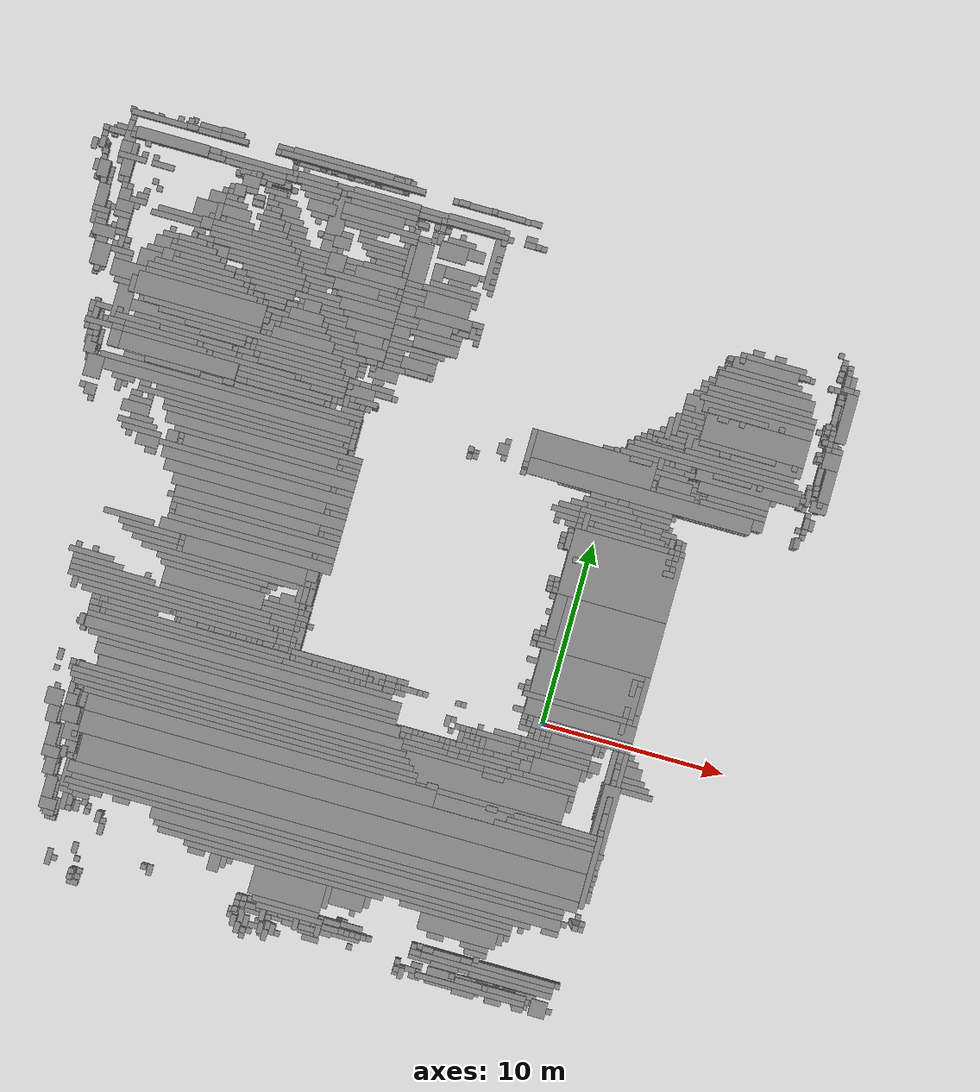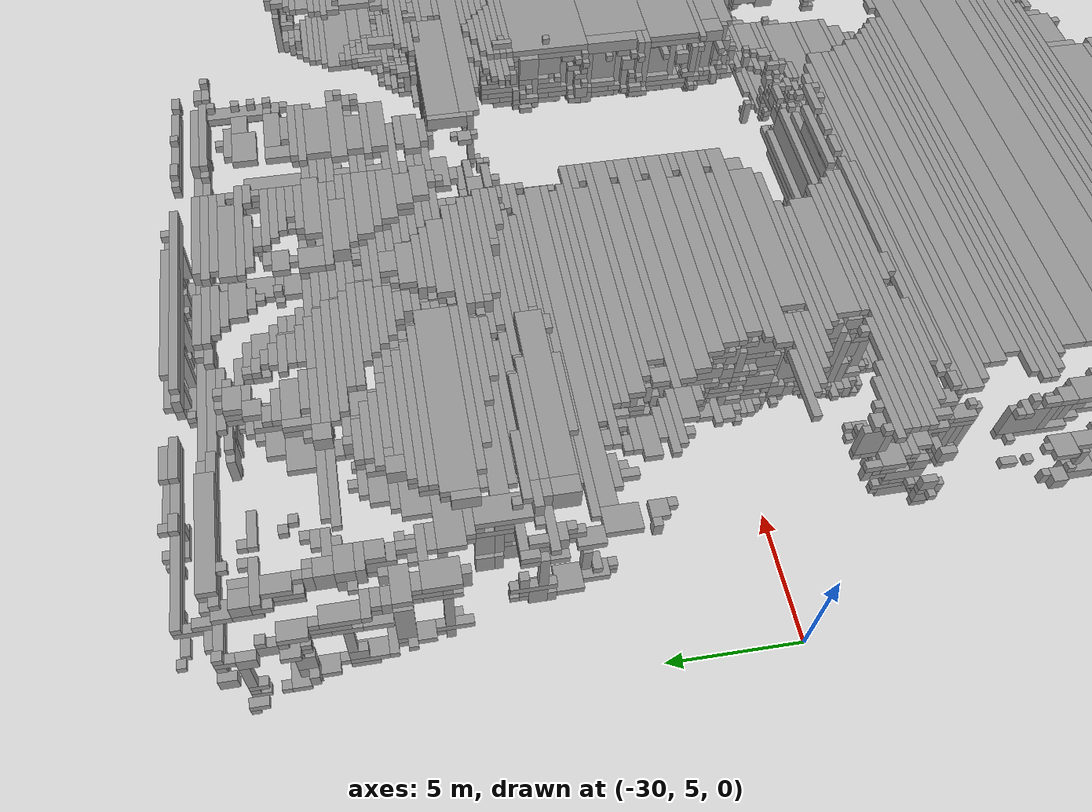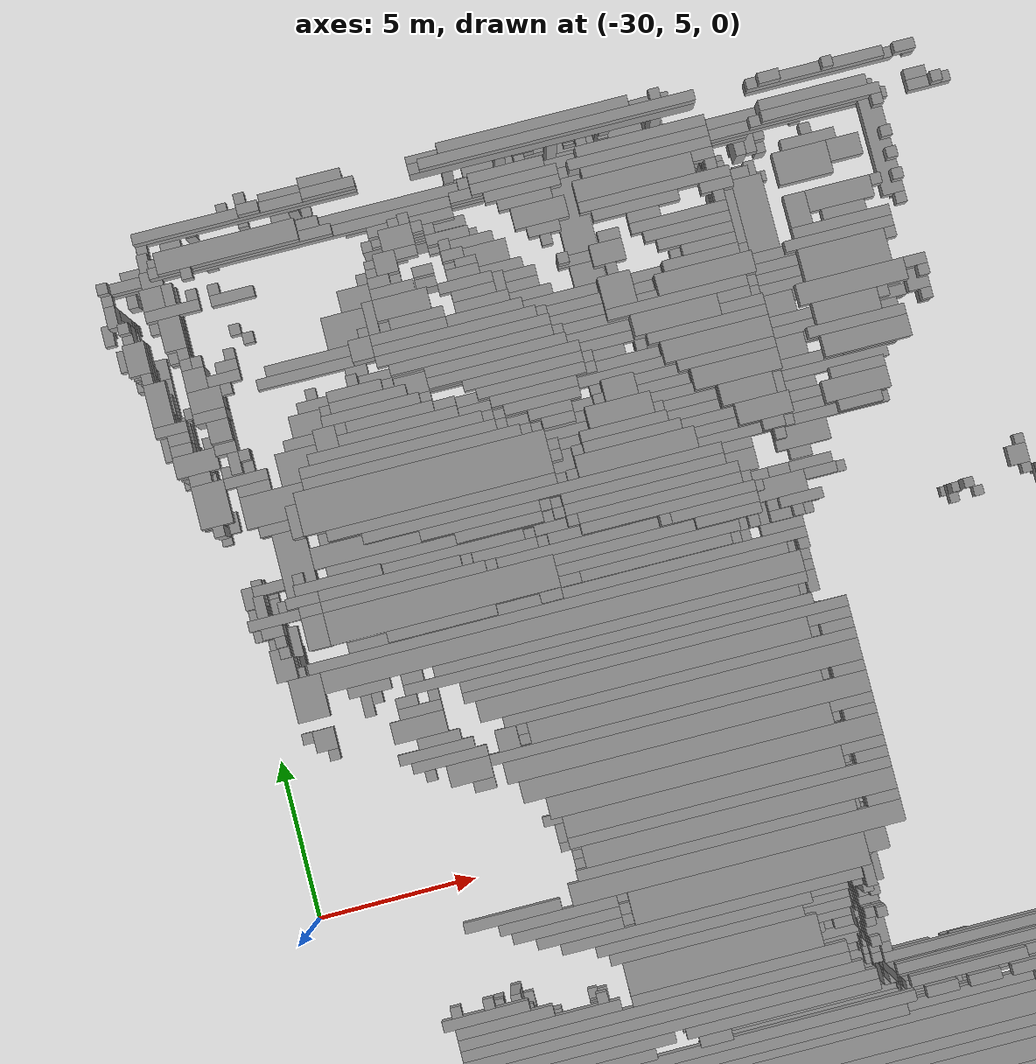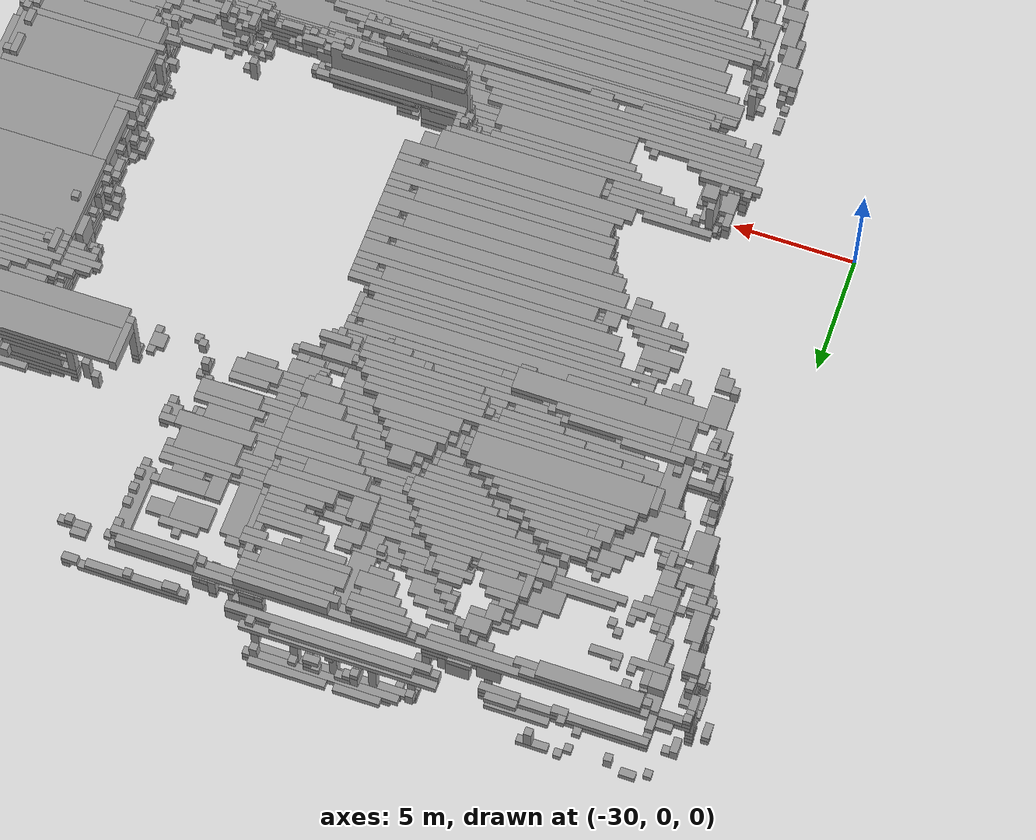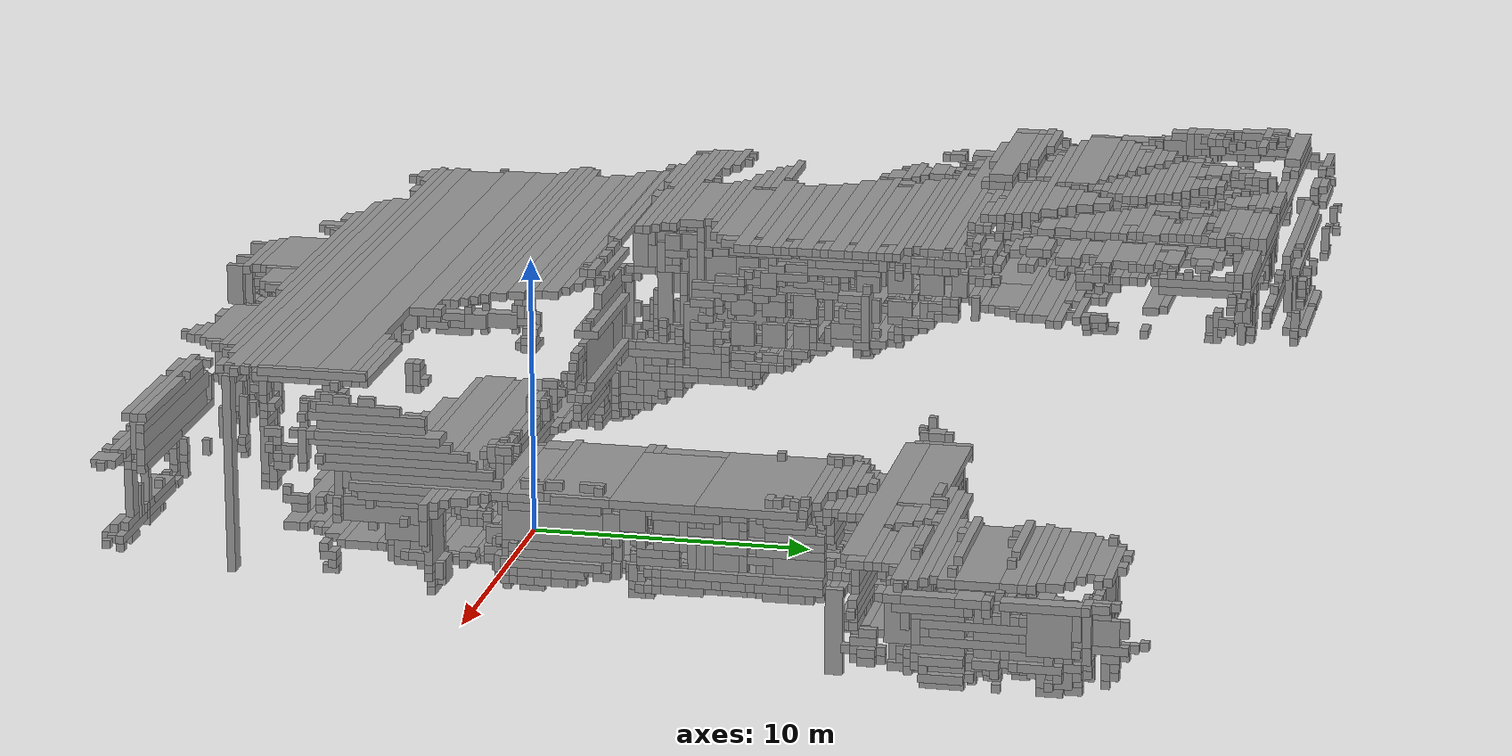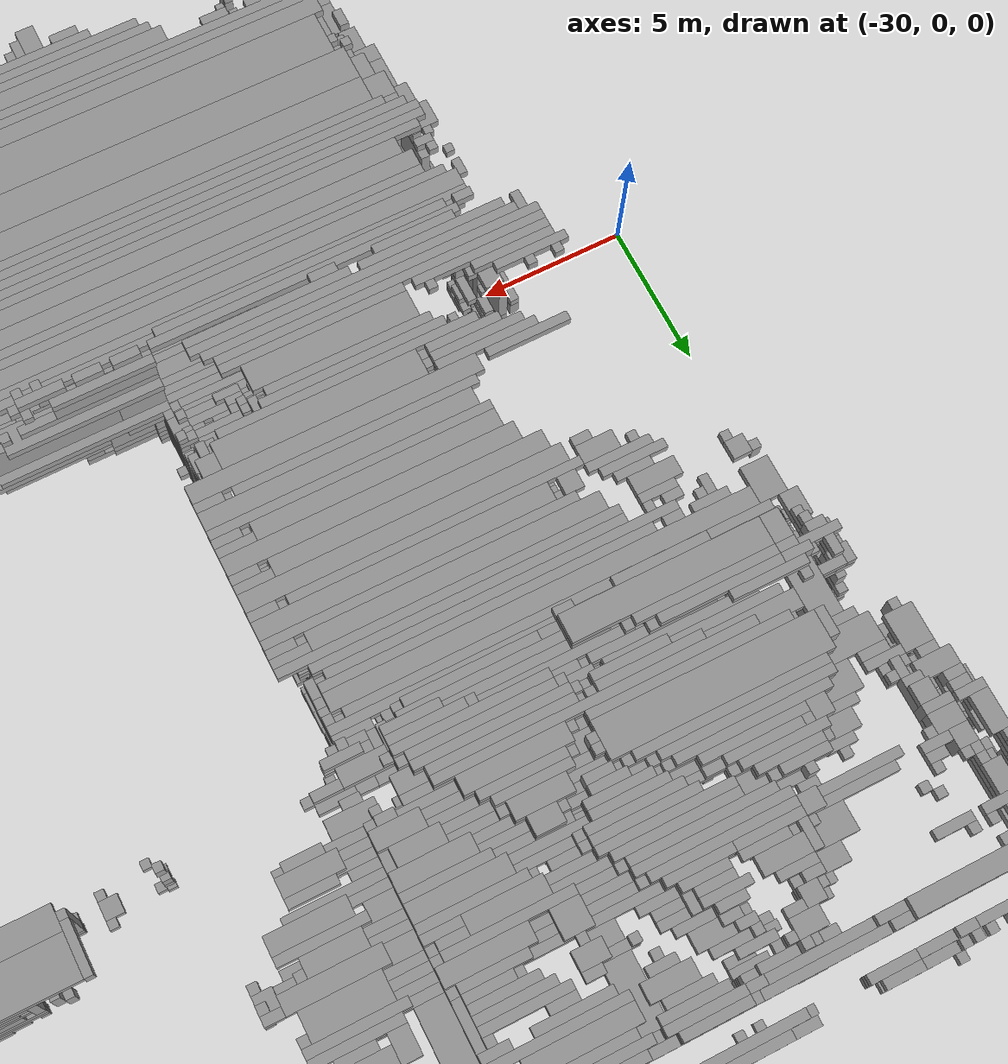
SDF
<?xml version="1.0"?>
<sdf version="1.6">
  <world name="bt_world">
    <include>
      <uri>model://sun</uri>
    </include>

    <physics type="ode">
      <max_step_size>0.002</max_step_size>
      <real_time_factor>1.0</real_time_factor>
      <real_time_update_rate>500</real_time_update_rate>
    </physics>

    <gravity>0 0 -9.81</gravity>

    <model name="obstacle_0">
      <static>true</static>
      <pose>-31.049999999999997 23.099999999999998 5.25 0 0 0</pose>
      <link name="link">
        <collision name="collision">
          <geometry><box><size>0.3 0.6 0.3</size></box></geometry>
        </collision>
        <visual name="visual">
          <geometry><box><size>0.3 0.6 0.3</size></box></geometry>
          <material>
            <ambient>0.5 0.5 0.5 1</ambient>
            <diffuse>0.6 0.6 0.6 1</diffuse>
          </material>
        </visual>
      </link>
    </model>

    <model name="obstacle_1">
      <static>true</static>
      <pose>-31.049999999999997 23.25 4.95 0 0 0</pose>
      <link name="link">
        <collision name="collision">
          <geometry><box><size>0.3 0.3 0.3</size></box></geometry>
        </collision>
        <visual name="visual">
          <geometry><box><size>0.3 0.3 0.3</size></box></geometry>
          <material>
            <ambient>0.5 0.5 0.5 1</ambient>
            <diffuse>0.6 0.6 0.6 1</diffuse>
          </material>
        </visual>
      </link>
    </model>

    <model name="obstacle_2">
      <static>true</static>
      <pose>-30.299999999999997 21.45 5.1 0 0 0</pose>
      <link name="link">
        <collision name="collision">
          <geometry><box><size>0.6 0.3 0.6</size></box></geometry>
        </collision>
        <visual name="visual">
          <geometry><box><size>0.6 0.3 0.6</size></box></geometry>
          <material>
            <ambient>0.5 0.5 0.5 1</ambient>
            <diffuse>0.6 0.6 0.6 1</diffuse>
          </material>
        </visual>
      </link>
    </model>

    <model name="obstacle_3">
      <static>true</static>
      <pose>-30.15 21.9 4.6499999999999995 0 0 0</pose>
      <link name="link">
        <collision name="collision">
          <geometry><box><size>0.8999999999999999 0.6 0.3</size></box></geometry>
        </collision>
        <visual name="visual">
          <geometry><box><size>0.8999999999999999 0.6 0.3</size></box></geometry>
          <material>
            <ambient>0.5 0.5 0.5 1</ambient>
            <diffuse>0.6 0.6 0.6 1</diffuse>
          </material>
        </visual>
      </link>
    </model>

    <model name="obstacle_4">
      <static>true</static>
      <pose>-30.15 21.9 7.05 0 0 0</pose>
      <link name="link">
        <collision name="collision">
          <geometry><box><size>0.8999999999999999 0.6 0.3</size></box></geometry>
        </collision>
        <visual name="visual">
          <geometry><box><size>0.8999999999999999 0.6 0.3</size></box></geometry>
          <material>
            <ambient>0.5 0.5 0.5 1</ambient>
            <diffuse>0.6 0.6 0.6 1</diffuse>
          </material>
        </visual>
      </link>
    </model>

    <model name="obstacle_5">
      <static>true</static>
      <pose>-30.45 22.349999999999998 4.6499999999999995 0 0 0</pose>
      <link name="link">
        <collision name="collision">
          <geometry><box><size>0.3 0.3 0.3</size></box></geometry>
        </collision>
        <visual name="visual">
          <geometry><box><size>0.3 0.3 0.3</size></box></geometry>
          <material>
            <ambient>0.5 0.5 0.5 1</ambient>
            <diffuse>0.6 0.6 0.6 1</diffuse>
          </material>
        </visual>
      </link>
    </model>

    <model name="obstacle_6">
      <static>true</static>
      <pose>-30.45 23.099999999999998 4.6499999999999995 0 0 0</pose>
      <link name="link">
        <collision name="collision">
          <geometry><box><size>0.3 0.6 0.3</size></box></geometry>
        </collision>
        <visual name="visual">
          <geometry><box><size>0.3 0.6 0.3</size></box></geometry>
          <material>
            <ambient>0.5 0.5 0.5 1</ambient>
            <diffuse>0.6 0.6 0.6 1</diffuse>
          </material>
        </visual>
      </link>
    </model>

    <model name="obstacle_7">
      <static>true</static>
      <pose>-30.45 23.099999999999998 5.25 0 0 0</pose>
      <link name="link">
        <collision name="collision">
          <geometry><box><size>0.3 0.6 0.3</size></box></geometry>
        </collision>
        <visual name="visual">
          <geometry><box><size>0.3 0.6 0.3</size></box></geometry>
          <material>
            <ambient>0.5 0.5 0.5 1</ambient>
            <diffuse>0.6 0.6 0.6 1</diffuse>
          </material>
        </visual>
      </link>
    </model>

    <model name="obstacle_8">
      <static>true</static>
      <pose>-30.45 23.099999999999998 7.199999999999999 0 0 0</pose>
      <link name="link">
        <collision name="collision">
          <geometry><box><size>0.3 0.6 0.6</size></box></geometry>
        </collision>
        <visual name="visual">
          <geometry><box><size>0.3 0.6 0.6</size></box></geometry>
          <material>
            <ambient>0.5 0.5 0.5 1</ambient>
            <diffuse>0.6 0.6 0.6 1</diffuse>
          </material>
        </visual>
      </link>
    </model>

    <model name="obstacle_9">
      <static>true</static>
      <pose>-30.45 23.25 4.35 0 0 0</pose>
      <link name="link">
        <collision name="collision">
          <geometry><box><size>0.3 0.3 0.3</size></box></geometry>
        </collision>
        <visual name="visual">
          <geometry><box><size>0.3 0.3 0.3</size></box></geometry>
          <material>
            <ambient>0.5 0.5 0.5 1</ambient>
            <diffuse>0.6 0.6 0.6 1</diffuse>
          </material>
        </visual>
      </link>
    </model>

    <model name="obstacle_10">
      <static>true</static>
      <pose>-30.45 23.25 4.95 0 0 0</pose>
      <link name="link">
        <collision name="collision">
          <geometry><box><size>0.3 0.3 0.3</size></box></geometry>
        </collision>
        <visual name="visual">
          <geometry><box><size>0.3 0.3 0.3</size></box></geometry>
          <material>
            <ambient>0.5 0.5 0.5 1</ambient>
            <diffuse>0.6 0.6 0.6 1</diffuse>
          </material>
        </visual>
      </link>
    </model>

    <model name="obstacle_11">
      <static>true</static>
      <pose>-30.45 23.25 6.1499999999999995 0 0 0</pose>
      <link name="link">
        <collision name="collision">
          <geometry><box><size>0.3 0.3 1.5</size></box></geometry>
        </collision>
        <visual name="visual">
          <geometry><box><size>0.3 0.3 1.5</size></box></geometry>
          <material>
            <ambient>0.5 0.5 0.5 1</ambient>
            <diffuse>0.6 0.6 0.6 1</diffuse>
          </material>
        </visual>
      </link>
    </model>

    <model name="obstacle_12">
      <static>true</static>
      <pose>-30.45 23.7 7.35 0 0 0</pose>
      <link name="link">
        <collision name="collision">
          <geometry><box><size>0.3 0.6 0.3</size></box></geometry>
        </collision>
        <visual name="visual">
          <geometry><box><size>0.3 0.6 0.3</size></box></geometry>
          <material>
            <ambient>0.5 0.5 0.5 1</ambient>
            <diffuse>0.6 0.6 0.6 1</diffuse>
          </material>
        </visual>
      </link>
    </model>

    <model name="obstacle_13">
      <static>true</static>
      <pose>-29.849999999999998 23.849999999999998 7.05 0 0 0</pose>
      <link name="link">
        <collision name="collision">
          <geometry><box><size>1.5 0.3 0.3</size></box></geometry>
        </collision>
        <visual name="visual">
          <geometry><box><size>1.5 0.3 0.3</size></box></geometry>
          <material>
            <ambient>0.5 0.5 0.5 1</ambient>
            <diffuse>0.6 0.6 0.6 1</diffuse>
          </material>
        </visual>
      </link>
    </model>

    <model name="obstacle_14">
      <static>true</static>
      <pose>-30.45 23.849999999999998 7.6499999999999995 0 0 0</pose>
      <link name="link">
        <collision name="collision">
          <geometry><box><size>0.3 0.3 0.3</size></box></geometry>
        </collision>
        <visual name="visual">
          <geometry><box><size>0.3 0.3 0.3</size></box></geometry>
          <material>
            <ambient>0.5 0.5 0.5 1</ambient>
            <diffuse>0.6 0.6 0.6 1</diffuse>
          </material>
        </visual>
      </link>
    </model>

    <model name="obstacle_15">
      <static>true</static>
      <pose>-30.0 21.15 4.6499999999999995 0 0 0</pose>
      <link name="link">
        <collision name="collision">
          <geometry><box><size>0.6 0.8999999999999999 0.3</size></box></geometry>
        </collision>
        <visual name="visual">
          <geometry><box><size>0.6 0.8999999999999999 0.3</size></box></geometry>
          <material>
            <ambient>0.5 0.5 0.5 1</ambient>
            <diffuse>0.6 0.6 0.6 1</diffuse>
          </material>
        </visual>
      </link>
    </model>

    <model name="obstacle_16">
      <static>true</static>
      <pose>-30.15 21.45 4.35 0 0 0</pose>
      <link name="link">
        <collision name="collision">
          <geometry><box><size>0.3 0.3 0.3</size></box></geometry>
        </collision>
        <visual name="visual">
          <geometry><box><size>0.3 0.3 0.3</size></box></geometry>
          <material>
            <ambient>0.5 0.5 0.5 1</ambient>
            <diffuse>0.6 0.6 0.6 1</diffuse>
          </material>
        </visual>
      </link>
    </model>

    <model name="obstacle_17">
      <static>true</static>
      <pose>-30.15 21.599999999999998 5.85 0 0 0</pose>
      <link name="link">
        <collision name="collision">
          <geometry><box><size>0.3 0.6 0.8999999999999999</size></box></geometry>
        </collision>
        <visual name="visual">
          <geometry><box><size>0.3 0.6 0.8999999999999999</size></box></geometry>
          <material>
            <ambient>0.5 0.5 0.5 1</ambient>
            <diffuse>0.6 0.6 0.6 1</diffuse>
          </material>
        </visual>
      </link>
    </model>

    <model name="obstacle_18">
      <static>true</static>
      <pose>-30.15 21.599999999999998 6.75 0 0 0</pose>
      <link name="link">
        <collision name="collision">
          <geometry><box><size>0.3 0.6 0.3</size></box></geometry>
        </collision>
        <visual name="visual">
          <geometry><box><size>0.3 0.6 0.3</size></box></geometry>
          <material>
            <ambient>0.5 0.5 0.5 1</ambient>
            <diffuse>0.6 0.6 0.6 1</diffuse>
          </material>
        </visual>
      </link>
    </model>

    <model name="obstacle_19">
      <static>true</static>
      <pose>-30.0 21.45 7.05 0 0 0</pose>
      <link name="link">
        <collision name="collision">
          <geometry><box><size>0.6 0.3 0.3</size></box></geometry>
        </collision>
        <visual name="visual">
          <geometry><box><size>0.6 0.3 0.3</size></box></geometry>
          <material>
            <ambient>0.5 0.5 0.5 1</ambient>
            <diffuse>0.6 0.6 0.6 1</diffuse>
          </material>
        </visual>
      </link>
    </model>

    <model name="obstacle_20">
      <static>true</static>
      <pose>-30.0 21.75 7.6499999999999995 0 0 0</pose>
      <link name="link">
        <collision name="collision">
          <geometry><box><size>0.6 0.8999999999999999 0.3</size></box></geometry>
        </collision>
        <visual name="visual">
          <geometry><box><size>0.6 0.8999999999999999 0.3</size></box></geometry>
          <material>
            <ambient>0.5 0.5 0.5 1</ambient>
            <diffuse>0.6 0.6 0.6 1</diffuse>
          </material>
        </visual>
      </link>
    </model>

    <model name="obstacle_21">
      <static>true</static>
      <pose>-30.15 21.75 5.1 0 0 0</pose>
      <link name="link">
        <collision name="collision">
          <geometry><box><size>0.3 0.3 0.6</size></box></geometry>
        </collision>
        <visual name="visual">
          <geometry><box><size>0.3 0.3 0.6</size></box></geometry>
          <material>
            <ambient>0.5 0.5 0.5 1</ambient>
            <diffuse>0.6 0.6 0.6 1</diffuse>
          </material>
        </visual>
      </link>
    </model>

    <model name="obstacle_22">
      <static>true</static>
      <pose>-30.15 21.75 6.45 0 0 0</pose>
      <link name="link">
        <collision name="collision">
          <geometry><box><size>0.3 0.3 0.3</size></box></geometry>
        </collision>
        <visual name="visual">
          <geometry><box><size>0.3 0.3 0.3</size></box></geometry>
          <material>
            <ambient>0.5 0.5 0.5 1</ambient>
            <diffuse>0.6 0.6 0.6 1</diffuse>
          </material>
        </visual>
      </link>
    </model>

    <model name="obstacle_23">
      <static>true</static>
      <pose>-30.0 22.05 7.35 0 0 0</pose>
      <link name="link">
        <collision name="collision">
          <geometry><box><size>0.6 0.3 0.3</size></box></geometry>
        </collision>
        <visual name="visual">
          <geometry><box><size>0.6 0.3 0.3</size></box></geometry>
          <material>
            <ambient>0.5 0.5 0.5 1</ambient>
            <diffuse>0.6 0.6 0.6 1</diffuse>
          </material>
        </visual>
      </link>
    </model>

    <model name="obstacle_24">
      <static>true</static>
      <pose>-30.15 22.5 7.199999999999999 0 0 0</pose>
      <link name="link">
        <collision name="collision">
          <geometry><box><size>0.3 0.6 0.6</size></box></geometry>
        </collision>
        <visual name="visual">
          <geometry><box><size>0.3 0.6 0.6</size></box></geometry>
          <material>
            <ambient>0.5 0.5 0.5 1</ambient>
            <diffuse>0.6 0.6 0.6 1</diffuse>
          </material>
        </visual>
      </link>
    </model>

    <model name="obstacle_25">
      <static>true</static>
      <pose>-30.15 22.65 7.6499999999999995 0 0 0</pose>
      <link name="link">
        <collision name="collision">
          <geometry><box><size>0.3 0.3 0.3</size></box></geometry>
        </collision>
        <visual name="visual">
          <geometry><box><size>0.3 0.3 0.3</size></box></geometry>
          <material>
            <ambient>0.5 0.5 0.5 1</ambient>
            <diffuse>0.6 0.6 0.6 1</diffuse>
          </material>
        </visual>
      </link>
    </model>

    <model name="obstacle_26">
      <static>true</static>
      <pose>-30.15 24.0 5.1 0 0 0</pose>
      <link name="link">
        <collision name="collision">
          <geometry><box><size>0.3 0.6 0.6</size></box></geometry>
        </collision>
        <visual name="visual">
          <geometry><box><size>0.3 0.6 0.6</size></box></geometry>
          <material>
            <ambient>0.5 0.5 0.5 1</ambient>
            <diffuse>0.6 0.6 0.6 1</diffuse>
          </material>
        </visual>
      </link>
    </model>

    <model name="obstacle_27">
      <static>true</static>
      <pose>-29.7 23.849999999999998 7.35 0 0 0</pose>
      <link name="link">
        <collision name="collision">
          <geometry><box><size>1.2 0.3 0.3</size></box></geometry>
        </collision>
        <visual name="visual">
          <geometry><box><size>1.2 0.3 0.3</size></box></geometry>
          <material>
            <ambient>0.5 0.5 0.5 1</ambient>
            <diffuse>0.6 0.6 0.6 1</diffuse>
          </material>
        </visual>
      </link>
    </model>

    <model name="obstacle_28">
      <static>true</static>
      <pose>-29.7 18.45 4.95 0 0 0</pose>
      <link name="link">
        <collision name="collision">
          <geometry><box><size>0.6 0.3 0.3</size></box></geometry>
        </collision>
        <visual name="visual">
          <geometry><box><size>0.6 0.3 0.3</size></box></geometry>
          <material>
            <ambient>0.5 0.5 0.5 1</ambient>
            <diffuse>0.6 0.6 0.6 1</diffuse>
          </material>
        </visual>
      </link>
    </model>

    <model name="obstacle_29">
      <static>true</static>
      <pose>-29.549999999999997 19.05 4.6499999999999995 0 0 0</pose>
      <link name="link">
        <collision name="collision">
          <geometry><box><size>0.8999999999999999 0.3 0.3</size></box></geometry>
        </collision>
        <visual name="visual">
          <geometry><box><size>0.8999999999999999 0.3 0.3</size></box></geometry>
          <material>
            <ambient>0.5 0.5 0.5 1</ambient>
            <diffuse>0.6 0.6 0.6 1</diffuse>
          </material>
        </visual>
      </link>
    </model>

    <model name="obstacle_30">
      <static>true</static>
      <pose>-29.549999999999997 19.349999999999998 7.05 0 0 0</pose>
      <link name="link">
        <collision name="collision">
          <geometry><box><size>0.8999999999999999 0.8999999999999999 0.3</size></box></geometry>
        </collision>
        <visual name="visual">
          <geometry><box><size>0.8999999999999999 0.8999999999999999 0.3</size></box></geometry>
          <material>
            <ambient>0.5 0.5 0.5 1</ambient>
            <diffuse>0.6 0.6 0.6 1</diffuse>
          </material>
        </visual>
      </link>
    </model>

    <model name="obstacle_31">
      <static>true</static>
      <pose>-29.7 19.8 4.6499999999999995 0 0 0</pose>
      <link name="link">
        <collision name="collision">
          <geometry><box><size>0.6 1.2 0.3</size></box></geometry>
        </collision>
        <visual name="visual">
          <geometry><box><size>0.6 1.2 0.3</size></box></geometry>
          <material>
            <ambient>0.5 0.5 0.5 1</ambient>
            <diffuse>0.6 0.6 0.6 1</diffuse>
          </material>
        </visual>
      </link>
    </model>

    <model name="obstacle_32">
      <static>true</static>
      <pose>-29.849999999999998 19.95 4.35 0 0 0</pose>
      <link name="link">
        <collision name="collision">
          <geometry><box><size>0.3 0.8999999999999999 0.3</size></box></geometry>
        </collision>
        <visual name="visual">
          <geometry><box><size>0.3 0.8999999999999999 0.3</size></box></geometry>
          <material>
            <ambient>0.5 0.5 0.5 1</ambient>
            <diffuse>0.6 0.6 0.6 1</diffuse>
          </material>
        </visual>
      </link>
    </model>

    <model name="obstacle_33">
      <static>true</static>
      <pose>-29.549999999999997 19.65 7.6499999999999995 0 0 0</pose>
      <link name="link">
        <collision name="collision">
          <geometry><box><size>0.8999999999999999 0.3 0.3</size></box></geometry>
        </collision>
        <visual name="visual">
          <geometry><box><size>0.8999999999999999 0.3 0.3</size></box></geometry>
          <material>
            <ambient>0.5 0.5 0.5 1</ambient>
            <diffuse>0.6 0.6 0.6 1</diffuse>
          </material>
        </visual>
      </link>
    </model>

    <model name="obstacle_34">
      <static>true</static>
      <pose>-29.849999999999998 20.099999999999998 5.1 0 0 0</pose>
      <link name="link">
        <collision name="collision">
          <geometry><box><size>0.3 0.6 0.6</size></box></geometry>
        </collision>
        <visual name="visual">
          <geometry><box><size>0.3 0.6 0.6</size></box></geometry>
          <material>
            <ambient>0.5 0.5 0.5 1</ambient>
            <diffuse>0.6 0.6 0.6 1</diffuse>
          </material>
        </visual>
      </link>
    </model>

    <model name="obstacle_35">
      <static>true</static>
      <pose>-29.7 20.25 7.05 0 0 0</pose>
      <link name="link">
        <collision name="collision">
          <geometry><box><size>0.6 0.8999999999999999 0.3</size></box></geometry>
        </collision>
        <visual name="visual">
          <geometry><box><size>0.6 0.8999999999999999 0.3</size></box></geometry>
          <material>
            <ambient>0.5 0.5 0.5 1</ambient>
            <diffuse>0.6 0.6 0.6 1</diffuse>
          </material>
        </visual>
      </link>
    </model>

    <model name="obstacle_36">
      <static>true</static>
      <pose>-29.7 20.4 7.6499999999999995 0 0 0</pose>
      <link name="link">
        <collision name="collision">
          <geometry><box><size>0.6 1.2 0.3</size></box></geometry>
        </collision>
        <visual name="visual">
          <geometry><box><size>0.6 1.2 0.3</size></box></geometry>
          <material>
            <ambient>0.5 0.5 0.5 1</ambient>
            <diffuse>0.6 0.6 0.6 1</diffuse>
          </material>
        </visual>
      </link>
    </model>

    <model name="obstacle_37">
      <static>true</static>
      <pose>-29.849999999999998 20.25 6.1499999999999995 0 0 0</pose>
      <link name="link">
        <collision name="collision">
          <geometry><box><size>0.3 0.3 1.5</size></box></geometry>
        </collision>
        <visual name="visual">
          <geometry><box><size>0.3 0.3 1.5</size></box></geometry>
          <material>
            <ambient>0.5 0.5 0.5 1</ambient>
            <diffuse>0.6 0.6 0.6 1</diffuse>
          </material>
        </visual>
      </link>
    </model>

    <model name="obstacle_38">
      <static>true</static>
      <pose>-29.849999999999998 21.0 7.35 0 0 0</pose>
      <link name="link">
        <collision name="collision">
          <geometry><box><size>0.3 1.7999999999999998 0.3</size></box></geometry>
        </collision>
        <visual name="visual">
          <geometry><box><size>0.3 1.7999999999999998 0.3</size></box></geometry>
          <material>
            <ambient>0.5 0.5 0.5 1</ambient>
            <diffuse>0.6 0.6 0.6 1</diffuse>
          </material>
        </visual>
      </link>
    </model>

    <model name="obstacle_39">
      <static>true</static>
      <pose>-29.849999999999998 20.55 4.6499999999999995 0 0 0</pose>
      <link name="link">
        <collision name="collision">
          <geometry><box><size>0.3 0.3 0.3</size></box></geometry>
        </collision>
        <visual name="visual">
          <geometry><box><size>0.3 0.3 0.3</size></box></geometry>
          <material>
            <ambient>0.5 0.5 0.5 1</ambient>
            <diffuse>0.6 0.6 0.6 1</diffuse>
          </material>
        </visual>
      </link>
    </model>

    <model name="obstacle_40">
      <static>true</static>
      <pose>-29.849999999999998 21.0 7.05 0 0 0</pose>
      <link name="link">
        <collision name="collision">
          <geometry><box><size>0.3 0.6 0.3</size></box></geometry>
        </collision>
        <visual name="visual">
          <geometry><box><size>0.3 0.6 0.3</size></box></geometry>
          <material>
            <ambient>0.5 0.5 0.5 1</ambient>
            <diffuse>0.6 0.6 0.6 1</diffuse>
          </material>
        </visual>
      </link>
    </model>

    <model name="obstacle_41">
      <static>true</static>
      <pose>-29.849999999999998 21.15 7.6499999999999995 0 0 0</pose>
      <link name="link">
        <collision name="collision">
          <geometry><box><size>0.3 0.3 0.3</size></box></geometry>
        </collision>
        <visual name="visual">
          <geometry><box><size>0.3 0.3 0.3</size></box></geometry>
          <material>
            <ambient>0.5 0.5 0.5 1</ambient>
            <diffuse>0.6 0.6 0.6 1</diffuse>
          </material>
        </visual>
      </link>
    </model>

    <model name="obstacle_42">
      <static>true</static>
      <pose>-29.849999999999998 24.15 4.95 0 0 0</pose>
      <link name="link">
        <collision name="collision">
          <geometry><box><size>0.3 0.3 0.3</size></box></geometry>
        </collision>
        <visual name="visual">
          <geometry><box><size>0.3 0.3 0.3</size></box></geometry>
          <material>
            <ambient>0.5 0.5 0.5 1</ambient>
            <diffuse>0.6 0.6 0.6 1</diffuse>
          </material>
        </visual>
      </link>
    </model>

    <model name="obstacle_43">
      <static>true</static>
      <pose>-29.549999999999997 24.15 7.05 0 0 0</pose>
      <link name="link">
        <collision name="collision">
          <geometry><box><size>0.8999999999999999 0.3 0.3</size></box></geometry>
        </collision>
        <visual name="visual">
          <geometry><box><size>0.8999999999999999 0.3 0.3</size></box></geometry>
          <material>
            <ambient>0.5 0.5 0.5 1</ambient>
            <diffuse>0.6 0.6 0.6 1</diffuse>
          </material>
        </visual>
      </link>
    </model>

    <model name="obstacle_44">
      <static>true</static>
      <pose>-29.4 18.3 4.6499999999999995 0 0 0</pose>
      <link name="link">
        <collision name="collision">
          <geometry><box><size>0.6 1.2 0.3</size></box></geometry>
        </collision>
        <visual name="visual">
          <geometry><box><size>0.6 1.2 0.3</size></box></geometry>
          <material>
            <ambient>0.5 0.5 0.5 1</ambient>
            <diffuse>0.6 0.6 0.6 1</diffuse>
          </material>
        </visual>
      </link>
    </model>

    <model name="obstacle_45">
      <static>true</static>
      <pose>-29.549999999999997 18.599999999999998 6.1499999999999995 0 0 0</pose>
      <link name="link">
        <collision name="collision">
          <geometry><box><size>0.3 0.6 2.1</size></box></geometry>
        </collision>
        <visual name="visual">
          <geometry><box><size>0.3 0.6 2.1</size></box></geometry>
          <material>
            <ambient>0.5 0.5 0.5 1</ambient>
            <diffuse>0.6 0.6 0.6 1</diffuse>
          </material>
        </visual>
      </link>
    </model>

    <model name="obstacle_46">
      <static>true</static>
      <pose>-29.099999999999998 18.599999999999998 7.6499999999999995 0 0 0</pose>
      <link name="link">
        <collision name="collision">
          <geometry><box><size>1.2 0.6 0.3</size></box></geometry>
        </collision>
        <visual name="visual">
          <geometry><box><size>1.2 0.6 0.3</size></box></geometry>
          <material>
            <ambient>0.5 0.5 0.5 1</ambient>
            <diffuse>0.6 0.6 0.6 1</diffuse>
          </material>
        </visual>
      </link>
    </model>

    <model name="obstacle_47">
      <static>true</static>
      <pose>-29.4 18.75 4.95 0 0 0</pose>
      <link name="link">
        <collision name="collision">
          <geometry><box><size>0.6 0.3 0.3</size></box></geometry>
        </collision>
        <visual name="visual">
          <geometry><box><size>0.6 0.3 0.3</size></box></geometry>
          <material>
            <ambient>0.5 0.5 0.5 1</ambient>
            <diffuse>0.6 0.6 0.6 1</diffuse>
          </material>
        </visual>
      </link>
    </model>

    <model name="obstacle_48">
      <static>true</static>
      <pose>-29.549999999999997 19.2 4.35 0 0 0</pose>
      <link name="link">
        <collision name="collision">
          <geometry><box><size>0.3 0.6 0.3</size></box></geometry>
        </collision>
        <visual name="visual">
          <geometry><box><size>0.3 0.6 0.3</size></box></geometry>
          <material>
            <ambient>0.5 0.5 0.5 1</ambient>
            <diffuse>0.6 0.6 0.6 1</diffuse>
          </material>
        </visual>
      </link>
    </model>

    <model name="obstacle_49">
      <static>true</static>
      <pose>-29.4 19.05 7.5 0 0 0</pose>
      <link name="link">
        <collision name="collision">
          <geometry><box><size>0.6 0.3 0.6</size></box></geometry>
        </collision>
        <visual name="visual">
          <geometry><box><size>0.6 0.3 0.6</size></box></geometry>
          <material>
            <ambient>0.5 0.5 0.5 1</ambient>
            <diffuse>0.6 0.6 0.6 1</diffuse>
          </material>
        </visual>
      </link>
    </model>

    <model name="obstacle_50">
      <static>true</static>
      <pose>-29.549999999999997 19.65 7.35 0 0 0</pose>
      <link name="link">
        <collision name="collision">
          <geometry><box><size>0.3 0.8999999999999999 0.3</size></box></geometry>
        </collision>
        <visual name="visual">
          <geometry><box><size>0.3 0.8999999999999999 0.3</size></box></geometry>
          <material>
            <ambient>0.5 0.5 0.5 1</ambient>
            <diffuse>0.6 0.6 0.6 1</diffuse>
          </material>
        </visual>
      </link>
    </model>

    <model name="obstacle_51">
      <static>true</static>
      <pose>-29.4 19.349999999999998 7.6499999999999995 0 0 0</pose>
      <link name="link">
        <collision name="collision">
          <geometry><box><size>0.6 0.3 0.3</size></box></geometry>
        </collision>
        <visual name="visual">
          <geometry><box><size>0.6 0.3 0.3</size></box></geometry>
          <material>
            <ambient>0.5 0.5 0.5 1</ambient>
            <diffuse>0.6 0.6 0.6 1</diffuse>
          </material>
        </visual>
      </link>
    </model>

    <model name="obstacle_52">
      <static>true</static>
      <pose>-29.549999999999997 25.349999999999998 5.25 0 0 0</pose>
      <link name="link">
        <collision name="collision">
          <geometry><box><size>0.3 0.3 0.3</size></box></geometry>
        </collision>
        <visual name="visual">
          <geometry><box><size>0.3 0.3 0.3</size></box></geometry>
          <material>
            <ambient>0.5 0.5 0.5 1</ambient>
            <diffuse>0.6 0.6 0.6 1</diffuse>
          </material>
        </visual>
      </link>
    </model>

    <model name="obstacle_53">
      <static>true</static>
      <pose>-29.25 17.099999999999998 4.6499999999999995 0 0 0</pose>
      <link name="link">
        <collision name="collision">
          <geometry><box><size>0.3 1.2 0.3</size></box></geometry>
        </collision>
        <visual name="visual">
          <geometry><box><size>0.3 1.2 0.3</size></box></geometry>
          <material>
            <ambient>0.5 0.5 0.5 1</ambient>
            <diffuse>0.6 0.6 0.6 1</diffuse>
          </material>
        </visual>
      </link>
    </model>

    <model name="obstacle_54">
      <static>true</static>
      <pose>-29.099999999999998 17.4 7.05 0 0 0</pose>
      <link name="link">
        <collision name="collision">
          <geometry><box><size>0.6 1.2 0.3</size></box></geometry>
        </collision>
        <visual name="visual">
          <geometry><box><size>0.6 1.2 0.3</size></box></geometry>
          <material>
            <ambient>0.5 0.5 0.5 1</ambient>
            <diffuse>0.6 0.6 0.6 1</diffuse>
          </material>
        </visual>
      </link>
    </model>

    <model name="obstacle_55">
      <static>true</static>
      <pose>-28.95 17.4 7.6499999999999995 0 0 0</pose>
      <link name="link">
        <collision name="collision">
          <geometry><box><size>0.8999999999999999 1.2 0.3</size></box></geometry>
        </collision>
        <visual name="visual">
          <geometry><box><size>0.8999999999999999 1.2 0.3</size></box></geometry>
          <material>
            <ambient>0.5 0.5 0.5 1</ambient>
            <diffuse>0.6 0.6 0.6 1</diffuse>
          </material>
        </visual>
      </link>
    </model>

    <model name="obstacle_56">
      <static>true</static>
      <pose>-29.25 17.25 4.2 0 0 0</pose>
      <link name="link">
        <collision name="collision">
          <geometry><box><size>0.3 0.3 0.6</size></box></geometry>
        </collision>
        <visual name="visual">
          <geometry><box><size>0.3 0.3 0.6</size></box></geometry>
          <material>
            <ambient>0.5 0.5 0.5 1</ambient>
            <diffuse>0.6 0.6 0.6 1</diffuse>
          </material>
        </visual>
      </link>
    </model>

    <model name="obstacle_57">
      <static>true</static>
      <pose>-29.25 17.25 5.85 0 0 0</pose>
      <link name="link">
        <collision name="collision">
          <geometry><box><size>0.3 0.3 2.1</size></box></geometry>
        </collision>
        <visual name="visual">
          <geometry><box><size>0.3 0.3 2.1</size></box></geometry>
          <material>
            <ambient>0.5 0.5 0.5 1</ambient>
            <diffuse>0.6 0.6 0.6 1</diffuse>
          </material>
        </visual>
      </link>
    </model>

    <model name="obstacle_58">
      <static>true</static>
      <pose>-29.099999999999998 17.25 7.35 0 0 0</pose>
      <link name="link">
        <collision name="collision">
          <geometry><box><size>0.6 0.3 0.3</size></box></geometry>
        </collision>
        <visual name="visual">
          <geometry><box><size>0.6 0.3 0.3</size></box></geometry>
          <material>
            <ambient>0.5 0.5 0.5 1</ambient>
            <diffuse>0.6 0.6 0.6 1</diffuse>
          </material>
        </visual>
      </link>
    </model>

    <model name="obstacle_59">
      <static>true</static>
      <pose>-29.25 18.15 4.35 0 0 0</pose>
      <link name="link">
        <collision name="collision">
          <geometry><box><size>0.3 1.5 0.3</size></box></geometry>
        </collision>
        <visual name="visual">
          <geometry><box><size>0.3 1.5 0.3</size></box></geometry>
          <material>
            <ambient>0.5 0.5 0.5 1</ambient>
            <diffuse>0.6 0.6 0.6 1</diffuse>
          </material>
        </visual>
      </link>
    </model>

    <model name="obstacle_60">
      <static>true</static>
      <pose>-29.25 18.15 7.35 0 0 0</pose>
      <link name="link">
        <collision name="collision">
          <geometry><box><size>0.3 1.5 0.3</size></box></geometry>
        </collision>
        <visual name="visual">
          <geometry><box><size>0.3 1.5 0.3</size></box></geometry>
          <material>
            <ambient>0.5 0.5 0.5 1</ambient>
            <diffuse>0.6 0.6 0.6 1</diffuse>
          </material>
        </visual>
      </link>
    </model>

    <model name="obstacle_61">
      <static>true</static>
      <pose>-29.25 18.45 7.05 0 0 0</pose>
      <link name="link">
        <collision name="collision">
          <geometry><box><size>0.3 0.8999999999999999 0.3</size></box></geometry>
        </collision>
        <visual name="visual">
          <geometry><box><size>0.3 0.8999999999999999 0.3</size></box></geometry>
          <material>
            <ambient>0.5 0.5 0.5 1</ambient>
            <diffuse>0.6 0.6 0.6 1</diffuse>
          </material>
        </visual>
      </link>
    </model>

    <model name="obstacle_62">
      <static>true</static>
      <pose>-29.099999999999998 18.15 7.6499999999999995 0 0 0</pose>
      <link name="link">
        <collision name="collision">
          <geometry><box><size>0.6 0.3 0.3</size></box></geometry>
        </collision>
        <visual name="visual">
          <geometry><box><size>0.6 0.3 0.3</size></box></geometry>
          <material>
            <ambient>0.5 0.5 0.5 1</ambient>
            <diffuse>0.6 0.6 0.6 1</diffuse>
          </material>
        </visual>
      </link>
    </model>

    <model name="obstacle_63">
      <static>true</static>
      <pose>-29.25 18.599999999999998 6.45 0 0 0</pose>
      <link name="link">
        <collision name="collision">
          <geometry><box><size>0.3 0.6 0.3</size></box></geometry>
        </collision>
        <visual name="visual">
          <geometry><box><size>0.3 0.6 0.3</size></box></geometry>
          <material>
            <ambient>0.5 0.5 0.5 1</ambient>
            <diffuse>0.6 0.6 0.6 1</diffuse>
          </material>
        </visual>
      </link>
    </model>

    <model name="obstacle_64">
      <static>true</static>
      <pose>-29.25 18.75 5.25 0 0 0</pose>
      <link name="link">
        <collision name="collision">
          <geometry><box><size>0.3 0.3 0.3</size></box></geometry>
        </collision>
        <visual name="visual">
          <geometry><box><size>0.3 0.3 0.3</size></box></geometry>
          <material>
            <ambient>0.5 0.5 0.5 1</ambient>
            <diffuse>0.6 0.6 0.6 1</diffuse>
          </material>
        </visual>
      </link>
    </model>

    <model name="obstacle_65">
      <static>true</static>
      <pose>-29.25 18.75 6.0 0 0 0</pose>
      <link name="link">
        <collision name="collision">
          <geometry><box><size>0.3 0.3 0.6</size></box></geometry>
        </collision>
        <visual name="visual">
          <geometry><box><size>0.3 0.3 0.6</size></box></geometry>
          <material>
            <ambient>0.5 0.5 0.5 1</ambient>
            <diffuse>0.6 0.6 0.6 1</diffuse>
          </material>
        </visual>
      </link>
    </model>

    <model name="obstacle_66">
      <static>true</static>
      <pose>-29.25 18.75 6.75 0 0 0</pose>
      <link name="link">
        <collision name="collision">
          <geometry><box><size>0.3 0.3 0.3</size></box></geometry>
        </collision>
        <visual name="visual">
          <geometry><box><size>0.3 0.3 0.3</size></box></geometry>
          <material>
            <ambient>0.5 0.5 0.5 1</ambient>
            <diffuse>0.6 0.6 0.6 1</diffuse>
          </material>
        </visual>
      </link>
    </model>

    <model name="obstacle_67">
      <static>true</static>
      <pose>-28.95 22.5 7.949999999999999 0 0 0</pose>
      <link name="link">
        <collision name="collision">
          <geometry><box><size>0.8999999999999999 0.6 0.3</size></box></geometry>
        </collision>
        <visual name="visual">
          <geometry><box><size>0.8999999999999999 0.6 0.3</size></box></geometry>
          <material>
            <ambient>0.5 0.5 0.5 1</ambient>
            <diffuse>0.6 0.6 0.6 1</diffuse>
          </material>
        </visual>
      </link>
    </model>

    <model name="obstacle_68">
      <static>true</static>
      <pose>-28.95 22.95 7.6499999999999995 0 0 0</pose>
      <link name="link">
        <collision name="collision">
          <geometry><box><size>0.8999999999999999 0.8999999999999999 0.3</size></box></geometry>
        </collision>
        <visual name="visual">
          <geometry><box><size>0.8999999999999999 0.8999999999999999 0.3</size></box></geometry>
          <material>
            <ambient>0.5 0.5 0.5 1</ambient>
            <diffuse>0.6 0.6 0.6 1</diffuse>
          </material>
        </visual>
      </link>
    </model>

    <model name="obstacle_69">
      <static>true</static>
      <pose>-28.65 22.65 8.25 0 0 0</pose>
      <link name="link">
        <collision name="collision">
          <geometry><box><size>1.5 0.3 0.3</size></box></geometry>
        </collision>
        <visual name="visual">
          <geometry><box><size>1.5 0.3 0.3</size></box></geometry>
          <material>
            <ambient>0.5 0.5 0.5 1</ambient>
            <diffuse>0.6 0.6 0.6 1</diffuse>
          </material>
        </visual>
      </link>
    </model>

    <model name="obstacle_70">
      <static>true</static>
      <pose>-29.099999999999998 23.099999999999998 8.1 0 0 0</pose>
      <link name="link">
        <collision name="collision">
          <geometry><box><size>0.6 0.6 0.6</size></box></geometry>
        </collision>
        <visual name="visual">
          <geometry><box><size>0.6 0.6 0.6</size></box></geometry>
          <material>
            <ambient>0.5 0.5 0.5 1</ambient>
            <diffuse>0.6 0.6 0.6 1</diffuse>
          </material>
        </visual>
      </link>
    </model>

    <model name="obstacle_71">
      <static>true</static>
      <pose>-29.099999999999998 23.7 7.6499999999999995 0 0 0</pose>
      <link name="link">
        <collision name="collision">
          <geometry><box><size>0.6 0.6 0.3</size></box></geometry>
        </collision>
        <visual name="visual">
          <geometry><box><size>0.6 0.6 0.3</size></box></geometry>
          <material>
            <ambient>0.5 0.5 0.5 1</ambient>
            <diffuse>0.6 0.6 0.6 1</diffuse>
          </material>
        </visual>
      </link>
    </model>

    <model name="obstacle_72">
      <static>true</static>
      <pose>-29.25 24.3 7.35 0 0 0</pose>
      <link name="link">
        <collision name="collision">
          <geometry><box><size>0.3 0.6 0.3</size></box></geometry>
        </collision>
        <visual name="visual">
          <geometry><box><size>0.3 0.6 0.3</size></box></geometry>
          <material>
            <ambient>0.5 0.5 0.5 1</ambient>
            <diffuse>0.6 0.6 0.6 1</diffuse>
          </material>
        </visual>
      </link>
    </model>

    <model name="obstacle_73">
      <static>true</static>
      <pose>-29.25 24.75 7.05 0 0 0</pose>
      <link name="link">
        <collision name="collision">
          <geometry><box><size>0.3 0.8999999999999999 0.3</size></box></geometry>
        </collision>
        <visual name="visual">
          <geometry><box><size>0.3 0.8999999999999999 0.3</size></box></geometry>
          <material>
            <ambient>0.5 0.5 0.5 1</ambient>
            <diffuse>0.6 0.6 0.6 1</diffuse>
          </material>
        </visual>
      </link>
    </model>

    <model name="obstacle_74">
      <static>true</static>
      <pose>-26.25 25.05 7.35 0 0 0</pose>
      <link name="link">
        <collision name="collision">
          <geometry><box><size>6.3 0.3 0.3</size></box></geometry>
        </collision>
        <visual name="visual">
          <geometry><box><size>6.3 0.3 0.3</size></box></geometry>
          <material>
            <ambient>0.5 0.5 0.5 1</ambient>
            <diffuse>0.6 0.6 0.6 1</diffuse>
          </material>
        </visual>
      </link>
    </model>

    <model name="obstacle_75">
      <static>true</static>
      <pose>-28.95 16.65 7.35 0 0 0</pose>
      <link name="link">
        <collision name="collision">
          <geometry><box><size>0.3 0.3 0.8999999999999999</size></box></geometry>
        </collision>
        <visual name="visual">
          <geometry><box><size>0.3 0.3 0.8999999999999999</size></box></geometry>
          <material>
            <ambient>0.5 0.5 0.5 1</ambient>
            <diffuse>0.6 0.6 0.6 1</diffuse>
          </material>
        </visual>
      </link>
    </model>

    <model name="obstacle_76">
      <static>true</static>
      <pose>-28.95 17.099999999999998 4.6499999999999995 0 0 0</pose>
      <link name="link">
        <collision name="collision">
          <geometry><box><size>0.3 0.6 0.3</size></box></geometry>
        </collision>
        <visual name="visual">
          <geometry><box><size>0.3 0.6 0.3</size></box></geometry>
          <material>
            <ambient>0.5 0.5 0.5 1</ambient>
            <diffuse>0.6 0.6 0.6 1</diffuse>
          </material>
        </visual>
      </link>
    </model>

    <model name="obstacle_77">
      <static>true</static>
      <pose>-28.95 16.95 7.35 0 0 0</pose>
      <link name="link">
        <collision name="collision">
          <geometry><box><size>0.3 0.3 0.3</size></box></geometry>
        </collision>
        <visual name="visual">
          <geometry><box><size>0.3 0.3 0.3</size></box></geometry>
          <material>
            <ambient>0.5 0.5 0.5 1</ambient>
            <diffuse>0.6 0.6 0.6 1</diffuse>
          </material>
        </visual>
      </link>
    </model>

    <model name="obstacle_78">
      <static>true</static>
      <pose>-28.95 17.25 5.85 0 0 0</pose>
      <link name="link">
        <collision name="collision">
          <geometry><box><size>0.3 0.3 0.3</size></box></geometry>
        </collision>
        <visual name="visual">
          <geometry><box><size>0.3 0.3 0.3</size></box></geometry>
          <material>
            <ambient>0.5 0.5 0.5 1</ambient>
            <diffuse>0.6 0.6 0.6 1</diffuse>
          </material>
        </visual>
      </link>
    </model>

    <model name="obstacle_79">
      <static>true</static>
      <pose>-28.95 17.25 6.6 0 0 0</pose>
      <link name="link">
        <collision name="collision">
          <geometry><box><size>0.3 0.3 0.6</size></box></geometry>
        </collision>
        <visual name="visual">
          <geometry><box><size>0.3 0.3 0.6</size></box></geometry>
          <material>
            <ambient>0.5 0.5 0.5 1</ambient>
            <diffuse>0.6 0.6 0.6 1</diffuse>
          </material>
        </visual>
      </link>
    </model>

    <model name="obstacle_80">
      <static>true</static>
      <pose>-28.5 19.95 7.6499999999999995 0 0 0</pose>
      <link name="link">
        <collision name="collision">
          <geometry><box><size>1.2 0.3 0.3</size></box></geometry>
        </collision>
        <visual name="visual">
          <geometry><box><size>1.2 0.3 0.3</size></box></geometry>
          <material>
            <ambient>0.5 0.5 0.5 1</ambient>
            <diffuse>0.6 0.6 0.6 1</diffuse>
          </material>
        </visual>
      </link>
    </model>

    <model name="obstacle_81">
      <static>true</static>
      <pose>-28.799999999999997 21.9 7.6499999999999995 0 0 0</pose>
      <link name="link">
        <collision name="collision">
          <geometry><box><size>0.6 1.2 0.3</size></box></geometry>
        </collision>
        <visual name="visual">
          <geometry><box><size>0.6 1.2 0.3</size></box></geometry>
          <material>
            <ambient>0.5 0.5 0.5 1</ambient>
            <diffuse>0.6 0.6 0.6 1</diffuse>
          </material>
        </visual>
      </link>
    </model>

    <model name="obstacle_82">
      <static>true</static>
      <pose>-28.799999999999997 21.75 7.949999999999999 0 0 0</pose>
      <link name="link">
        <collision name="collision">
          <geometry><box><size>0.6 0.8999999999999999 0.3</size></box></geometry>
        </collision>
        <visual name="visual">
          <geometry><box><size>0.6 0.8999999999999999 0.3</size></box></geometry>
          <material>
            <ambient>0.5 0.5 0.5 1</ambient>
            <diffuse>0.6 0.6 0.6 1</diffuse>
          </material>
        </visual>
      </link>
    </model>

    <model name="obstacle_83">
      <static>true</static>
      <pose>-28.799999999999997 22.05 8.25 0 0 0</pose>
      <link name="link">
        <collision name="collision">
          <geometry><box><size>0.6 0.8999999999999999 0.3</size></box></geometry>
        </collision>
        <visual name="visual">
          <geometry><box><size>0.6 0.8999999999999999 0.3</size></box></geometry>
          <material>
            <ambient>0.5 0.5 0.5 1</ambient>
            <diffuse>0.6 0.6 0.6 1</diffuse>
          </material>
        </visual>
      </link>
    </model>

    <model name="obstacle_84">
      <static>true</static>
      <pose>-26.55 23.849999999999998 7.949999999999999 0 0 0</pose>
      <link name="link">
        <collision name="collision">
          <geometry><box><size>5.1 0.3 0.3</size></box></geometry>
        </collision>
        <visual name="visual">
          <geometry><box><size>5.1 0.3 0.3</size></box></geometry>
          <material>
            <ambient>0.5 0.5 0.5 1</ambient>
            <diffuse>0.6 0.6 0.6 1</diffuse>
          </material>
        </visual>
      </link>
    </model>

    <model name="obstacle_85">
      <static>true</static>
      <pose>-18.9 24.15 7.6499999999999995 0 0 0</pose>
      <link name="link">
        <collision name="collision">
          <geometry><box><size>20.4 0.3 0.3</size></box></geometry>
        </collision>
        <visual name="visual">
          <geometry><box><size>20.4 0.3 0.3</size></box></geometry>
          <material>
            <ambient>0.5 0.5 0.5 1</ambient>
            <diffuse>0.6 0.6 0.6 1</diffuse>
          </material>
        </visual>
      </link>
    </model>

    <model name="obstacle_86">
      <static>true</static>
      <pose>-26.099999999999998 25.05 7.05 0 0 0</pose>
      <link name="link">
        <collision name="collision">
          <geometry><box><size>6.0 0.3 0.3</size></box></geometry>
        </collision>
        <visual name="visual">
          <geometry><box><size>6.0 0.3 0.3</size></box></geometry>
          <material>
            <ambient>0.5 0.5 0.5 1</ambient>
            <diffuse>0.6 0.6 0.6 1</diffuse>
          </material>
        </visual>
      </link>
    </model>

    <model name="obstacle_87">
      <static>true</static>
      <pose>-28.799999999999997 25.349999999999998 4.6499999999999995 0 0 0</pose>
      <link name="link">
        <collision name="collision">
          <geometry><box><size>0.6 0.3 0.3</size></box></geometry>
        </collision>
        <visual name="visual">
          <geometry><box><size>0.6 0.3 0.3</size></box></geometry>
          <material>
            <ambient>0.5 0.5 0.5 1</ambient>
            <diffuse>0.6 0.6 0.6 1</diffuse>
          </material>
        </visual>
      </link>
    </model>

    <model name="obstacle_88">
      <static>true</static>
      <pose>-28.349999999999998 13.35 4.6499999999999995 0 0 0</pose>
      <link name="link">
        <collision name="collision">
          <geometry><box><size>0.8999999999999999 0.8999999999999999 0.3</size></box></geometry>
        </collision>
        <visual name="visual">
          <geometry><box><size>0.8999999999999999 0.8999999999999999 0.3</size></box></geometry>
          <material>
            <ambient>0.5 0.5 0.5 1</ambient>
            <diffuse>0.6 0.6 0.6 1</diffuse>
          </material>
        </visual>
      </link>
    </model>

    <model name="obstacle_89">
      <static>true</static>
      <pose>-28.349999999999998 13.799999999999999 7.05 0 0 0</pose>
      <link name="link">
        <collision name="collision">
          <geometry><box><size>0.8999999999999999 0.6 0.3</size></box></geometry>
        </collision>
        <visual name="visual">
          <geometry><box><size>0.8999999999999999 0.6 0.3</size></box></geometry>
          <material>
            <ambient>0.5 0.5 0.5 1</ambient>
            <diffuse>0.6 0.6 0.6 1</diffuse>
          </material>
        </visual>
      </link>
    </model>

    <model name="obstacle_90">
      <static>true</static>
      <pose>-28.5 13.95 4.5 0 0 0</pose>
      <link name="link">
        <collision name="collision">
          <geometry><box><size>0.6 0.3 0.6</size></box></geometry>
        </collision>
        <visual name="visual">
          <geometry><box><size>0.6 0.3 0.6</size></box></geometry>
          <material>
            <ambient>0.5 0.5 0.5 1</ambient>
            <diffuse>0.6 0.6 0.6 1</diffuse>
          </material>
        </visual>
      </link>
    </model>

    <model name="obstacle_91">
      <static>true</static>
      <pose>-28.65 14.549999999999999 5.25 0 0 0</pose>
      <link name="link">
        <collision name="collision">
          <geometry><box><size>0.3 1.5 0.3</size></box></geometry>
        </collision>
        <visual name="visual">
          <geometry><box><size>0.3 1.5 0.3</size></box></geometry>
          <material>
            <ambient>0.5 0.5 0.5 1</ambient>
            <diffuse>0.6 0.6 0.6 1</diffuse>
          </material>
        </visual>
      </link>
    </model>

    <model name="obstacle_92">
      <static>true</static>
      <pose>-27.75 13.95 7.6499999999999995 0 0 0</pose>
      <link name="link">
        <collision name="collision">
          <geometry><box><size>2.1 0.3 0.3</size></box></geometry>
        </collision>
        <visual name="visual">
          <geometry><box><size>2.1 0.3 0.3</size></box></geometry>
          <material>
            <ambient>0.5 0.5 0.5 1</ambient>
            <diffuse>0.6 0.6 0.6 1</diffuse>
          </material>
        </visual>
      </link>
    </model>

    <model name="obstacle_93">
      <static>true</static>
      <pose>-28.65 14.399999999999999 4.6499999999999995 0 0 0</pose>
      <link name="link">
        <collision name="collision">
          <geometry><box><size>0.3 0.6 0.8999999999999999</size></box></geometry>
        </collision>
        <visual name="visual">
          <geometry><box><size>0.3 0.6 0.8999999999999999</size></box></geometry>
          <material>
            <ambient>0.5 0.5 0.5 1</ambient>
            <diffuse>0.6 0.6 0.6 1</diffuse>
          </material>
        </visual>
      </link>
    </model>

    <model name="obstacle_94">
      <static>true</static>
      <pose>-28.65 14.25 6.3 0 0 0</pose>
      <link name="link">
        <collision name="collision">
          <geometry><box><size>0.3 0.3 1.7999999999999998</size></box></geometry>
        </collision>
        <visual name="visual">
          <geometry><box><size>0.3 0.3 1.7999999999999998</size></box></geometry>
          <material>
            <ambient>0.5 0.5 0.5 1</ambient>
            <diffuse>0.6 0.6 0.6 1</diffuse>
          </material>
        </visual>
      </link>
    </model>

    <model name="obstacle_95">
      <static>true</static>
      <pose>-28.5 14.7 7.05 0 0 0</pose>
      <link name="link">
        <collision name="collision">
          <geometry><box><size>0.6 0.6 0.3</size></box></geometry>
        </collision>
        <visual name="visual">
          <geometry><box><size>0.6 0.6 0.3</size></box></geometry>
          <material>
            <ambient>0.5 0.5 0.5 1</ambient>
            <diffuse>0.6 0.6 0.6 1</diffuse>
          </material>
        </visual>
      </link>
    </model>

    <model name="obstacle_96">
      <static>true</static>
      <pose>-28.65 14.7 7.35 0 0 0</pose>
      <link name="link">
        <collision name="collision">
          <geometry><box><size>0.3 0.6 0.3</size></box></geometry>
        </collision>
        <visual name="visual">
          <geometry><box><size>0.3 0.6 0.3</size></box></geometry>
          <material>
            <ambient>0.5 0.5 0.5 1</ambient>
            <diffuse>0.6 0.6 0.6 1</diffuse>
          </material>
        </visual>
      </link>
    </model>

    <model name="obstacle_97">
      <static>true</static>
      <pose>-28.5 14.85 4.6499999999999995 0 0 0</pose>
      <link name="link">
        <collision name="collision">
          <geometry><box><size>0.6 0.3 0.3</size></box></geometry>
        </collision>
        <visual name="visual">
          <geometry><box><size>0.6 0.3 0.3</size></box></geometry>
          <material>
            <ambient>0.5 0.5 0.5 1</ambient>
            <diffuse>0.6 0.6 0.6 1</diffuse>
          </material>
        </visual>
      </link>
    </model>

    <model name="obstacle_98">
      <static>true</static>
      <pose>-28.65 14.85 4.95 0 0 0</pose>
      <link name="link">
        <collision name="collision">
          <geometry><box><size>0.3 0.3 0.3</size></box></geometry>
        </collision>
        <visual name="visual">
          <geometry><box><size>0.3 0.3 0.3</size></box></geometry>
          <material>
            <ambient>0.5 0.5 0.5 1</ambient>
            <diffuse>0.6 0.6 0.6 1</diffuse>
          </material>
        </visual>
      </link>
    </model>

    <model name="obstacle_99">
      <static>true</static>
      <pose>-28.65 14.85 5.7 0 0 0</pose>
      <link name="link">
        <collision name="collision">
          <geometry><box><size>0.3 0.3 0.6</size></box></geometry>
        </collision>
        <visual name="visual">
          <geometry><box><size>0.3 0.3 0.6</size></box></geometry>
          <material>
            <ambient>0.5 0.5 0.5 1</ambient>
            <diffuse>0.6 0.6 0.6 1</diffuse>
          </material>
        </visual>
      </link>
    </model>

    <model name="obstacle_100">
      <static>true</static>
      <pose>-28.65 15.149999999999999 4.6499999999999995 0 0 0</pose>
      <link name="link">
        <collision name="collision">
          <geometry><box><size>0.3 0.3 0.3</size></box></geometry>
        </collision>
        <visual name="visual">
          <geometry><box><size>0.3 0.3 0.3</size></box></geometry>
          <material>
            <ambient>0.5 0.5 0.5 1</ambient>
            <diffuse>0.6 0.6 0.6 1</diffuse>
          </material>
        </visual>
      </link>
    </model>

    <model name="obstacle_101">
      <static>true</static>
      <pose>-28.65 19.05 7.5 0 0 0</pose>
      <link name="link">
        <collision name="collision">
          <geometry><box><size>0.3 0.3 0.6</size></box></geometry>
        </collision>
        <visual name="visual">
          <geometry><box><size>0.3 0.3 0.6</size></box></geometry>
          <material>
            <ambient>0.5 0.5 0.5 1</ambient>
            <diffuse>0.6 0.6 0.6 1</diffuse>
          </material>
        </visual>
      </link>
    </model>

    <model name="obstacle_102">
      <static>true</static>
      <pose>-28.349999999999998 19.65 7.949999999999999 0 0 0</pose>
      <link name="link">
        <collision name="collision">
          <geometry><box><size>0.8999999999999999 0.3 0.8999999999999999</size></box></geometry>
        </collision>
        <visual name="visual">
          <geometry><box><size>0.8999999999999999 0.3 0.8999999999999999</size></box></geometry>
          <material>
            <ambient>0.5 0.5 0.5 1</ambient>
            <diffuse>0.6 0.6 0.6 1</diffuse>
          </material>
        </visual>
      </link>
    </model>

    <model name="obstacle_103">
      <static>true</static>
      <pose>-28.349999999999998 20.099999999999998 8.1 0 0 0</pose>
      <link name="link">
        <collision name="collision">
          <geometry><box><size>0.8999999999999999 0.6 0.6</size></box></geometry>
        </collision>
        <visual name="visual">
          <geometry><box><size>0.8999999999999999 0.6 0.6</size></box></geometry>
          <material>
            <ambient>0.5 0.5 0.5 1</ambient>
            <diffuse>0.6 0.6 0.6 1</diffuse>
          </material>
        </visual>
      </link>
    </model>

    <model name="obstacle_104">
      <static>true</static>
      <pose>-28.5 20.25 7.5 0 0 0</pose>
      <link name="link">
        <collision name="collision">
          <geometry><box><size>0.6 0.3 0.6</size></box></geometry>
        </collision>
        <visual name="visual">
          <geometry><box><size>0.6 0.3 0.6</size></box></geometry>
          <material>
            <ambient>0.5 0.5 0.5 1</ambient>
            <diffuse>0.6 0.6 0.6 1</diffuse>
          </material>
        </visual>
      </link>
    </model>

    <model name="obstacle_105">
      <static>true</static>
      <pose>-28.5 20.7 7.949999999999999 0 0 0</pose>
      <link name="link">
        <collision name="collision">
          <geometry><box><size>0.6 0.6 0.8999999999999999</size></box></geometry>
        </collision>
        <visual name="visual">
          <geometry><box><size>0.6 0.6 0.8999999999999999</size></box></geometry>
          <material>
            <ambient>0.5 0.5 0.5 1</ambient>
            <diffuse>0.6 0.6 0.6 1</diffuse>
          </material>
        </visual>
      </link>
    </model>

    <model name="obstacle_106">
      <static>true</static>
      <pose>-28.65 21.15 7.949999999999999 0 0 0</pose>
      <link name="link">
        <collision name="collision">
          <geometry><box><size>0.3 0.3 0.8999999999999999</size></box></geometry>
        </collision>
        <visual name="visual">
          <geometry><box><size>0.3 0.3 0.8999999999999999</size></box></geometry>
          <material>
            <ambient>0.5 0.5 0.5 1</ambient>
            <diffuse>0.6 0.6 0.6 1</diffuse>
          </material>
        </visual>
      </link>
    </model>

    <model name="obstacle_107">
      <static>true</static>
      <pose>-28.65 21.45 8.25 0 0 0</pose>
      <link name="link">
        <collision name="collision">
          <geometry><box><size>0.3 0.3 0.3</size></box></geometry>
        </collision>
        <visual name="visual">
          <geometry><box><size>0.3 0.3 0.3</size></box></geometry>
          <material>
            <ambient>0.5 0.5 0.5 1</ambient>
            <diffuse>0.6 0.6 0.6 1</diffuse>
          </material>
        </visual>
      </link>
    </model>

    <model name="obstacle_108">
      <static>true</static>
      <pose>-28.65 23.099999999999998 8.25 0 0 0</pose>
      <link name="link">
        <collision name="collision">
          <geometry><box><size>0.3 0.6 0.3</size></box></geometry>
        </collision>
        <visual name="visual">
          <geometry><box><size>0.3 0.6 0.3</size></box></geometry>
          <material>
            <ambient>0.5 0.5 0.5 1</ambient>
            <diffuse>0.6 0.6 0.6 1</diffuse>
          </material>
        </visual>
      </link>
    </model>

    <model name="obstacle_109">
      <static>true</static>
      <pose>-18.599999999999998 23.849999999999998 7.6499999999999995 0 0 0</pose>
      <link name="link">
        <collision name="collision">
          <geometry><box><size>20.4 0.3 0.3</size></box></geometry>
        </collision>
        <visual name="visual">
          <geometry><box><size>20.4 0.3 0.3</size></box></geometry>
          <material>
            <ambient>0.5 0.5 0.5 1</ambient>
            <diffuse>0.6 0.6 0.6 1</diffuse>
          </material>
        </visual>
      </link>
    </model>

    <model name="obstacle_110">
      <static>true</static>
      <pose>-26.849999999999998 24.0 8.25 0 0 0</pose>
      <link name="link">
        <collision name="collision">
          <geometry><box><size>3.9 0.6 0.3</size></box></geometry>
        </collision>
        <visual name="visual">
          <geometry><box><size>3.9 0.6 0.3</size></box></geometry>
          <material>
            <ambient>0.5 0.5 0.5 1</ambient>
            <diffuse>0.6 0.6 0.6 1</diffuse>
          </material>
        </visual>
      </link>
    </model>

    <model name="obstacle_111">
      <static>true</static>
      <pose>-26.55 24.15 7.949999999999999 0 0 0</pose>
      <link name="link">
        <collision name="collision">
          <geometry><box><size>4.5 0.3 0.3</size></box></geometry>
        </collision>
        <visual name="visual">
          <geometry><box><size>4.5 0.3 0.3</size></box></geometry>
          <material>
            <ambient>0.5 0.5 0.5 1</ambient>
            <diffuse>0.6 0.6 0.6 1</diffuse>
          </material>
        </visual>
      </link>
    </model>

    <model name="obstacle_112">
      <static>true</static>
      <pose>-28.2 12.45 4.6499999999999995 0 0 0</pose>
      <link name="link">
        <collision name="collision">
          <geometry><box><size>0.6 0.8999999999999999 0.3</size></box></geometry>
        </collision>
        <visual name="visual">
          <geometry><box><size>0.6 0.8999999999999999 0.3</size></box></geometry>
          <material>
            <ambient>0.5 0.5 0.5 1</ambient>
            <diffuse>0.6 0.6 0.6 1</diffuse>
          </material>
        </visual>
      </link>
    </model>

    <model name="obstacle_113">
      <static>true</static>
      <pose>-28.2 12.45 5.25 0 0 0</pose>
      <link name="link">
        <collision name="collision">
          <geometry><box><size>0.6 0.3 0.3</size></box></geometry>
        </collision>
        <visual name="visual">
          <geometry><box><size>0.6 0.3 0.3</size></box></geometry>
          <material>
            <ambient>0.5 0.5 0.5 1</ambient>
            <diffuse>0.6 0.6 0.6 1</diffuse>
          </material>
        </visual>
      </link>
    </model>

    <model name="obstacle_114">
      <static>true</static>
      <pose>-28.2 12.75 7.05 0 0 0</pose>
      <link name="link">
        <collision name="collision">
          <geometry><box><size>0.6 0.8999999999999999 0.3</size></box></geometry>
        </collision>
        <visual name="visual">
          <geometry><box><size>0.6 0.8999999999999999 0.3</size></box></geometry>
          <material>
            <ambient>0.5 0.5 0.5 1</ambient>
            <diffuse>0.6 0.6 0.6 1</diffuse>
          </material>
        </visual>
      </link>
    </model>

    <model name="obstacle_115">
      <static>true</static>
      <pose>-28.2 13.049999999999999 4.35 0 0 0</pose>
      <link name="link">
        <collision name="collision">
          <geometry><box><size>0.6 0.3 0.3</size></box></geometry>
        </collision>
        <visual name="visual">
          <geometry><box><size>0.6 0.3 0.3</size></box></geometry>
          <material>
            <ambient>0.5 0.5 0.5 1</ambient>
            <diffuse>0.6 0.6 0.6 1</diffuse>
          </material>
        </visual>
      </link>
    </model>

    <model name="obstacle_116">
      <static>true</static>
      <pose>-28.349999999999998 13.5 4.35 0 0 0</pose>
      <link name="link">
        <collision name="collision">
          <geometry><box><size>0.3 0.6 0.3</size></box></geometry>
        </collision>
        <visual name="visual">
          <geometry><box><size>0.3 0.6 0.3</size></box></geometry>
          <material>
            <ambient>0.5 0.5 0.5 1</ambient>
            <diffuse>0.6 0.6 0.6 1</diffuse>
          </material>
        </visual>
      </link>
    </model>

    <model name="obstacle_117">
      <static>true</static>
      <pose>-28.2 13.65 7.5 0 0 0</pose>
      <link name="link">
        <collision name="collision">
          <geometry><box><size>0.6 0.3 0.6</size></box></geometry>
        </collision>
        <visual name="visual">
          <geometry><box><size>0.6 0.3 0.6</size></box></geometry>
          <material>
            <ambient>0.5 0.5 0.5 1</ambient>
            <diffuse>0.6 0.6 0.6 1</diffuse>
          </material>
        </visual>
      </link>
    </model>

    <model name="obstacle_118">
      <static>true</static>
      <pose>-28.349999999999998 14.1 7.35 0 0 0</pose>
      <link name="link">
        <collision name="collision">
          <geometry><box><size>0.3 0.6 0.3</size></box></geometry>
        </collision>
        <visual name="visual">
          <geometry><box><size>0.3 0.6 0.3</size></box></geometry>
          <material>
            <ambient>0.5 0.5 0.5 1</ambient>
            <diffuse>0.6 0.6 0.6 1</diffuse>
          </material>
        </visual>
      </link>
    </model>

    <model name="obstacle_119">
      <static>true</static>
      <pose>-28.349999999999998 14.399999999999999 4.6499999999999995 0 0 0</pose>
      <link name="link">
        <collision name="collision">
          <geometry><box><size>0.3 0.6 0.3</size></box></geometry>
        </collision>
        <visual name="visual">
          <geometry><box><size>0.3 0.6 0.3</size></box></geometry>
          <material>
            <ambient>0.5 0.5 0.5 1</ambient>
            <diffuse>0.6 0.6 0.6 1</diffuse>
          </material>
        </visual>
      </link>
    </model>

    <model name="obstacle_120">
      <static>true</static>
      <pose>-28.349999999999998 14.25 7.05 0 0 0</pose>
      <link name="link">
        <collision name="collision">
          <geometry><box><size>0.3 0.3 0.3</size></box></geometry>
        </collision>
        <visual name="visual">
          <geometry><box><size>0.3 0.3 0.3</size></box></geometry>
          <material>
            <ambient>0.5 0.5 0.5 1</ambient>
            <diffuse>0.6 0.6 0.6 1</diffuse>
          </material>
        </visual>
      </link>
    </model>

    <model name="obstacle_121">
      <static>true</static>
      <pose>-28.349999999999998 14.399999999999999 7.6499999999999995 0 0 0</pose>
      <link name="link">
        <collision name="collision">
          <geometry><box><size>0.3 0.6 0.3</size></box></geometry>
        </collision>
        <visual name="visual">
          <geometry><box><size>0.3 0.6 0.3</size></box></geometry>
          <material>
            <ambient>0.5 0.5 0.5 1</ambient>
            <diffuse>0.6 0.6 0.6 1</diffuse>
          </material>
        </visual>
      </link>
    </model>

    <model name="obstacle_122">
      <static>true</static>
      <pose>-27.9 14.85 7.35 0 0 0</pose>
      <link name="link">
        <collision name="collision">
          <geometry><box><size>1.2 0.3 0.3</size></box></geometry>
        </collision>
        <visual name="visual">
          <geometry><box><size>1.2 0.3 0.3</size></box></geometry>
          <material>
            <ambient>0.5 0.5 0.5 1</ambient>
            <diffuse>0.6 0.6 0.6 1</diffuse>
          </material>
        </visual>
      </link>
    </model>

    <model name="obstacle_123">
      <static>true</static>
      <pose>-27.9 17.849999999999998 7.6499999999999995 0 0 0</pose>
      <link name="link">
        <collision name="collision">
          <geometry><box><size>1.2 0.3 0.3</size></box></geometry>
        </collision>
        <visual name="visual">
          <geometry><box><size>1.2 0.3 0.3</size></box></geometry>
          <material>
            <ambient>0.5 0.5 0.5 1</ambient>
            <diffuse>0.6 0.6 0.6 1</diffuse>
          </material>
        </visual>
      </link>
    </model>

    <model name="obstacle_124">
      <static>true</static>
      <pose>-28.05 18.15 7.6499999999999995 0 0 0</pose>
      <link name="link">
        <collision name="collision">
          <geometry><box><size>0.8999999999999999 0.3 0.3</size></box></geometry>
        </collision>
        <visual name="visual">
          <geometry><box><size>0.8999999999999999 0.3 0.3</size></box></geometry>
          <material>
            <ambient>0.5 0.5 0.5 1</ambient>
            <diffuse>0.6 0.6 0.6 1</diffuse>
          </material>
        </visual>
      </link>
    </model>

    <model name="obstacle_125">
      <static>true</static>
      <pose>-28.2 19.05 7.8 0 0 0</pose>
      <link name="link">
        <collision name="collision">
          <geometry><box><size>0.6 0.8999999999999999 0.6</size></box></geometry>
        </collision>
        <visual name="visual">
          <geometry><box><size>0.6 0.8999999999999999 0.6</size></box></geometry>
          <material>
            <ambient>0.5 0.5 0.5 1</ambient>
            <diffuse>0.6 0.6 0.6 1</diffuse>
          </material>
        </visual>
      </link>
    </model>

    <model name="obstacle_126">
      <static>true</static>
      <pose>-28.2 19.2 8.25 0 0 0</pose>
      <link name="link">
        <collision name="collision">
          <geometry><box><size>0.6 0.6 0.3</size></box></geometry>
        </collision>
        <visual name="visual">
          <geometry><box><size>0.6 0.6 0.3</size></box></geometry>
          <material>
            <ambient>0.5 0.5 0.5 1</ambient>
            <diffuse>0.6 0.6 0.6 1</diffuse>
          </material>
        </visual>
      </link>
    </model>

    <model name="obstacle_127">
      <static>true</static>
      <pose>-28.349999999999998 19.349999999999998 7.35 0 0 0</pose>
      <link name="link">
        <collision name="collision">
          <geometry><box><size>0.3 0.3 0.3</size></box></geometry>
        </collision>
        <visual name="visual">
          <geometry><box><size>0.3 0.3 0.3</size></box></geometry>
          <material>
            <ambient>0.5 0.5 0.5 1</ambient>
            <diffuse>0.6 0.6 0.6 1</diffuse>
          </material>
        </visual>
      </link>
    </model>

    <model name="obstacle_128">
      <static>true</static>
      <pose>-28.349999999999998 20.55 7.35 0 0 0</pose>
      <link name="link">
        <collision name="collision">
          <geometry><box><size>0.3 0.3 0.3</size></box></geometry>
        </collision>
        <visual name="visual">
          <geometry><box><size>0.3 0.3 0.3</size></box></geometry>
          <material>
            <ambient>0.5 0.5 0.5 1</ambient>
            <diffuse>0.6 0.6 0.6 1</diffuse>
          </material>
        </visual>
      </link>
    </model>

    <model name="obstacle_129">
      <static>true</static>
      <pose>-28.349999999999998 21.15 8.25 0 0 0</pose>
      <link name="link">
        <collision name="collision">
          <geometry><box><size>0.3 0.3 0.3</size></box></geometry>
        </collision>
        <visual name="visual">
          <geometry><box><size>0.3 0.3 0.3</size></box></geometry>
          <material>
            <ambient>0.5 0.5 0.5 1</ambient>
            <diffuse>0.6 0.6 0.6 1</diffuse>
          </material>
        </visual>
      </link>
    </model>

    <model name="obstacle_130">
      <static>true</static>
      <pose>-28.05 10.65 6.8999999999999995 0 0 0</pose>
      <link name="link">
        <collision name="collision">
          <geometry><box><size>0.3 0.3 0.6</size></box></geometry>
        </collision>
        <visual name="visual">
          <geometry><box><size>0.3 0.3 0.6</size></box></geometry>
          <material>
            <ambient>0.5 0.5 0.5 1</ambient>
            <diffuse>0.6 0.6 0.6 1</diffuse>
          </material>
        </visual>
      </link>
    </model>

    <model name="obstacle_131">
      <static>true</static>
      <pose>-27.75 11.7 7.05 0 0 0</pose>
      <link name="link">
        <collision name="collision">
          <geometry><box><size>0.8999999999999999 1.2 0.3</size></box></geometry>
        </collision>
        <visual name="visual">
          <geometry><box><size>0.8999999999999999 1.2 0.3</size></box></geometry>
          <material>
            <ambient>0.5 0.5 0.5 1</ambient>
            <diffuse>0.6 0.6 0.6 1</diffuse>
          </material>
        </visual>
      </link>
    </model>

    <model name="obstacle_132">
      <static>true</static>
      <pose>-28.05 12.0 4.35 0 0 0</pose>
      <link name="link">
        <collision name="collision">
          <geometry><box><size>0.3 0.6 0.3</size></box></geometry>
        </collision>
        <visual name="visual">
          <geometry><box><size>0.3 0.6 0.3</size></box></geometry>
          <material>
            <ambient>0.5 0.5 0.5 1</ambient>
            <diffuse>0.6 0.6 0.6 1</diffuse>
          </material>
        </visual>
      </link>
    </model>

    <model name="obstacle_133">
      <static>true</static>
      <pose>-28.05 11.85 4.6499999999999995 0 0 0</pose>
      <link name="link">
        <collision name="collision">
          <geometry><box><size>0.3 0.3 0.3</size></box></geometry>
        </collision>
        <visual name="visual">
          <geometry><box><size>0.3 0.3 0.3</size></box></geometry>
          <material>
            <ambient>0.5 0.5 0.5 1</ambient>
            <diffuse>0.6 0.6 0.6 1</diffuse>
          </material>
        </visual>
      </link>
    </model>

    <model name="obstacle_134">
      <static>true</static>
      <pose>-28.05 12.75 4.35 0 0 0</pose>
      <link name="link">
        <collision name="collision">
          <geometry><box><size>0.3 0.3 0.3</size></box></geometry>
        </collision>
        <visual name="visual">
          <geometry><box><size>0.3 0.3 0.3</size></box></geometry>
          <material>
            <ambient>0.5 0.5 0.5 1</ambient>
            <diffuse>0.6 0.6 0.6 1</diffuse>
          </material>
        </visual>
      </link>
    </model>

    <model name="obstacle_135">
      <static>true</static>
      <pose>-28.05 12.75 5.3999999999999995 0 0 0</pose>
      <link name="link">
        <collision name="collision">
          <geometry><box><size>0.3 0.3 1.2</size></box></geometry>
        </collision>
        <visual name="visual">
          <geometry><box><size>0.3 0.3 1.2</size></box></geometry>
          <material>
            <ambient>0.5 0.5 0.5 1</ambient>
            <diffuse>0.6 0.6 0.6 1</diffuse>
          </material>
        </visual>
      </link>
    </model>

    <model name="obstacle_136">
      <static>true</static>
      <pose>-28.05 12.75 6.45 0 0 0</pose>
      <link name="link">
        <collision name="collision">
          <geometry><box><size>0.3 0.3 0.3</size></box></geometry>
        </collision>
        <visual name="visual">
          <geometry><box><size>0.3 0.3 0.3</size></box></geometry>
          <material>
            <ambient>0.5 0.5 0.5 1</ambient>
            <diffuse>0.6 0.6 0.6 1</diffuse>
          </material>
        </visual>
      </link>
    </model>

    <model name="obstacle_137">
      <static>true</static>
      <pose>-28.05 13.2 7.35 0 0 0</pose>
      <link name="link">
        <collision name="collision">
          <geometry><box><size>0.3 0.6 0.3</size></box></geometry>
        </collision>
        <visual name="visual">
          <geometry><box><size>0.3 0.6 0.3</size></box></geometry>
          <material>
            <ambient>0.5 0.5 0.5 1</ambient>
            <diffuse>0.6 0.6 0.6 1</diffuse>
          </material>
        </visual>
      </link>
    </model>

    <model name="obstacle_138">
      <static>true</static>
      <pose>-28.05 13.35 7.05 0 0 0</pose>
      <link name="link">
        <collision name="collision">
          <geometry><box><size>0.3 0.3 0.3</size></box></geometry>
        </collision>
        <visual name="visual">
          <geometry><box><size>0.3 0.3 0.3</size></box></geometry>
          <material>
            <ambient>0.5 0.5 0.5 1</ambient>
            <diffuse>0.6 0.6 0.6 1</diffuse>
          </material>
        </visual>
      </link>
    </model>

    <model name="obstacle_139">
      <static>true</static>
      <pose>-28.05 13.35 7.6499999999999995 0 0 0</pose>
      <link name="link">
        <collision name="collision">
          <geometry><box><size>0.3 0.3 0.3</size></box></geometry>
        </collision>
        <visual name="visual">
          <geometry><box><size>0.3 0.3 0.3</size></box></geometry>
          <material>
            <ambient>0.5 0.5 0.5 1</ambient>
            <diffuse>0.6 0.6 0.6 1</diffuse>
          </material>
        </visual>
      </link>
    </model>

    <model name="obstacle_140">
      <static>true</static>
      <pose>-27.75 14.85 7.05 0 0 0</pose>
      <link name="link">
        <collision name="collision">
          <geometry><box><size>0.8999999999999999 0.3 0.3</size></box></geometry>
        </collision>
        <visual name="visual">
          <geometry><box><size>0.8999999999999999 0.3 0.3</size></box></geometry>
          <material>
            <ambient>0.5 0.5 0.5 1</ambient>
            <diffuse>0.6 0.6 0.6 1</diffuse>
          </material>
        </visual>
      </link>
    </model>

    <model name="obstacle_141">
      <static>true</static>
      <pose>-27.15 16.95 7.6499999999999995 0 0 0</pose>
      <link name="link">
        <collision name="collision">
          <geometry><box><size>2.1 0.8999999999999999 0.3</size></box></geometry>
        </collision>
        <visual name="visual">
          <geometry><box><size>2.1 0.8999999999999999 0.3</size></box></geometry>
          <material>
            <ambient>0.5 0.5 0.5 1</ambient>
            <diffuse>0.6 0.6 0.6 1</diffuse>
          </material>
        </visual>
      </link>
    </model>

    <model name="obstacle_142">
      <static>true</static>
      <pose>-27.9 17.25 7.35 0 0 0</pose>
      <link name="link">
        <collision name="collision">
          <geometry><box><size>0.6 0.3 0.3</size></box></geometry>
        </collision>
        <visual name="visual">
          <geometry><box><size>0.6 0.3 0.3</size></box></geometry>
          <material>
            <ambient>0.5 0.5 0.5 1</ambient>
            <diffuse>0.6 0.6 0.6 1</diffuse>
          </material>
        </visual>
      </link>
    </model>

    <model name="obstacle_143">
      <static>true</static>
      <pose>-27.75 17.55 7.6499999999999995 0 0 0</pose>
      <link name="link">
        <collision name="collision">
          <geometry><box><size>0.8999999999999999 0.3 0.3</size></box></geometry>
        </collision>
        <visual name="visual">
          <geometry><box><size>0.8999999999999999 0.3 0.3</size></box></geometry>
          <material>
            <ambient>0.5 0.5 0.5 1</ambient>
            <diffuse>0.6 0.6 0.6 1</diffuse>
          </material>
        </visual>
      </link>
    </model>

    <model name="obstacle_144">
      <static>true</static>
      <pose>-28.05 17.849999999999998 7.35 0 0 0</pose>
      <link name="link">
        <collision name="collision">
          <geometry><box><size>0.3 0.3 0.3</size></box></geometry>
        </collision>
        <visual name="visual">
          <geometry><box><size>0.3 0.3 0.3</size></box></geometry>
          <material>
            <ambient>0.5 0.5 0.5 1</ambient>
            <diffuse>0.6 0.6 0.6 1</diffuse>
          </material>
        </visual>
      </link>
    </model>

    <model name="obstacle_145">
      <static>true</static>
      <pose>-28.05 18.3 7.949999999999999 0 0 0</pose>
      <link name="link">
        <collision name="collision">
          <geometry><box><size>0.3 0.6 0.3</size></box></geometry>
        </collision>
        <visual name="visual">
          <geometry><box><size>0.3 0.6 0.3</size></box></geometry>
          <material>
            <ambient>0.5 0.5 0.5 1</ambient>
            <diffuse>0.6 0.6 0.6 1</diffuse>
          </material>
        </visual>
      </link>
    </model>

    <model name="obstacle_146">
      <static>true</static>
      <pose>-27.9 18.45 7.6499999999999995 0 0 0</pose>
      <link name="link">
        <collision name="collision">
          <geometry><box><size>0.6 0.3 0.3</size></box></geometry>
        </collision>
        <visual name="visual">
          <geometry><box><size>0.6 0.3 0.3</size></box></geometry>
          <material>
            <ambient>0.5 0.5 0.5 1</ambient>
            <diffuse>0.6 0.6 0.6 1</diffuse>
          </material>
        </visual>
      </link>
    </model>

    <model name="obstacle_147">
      <static>true</static>
      <pose>-28.05 20.25 7.6499999999999995 0 0 0</pose>
      <link name="link">
        <collision name="collision">
          <geometry><box><size>0.3 0.3 0.3</size></box></geometry>
        </collision>
        <visual name="visual">
          <geometry><box><size>0.3 0.3 0.3</size></box></geometry>
          <material>
            <ambient>0.5 0.5 0.5 1</ambient>
            <diffuse>0.6 0.6 0.6 1</diffuse>
          </material>
        </visual>
      </link>
    </model>

    <model name="obstacle_148">
      <static>true</static>
      <pose>-27.75 20.55 8.25 0 0 0</pose>
      <link name="link">
        <collision name="collision">
          <geometry><box><size>0.8999999999999999 0.3 0.3</size></box></geometry>
        </collision>
        <visual name="visual">
          <geometry><box><size>0.8999999999999999 0.3 0.3</size></box></geometry>
          <material>
            <ambient>0.5 0.5 0.5 1</ambient>
            <diffuse>0.6 0.6 0.6 1</diffuse>
          </material>
        </visual>
      </link>
    </model>

    <model name="obstacle_149">
      <static>true</static>
      <pose>-28.05 22.95 8.25 0 0 0</pose>
      <link name="link">
        <collision name="collision">
          <geometry><box><size>0.3 0.3 0.3</size></box></geometry>
        </collision>
        <visual name="visual">
          <geometry><box><size>0.3 0.3 0.3</size></box></geometry>
          <material>
            <ambient>0.5 0.5 0.5 1</ambient>
            <diffuse>0.6 0.6 0.6 1</diffuse>
          </material>
        </visual>
      </link>
    </model>

    <model name="obstacle_150">
      <static>true</static>
      <pose>-28.05 23.55 8.25 0 0 0</pose>
      <link name="link">
        <collision name="collision">
          <geometry><box><size>0.3 0.3 0.3</size></box></geometry>
        </collision>
        <visual name="visual">
          <geometry><box><size>0.3 0.3 0.3</size></box></geometry>
          <material>
            <ambient>0.5 0.5 0.5 1</ambient>
            <diffuse>0.6 0.6 0.6 1</diffuse>
          </material>
        </visual>
      </link>
    </model>

    <model name="obstacle_151">
      <static>true</static>
      <pose>-28.05 25.349999999999998 5.3999999999999995 0 0 0</pose>
      <link name="link">
        <collision name="collision">
          <geometry><box><size>0.3 0.3 0.6</size></box></geometry>
        </collision>
        <visual name="visual">
          <geometry><box><size>0.3 0.3 0.6</size></box></geometry>
          <material>
            <ambient>0.5 0.5 0.5 1</ambient>
            <diffuse>0.6 0.6 0.6 1</diffuse>
          </material>
        </visual>
      </link>
    </model>

    <model name="obstacle_152">
      <static>true</static>
      <pose>-27.599999999999998 10.5 7.05 0 0 0</pose>
      <link name="link">
        <collision name="collision">
          <geometry><box><size>0.6 0.6 0.3</size></box></geometry>
        </collision>
        <visual name="visual">
          <geometry><box><size>0.6 0.6 0.3</size></box></geometry>
          <material>
            <ambient>0.5 0.5 0.5 1</ambient>
            <diffuse>0.6 0.6 0.6 1</diffuse>
          </material>
        </visual>
      </link>
    </model>

    <model name="obstacle_153">
      <static>true</static>
      <pose>-27.3 14.25 7.6499999999999995 0 0 0</pose>
      <link name="link">
        <collision name="collision">
          <geometry><box><size>1.2 0.3 0.3</size></box></geometry>
        </collision>
        <visual name="visual">
          <geometry><box><size>1.2 0.3 0.3</size></box></geometry>
          <material>
            <ambient>0.5 0.5 0.5 1</ambient>
            <diffuse>0.6 0.6 0.6 1</diffuse>
          </material>
        </visual>
      </link>
    </model>

    <model name="obstacle_154">
      <static>true</static>
      <pose>-27.75 16.5 7.35 0 0 0</pose>
      <link name="link">
        <collision name="collision">
          <geometry><box><size>0.3 0.6 0.3</size></box></geometry>
        </collision>
        <visual name="visual">
          <geometry><box><size>0.3 0.6 0.3</size></box></geometry>
          <material>
            <ambient>0.5 0.5 0.5 1</ambient>
            <diffuse>0.6 0.6 0.6 1</diffuse>
          </material>
        </visual>
      </link>
    </model>

    <model name="obstacle_155">
      <static>true</static>
      <pose>-27.15 16.349999999999998 7.6499999999999995 0 0 0</pose>
      <link name="link">
        <collision name="collision">
          <geometry><box><size>1.5 0.3 0.3</size></box></geometry>
        </collision>
        <visual name="visual">
          <geometry><box><size>1.5 0.3 0.3</size></box></geometry>
          <material>
            <ambient>0.5 0.5 0.5 1</ambient>
            <diffuse>0.6 0.6 0.6 1</diffuse>
          </material>
        </visual>
      </link>
    </model>

    <model name="obstacle_156">
      <static>true</static>
      <pose>-27.75 18.45 7.949999999999999 0 0 0</pose>
      <link name="link">
        <collision name="collision">
          <geometry><box><size>0.3 0.3 0.3</size></box></geometry>
        </collision>
        <visual name="visual">
          <geometry><box><size>0.3 0.3 0.3</size></box></geometry>
          <material>
            <ambient>0.5 0.5 0.5 1</ambient>
            <diffuse>0.6 0.6 0.6 1</diffuse>
          </material>
        </visual>
      </link>
    </model>

    <model name="obstacle_157">
      <static>true</static>
      <pose>-27.75 20.25 8.25 0 0 0</pose>
      <link name="link">
        <collision name="collision">
          <geometry><box><size>0.3 0.3 0.3</size></box></geometry>
        </collision>
        <visual name="visual">
          <geometry><box><size>0.3 0.3 0.3</size></box></geometry>
          <material>
            <ambient>0.5 0.5 0.5 1</ambient>
            <diffuse>0.6 0.6 0.6 1</diffuse>
          </material>
        </visual>
      </link>
    </model>

    <model name="obstacle_158">
      <static>true</static>
      <pose>-27.599999999999998 20.849999999999998 8.25 0 0 0</pose>
      <link name="link">
        <collision name="collision">
          <geometry><box><size>0.6 0.3 0.3</size></box></geometry>
        </collision>
        <visual name="visual">
          <geometry><box><size>0.6 0.3 0.3</size></box></geometry>
          <material>
            <ambient>0.5 0.5 0.5 1</ambient>
            <diffuse>0.6 0.6 0.6 1</diffuse>
          </material>
        </visual>
      </link>
    </model>

    <model name="obstacle_159">
      <static>true</static>
      <pose>-27.45 10.049999999999999 7.05 0 0 0</pose>
      <link name="link">
        <collision name="collision">
          <geometry><box><size>0.3 0.3 0.3</size></box></geometry>
        </collision>
        <visual name="visual">
          <geometry><box><size>0.3 0.3 0.3</size></box></geometry>
          <material>
            <ambient>0.5 0.5 0.5 1</ambient>
            <diffuse>0.6 0.6 0.6 1</diffuse>
          </material>
        </visual>
      </link>
    </model>

    <model name="obstacle_160">
      <static>true</static>
      <pose>-20.849999999999998 12.45 7.05 0 0 0</pose>
      <link name="link">
        <collision name="collision">
          <geometry><box><size>13.5 0.3 0.3</size></box></geometry>
        </collision>
        <visual name="visual">
          <geometry><box><size>13.5 0.3 0.3</size></box></geometry>
          <material>
            <ambient>0.5 0.5 0.5 1</ambient>
            <diffuse>0.6 0.6 0.6 1</diffuse>
          </material>
        </visual>
      </link>
    </model>

    <model name="obstacle_161">
      <static>true</static>
      <pose>-27.15 14.25 8.1 0 0 0</pose>
      <link name="link">
        <collision name="collision">
          <geometry><box><size>0.8999999999999999 0.3 0.6</size></box></geometry>
        </collision>
        <visual name="visual">
          <geometry><box><size>0.8999999999999999 0.3 0.6</size></box></geometry>
          <material>
            <ambient>0.5 0.5 0.5 1</ambient>
            <diffuse>0.6 0.6 0.6 1</diffuse>
          </material>
        </visual>
      </link>
    </model>

    <model name="obstacle_162">
      <static>true</static>
      <pose>-27.15 15.299999999999999 7.6499999999999995 0 0 0</pose>
      <link name="link">
        <collision name="collision">
          <geometry><box><size>0.8999999999999999 1.7999999999999998 0.3</size></box></geometry>
        </collision>
        <visual name="visual">
          <geometry><box><size>0.8999999999999999 1.7999999999999998 0.3</size></box></geometry>
          <material>
            <ambient>0.5 0.5 0.5 1</ambient>
            <diffuse>0.6 0.6 0.6 1</diffuse>
          </material>
        </visual>
      </link>
    </model>

    <model name="obstacle_163">
      <static>true</static>
      <pose>-27.3 15.6 7.05 0 0 0</pose>
      <link name="link">
        <collision name="collision">
          <geometry><box><size>0.6 1.2 0.3</size></box></geometry>
        </collision>
        <visual name="visual">
          <geometry><box><size>0.6 1.2 0.3</size></box></geometry>
          <material>
            <ambient>0.5 0.5 0.5 1</ambient>
            <diffuse>0.6 0.6 0.6 1</diffuse>
          </material>
        </visual>
      </link>
    </model>

    <model name="obstacle_164">
      <static>true</static>
      <pose>-27.3 15.299999999999999 7.35 0 0 0</pose>
      <link name="link">
        <collision name="collision">
          <geometry><box><size>0.6 0.6 0.3</size></box></geometry>
        </collision>
        <visual name="visual">
          <geometry><box><size>0.6 0.6 0.3</size></box></geometry>
          <material>
            <ambient>0.5 0.5 0.5 1</ambient>
            <diffuse>0.6 0.6 0.6 1</diffuse>
          </material>
        </visual>
      </link>
    </model>

    <model name="obstacle_165">
      <static>true</static>
      <pose>-27.3 15.45 4.95 0 0 0</pose>
      <link name="link">
        <collision name="collision">
          <geometry><box><size>0.6 0.3 0.8999999999999999</size></box></geometry>
        </collision>
        <visual name="visual">
          <geometry><box><size>0.6 0.3 0.8999999999999999</size></box></geometry>
          <material>
            <ambient>0.5 0.5 0.5 1</ambient>
            <diffuse>0.6 0.6 0.6 1</diffuse>
          </material>
        </visual>
      </link>
    </model>

    <model name="obstacle_166">
      <static>true</static>
      <pose>-27.3 15.45 6.3 0 0 0</pose>
      <link name="link">
        <collision name="collision">
          <geometry><box><size>0.6 0.3 1.2</size></box></geometry>
        </collision>
        <visual name="visual">
          <geometry><box><size>0.6 0.3 1.2</size></box></geometry>
          <material>
            <ambient>0.5 0.5 0.5 1</ambient>
            <diffuse>0.6 0.6 0.6 1</diffuse>
          </material>
        </visual>
      </link>
    </model>

    <model name="obstacle_167">
      <static>true</static>
      <pose>-27.45 15.899999999999999 4.95 0 0 0</pose>
      <link name="link">
        <collision name="collision">
          <geometry><box><size>0.3 0.6 0.8999999999999999</size></box></geometry>
        </collision>
        <visual name="visual">
          <geometry><box><size>0.3 0.6 0.8999999999999999</size></box></geometry>
          <material>
            <ambient>0.5 0.5 0.5 1</ambient>
            <diffuse>0.6 0.6 0.6 1</diffuse>
          </material>
        </visual>
      </link>
    </model>

    <model name="obstacle_168">
      <static>true</static>
      <pose>-27.45 15.899999999999999 6.3 0 0 0</pose>
      <link name="link">
        <collision name="collision">
          <geometry><box><size>0.3 0.6 1.2</size></box></geometry>
        </collision>
        <visual name="visual">
          <geometry><box><size>0.3 0.6 1.2</size></box></geometry>
          <material>
            <ambient>0.5 0.5 0.5 1</ambient>
            <diffuse>0.6 0.6 0.6 1</diffuse>
          </material>
        </visual>
      </link>
    </model>

    <model name="obstacle_169">
      <static>true</static>
      <pose>-27.45 16.05 7.35 0 0 0</pose>
      <link name="link">
        <collision name="collision">
          <geometry><box><size>0.3 0.3 0.3</size></box></geometry>
        </collision>
        <visual name="visual">
          <geometry><box><size>0.3 0.3 0.3</size></box></geometry>
          <material>
            <ambient>0.5 0.5 0.5 1</ambient>
            <diffuse>0.6 0.6 0.6 1</diffuse>
          </material>
        </visual>
      </link>
    </model>

    <model name="obstacle_170">
      <static>true</static>
      <pose>-27.45 21.15 8.25 0 0 0</pose>
      <link name="link">
        <collision name="collision">
          <geometry><box><size>0.3 0.3 0.3</size></box></geometry>
        </collision>
        <visual name="visual">
          <geometry><box><size>0.3 0.3 0.3</size></box></geometry>
          <material>
            <ambient>0.5 0.5 0.5 1</ambient>
            <diffuse>0.6 0.6 0.6 1</diffuse>
          </material>
        </visual>
      </link>
    </model>

    <model name="obstacle_171">
      <static>true</static>
      <pose>-27.0 22.65 8.25 0 0 0</pose>
      <link name="link">
        <collision name="collision">
          <geometry><box><size>1.2 0.3 0.3</size></box></geometry>
        </collision>
        <visual name="visual">
          <geometry><box><size>1.2 0.3 0.3</size></box></geometry>
          <material>
            <ambient>0.5 0.5 0.5 1</ambient>
            <diffuse>0.6 0.6 0.6 1</diffuse>
          </material>
        </visual>
      </link>
    </model>

    <model name="obstacle_172">
      <static>true</static>
      <pose>-27.45 22.95 8.25 0 0 0</pose>
      <link name="link">
        <collision name="collision">
          <geometry><box><size>0.3 0.3 0.3</size></box></geometry>
        </collision>
        <visual name="visual">
          <geometry><box><size>0.3 0.3 0.3</size></box></geometry>
          <material>
            <ambient>0.5 0.5 0.5 1</ambient>
            <diffuse>0.6 0.6 0.6 1</diffuse>
          </material>
        </visual>
      </link>
    </model>

    <model name="obstacle_173">
      <static>true</static>
      <pose>-27.45 23.849999999999998 7.35 0 0 0</pose>
      <link name="link">
        <collision name="collision">
          <geometry><box><size>0.3 0.3 0.3</size></box></geometry>
        </collision>
        <visual name="visual">
          <geometry><box><size>0.3 0.3 0.3</size></box></geometry>
          <material>
            <ambient>0.5 0.5 0.5 1</ambient>
            <diffuse>0.6 0.6 0.6 1</diffuse>
          </material>
        </visual>
      </link>
    </model>

    <model name="obstacle_174">
      <static>true</static>
      <pose>-20.55 12.0 7.05 0 0 0</pose>
      <link name="link">
        <collision name="collision">
          <geometry><box><size>13.5 0.6 0.3</size></box></geometry>
        </collision>
        <visual name="visual">
          <geometry><box><size>13.5 0.6 0.3</size></box></geometry>
          <material>
            <ambient>0.5 0.5 0.5 1</ambient>
            <diffuse>0.6 0.6 0.6 1</diffuse>
          </material>
        </visual>
      </link>
    </model>

    <model name="obstacle_175">
      <static>true</static>
      <pose>-27.0 13.35 7.949999999999999 0 0 0</pose>
      <link name="link">
        <collision name="collision">
          <geometry><box><size>0.6 0.8999999999999999 0.8999999999999999</size></box></geometry>
        </collision>
        <visual name="visual">
          <geometry><box><size>0.6 0.8999999999999999 0.8999999999999999</size></box></geometry>
          <material>
            <ambient>0.5 0.5 0.5 1</ambient>
            <diffuse>0.6 0.6 0.6 1</diffuse>
          </material>
        </visual>
      </link>
    </model>

    <model name="obstacle_176">
      <static>true</static>
      <pose>-27.0 13.95 8.1 0 0 0</pose>
      <link name="link">
        <collision name="collision">
          <geometry><box><size>0.6 0.3 0.6</size></box></geometry>
        </collision>
        <visual name="visual">
          <geometry><box><size>0.6 0.3 0.6</size></box></geometry>
          <material>
            <ambient>0.5 0.5 0.5 1</ambient>
            <diffuse>0.6 0.6 0.6 1</diffuse>
          </material>
        </visual>
      </link>
    </model>

    <model name="obstacle_177">
      <static>true</static>
      <pose>-26.099999999999998 14.549999999999999 8.25 0 0 0</pose>
      <link name="link">
        <collision name="collision">
          <geometry><box><size>2.4 0.3 0.3</size></box></geometry>
        </collision>
        <visual name="visual">
          <geometry><box><size>2.4 0.3 0.3</size></box></geometry>
          <material>
            <ambient>0.5 0.5 0.5 1</ambient>
            <diffuse>0.6 0.6 0.6 1</diffuse>
          </material>
        </visual>
      </link>
    </model>

    <model name="obstacle_178">
      <static>true</static>
      <pose>-27.15 15.0 4.95 0 0 0</pose>
      <link name="link">
        <collision name="collision">
          <geometry><box><size>0.3 0.6 0.8999999999999999</size></box></geometry>
        </collision>
        <visual name="visual">
          <geometry><box><size>0.3 0.6 0.8999999999999999</size></box></geometry>
          <material>
            <ambient>0.5 0.5 0.5 1</ambient>
            <diffuse>0.6 0.6 0.6 1</diffuse>
          </material>
        </visual>
      </link>
    </model>

    <model name="obstacle_179">
      <static>true</static>
      <pose>-27.15 15.0 6.1499999999999995 0 0 0</pose>
      <link name="link">
        <collision name="collision">
          <geometry><box><size>0.3 0.6 0.8999999999999999</size></box></geometry>
        </collision>
        <visual name="visual">
          <geometry><box><size>0.3 0.6 0.8999999999999999</size></box></geometry>
          <material>
            <ambient>0.5 0.5 0.5 1</ambient>
            <diffuse>0.6 0.6 0.6 1</diffuse>
          </material>
        </visual>
      </link>
    </model>

    <model name="obstacle_180">
      <static>true</static>
      <pose>-27.15 14.85 7.949999999999999 0 0 0</pose>
      <link name="link">
        <collision name="collision">
          <geometry><box><size>0.3 0.3 0.3</size></box></geometry>
        </collision>
        <visual name="visual">
          <geometry><box><size>0.3 0.3 0.3</size></box></geometry>
          <material>
            <ambient>0.5 0.5 0.5 1</ambient>
            <diffuse>0.6 0.6 0.6 1</diffuse>
          </material>
        </visual>
      </link>
    </model>

    <model name="obstacle_181">
      <static>true</static>
      <pose>-27.15 15.299999999999999 5.55 0 0 0</pose>
      <link name="link">
        <collision name="collision">
          <geometry><box><size>0.3 0.6 0.3</size></box></geometry>
        </collision>
        <visual name="visual">
          <geometry><box><size>0.3 0.6 0.3</size></box></geometry>
          <material>
            <ambient>0.5 0.5 0.5 1</ambient>
            <diffuse>0.6 0.6 0.6 1</diffuse>
          </material>
        </visual>
      </link>
    </model>

    <model name="obstacle_182">
      <static>true</static>
      <pose>-27.15 15.149999999999999 6.75 0 0 0</pose>
      <link name="link">
        <collision name="collision">
          <geometry><box><size>0.3 0.3 0.3</size></box></geometry>
        </collision>
        <visual name="visual">
          <geometry><box><size>0.3 0.3 0.3</size></box></geometry>
          <material>
            <ambient>0.5 0.5 0.5 1</ambient>
            <diffuse>0.6 0.6 0.6 1</diffuse>
          </material>
        </visual>
      </link>
    </model>

    <model name="obstacle_183">
      <static>true</static>
      <pose>-27.15 15.75 7.35 0 0 0</pose>
      <link name="link">
        <collision name="collision">
          <geometry><box><size>0.3 0.3 0.3</size></box></geometry>
        </collision>
        <visual name="visual">
          <geometry><box><size>0.3 0.3 0.3</size></box></geometry>
          <material>
            <ambient>0.5 0.5 0.5 1</ambient>
            <diffuse>0.6 0.6 0.6 1</diffuse>
          </material>
        </visual>
      </link>
    </model>

    <model name="obstacle_184">
      <static>true</static>
      <pose>-27.15 21.75 8.25 0 0 0</pose>
      <link name="link">
        <collision name="collision">
          <geometry><box><size>0.3 0.3 0.3</size></box></geometry>
        </collision>
        <visual name="visual">
          <geometry><box><size>0.3 0.3 0.3</size></box></geometry>
          <material>
            <ambient>0.5 0.5 0.5 1</ambient>
            <diffuse>0.6 0.6 0.6 1</diffuse>
          </material>
        </visual>
      </link>
    </model>

    <model name="obstacle_185">
      <static>true</static>
      <pose>-26.849999999999998 14.25 7.35 0 0 0</pose>
      <link name="link">
        <collision name="collision">
          <geometry><box><size>0.3 0.3 0.3</size></box></geometry>
        </collision>
        <visual name="visual">
          <geometry><box><size>0.3 0.3 0.3</size></box></geometry>
          <material>
            <ambient>0.5 0.5 0.5 1</ambient>
            <diffuse>0.6 0.6 0.6 1</diffuse>
          </material>
        </visual>
      </link>
    </model>

    <model name="obstacle_186">
      <static>true</static>
      <pose>-26.849999999999998 16.349999999999998 8.1 0 0 0</pose>
      <link name="link">
        <collision name="collision">
          <geometry><box><size>0.3 0.8999999999999999 0.6</size></box></geometry>
        </collision>
        <visual name="visual">
          <geometry><box><size>0.3 0.8999999999999999 0.6</size></box></geometry>
          <material>
            <ambient>0.5 0.5 0.5 1</ambient>
            <diffuse>0.6 0.6 0.6 1</diffuse>
          </material>
        </visual>
      </link>
    </model>

    <model name="obstacle_187">
      <static>true</static>
      <pose>-26.25 17.849999999999998 7.6499999999999995 0 0 0</pose>
      <link name="link">
        <collision name="collision">
          <geometry><box><size>1.5 0.8999999999999999 0.3</size></box></geometry>
        </collision>
        <visual name="visual">
          <geometry><box><size>1.5 0.8999999999999999 0.3</size></box></geometry>
          <material>
            <ambient>0.5 0.5 0.5 1</ambient>
            <diffuse>0.6 0.6 0.6 1</diffuse>
          </material>
        </visual>
      </link>
    </model>

    <model name="obstacle_188">
      <static>true</static>
      <pose>-24.0 20.25 7.6499999999999995 0 0 0</pose>
      <link name="link">
        <collision name="collision">
          <geometry><box><size>6.0 0.3 0.3</size></box></geometry>
        </collision>
        <visual name="visual">
          <geometry><box><size>6.0 0.3 0.3</size></box></geometry>
          <material>
            <ambient>0.5 0.5 0.5 1</ambient>
            <diffuse>0.6 0.6 0.6 1</diffuse>
          </material>
        </visual>
      </link>
    </model>

    <model name="obstacle_189">
      <static>true</static>
      <pose>-26.849999999999998 21.45 8.25 0 0 0</pose>
      <link name="link">
        <collision name="collision">
          <geometry><box><size>0.3 0.3 0.3</size></box></geometry>
        </collision>
        <visual name="visual">
          <geometry><box><size>0.3 0.3 0.3</size></box></geometry>
          <material>
            <ambient>0.5 0.5 0.5 1</ambient>
            <diffuse>0.6 0.6 0.6 1</diffuse>
          </material>
        </visual>
      </link>
    </model>

    <model name="obstacle_190">
      <static>true</static>
      <pose>-26.849999999999998 25.349999999999998 7.05 0 0 0</pose>
      <link name="link">
        <collision name="collision">
          <geometry><box><size>0.3 0.3 0.3</size></box></geometry>
        </collision>
        <visual name="visual">
          <geometry><box><size>0.3 0.3 0.3</size></box></geometry>
          <material>
            <ambient>0.5 0.5 0.5 1</ambient>
            <diffuse>0.6 0.6 0.6 1</diffuse>
          </material>
        </visual>
      </link>
    </model>

    <model name="obstacle_191">
      <static>true</static>
      <pose>-26.099999999999998 11.549999999999999 7.05 0 0 0</pose>
      <link name="link">
        <collision name="collision">
          <geometry><box><size>1.2 0.3 0.3</size></box></geometry>
        </collision>
        <visual name="visual">
          <geometry><box><size>1.2 0.3 0.3</size></box></geometry>
          <material>
            <ambient>0.5 0.5 0.5 1</ambient>
            <diffuse>0.6 0.6 0.6 1</diffuse>
          </material>
        </visual>
      </link>
    </model>

    <model name="obstacle_192">
      <static>true</static>
      <pose>-23.55 13.35 8.25 0 0 0</pose>
      <link name="link">
        <collision name="collision">
          <geometry><box><size>6.3 0.8999999999999999 0.3</size></box></geometry>
        </collision>
        <visual name="visual">
          <geometry><box><size>6.3 0.8999999999999999 0.3</size></box></geometry>
          <material>
            <ambient>0.5 0.5 0.5 1</ambient>
            <diffuse>0.6 0.6 0.6 1</diffuse>
          </material>
        </visual>
      </link>
    </model>

    <model name="obstacle_193">
      <static>true</static>
      <pose>-24.45 13.95 8.25 0 0 0</pose>
      <link name="link">
        <collision name="collision">
          <geometry><box><size>4.5 0.3 0.3</size></box></geometry>
        </collision>
        <visual name="visual">
          <geometry><box><size>4.5 0.3 0.3</size></box></geometry>
          <material>
            <ambient>0.5 0.5 0.5 1</ambient>
            <diffuse>0.6 0.6 0.6 1</diffuse>
          </material>
        </visual>
      </link>
    </model>

    <model name="obstacle_194">
      <static>true</static>
      <pose>-24.75 14.25 8.25 0 0 0</pose>
      <link name="link">
        <collision name="collision">
          <geometry><box><size>3.9 0.3 0.3</size></box></geometry>
        </collision>
        <visual name="visual">
          <geometry><box><size>3.9 0.3 0.3</size></box></geometry>
          <material>
            <ambient>0.5 0.5 0.5 1</ambient>
            <diffuse>0.6 0.6 0.6 1</diffuse>
          </material>
        </visual>
      </link>
    </model>

    <model name="obstacle_195">
      <static>true</static>
      <pose>-24.75 15.299999999999999 7.6499999999999995 0 0 0</pose>
      <link name="link">
        <collision name="collision">
          <geometry><box><size>3.9 0.6 0.3</size></box></geometry>
        </collision>
        <visual name="visual">
          <geometry><box><size>3.9 0.6 0.3</size></box></geometry>
          <material>
            <ambient>0.5 0.5 0.5 1</ambient>
            <diffuse>0.6 0.6 0.6 1</diffuse>
          </material>
        </visual>
      </link>
    </model>

    <model name="obstacle_196">
      <static>true</static>
      <pose>-23.25 16.5 8.25 0 0 0</pose>
      <link name="link">
        <collision name="collision">
          <geometry><box><size>6.8999999999999995 1.2 0.3</size></box></geometry>
        </collision>
        <visual name="visual">
          <geometry><box><size>6.8999999999999995 1.2 0.3</size></box></geometry>
          <material>
            <ambient>0.5 0.5 0.5 1</ambient>
            <diffuse>0.6 0.6 0.6 1</diffuse>
          </material>
        </visual>
      </link>
    </model>

    <model name="obstacle_197">
      <static>true</static>
      <pose>-26.55 16.65 7.949999999999999 0 0 0</pose>
      <link name="link">
        <collision name="collision">
          <geometry><box><size>0.3 0.8999999999999999 0.3</size></box></geometry>
        </collision>
        <visual name="visual">
          <geometry><box><size>0.3 0.8999999999999999 0.3</size></box></geometry>
          <material>
            <ambient>0.5 0.5 0.5 1</ambient>
            <diffuse>0.6 0.6 0.6 1</diffuse>
          </material>
        </visual>
      </link>
    </model>

    <model name="obstacle_198">
      <static>true</static>
      <pose>-18.0 18.45 7.6499999999999995 0 0 0</pose>
      <link name="link">
        <collision name="collision">
          <geometry><box><size>17.4 0.3 0.3</size></box></geometry>
        </collision>
        <visual name="visual">
          <geometry><box><size>17.4 0.3 0.3</size></box></geometry>
          <material>
            <ambient>0.5 0.5 0.5 1</ambient>
            <diffuse>0.6 0.6 0.6 1</diffuse>
          </material>
        </visual>
      </link>
    </model>

    <model name="obstacle_199">
      <static>true</static>
      <pose>-24.9 20.55 7.6499999999999995 0 0 0</pose>
      <link name="link">
        <collision name="collision">
          <geometry><box><size>3.5999999999999996 0.3 0.3</size></box></geometry>
        </collision>
        <visual name="visual">
          <geometry><box><size>3.5999999999999996 0.3 0.3</size></box></geometry>
          <material>
            <ambient>0.5 0.5 0.5 1</ambient>
            <diffuse>0.6 0.6 0.6 1</diffuse>
          </material>
        </visual>
      </link>
    </model>

    <model name="obstacle_200">
      <static>true</static>
      <pose>-26.55 25.349999999999998 5.25 0 0 0</pose>
      <link name="link">
        <collision name="collision">
          <geometry><box><size>0.3 0.3 0.3</size></box></geometry>
        </collision>
        <visual name="visual">
          <geometry><box><size>0.3 0.3 0.3</size></box></geometry>
          <material>
            <ambient>0.5 0.5 0.5 1</ambient>
            <diffuse>0.6 0.6 0.6 1</diffuse>
          </material>
        </visual>
      </link>
    </model>

    <model name="obstacle_201">
      <static>true</static>
      <pose>-25.2 2.25 7.05 0 0 0</pose>
      <link name="link">
        <collision name="collision">
          <geometry><box><size>2.4 0.3 0.3</size></box></geometry>
        </collision>
        <visual name="visual">
          <geometry><box><size>2.4 0.3 0.3</size></box></geometry>
          <material>
            <ambient>0.5 0.5 0.5 1</ambient>
            <diffuse>0.6 0.6 0.6 1</diffuse>
          </material>
        </visual>
      </link>
    </model>

    <model name="obstacle_202">
      <static>true</static>
      <pose>-26.25 11.1 7.05 0 0 0</pose>
      <link name="link">
        <collision name="collision">
          <geometry><box><size>0.3 0.6 0.3</size></box></geometry>
        </collision>
        <visual name="visual">
          <geometry><box><size>0.3 0.6 0.3</size></box></geometry>
          <material>
            <ambient>0.5 0.5 0.5 1</ambient>
            <diffuse>0.6 0.6 0.6 1</diffuse>
          </material>
        </visual>
      </link>
    </model>

    <model name="obstacle_203">
      <static>true</static>
      <pose>-19.95 12.75 7.05 0 0 0</pose>
      <link name="link">
        <collision name="collision">
          <geometry><box><size>12.9 0.3 0.3</size></box></geometry>
        </collision>
        <visual name="visual">
          <geometry><box><size>12.9 0.3 0.3</size></box></geometry>
          <material>
            <ambient>0.5 0.5 0.5 1</ambient>
            <diffuse>0.6 0.6 0.6 1</diffuse>
          </material>
        </visual>
      </link>
    </model>

    <model name="obstacle_204">
      <static>true</static>
      <pose>-22.8 14.85 7.6499999999999995 0 0 0</pose>
      <link name="link">
        <collision name="collision">
          <geometry><box><size>7.199999999999999 0.3 0.3</size></box></geometry>
        </collision>
        <visual name="visual">
          <geometry><box><size>7.199999999999999 0.3 0.3</size></box></geometry>
          <material>
            <ambient>0.5 0.5 0.5 1</ambient>
            <diffuse>0.6 0.6 0.6 1</diffuse>
          </material>
        </visual>
      </link>
    </model>

    <model name="obstacle_205">
      <static>true</static>
      <pose>-18.45 15.75 7.6499999999999995 0 0 0</pose>
      <link name="link">
        <collision name="collision">
          <geometry><box><size>15.899999999999999 0.3 0.3</size></box></geometry>
        </collision>
        <visual name="visual">
          <geometry><box><size>15.899999999999999 0.3 0.3</size></box></geometry>
          <material>
            <ambient>0.5 0.5 0.5 1</ambient>
            <diffuse>0.6 0.6 0.6 1</diffuse>
          </material>
        </visual>
      </link>
    </model>

    <model name="obstacle_206">
      <static>true</static>
      <pose>-26.25 17.099999999999998 7.949999999999999 0 0 0</pose>
      <link name="link">
        <collision name="collision">
          <geometry><box><size>0.3 1.2 0.3</size></box></geometry>
        </collision>
        <visual name="visual">
          <geometry><box><size>0.3 1.2 0.3</size></box></geometry>
          <material>
            <ambient>0.5 0.5 0.5 1</ambient>
            <diffuse>0.6 0.6 0.6 1</diffuse>
          </material>
        </visual>
      </link>
    </model>

    <model name="obstacle_207">
      <static>true</static>
      <pose>-23.4 17.25 8.25 0 0 0</pose>
      <link name="link">
        <collision name="collision">
          <geometry><box><size>6.0 0.3 0.3</size></box></geometry>
        </collision>
        <visual name="visual">
          <geometry><box><size>6.0 0.3 0.3</size></box></geometry>
          <material>
            <ambient>0.5 0.5 0.5 1</ambient>
            <diffuse>0.6 0.6 0.6 1</diffuse>
          </material>
        </visual>
      </link>
    </model>

    <model name="obstacle_208">
      <static>true</static>
      <pose>-23.7 17.55 8.25 0 0 0</pose>
      <link name="link">
        <collision name="collision">
          <geometry><box><size>5.3999999999999995 0.3 0.3</size></box></geometry>
        </collision>
        <visual name="visual">
          <geometry><box><size>5.3999999999999995 0.3 0.3</size></box></geometry>
          <material>
            <ambient>0.5 0.5 0.5 1</ambient>
            <diffuse>0.6 0.6 0.6 1</diffuse>
          </material>
        </visual>
      </link>
    </model>

    <model name="obstacle_209">
      <static>true</static>
      <pose>-25.65 18.9 7.6499999999999995 0 0 0</pose>
      <link name="link">
        <collision name="collision">
          <geometry><box><size>1.5 0.6 0.3</size></box></geometry>
        </collision>
        <visual name="visual">
          <geometry><box><size>1.5 0.6 0.3</size></box></geometry>
          <material>
            <ambient>0.5 0.5 0.5 1</ambient>
            <diffuse>0.6 0.6 0.6 1</diffuse>
          </material>
        </visual>
      </link>
    </model>

    <model name="obstacle_210">
      <static>true</static>
      <pose>-26.099999999999998 25.05 7.6499999999999995 0 0 0</pose>
      <link name="link">
        <collision name="collision">
          <geometry><box><size>0.6 0.3 0.3</size></box></geometry>
        </collision>
        <visual name="visual">
          <geometry><box><size>0.6 0.3 0.3</size></box></geometry>
          <material>
            <ambient>0.5 0.5 0.5 1</ambient>
            <diffuse>0.6 0.6 0.6 1</diffuse>
          </material>
        </visual>
      </link>
    </model>

    <model name="obstacle_211">
      <static>true</static>
      <pose>-26.25 25.349999999999998 7.6499999999999995 0 0 0</pose>
      <link name="link">
        <collision name="collision">
          <geometry><box><size>0.3 0.3 0.3</size></box></geometry>
        </collision>
        <visual name="visual">
          <geometry><box><size>0.3 0.3 0.3</size></box></geometry>
          <material>
            <ambient>0.5 0.5 0.5 1</ambient>
            <diffuse>0.6 0.6 0.6 1</diffuse>
          </material>
        </visual>
      </link>
    </model>

    <model name="obstacle_212">
      <static>true</static>
      <pose>-26.25 25.65 5.25 0 0 0</pose>
      <link name="link">
        <collision name="collision">
          <geometry><box><size>0.3 0.3 0.3</size></box></geometry>
        </collision>
        <visual name="visual">
          <geometry><box><size>0.3 0.3 0.3</size></box></geometry>
          <material>
            <ambient>0.5 0.5 0.5 1</ambient>
            <diffuse>0.6 0.6 0.6 1</diffuse>
          </material>
        </visual>
      </link>
    </model>

    <model name="obstacle_213">
      <static>true</static>
      <pose>-20.55 1.05 7.05 0 0 0</pose>
      <link name="link">
        <collision name="collision">
          <geometry><box><size>11.1 0.3 0.3</size></box></geometry>
        </collision>
        <visual name="visual">
          <geometry><box><size>11.1 0.3 0.3</size></box></geometry>
          <material>
            <ambient>0.5 0.5 0.5 1</ambient>
            <diffuse>0.6 0.6 0.6 1</diffuse>
          </material>
        </visual>
      </link>
    </model>

    <model name="obstacle_214">
      <static>true</static>
      <pose>-20.7 1.3499999999999999 7.05 0 0 0</pose>
      <link name="link">
        <collision name="collision">
          <geometry><box><size>10.799999999999999 0.3 0.3</size></box></geometry>
        </collision>
        <visual name="visual">
          <geometry><box><size>10.799999999999999 0.3 0.3</size></box></geometry>
          <material>
            <ambient>0.5 0.5 0.5 1</ambient>
            <diffuse>0.6 0.6 0.6 1</diffuse>
          </material>
        </visual>
      </link>
    </model>

    <model name="obstacle_215">
      <static>true</static>
      <pose>-23.849999999999998 1.65 7.05 0 0 0</pose>
      <link name="link">
        <collision name="collision">
          <geometry><box><size>4.5 0.3 0.3</size></box></geometry>
        </collision>
        <visual name="visual">
          <geometry><box><size>4.5 0.3 0.3</size></box></geometry>
          <material>
            <ambient>0.5 0.5 0.5 1</ambient>
            <diffuse>0.6 0.6 0.6 1</diffuse>
          </material>
        </visual>
      </link>
    </model>

    <model name="obstacle_216">
      <static>true</static>
      <pose>-24.75 1.95 7.05 0 0 0</pose>
      <link name="link">
        <collision name="collision">
          <geometry><box><size>2.6999999999999997 0.3 0.3</size></box></geometry>
        </collision>
        <visual name="visual">
          <geometry><box><size>2.6999999999999997 0.3 0.3</size></box></geometry>
          <material>
            <ambient>0.5 0.5 0.5 1</ambient>
            <diffuse>0.6 0.6 0.6 1</diffuse>
          </material>
        </visual>
      </link>
    </model>

    <model name="obstacle_217">
      <static>true</static>
      <pose>-25.95 2.55 7.05 0 0 0</pose>
      <link name="link">
        <collision name="collision">
          <geometry><box><size>0.3 0.3 0.3</size></box></geometry>
        </collision>
        <visual name="visual">
          <geometry><box><size>0.3 0.3 0.3</size></box></geometry>
          <material>
            <ambient>0.5 0.5 0.5 1</ambient>
            <diffuse>0.6 0.6 0.6 1</diffuse>
          </material>
        </visual>
      </link>
    </model>

    <model name="obstacle_218">
      <static>true</static>
      <pose>-25.95 11.25 7.05 0 0 0</pose>
      <link name="link">
        <collision name="collision">
          <geometry><box><size>0.3 0.3 0.3</size></box></geometry>
        </collision>
        <visual name="visual">
          <geometry><box><size>0.3 0.3 0.3</size></box></geometry>
          <material>
            <ambient>0.5 0.5 0.5 1</ambient>
            <diffuse>0.6 0.6 0.6 1</diffuse>
          </material>
        </visual>
      </link>
    </model>

    <model name="obstacle_219">
      <static>true</static>
      <pose>-22.95 15.75 8.25 0 0 0</pose>
      <link name="link">
        <collision name="collision">
          <geometry><box><size>6.3 0.3 0.3</size></box></geometry>
        </collision>
        <visual name="visual">
          <geometry><box><size>6.3 0.3 0.3</size></box></geometry>
          <material>
            <ambient>0.5 0.5 0.5 1</ambient>
            <diffuse>0.6 0.6 0.6 1</diffuse>
          </material>
        </visual>
      </link>
    </model>

    <model name="obstacle_220">
      <static>true</static>
      <pose>-25.8 17.25 7.8 0 0 0</pose>
      <link name="link">
        <collision name="collision">
          <geometry><box><size>0.6 0.3 0.6</size></box></geometry>
        </collision>
        <visual name="visual">
          <geometry><box><size>0.6 0.3 0.6</size></box></geometry>
          <material>
            <ambient>0.5 0.5 0.5 1</ambient>
            <diffuse>0.6 0.6 0.6 1</diffuse>
          </material>
        </visual>
      </link>
    </model>

    <model name="obstacle_221">
      <static>true</static>
      <pose>-25.8 17.7 7.949999999999999 0 0 0</pose>
      <link name="link">
        <collision name="collision">
          <geometry><box><size>0.6 0.6 0.3</size></box></geometry>
        </collision>
        <visual name="visual">
          <geometry><box><size>0.6 0.6 0.3</size></box></geometry>
          <material>
            <ambient>0.5 0.5 0.5 1</ambient>
            <diffuse>0.6 0.6 0.6 1</diffuse>
          </material>
        </visual>
      </link>
    </model>

    <model name="obstacle_222">
      <static>true</static>
      <pose>-23.7 17.849999999999998 8.25 0 0 0</pose>
      <link name="link">
        <collision name="collision">
          <geometry><box><size>4.8 0.3 0.3</size></box></geometry>
        </collision>
        <visual name="visual">
          <geometry><box><size>4.8 0.3 0.3</size></box></geometry>
          <material>
            <ambient>0.5 0.5 0.5 1</ambient>
            <diffuse>0.6 0.6 0.6 1</diffuse>
          </material>
        </visual>
      </link>
    </model>

    <model name="obstacle_223">
      <static>true</static>
      <pose>-25.65 19.349999999999998 7.6499999999999995 0 0 0</pose>
      <link name="link">
        <collision name="collision">
          <geometry><box><size>0.8999999999999999 0.3 0.3</size></box></geometry>
        </collision>
        <visual name="visual">
          <geometry><box><size>0.8999999999999999 0.3 0.3</size></box></geometry>
          <material>
            <ambient>0.5 0.5 0.5 1</ambient>
            <diffuse>0.6 0.6 0.6 1</diffuse>
          </material>
        </visual>
      </link>
    </model>

    <model name="obstacle_224">
      <static>true</static>
      <pose>-25.349999999999998 -5.55 2.85 0 0 0</pose>
      <link name="link">
        <collision name="collision">
          <geometry><box><size>0.8999999999999999 0.8999999999999999 0.3</size></box></geometry>
        </collision>
        <visual name="visual">
          <geometry><box><size>0.8999999999999999 0.8999999999999999 0.3</size></box></geometry>
          <material>
            <ambient>0.5 0.5 0.5 1</ambient>
            <diffuse>0.6 0.6 0.6 1</diffuse>
          </material>
        </visual>
      </link>
    </model>

    <model name="obstacle_225">
      <static>true</static>
      <pose>-25.65 -4.05 2.85 0 0 0</pose>
      <link name="link">
        <collision name="collision">
          <geometry><box><size>0.3 0.3 0.3</size></box></geometry>
        </collision>
        <visual name="visual">
          <geometry><box><size>0.3 0.3 0.3</size></box></geometry>
          <material>
            <ambient>0.5 0.5 0.5 1</ambient>
            <diffuse>0.6 0.6 0.6 1</diffuse>
          </material>
        </visual>
      </link>
    </model>

    <model name="obstacle_226">
      <static>true</static>
      <pose>-25.65 -3.3 2.85 0 0 0</pose>
      <link name="link">
        <collision name="collision">
          <geometry><box><size>0.3 0.6 0.3</size></box></geometry>
        </collision>
        <visual name="visual">
          <geometry><box><size>0.3 0.6 0.3</size></box></geometry>
          <material>
            <ambient>0.5 0.5 0.5 1</ambient>
            <diffuse>0.6 0.6 0.6 1</diffuse>
          </material>
        </visual>
      </link>
    </model>

    <model name="obstacle_227">
      <static>true</static>
      <pose>-25.65 0.6 7.05 0 0 0</pose>
      <link name="link">
        <collision name="collision">
          <geometry><box><size>0.3 0.6 0.3</size></box></geometry>
        </collision>
        <visual name="visual">
          <geometry><box><size>0.3 0.6 0.3</size></box></geometry>
          <material>
            <ambient>0.5 0.5 0.5 1</ambient>
            <diffuse>0.6 0.6 0.6 1</diffuse>
          </material>
        </visual>
      </link>
    </model>

    <model name="obstacle_228">
      <static>true</static>
      <pose>-24.75 9.45 7.05 0 0 0</pose>
      <link name="link">
        <collision name="collision">
          <geometry><box><size>2.1 0.3 0.3</size></box></geometry>
        </collision>
        <visual name="visual">
          <geometry><box><size>2.1 0.3 0.3</size></box></geometry>
          <material>
            <ambient>0.5 0.5 0.5 1</ambient>
            <diffuse>0.6 0.6 0.6 1</diffuse>
          </material>
        </visual>
      </link>
    </model>

    <model name="obstacle_229">
      <static>true</static>
      <pose>-25.05 10.2 7.05 0 0 0</pose>
      <link name="link">
        <collision name="collision">
          <geometry><box><size>1.5 0.6 0.3</size></box></geometry>
        </collision>
        <visual name="visual">
          <geometry><box><size>1.5 0.6 0.3</size></box></geometry>
          <material>
            <ambient>0.5 0.5 0.5 1</ambient>
            <diffuse>0.6 0.6 0.6 1</diffuse>
          </material>
        </visual>
      </link>
    </model>

    <model name="obstacle_230">
      <static>true</static>
      <pose>-23.25 14.25 7.6499999999999995 0 0 0</pose>
      <link name="link">
        <collision name="collision">
          <geometry><box><size>5.1 0.3 0.3</size></box></geometry>
        </collision>
        <visual name="visual">
          <geometry><box><size>5.1 0.3 0.3</size></box></geometry>
          <material>
            <ambient>0.5 0.5 0.5 1</ambient>
            <diffuse>0.6 0.6 0.6 1</diffuse>
          </material>
        </visual>
      </link>
    </model>

    <model name="obstacle_231">
      <static>true</static>
      <pose>-23.4 14.549999999999999 7.6499999999999995 0 0 0</pose>
      <link name="link">
        <collision name="collision">
          <geometry><box><size>4.8 0.3 0.3</size></box></geometry>
        </collision>
        <visual name="visual">
          <geometry><box><size>4.8 0.3 0.3</size></box></geometry>
          <material>
            <ambient>0.5 0.5 0.5 1</ambient>
            <diffuse>0.6 0.6 0.6 1</diffuse>
          </material>
        </visual>
      </link>
    </model>

    <model name="obstacle_232">
      <static>true</static>
      <pose>-25.65 17.25 7.35 0 0 0</pose>
      <link name="link">
        <collision name="collision">
          <geometry><box><size>0.3 0.3 0.3</size></box></geometry>
        </collision>
        <visual name="visual">
          <geometry><box><size>0.3 0.3 0.3</size></box></geometry>
          <material>
            <ambient>0.5 0.5 0.5 1</ambient>
            <diffuse>0.6 0.6 0.6 1</diffuse>
          </material>
        </visual>
      </link>
    </model>

    <model name="obstacle_233">
      <static>true</static>
      <pose>-25.5 18.3 8.1 0 0 0</pose>
      <link name="link">
        <collision name="collision">
          <geometry><box><size>0.6 0.6 0.6</size></box></geometry>
        </collision>
        <visual name="visual">
          <geometry><box><size>0.6 0.6 0.6</size></box></geometry>
          <material>
            <ambient>0.5 0.5 0.5 1</ambient>
            <diffuse>0.6 0.6 0.6 1</diffuse>
          </material>
        </visual>
      </link>
    </model>

    <model name="obstacle_234">
      <static>true</static>
      <pose>-25.65 19.65 7.6499999999999995 0 0 0</pose>
      <link name="link">
        <collision name="collision">
          <geometry><box><size>0.3 0.3 0.3</size></box></geometry>
        </collision>
        <visual name="visual">
          <geometry><box><size>0.3 0.3 0.3</size></box></geometry>
          <material>
            <ambient>0.5 0.5 0.5 1</ambient>
            <diffuse>0.6 0.6 0.6 1</diffuse>
          </material>
        </visual>
      </link>
    </model>

    <model name="obstacle_235">
      <static>true</static>
      <pose>-25.2 25.349999999999998 4.6499999999999995 0 0 0</pose>
      <link name="link">
        <collision name="collision">
          <geometry><box><size>1.2 0.3 0.3</size></box></geometry>
        </collision>
        <visual name="visual">
          <geometry><box><size>1.2 0.3 0.3</size></box></geometry>
          <material>
            <ambient>0.5 0.5 0.5 1</ambient>
            <diffuse>0.6 0.6 0.6 1</diffuse>
          </material>
        </visual>
      </link>
    </model>

    <model name="obstacle_236">
      <static>true</static>
      <pose>-24.599999999999998 25.349999999999998 7.05 0 0 0</pose>
      <link name="link">
        <collision name="collision">
          <geometry><box><size>2.4 0.3 0.3</size></box></geometry>
        </collision>
        <visual name="visual">
          <geometry><box><size>2.4 0.3 0.3</size></box></geometry>
          <material>
            <ambient>0.5 0.5 0.5 1</ambient>
            <diffuse>0.6 0.6 0.6 1</diffuse>
          </material>
        </visual>
      </link>
    </model>

    <model name="obstacle_237">
      <static>true</static>
      <pose>-25.2 -6.6 0.0 0 0 0</pose>
      <link name="link">
        <collision name="collision">
          <geometry><box><size>0.6 0.6 0.6</size></box></geometry>
        </collision>
        <visual name="visual">
          <geometry><box><size>0.6 0.6 0.6</size></box></geometry>
          <material>
            <ambient>0.5 0.5 0.5 1</ambient>
            <diffuse>0.6 0.6 0.6 1</diffuse>
          </material>
        </visual>
      </link>
    </model>

    <model name="obstacle_238">
      <static>true</static>
      <pose>-25.2 -6.45 2.85 0 0 0</pose>
      <link name="link">
        <collision name="collision">
          <geometry><box><size>0.6 0.8999999999999999 0.3</size></box></geometry>
        </collision>
        <visual name="visual">
          <geometry><box><size>0.6 0.8999999999999999 0.3</size></box></geometry>
          <material>
            <ambient>0.5 0.5 0.5 1</ambient>
            <diffuse>0.6 0.6 0.6 1</diffuse>
          </material>
        </visual>
      </link>
    </model>

    <model name="obstacle_239">
      <static>true</static>
      <pose>-25.349999999999998 -4.95 2.85 0 0 0</pose>
      <link name="link">
        <collision name="collision">
          <geometry><box><size>0.3 0.3 0.3</size></box></geometry>
        </collision>
        <visual name="visual">
          <geometry><box><size>0.3 0.3 0.3</size></box></geometry>
          <material>
            <ambient>0.5 0.5 0.5 1</ambient>
            <diffuse>0.6 0.6 0.6 1</diffuse>
          </material>
        </visual>
      </link>
    </model>

    <model name="obstacle_240">
      <static>true</static>
      <pose>-25.2 -1.3499999999999999 0.44999999999999996 0 0 0</pose>
      <link name="link">
        <collision name="collision">
          <geometry><box><size>0.6 0.3 0.3</size></box></geometry>
        </collision>
        <visual name="visual">
          <geometry><box><size>0.6 0.3 0.3</size></box></geometry>
          <material>
            <ambient>0.5 0.5 0.5 1</ambient>
            <diffuse>0.6 0.6 0.6 1</diffuse>
          </material>
        </visual>
      </link>
    </model>

    <model name="obstacle_241">
      <static>true</static>
      <pose>-20.099999999999998 0.75 7.05 0 0 0</pose>
      <link name="link">
        <collision name="collision">
          <geometry><box><size>10.799999999999999 0.3 0.3</size></box></geometry>
        </collision>
        <visual name="visual">
          <geometry><box><size>10.799999999999999 0.3 0.3</size></box></geometry>
          <material>
            <ambient>0.5 0.5 0.5 1</ambient>
            <diffuse>0.6 0.6 0.6 1</diffuse>
          </material>
        </visual>
      </link>
    </model>

    <model name="obstacle_242">
      <static>true</static>
      <pose>-24.45 9.15 7.05 0 0 0</pose>
      <link name="link">
        <collision name="collision">
          <geometry><box><size>2.1 0.3 0.3</size></box></geometry>
        </collision>
        <visual name="visual">
          <geometry><box><size>2.1 0.3 0.3</size></box></geometry>
          <material>
            <ambient>0.5 0.5 0.5 1</ambient>
            <diffuse>0.6 0.6 0.6 1</diffuse>
          </material>
        </visual>
      </link>
    </model>

    <model name="obstacle_243">
      <static>true</static>
      <pose>-24.9 10.65 7.05 0 0 0</pose>
      <link name="link">
        <collision name="collision">
          <geometry><box><size>1.2 0.3 0.3</size></box></geometry>
        </collision>
        <visual name="visual">
          <geometry><box><size>1.2 0.3 0.3</size></box></geometry>
          <material>
            <ambient>0.5 0.5 0.5 1</ambient>
            <diffuse>0.6 0.6 0.6 1</diffuse>
          </material>
        </visual>
      </link>
    </model>

    <model name="obstacle_244">
      <static>true</static>
      <pose>-25.2 10.95 7.05 0 0 0</pose>
      <link name="link">
        <collision name="collision">
          <geometry><box><size>0.6 0.3 0.3</size></box></geometry>
        </collision>
        <visual name="visual">
          <geometry><box><size>0.6 0.3 0.3</size></box></geometry>
          <material>
            <ambient>0.5 0.5 0.5 1</ambient>
            <diffuse>0.6 0.6 0.6 1</diffuse>
          </material>
        </visual>
      </link>
    </model>

    <model name="obstacle_245">
      <static>true</static>
      <pose>-25.349999999999998 18.15 7.6499999999999995 0 0 0</pose>
      <link name="link">
        <collision name="collision">
          <geometry><box><size>0.3 0.3 0.3</size></box></geometry>
        </collision>
        <visual name="visual">
          <geometry><box><size>0.3 0.3 0.3</size></box></geometry>
          <material>
            <ambient>0.5 0.5 0.5 1</ambient>
            <diffuse>0.6 0.6 0.6 1</diffuse>
          </material>
        </visual>
      </link>
    </model>

    <model name="obstacle_246">
      <static>true</static>
      <pose>-25.2 18.9 7.949999999999999 0 0 0</pose>
      <link name="link">
        <collision name="collision">
          <geometry><box><size>0.6 0.6 0.3</size></box></geometry>
        </collision>
        <visual name="visual">
          <geometry><box><size>0.6 0.6 0.3</size></box></geometry>
          <material>
            <ambient>0.5 0.5 0.5 1</ambient>
            <diffuse>0.6 0.6 0.6 1</diffuse>
          </material>
        </visual>
      </link>
    </model>

    <model name="obstacle_247">
      <static>true</static>
      <pose>-24.15 18.75 8.25 0 0 0</pose>
      <link name="link">
        <collision name="collision">
          <geometry><box><size>2.6999999999999997 0.3 0.3</size></box></geometry>
        </collision>
        <visual name="visual">
          <geometry><box><size>2.6999999999999997 0.3 0.3</size></box></geometry>
          <material>
            <ambient>0.5 0.5 0.5 1</ambient>
            <diffuse>0.6 0.6 0.6 1</diffuse>
          </material>
        </visual>
      </link>
    </model>

    <model name="obstacle_248">
      <static>true</static>
      <pose>-24.75 -8.549999999999999 0.0 0 0 0</pose>
      <link name="link">
        <collision name="collision">
          <geometry><box><size>0.8999999999999999 0.8999999999999999 0.6</size></box></geometry>
        </collision>
        <visual name="visual">
          <geometry><box><size>0.8999999999999999 0.8999999999999999 0.6</size></box></geometry>
          <material>
            <ambient>0.5 0.5 0.5 1</ambient>
            <diffuse>0.6 0.6 0.6 1</diffuse>
          </material>
        </visual>
      </link>
    </model>

    <model name="obstacle_249">
      <static>true</static>
      <pose>-24.75 -8.4 2.85 0 0 0</pose>
      <link name="link">
        <collision name="collision">
          <geometry><box><size>0.8999999999999999 0.6 0.3</size></box></geometry>
        </collision>
        <visual name="visual">
          <geometry><box><size>0.8999999999999999 0.6 0.3</size></box></geometry>
          <material>
            <ambient>0.5 0.5 0.5 1</ambient>
            <diffuse>0.6 0.6 0.6 1</diffuse>
          </material>
        </visual>
      </link>
    </model>

    <model name="obstacle_250">
      <static>true</static>
      <pose>-25.05 -8.25 0.44999999999999996 0 0 0</pose>
      <link name="link">
        <collision name="collision">
          <geometry><box><size>0.3 0.3 0.3</size></box></geometry>
        </collision>
        <visual name="visual">
          <geometry><box><size>0.3 0.3 0.3</size></box></geometry>
          <material>
            <ambient>0.5 0.5 0.5 1</ambient>
            <diffuse>0.6 0.6 0.6 1</diffuse>
          </material>
        </visual>
      </link>
    </model>

    <model name="obstacle_251">
      <static>true</static>
      <pose>-24.9 -7.5 0.0 0 0 0</pose>
      <link name="link">
        <collision name="collision">
          <geometry><box><size>0.6 1.2 0.6</size></box></geometry>
        </collision>
        <visual name="visual">
          <geometry><box><size>0.6 1.2 0.6</size></box></geometry>
          <material>
            <ambient>0.5 0.5 0.5 1</ambient>
            <diffuse>0.6 0.6 0.6 1</diffuse>
          </material>
        </visual>
      </link>
    </model>

    <model name="obstacle_252">
      <static>true</static>
      <pose>-24.9 -7.5 2.85 0 0 0</pose>
      <link name="link">
        <collision name="collision">
          <geometry><box><size>0.6 1.2 0.3</size></box></geometry>
        </collision>
        <visual name="visual">
          <geometry><box><size>0.6 1.2 0.3</size></box></geometry>
          <material>
            <ambient>0.5 0.5 0.5 1</ambient>
            <diffuse>0.6 0.6 0.6 1</diffuse>
          </material>
        </visual>
      </link>
    </model>

    <model name="obstacle_253">
      <static>true</static>
      <pose>-25.05 -7.05 -0.44999999999999996 0 0 0</pose>
      <link name="link">
        <collision name="collision">
          <geometry><box><size>0.3 0.3 0.3</size></box></geometry>
        </collision>
        <visual name="visual">
          <geometry><box><size>0.3 0.3 0.3</size></box></geometry>
          <material>
            <ambient>0.5 0.5 0.5 1</ambient>
            <diffuse>0.6 0.6 0.6 1</diffuse>
          </material>
        </visual>
      </link>
    </model>

    <model name="obstacle_254">
      <static>true</static>
      <pose>-25.05 -7.05 0.44999999999999996 0 0 0</pose>
      <link name="link">
        <collision name="collision">
          <geometry><box><size>0.3 0.3 0.3</size></box></geometry>
        </collision>
        <visual name="visual">
          <geometry><box><size>0.3 0.3 0.3</size></box></geometry>
          <material>
            <ambient>0.5 0.5 0.5 1</ambient>
            <diffuse>0.6 0.6 0.6 1</diffuse>
          </material>
        </visual>
      </link>
    </model>

    <model name="obstacle_255">
      <static>true</static>
      <pose>-25.05 -7.05 1.3499999999999999 0 0 0</pose>
      <link name="link">
        <collision name="collision">
          <geometry><box><size>0.3 0.3 0.8999999999999999</size></box></geometry>
        </collision>
        <visual name="visual">
          <geometry><box><size>0.3 0.3 0.8999999999999999</size></box></geometry>
          <material>
            <ambient>0.5 0.5 0.5 1</ambient>
            <diffuse>0.6 0.6 0.6 1</diffuse>
          </material>
        </visual>
      </link>
    </model>

    <model name="obstacle_256">
      <static>true</static>
      <pose>-25.05 -6.1499999999999995 0.0 0 0 0</pose>
      <link name="link">
        <collision name="collision">
          <geometry><box><size>0.3 0.3 0.6</size></box></geometry>
        </collision>
        <visual name="visual">
          <geometry><box><size>0.3 0.3 0.6</size></box></geometry>
          <material>
            <ambient>0.5 0.5 0.5 1</ambient>
            <diffuse>0.6 0.6 0.6 1</diffuse>
          </material>
        </visual>
      </link>
    </model>

    <model name="obstacle_257">
      <static>true</static>
      <pose>-25.05 -1.3499999999999999 0.0 0 0 0</pose>
      <link name="link">
        <collision name="collision">
          <geometry><box><size>0.3 0.8999999999999999 0.6</size></box></geometry>
        </collision>
        <visual name="visual">
          <geometry><box><size>0.3 0.8999999999999999 0.6</size></box></geometry>
          <material>
            <ambient>0.5 0.5 0.5 1</ambient>
            <diffuse>0.6 0.6 0.6 1</diffuse>
          </material>
        </visual>
      </link>
    </model>

    <model name="obstacle_258">
      <static>true</static>
      <pose>-25.05 -1.65 0.6 0 0 0</pose>
      <link name="link">
        <collision name="collision">
          <geometry><box><size>0.3 0.3 0.6</size></box></geometry>
        </collision>
        <visual name="visual">
          <geometry><box><size>0.3 0.3 0.6</size></box></geometry>
          <material>
            <ambient>0.5 0.5 0.5 1</ambient>
            <diffuse>0.6 0.6 0.6 1</diffuse>
          </material>
        </visual>
      </link>
    </model>

    <model name="obstacle_259">
      <static>true</static>
      <pose>-25.05 -1.2 -0.44999999999999996 0 0 0</pose>
      <link name="link">
        <collision name="collision">
          <geometry><box><size>0.3 0.6 0.3</size></box></geometry>
        </collision>
        <visual name="visual">
          <geometry><box><size>0.3 0.6 0.3</size></box></geometry>
          <material>
            <ambient>0.5 0.5 0.5 1</ambient>
            <diffuse>0.6 0.6 0.6 1</diffuse>
          </material>
        </visual>
      </link>
    </model>

    <model name="obstacle_260">
      <static>true</static>
      <pose>-25.05 -1.2 0.8999999999999999 0 0 0</pose>
      <link name="link">
        <collision name="collision">
          <geometry><box><size>0.3 0.6 0.6</size></box></geometry>
        </collision>
        <visual name="visual">
          <geometry><box><size>0.3 0.6 0.6</size></box></geometry>
          <material>
            <ambient>0.5 0.5 0.5 1</ambient>
            <diffuse>0.6 0.6 0.6 1</diffuse>
          </material>
        </visual>
      </link>
    </model>

    <model name="obstacle_261">
      <static>true</static>
      <pose>-25.05 -1.2 3.0 0 0 0</pose>
      <link name="link">
        <collision name="collision">
          <geometry><box><size>0.3 0.6 0.6</size></box></geometry>
        </collision>
        <visual name="visual">
          <geometry><box><size>0.3 0.6 0.6</size></box></geometry>
          <material>
            <ambient>0.5 0.5 0.5 1</ambient>
            <diffuse>0.6 0.6 0.6 1</diffuse>
          </material>
        </visual>
      </link>
    </model>

    <model name="obstacle_262">
      <static>true</static>
      <pose>-24.75 -1.05 0.44999999999999996 0 0 0</pose>
      <link name="link">
        <collision name="collision">
          <geometry><box><size>0.8999999999999999 0.3 0.3</size></box></geometry>
        </collision>
        <visual name="visual">
          <geometry><box><size>0.8999999999999999 0.3 0.3</size></box></geometry>
          <material>
            <ambient>0.5 0.5 0.5 1</ambient>
            <diffuse>0.6 0.6 0.6 1</diffuse>
          </material>
        </visual>
      </link>
    </model>

    <model name="obstacle_263">
      <static>true</static>
      <pose>-25.05 -1.05 2.55 0 0 0</pose>
      <link name="link">
        <collision name="collision">
          <geometry><box><size>0.3 0.3 0.3</size></box></geometry>
        </collision>
        <visual name="visual">
          <geometry><box><size>0.3 0.3 0.3</size></box></geometry>
          <material>
            <ambient>0.5 0.5 0.5 1</ambient>
            <diffuse>0.6 0.6 0.6 1</diffuse>
          </material>
        </visual>
      </link>
    </model>

    <model name="obstacle_264">
      <static>true</static>
      <pose>-24.45 0.75 2.85 0 0 0</pose>
      <link name="link">
        <collision name="collision">
          <geometry><box><size>1.5 0.8999999999999999 0.3</size></box></geometry>
        </collision>
        <visual name="visual">
          <geometry><box><size>1.5 0.8999999999999999 0.3</size></box></geometry>
          <material>
            <ambient>0.5 0.5 0.5 1</ambient>
            <diffuse>0.6 0.6 0.6 1</diffuse>
          </material>
        </visual>
      </link>
    </model>

    <model name="obstacle_265">
      <static>true</static>
      <pose>-22.8 0.44999999999999996 7.05 0 0 0</pose>
      <link name="link">
        <collision name="collision">
          <geometry><box><size>4.8 0.3 0.3</size></box></geometry>
        </collision>
        <visual name="visual">
          <geometry><box><size>4.8 0.3 0.3</size></box></geometry>
          <material>
            <ambient>0.5 0.5 0.5 1</ambient>
            <diffuse>0.6 0.6 0.6 1</diffuse>
          </material>
        </visual>
      </link>
    </model>

    <model name="obstacle_266">
      <static>true</static>
      <pose>-25.05 1.5 2.85 0 0 0</pose>
      <link name="link">
        <collision name="collision">
          <geometry><box><size>0.3 0.6 0.3</size></box></geometry>
        </collision>
        <visual name="visual">
          <geometry><box><size>0.3 0.6 0.3</size></box></geometry>
          <material>
            <ambient>0.5 0.5 0.5 1</ambient>
            <diffuse>0.6 0.6 0.6 1</diffuse>
          </material>
        </visual>
      </link>
    </model>

    <model name="obstacle_267">
      <static>true</static>
      <pose>-25.05 1.65 2.4 0 0 0</pose>
      <link name="link">
        <collision name="collision">
          <geometry><box><size>0.3 0.3 0.6</size></box></geometry>
        </collision>
        <visual name="visual">
          <geometry><box><size>0.3 0.3 0.6</size></box></geometry>
          <material>
            <ambient>0.5 0.5 0.5 1</ambient>
            <diffuse>0.6 0.6 0.6 1</diffuse>
          </material>
        </visual>
      </link>
    </model>

    <model name="obstacle_268">
      <static>true</static>
      <pose>-25.05 2.55 7.05 0 0 0</pose>
      <link name="link">
        <collision name="collision">
          <geometry><box><size>0.3 0.3 0.3</size></box></geometry>
        </collision>
        <visual name="visual">
          <geometry><box><size>0.3 0.3 0.3</size></box></geometry>
          <material>
            <ambient>0.5 0.5 0.5 1</ambient>
            <diffuse>0.6 0.6 0.6 1</diffuse>
          </material>
        </visual>
      </link>
    </model>

    <model name="obstacle_269">
      <static>true</static>
      <pose>-23.849999999999998 4.6499999999999995 7.05 0 0 0</pose>
      <link name="link">
        <collision name="collision">
          <geometry><box><size>2.6999999999999997 0.3 0.3</size></box></geometry>
        </collision>
        <visual name="visual">
          <geometry><box><size>2.6999999999999997 0.3 0.3</size></box></geometry>
          <material>
            <ambient>0.5 0.5 0.5 1</ambient>
            <diffuse>0.6 0.6 0.6 1</diffuse>
          </material>
        </visual>
      </link>
    </model>

    <model name="obstacle_270">
      <static>true</static>
      <pose>-25.05 8.85 7.05 0 0 0</pose>
      <link name="link">
        <collision name="collision">
          <geometry><box><size>0.3 0.3 0.3</size></box></geometry>
        </collision>
        <visual name="visual">
          <geometry><box><size>0.3 0.3 0.3</size></box></geometry>
          <material>
            <ambient>0.5 0.5 0.5 1</ambient>
            <diffuse>0.6 0.6 0.6 1</diffuse>
          </material>
        </visual>
      </link>
    </model>

    <model name="obstacle_271">
      <static>true</static>
      <pose>-24.599999999999998 9.75 7.05 0 0 0</pose>
      <link name="link">
        <collision name="collision">
          <geometry><box><size>1.2 0.3 0.3</size></box></geometry>
        </collision>
        <visual name="visual">
          <geometry><box><size>1.2 0.3 0.3</size></box></geometry>
          <material>
            <ambient>0.5 0.5 0.5 1</ambient>
            <diffuse>0.6 0.6 0.6 1</diffuse>
          </material>
        </visual>
      </link>
    </model>

    <model name="obstacle_272">
      <static>true</static>
      <pose>-19.65 11.25 7.05 0 0 0</pose>
      <link name="link">
        <collision name="collision">
          <geometry><box><size>11.1 0.3 0.3</size></box></geometry>
        </collision>
        <visual name="visual">
          <geometry><box><size>11.1 0.3 0.3</size></box></geometry>
          <material>
            <ambient>0.5 0.5 0.5 1</ambient>
            <diffuse>0.6 0.6 0.6 1</diffuse>
          </material>
        </visual>
      </link>
    </model>

    <model name="obstacle_273">
      <static>true</static>
      <pose>-24.9 11.549999999999999 7.05 0 0 0</pose>
      <link name="link">
        <collision name="collision">
          <geometry><box><size>0.6 0.3 0.3</size></box></geometry>
        </collision>
        <visual name="visual">
          <geometry><box><size>0.6 0.3 0.3</size></box></geometry>
          <material>
            <ambient>0.5 0.5 0.5 1</ambient>
            <diffuse>0.6 0.6 0.6 1</diffuse>
          </material>
        </visual>
      </link>
    </model>

    <model name="obstacle_274">
      <static>true</static>
      <pose>-23.7 12.75 8.25 0 0 0</pose>
      <link name="link">
        <collision name="collision">
          <geometry><box><size>3.0 0.3 0.3</size></box></geometry>
        </collision>
        <visual name="visual">
          <geometry><box><size>3.0 0.3 0.3</size></box></geometry>
          <material>
            <ambient>0.5 0.5 0.5 1</ambient>
            <diffuse>0.6 0.6 0.6 1</diffuse>
          </material>
        </visual>
      </link>
    </model>

    <model name="obstacle_275">
      <static>true</static>
      <pose>-25.05 14.25 7.949999999999999 0 0 0</pose>
      <link name="link">
        <collision name="collision">
          <geometry><box><size>0.3 0.3 0.3</size></box></geometry>
        </collision>
        <visual name="visual">
          <geometry><box><size>0.3 0.3 0.3</size></box></geometry>
          <material>
            <ambient>0.5 0.5 0.5 1</ambient>
            <diffuse>0.6 0.6 0.6 1</diffuse>
          </material>
        </visual>
      </link>
    </model>

    <model name="obstacle_276">
      <static>true</static>
      <pose>-20.25 15.45 8.25 0 0 0</pose>
      <link name="link">
        <collision name="collision">
          <geometry><box><size>9.9 0.3 0.3</size></box></geometry>
        </collision>
        <visual name="visual">
          <geometry><box><size>9.9 0.3 0.3</size></box></geometry>
          <material>
            <ambient>0.5 0.5 0.5 1</ambient>
            <diffuse>0.6 0.6 0.6 1</diffuse>
          </material>
        </visual>
      </link>
    </model>

    <model name="obstacle_277">
      <static>true</static>
      <pose>-23.55 18.15 8.25 0 0 0</pose>
      <link name="link">
        <collision name="collision">
          <geometry><box><size>3.3 0.3 0.3</size></box></geometry>
        </collision>
        <visual name="visual">
          <geometry><box><size>3.3 0.3 0.3</size></box></geometry>
          <material>
            <ambient>0.5 0.5 0.5 1</ambient>
            <diffuse>0.6 0.6 0.6 1</diffuse>
          </material>
        </visual>
      </link>
    </model>

    <model name="obstacle_278">
      <static>true</static>
      <pose>-25.05 18.45 8.1 0 0 0</pose>
      <link name="link">
        <collision name="collision">
          <geometry><box><size>0.3 0.3 0.6</size></box></geometry>
        </collision>
        <visual name="visual">
          <geometry><box><size>0.3 0.3 0.6</size></box></geometry>
          <material>
            <ambient>0.5 0.5 0.5 1</ambient>
            <diffuse>0.6 0.6 0.6 1</diffuse>
          </material>
        </visual>
      </link>
    </model>

    <model name="obstacle_279">
      <static>true</static>
      <pose>-24.15 19.05 8.25 0 0 0</pose>
      <link name="link">
        <collision name="collision">
          <geometry><box><size>2.1 0.3 0.3</size></box></geometry>
        </collision>
        <visual name="visual">
          <geometry><box><size>2.1 0.3 0.3</size></box></geometry>
          <material>
            <ambient>0.5 0.5 0.5 1</ambient>
            <diffuse>0.6 0.6 0.6 1</diffuse>
          </material>
        </visual>
      </link>
    </model>

    <model name="obstacle_280">
      <static>true</static>
      <pose>-24.3 19.349999999999998 7.949999999999999 0 0 0</pose>
      <link name="link">
        <collision name="collision">
          <geometry><box><size>1.7999999999999998 0.3 0.3</size></box></geometry>
        </collision>
        <visual name="visual">
          <geometry><box><size>1.7999999999999998 0.3 0.3</size></box></geometry>
          <material>
            <ambient>0.5 0.5 0.5 1</ambient>
            <diffuse>0.6 0.6 0.6 1</diffuse>
          </material>
        </visual>
      </link>
    </model>

    <model name="obstacle_281">
      <static>true</static>
      <pose>-24.45 19.349999999999998 8.25 0 0 0</pose>
      <link name="link">
        <collision name="collision">
          <geometry><box><size>1.5 0.3 0.3</size></box></geometry>
        </collision>
        <visual name="visual">
          <geometry><box><size>1.5 0.3 0.3</size></box></geometry>
          <material>
            <ambient>0.5 0.5 0.5 1</ambient>
            <diffuse>0.6 0.6 0.6 1</diffuse>
          </material>
        </visual>
      </link>
    </model>

    <model name="obstacle_282">
      <static>true</static>
      <pose>-25.05 25.349999999999998 5.25 0 0 0</pose>
      <link name="link">
        <collision name="collision">
          <geometry><box><size>0.3 0.3 0.8999999999999999</size></box></geometry>
        </collision>
        <visual name="visual">
          <geometry><box><size>0.3 0.3 0.8999999999999999</size></box></geometry>
          <material>
            <ambient>0.5 0.5 0.5 1</ambient>
            <diffuse>0.6 0.6 0.6 1</diffuse>
          </material>
        </visual>
      </link>
    </model>

    <model name="obstacle_283">
      <static>true</static>
      <pose>-24.599999999999998 -9.45 0.15 0 0 0</pose>
      <link name="link">
        <collision name="collision">
          <geometry><box><size>0.6 0.8999999999999999 0.3</size></box></geometry>
        </collision>
        <visual name="visual">
          <geometry><box><size>0.6 0.8999999999999999 0.3</size></box></geometry>
          <material>
            <ambient>0.5 0.5 0.5 1</ambient>
            <diffuse>0.6 0.6 0.6 1</diffuse>
          </material>
        </visual>
      </link>
    </model>

    <model name="obstacle_284">
      <static>true</static>
      <pose>-24.599999999999998 -9.299999999999999 -0.15 0 0 0</pose>
      <link name="link">
        <collision name="collision">
          <geometry><box><size>0.6 0.6 0.3</size></box></geometry>
        </collision>
        <visual name="visual">
          <geometry><box><size>0.6 0.6 0.3</size></box></geometry>
          <material>
            <ambient>0.5 0.5 0.5 1</ambient>
            <diffuse>0.6 0.6 0.6 1</diffuse>
          </material>
        </visual>
      </link>
    </model>

    <model name="obstacle_285">
      <static>true</static>
      <pose>-24.599999999999998 -9.15 2.85 0 0 0</pose>
      <link name="link">
        <collision name="collision">
          <geometry><box><size>0.6 0.8999999999999999 0.3</size></box></geometry>
        </collision>
        <visual name="visual">
          <geometry><box><size>0.6 0.8999999999999999 0.3</size></box></geometry>
          <material>
            <ambient>0.5 0.5 0.5 1</ambient>
            <diffuse>0.6 0.6 0.6 1</diffuse>
          </material>
        </visual>
      </link>
    </model>

    <model name="obstacle_286">
      <static>true</static>
      <pose>-24.599999999999998 -8.85 0.44999999999999996 0 0 0</pose>
      <link name="link">
        <collision name="collision">
          <geometry><box><size>0.6 0.3 0.3</size></box></geometry>
        </collision>
        <visual name="visual">
          <geometry><box><size>0.6 0.3 0.3</size></box></geometry>
          <material>
            <ambient>0.5 0.5 0.5 1</ambient>
            <diffuse>0.6 0.6 0.6 1</diffuse>
          </material>
        </visual>
      </link>
    </model>

    <model name="obstacle_287">
      <static>true</static>
      <pose>-24.75 -8.7 0.75 0 0 0</pose>
      <link name="link">
        <collision name="collision">
          <geometry><box><size>0.3 0.6 0.3</size></box></geometry>
        </collision>
        <visual name="visual">
          <geometry><box><size>0.3 0.6 0.3</size></box></geometry>
          <material>
            <ambient>0.5 0.5 0.5 1</ambient>
            <diffuse>0.6 0.6 0.6 1</diffuse>
          </material>
        </visual>
      </link>
    </model>

    <model name="obstacle_288">
      <static>true</static>
      <pose>-24.75 -8.25 -0.44999999999999996 0 0 0</pose>
      <link name="link">
        <collision name="collision">
          <geometry><box><size>0.3 0.3 0.3</size></box></geometry>
        </collision>
        <visual name="visual">
          <geometry><box><size>0.3 0.3 0.3</size></box></geometry>
          <material>
            <ambient>0.5 0.5 0.5 1</ambient>
            <diffuse>0.6 0.6 0.6 1</diffuse>
          </material>
        </visual>
      </link>
    </model>

    <model name="obstacle_289">
      <static>true</static>
      <pose>-24.599999999999998 -3.75 2.85 0 0 0</pose>
      <link name="link">
        <collision name="collision">
          <geometry><box><size>0.6 0.3 0.3</size></box></geometry>
        </collision>
        <visual name="visual">
          <geometry><box><size>0.6 0.3 0.3</size></box></geometry>
          <material>
            <ambient>0.5 0.5 0.5 1</ambient>
            <diffuse>0.6 0.6 0.6 1</diffuse>
          </material>
        </visual>
      </link>
    </model>

    <model name="obstacle_290">
      <static>true</static>
      <pose>-24.599999999999998 -3.75 4.6499999999999995 0 0 0</pose>
      <link name="link">
        <collision name="collision">
          <geometry><box><size>0.6 0.3 0.3</size></box></geometry>
        </collision>
        <visual name="visual">
          <geometry><box><size>0.6 0.3 0.3</size></box></geometry>
          <material>
            <ambient>0.5 0.5 0.5 1</ambient>
            <diffuse>0.6 0.6 0.6 1</diffuse>
          </material>
        </visual>
      </link>
    </model>

    <model name="obstacle_291">
      <static>true</static>
      <pose>-24.75 -3.4499999999999997 4.6499999999999995 0 0 0</pose>
      <link name="link">
        <collision name="collision">
          <geometry><box><size>0.3 0.3 0.3</size></box></geometry>
        </collision>
        <visual name="visual">
          <geometry><box><size>0.3 0.3 0.3</size></box></geometry>
          <material>
            <ambient>0.5 0.5 0.5 1</ambient>
            <diffuse>0.6 0.6 0.6 1</diffuse>
          </material>
        </visual>
      </link>
    </model>

    <model name="obstacle_292">
      <static>true</static>
      <pose>-24.75 -1.2 -0.15 0 0 0</pose>
      <link name="link">
        <collision name="collision">
          <geometry><box><size>0.3 0.6 0.3</size></box></geometry>
        </collision>
        <visual name="visual">
          <geometry><box><size>0.3 0.6 0.3</size></box></geometry>
          <material>
            <ambient>0.5 0.5 0.5 1</ambient>
            <diffuse>0.6 0.6 0.6 1</diffuse>
          </material>
        </visual>
      </link>
    </model>

    <model name="obstacle_293">
      <static>true</static>
      <pose>-24.599999999999998 -1.05 0.15 0 0 0</pose>
      <link name="link">
        <collision name="collision">
          <geometry><box><size>0.6 0.3 0.3</size></box></geometry>
        </collision>
        <visual name="visual">
          <geometry><box><size>0.6 0.3 0.3</size></box></geometry>
          <material>
            <ambient>0.5 0.5 0.5 1</ambient>
            <diffuse>0.6 0.6 0.6 1</diffuse>
          </material>
        </visual>
      </link>
    </model>

    <model name="obstacle_294">
      <static>true</static>
      <pose>-24.599999999999998 -1.05 2.85 0 0 0</pose>
      <link name="link">
        <collision name="collision">
          <geometry><box><size>0.6 0.3 0.3</size></box></geometry>
        </collision>
        <visual name="visual">
          <geometry><box><size>0.6 0.3 0.3</size></box></geometry>
          <material>
            <ambient>0.5 0.5 0.5 1</ambient>
            <diffuse>0.6 0.6 0.6 1</diffuse>
          </material>
        </visual>
      </link>
    </model>

    <model name="obstacle_295">
      <static>true</static>
      <pose>-24.599999999999998 -0.75 0.44999999999999996 0 0 0</pose>
      <link name="link">
        <collision name="collision">
          <geometry><box><size>0.6 0.3 0.3</size></box></geometry>
        </collision>
        <visual name="visual">
          <geometry><box><size>0.6 0.3 0.3</size></box></geometry>
          <material>
            <ambient>0.5 0.5 0.5 1</ambient>
            <diffuse>0.6 0.6 0.6 1</diffuse>
          </material>
        </visual>
      </link>
    </model>

    <model name="obstacle_296">
      <static>true</static>
      <pose>-24.15 -0.15 2.85 0 0 0</pose>
      <link name="link">
        <collision name="collision">
          <geometry><box><size>1.5 0.3 0.3</size></box></geometry>
        </collision>
        <visual name="visual">
          <geometry><box><size>1.5 0.3 0.3</size></box></geometry>
          <material>
            <ambient>0.5 0.5 0.5 1</ambient>
            <diffuse>0.6 0.6 0.6 1</diffuse>
          </material>
        </visual>
      </link>
    </model>

    <model name="obstacle_297">
      <static>true</static>
      <pose>-24.3 0.15 2.85 0 0 0</pose>
      <link name="link">
        <collision name="collision">
          <geometry><box><size>1.2 0.3 0.3</size></box></geometry>
        </collision>
        <visual name="visual">
          <geometry><box><size>1.2 0.3 0.3</size></box></geometry>
          <material>
            <ambient>0.5 0.5 0.5 1</ambient>
            <diffuse>0.6 0.6 0.6 1</diffuse>
          </material>
        </visual>
      </link>
    </model>

    <model name="obstacle_298">
      <static>true</static>
      <pose>-24.599999999999998 0.44999999999999996 2.4 0 0 0</pose>
      <link name="link">
        <collision name="collision">
          <geometry><box><size>0.6 0.3 0.6</size></box></geometry>
        </collision>
        <visual name="visual">
          <geometry><box><size>0.6 0.3 0.6</size></box></geometry>
          <material>
            <ambient>0.5 0.5 0.5 1</ambient>
            <diffuse>0.6 0.6 0.6 1</diffuse>
          </material>
        </visual>
      </link>
    </model>

    <model name="obstacle_299">
      <static>true</static>
      <pose>-24.599999999999998 1.05 1.95 0 0 0</pose>
      <link name="link">
        <collision name="collision">
          <geometry><box><size>0.6 0.3 0.3</size></box></geometry>
        </collision>
        <visual name="visual">
          <geometry><box><size>0.6 0.3 0.3</size></box></geometry>
          <material>
            <ambient>0.5 0.5 0.5 1</ambient>
            <diffuse>0.6 0.6 0.6 1</diffuse>
          </material>
        </visual>
      </link>
    </model>

    <model name="obstacle_300">
      <static>true</static>
      <pose>-24.3 18.75 7.35 0 0 0</pose>
      <link name="link">
        <collision name="collision">
          <geometry><box><size>1.2 0.8999999999999999 0.3</size></box></geometry>
        </collision>
        <visual name="visual">
          <geometry><box><size>1.2 0.8999999999999999 0.3</size></box></geometry>
          <material>
            <ambient>0.5 0.5 0.5 1</ambient>
            <diffuse>0.6 0.6 0.6 1</diffuse>
          </material>
        </visual>
      </link>
    </model>

    <model name="obstacle_301">
      <static>true</static>
      <pose>-23.7 18.45 8.25 0 0 0</pose>
      <link name="link">
        <collision name="collision">
          <geometry><box><size>2.4 0.3 0.3</size></box></geometry>
        </collision>
        <visual name="visual">
          <geometry><box><size>2.4 0.3 0.3</size></box></geometry>
          <material>
            <ambient>0.5 0.5 0.5 1</ambient>
            <diffuse>0.6 0.6 0.6 1</diffuse>
          </material>
        </visual>
      </link>
    </model>

    <model name="obstacle_302">
      <static>true</static>
      <pose>-24.75 19.05 7.949999999999999 0 0 0</pose>
      <link name="link">
        <collision name="collision">
          <geometry><box><size>0.3 0.3 0.3</size></box></geometry>
        </collision>
        <visual name="visual">
          <geometry><box><size>0.3 0.3 0.3</size></box></geometry>
          <material>
            <ambient>0.5 0.5 0.5 1</ambient>
            <diffuse>0.6 0.6 0.6 1</diffuse>
          </material>
        </visual>
      </link>
    </model>

    <model name="obstacle_303">
      <static>true</static>
      <pose>-24.0 21.15 7.6499999999999995 0 0 0</pose>
      <link name="link">
        <collision name="collision">
          <geometry><box><size>1.7999999999999998 0.8999999999999999 0.3</size></box></geometry>
        </collision>
        <visual name="visual">
          <geometry><box><size>1.7999999999999998 0.8999999999999999 0.3</size></box></geometry>
          <material>
            <ambient>0.5 0.5 0.5 1</ambient>
            <diffuse>0.6 0.6 0.6 1</diffuse>
          </material>
        </visual>
      </link>
    </model>

    <model name="obstacle_304">
      <static>true</static>
      <pose>-24.15 -11.549999999999999 0.44999999999999996 0 0 0</pose>
      <link name="link">
        <collision name="collision">
          <geometry><box><size>0.8999999999999999 0.3 0.3</size></box></geometry>
        </collision>
        <visual name="visual">
          <geometry><box><size>0.8999999999999999 0.3 0.3</size></box></geometry>
          <material>
            <ambient>0.5 0.5 0.5 1</ambient>
            <diffuse>0.6 0.6 0.6 1</diffuse>
          </material>
        </visual>
      </link>
    </model>

    <model name="obstacle_305">
      <static>true</static>
      <pose>-24.15 -11.1 0.0 0 0 0</pose>
      <link name="link">
        <collision name="collision">
          <geometry><box><size>0.8999999999999999 0.6 0.6</size></box></geometry>
        </collision>
        <visual name="visual">
          <geometry><box><size>0.8999999999999999 0.6 0.6</size></box></geometry>
          <material>
            <ambient>0.5 0.5 0.5 1</ambient>
            <diffuse>0.6 0.6 0.6 1</diffuse>
          </material>
        </visual>
      </link>
    </model>

    <model name="obstacle_306">
      <static>true</static>
      <pose>-24.3 -11.1 0.44999999999999996 0 0 0</pose>
      <link name="link">
        <collision name="collision">
          <geometry><box><size>0.6 0.6 0.3</size></box></geometry>
        </collision>
        <visual name="visual">
          <geometry><box><size>0.6 0.6 0.3</size></box></geometry>
          <material>
            <ambient>0.5 0.5 0.5 1</ambient>
            <diffuse>0.6 0.6 0.6 1</diffuse>
          </material>
        </visual>
      </link>
    </model>

    <model name="obstacle_307">
      <static>true</static>
      <pose>-24.3 -11.25 0.75 0 0 0</pose>
      <link name="link">
        <collision name="collision">
          <geometry><box><size>0.6 0.3 0.3</size></box></geometry>
        </collision>
        <visual name="visual">
          <geometry><box><size>0.6 0.3 0.3</size></box></geometry>
          <material>
            <ambient>0.5 0.5 0.5 1</ambient>
            <diffuse>0.6 0.6 0.6 1</diffuse>
          </material>
        </visual>
      </link>
    </model>

    <model name="obstacle_308">
      <static>true</static>
      <pose>-24.15 -11.1 2.85 0 0 0</pose>
      <link name="link">
        <collision name="collision">
          <geometry><box><size>0.8999999999999999 0.6 0.3</size></box></geometry>
        </collision>
        <visual name="visual">
          <geometry><box><size>0.8999999999999999 0.6 0.3</size></box></geometry>
          <material>
            <ambient>0.5 0.5 0.5 1</ambient>
            <diffuse>0.6 0.6 0.6 1</diffuse>
          </material>
        </visual>
      </link>
    </model>

    <model name="obstacle_309">
      <static>true</static>
      <pose>-24.45 -10.95 0.8999999999999999 0 0 0</pose>
      <link name="link">
        <collision name="collision">
          <geometry><box><size>0.3 0.3 0.6</size></box></geometry>
        </collision>
        <visual name="visual">
          <geometry><box><size>0.3 0.3 0.6</size></box></geometry>
          <material>
            <ambient>0.5 0.5 0.5 1</ambient>
            <diffuse>0.6 0.6 0.6 1</diffuse>
          </material>
        </visual>
      </link>
    </model>

    <model name="obstacle_310">
      <static>true</static>
      <pose>-24.45 -10.65 -0.15 0 0 0</pose>
      <link name="link">
        <collision name="collision">
          <geometry><box><size>0.3 0.3 0.8999999999999999</size></box></geometry>
        </collision>
        <visual name="visual">
          <geometry><box><size>0.3 0.3 0.8999999999999999</size></box></geometry>
          <material>
            <ambient>0.5 0.5 0.5 1</ambient>
            <diffuse>0.6 0.6 0.6 1</diffuse>
          </material>
        </visual>
      </link>
    </model>

    <model name="obstacle_311">
      <static>true</static>
      <pose>-24.3 -10.2 2.85 0 0 0</pose>
      <link name="link">
        <collision name="collision">
          <geometry><box><size>0.6 1.2 0.3</size></box></geometry>
        </collision>
        <visual name="visual">
          <geometry><box><size>0.6 1.2 0.3</size></box></geometry>
          <material>
            <ambient>0.5 0.5 0.5 1</ambient>
            <diffuse>0.6 0.6 0.6 1</diffuse>
          </material>
        </visual>
      </link>
    </model>

    <model name="obstacle_312">
      <static>true</static>
      <pose>-24.3 -10.049999999999999 -0.15 0 0 0</pose>
      <link name="link">
        <collision name="collision">
          <geometry><box><size>0.6 0.8999999999999999 0.3</size></box></geometry>
        </collision>
        <visual name="visual">
          <geometry><box><size>0.6 0.8999999999999999 0.3</size></box></geometry>
          <material>
            <ambient>0.5 0.5 0.5 1</ambient>
            <diffuse>0.6 0.6 0.6 1</diffuse>
          </material>
        </visual>
      </link>
    </model>

    <model name="obstacle_313">
      <static>true</static>
      <pose>-24.3 -10.2 0.15 0 0 0</pose>
      <link name="link">
        <collision name="collision">
          <geometry><box><size>0.6 0.6 0.3</size></box></geometry>
        </collision>
        <visual name="visual">
          <geometry><box><size>0.6 0.6 0.3</size></box></geometry>
          <material>
            <ambient>0.5 0.5 0.5 1</ambient>
            <diffuse>0.6 0.6 0.6 1</diffuse>
          </material>
        </visual>
      </link>
    </model>

    <model name="obstacle_314">
      <static>true</static>
      <pose>-24.45 -9.45 -0.44999999999999996 0 0 0</pose>
      <link name="link">
        <collision name="collision">
          <geometry><box><size>0.3 1.5 0.3</size></box></geometry>
        </collision>
        <visual name="visual">
          <geometry><box><size>0.3 1.5 0.3</size></box></geometry>
          <material>
            <ambient>0.5 0.5 0.5 1</ambient>
            <diffuse>0.6 0.6 0.6 1</diffuse>
          </material>
        </visual>
      </link>
    </model>

    <model name="obstacle_315">
      <static>true</static>
      <pose>-24.45 -10.049999999999999 1.05 0 0 0</pose>
      <link name="link">
        <collision name="collision">
          <geometry><box><size>0.3 0.3 1.5</size></box></geometry>
        </collision>
        <visual name="visual">
          <geometry><box><size>0.3 0.3 1.5</size></box></geometry>
          <material>
            <ambient>0.5 0.5 0.5 1</ambient>
            <diffuse>0.6 0.6 0.6 1</diffuse>
          </material>
        </visual>
      </link>
    </model>

    <model name="obstacle_316">
      <static>true</static>
      <pose>-24.45 -9.75 0.75 0 0 0</pose>
      <link name="link">
        <collision name="collision">
          <geometry><box><size>0.3 0.3 0.3</size></box></geometry>
        </collision>
        <visual name="visual">
          <geometry><box><size>0.3 0.3 0.3</size></box></geometry>
          <material>
            <ambient>0.5 0.5 0.5 1</ambient>
            <diffuse>0.6 0.6 0.6 1</diffuse>
          </material>
        </visual>
      </link>
    </model>

    <model name="obstacle_317">
      <static>true</static>
      <pose>-24.45 -8.85 1.3499999999999999 0 0 0</pose>
      <link name="link">
        <collision name="collision">
          <geometry><box><size>0.3 0.3 0.3</size></box></geometry>
        </collision>
        <visual name="visual">
          <geometry><box><size>0.3 0.3 0.3</size></box></geometry>
          <material>
            <ambient>0.5 0.5 0.5 1</ambient>
            <diffuse>0.6 0.6 0.6 1</diffuse>
          </material>
        </visual>
      </link>
    </model>

    <model name="obstacle_318">
      <static>true</static>
      <pose>-24.45 -8.549999999999999 1.65 0 0 0</pose>
      <link name="link">
        <collision name="collision">
          <geometry><box><size>0.3 0.3 0.3</size></box></geometry>
        </collision>
        <visual name="visual">
          <geometry><box><size>0.3 0.3 0.3</size></box></geometry>
          <material>
            <ambient>0.5 0.5 0.5 1</ambient>
            <diffuse>0.6 0.6 0.6 1</diffuse>
          </material>
        </visual>
      </link>
    </model>

    <model name="obstacle_319">
      <static>true</static>
      <pose>-24.15 -6.1499999999999995 4.6499999999999995 0 0 0</pose>
      <link name="link">
        <collision name="collision">
          <geometry><box><size>0.8999999999999999 0.8999999999999999 0.3</size></box></geometry>
        </collision>
        <visual name="visual">
          <geometry><box><size>0.8999999999999999 0.8999999999999999 0.3</size></box></geometry>
          <material>
            <ambient>0.5 0.5 0.5 1</ambient>
            <diffuse>0.6 0.6 0.6 1</diffuse>
          </material>
        </visual>
      </link>
    </model>

    <model name="obstacle_320">
      <static>true</static>
      <pose>-24.15 -5.3999999999999995 2.85 0 0 0</pose>
      <link name="link">
        <collision name="collision">
          <geometry><box><size>0.8999999999999999 1.2 0.3</size></box></geometry>
        </collision>
        <visual name="visual">
          <geometry><box><size>0.8999999999999999 1.2 0.3</size></box></geometry>
          <material>
            <ambient>0.5 0.5 0.5 1</ambient>
            <diffuse>0.6 0.6 0.6 1</diffuse>
          </material>
        </visual>
      </link>
    </model>

    <model name="obstacle_321">
      <static>true</static>
      <pose>-24.3 -5.3999999999999995 4.6499999999999995 0 0 0</pose>
      <link name="link">
        <collision name="collision">
          <geometry><box><size>0.6 0.6 0.3</size></box></geometry>
        </collision>
        <visual name="visual">
          <geometry><box><size>0.6 0.6 0.3</size></box></geometry>
          <material>
            <ambient>0.5 0.5 0.5 1</ambient>
            <diffuse>0.6 0.6 0.6 1</diffuse>
          </material>
        </visual>
      </link>
    </model>

    <model name="obstacle_322">
      <static>true</static>
      <pose>-24.3 -4.95 3.75 0 0 0</pose>
      <link name="link">
        <collision name="collision">
          <geometry><box><size>0.6 0.3 1.5</size></box></geometry>
        </collision>
        <visual name="visual">
          <geometry><box><size>0.6 0.3 1.5</size></box></geometry>
          <material>
            <ambient>0.5 0.5 0.5 1</ambient>
            <diffuse>0.6 0.6 0.6 1</diffuse>
          </material>
        </visual>
      </link>
    </model>

    <model name="obstacle_323">
      <static>true</static>
      <pose>-24.45 -4.8 4.6499999999999995 0 0 0</pose>
      <link name="link">
        <collision name="collision">
          <geometry><box><size>0.3 0.6 0.3</size></box></geometry>
        </collision>
        <visual name="visual">
          <geometry><box><size>0.3 0.6 0.3</size></box></geometry>
          <material>
            <ambient>0.5 0.5 0.5 1</ambient>
            <diffuse>0.6 0.6 0.6 1</diffuse>
          </material>
        </visual>
      </link>
    </model>

    <model name="obstacle_324">
      <static>true</static>
      <pose>-24.3 -4.35 2.85 0 0 0</pose>
      <link name="link">
        <collision name="collision">
          <geometry><box><size>0.6 0.8999999999999999 0.3</size></box></geometry>
        </collision>
        <visual name="visual">
          <geometry><box><size>0.6 0.8999999999999999 0.3</size></box></geometry>
          <material>
            <ambient>0.5 0.5 0.5 1</ambient>
            <diffuse>0.6 0.6 0.6 1</diffuse>
          </material>
        </visual>
      </link>
    </model>

    <model name="obstacle_325">
      <static>true</static>
      <pose>-24.45 -4.05 3.75 0 0 0</pose>
      <link name="link">
        <collision name="collision">
          <geometry><box><size>0.3 1.5 1.5</size></box></geometry>
        </collision>
        <visual name="visual">
          <geometry><box><size>0.3 1.5 1.5</size></box></geometry>
          <material>
            <ambient>0.5 0.5 0.5 1</ambient>
            <diffuse>0.6 0.6 0.6 1</diffuse>
          </material>
        </visual>
      </link>
    </model>

    <model name="obstacle_326">
      <static>true</static>
      <pose>-24.45 -4.05 4.8 0 0 0</pose>
      <link name="link">
        <collision name="collision">
          <geometry><box><size>0.3 0.3 0.6</size></box></geometry>
        </collision>
        <visual name="visual">
          <geometry><box><size>0.3 0.3 0.6</size></box></geometry>
          <material>
            <ambient>0.5 0.5 0.5 1</ambient>
            <diffuse>0.6 0.6 0.6 1</diffuse>
          </material>
        </visual>
      </link>
    </model>

    <model name="obstacle_327">
      <static>true</static>
      <pose>-15.299999999999999 -4.05 6.45 0 0 0</pose>
      <link name="link">
        <collision name="collision">
          <geometry><box><size>18.599999999999998 0.3 0.3</size></box></geometry>
        </collision>
        <visual name="visual">
          <geometry><box><size>18.599999999999998 0.3 0.3</size></box></geometry>
          <material>
            <ambient>0.5 0.5 0.5 1</ambient>
            <diffuse>0.6 0.6 0.6 1</diffuse>
          </material>
        </visual>
      </link>
    </model>

    <model name="obstacle_328">
      <static>true</static>
      <pose>-15.45 -3.75 6.45 0 0 0</pose>
      <link name="link">
        <collision name="collision">
          <geometry><box><size>18.3 0.3 0.3</size></box></geometry>
        </collision>
        <visual name="visual">
          <geometry><box><size>18.3 0.3 0.3</size></box></geometry>
          <material>
            <ambient>0.5 0.5 0.5 1</ambient>
            <diffuse>0.6 0.6 0.6 1</diffuse>
          </material>
        </visual>
      </link>
    </model>

    <model name="obstacle_329">
      <static>true</static>
      <pose>-24.45 -3.4499999999999997 2.85 0 0 0</pose>
      <link name="link">
        <collision name="collision">
          <geometry><box><size>0.3 0.3 0.3</size></box></geometry>
        </collision>
        <visual name="visual">
          <geometry><box><size>0.3 0.3 0.3</size></box></geometry>
          <material>
            <ambient>0.5 0.5 0.5 1</ambient>
            <diffuse>0.6 0.6 0.6 1</diffuse>
          </material>
        </visual>
      </link>
    </model>

    <model name="obstacle_330">
      <static>true</static>
      <pose>-16.05 -1.2 6.45 0 0 0</pose>
      <link name="link">
        <collision name="collision">
          <geometry><box><size>17.099999999999998 0.6 0.3</size></box></geometry>
        </collision>
        <visual name="visual">
          <geometry><box><size>17.099999999999998 0.6 0.3</size></box></geometry>
          <material>
            <ambient>0.5 0.5 0.5 1</ambient>
            <diffuse>0.6 0.6 0.6 1</diffuse>
          </material>
        </visual>
      </link>
    </model>

    <model name="obstacle_331">
      <static>true</static>
      <pose>-24.45 -0.44999999999999996 -0.3 0 0 0</pose>
      <link name="link">
        <collision name="collision">
          <geometry><box><size>0.3 1.5 0.6</size></box></geometry>
        </collision>
        <visual name="visual">
          <geometry><box><size>0.3 1.5 0.6</size></box></geometry>
          <material>
            <ambient>0.5 0.5 0.5 1</ambient>
            <diffuse>0.6 0.6 0.6 1</diffuse>
          </material>
        </visual>
      </link>
    </model>

    <model name="obstacle_332">
      <static>true</static>
      <pose>-24.45 -0.44999999999999996 0.8999999999999999 0 0 0</pose>
      <link name="link">
        <collision name="collision">
          <geometry><box><size>0.3 1.5 0.6</size></box></geometry>
        </collision>
        <visual name="visual">
          <geometry><box><size>0.3 1.5 0.6</size></box></geometry>
          <material>
            <ambient>0.5 0.5 0.5 1</ambient>
            <diffuse>0.6 0.6 0.6 1</diffuse>
          </material>
        </visual>
      </link>
    </model>

    <model name="obstacle_333">
      <static>true</static>
      <pose>-24.45 -0.8999999999999999 1.5 0 0 0</pose>
      <link name="link">
        <collision name="collision">
          <geometry><box><size>0.3 0.6 0.6</size></box></geometry>
        </collision>
        <visual name="visual">
          <geometry><box><size>0.3 0.6 0.6</size></box></geometry>
          <material>
            <ambient>0.5 0.5 0.5 1</ambient>
            <diffuse>0.6 0.6 0.6 1</diffuse>
          </material>
        </visual>
      </link>
    </model>

    <model name="obstacle_334">
      <static>true</static>
      <pose>-24.3 -0.75 0.15 0 0 0</pose>
      <link name="link">
        <collision name="collision">
          <geometry><box><size>0.6 0.3 0.3</size></box></geometry>
        </collision>
        <visual name="visual">
          <geometry><box><size>0.6 0.3 0.3</size></box></geometry>
          <material>
            <ambient>0.5 0.5 0.5 1</ambient>
            <diffuse>0.6 0.6 0.6 1</diffuse>
          </material>
        </visual>
      </link>
    </model>

    <model name="obstacle_335">
      <static>true</static>
      <pose>-24.0 -0.6 2.85 0 0 0</pose>
      <link name="link">
        <collision name="collision">
          <geometry><box><size>1.2 0.6 0.3</size></box></geometry>
        </collision>
        <visual name="visual">
          <geometry><box><size>1.2 0.6 0.3</size></box></geometry>
          <material>
            <ambient>0.5 0.5 0.5 1</ambient>
            <diffuse>0.6 0.6 0.6 1</diffuse>
          </material>
        </visual>
      </link>
    </model>

    <model name="obstacle_336">
      <static>true</static>
      <pose>-16.349999999999998 -0.75 6.45 0 0 0</pose>
      <link name="link">
        <collision name="collision">
          <geometry><box><size>16.5 0.3 0.3</size></box></geometry>
        </collision>
        <visual name="visual">
          <geometry><box><size>16.5 0.3 0.3</size></box></geometry>
          <material>
            <ambient>0.5 0.5 0.5 1</ambient>
            <diffuse>0.6 0.6 0.6 1</diffuse>
          </material>
        </visual>
      </link>
    </model>

    <model name="obstacle_337">
      <static>true</static>
      <pose>-24.45 0.0 0.15 0 0 0</pose>
      <link name="link">
        <collision name="collision">
          <geometry><box><size>0.3 1.2 0.3</size></box></geometry>
        </collision>
        <visual name="visual">
          <geometry><box><size>0.3 1.2 0.3</size></box></geometry>
          <material>
            <ambient>0.5 0.5 0.5 1</ambient>
            <diffuse>0.6 0.6 0.6 1</diffuse>
          </material>
        </visual>
      </link>
    </model>

    <model name="obstacle_338">
      <static>true</static>
      <pose>-24.3 -0.3 0.44999999999999996 0 0 0</pose>
      <link name="link">
        <collision name="collision">
          <geometry><box><size>0.6 0.6 0.3</size></box></geometry>
        </collision>
        <visual name="visual">
          <geometry><box><size>0.6 0.6 0.3</size></box></geometry>
          <material>
            <ambient>0.5 0.5 0.5 1</ambient>
            <diffuse>0.6 0.6 0.6 1</diffuse>
          </material>
        </visual>
      </link>
    </model>

    <model name="obstacle_339">
      <static>true</static>
      <pose>-24.45 0.15 1.95 0 0 0</pose>
      <link name="link">
        <collision name="collision">
          <geometry><box><size>0.3 1.5 0.3</size></box></geometry>
        </collision>
        <visual name="visual">
          <geometry><box><size>0.3 1.5 0.3</size></box></geometry>
          <material>
            <ambient>0.5 0.5 0.5 1</ambient>
            <diffuse>0.6 0.6 0.6 1</diffuse>
          </material>
        </visual>
      </link>
    </model>

    <model name="obstacle_340">
      <static>true</static>
      <pose>-24.45 -0.44999999999999996 2.25 0 0 0</pose>
      <link name="link">
        <collision name="collision">
          <geometry><box><size>0.3 0.3 0.3</size></box></geometry>
        </collision>
        <visual name="visual">
          <geometry><box><size>0.3 0.3 0.3</size></box></geometry>
          <material>
            <ambient>0.5 0.5 0.5 1</ambient>
            <diffuse>0.6 0.6 0.6 1</diffuse>
          </material>
        </visual>
      </link>
    </model>

    <model name="obstacle_341">
      <static>true</static>
      <pose>-24.3 -0.44999999999999996 6.75 0 0 0</pose>
      <link name="link">
        <collision name="collision">
          <geometry><box><size>0.6 0.3 0.3</size></box></geometry>
        </collision>
        <visual name="visual">
          <geometry><box><size>0.6 0.3 0.3</size></box></geometry>
          <material>
            <ambient>0.5 0.5 0.5 1</ambient>
            <diffuse>0.6 0.6 0.6 1</diffuse>
          </material>
        </visual>
      </link>
    </model>

    <model name="obstacle_342">
      <static>true</static>
      <pose>-24.45 0.15 0.44999999999999996 0 0 0</pose>
      <link name="link">
        <collision name="collision">
          <geometry><box><size>0.3 0.3 0.3</size></box></geometry>
        </collision>
        <visual name="visual">
          <geometry><box><size>0.3 0.3 0.3</size></box></geometry>
          <material>
            <ambient>0.5 0.5 0.5 1</ambient>
            <diffuse>0.6 0.6 0.6 1</diffuse>
          </material>
        </visual>
      </link>
    </model>

    <model name="obstacle_343">
      <static>true</static>
      <pose>-24.45 0.3 1.3499999999999999 0 0 0</pose>
      <link name="link">
        <collision name="collision">
          <geometry><box><size>0.3 0.6 0.3</size></box></geometry>
        </collision>
        <visual name="visual">
          <geometry><box><size>0.3 0.6 0.3</size></box></geometry>
          <material>
            <ambient>0.5 0.5 0.5 1</ambient>
            <diffuse>0.6 0.6 0.6 1</diffuse>
          </material>
        </visual>
      </link>
    </model>

    <model name="obstacle_344">
      <static>true</static>
      <pose>-24.45 0.15 2.25 0 0 0</pose>
      <link name="link">
        <collision name="collision">
          <geometry><box><size>0.3 0.3 0.3</size></box></geometry>
        </collision>
        <visual name="visual">
          <geometry><box><size>0.3 0.3 0.3</size></box></geometry>
          <material>
            <ambient>0.5 0.5 0.5 1</ambient>
            <diffuse>0.6 0.6 0.6 1</diffuse>
          </material>
        </visual>
      </link>
    </model>

    <model name="obstacle_345">
      <static>true</static>
      <pose>-24.45 0.44999999999999996 -0.15 0 0 0</pose>
      <link name="link">
        <collision name="collision">
          <geometry><box><size>0.3 0.3 0.3</size></box></geometry>
        </collision>
        <visual name="visual">
          <geometry><box><size>0.3 0.3 0.3</size></box></geometry>
          <material>
            <ambient>0.5 0.5 0.5 1</ambient>
            <diffuse>0.6 0.6 0.6 1</diffuse>
          </material>
        </visual>
      </link>
    </model>

    <model name="obstacle_346">
      <static>true</static>
      <pose>-24.45 0.75 1.05 0 0 0</pose>
      <link name="link">
        <collision name="collision">
          <geometry><box><size>0.3 0.8999999999999999 0.3</size></box></geometry>
        </collision>
        <visual name="visual">
          <geometry><box><size>0.3 0.8999999999999999 0.3</size></box></geometry>
          <material>
            <ambient>0.5 0.5 0.5 1</ambient>
            <diffuse>0.6 0.6 0.6 1</diffuse>
          </material>
        </visual>
      </link>
    </model>

    <model name="obstacle_347">
      <static>true</static>
      <pose>-24.45 0.6 1.65 0 0 0</pose>
      <link name="link">
        <collision name="collision">
          <geometry><box><size>0.3 0.6 0.3</size></box></geometry>
        </collision>
        <visual name="visual">
          <geometry><box><size>0.3 0.6 0.3</size></box></geometry>
          <material>
            <ambient>0.5 0.5 0.5 1</ambient>
            <diffuse>0.6 0.6 0.6 1</diffuse>
          </material>
        </visual>
      </link>
    </model>

    <model name="obstacle_348">
      <static>true</static>
      <pose>-24.15 0.75 4.6499999999999995 0 0 0</pose>
      <link name="link">
        <collision name="collision">
          <geometry><box><size>0.8999999999999999 0.8999999999999999 0.3</size></box></geometry>
        </collision>
        <visual name="visual">
          <geometry><box><size>0.8999999999999999 0.8999999999999999 0.3</size></box></geometry>
          <material>
            <ambient>0.5 0.5 0.5 1</ambient>
            <diffuse>0.6 0.6 0.6 1</diffuse>
          </material>
        </visual>
      </link>
    </model>

    <model name="obstacle_349">
      <static>true</static>
      <pose>-24.45 0.8999999999999999 2.25 0 0 0</pose>
      <link name="link">
        <collision name="collision">
          <geometry><box><size>0.3 0.6 0.3</size></box></geometry>
        </collision>
        <visual name="visual">
          <geometry><box><size>0.3 0.6 0.3</size></box></geometry>
          <material>
            <ambient>0.5 0.5 0.5 1</ambient>
            <diffuse>0.6 0.6 0.6 1</diffuse>
          </material>
        </visual>
      </link>
    </model>

    <model name="obstacle_350">
      <static>true</static>
      <pose>-24.3 1.05 3.75 0 0 0</pose>
      <link name="link">
        <collision name="collision">
          <geometry><box><size>0.6 0.3 1.5</size></box></geometry>
        </collision>
        <visual name="visual">
          <geometry><box><size>0.6 0.3 1.5</size></box></geometry>
          <material>
            <ambient>0.5 0.5 0.5 1</ambient>
            <diffuse>0.6 0.6 0.6 1</diffuse>
          </material>
        </visual>
      </link>
    </model>

    <model name="obstacle_351">
      <static>true</static>
      <pose>-24.3 1.5 2.85 0 0 0</pose>
      <link name="link">
        <collision name="collision">
          <geometry><box><size>0.6 0.6 0.3</size></box></geometry>
        </collision>
        <visual name="visual">
          <geometry><box><size>0.6 0.6 0.3</size></box></geometry>
          <material>
            <ambient>0.5 0.5 0.5 1</ambient>
            <diffuse>0.6 0.6 0.6 1</diffuse>
          </material>
        </visual>
      </link>
    </model>

    <model name="obstacle_352">
      <static>true</static>
      <pose>-24.45 1.65 3.75 0 0 0</pose>
      <link name="link">
        <collision name="collision">
          <geometry><box><size>0.3 0.8999999999999999 1.5</size></box></geometry>
        </collision>
        <visual name="visual">
          <geometry><box><size>0.3 0.8999999999999999 1.5</size></box></geometry>
          <material>
            <ambient>0.5 0.5 0.5 1</ambient>
            <diffuse>0.6 0.6 0.6 1</diffuse>
          </material>
        </visual>
      </link>
    </model>

    <model name="obstacle_353">
      <static>true</static>
      <pose>-24.3 1.5 4.6499999999999995 0 0 0</pose>
      <link name="link">
        <collision name="collision">
          <geometry><box><size>0.6 0.6 0.3</size></box></geometry>
        </collision>
        <visual name="visual">
          <geometry><box><size>0.6 0.6 0.3</size></box></geometry>
          <material>
            <ambient>0.5 0.5 0.5 1</ambient>
            <diffuse>0.6 0.6 0.6 1</diffuse>
          </material>
        </visual>
      </link>
    </model>

    <model name="obstacle_354">
      <static>true</static>
      <pose>-24.45 1.95 2.85 0 0 0</pose>
      <link name="link">
        <collision name="collision">
          <geometry><box><size>0.3 0.3 0.3</size></box></geometry>
        </collision>
        <visual name="visual">
          <geometry><box><size>0.3 0.3 0.3</size></box></geometry>
          <material>
            <ambient>0.5 0.5 0.5 1</ambient>
            <diffuse>0.6 0.6 0.6 1</diffuse>
          </material>
        </visual>
      </link>
    </model>

    <model name="obstacle_355">
      <static>true</static>
      <pose>-24.0 8.7 7.05 0 0 0</pose>
      <link name="link">
        <collision name="collision">
          <geometry><box><size>1.2 0.6 0.3</size></box></geometry>
        </collision>
        <visual name="visual">
          <geometry><box><size>1.2 0.6 0.3</size></box></geometry>
          <material>
            <ambient>0.5 0.5 0.5 1</ambient>
            <diffuse>0.6 0.6 0.6 1</diffuse>
          </material>
        </visual>
      </link>
    </model>

    <model name="obstacle_356">
      <static>true</static>
      <pose>-24.45 10.95 7.05 0 0 0</pose>
      <link name="link">
        <collision name="collision">
          <geometry><box><size>0.3 0.3 0.3</size></box></geometry>
        </collision>
        <visual name="visual">
          <geometry><box><size>0.3 0.3 0.3</size></box></geometry>
          <material>
            <ambient>0.5 0.5 0.5 1</ambient>
            <diffuse>0.6 0.6 0.6 1</diffuse>
          </material>
        </visual>
      </link>
    </model>

    <model name="obstacle_357">
      <static>true</static>
      <pose>-19.8 13.049999999999999 7.05 0 0 0</pose>
      <link name="link">
        <collision name="collision">
          <geometry><box><size>9.6 0.3 0.3</size></box></geometry>
        </collision>
        <visual name="visual">
          <geometry><box><size>9.6 0.3 0.3</size></box></geometry>
          <material>
            <ambient>0.5 0.5 0.5 1</ambient>
            <diffuse>0.6 0.6 0.6 1</diffuse>
          </material>
        </visual>
      </link>
    </model>

    <model name="obstacle_358">
      <static>true</static>
      <pose>-23.55 14.25 7.949999999999999 0 0 0</pose>
      <link name="link">
        <collision name="collision">
          <geometry><box><size>2.1 0.3 0.3</size></box></geometry>
        </collision>
        <visual name="visual">
          <geometry><box><size>2.1 0.3 0.3</size></box></geometry>
          <material>
            <ambient>0.5 0.5 0.5 1</ambient>
            <diffuse>0.6 0.6 0.6 1</diffuse>
          </material>
        </visual>
      </link>
    </model>

    <model name="obstacle_359">
      <static>true</static>
      <pose>-22.2 16.2 7.949999999999999 0 0 0</pose>
      <link name="link">
        <collision name="collision">
          <geometry><box><size>4.8 0.6 0.3</size></box></geometry>
        </collision>
        <visual name="visual">
          <geometry><box><size>4.8 0.6 0.3</size></box></geometry>
          <material>
            <ambient>0.5 0.5 0.5 1</ambient>
            <diffuse>0.6 0.6 0.6 1</diffuse>
          </material>
        </visual>
      </link>
    </model>

    <model name="obstacle_360">
      <static>true</static>
      <pose>-22.349999999999998 17.25 7.949999999999999 0 0 0</pose>
      <link name="link">
        <collision name="collision">
          <geometry><box><size>4.5 0.3 0.3</size></box></geometry>
        </collision>
        <visual name="visual">
          <geometry><box><size>4.5 0.3 0.3</size></box></geometry>
          <material>
            <ambient>0.5 0.5 0.5 1</ambient>
            <diffuse>0.6 0.6 0.6 1</diffuse>
          </material>
        </visual>
      </link>
    </model>

    <model name="obstacle_361">
      <static>true</static>
      <pose>-22.65 17.55 7.949999999999999 0 0 0</pose>
      <link name="link">
        <collision name="collision">
          <geometry><box><size>3.9 0.3 0.3</size></box></geometry>
        </collision>
        <visual name="visual">
          <geometry><box><size>3.9 0.3 0.3</size></box></geometry>
          <material>
            <ambient>0.5 0.5 0.5 1</ambient>
            <diffuse>0.6 0.6 0.6 1</diffuse>
          </material>
        </visual>
      </link>
    </model>

    <model name="obstacle_362">
      <static>true</static>
      <pose>-22.8 17.849999999999998 7.949999999999999 0 0 0</pose>
      <link name="link">
        <collision name="collision">
          <geometry><box><size>3.5999999999999996 0.3 0.3</size></box></geometry>
        </collision>
        <visual name="visual">
          <geometry><box><size>3.5999999999999996 0.3 0.3</size></box></geometry>
          <material>
            <ambient>0.5 0.5 0.5 1</ambient>
            <diffuse>0.6 0.6 0.6 1</diffuse>
          </material>
        </visual>
      </link>
    </model>

    <model name="obstacle_363">
      <static>true</static>
      <pose>-17.099999999999998 18.15 7.6499999999999995 0 0 0</pose>
      <link name="link">
        <collision name="collision">
          <geometry><box><size>15.0 0.3 0.3</size></box></geometry>
        </collision>
        <visual name="visual">
          <geometry><box><size>15.0 0.3 0.3</size></box></geometry>
          <material>
            <ambient>0.5 0.5 0.5 1</ambient>
            <diffuse>0.6 0.6 0.6 1</diffuse>
          </material>
        </visual>
      </link>
    </model>

    <model name="obstacle_364">
      <static>true</static>
      <pose>-24.45 18.75 7.6499999999999995 0 0 0</pose>
      <link name="link">
        <collision name="collision">
          <geometry><box><size>0.3 0.3 0.3</size></box></geometry>
        </collision>
        <visual name="visual">
          <geometry><box><size>0.3 0.3 0.3</size></box></geometry>
          <material>
            <ambient>0.5 0.5 0.5 1</ambient>
            <diffuse>0.6 0.6 0.6 1</diffuse>
          </material>
        </visual>
      </link>
    </model>

    <model name="obstacle_365">
      <static>true</static>
      <pose>-20.55 19.65 7.6499999999999995 0 0 0</pose>
      <link name="link">
        <collision name="collision">
          <geometry><box><size>8.1 0.3 0.3</size></box></geometry>
        </collision>
        <visual name="visual">
          <geometry><box><size>8.1 0.3 0.3</size></box></geometry>
          <material>
            <ambient>0.5 0.5 0.5 1</ambient>
            <diffuse>0.6 0.6 0.6 1</diffuse>
          </material>
        </visual>
      </link>
    </model>

    <model name="obstacle_366">
      <static>true</static>
      <pose>-24.45 19.65 8.1 0 0 0</pose>
      <link name="link">
        <collision name="collision">
          <geometry><box><size>0.3 0.3 0.6</size></box></geometry>
        </collision>
        <visual name="visual">
          <geometry><box><size>0.3 0.3 0.6</size></box></geometry>
          <material>
            <ambient>0.5 0.5 0.5 1</ambient>
            <diffuse>0.6 0.6 0.6 1</diffuse>
          </material>
        </visual>
      </link>
    </model>

    <model name="obstacle_367">
      <static>true</static>
      <pose>-24.3 19.95 7.6499999999999995 0 0 0</pose>
      <link name="link">
        <collision name="collision">
          <geometry><box><size>0.6 0.3 0.3</size></box></geometry>
        </collision>
        <visual name="visual">
          <geometry><box><size>0.6 0.3 0.3</size></box></geometry>
          <material>
            <ambient>0.5 0.5 0.5 1</ambient>
            <diffuse>0.6 0.6 0.6 1</diffuse>
          </material>
        </visual>
      </link>
    </model>

    <model name="obstacle_368">
      <static>true</static>
      <pose>-23.849999999999998 25.05 7.6499999999999995 0 0 0</pose>
      <link name="link">
        <collision name="collision">
          <geometry><box><size>1.5 0.3 0.3</size></box></geometry>
        </collision>
        <visual name="visual">
          <geometry><box><size>1.5 0.3 0.3</size></box></geometry>
          <material>
            <ambient>0.5 0.5 0.5 1</ambient>
            <diffuse>0.6 0.6 0.6 1</diffuse>
          </material>
        </visual>
      </link>
    </model>

    <model name="obstacle_369">
      <static>true</static>
      <pose>-24.0 25.349999999999998 7.6499999999999995 0 0 0</pose>
      <link name="link">
        <collision name="collision">
          <geometry><box><size>1.2 0.3 0.3</size></box></geometry>
        </collision>
        <visual name="visual">
          <geometry><box><size>1.2 0.3 0.3</size></box></geometry>
          <material>
            <ambient>0.5 0.5 0.5 1</ambient>
            <diffuse>0.6 0.6 0.6 1</diffuse>
          </material>
        </visual>
      </link>
    </model>

    <model name="obstacle_370">
      <static>true</static>
      <pose>-24.0 -11.85 0.44999999999999996 0 0 0</pose>
      <link name="link">
        <collision name="collision">
          <geometry><box><size>0.6 0.3 0.3</size></box></geometry>
        </collision>
        <visual name="visual">
          <geometry><box><size>0.6 0.3 0.3</size></box></geometry>
          <material>
            <ambient>0.5 0.5 0.5 1</ambient>
            <diffuse>0.6 0.6 0.6 1</diffuse>
          </material>
        </visual>
      </link>
    </model>

    <model name="obstacle_371">
      <static>true</static>
      <pose>-24.15 -11.549999999999999 -0.15 0 0 0</pose>
      <link name="link">
        <collision name="collision">
          <geometry><box><size>0.3 0.3 0.8999999999999999</size></box></geometry>
        </collision>
        <visual name="visual">
          <geometry><box><size>0.3 0.3 0.8999999999999999</size></box></geometry>
          <material>
            <ambient>0.5 0.5 0.5 1</ambient>
            <diffuse>0.6 0.6 0.6 1</diffuse>
          </material>
        </visual>
      </link>
    </model>

    <model name="obstacle_372">
      <static>true</static>
      <pose>-24.15 -11.549999999999999 0.8999999999999999 0 0 0</pose>
      <link name="link">
        <collision name="collision">
          <geometry><box><size>0.3 0.3 0.6</size></box></geometry>
        </collision>
        <visual name="visual">
          <geometry><box><size>0.3 0.3 0.6</size></box></geometry>
          <material>
            <ambient>0.5 0.5 0.5 1</ambient>
            <diffuse>0.6 0.6 0.6 1</diffuse>
          </material>
        </visual>
      </link>
    </model>

    <model name="obstacle_373">
      <static>true</static>
      <pose>-24.0 -11.549999999999999 2.85 0 0 0</pose>
      <link name="link">
        <collision name="collision">
          <geometry><box><size>0.6 0.3 0.3</size></box></geometry>
        </collision>
        <visual name="visual">
          <geometry><box><size>0.6 0.3 0.3</size></box></geometry>
          <material>
            <ambient>0.5 0.5 0.5 1</ambient>
            <diffuse>0.6 0.6 0.6 1</diffuse>
          </material>
        </visual>
      </link>
    </model>

    <model name="obstacle_374">
      <static>true</static>
      <pose>-24.15 -10.65 0.0 0 0 0</pose>
      <link name="link">
        <collision name="collision">
          <geometry><box><size>0.3 0.3 0.6</size></box></geometry>
        </collision>
        <visual name="visual">
          <geometry><box><size>0.3 0.3 0.6</size></box></geometry>
          <material>
            <ambient>0.5 0.5 0.5 1</ambient>
            <diffuse>0.6 0.6 0.6 1</diffuse>
          </material>
        </visual>
      </link>
    </model>

    <model name="obstacle_375">
      <static>true</static>
      <pose>-23.849999999999998 -7.05 4.6499999999999995 0 0 0</pose>
      <link name="link">
        <collision name="collision">
          <geometry><box><size>0.8999999999999999 0.8999999999999999 0.3</size></box></geometry>
        </collision>
        <visual name="visual">
          <geometry><box><size>0.8999999999999999 0.8999999999999999 0.3</size></box></geometry>
          <material>
            <ambient>0.5 0.5 0.5 1</ambient>
            <diffuse>0.6 0.6 0.6 1</diffuse>
          </material>
        </visual>
      </link>
    </model>

    <model name="obstacle_376">
      <static>true</static>
      <pose>-23.849999999999998 -6.3 2.85 0 0 0</pose>
      <link name="link">
        <collision name="collision">
          <geometry><box><size>0.8999999999999999 0.6 0.3</size></box></geometry>
        </collision>
        <visual name="visual">
          <geometry><box><size>0.8999999999999999 0.6 0.3</size></box></geometry>
          <material>
            <ambient>0.5 0.5 0.5 1</ambient>
            <diffuse>0.6 0.6 0.6 1</diffuse>
          </material>
        </visual>
      </link>
    </model>

    <model name="obstacle_377">
      <static>true</static>
      <pose>-24.0 -5.85 3.75 0 0 0</pose>
      <link name="link">
        <collision name="collision">
          <geometry><box><size>0.6 0.3 1.5</size></box></geometry>
        </collision>
        <visual name="visual">
          <geometry><box><size>0.6 0.3 1.5</size></box></geometry>
          <material>
            <ambient>0.5 0.5 0.5 1</ambient>
            <diffuse>0.6 0.6 0.6 1</diffuse>
          </material>
        </visual>
      </link>
    </model>

    <model name="obstacle_378">
      <static>true</static>
      <pose>-24.15 -5.3999999999999995 3.75 0 0 0</pose>
      <link name="link">
        <collision name="collision">
          <geometry><box><size>0.3 0.6 1.5</size></box></geometry>
        </collision>
        <visual name="visual">
          <geometry><box><size>0.3 0.6 1.5</size></box></geometry>
          <material>
            <ambient>0.5 0.5 0.5 1</ambient>
            <diffuse>0.6 0.6 0.6 1</diffuse>
          </material>
        </visual>
      </link>
    </model>

    <model name="obstacle_379">
      <static>true</static>
      <pose>-15.0 -4.35 6.45 0 0 0</pose>
      <link name="link">
        <collision name="collision">
          <geometry><box><size>18.599999999999998 0.3 0.3</size></box></geometry>
        </collision>
        <visual name="visual">
          <geometry><box><size>18.599999999999998 0.3 0.3</size></box></geometry>
          <material>
            <ambient>0.5 0.5 0.5 1</ambient>
            <diffuse>0.6 0.6 0.6 1</diffuse>
          </material>
        </visual>
      </link>
    </model>

    <model name="obstacle_380">
      <static>true</static>
      <pose>-15.45 -3.4499999999999997 6.45 0 0 0</pose>
      <link name="link">
        <collision name="collision">
          <geometry><box><size>17.7 0.3 0.3</size></box></geometry>
        </collision>
        <visual name="visual">
          <geometry><box><size>17.7 0.3 0.3</size></box></geometry>
          <material>
            <ambient>0.5 0.5 0.5 1</ambient>
            <diffuse>0.6 0.6 0.6 1</diffuse>
          </material>
        </visual>
      </link>
    </model>

    <model name="obstacle_381">
      <static>true</static>
      <pose>-15.899999999999999 -1.65 6.45 0 0 0</pose>
      <link name="link">
        <collision name="collision">
          <geometry><box><size>16.8 0.3 0.3</size></box></geometry>
        </collision>
        <visual name="visual">
          <geometry><box><size>16.8 0.3 0.3</size></box></geometry>
          <material>
            <ambient>0.5 0.5 0.5 1</ambient>
            <diffuse>0.6 0.6 0.6 1</diffuse>
          </material>
        </visual>
      </link>
    </model>

    <model name="obstacle_382">
      <static>true</static>
      <pose>-24.15 -0.44999999999999996 -0.15 0 0 0</pose>
      <link name="link">
        <collision name="collision">
          <geometry><box><size>0.3 0.8999999999999999 0.3</size></box></geometry>
        </collision>
        <visual name="visual">
          <geometry><box><size>0.3 0.8999999999999999 0.3</size></box></geometry>
          <material>
            <ambient>0.5 0.5 0.5 1</ambient>
            <diffuse>0.6 0.6 0.6 1</diffuse>
          </material>
        </visual>
      </link>
    </model>

    <model name="obstacle_383">
      <static>true</static>
      <pose>-23.849999999999998 -0.3 4.6499999999999995 0 0 0</pose>
      <link name="link">
        <collision name="collision">
          <geometry><box><size>0.8999999999999999 0.6 0.3</size></box></geometry>
        </collision>
        <visual name="visual">
          <geometry><box><size>0.8999999999999999 0.6 0.3</size></box></geometry>
          <material>
            <ambient>0.5 0.5 0.5 1</ambient>
            <diffuse>0.6 0.6 0.6 1</diffuse>
          </material>
        </visual>
      </link>
    </model>

    <model name="obstacle_384">
      <static>true</static>
      <pose>-16.5 -0.44999999999999996 6.45 0 0 0</pose>
      <link name="link">
        <collision name="collision">
          <geometry><box><size>15.6 0.3 0.3</size></box></geometry>
        </collision>
        <visual name="visual">
          <geometry><box><size>15.6 0.3 0.3</size></box></geometry>
          <material>
            <ambient>0.5 0.5 0.5 1</ambient>
            <diffuse>0.6 0.6 0.6 1</diffuse>
          </material>
        </visual>
      </link>
    </model>

    <model name="obstacle_385">
      <static>true</static>
      <pose>-24.15 0.0 0.15 0 0 0</pose>
      <link name="link">
        <collision name="collision">
          <geometry><box><size>0.3 0.6 0.3</size></box></geometry>
        </collision>
        <visual name="visual">
          <geometry><box><size>0.3 0.6 0.3</size></box></geometry>
          <material>
            <ambient>0.5 0.5 0.5 1</ambient>
            <diffuse>0.6 0.6 0.6 1</diffuse>
          </material>
        </visual>
      </link>
    </model>

    <model name="obstacle_386">
      <static>true</static>
      <pose>-24.0 0.15 3.5999999999999996 0 0 0</pose>
      <link name="link">
        <collision name="collision">
          <geometry><box><size>0.6 0.3 1.2</size></box></geometry>
        </collision>
        <visual name="visual">
          <geometry><box><size>0.6 0.3 1.2</size></box></geometry>
          <material>
            <ambient>0.5 0.5 0.5 1</ambient>
            <diffuse>0.6 0.6 0.6 1</diffuse>
          </material>
        </visual>
      </link>
    </model>

    <model name="obstacle_387">
      <static>true</static>
      <pose>-24.0 0.15 4.6499999999999995 0 0 0</pose>
      <link name="link">
        <collision name="collision">
          <geometry><box><size>0.6 0.3 0.3</size></box></geometry>
        </collision>
        <visual name="visual">
          <geometry><box><size>0.6 0.3 0.3</size></box></geometry>
          <material>
            <ambient>0.5 0.5 0.5 1</ambient>
            <diffuse>0.6 0.6 0.6 1</diffuse>
          </material>
        </visual>
      </link>
    </model>

    <model name="obstacle_388">
      <static>true</static>
      <pose>-24.15 0.6 3.75 0 0 0</pose>
      <link name="link">
        <collision name="collision">
          <geometry><box><size>0.3 0.6 1.5</size></box></geometry>
        </collision>
        <visual name="visual">
          <geometry><box><size>0.3 0.6 1.5</size></box></geometry>
          <material>
            <ambient>0.5 0.5 0.5 1</ambient>
            <diffuse>0.6 0.6 0.6 1</diffuse>
          </material>
        </visual>
      </link>
    </model>

    <model name="obstacle_389">
      <static>true</static>
      <pose>-24.15 1.3499999999999999 3.75 0 0 0</pose>
      <link name="link">
        <collision name="collision">
          <geometry><box><size>0.3 0.3 0.3</size></box></geometry>
        </collision>
        <visual name="visual">
          <geometry><box><size>0.3 0.3 0.3</size></box></geometry>
          <material>
            <ambient>0.5 0.5 0.5 1</ambient>
            <diffuse>0.6 0.6 0.6 1</diffuse>
          </material>
        </visual>
      </link>
    </model>

    <model name="obstacle_390">
      <static>true</static>
      <pose>-22.65 4.35 7.05 0 0 0</pose>
      <link name="link">
        <collision name="collision">
          <geometry><box><size>3.3 0.3 0.3</size></box></geometry>
        </collision>
        <visual name="visual">
          <geometry><box><size>3.3 0.3 0.3</size></box></geometry>
          <material>
            <ambient>0.5 0.5 0.5 1</ambient>
            <diffuse>0.6 0.6 0.6 1</diffuse>
          </material>
        </visual>
      </link>
    </model>

    <model name="obstacle_391">
      <static>true</static>
      <pose>-19.05 11.549999999999999 7.05 0 0 0</pose>
      <link name="link">
        <collision name="collision">
          <geometry><box><size>10.5 0.3 0.3</size></box></geometry>
        </collision>
        <visual name="visual">
          <geometry><box><size>10.5 0.3 0.3</size></box></geometry>
          <material>
            <ambient>0.5 0.5 0.5 1</ambient>
            <diffuse>0.6 0.6 0.6 1</diffuse>
          </material>
        </visual>
      </link>
    </model>

    <model name="obstacle_392">
      <static>true</static>
      <pose>-21.15 14.25 4.6499999999999995 0 0 0</pose>
      <link name="link">
        <collision name="collision">
          <geometry><box><size>6.3 1.5 0.3</size></box></geometry>
        </collision>
        <visual name="visual">
          <geometry><box><size>6.3 1.5 0.3</size></box></geometry>
          <material>
            <ambient>0.5 0.5 0.5 1</ambient>
            <diffuse>0.6 0.6 0.6 1</diffuse>
          </material>
        </visual>
      </link>
    </model>

    <model name="obstacle_393">
      <static>true</static>
      <pose>-23.4 13.95 7.949999999999999 0 0 0</pose>
      <link name="link">
        <collision name="collision">
          <geometry><box><size>1.7999999999999998 0.3 0.3</size></box></geometry>
        </collision>
        <visual name="visual">
          <geometry><box><size>1.7999999999999998 0.3 0.3</size></box></geometry>
          <material>
            <ambient>0.5 0.5 0.5 1</ambient>
            <diffuse>0.6 0.6 0.6 1</diffuse>
          </material>
        </visual>
      </link>
    </model>

    <model name="obstacle_394">
      <static>true</static>
      <pose>-21.9 16.65 7.949999999999999 0 0 0</pose>
      <link name="link">
        <collision name="collision">
          <geometry><box><size>4.8 0.3 0.3</size></box></geometry>
        </collision>
        <visual name="visual">
          <geometry><box><size>4.8 0.3 0.3</size></box></geometry>
          <material>
            <ambient>0.5 0.5 0.5 1</ambient>
            <diffuse>0.6 0.6 0.6 1</diffuse>
          </material>
        </visual>
      </link>
    </model>

    <model name="obstacle_395">
      <static>true</static>
      <pose>-22.65 16.95 7.949999999999999 0 0 0</pose>
      <link name="link">
        <collision name="collision">
          <geometry><box><size>3.3 0.3 0.3</size></box></geometry>
        </collision>
        <visual name="visual">
          <geometry><box><size>3.3 0.3 0.3</size></box></geometry>
          <material>
            <ambient>0.5 0.5 0.5 1</ambient>
            <diffuse>0.6 0.6 0.6 1</diffuse>
          </material>
        </visual>
      </link>
    </model>

    <model name="obstacle_396">
      <static>true</static>
      <pose>-24.0 18.15 7.949999999999999 0 0 0</pose>
      <link name="link">
        <collision name="collision">
          <geometry><box><size>0.6 0.3 0.3</size></box></geometry>
        </collision>
        <visual name="visual">
          <geometry><box><size>0.6 0.3 0.3</size></box></geometry>
          <material>
            <ambient>0.5 0.5 0.5 1</ambient>
            <diffuse>0.6 0.6 0.6 1</diffuse>
          </material>
        </visual>
      </link>
    </model>

    <model name="obstacle_397">
      <static>true</static>
      <pose>-21.9 19.2 7.6499999999999995 0 0 0</pose>
      <link name="link">
        <collision name="collision">
          <geometry><box><size>4.8 0.6 0.3</size></box></geometry>
        </collision>
        <visual name="visual">
          <geometry><box><size>4.8 0.6 0.3</size></box></geometry>
          <material>
            <ambient>0.5 0.5 0.5 1</ambient>
            <diffuse>0.6 0.6 0.6 1</diffuse>
          </material>
        </visual>
      </link>
    </model>

    <model name="obstacle_398">
      <static>true</static>
      <pose>-23.7 19.05 7.949999999999999 0 0 0</pose>
      <link name="link">
        <collision name="collision">
          <geometry><box><size>1.2 0.3 0.3</size></box></geometry>
        </collision>
        <visual name="visual">
          <geometry><box><size>1.2 0.3 0.3</size></box></geometry>
          <material>
            <ambient>0.5 0.5 0.5 1</ambient>
            <diffuse>0.6 0.6 0.6 1</diffuse>
          </material>
        </visual>
      </link>
    </model>

    <model name="obstacle_399">
      <static>true</static>
      <pose>-24.0 20.4 8.1 0 0 0</pose>
      <link name="link">
        <collision name="collision">
          <geometry><box><size>0.6 0.6 0.6</size></box></geometry>
        </collision>
        <visual name="visual">
          <geometry><box><size>0.6 0.6 0.6</size></box></geometry>
          <material>
            <ambient>0.5 0.5 0.5 1</ambient>
            <diffuse>0.6 0.6 0.6 1</diffuse>
          </material>
        </visual>
      </link>
    </model>

    <model name="obstacle_400">
      <static>true</static>
      <pose>-23.7 21.9 7.6499999999999995 0 0 0</pose>
      <link name="link">
        <collision name="collision">
          <geometry><box><size>1.2 0.6 0.3</size></box></geometry>
        </collision>
        <visual name="visual">
          <geometry><box><size>1.2 0.6 0.3</size></box></geometry>
          <material>
            <ambient>0.5 0.5 0.5 1</ambient>
            <diffuse>0.6 0.6 0.6 1</diffuse>
          </material>
        </visual>
      </link>
    </model>

    <model name="obstacle_401">
      <static>true</static>
      <pose>-23.849999999999998 -11.7 0.0 0 0 0</pose>
      <link name="link">
        <collision name="collision">
          <geometry><box><size>0.3 0.6 0.6</size></box></geometry>
        </collision>
        <visual name="visual">
          <geometry><box><size>0.3 0.6 0.6</size></box></geometry>
          <material>
            <ambient>0.5 0.5 0.5 1</ambient>
            <diffuse>0.6 0.6 0.6 1</diffuse>
          </material>
        </visual>
      </link>
    </model>

    <model name="obstacle_402">
      <static>true</static>
      <pose>-23.849999999999998 -11.85 0.75 0 0 0</pose>
      <link name="link">
        <collision name="collision">
          <geometry><box><size>0.3 0.3 0.3</size></box></geometry>
        </collision>
        <visual name="visual">
          <geometry><box><size>0.3 0.3 0.3</size></box></geometry>
          <material>
            <ambient>0.5 0.5 0.5 1</ambient>
            <diffuse>0.6 0.6 0.6 1</diffuse>
          </material>
        </visual>
      </link>
    </model>

    <model name="obstacle_403">
      <static>true</static>
      <pose>-23.55 -8.25 4.6499999999999995 0 0 0</pose>
      <link name="link">
        <collision name="collision">
          <geometry><box><size>0.8999999999999999 0.3 0.3</size></box></geometry>
        </collision>
        <visual name="visual">
          <geometry><box><size>0.8999999999999999 0.3 0.3</size></box></geometry>
          <material>
            <ambient>0.5 0.5 0.5 1</ambient>
            <diffuse>0.6 0.6 0.6 1</diffuse>
          </material>
        </visual>
      </link>
    </model>

    <model name="obstacle_404">
      <static>true</static>
      <pose>-23.849999999999998 -8.1 6.1499999999999995 0 0 0</pose>
      <link name="link">
        <collision name="collision">
          <geometry><box><size>0.3 0.6 0.3</size></box></geometry>
        </collision>
        <visual name="visual">
          <geometry><box><size>0.3 0.6 0.3</size></box></geometry>
          <material>
            <ambient>0.5 0.5 0.5 1</ambient>
            <diffuse>0.6 0.6 0.6 1</diffuse>
          </material>
        </visual>
      </link>
    </model>

    <model name="obstacle_405">
      <static>true</static>
      <pose>-23.7 -7.8 4.6499999999999995 0 0 0</pose>
      <link name="link">
        <collision name="collision">
          <geometry><box><size>0.6 0.6 0.3</size></box></geometry>
        </collision>
        <visual name="visual">
          <geometry><box><size>0.6 0.6 0.3</size></box></geometry>
          <material>
            <ambient>0.5 0.5 0.5 1</ambient>
            <diffuse>0.6 0.6 0.6 1</diffuse>
          </material>
        </visual>
      </link>
    </model>

    <model name="obstacle_406">
      <static>true</static>
      <pose>-23.7 -7.199999999999999 2.85 0 0 0</pose>
      <link name="link">
        <collision name="collision">
          <geometry><box><size>0.6 1.2 0.3</size></box></geometry>
        </collision>
        <visual name="visual">
          <geometry><box><size>0.6 1.2 0.3</size></box></geometry>
          <material>
            <ambient>0.5 0.5 0.5 1</ambient>
            <diffuse>0.6 0.6 0.6 1</diffuse>
          </material>
        </visual>
      </link>
    </model>

    <model name="obstacle_407">
      <static>true</static>
      <pose>-23.849999999999998 -6.45 3.75 0 0 0</pose>
      <link name="link">
        <collision name="collision">
          <geometry><box><size>0.3 0.8999999999999999 1.5</size></box></geometry>
        </collision>
        <visual name="visual">
          <geometry><box><size>0.3 0.8999999999999999 1.5</size></box></geometry>
          <material>
            <ambient>0.5 0.5 0.5 1</ambient>
            <diffuse>0.6 0.6 0.6 1</diffuse>
          </material>
        </visual>
      </link>
    </model>

    <model name="obstacle_408">
      <static>true</static>
      <pose>-23.7 -1.3499999999999999 2.85 0 0 0</pose>
      <link name="link">
        <collision name="collision">
          <geometry><box><size>0.6 0.8999999999999999 0.3</size></box></geometry>
        </collision>
        <visual name="visual">
          <geometry><box><size>0.6 0.8999999999999999 0.3</size></box></geometry>
          <material>
            <ambient>0.5 0.5 0.5 1</ambient>
            <diffuse>0.6 0.6 0.6 1</diffuse>
          </material>
        </visual>
      </link>
    </model>

    <model name="obstacle_409">
      <static>true</static>
      <pose>-23.7 -1.05 4.6499999999999995 0 0 0</pose>
      <link name="link">
        <collision name="collision">
          <geometry><box><size>0.6 0.8999999999999999 0.3</size></box></geometry>
        </collision>
        <visual name="visual">
          <geometry><box><size>0.6 0.8999999999999999 0.3</size></box></geometry>
          <material>
            <ambient>0.5 0.5 0.5 1</ambient>
            <diffuse>0.6 0.6 0.6 1</diffuse>
          </material>
        </visual>
      </link>
    </model>

    <model name="obstacle_410">
      <static>true</static>
      <pose>-23.7 -0.8999999999999999 3.4499999999999997 0 0 0</pose>
      <link name="link">
        <collision name="collision">
          <geometry><box><size>0.6 0.6 0.8999999999999999</size></box></geometry>
        </collision>
        <visual name="visual">
          <geometry><box><size>0.6 0.6 0.8999999999999999</size></box></geometry>
          <material>
            <ambient>0.5 0.5 0.5 1</ambient>
            <diffuse>0.6 0.6 0.6 1</diffuse>
          </material>
        </visual>
      </link>
    </model>

    <model name="obstacle_411">
      <static>true</static>
      <pose>-23.7 -1.05 4.2 0 0 0</pose>
      <link name="link">
        <collision name="collision">
          <geometry><box><size>0.6 0.3 0.6</size></box></geometry>
        </collision>
        <visual name="visual">
          <geometry><box><size>0.6 0.3 0.6</size></box></geometry>
          <material>
            <ambient>0.5 0.5 0.5 1</ambient>
            <diffuse>0.6 0.6 0.6 1</diffuse>
          </material>
        </visual>
      </link>
    </model>

    <model name="obstacle_412">
      <static>true</static>
      <pose>-23.849999999999998 -0.44999999999999996 4.2 0 0 0</pose>
      <link name="link">
        <collision name="collision">
          <geometry><box><size>0.3 0.8999999999999999 0.6</size></box></geometry>
        </collision>
        <visual name="visual">
          <geometry><box><size>0.3 0.8999999999999999 0.6</size></box></geometry>
          <material>
            <ambient>0.5 0.5 0.5 1</ambient>
            <diffuse>0.6 0.6 0.6 1</diffuse>
          </material>
        </visual>
      </link>
    </model>

    <model name="obstacle_413">
      <static>true</static>
      <pose>-23.849999999999998 -0.3 3.4499999999999997 0 0 0</pose>
      <link name="link">
        <collision name="collision">
          <geometry><box><size>0.3 0.6 0.8999999999999999</size></box></geometry>
        </collision>
        <visual name="visual">
          <geometry><box><size>0.3 0.6 0.8999999999999999</size></box></geometry>
          <material>
            <ambient>0.5 0.5 0.5 1</ambient>
            <diffuse>0.6 0.6 0.6 1</diffuse>
          </material>
        </visual>
      </link>
    </model>

    <model name="obstacle_414">
      <static>true</static>
      <pose>-18.9 -0.15 6.75 0 0 0</pose>
      <link name="link">
        <collision name="collision">
          <geometry><box><size>10.2 0.3 0.3</size></box></geometry>
        </collision>
        <visual name="visual">
          <geometry><box><size>10.2 0.3 0.3</size></box></geometry>
          <material>
            <ambient>0.5 0.5 0.5 1</ambient>
            <diffuse>0.6 0.6 0.6 1</diffuse>
          </material>
        </visual>
      </link>
    </model>

    <model name="obstacle_415">
      <static>true</static>
      <pose>-23.849999999999998 0.15 4.35 0 0 0</pose>
      <link name="link">
        <collision name="collision">
          <geometry><box><size>0.3 0.3 0.3</size></box></geometry>
        </collision>
        <visual name="visual">
          <geometry><box><size>0.3 0.3 0.3</size></box></geometry>
          <material>
            <ambient>0.5 0.5 0.5 1</ambient>
            <diffuse>0.6 0.6 0.6 1</diffuse>
          </material>
        </visual>
      </link>
    </model>

    <model name="obstacle_416">
      <static>true</static>
      <pose>-22.5 4.05 7.05 0 0 0</pose>
      <link name="link">
        <collision name="collision">
          <geometry><box><size>3.0 0.3 0.3</size></box></geometry>
        </collision>
        <visual name="visual">
          <geometry><box><size>3.0 0.3 0.3</size></box></geometry>
          <material>
            <ambient>0.5 0.5 0.5 1</ambient>
            <diffuse>0.6 0.6 0.6 1</diffuse>
          </material>
        </visual>
      </link>
    </model>

    <model name="obstacle_417">
      <static>true</static>
      <pose>-23.7 8.25 7.05 0 0 0</pose>
      <link name="link">
        <collision name="collision">
          <geometry><box><size>0.6 0.3 0.3</size></box></geometry>
        </collision>
        <visual name="visual">
          <geometry><box><size>0.6 0.3 0.3</size></box></geometry>
          <material>
            <ambient>0.5 0.5 0.5 1</ambient>
            <diffuse>0.6 0.6 0.6 1</diffuse>
          </material>
        </visual>
      </link>
    </model>

    <model name="obstacle_418">
      <static>true</static>
      <pose>-20.4 13.95 7.6499999999999995 0 0 0</pose>
      <link name="link">
        <collision name="collision">
          <geometry><box><size>7.199999999999999 0.3 0.3</size></box></geometry>
        </collision>
        <visual name="visual">
          <geometry><box><size>7.199999999999999 0.3 0.3</size></box></geometry>
          <material>
            <ambient>0.5 0.5 0.5 1</ambient>
            <diffuse>0.6 0.6 0.6 1</diffuse>
          </material>
        </visual>
      </link>
    </model>

    <model name="obstacle_419">
      <static>true</static>
      <pose>-19.05 15.149999999999999 4.6499999999999995 0 0 0</pose>
      <link name="link">
        <collision name="collision">
          <geometry><box><size>9.9 0.3 0.3</size></box></geometry>
        </collision>
        <visual name="visual">
          <geometry><box><size>9.9 0.3 0.3</size></box></geometry>
          <material>
            <ambient>0.5 0.5 0.5 1</ambient>
            <diffuse>0.6 0.6 0.6 1</diffuse>
          </material>
        </visual>
      </link>
    </model>

    <model name="obstacle_420">
      <static>true</static>
      <pose>-22.5 17.25 7.6499999999999995 0 0 0</pose>
      <link name="link">
        <collision name="collision">
          <geometry><box><size>3.0 0.8999999999999999 0.3</size></box></geometry>
        </collision>
        <visual name="visual">
          <geometry><box><size>3.0 0.8999999999999999 0.3</size></box></geometry>
          <material>
            <ambient>0.5 0.5 0.5 1</ambient>
            <diffuse>0.6 0.6 0.6 1</diffuse>
          </material>
        </visual>
      </link>
    </model>

    <model name="obstacle_421">
      <static>true</static>
      <pose>-23.4 17.849999999999998 7.6499999999999995 0 0 0</pose>
      <link name="link">
        <collision name="collision">
          <geometry><box><size>1.2 0.3 0.3</size></box></geometry>
        </collision>
        <visual name="visual">
          <geometry><box><size>1.2 0.3 0.3</size></box></geometry>
          <material>
            <ambient>0.5 0.5 0.5 1</ambient>
            <diffuse>0.6 0.6 0.6 1</diffuse>
          </material>
        </visual>
      </link>
    </model>

    <model name="obstacle_422">
      <static>true</static>
      <pose>-23.25 18.75 7.6499999999999995 0 0 0</pose>
      <link name="link">
        <collision name="collision">
          <geometry><box><size>1.5 0.3 0.3</size></box></geometry>
        </collision>
        <visual name="visual">
          <geometry><box><size>1.5 0.3 0.3</size></box></geometry>
          <material>
            <ambient>0.5 0.5 0.5 1</ambient>
            <diffuse>0.6 0.6 0.6 1</diffuse>
          </material>
        </visual>
      </link>
    </model>

    <model name="obstacle_423">
      <static>true</static>
      <pose>-23.55 20.849999999999998 7.949999999999999 0 0 0</pose>
      <link name="link">
        <collision name="collision">
          <geometry><box><size>0.8999999999999999 0.3 0.3</size></box></geometry>
        </collision>
        <visual name="visual">
          <geometry><box><size>0.8999999999999999 0.3 0.3</size></box></geometry>
          <material>
            <ambient>0.5 0.5 0.5 1</ambient>
            <diffuse>0.6 0.6 0.6 1</diffuse>
          </material>
        </visual>
      </link>
    </model>

    <model name="obstacle_424">
      <static>true</static>
      <pose>-23.55 -13.95 -0.15 0 0 0</pose>
      <link name="link">
        <collision name="collision">
          <geometry><box><size>0.3 0.8999999999999999 0.3</size></box></geometry>
        </collision>
        <visual name="visual">
          <geometry><box><size>0.3 0.8999999999999999 0.3</size></box></geometry>
          <material>
            <ambient>0.5 0.5 0.5 1</ambient>
            <diffuse>0.6 0.6 0.6 1</diffuse>
          </material>
        </visual>
      </link>
    </model>

    <model name="obstacle_425">
      <static>true</static>
      <pose>-23.25 -10.049999999999999 4.6499999999999995 0 0 0</pose>
      <link name="link">
        <collision name="collision">
          <geometry><box><size>0.8999999999999999 0.3 0.3</size></box></geometry>
        </collision>
        <visual name="visual">
          <geometry><box><size>0.8999999999999999 0.3 0.3</size></box></geometry>
          <material>
            <ambient>0.5 0.5 0.5 1</ambient>
            <diffuse>0.6 0.6 0.6 1</diffuse>
          </material>
        </visual>
      </link>
    </model>

    <model name="obstacle_426">
      <static>true</static>
      <pose>-23.4 -9.15 4.6499999999999995 0 0 0</pose>
      <link name="link">
        <collision name="collision">
          <geometry><box><size>0.6 1.5 0.3</size></box></geometry>
        </collision>
        <visual name="visual">
          <geometry><box><size>0.6 1.5 0.3</size></box></geometry>
          <material>
            <ambient>0.5 0.5 0.5 1</ambient>
            <diffuse>0.6 0.6 0.6 1</diffuse>
          </material>
        </visual>
      </link>
    </model>

    <model name="obstacle_427">
      <static>true</static>
      <pose>-23.4 -8.7 2.85 0 0 0</pose>
      <link name="link">
        <collision name="collision">
          <geometry><box><size>0.6 1.7999999999999998 0.3</size></box></geometry>
        </collision>
        <visual name="visual">
          <geometry><box><size>0.6 1.7999999999999998 0.3</size></box></geometry>
          <material>
            <ambient>0.5 0.5 0.5 1</ambient>
            <diffuse>0.6 0.6 0.6 1</diffuse>
          </material>
        </visual>
      </link>
    </model>

    <model name="obstacle_428">
      <static>true</static>
      <pose>-23.4 -8.549999999999999 3.3 0 0 0</pose>
      <link name="link">
        <collision name="collision">
          <geometry><box><size>0.6 0.3 0.6</size></box></geometry>
        </collision>
        <visual name="visual">
          <geometry><box><size>0.6 0.3 0.6</size></box></geometry>
          <material>
            <ambient>0.5 0.5 0.5 1</ambient>
            <diffuse>0.6 0.6 0.6 1</diffuse>
          </material>
        </visual>
      </link>
    </model>

    <model name="obstacle_429">
      <static>true</static>
      <pose>-23.55 -7.8 4.05 0 0 0</pose>
      <link name="link">
        <collision name="collision">
          <geometry><box><size>0.3 1.7999999999999998 0.8999999999999999</size></box></geometry>
        </collision>
        <visual name="visual">
          <geometry><box><size>0.3 1.7999999999999998 0.8999999999999999</size></box></geometry>
          <material>
            <ambient>0.5 0.5 0.5 1</ambient>
            <diffuse>0.6 0.6 0.6 1</diffuse>
          </material>
        </visual>
      </link>
    </model>

    <model name="obstacle_430">
      <static>true</static>
      <pose>-23.55 -7.6499999999999995 3.3 0 0 0</pose>
      <link name="link">
        <collision name="collision">
          <geometry><box><size>0.3 1.5 0.6</size></box></geometry>
        </collision>
        <visual name="visual">
          <geometry><box><size>0.3 1.5 0.6</size></box></geometry>
          <material>
            <ambient>0.5 0.5 0.5 1</ambient>
            <diffuse>0.6 0.6 0.6 1</diffuse>
          </material>
        </visual>
      </link>
    </model>

    <model name="obstacle_431">
      <static>true</static>
      <pose>-23.55 -8.25 4.95 0 0 0</pose>
      <link name="link">
        <collision name="collision">
          <geometry><box><size>0.3 0.3 0.3</size></box></geometry>
        </collision>
        <visual name="visual">
          <geometry><box><size>0.3 0.3 0.3</size></box></geometry>
          <material>
            <ambient>0.5 0.5 0.5 1</ambient>
            <diffuse>0.6 0.6 0.6 1</diffuse>
          </material>
        </visual>
      </link>
    </model>

    <model name="obstacle_432">
      <static>true</static>
      <pose>-23.55 -7.05 6.45 0 0 0</pose>
      <link name="link">
        <collision name="collision">
          <geometry><box><size>0.3 0.3 0.3</size></box></geometry>
        </collision>
        <visual name="visual">
          <geometry><box><size>0.3 0.3 0.3</size></box></geometry>
          <material>
            <ambient>0.5 0.5 0.5 1</ambient>
            <diffuse>0.6 0.6 0.6 1</diffuse>
          </material>
        </visual>
      </link>
    </model>

    <model name="obstacle_433">
      <static>true</static>
      <pose>-14.7 -4.6499999999999995 6.45 0 0 0</pose>
      <link name="link">
        <collision name="collision">
          <geometry><box><size>18.0 0.3 0.3</size></box></geometry>
        </collision>
        <visual name="visual">
          <geometry><box><size>18.0 0.3 0.3</size></box></geometry>
          <material>
            <ambient>0.5 0.5 0.5 1</ambient>
            <diffuse>0.6 0.6 0.6 1</diffuse>
          </material>
        </visual>
      </link>
    </model>

    <model name="obstacle_434">
      <static>true</static>
      <pose>-23.4 -2.85 0.15 0 0 0</pose>
      <link name="link">
        <collision name="collision">
          <geometry><box><size>0.6 0.3 0.8999999999999999</size></box></geometry>
        </collision>
        <visual name="visual">
          <geometry><box><size>0.6 0.3 0.8999999999999999</size></box></geometry>
          <material>
            <ambient>0.5 0.5 0.5 1</ambient>
            <diffuse>0.6 0.6 0.6 1</diffuse>
          </material>
        </visual>
      </link>
    </model>

    <model name="obstacle_435">
      <static>true</static>
      <pose>-23.4 -2.4 2.55 0 0 0</pose>
      <link name="link">
        <collision name="collision">
          <geometry><box><size>0.6 1.2 0.3</size></box></geometry>
        </collision>
        <visual name="visual">
          <geometry><box><size>0.6 1.2 0.3</size></box></geometry>
          <material>
            <ambient>0.5 0.5 0.5 1</ambient>
            <diffuse>0.6 0.6 0.6 1</diffuse>
          </material>
        </visual>
      </link>
    </model>

    <model name="obstacle_436">
      <static>true</static>
      <pose>-23.4 -2.55 2.85 0 0 0</pose>
      <link name="link">
        <collision name="collision">
          <geometry><box><size>0.6 0.8999999999999999 0.3</size></box></geometry>
        </collision>
        <visual name="visual">
          <geometry><box><size>0.6 0.8999999999999999 0.3</size></box></geometry>
          <material>
            <ambient>0.5 0.5 0.5 1</ambient>
            <diffuse>0.6 0.6 0.6 1</diffuse>
          </material>
        </visual>
      </link>
    </model>

    <model name="obstacle_437">
      <static>true</static>
      <pose>-23.4 -2.55 0.15 0 0 0</pose>
      <link name="link">
        <collision name="collision">
          <geometry><box><size>0.6 0.3 0.3</size></box></geometry>
        </collision>
        <visual name="visual">
          <geometry><box><size>0.6 0.3 0.3</size></box></geometry>
          <material>
            <ambient>0.5 0.5 0.5 1</ambient>
            <diffuse>0.6 0.6 0.6 1</diffuse>
          </material>
        </visual>
      </link>
    </model>

    <model name="obstacle_438">
      <static>true</static>
      <pose>-15.45 -2.4 6.45 0 0 0</pose>
      <link name="link">
        <collision name="collision">
          <geometry><box><size>16.5 0.6 0.3</size></box></geometry>
        </collision>
        <visual name="visual">
          <geometry><box><size>16.5 0.6 0.3</size></box></geometry>
          <material>
            <ambient>0.5 0.5 0.5 1</ambient>
            <diffuse>0.6 0.6 0.6 1</diffuse>
          </material>
        </visual>
      </link>
    </model>

    <model name="obstacle_439">
      <static>true</static>
      <pose>-23.55 -1.95 0.15 0 0 0</pose>
      <link name="link">
        <collision name="collision">
          <geometry><box><size>0.3 0.8999999999999999 0.8999999999999999</size></box></geometry>
        </collision>
        <visual name="visual">
          <geometry><box><size>0.3 0.8999999999999999 0.8999999999999999</size></box></geometry>
          <material>
            <ambient>0.5 0.5 0.5 1</ambient>
            <diffuse>0.6 0.6 0.6 1</diffuse>
          </material>
        </visual>
      </link>
    </model>

    <model name="obstacle_440">
      <static>true</static>
      <pose>-23.4 -2.25 1.5 0 0 0</pose>
      <link name="link">
        <collision name="collision">
          <geometry><box><size>0.6 0.3 1.7999999999999998</size></box></geometry>
        </collision>
        <visual name="visual">
          <geometry><box><size>0.6 0.3 1.7999999999999998</size></box></geometry>
          <material>
            <ambient>0.5 0.5 0.5 1</ambient>
            <diffuse>0.6 0.6 0.6 1</diffuse>
          </material>
        </visual>
      </link>
    </model>

    <model name="obstacle_441">
      <static>true</static>
      <pose>-23.55 -1.95 1.5 0 0 0</pose>
      <link name="link">
        <collision name="collision">
          <geometry><box><size>0.3 0.3 1.7999999999999998</size></box></geometry>
        </collision>
        <visual name="visual">
          <geometry><box><size>0.3 0.3 1.7999999999999998</size></box></geometry>
          <material>
            <ambient>0.5 0.5 0.5 1</ambient>
            <diffuse>0.6 0.6 0.6 1</diffuse>
          </material>
        </visual>
      </link>
    </model>

    <model name="obstacle_442">
      <static>true</static>
      <pose>-23.55 -1.95 2.85 0 0 0</pose>
      <link name="link">
        <collision name="collision">
          <geometry><box><size>0.3 0.3 0.3</size></box></geometry>
        </collision>
        <visual name="visual">
          <geometry><box><size>0.3 0.3 0.3</size></box></geometry>
          <material>
            <ambient>0.5 0.5 0.5 1</ambient>
            <diffuse>0.6 0.6 0.6 1</diffuse>
          </material>
        </visual>
      </link>
    </model>

    <model name="obstacle_443">
      <static>true</static>
      <pose>-15.6 -1.95 6.45 0 0 0</pose>
      <link name="link">
        <collision name="collision">
          <geometry><box><size>16.2 0.3 0.3</size></box></geometry>
        </collision>
        <visual name="visual">
          <geometry><box><size>16.2 0.3 0.3</size></box></geometry>
          <material>
            <ambient>0.5 0.5 0.5 1</ambient>
            <diffuse>0.6 0.6 0.6 1</diffuse>
          </material>
        </visual>
      </link>
    </model>

    <model name="obstacle_444">
      <static>true</static>
      <pose>-23.55 -1.65 1.2 0 0 0</pose>
      <link name="link">
        <collision name="collision">
          <geometry><box><size>0.3 0.3 0.6</size></box></geometry>
        </collision>
        <visual name="visual">
          <geometry><box><size>0.3 0.3 0.6</size></box></geometry>
          <material>
            <ambient>0.5 0.5 0.5 1</ambient>
            <diffuse>0.6 0.6 0.6 1</diffuse>
          </material>
        </visual>
      </link>
    </model>

    <model name="obstacle_445">
      <static>true</static>
      <pose>-23.55 -1.65 2.55 0 0 0</pose>
      <link name="link">
        <collision name="collision">
          <geometry><box><size>0.3 0.3 0.3</size></box></geometry>
        </collision>
        <visual name="visual">
          <geometry><box><size>0.3 0.3 0.3</size></box></geometry>
          <material>
            <ambient>0.5 0.5 0.5 1</ambient>
            <diffuse>0.6 0.6 0.6 1</diffuse>
          </material>
        </visual>
      </link>
    </model>

    <model name="obstacle_446">
      <static>true</static>
      <pose>-23.55 -1.5 3.75 0 0 0</pose>
      <link name="link">
        <collision name="collision">
          <geometry><box><size>0.3 0.6 1.5</size></box></geometry>
        </collision>
        <visual name="visual">
          <geometry><box><size>0.3 0.6 1.5</size></box></geometry>
          <material>
            <ambient>0.5 0.5 0.5 1</ambient>
            <diffuse>0.6 0.6 0.6 1</diffuse>
          </material>
        </visual>
      </link>
    </model>

    <model name="obstacle_447">
      <static>true</static>
      <pose>-23.55 -1.65 4.6499999999999995 0 0 0</pose>
      <link name="link">
        <collision name="collision">
          <geometry><box><size>0.3 0.3 0.3</size></box></geometry>
        </collision>
        <visual name="visual">
          <geometry><box><size>0.3 0.3 0.3</size></box></geometry>
          <material>
            <ambient>0.5 0.5 0.5 1</ambient>
            <diffuse>0.6 0.6 0.6 1</diffuse>
          </material>
        </visual>
      </link>
    </model>

    <model name="obstacle_448">
      <static>true</static>
      <pose>-18.9 -0.44999999999999996 6.75 0 0 0</pose>
      <link name="link">
        <collision name="collision">
          <geometry><box><size>9.6 0.3 0.3</size></box></geometry>
        </collision>
        <visual name="visual">
          <geometry><box><size>9.6 0.3 0.3</size></box></geometry>
          <material>
            <ambient>0.5 0.5 0.5 1</ambient>
            <diffuse>0.6 0.6 0.6 1</diffuse>
          </material>
        </visual>
      </link>
    </model>

    <model name="obstacle_449">
      <static>true</static>
      <pose>-22.349999999999998 0.15 7.05 0 0 0</pose>
      <link name="link">
        <collision name="collision">
          <geometry><box><size>2.6999999999999997 0.3 0.3</size></box></geometry>
        </collision>
        <visual name="visual">
          <geometry><box><size>2.6999999999999997 0.3 0.3</size></box></geometry>
          <material>
            <ambient>0.5 0.5 0.5 1</ambient>
            <diffuse>0.6 0.6 0.6 1</diffuse>
          </material>
        </visual>
      </link>
    </model>

    <model name="obstacle_450">
      <static>true</static>
      <pose>-23.55 0.44999999999999996 0.3 0 0 0</pose>
      <link name="link">
        <collision name="collision">
          <geometry><box><size>0.3 0.3 0.6</size></box></geometry>
        </collision>
        <visual name="visual">
          <geometry><box><size>0.3 0.3 0.6</size></box></geometry>
          <material>
            <ambient>0.5 0.5 0.5 1</ambient>
            <diffuse>0.6 0.6 0.6 1</diffuse>
          </material>
        </visual>
      </link>
    </model>

    <model name="obstacle_451">
      <static>true</static>
      <pose>-18.3 10.65 7.05 0 0 0</pose>
      <link name="link">
        <collision name="collision">
          <geometry><box><size>10.799999999999999 0.3 0.3</size></box></geometry>
        </collision>
        <visual name="visual">
          <geometry><box><size>10.799999999999999 0.3 0.3</size></box></geometry>
          <material>
            <ambient>0.5 0.5 0.5 1</ambient>
            <diffuse>0.6 0.6 0.6 1</diffuse>
          </material>
        </visual>
      </link>
    </model>

    <model name="obstacle_452">
      <static>true</static>
      <pose>-18.75 10.95 7.05 0 0 0</pose>
      <link name="link">
        <collision name="collision">
          <geometry><box><size>9.9 0.3 0.3</size></box></geometry>
        </collision>
        <visual name="visual">
          <geometry><box><size>9.9 0.3 0.3</size></box></geometry>
          <material>
            <ambient>0.5 0.5 0.5 1</ambient>
            <diffuse>0.6 0.6 0.6 1</diffuse>
          </material>
        </visual>
      </link>
    </model>

    <model name="obstacle_453">
      <static>true</static>
      <pose>-19.95 12.75 4.6499999999999995 0 0 0</pose>
      <link name="link">
        <collision name="collision">
          <geometry><box><size>7.5 0.3 0.3</size></box></geometry>
        </collision>
        <visual name="visual">
          <geometry><box><size>7.5 0.3 0.3</size></box></geometry>
          <material>
            <ambient>0.5 0.5 0.5 1</ambient>
            <diffuse>0.6 0.6 0.6 1</diffuse>
          </material>
        </visual>
      </link>
    </model>

    <model name="obstacle_454">
      <static>true</static>
      <pose>-21.15 13.2 4.6499999999999995 0 0 0</pose>
      <link name="link">
        <collision name="collision">
          <geometry><box><size>5.1 0.6 0.3</size></box></geometry>
        </collision>
        <visual name="visual">
          <geometry><box><size>5.1 0.6 0.3</size></box></geometry>
          <material>
            <ambient>0.5 0.5 0.5 1</ambient>
            <diffuse>0.6 0.6 0.6 1</diffuse>
          </material>
        </visual>
      </link>
    </model>

    <model name="obstacle_455">
      <static>true</static>
      <pose>-22.05 15.149999999999999 8.25 0 0 0</pose>
      <link name="link">
        <collision name="collision">
          <geometry><box><size>3.3 0.3 0.3</size></box></geometry>
        </collision>
        <visual name="visual">
          <geometry><box><size>3.3 0.3 0.3</size></box></geometry>
          <material>
            <ambient>0.5 0.5 0.5 1</ambient>
            <diffuse>0.6 0.6 0.6 1</diffuse>
          </material>
        </visual>
      </link>
    </model>

    <model name="obstacle_456">
      <static>true</static>
      <pose>-18.9 15.45 4.6499999999999995 0 0 0</pose>
      <link name="link">
        <collision name="collision">
          <geometry><box><size>9.6 0.3 0.3</size></box></geometry>
        </collision>
        <visual name="visual">
          <geometry><box><size>9.6 0.3 0.3</size></box></geometry>
          <material>
            <ambient>0.5 0.5 0.5 1</ambient>
            <diffuse>0.6 0.6 0.6 1</diffuse>
          </material>
        </visual>
      </link>
    </model>

    <model name="obstacle_457">
      <static>true</static>
      <pose>-20.849999999999998 16.65 7.6499999999999995 0 0 0</pose>
      <link name="link">
        <collision name="collision">
          <geometry><box><size>5.7 0.3 0.3</size></box></geometry>
        </collision>
        <visual name="visual">
          <geometry><box><size>5.7 0.3 0.3</size></box></geometry>
          <material>
            <ambient>0.5 0.5 0.5 1</ambient>
            <diffuse>0.6 0.6 0.6 1</diffuse>
          </material>
        </visual>
      </link>
    </model>

    <model name="obstacle_458">
      <static>true</static>
      <pose>-23.4 17.25 7.199999999999999 0 0 0</pose>
      <link name="link">
        <collision name="collision">
          <geometry><box><size>0.6 0.3 0.6</size></box></geometry>
        </collision>
        <visual name="visual">
          <geometry><box><size>0.6 0.3 0.6</size></box></geometry>
          <material>
            <ambient>0.5 0.5 0.5 1</ambient>
            <diffuse>0.6 0.6 0.6 1</diffuse>
          </material>
        </visual>
      </link>
    </model>

    <model name="obstacle_459">
      <static>true</static>
      <pose>-23.55 17.55 7.35 0 0 0</pose>
      <link name="link">
        <collision name="collision">
          <geometry><box><size>0.3 0.3 0.3</size></box></geometry>
        </collision>
        <visual name="visual">
          <geometry><box><size>0.3 0.3 0.3</size></box></geometry>
          <material>
            <ambient>0.5 0.5 0.5 1</ambient>
            <diffuse>0.6 0.6 0.6 1</diffuse>
          </material>
        </visual>
      </link>
    </model>

    <model name="obstacle_460">
      <static>true</static>
      <pose>-23.099999999999998 18.75 7.949999999999999 0 0 0</pose>
      <link name="link">
        <collision name="collision">
          <geometry><box><size>1.2 0.3 0.3</size></box></geometry>
        </collision>
        <visual name="visual">
          <geometry><box><size>1.2 0.3 0.3</size></box></geometry>
          <material>
            <ambient>0.5 0.5 0.5 1</ambient>
            <diffuse>0.6 0.6 0.6 1</diffuse>
          </material>
        </visual>
      </link>
    </model>

    <model name="obstacle_461">
      <static>true</static>
      <pose>-21.3 19.95 8.25 0 0 0</pose>
      <link name="link">
        <collision name="collision">
          <geometry><box><size>4.8 0.3 0.3</size></box></geometry>
        </collision>
        <visual name="visual">
          <geometry><box><size>4.8 0.3 0.3</size></box></geometry>
          <material>
            <ambient>0.5 0.5 0.5 1</ambient>
            <diffuse>0.6 0.6 0.6 1</diffuse>
          </material>
        </visual>
      </link>
    </model>

    <model name="obstacle_462">
      <static>true</static>
      <pose>-21.45 20.25 8.25 0 0 0</pose>
      <link name="link">
        <collision name="collision">
          <geometry><box><size>4.5 0.3 0.3</size></box></geometry>
        </collision>
        <visual name="visual">
          <geometry><box><size>4.5 0.3 0.3</size></box></geometry>
          <material>
            <ambient>0.5 0.5 0.5 1</ambient>
            <diffuse>0.6 0.6 0.6 1</diffuse>
          </material>
        </visual>
      </link>
    </model>

    <model name="obstacle_463">
      <static>true</static>
      <pose>-22.65 20.55 8.1 0 0 0</pose>
      <link name="link">
        <collision name="collision">
          <geometry><box><size>2.1 0.3 0.6</size></box></geometry>
        </collision>
        <visual name="visual">
          <geometry><box><size>2.1 0.3 0.6</size></box></geometry>
          <material>
            <ambient>0.5 0.5 0.5 1</ambient>
            <diffuse>0.6 0.6 0.6 1</diffuse>
          </material>
        </visual>
      </link>
    </model>

    <model name="obstacle_464">
      <static>true</static>
      <pose>-23.55 21.15 8.25 0 0 0</pose>
      <link name="link">
        <collision name="collision">
          <geometry><box><size>0.3 0.8999999999999999 0.3</size></box></geometry>
        </collision>
        <visual name="visual">
          <geometry><box><size>0.3 0.8999999999999999 0.3</size></box></geometry>
          <material>
            <ambient>0.5 0.5 0.5 1</ambient>
            <diffuse>0.6 0.6 0.6 1</diffuse>
          </material>
        </visual>
      </link>
    </model>

    <model name="obstacle_465">
      <static>true</static>
      <pose>-23.4 21.3 7.949999999999999 0 0 0</pose>
      <link name="link">
        <collision name="collision">
          <geometry><box><size>0.6 0.6 0.3</size></box></geometry>
        </collision>
        <visual name="visual">
          <geometry><box><size>0.6 0.6 0.3</size></box></geometry>
          <material>
            <ambient>0.5 0.5 0.5 1</ambient>
            <diffuse>0.6 0.6 0.6 1</diffuse>
          </material>
        </visual>
      </link>
    </model>

    <model name="obstacle_466">
      <static>true</static>
      <pose>-23.099999999999998 22.349999999999998 7.6499999999999995 0 0 0</pose>
      <link name="link">
        <collision name="collision">
          <geometry><box><size>1.2 0.3 0.3</size></box></geometry>
        </collision>
        <visual name="visual">
          <geometry><box><size>1.2 0.3 0.3</size></box></geometry>
          <material>
            <ambient>0.5 0.5 0.5 1</ambient>
            <diffuse>0.6 0.6 0.6 1</diffuse>
          </material>
        </visual>
      </link>
    </model>

    <model name="obstacle_467">
      <static>true</static>
      <pose>-21.75 23.849999999999998 7.35 0 0 0</pose>
      <link name="link">
        <collision name="collision">
          <geometry><box><size>3.9 0.3 0.3</size></box></geometry>
        </collision>
        <visual name="visual">
          <geometry><box><size>3.9 0.3 0.3</size></box></geometry>
          <material>
            <ambient>0.5 0.5 0.5 1</ambient>
            <diffuse>0.6 0.6 0.6 1</diffuse>
          </material>
        </visual>
      </link>
    </model>

    <model name="obstacle_468">
      <static>true</static>
      <pose>-23.25 -13.95 -0.15 0 0 0</pose>
      <link name="link">
        <collision name="collision">
          <geometry><box><size>0.3 0.3 0.3</size></box></geometry>
        </collision>
        <visual name="visual">
          <geometry><box><size>0.3 0.3 0.3</size></box></geometry>
          <material>
            <ambient>0.5 0.5 0.5 1</ambient>
            <diffuse>0.6 0.6 0.6 1</diffuse>
          </material>
        </visual>
      </link>
    </model>

    <model name="obstacle_469">
      <static>true</static>
      <pose>-22.95 -10.799999999999999 2.85 0 0 0</pose>
      <link name="link">
        <collision name="collision">
          <geometry><box><size>0.8999999999999999 0.6 0.3</size></box></geometry>
        </collision>
        <visual name="visual">
          <geometry><box><size>0.8999999999999999 0.6 0.3</size></box></geometry>
          <material>
            <ambient>0.5 0.5 0.5 1</ambient>
            <diffuse>0.6 0.6 0.6 1</diffuse>
          </material>
        </visual>
      </link>
    </model>

    <model name="obstacle_470">
      <static>true</static>
      <pose>-23.25 -10.65 4.6499999999999995 0 0 0</pose>
      <link name="link">
        <collision name="collision">
          <geometry><box><size>0.3 0.8999999999999999 0.3</size></box></geometry>
        </collision>
        <visual name="visual">
          <geometry><box><size>0.3 0.8999999999999999 0.3</size></box></geometry>
          <material>
            <ambient>0.5 0.5 0.5 1</ambient>
            <diffuse>0.6 0.6 0.6 1</diffuse>
          </material>
        </visual>
      </link>
    </model>

    <model name="obstacle_471">
      <static>true</static>
      <pose>-23.099999999999998 -10.65 3.75 0 0 0</pose>
      <link name="link">
        <collision name="collision">
          <geometry><box><size>0.6 0.3 1.5</size></box></geometry>
        </collision>
        <visual name="visual">
          <geometry><box><size>0.6 0.3 1.5</size></box></geometry>
          <material>
            <ambient>0.5 0.5 0.5 1</ambient>
            <diffuse>0.6 0.6 0.6 1</diffuse>
          </material>
        </visual>
      </link>
    </model>

    <model name="obstacle_472">
      <static>true</static>
      <pose>-23.099999999999998 -10.049999999999999 2.85 0 0 0</pose>
      <link name="link">
        <collision name="collision">
          <geometry><box><size>0.6 0.8999999999999999 0.3</size></box></geometry>
        </collision>
        <visual name="visual">
          <geometry><box><size>0.6 0.8999999999999999 0.3</size></box></geometry>
          <material>
            <ambient>0.5 0.5 0.5 1</ambient>
            <diffuse>0.6 0.6 0.6 1</diffuse>
          </material>
        </visual>
      </link>
    </model>

    <model name="obstacle_473">
      <static>true</static>
      <pose>-23.25 -9.6 3.75 0 0 0</pose>
      <link name="link">
        <collision name="collision">
          <geometry><box><size>0.3 1.7999999999999998 1.5</size></box></geometry>
        </collision>
        <visual name="visual">
          <geometry><box><size>0.3 1.7999999999999998 1.5</size></box></geometry>
          <material>
            <ambient>0.5 0.5 0.5 1</ambient>
            <diffuse>0.6 0.6 0.6 1</diffuse>
          </material>
        </visual>
      </link>
    </model>

    <model name="obstacle_474">
      <static>true</static>
      <pose>-9.9 -9.45 6.45 0 0 0</pose>
      <link name="link">
        <collision name="collision">
          <geometry><box><size>27.0 0.3 0.3</size></box></geometry>
        </collision>
        <visual name="visual">
          <geometry><box><size>27.0 0.3 0.3</size></box></geometry>
          <material>
            <ambient>0.5 0.5 0.5 1</ambient>
            <diffuse>0.6 0.6 0.6 1</diffuse>
          </material>
        </visual>
      </link>
    </model>

    <model name="obstacle_475">
      <static>true</static>
      <pose>-9.6 -8.7 6.45 0 0 0</pose>
      <link name="link">
        <collision name="collision">
          <geometry><box><size>27.599999999999998 0.6 0.3</size></box></geometry>
        </collision>
        <visual name="visual">
          <geometry><box><size>27.599999999999998 0.6 0.3</size></box></geometry>
          <material>
            <ambient>0.5 0.5 0.5 1</ambient>
            <diffuse>0.6 0.6 0.6 1</diffuse>
          </material>
        </visual>
      </link>
    </model>

    <model name="obstacle_476">
      <static>true</static>
      <pose>-9.6 -6.3 6.45 0 0 0</pose>
      <link name="link">
        <collision name="collision">
          <geometry><box><size>27.599999999999998 1.2 0.3</size></box></geometry>
        </collision>
        <visual name="visual">
          <geometry><box><size>27.599999999999998 1.2 0.3</size></box></geometry>
          <material>
            <ambient>0.5 0.5 0.5 1</ambient>
            <diffuse>0.6 0.6 0.6 1</diffuse>
          </material>
        </visual>
      </link>
    </model>

    <model name="obstacle_477">
      <static>true</static>
      <pose>-13.95 -5.25 6.45 0 0 0</pose>
      <link name="link">
        <collision name="collision">
          <geometry><box><size>18.9 0.8999999999999999 0.3</size></box></geometry>
        </collision>
        <visual name="visual">
          <geometry><box><size>18.9 0.8999999999999999 0.3</size></box></geometry>
          <material>
            <ambient>0.5 0.5 0.5 1</ambient>
            <diffuse>0.6 0.6 0.6 1</diffuse>
          </material>
        </visual>
      </link>
    </model>

    <model name="obstacle_478">
      <static>true</static>
      <pose>-23.25 -3.15 1.3499999999999999 0 0 0</pose>
      <link name="link">
        <collision name="collision">
          <geometry><box><size>0.3 0.3 3.3</size></box></geometry>
        </collision>
        <visual name="visual">
          <geometry><box><size>0.3 0.3 3.3</size></box></geometry>
          <material>
            <ambient>0.5 0.5 0.5 1</ambient>
            <diffuse>0.6 0.6 0.6 1</diffuse>
          </material>
        </visual>
      </link>
    </model>

    <model name="obstacle_479">
      <static>true</static>
      <pose>-15.149999999999999 -3.0 6.45 0 0 0</pose>
      <link name="link">
        <collision name="collision">
          <geometry><box><size>16.5 0.6 0.3</size></box></geometry>
        </collision>
        <visual name="visual">
          <geometry><box><size>16.5 0.6 0.3</size></box></geometry>
          <material>
            <ambient>0.5 0.5 0.5 1</ambient>
            <diffuse>0.6 0.6 0.6 1</diffuse>
          </material>
        </visual>
      </link>
    </model>

    <model name="obstacle_480">
      <static>true</static>
      <pose>-23.25 -2.6999999999999997 1.5 0 0 0</pose>
      <link name="link">
        <collision name="collision">
          <geometry><box><size>0.3 0.6 1.7999999999999998</size></box></geometry>
        </collision>
        <visual name="visual">
          <geometry><box><size>0.3 0.6 1.7999999999999998</size></box></geometry>
          <material>
            <ambient>0.5 0.5 0.5 1</ambient>
            <diffuse>0.6 0.6 0.6 1</diffuse>
          </material>
        </visual>
      </link>
    </model>

    <model name="obstacle_481">
      <static>true</static>
      <pose>-23.25 -2.85 3.15 0 0 0</pose>
      <link name="link">
        <collision name="collision">
          <geometry><box><size>0.3 0.3 0.3</size></box></geometry>
        </collision>
        <visual name="visual">
          <geometry><box><size>0.3 0.3 0.3</size></box></geometry>
          <material>
            <ambient>0.5 0.5 0.5 1</ambient>
            <diffuse>0.6 0.6 0.6 1</diffuse>
          </material>
        </visual>
      </link>
    </model>

    <model name="obstacle_482">
      <static>true</static>
      <pose>-23.25 -2.55 0.44999999999999996 0 0 0</pose>
      <link name="link">
        <collision name="collision">
          <geometry><box><size>0.3 0.3 0.3</size></box></geometry>
        </collision>
        <visual name="visual">
          <geometry><box><size>0.3 0.3 0.3</size></box></geometry>
          <material>
            <ambient>0.5 0.5 0.5 1</ambient>
            <diffuse>0.6 0.6 0.6 1</diffuse>
          </material>
        </visual>
      </link>
    </model>

    <model name="obstacle_483">
      <static>true</static>
      <pose>-23.25 -1.95 0.15 0 0 0</pose>
      <link name="link">
        <collision name="collision">
          <geometry><box><size>0.3 0.3 0.8999999999999999</size></box></geometry>
        </collision>
        <visual name="visual">
          <geometry><box><size>0.3 0.3 0.8999999999999999</size></box></geometry>
          <material>
            <ambient>0.5 0.5 0.5 1</ambient>
            <diffuse>0.6 0.6 0.6 1</diffuse>
          </material>
        </visual>
      </link>
    </model>

    <model name="obstacle_484">
      <static>true</static>
      <pose>-22.2 3.75 7.05 0 0 0</pose>
      <link name="link">
        <collision name="collision">
          <geometry><box><size>2.4 0.3 0.3</size></box></geometry>
        </collision>
        <visual name="visual">
          <geometry><box><size>2.4 0.3 0.3</size></box></geometry>
          <material>
            <ambient>0.5 0.5 0.5 1</ambient>
            <diffuse>0.6 0.6 0.6 1</diffuse>
          </material>
        </visual>
      </link>
    </model>

    <model name="obstacle_485">
      <static>true</static>
      <pose>-18.75 8.85 7.05 0 0 0</pose>
      <link name="link">
        <collision name="collision">
          <geometry><box><size>9.299999999999999 0.3 0.3</size></box></geometry>
        </collision>
        <visual name="visual">
          <geometry><box><size>9.299999999999999 0.3 0.3</size></box></geometry>
          <material>
            <ambient>0.5 0.5 0.5 1</ambient>
            <diffuse>0.6 0.6 0.6 1</diffuse>
          </material>
        </visual>
      </link>
    </model>

    <model name="obstacle_486">
      <static>true</static>
      <pose>-18.75 10.2 7.05 0 0 0</pose>
      <link name="link">
        <collision name="collision">
          <geometry><box><size>9.299999999999999 0.6 0.3</size></box></geometry>
        </collision>
        <visual name="visual">
          <geometry><box><size>9.299999999999999 0.6 0.3</size></box></geometry>
          <material>
            <ambient>0.5 0.5 0.5 1</ambient>
            <diffuse>0.6 0.6 0.6 1</diffuse>
          </material>
        </visual>
      </link>
    </model>

    <model name="obstacle_487">
      <static>true</static>
      <pose>-22.8 11.7 4.6499999999999995 0 0 0</pose>
      <link name="link">
        <collision name="collision">
          <geometry><box><size>1.2 1.7999999999999998 0.3</size></box></geometry>
        </collision>
        <visual name="visual">
          <geometry><box><size>1.2 1.7999999999999998 0.3</size></box></geometry>
          <material>
            <ambient>0.5 0.5 0.5 1</ambient>
            <diffuse>0.6 0.6 0.6 1</diffuse>
          </material>
        </visual>
      </link>
    </model>

    <model name="obstacle_488">
      <static>true</static>
      <pose>-22.65 13.65 7.949999999999999 0 0 0</pose>
      <link name="link">
        <collision name="collision">
          <geometry><box><size>1.5 0.3 0.3</size></box></geometry>
        </collision>
        <visual name="visual">
          <geometry><box><size>1.5 0.3 0.3</size></box></geometry>
          <material>
            <ambient>0.5 0.5 0.5 1</ambient>
            <diffuse>0.6 0.6 0.6 1</diffuse>
          </material>
        </visual>
      </link>
    </model>

    <model name="obstacle_489">
      <static>true</static>
      <pose>-23.25 14.25 7.199999999999999 0 0 0</pose>
      <link name="link">
        <collision name="collision">
          <geometry><box><size>0.3 0.3 0.6</size></box></geometry>
        </collision>
        <visual name="visual">
          <geometry><box><size>0.3 0.3 0.6</size></box></geometry>
          <material>
            <ambient>0.5 0.5 0.5 1</ambient>
            <diffuse>0.6 0.6 0.6 1</diffuse>
          </material>
        </visual>
      </link>
    </model>

    <model name="obstacle_490">
      <static>true</static>
      <pose>-18.75 15.899999999999999 4.6499999999999995 0 0 0</pose>
      <link name="link">
        <collision name="collision">
          <geometry><box><size>9.299999999999999 0.6 0.3</size></box></geometry>
        </collision>
        <visual name="visual">
          <geometry><box><size>9.299999999999999 0.6 0.3</size></box></geometry>
          <material>
            <ambient>0.5 0.5 0.5 1</ambient>
            <diffuse>0.6 0.6 0.6 1</diffuse>
          </material>
        </visual>
      </link>
    </model>

    <model name="obstacle_491">
      <static>true</static>
      <pose>-21.599999999999998 15.75 7.949999999999999 0 0 0</pose>
      <link name="link">
        <collision name="collision">
          <geometry><box><size>3.5999999999999996 0.3 0.3</size></box></geometry>
        </collision>
        <visual name="visual">
          <geometry><box><size>3.5999999999999996 0.3 0.3</size></box></geometry>
          <material>
            <ambient>0.5 0.5 0.5 1</ambient>
            <diffuse>0.6 0.6 0.6 1</diffuse>
          </material>
        </visual>
      </link>
    </model>

    <model name="obstacle_492">
      <static>true</static>
      <pose>-22.65 18.3 7.949999999999999 0 0 0</pose>
      <link name="link">
        <collision name="collision">
          <geometry><box><size>1.5 0.6 0.3</size></box></geometry>
        </collision>
        <visual name="visual">
          <geometry><box><size>1.5 0.6 0.3</size></box></geometry>
          <material>
            <ambient>0.5 0.5 0.5 1</ambient>
            <diffuse>0.6 0.6 0.6 1</diffuse>
          </material>
        </visual>
      </link>
    </model>

    <model name="obstacle_493">
      <static>true</static>
      <pose>-23.25 19.65 4.6499999999999995 0 0 0</pose>
      <link name="link">
        <collision name="collision">
          <geometry><box><size>0.3 0.3 0.3</size></box></geometry>
        </collision>
        <visual name="visual">
          <geometry><box><size>0.3 0.3 0.3</size></box></geometry>
          <material>
            <ambient>0.5 0.5 0.5 1</ambient>
            <diffuse>0.6 0.6 0.6 1</diffuse>
          </material>
        </visual>
      </link>
    </model>

    <model name="obstacle_494">
      <static>true</static>
      <pose>-23.25 19.65 7.35 0 0 0</pose>
      <link name="link">
        <collision name="collision">
          <geometry><box><size>0.3 0.3 0.3</size></box></geometry>
        </collision>
        <visual name="visual">
          <geometry><box><size>0.3 0.3 0.3</size></box></geometry>
          <material>
            <ambient>0.5 0.5 0.5 1</ambient>
            <diffuse>0.6 0.6 0.6 1</diffuse>
          </material>
        </visual>
      </link>
    </model>

    <model name="obstacle_495">
      <static>true</static>
      <pose>-21.15 19.65 8.25 0 0 0</pose>
      <link name="link">
        <collision name="collision">
          <geometry><box><size>4.5 0.3 0.3</size></box></geometry>
        </collision>
        <visual name="visual">
          <geometry><box><size>4.5 0.3 0.3</size></box></geometry>
          <material>
            <ambient>0.5 0.5 0.5 1</ambient>
            <diffuse>0.6 0.6 0.6 1</diffuse>
          </material>
        </visual>
      </link>
    </model>

    <model name="obstacle_496">
      <static>true</static>
      <pose>-23.25 20.25 7.05 0 0 0</pose>
      <link name="link">
        <collision name="collision">
          <geometry><box><size>0.3 0.3 0.3</size></box></geometry>
        </collision>
        <visual name="visual">
          <geometry><box><size>0.3 0.3 0.3</size></box></geometry>
          <material>
            <ambient>0.5 0.5 0.5 1</ambient>
            <diffuse>0.6 0.6 0.6 1</diffuse>
          </material>
        </visual>
      </link>
    </model>

    <model name="obstacle_497">
      <static>true</static>
      <pose>-21.15 20.25 7.949999999999999 0 0 0</pose>
      <link name="link">
        <collision name="collision">
          <geometry><box><size>4.5 0.3 0.3</size></box></geometry>
        </collision>
        <visual name="visual">
          <geometry><box><size>4.5 0.3 0.3</size></box></geometry>
          <material>
            <ambient>0.5 0.5 0.5 1</ambient>
            <diffuse>0.6 0.6 0.6 1</diffuse>
          </material>
        </visual>
      </link>
    </model>

    <model name="obstacle_498">
      <static>true</static>
      <pose>-23.25 20.55 7.35 0 0 0</pose>
      <link name="link">
        <collision name="collision">
          <geometry><box><size>0.3 0.3 0.3</size></box></geometry>
        </collision>
        <visual name="visual">
          <geometry><box><size>0.3 0.3 0.3</size></box></geometry>
          <material>
            <ambient>0.5 0.5 0.5 1</ambient>
            <diffuse>0.6 0.6 0.6 1</diffuse>
          </material>
        </visual>
      </link>
    </model>

    <model name="obstacle_499">
      <static>true</static>
      <pose>-22.65 21.3 8.25 0 0 0</pose>
      <link name="link">
        <collision name="collision">
          <geometry><box><size>1.5 0.6 0.3</size></box></geometry>
        </collision>
        <visual name="visual">
          <geometry><box><size>1.5 0.6 0.3</size></box></geometry>
          <material>
            <ambient>0.5 0.5 0.5 1</ambient>
            <diffuse>0.6 0.6 0.6 1</diffuse>
          </material>
        </visual>
      </link>
    </model>

    <model name="obstacle_500">
      <static>true</static>
      <pose>-23.099999999999998 22.05 7.949999999999999 0 0 0</pose>
      <link name="link">
        <collision name="collision">
          <geometry><box><size>0.6 0.8999999999999999 0.3</size></box></geometry>
        </collision>
        <visual name="visual">
          <geometry><box><size>0.6 0.8999999999999999 0.3</size></box></geometry>
          <material>
            <ambient>0.5 0.5 0.5 1</ambient>
            <diffuse>0.6 0.6 0.6 1</diffuse>
          </material>
        </visual>
      </link>
    </model>

    <model name="obstacle_501">
      <static>true</static>
      <pose>-22.8 21.75 8.25 0 0 0</pose>
      <link name="link">
        <collision name="collision">
          <geometry><box><size>1.2 0.3 0.3</size></box></geometry>
        </collision>
        <visual name="visual">
          <geometry><box><size>1.2 0.3 0.3</size></box></geometry>
          <material>
            <ambient>0.5 0.5 0.5 1</ambient>
            <diffuse>0.6 0.6 0.6 1</diffuse>
          </material>
        </visual>
      </link>
    </model>

    <model name="obstacle_502">
      <static>true</static>
      <pose>-23.099999999999998 22.05 8.25 0 0 0</pose>
      <link name="link">
        <collision name="collision">
          <geometry><box><size>0.6 0.3 0.3</size></box></geometry>
        </collision>
        <visual name="visual">
          <geometry><box><size>0.6 0.3 0.3</size></box></geometry>
          <material>
            <ambient>0.5 0.5 0.5 1</ambient>
            <diffuse>0.6 0.6 0.6 1</diffuse>
          </material>
        </visual>
      </link>
    </model>

    <model name="obstacle_503">
      <static>true</static>
      <pose>-22.95 22.65 7.6499999999999995 0 0 0</pose>
      <link name="link">
        <collision name="collision">
          <geometry><box><size>0.8999999999999999 0.3 0.3</size></box></geometry>
        </collision>
        <visual name="visual">
          <geometry><box><size>0.8999999999999999 0.3 0.3</size></box></geometry>
          <material>
            <ambient>0.5 0.5 0.5 1</ambient>
            <diffuse>0.6 0.6 0.6 1</diffuse>
          </material>
        </visual>
      </link>
    </model>

    <model name="obstacle_504">
      <static>true</static>
      <pose>-22.95 23.55 5.7 0 0 0</pose>
      <link name="link">
        <collision name="collision">
          <geometry><box><size>0.8999999999999999 0.3 1.2</size></box></geometry>
        </collision>
        <visual name="visual">
          <geometry><box><size>0.8999999999999999 0.3 1.2</size></box></geometry>
          <material>
            <ambient>0.5 0.5 0.5 1</ambient>
            <diffuse>0.6 0.6 0.6 1</diffuse>
          </material>
        </visual>
      </link>
    </model>

    <model name="obstacle_505">
      <static>true</static>
      <pose>-22.95 -10.95 3.75 0 0 0</pose>
      <link name="link">
        <collision name="collision">
          <geometry><box><size>0.3 0.3 1.5</size></box></geometry>
        </collision>
        <visual name="visual">
          <geometry><box><size>0.3 0.3 1.5</size></box></geometry>
          <material>
            <ambient>0.5 0.5 0.5 1</ambient>
            <diffuse>0.6 0.6 0.6 1</diffuse>
          </material>
        </visual>
      </link>
    </model>

    <model name="obstacle_506">
      <static>true</static>
      <pose>-22.95 -10.5 4.6499999999999995 0 0 0</pose>
      <link name="link">
        <collision name="collision">
          <geometry><box><size>0.3 0.6 0.3</size></box></geometry>
        </collision>
        <visual name="visual">
          <geometry><box><size>0.3 0.6 0.3</size></box></geometry>
          <material>
            <ambient>0.5 0.5 0.5 1</ambient>
            <diffuse>0.6 0.6 0.6 1</diffuse>
          </material>
        </visual>
      </link>
    </model>

    <model name="obstacle_507">
      <static>true</static>
      <pose>-22.2 -9.75 6.45 0 0 0</pose>
      <link name="link">
        <collision name="collision">
          <geometry><box><size>1.7999999999999998 0.3 0.3</size></box></geometry>
        </collision>
        <visual name="visual">
          <geometry><box><size>1.7999999999999998 0.3 0.3</size></box></geometry>
          <material>
            <ambient>0.5 0.5 0.5 1</ambient>
            <diffuse>0.6 0.6 0.6 1</diffuse>
          </material>
        </visual>
      </link>
    </model>

    <model name="obstacle_508">
      <static>true</static>
      <pose>-9.75 -9.15 6.45 0 0 0</pose>
      <link name="link">
        <collision name="collision">
          <geometry><box><size>26.7 0.3 0.3</size></box></geometry>
        </collision>
        <visual name="visual">
          <geometry><box><size>26.7 0.3 0.3</size></box></geometry>
          <material>
            <ambient>0.5 0.5 0.5 1</ambient>
            <diffuse>0.6 0.6 0.6 1</diffuse>
          </material>
        </visual>
      </link>
    </model>

    <model name="obstacle_509">
      <static>true</static>
      <pose>-9.45 -7.6499999999999995 6.45 0 0 0</pose>
      <link name="link">
        <collision name="collision">
          <geometry><box><size>27.3 1.5 0.3</size></box></geometry>
        </collision>
        <visual name="visual">
          <geometry><box><size>27.3 1.5 0.3</size></box></geometry>
          <material>
            <ambient>0.5 0.5 0.5 1</ambient>
            <diffuse>0.6 0.6 0.6 1</diffuse>
          </material>
        </visual>
      </link>
    </model>

    <model name="obstacle_510">
      <static>true</static>
      <pose>-18.0 8.4 7.05 0 0 0</pose>
      <link name="link">
        <collision name="collision">
          <geometry><box><size>10.2 0.6 0.3</size></box></geometry>
        </collision>
        <visual name="visual">
          <geometry><box><size>10.2 0.6 0.3</size></box></geometry>
          <material>
            <ambient>0.5 0.5 0.5 1</ambient>
            <diffuse>0.6 0.6 0.6 1</diffuse>
          </material>
        </visual>
      </link>
    </model>

    <model name="obstacle_511">
      <static>true</static>
      <pose>-22.8 9.299999999999999 7.05 0 0 0</pose>
      <link name="link">
        <collision name="collision">
          <geometry><box><size>0.6 0.6 0.3</size></box></geometry>
        </collision>
        <visual name="visual">
          <geometry><box><size>0.6 0.6 0.3</size></box></geometry>
          <material>
            <ambient>0.5 0.5 0.5 1</ambient>
            <diffuse>0.6 0.6 0.6 1</diffuse>
          </material>
        </visual>
      </link>
    </model>

    <model name="obstacle_512">
      <static>true</static>
      <pose>-22.5 10.5 4.6499999999999995 0 0 0</pose>
      <link name="link">
        <collision name="collision">
          <geometry><box><size>1.2 0.6 0.3</size></box></geometry>
        </collision>
        <visual name="visual">
          <geometry><box><size>1.2 0.6 0.3</size></box></geometry>
          <material>
            <ambient>0.5 0.5 0.5 1</ambient>
            <diffuse>0.6 0.6 0.6 1</diffuse>
          </material>
        </visual>
      </link>
    </model>

    <model name="obstacle_513">
      <static>true</static>
      <pose>-22.65 10.5 5.25 0 0 0</pose>
      <link name="link">
        <collision name="collision">
          <geometry><box><size>0.8999999999999999 0.6 0.3</size></box></geometry>
        </collision>
        <visual name="visual">
          <geometry><box><size>0.8999999999999999 0.6 0.3</size></box></geometry>
          <material>
            <ambient>0.5 0.5 0.5 1</ambient>
            <diffuse>0.6 0.6 0.6 1</diffuse>
          </material>
        </visual>
      </link>
    </model>

    <model name="obstacle_514">
      <static>true</static>
      <pose>-22.5 10.95 4.05 0 0 0</pose>
      <link name="link">
        <collision name="collision">
          <geometry><box><size>1.2 0.8999999999999999 0.3</size></box></geometry>
        </collision>
        <visual name="visual">
          <geometry><box><size>1.2 0.8999999999999999 0.3</size></box></geometry>
          <material>
            <ambient>0.5 0.5 0.5 1</ambient>
            <diffuse>0.6 0.6 0.6 1</diffuse>
          </material>
        </visual>
      </link>
    </model>

    <model name="obstacle_515">
      <static>true</static>
      <pose>-22.5 10.65 4.35 0 0 0</pose>
      <link name="link">
        <collision name="collision">
          <geometry><box><size>1.2 0.3 0.3</size></box></geometry>
        </collision>
        <visual name="visual">
          <geometry><box><size>1.2 0.3 0.3</size></box></geometry>
          <material>
            <ambient>0.5 0.5 0.5 1</ambient>
            <diffuse>0.6 0.6 0.6 1</diffuse>
          </material>
        </visual>
      </link>
    </model>

    <model name="obstacle_516">
      <static>true</static>
      <pose>-22.95 11.4 4.35 0 0 0</pose>
      <link name="link">
        <collision name="collision">
          <geometry><box><size>0.3 1.2 0.3</size></box></geometry>
        </collision>
        <visual name="visual">
          <geometry><box><size>0.3 1.2 0.3</size></box></geometry>
          <material>
            <ambient>0.5 0.5 0.5 1</ambient>
            <diffuse>0.6 0.6 0.6 1</diffuse>
          </material>
        </visual>
      </link>
    </model>

    <model name="obstacle_517">
      <static>true</static>
      <pose>-22.65 11.1 4.95 0 0 0</pose>
      <link name="link">
        <collision name="collision">
          <geometry><box><size>0.8999999999999999 0.6 0.3</size></box></geometry>
        </collision>
        <visual name="visual">
          <geometry><box><size>0.8999999999999999 0.6 0.3</size></box></geometry>
          <material>
            <ambient>0.5 0.5 0.5 1</ambient>
            <diffuse>0.6 0.6 0.6 1</diffuse>
          </material>
        </visual>
      </link>
    </model>

    <model name="obstacle_518">
      <static>true</static>
      <pose>-22.95 11.25 5.25 0 0 0</pose>
      <link name="link">
        <collision name="collision">
          <geometry><box><size>0.3 0.8999999999999999 0.3</size></box></geometry>
        </collision>
        <visual name="visual">
          <geometry><box><size>0.3 0.8999999999999999 0.3</size></box></geometry>
          <material>
            <ambient>0.5 0.5 0.5 1</ambient>
            <diffuse>0.6 0.6 0.6 1</diffuse>
          </material>
        </visual>
      </link>
    </model>

    <model name="obstacle_519">
      <static>true</static>
      <pose>-22.65 10.95 5.7 0 0 0</pose>
      <link name="link">
        <collision name="collision">
          <geometry><box><size>0.8999999999999999 0.3 0.6</size></box></geometry>
        </collision>
        <visual name="visual">
          <geometry><box><size>0.8999999999999999 0.3 0.6</size></box></geometry>
          <material>
            <ambient>0.5 0.5 0.5 1</ambient>
            <diffuse>0.6 0.6 0.6 1</diffuse>
          </material>
        </visual>
      </link>
    </model>

    <model name="obstacle_520">
      <static>true</static>
      <pose>-22.95 11.25 5.7 0 0 0</pose>
      <link name="link">
        <collision name="collision">
          <geometry><box><size>0.3 0.3 0.6</size></box></geometry>
        </collision>
        <visual name="visual">
          <geometry><box><size>0.3 0.3 0.6</size></box></geometry>
          <material>
            <ambient>0.5 0.5 0.5 1</ambient>
            <diffuse>0.6 0.6 0.6 1</diffuse>
          </material>
        </visual>
      </link>
    </model>

    <model name="obstacle_521">
      <static>true</static>
      <pose>-22.65 11.85 5.55 0 0 0</pose>
      <link name="link">
        <collision name="collision">
          <geometry><box><size>0.8999999999999999 0.3 0.3</size></box></geometry>
        </collision>
        <visual name="visual">
          <geometry><box><size>0.8999999999999999 0.3 0.3</size></box></geometry>
          <material>
            <ambient>0.5 0.5 0.5 1</ambient>
            <diffuse>0.6 0.6 0.6 1</diffuse>
          </material>
        </visual>
      </link>
    </model>

    <model name="obstacle_522">
      <static>true</static>
      <pose>-22.8 12.15 5.55 0 0 0</pose>
      <link name="link">
        <collision name="collision">
          <geometry><box><size>0.6 0.3 0.3</size></box></geometry>
        </collision>
        <visual name="visual">
          <geometry><box><size>0.6 0.3 0.3</size></box></geometry>
          <material>
            <ambient>0.5 0.5 0.5 1</ambient>
            <diffuse>0.6 0.6 0.6 1</diffuse>
          </material>
        </visual>
      </link>
    </model>

    <model name="obstacle_523">
      <static>true</static>
      <pose>-19.2 13.65 7.6499999999999995 0 0 0</pose>
      <link name="link">
        <collision name="collision">
          <geometry><box><size>7.8 0.3 0.3</size></box></geometry>
        </collision>
        <visual name="visual">
          <geometry><box><size>7.8 0.3 0.3</size></box></geometry>
          <material>
            <ambient>0.5 0.5 0.5 1</ambient>
            <diffuse>0.6 0.6 0.6 1</diffuse>
          </material>
        </visual>
      </link>
    </model>

    <model name="obstacle_524">
      <static>true</static>
      <pose>-18.3 16.349999999999998 4.6499999999999995 0 0 0</pose>
      <link name="link">
        <collision name="collision">
          <geometry><box><size>9.6 0.3 0.3</size></box></geometry>
        </collision>
        <visual name="visual">
          <geometry><box><size>9.6 0.3 0.3</size></box></geometry>
          <material>
            <ambient>0.5 0.5 0.5 1</ambient>
            <diffuse>0.6 0.6 0.6 1</diffuse>
          </material>
        </visual>
      </link>
    </model>

    <model name="obstacle_525">
      <static>true</static>
      <pose>-19.65 16.65 4.6499999999999995 0 0 0</pose>
      <link name="link">
        <collision name="collision">
          <geometry><box><size>6.8999999999999995 0.3 0.3</size></box></geometry>
        </collision>
        <visual name="visual">
          <geometry><box><size>6.8999999999999995 0.3 0.3</size></box></geometry>
          <material>
            <ambient>0.5 0.5 0.5 1</ambient>
            <diffuse>0.6 0.6 0.6 1</diffuse>
          </material>
        </visual>
      </link>
    </model>

    <model name="obstacle_526">
      <static>true</static>
      <pose>-16.349999999999998 19.95 7.6499999999999995 0 0 0</pose>
      <link name="link">
        <collision name="collision">
          <geometry><box><size>13.5 0.3 0.3</size></box></geometry>
        </collision>
        <visual name="visual">
          <geometry><box><size>13.5 0.3 0.3</size></box></geometry>
          <material>
            <ambient>0.5 0.5 0.5 1</ambient>
            <diffuse>0.6 0.6 0.6 1</diffuse>
          </material>
        </visual>
      </link>
    </model>

    <model name="obstacle_527">
      <static>true</static>
      <pose>-22.349999999999998 20.849999999999998 8.25 0 0 0</pose>
      <link name="link">
        <collision name="collision">
          <geometry><box><size>1.5 0.3 0.3</size></box></geometry>
        </collision>
        <visual name="visual">
          <geometry><box><size>1.5 0.3 0.3</size></box></geometry>
          <material>
            <ambient>0.5 0.5 0.5 1</ambient>
            <diffuse>0.6 0.6 0.6 1</diffuse>
          </material>
        </visual>
      </link>
    </model>

    <model name="obstacle_528">
      <static>true</static>
      <pose>-22.95 22.05 7.6499999999999995 0 0 0</pose>
      <link name="link">
        <collision name="collision">
          <geometry><box><size>0.3 0.3 0.3</size></box></geometry>
        </collision>
        <visual name="visual">
          <geometry><box><size>0.3 0.3 0.3</size></box></geometry>
          <material>
            <ambient>0.5 0.5 0.5 1</ambient>
            <diffuse>0.6 0.6 0.6 1</diffuse>
          </material>
        </visual>
      </link>
    </model>

    <model name="obstacle_529">
      <static>true</static>
      <pose>-22.8 22.5 8.25 0 0 0</pose>
      <link name="link">
        <collision name="collision">
          <geometry><box><size>0.6 0.6 0.3</size></box></geometry>
        </collision>
        <visual name="visual">
          <geometry><box><size>0.6 0.6 0.3</size></box></geometry>
          <material>
            <ambient>0.5 0.5 0.5 1</ambient>
            <diffuse>0.6 0.6 0.6 1</diffuse>
          </material>
        </visual>
      </link>
    </model>

    <model name="obstacle_530">
      <static>true</static>
      <pose>-22.95 23.55 4.95 0 0 0</pose>
      <link name="link">
        <collision name="collision">
          <geometry><box><size>0.3 0.3 0.3</size></box></geometry>
        </collision>
        <visual name="visual">
          <geometry><box><size>0.3 0.3 0.3</size></box></geometry>
          <material>
            <ambient>0.5 0.5 0.5 1</ambient>
            <diffuse>0.6 0.6 0.6 1</diffuse>
          </material>
        </visual>
      </link>
    </model>

    <model name="obstacle_531">
      <static>true</static>
      <pose>-22.65 23.55 6.45 0 0 0</pose>
      <link name="link">
        <collision name="collision">
          <geometry><box><size>0.8999999999999999 0.3 0.3</size></box></geometry>
        </collision>
        <visual name="visual">
          <geometry><box><size>0.8999999999999999 0.3 0.3</size></box></geometry>
          <material>
            <ambient>0.5 0.5 0.5 1</ambient>
            <diffuse>0.6 0.6 0.6 1</diffuse>
          </material>
        </visual>
      </link>
    </model>

    <model name="obstacle_532">
      <static>true</static>
      <pose>-21.9 23.55 7.6499999999999995 0 0 0</pose>
      <link name="link">
        <collision name="collision">
          <geometry><box><size>2.4 0.3 0.3</size></box></geometry>
        </collision>
        <visual name="visual">
          <geometry><box><size>2.4 0.3 0.3</size></box></geometry>
          <material>
            <ambient>0.5 0.5 0.5 1</ambient>
            <diffuse>0.6 0.6 0.6 1</diffuse>
          </material>
        </visual>
      </link>
    </model>

    <model name="obstacle_533">
      <static>true</static>
      <pose>-22.349999999999998 -10.049999999999999 6.45 0 0 0</pose>
      <link name="link">
        <collision name="collision">
          <geometry><box><size>0.8999999999999999 0.3 0.3</size></box></geometry>
        </collision>
        <visual name="visual">
          <geometry><box><size>0.8999999999999999 0.3 0.3</size></box></geometry>
          <material>
            <ambient>0.5 0.5 0.5 1</ambient>
            <diffuse>0.6 0.6 0.6 1</diffuse>
          </material>
        </visual>
      </link>
    </model>

    <model name="obstacle_534">
      <static>true</static>
      <pose>-18.599999999999998 3.4499999999999997 7.05 0 0 0</pose>
      <link name="link">
        <collision name="collision">
          <geometry><box><size>8.4 0.3 0.3</size></box></geometry>
        </collision>
        <visual name="visual">
          <geometry><box><size>8.4 0.3 0.3</size></box></geometry>
          <material>
            <ambient>0.5 0.5 0.5 1</ambient>
            <diffuse>0.6 0.6 0.6 1</diffuse>
          </material>
        </visual>
      </link>
    </model>

    <model name="obstacle_535">
      <static>true</static>
      <pose>-18.45 7.8 7.05 0 0 0</pose>
      <link name="link">
        <collision name="collision">
          <geometry><box><size>8.7 0.6 0.3</size></box></geometry>
        </collision>
        <visual name="visual">
          <geometry><box><size>8.7 0.6 0.3</size></box></geometry>
          <material>
            <ambient>0.5 0.5 0.5 1</ambient>
            <diffuse>0.6 0.6 0.6 1</diffuse>
          </material>
        </visual>
      </link>
    </model>

    <model name="obstacle_536">
      <static>true</static>
      <pose>-22.349999999999998 9.45 3.4499999999999997 0 0 0</pose>
      <link name="link">
        <collision name="collision">
          <geometry><box><size>0.8999999999999999 1.5 0.3</size></box></geometry>
        </collision>
        <visual name="visual">
          <geometry><box><size>0.8999999999999999 1.5 0.3</size></box></geometry>
          <material>
            <ambient>0.5 0.5 0.5 1</ambient>
            <diffuse>0.6 0.6 0.6 1</diffuse>
          </material>
        </visual>
      </link>
    </model>

    <model name="obstacle_537">
      <static>true</static>
      <pose>-22.349999999999998 8.85 4.05 0 0 0</pose>
      <link name="link">
        <collision name="collision">
          <geometry><box><size>0.8999999999999999 0.3 0.3</size></box></geometry>
        </collision>
        <visual name="visual">
          <geometry><box><size>0.8999999999999999 0.3 0.3</size></box></geometry>
          <material>
            <ambient>0.5 0.5 0.5 1</ambient>
            <diffuse>0.6 0.6 0.6 1</diffuse>
          </material>
        </visual>
      </link>
    </model>

    <model name="obstacle_538">
      <static>true</static>
      <pose>-22.349999999999998 9.15 3.15 0 0 0</pose>
      <link name="link">
        <collision name="collision">
          <geometry><box><size>0.8999999999999999 0.3 0.3</size></box></geometry>
        </collision>
        <visual name="visual">
          <geometry><box><size>0.8999999999999999 0.3 0.3</size></box></geometry>
          <material>
            <ambient>0.5 0.5 0.5 1</ambient>
            <diffuse>0.6 0.6 0.6 1</diffuse>
          </material>
        </visual>
      </link>
    </model>

    <model name="obstacle_539">
      <static>true</static>
      <pose>-22.65 9.75 4.2 0 0 0</pose>
      <link name="link">
        <collision name="collision">
          <geometry><box><size>0.3 1.5 0.6</size></box></geometry>
        </collision>
        <visual name="visual">
          <geometry><box><size>0.3 1.5 0.6</size></box></geometry>
          <material>
            <ambient>0.5 0.5 0.5 1</ambient>
            <diffuse>0.6 0.6 0.6 1</diffuse>
          </material>
        </visual>
      </link>
    </model>

    <model name="obstacle_540">
      <static>true</static>
      <pose>-22.65 9.6 3.75 0 0 0</pose>
      <link name="link">
        <collision name="collision">
          <geometry><box><size>0.3 0.6 0.3</size></box></geometry>
        </collision>
        <visual name="visual">
          <geometry><box><size>0.3 0.6 0.3</size></box></geometry>
          <material>
            <ambient>0.5 0.5 0.5 1</ambient>
            <diffuse>0.6 0.6 0.6 1</diffuse>
          </material>
        </visual>
      </link>
    </model>

    <model name="obstacle_541">
      <static>true</static>
      <pose>-22.65 9.75 4.6499999999999995 0 0 0</pose>
      <link name="link">
        <collision name="collision">
          <geometry><box><size>0.3 0.8999999999999999 0.3</size></box></geometry>
        </collision>
        <visual name="visual">
          <geometry><box><size>0.3 0.8999999999999999 0.3</size></box></geometry>
          <material>
            <ambient>0.5 0.5 0.5 1</ambient>
            <diffuse>0.6 0.6 0.6 1</diffuse>
          </material>
        </visual>
      </link>
    </model>

    <model name="obstacle_542">
      <static>true</static>
      <pose>-22.65 10.2 4.95 0 0 0</pose>
      <link name="link">
        <collision name="collision">
          <geometry><box><size>0.3 1.2 0.3</size></box></geometry>
        </collision>
        <visual name="visual">
          <geometry><box><size>0.3 1.2 0.3</size></box></geometry>
          <material>
            <ambient>0.5 0.5 0.5 1</ambient>
            <diffuse>0.6 0.6 0.6 1</diffuse>
          </material>
        </visual>
      </link>
    </model>

    <model name="obstacle_543">
      <static>true</static>
      <pose>-22.65 9.9 5.25 0 0 0</pose>
      <link name="link">
        <collision name="collision">
          <geometry><box><size>0.3 0.6 0.3</size></box></geometry>
        </collision>
        <visual name="visual">
          <geometry><box><size>0.3 0.6 0.3</size></box></geometry>
          <material>
            <ambient>0.5 0.5 0.5 1</ambient>
            <diffuse>0.6 0.6 0.6 1</diffuse>
          </material>
        </visual>
      </link>
    </model>

    <model name="obstacle_544">
      <static>true</static>
      <pose>-17.849999999999998 9.75 7.05 0 0 0</pose>
      <link name="link">
        <collision name="collision">
          <geometry><box><size>9.9 0.3 0.3</size></box></geometry>
        </collision>
        <visual name="visual">
          <geometry><box><size>9.9 0.3 0.3</size></box></geometry>
          <material>
            <ambient>0.5 0.5 0.5 1</ambient>
            <diffuse>0.6 0.6 0.6 1</diffuse>
          </material>
        </visual>
      </link>
    </model>

    <model name="obstacle_545">
      <static>true</static>
      <pose>-22.349999999999998 10.049999999999999 6.0 0 0 0</pose>
      <link name="link">
        <collision name="collision">
          <geometry><box><size>0.8999999999999999 0.3 1.2</size></box></geometry>
        </collision>
        <visual name="visual">
          <geometry><box><size>0.8999999999999999 0.3 1.2</size></box></geometry>
          <material>
            <ambient>0.5 0.5 0.5 1</ambient>
            <diffuse>0.6 0.6 0.6 1</diffuse>
          </material>
        </visual>
      </link>
    </model>

    <model name="obstacle_546">
      <static>true</static>
      <pose>-22.349999999999998 10.5 3.75 0 0 0</pose>
      <link name="link">
        <collision name="collision">
          <geometry><box><size>0.8999999999999999 0.6 0.3</size></box></geometry>
        </collision>
        <visual name="visual">
          <geometry><box><size>0.8999999999999999 0.6 0.3</size></box></geometry>
          <material>
            <ambient>0.5 0.5 0.5 1</ambient>
            <diffuse>0.6 0.6 0.6 1</diffuse>
          </material>
        </visual>
      </link>
    </model>

    <model name="obstacle_547">
      <static>true</static>
      <pose>-22.5 10.5 6.1499999999999995 0 0 0</pose>
      <link name="link">
        <collision name="collision">
          <geometry><box><size>0.6 0.6 1.5</size></box></geometry>
        </collision>
        <visual name="visual">
          <geometry><box><size>0.6 0.6 1.5</size></box></geometry>
          <material>
            <ambient>0.5 0.5 0.5 1</ambient>
            <diffuse>0.6 0.6 0.6 1</diffuse>
          </material>
        </visual>
      </link>
    </model>

    <model name="obstacle_548">
      <static>true</static>
      <pose>-22.5 11.1 6.3 0 0 0</pose>
      <link name="link">
        <collision name="collision">
          <geometry><box><size>0.6 0.6 0.6</size></box></geometry>
        </collision>
        <visual name="visual">
          <geometry><box><size>0.6 0.6 0.6</size></box></geometry>
          <material>
            <ambient>0.5 0.5 0.5 1</ambient>
            <diffuse>0.6 0.6 0.6 1</diffuse>
          </material>
        </visual>
      </link>
    </model>

    <model name="obstacle_549">
      <static>true</static>
      <pose>-22.65 11.4 6.75 0 0 0</pose>
      <link name="link">
        <collision name="collision">
          <geometry><box><size>0.3 1.2 0.3</size></box></geometry>
        </collision>
        <visual name="visual">
          <geometry><box><size>0.3 1.2 0.3</size></box></geometry>
          <material>
            <ambient>0.5 0.5 0.5 1</ambient>
            <diffuse>0.6 0.6 0.6 1</diffuse>
          </material>
        </visual>
      </link>
    </model>

    <model name="obstacle_550">
      <static>true</static>
      <pose>-22.5 11.549999999999999 4.35 0 0 0</pose>
      <link name="link">
        <collision name="collision">
          <geometry><box><size>0.6 0.8999999999999999 0.3</size></box></geometry>
        </collision>
        <visual name="visual">
          <geometry><box><size>0.6 0.8999999999999999 0.3</size></box></geometry>
          <material>
            <ambient>0.5 0.5 0.5 1</ambient>
            <diffuse>0.6 0.6 0.6 1</diffuse>
          </material>
        </visual>
      </link>
    </model>

    <model name="obstacle_551">
      <static>true</static>
      <pose>-22.5 11.549999999999999 5.25 0 0 0</pose>
      <link name="link">
        <collision name="collision">
          <geometry><box><size>0.6 0.8999999999999999 0.3</size></box></geometry>
        </collision>
        <visual name="visual">
          <geometry><box><size>0.6 0.8999999999999999 0.3</size></box></geometry>
          <material>
            <ambient>0.5 0.5 0.5 1</ambient>
            <diffuse>0.6 0.6 0.6 1</diffuse>
          </material>
        </visual>
      </link>
    </model>

    <model name="obstacle_552">
      <static>true</static>
      <pose>-22.5 11.25 5.85 0 0 0</pose>
      <link name="link">
        <collision name="collision">
          <geometry><box><size>0.6 0.3 0.3</size></box></geometry>
        </collision>
        <visual name="visual">
          <geometry><box><size>0.6 0.3 0.3</size></box></geometry>
          <material>
            <ambient>0.5 0.5 0.5 1</ambient>
            <diffuse>0.6 0.6 0.6 1</diffuse>
          </material>
        </visual>
      </link>
    </model>

    <model name="obstacle_553">
      <static>true</static>
      <pose>-20.25 11.549999999999999 4.05 0 0 0</pose>
      <link name="link">
        <collision name="collision">
          <geometry><box><size>5.1 0.3 0.3</size></box></geometry>
        </collision>
        <visual name="visual">
          <geometry><box><size>5.1 0.3 0.3</size></box></geometry>
          <material>
            <ambient>0.5 0.5 0.5 1</ambient>
            <diffuse>0.6 0.6 0.6 1</diffuse>
          </material>
        </visual>
      </link>
    </model>

    <model name="obstacle_554">
      <static>true</static>
      <pose>-22.65 11.85 4.95 0 0 0</pose>
      <link name="link">
        <collision name="collision">
          <geometry><box><size>0.3 0.8999999999999999 0.3</size></box></geometry>
        </collision>
        <visual name="visual">
          <geometry><box><size>0.3 0.8999999999999999 0.3</size></box></geometry>
          <material>
            <ambient>0.5 0.5 0.5 1</ambient>
            <diffuse>0.6 0.6 0.6 1</diffuse>
          </material>
        </visual>
      </link>
    </model>

    <model name="obstacle_555">
      <static>true</static>
      <pose>-22.65 11.549999999999999 6.0 0 0 0</pose>
      <link name="link">
        <collision name="collision">
          <geometry><box><size>0.3 0.3 1.2</size></box></geometry>
        </collision>
        <visual name="visual">
          <geometry><box><size>0.3 0.3 1.2</size></box></geometry>
          <material>
            <ambient>0.5 0.5 0.5 1</ambient>
            <diffuse>0.6 0.6 0.6 1</diffuse>
          </material>
        </visual>
      </link>
    </model>

    <model name="obstacle_556">
      <static>true</static>
      <pose>-22.65 11.85 6.1499999999999995 0 0 0</pose>
      <link name="link">
        <collision name="collision">
          <geometry><box><size>0.3 0.3 0.8999999999999999</size></box></geometry>
        </collision>
        <visual name="visual">
          <geometry><box><size>0.3 0.3 0.8999999999999999</size></box></geometry>
          <material>
            <ambient>0.5 0.5 0.5 1</ambient>
            <diffuse>0.6 0.6 0.6 1</diffuse>
          </material>
        </visual>
      </link>
    </model>

    <model name="obstacle_557">
      <static>true</static>
      <pose>-22.5 12.45 5.25 0 0 0</pose>
      <link name="link">
        <collision name="collision">
          <geometry><box><size>0.6 0.3 0.3</size></box></geometry>
        </collision>
        <visual name="visual">
          <geometry><box><size>0.6 0.3 0.3</size></box></geometry>
          <material>
            <ambient>0.5 0.5 0.5 1</ambient>
            <diffuse>0.6 0.6 0.6 1</diffuse>
          </material>
        </visual>
      </link>
    </model>

    <model name="obstacle_558">
      <static>true</static>
      <pose>-21.599999999999998 14.85 8.25 0 0 0</pose>
      <link name="link">
        <collision name="collision">
          <geometry><box><size>2.4 0.3 0.3</size></box></geometry>
        </collision>
        <visual name="visual">
          <geometry><box><size>2.4 0.3 0.3</size></box></geometry>
          <material>
            <ambient>0.5 0.5 0.5 1</ambient>
            <diffuse>0.6 0.6 0.6 1</diffuse>
          </material>
        </visual>
      </link>
    </model>

    <model name="obstacle_559">
      <static>true</static>
      <pose>-21.9 15.45 7.8 0 0 0</pose>
      <link name="link">
        <collision name="collision">
          <geometry><box><size>1.7999999999999998 0.3 0.6</size></box></geometry>
        </collision>
        <visual name="visual">
          <geometry><box><size>1.7999999999999998 0.3 0.6</size></box></geometry>
          <material>
            <ambient>0.5 0.5 0.5 1</ambient>
            <diffuse>0.6 0.6 0.6 1</diffuse>
          </material>
        </visual>
      </link>
    </model>

    <model name="obstacle_560">
      <static>true</static>
      <pose>-22.65 17.25 4.6499999999999995 0 0 0</pose>
      <link name="link">
        <collision name="collision">
          <geometry><box><size>0.3 0.3 0.3</size></box></geometry>
        </collision>
        <visual name="visual">
          <geometry><box><size>0.3 0.3 0.3</size></box></geometry>
          <material>
            <ambient>0.5 0.5 0.5 1</ambient>
            <diffuse>0.6 0.6 0.6 1</diffuse>
          </material>
        </visual>
      </link>
    </model>

    <model name="obstacle_561">
      <static>true</static>
      <pose>-22.349999999999998 20.849999999999998 7.949999999999999 0 0 0</pose>
      <link name="link">
        <collision name="collision">
          <geometry><box><size>0.8999999999999999 0.3 0.3</size></box></geometry>
        </collision>
        <visual name="visual">
          <geometry><box><size>0.8999999999999999 0.3 0.3</size></box></geometry>
          <material>
            <ambient>0.5 0.5 0.5 1</ambient>
            <diffuse>0.6 0.6 0.6 1</diffuse>
          </material>
        </visual>
      </link>
    </model>

    <model name="obstacle_562">
      <static>true</static>
      <pose>-22.65 22.65 7.949999999999999 0 0 0</pose>
      <link name="link">
        <collision name="collision">
          <geometry><box><size>0.3 1.5 0.3</size></box></geometry>
        </collision>
        <visual name="visual">
          <geometry><box><size>0.3 1.5 0.3</size></box></geometry>
          <material>
            <ambient>0.5 0.5 0.5 1</ambient>
            <diffuse>0.6 0.6 0.6 1</diffuse>
          </material>
        </visual>
      </link>
    </model>

    <model name="obstacle_563">
      <static>true</static>
      <pose>-22.5 23.099999999999998 7.6499999999999995 0 0 0</pose>
      <link name="link">
        <collision name="collision">
          <geometry><box><size>0.6 0.6 0.3</size></box></geometry>
        </collision>
        <visual name="visual">
          <geometry><box><size>0.6 0.6 0.3</size></box></geometry>
          <material>
            <ambient>0.5 0.5 0.5 1</ambient>
            <diffuse>0.6 0.6 0.6 1</diffuse>
          </material>
        </visual>
      </link>
    </model>

    <model name="obstacle_564">
      <static>true</static>
      <pose>-22.349999999999998 23.099999999999998 8.25 0 0 0</pose>
      <link name="link">
        <collision name="collision">
          <geometry><box><size>0.8999999999999999 0.6 0.3</size></box></geometry>
        </collision>
        <visual name="visual">
          <geometry><box><size>0.8999999999999999 0.6 0.3</size></box></geometry>
          <material>
            <ambient>0.5 0.5 0.5 1</ambient>
            <diffuse>0.6 0.6 0.6 1</diffuse>
          </material>
        </visual>
      </link>
    </model>

    <model name="obstacle_565">
      <static>true</static>
      <pose>-22.05 23.849999999999998 7.05 0 0 0</pose>
      <link name="link">
        <collision name="collision">
          <geometry><box><size>1.5 0.3 0.3</size></box></geometry>
        </collision>
        <visual name="visual">
          <geometry><box><size>1.5 0.3 0.3</size></box></geometry>
          <material>
            <ambient>0.5 0.5 0.5 1</ambient>
            <diffuse>0.6 0.6 0.6 1</diffuse>
          </material>
        </visual>
      </link>
    </model>

    <model name="obstacle_566">
      <static>true</static>
      <pose>-22.2 0.3 0.44999999999999996 0 0 0</pose>
      <link name="link">
        <collision name="collision">
          <geometry><box><size>0.6 0.6 0.3</size></box></geometry>
        </collision>
        <visual name="visual">
          <geometry><box><size>0.6 0.6 0.3</size></box></geometry>
          <material>
            <ambient>0.5 0.5 0.5 1</ambient>
            <diffuse>0.6 0.6 0.6 1</diffuse>
          </material>
        </visual>
      </link>
    </model>

    <model name="obstacle_567">
      <static>true</static>
      <pose>-22.349999999999998 0.44999999999999996 0.75 0 0 0</pose>
      <link name="link">
        <collision name="collision">
          <geometry><box><size>0.3 0.3 0.3</size></box></geometry>
        </collision>
        <visual name="visual">
          <geometry><box><size>0.3 0.3 0.3</size></box></geometry>
          <material>
            <ambient>0.5 0.5 0.5 1</ambient>
            <diffuse>0.6 0.6 0.6 1</diffuse>
          </material>
        </visual>
      </link>
    </model>

    <model name="obstacle_568">
      <static>true</static>
      <pose>-22.349999999999998 0.75 0.15 0 0 0</pose>
      <link name="link">
        <collision name="collision">
          <geometry><box><size>0.3 0.3 0.3</size></box></geometry>
        </collision>
        <visual name="visual">
          <geometry><box><size>0.3 0.3 0.3</size></box></geometry>
          <material>
            <ambient>0.5 0.5 0.5 1</ambient>
            <diffuse>0.6 0.6 0.6 1</diffuse>
          </material>
        </visual>
      </link>
    </model>

    <model name="obstacle_569">
      <static>true</static>
      <pose>-21.75 6.45 2.85 0 0 0</pose>
      <link name="link">
        <collision name="collision">
          <geometry><box><size>1.5 0.3 0.3</size></box></geometry>
        </collision>
        <visual name="visual">
          <geometry><box><size>1.5 0.3 0.3</size></box></geometry>
          <material>
            <ambient>0.5 0.5 0.5 1</ambient>
            <diffuse>0.6 0.6 0.6 1</diffuse>
          </material>
        </visual>
      </link>
    </model>

    <model name="obstacle_570">
      <static>true</static>
      <pose>-19.05 8.549999999999999 3.15 0 0 0</pose>
      <link name="link">
        <collision name="collision">
          <geometry><box><size>6.8999999999999995 0.8999999999999999 0.3</size></box></geometry>
        </collision>
        <visual name="visual">
          <geometry><box><size>6.8999999999999995 0.8999999999999999 0.3</size></box></geometry>
          <material>
            <ambient>0.5 0.5 0.5 1</ambient>
            <diffuse>0.6 0.6 0.6 1</diffuse>
          </material>
        </visual>
      </link>
    </model>

    <model name="obstacle_571">
      <static>true</static>
      <pose>-22.05 8.4 3.5999999999999996 0 0 0</pose>
      <link name="link">
        <collision name="collision">
          <geometry><box><size>0.8999999999999999 0.6 0.6</size></box></geometry>
        </collision>
        <visual name="visual">
          <geometry><box><size>0.8999999999999999 0.6 0.6</size></box></geometry>
          <material>
            <ambient>0.5 0.5 0.5 1</ambient>
            <diffuse>0.6 0.6 0.6 1</diffuse>
          </material>
        </visual>
      </link>
    </model>

    <model name="obstacle_572">
      <static>true</static>
      <pose>-22.349999999999998 8.4 4.05 0 0 0</pose>
      <link name="link">
        <collision name="collision">
          <geometry><box><size>0.3 0.6 0.3</size></box></geometry>
        </collision>
        <visual name="visual">
          <geometry><box><size>0.3 0.6 0.3</size></box></geometry>
          <material>
            <ambient>0.5 0.5 0.5 1</ambient>
            <diffuse>0.6 0.6 0.6 1</diffuse>
          </material>
        </visual>
      </link>
    </model>

    <model name="obstacle_573">
      <static>true</static>
      <pose>-22.349999999999998 8.549999999999999 2.85 0 0 0</pose>
      <link name="link">
        <collision name="collision">
          <geometry><box><size>0.3 0.3 0.3</size></box></geometry>
        </collision>
        <visual name="visual">
          <geometry><box><size>0.3 0.3 0.3</size></box></geometry>
          <material>
            <ambient>0.5 0.5 0.5 1</ambient>
            <diffuse>0.6 0.6 0.6 1</diffuse>
          </material>
        </visual>
      </link>
    </model>

    <model name="obstacle_574">
      <static>true</static>
      <pose>-22.2 8.7 4.6499999999999995 0 0 0</pose>
      <link name="link">
        <collision name="collision">
          <geometry><box><size>0.6 0.6 0.3</size></box></geometry>
        </collision>
        <visual name="visual">
          <geometry><box><size>0.6 0.6 0.3</size></box></geometry>
          <material>
            <ambient>0.5 0.5 0.5 1</ambient>
            <diffuse>0.6 0.6 0.6 1</diffuse>
          </material>
        </visual>
      </link>
    </model>

    <model name="obstacle_575">
      <static>true</static>
      <pose>-22.2 9.299999999999999 4.35 0 0 0</pose>
      <link name="link">
        <collision name="collision">
          <geometry><box><size>0.6 1.2 0.3</size></box></geometry>
        </collision>
        <visual name="visual">
          <geometry><box><size>0.6 1.2 0.3</size></box></geometry>
          <material>
            <ambient>0.5 0.5 0.5 1</ambient>
            <diffuse>0.6 0.6 0.6 1</diffuse>
          </material>
        </visual>
      </link>
    </model>

    <model name="obstacle_576">
      <static>true</static>
      <pose>-22.05 8.85 6.45 0 0 0</pose>
      <link name="link">
        <collision name="collision">
          <geometry><box><size>0.8999999999999999 0.3 0.3</size></box></geometry>
        </collision>
        <visual name="visual">
          <geometry><box><size>0.8999999999999999 0.3 0.3</size></box></geometry>
          <material>
            <ambient>0.5 0.5 0.5 1</ambient>
            <diffuse>0.6 0.6 0.6 1</diffuse>
          </material>
        </visual>
      </link>
    </model>

    <model name="obstacle_577">
      <static>true</static>
      <pose>-20.4 9.15 2.85 0 0 0</pose>
      <link name="link">
        <collision name="collision">
          <geometry><box><size>4.2 0.3 0.3</size></box></geometry>
        </collision>
        <visual name="visual">
          <geometry><box><size>4.2 0.3 0.3</size></box></geometry>
          <material>
            <ambient>0.5 0.5 0.5 1</ambient>
            <diffuse>0.6 0.6 0.6 1</diffuse>
          </material>
        </visual>
      </link>
    </model>

    <model name="obstacle_578">
      <static>true</static>
      <pose>-22.2 9.15 5.1 0 0 0</pose>
      <link name="link">
        <collision name="collision">
          <geometry><box><size>0.6 0.3 0.6</size></box></geometry>
        </collision>
        <visual name="visual">
          <geometry><box><size>0.6 0.3 0.6</size></box></geometry>
          <material>
            <ambient>0.5 0.5 0.5 1</ambient>
            <diffuse>0.6 0.6 0.6 1</diffuse>
          </material>
        </visual>
      </link>
    </model>

    <model name="obstacle_579">
      <static>true</static>
      <pose>-22.2 9.299999999999999 6.45 0 0 0</pose>
      <link name="link">
        <collision name="collision">
          <geometry><box><size>0.6 0.6 0.3</size></box></geometry>
        </collision>
        <visual name="visual">
          <geometry><box><size>0.6 0.6 0.3</size></box></geometry>
          <material>
            <ambient>0.5 0.5 0.5 1</ambient>
            <diffuse>0.6 0.6 0.6 1</diffuse>
          </material>
        </visual>
      </link>
    </model>

    <model name="obstacle_580">
      <static>true</static>
      <pose>-22.2 9.45 5.55 0 0 0</pose>
      <link name="link">
        <collision name="collision">
          <geometry><box><size>0.6 0.3 0.8999999999999999</size></box></geometry>
        </collision>
        <visual name="visual">
          <geometry><box><size>0.6 0.3 0.8999999999999999</size></box></geometry>
          <material>
            <ambient>0.5 0.5 0.5 1</ambient>
            <diffuse>0.6 0.6 0.6 1</diffuse>
          </material>
        </visual>
      </link>
    </model>

    <model name="obstacle_581">
      <static>true</static>
      <pose>-22.2 9.45 6.75 0 0 0</pose>
      <link name="link">
        <collision name="collision">
          <geometry><box><size>0.6 0.3 0.3</size></box></geometry>
        </collision>
        <visual name="visual">
          <geometry><box><size>0.6 0.3 0.3</size></box></geometry>
          <material>
            <ambient>0.5 0.5 0.5 1</ambient>
            <diffuse>0.6 0.6 0.6 1</diffuse>
          </material>
        </visual>
      </link>
    </model>

    <model name="obstacle_582">
      <static>true</static>
      <pose>-22.349999999999998 10.049999999999999 3.75 0 0 0</pose>
      <link name="link">
        <collision name="collision">
          <geometry><box><size>0.3 0.3 0.3</size></box></geometry>
        </collision>
        <visual name="visual">
          <geometry><box><size>0.3 0.3 0.3</size></box></geometry>
          <material>
            <ambient>0.5 0.5 0.5 1</ambient>
            <diffuse>0.6 0.6 0.6 1</diffuse>
          </material>
        </visual>
      </link>
    </model>

    <model name="obstacle_583">
      <static>true</static>
      <pose>-22.349999999999998 10.2 4.35 0 0 0</pose>
      <link name="link">
        <collision name="collision">
          <geometry><box><size>0.3 0.6 0.3</size></box></geometry>
        </collision>
        <visual name="visual">
          <geometry><box><size>0.3 0.6 0.3</size></box></geometry>
          <material>
            <ambient>0.5 0.5 0.5 1</ambient>
            <diffuse>0.6 0.6 0.6 1</diffuse>
          </material>
        </visual>
      </link>
    </model>

    <model name="obstacle_584">
      <static>true</static>
      <pose>-22.2 10.049999999999999 4.95 0 0 0</pose>
      <link name="link">
        <collision name="collision">
          <geometry><box><size>0.6 0.3 0.8999999999999999</size></box></geometry>
        </collision>
        <visual name="visual">
          <geometry><box><size>0.6 0.3 0.8999999999999999</size></box></geometry>
          <material>
            <ambient>0.5 0.5 0.5 1</ambient>
            <diffuse>0.6 0.6 0.6 1</diffuse>
          </material>
        </visual>
      </link>
    </model>

    <model name="obstacle_585">
      <static>true</static>
      <pose>-22.2 10.049999999999999 6.75 0 0 0</pose>
      <link name="link">
        <collision name="collision">
          <geometry><box><size>0.6 0.3 0.3</size></box></geometry>
        </collision>
        <visual name="visual">
          <geometry><box><size>0.6 0.3 0.3</size></box></geometry>
          <material>
            <ambient>0.5 0.5 0.5 1</ambient>
            <diffuse>0.6 0.6 0.6 1</diffuse>
          </material>
        </visual>
      </link>
    </model>

    <model name="obstacle_586">
      <static>true</static>
      <pose>-22.2 10.35 4.05 0 0 0</pose>
      <link name="link">
        <collision name="collision">
          <geometry><box><size>0.6 0.3 0.3</size></box></geometry>
        </collision>
        <visual name="visual">
          <geometry><box><size>0.6 0.3 0.3</size></box></geometry>
          <material>
            <ambient>0.5 0.5 0.5 1</ambient>
            <diffuse>0.6 0.6 0.6 1</diffuse>
          </material>
        </visual>
      </link>
    </model>

    <model name="obstacle_587">
      <static>true</static>
      <pose>-22.349999999999998 10.5 4.95 0 0 0</pose>
      <link name="link">
        <collision name="collision">
          <geometry><box><size>0.3 0.6 0.3</size></box></geometry>
        </collision>
        <visual name="visual">
          <geometry><box><size>0.3 0.6 0.3</size></box></geometry>
          <material>
            <ambient>0.5 0.5 0.5 1</ambient>
            <diffuse>0.6 0.6 0.6 1</diffuse>
          </material>
        </visual>
      </link>
    </model>

    <model name="obstacle_588">
      <static>true</static>
      <pose>-22.349999999999998 10.95 5.25 0 0 0</pose>
      <link name="link">
        <collision name="collision">
          <geometry><box><size>0.3 0.3 0.3</size></box></geometry>
        </collision>
        <visual name="visual">
          <geometry><box><size>0.3 0.3 0.3</size></box></geometry>
          <material>
            <ambient>0.5 0.5 0.5 1</ambient>
            <diffuse>0.6 0.6 0.6 1</diffuse>
          </material>
        </visual>
      </link>
    </model>

    <model name="obstacle_589">
      <static>true</static>
      <pose>-22.349999999999998 11.25 5.55 0 0 0</pose>
      <link name="link">
        <collision name="collision">
          <geometry><box><size>0.3 0.3 0.3</size></box></geometry>
        </collision>
        <visual name="visual">
          <geometry><box><size>0.3 0.3 0.3</size></box></geometry>
          <material>
            <ambient>0.5 0.5 0.5 1</ambient>
            <diffuse>0.6 0.6 0.6 1</diffuse>
          </material>
        </visual>
      </link>
    </model>

    <model name="obstacle_590">
      <static>true</static>
      <pose>-22.349999999999998 11.25 6.75 0 0 0</pose>
      <link name="link">
        <collision name="collision">
          <geometry><box><size>0.3 0.3 0.3</size></box></geometry>
        </collision>
        <visual name="visual">
          <geometry><box><size>0.3 0.3 0.3</size></box></geometry>
          <material>
            <ambient>0.5 0.5 0.5 1</ambient>
            <diffuse>0.6 0.6 0.6 1</diffuse>
          </material>
        </visual>
      </link>
    </model>

    <model name="obstacle_591">
      <static>true</static>
      <pose>-22.349999999999998 11.7 6.45 0 0 0</pose>
      <link name="link">
        <collision name="collision">
          <geometry><box><size>0.3 0.6 0.3</size></box></geometry>
        </collision>
        <visual name="visual">
          <geometry><box><size>0.3 0.6 0.3</size></box></geometry>
          <material>
            <ambient>0.5 0.5 0.5 1</ambient>
            <diffuse>0.6 0.6 0.6 1</diffuse>
          </material>
        </visual>
      </link>
    </model>

    <model name="obstacle_592">
      <static>true</static>
      <pose>-22.349999999999998 12.15 5.25 0 0 0</pose>
      <link name="link">
        <collision name="collision">
          <geometry><box><size>0.3 0.3 0.3</size></box></geometry>
        </collision>
        <visual name="visual">
          <geometry><box><size>0.3 0.3 0.3</size></box></geometry>
          <material>
            <ambient>0.5 0.5 0.5 1</ambient>
            <diffuse>0.6 0.6 0.6 1</diffuse>
          </material>
        </visual>
      </link>
    </model>

    <model name="obstacle_593">
      <static>true</static>
      <pose>-22.349999999999998 12.45 5.55 0 0 0</pose>
      <link name="link">
        <collision name="collision">
          <geometry><box><size>0.3 0.3 0.3</size></box></geometry>
        </collision>
        <visual name="visual">
          <geometry><box><size>0.3 0.3 0.3</size></box></geometry>
          <material>
            <ambient>0.5 0.5 0.5 1</ambient>
            <diffuse>0.6 0.6 0.6 1</diffuse>
          </material>
        </visual>
      </link>
    </model>

    <model name="obstacle_594">
      <static>true</static>
      <pose>-22.2 17.25 7.35 0 0 0</pose>
      <link name="link">
        <collision name="collision">
          <geometry><box><size>0.6 0.3 0.3</size></box></geometry>
        </collision>
        <visual name="visual">
          <geometry><box><size>0.6 0.3 0.3</size></box></geometry>
          <material>
            <ambient>0.5 0.5 0.5 1</ambient>
            <diffuse>0.6 0.6 0.6 1</diffuse>
          </material>
        </visual>
      </link>
    </model>

    <model name="obstacle_595">
      <static>true</static>
      <pose>-20.7 17.849999999999998 7.6499999999999995 0 0 0</pose>
      <link name="link">
        <collision name="collision">
          <geometry><box><size>3.5999999999999996 0.3 0.3</size></box></geometry>
        </collision>
        <visual name="visual">
          <geometry><box><size>3.5999999999999996 0.3 0.3</size></box></geometry>
          <material>
            <ambient>0.5 0.5 0.5 1</ambient>
            <diffuse>0.6 0.6 0.6 1</diffuse>
          </material>
        </visual>
      </link>
    </model>

    <model name="obstacle_596">
      <static>true</static>
      <pose>-20.4 19.05 8.25 0 0 0</pose>
      <link name="link">
        <collision name="collision">
          <geometry><box><size>4.2 0.3 0.3</size></box></geometry>
        </collision>
        <visual name="visual">
          <geometry><box><size>4.2 0.3 0.3</size></box></geometry>
          <material>
            <ambient>0.5 0.5 0.5 1</ambient>
            <diffuse>0.6 0.6 0.6 1</diffuse>
          </material>
        </visual>
      </link>
    </model>

    <model name="obstacle_597">
      <static>true</static>
      <pose>-20.55 19.349999999999998 8.25 0 0 0</pose>
      <link name="link">
        <collision name="collision">
          <geometry><box><size>3.9 0.3 0.3</size></box></geometry>
        </collision>
        <visual name="visual">
          <geometry><box><size>3.9 0.3 0.3</size></box></geometry>
          <material>
            <ambient>0.5 0.5 0.5 1</ambient>
            <diffuse>0.6 0.6 0.6 1</diffuse>
          </material>
        </visual>
      </link>
    </model>

    <model name="obstacle_598">
      <static>true</static>
      <pose>-18.45 20.55 7.6499999999999995 0 0 0</pose>
      <link name="link">
        <collision name="collision">
          <geometry><box><size>8.1 0.3 0.3</size></box></geometry>
        </collision>
        <visual name="visual">
          <geometry><box><size>8.1 0.3 0.3</size></box></geometry>
          <material>
            <ambient>0.5 0.5 0.5 1</ambient>
            <diffuse>0.6 0.6 0.6 1</diffuse>
          </material>
        </visual>
      </link>
    </model>

    <model name="obstacle_599">
      <static>true</static>
      <pose>-22.349999999999998 23.099999999999998 7.949999999999999 0 0 0</pose>
      <link name="link">
        <collision name="collision">
          <geometry><box><size>0.3 1.2 0.3</size></box></geometry>
        </collision>
        <visual name="visual">
          <geometry><box><size>0.3 1.2 0.3</size></box></geometry>
          <material>
            <ambient>0.5 0.5 0.5 1</ambient>
            <diffuse>0.6 0.6 0.6 1</diffuse>
          </material>
        </visual>
      </link>
    </model>

    <model name="obstacle_600">
      <static>true</static>
      <pose>-22.2 22.65 8.25 0 0 0</pose>
      <link name="link">
        <collision name="collision">
          <geometry><box><size>0.6 0.3 0.3</size></box></geometry>
        </collision>
        <visual name="visual">
          <geometry><box><size>0.6 0.3 0.3</size></box></geometry>
          <material>
            <ambient>0.5 0.5 0.5 1</ambient>
            <diffuse>0.6 0.6 0.6 1</diffuse>
          </material>
        </visual>
      </link>
    </model>

    <model name="obstacle_601">
      <static>true</static>
      <pose>-21.45 23.55 5.85 0 0 0</pose>
      <link name="link">
        <collision name="collision">
          <geometry><box><size>2.1 0.3 0.3</size></box></geometry>
        </collision>
        <visual name="visual">
          <geometry><box><size>2.1 0.3 0.3</size></box></geometry>
          <material>
            <ambient>0.5 0.5 0.5 1</ambient>
            <diffuse>0.6 0.6 0.6 1</diffuse>
          </material>
        </visual>
      </link>
    </model>

    <model name="obstacle_602">
      <static>true</static>
      <pose>-22.349999999999998 23.55 6.1499999999999995 0 0 0</pose>
      <link name="link">
        <collision name="collision">
          <geometry><box><size>0.3 0.3 0.3</size></box></geometry>
        </collision>
        <visual name="visual">
          <geometry><box><size>0.3 0.3 0.3</size></box></geometry>
          <material>
            <ambient>0.5 0.5 0.5 1</ambient>
            <diffuse>0.6 0.6 0.6 1</diffuse>
          </material>
        </visual>
      </link>
    </model>

    <model name="obstacle_603">
      <static>true</static>
      <pose>-22.05 24.15 7.05 0 0 0</pose>
      <link name="link">
        <collision name="collision">
          <geometry><box><size>0.8999999999999999 0.3 0.3</size></box></geometry>
        </collision>
        <visual name="visual">
          <geometry><box><size>0.8999999999999999 0.3 0.3</size></box></geometry>
          <material>
            <ambient>0.5 0.5 0.5 1</ambient>
            <diffuse>0.6 0.6 0.6 1</diffuse>
          </material>
        </visual>
      </link>
    </model>

    <model name="obstacle_604">
      <static>true</static>
      <pose>-21.9 -14.7 0.44999999999999996 0 0 0</pose>
      <link name="link">
        <collision name="collision">
          <geometry><box><size>0.6 0.6 0.3</size></box></geometry>
        </collision>
        <visual name="visual">
          <geometry><box><size>0.6 0.6 0.3</size></box></geometry>
          <material>
            <ambient>0.5 0.5 0.5 1</ambient>
            <diffuse>0.6 0.6 0.6 1</diffuse>
          </material>
        </visual>
      </link>
    </model>

    <model name="obstacle_605">
      <static>true</static>
      <pose>-21.9 -14.85 0.8999999999999999 0 0 0</pose>
      <link name="link">
        <collision name="collision">
          <geometry><box><size>0.6 0.3 0.6</size></box></geometry>
        </collision>
        <visual name="visual">
          <geometry><box><size>0.6 0.3 0.6</size></box></geometry>
          <material>
            <ambient>0.5 0.5 0.5 1</ambient>
            <diffuse>0.6 0.6 0.6 1</diffuse>
          </material>
        </visual>
      </link>
    </model>

    <model name="obstacle_606">
      <static>true</static>
      <pose>-22.05 -14.399999999999999 -0.15 0 0 0</pose>
      <link name="link">
        <collision name="collision">
          <geometry><box><size>0.3 0.6 0.8999999999999999</size></box></geometry>
        </collision>
        <visual name="visual">
          <geometry><box><size>0.3 0.6 0.8999999999999999</size></box></geometry>
          <material>
            <ambient>0.5 0.5 0.5 1</ambient>
            <diffuse>0.6 0.6 0.6 1</diffuse>
          </material>
        </visual>
      </link>
    </model>

    <model name="obstacle_607">
      <static>true</static>
      <pose>-22.05 -14.549999999999999 1.5 0 0 0</pose>
      <link name="link">
        <collision name="collision">
          <geometry><box><size>0.3 0.3 1.7999999999999998</size></box></geometry>
        </collision>
        <visual name="visual">
          <geometry><box><size>0.3 0.3 1.7999999999999998</size></box></geometry>
          <material>
            <ambient>0.5 0.5 0.5 1</ambient>
            <diffuse>0.6 0.6 0.6 1</diffuse>
          </material>
        </visual>
      </link>
    </model>

    <model name="obstacle_608">
      <static>true</static>
      <pose>-22.05 -14.25 0.44999999999999996 0 0 0</pose>
      <link name="link">
        <collision name="collision">
          <geometry><box><size>0.3 0.3 0.3</size></box></geometry>
        </collision>
        <visual name="visual">
          <geometry><box><size>0.3 0.3 0.3</size></box></geometry>
          <material>
            <ambient>0.5 0.5 0.5 1</ambient>
            <diffuse>0.6 0.6 0.6 1</diffuse>
          </material>
        </visual>
      </link>
    </model>

    <model name="obstacle_609">
      <static>true</static>
      <pose>-22.05 -14.25 1.5 0 0 0</pose>
      <link name="link">
        <collision name="collision">
          <geometry><box><size>0.3 0.3 1.2</size></box></geometry>
        </collision>
        <visual name="visual">
          <geometry><box><size>0.3 0.3 1.2</size></box></geometry>
          <material>
            <ambient>0.5 0.5 0.5 1</ambient>
            <diffuse>0.6 0.6 0.6 1</diffuse>
          </material>
        </visual>
      </link>
    </model>

    <model name="obstacle_610">
      <static>true</static>
      <pose>-22.05 -13.65 0.0 0 0 0</pose>
      <link name="link">
        <collision name="collision">
          <geometry><box><size>0.3 0.3 0.6</size></box></geometry>
        </collision>
        <visual name="visual">
          <geometry><box><size>0.3 0.3 0.6</size></box></geometry>
          <material>
            <ambient>0.5 0.5 0.5 1</ambient>
            <diffuse>0.6 0.6 0.6 1</diffuse>
          </material>
        </visual>
      </link>
    </model>

    <model name="obstacle_611">
      <static>true</static>
      <pose>-22.05 -12.9 4.05 0 0 0</pose>
      <link name="link">
        <collision name="collision">
          <geometry><box><size>0.3 0.6 0.3</size></box></geometry>
        </collision>
        <visual name="visual">
          <geometry><box><size>0.3 0.6 0.3</size></box></geometry>
          <material>
            <ambient>0.5 0.5 0.5 1</ambient>
            <diffuse>0.6 0.6 0.6 1</diffuse>
          </material>
        </visual>
      </link>
    </model>

    <model name="obstacle_612">
      <static>true</static>
      <pose>-22.05 -10.95 2.6999999999999997 0 0 0</pose>
      <link name="link">
        <collision name="collision">
          <geometry><box><size>0.3 0.3 0.6</size></box></geometry>
        </collision>
        <visual name="visual">
          <geometry><box><size>0.3 0.3 0.6</size></box></geometry>
          <material>
            <ambient>0.5 0.5 0.5 1</ambient>
            <diffuse>0.6 0.6 0.6 1</diffuse>
          </material>
        </visual>
      </link>
    </model>

    <model name="obstacle_613">
      <static>true</static>
      <pose>-22.05 -10.65 2.85 0 0 0</pose>
      <link name="link">
        <collision name="collision">
          <geometry><box><size>0.3 0.3 0.3</size></box></geometry>
        </collision>
        <visual name="visual">
          <geometry><box><size>0.3 0.3 0.3</size></box></geometry>
          <material>
            <ambient>0.5 0.5 0.5 1</ambient>
            <diffuse>0.6 0.6 0.6 1</diffuse>
          </material>
        </visual>
      </link>
    </model>

    <model name="obstacle_614">
      <static>true</static>
      <pose>-22.05 -10.35 6.45 0 0 0</pose>
      <link name="link">
        <collision name="collision">
          <geometry><box><size>0.3 0.3 0.3</size></box></geometry>
        </collision>
        <visual name="visual">
          <geometry><box><size>0.3 0.3 0.3</size></box></geometry>
          <material>
            <ambient>0.5 0.5 0.5 1</ambient>
            <diffuse>0.6 0.6 0.6 1</diffuse>
          </material>
        </visual>
      </link>
    </model>

    <model name="obstacle_615">
      <static>true</static>
      <pose>-22.05 0.75 0.44999999999999996 0 0 0</pose>
      <link name="link">
        <collision name="collision">
          <geometry><box><size>0.3 0.3 0.3</size></box></geometry>
        </collision>
        <visual name="visual">
          <geometry><box><size>0.3 0.3 0.3</size></box></geometry>
          <material>
            <ambient>0.5 0.5 0.5 1</ambient>
            <diffuse>0.6 0.6 0.6 1</diffuse>
          </material>
        </visual>
      </link>
    </model>

    <model name="obstacle_616">
      <static>true</static>
      <pose>-22.05 1.95 7.05 0 0 0</pose>
      <link name="link">
        <collision name="collision">
          <geometry><box><size>0.3 0.3 0.3</size></box></geometry>
        </collision>
        <visual name="visual">
          <geometry><box><size>0.3 0.3 0.3</size></box></geometry>
          <material>
            <ambient>0.5 0.5 0.5 1</ambient>
            <diffuse>0.6 0.6 0.6 1</diffuse>
          </material>
        </visual>
      </link>
    </model>

    <model name="obstacle_617">
      <static>true</static>
      <pose>-17.55 4.8 7.05 0 0 0</pose>
      <link name="link">
        <collision name="collision">
          <geometry><box><size>9.299999999999999 0.6 0.3</size></box></geometry>
        </collision>
        <visual name="visual">
          <geometry><box><size>9.299999999999999 0.6 0.3</size></box></geometry>
          <material>
            <ambient>0.5 0.5 0.5 1</ambient>
            <diffuse>0.6 0.6 0.6 1</diffuse>
          </material>
        </visual>
      </link>
    </model>

    <model name="obstacle_618">
      <static>true</static>
      <pose>-22.05 5.55 2.25 0 0 0</pose>
      <link name="link">
        <collision name="collision">
          <geometry><box><size>0.3 0.3 0.3</size></box></geometry>
        </collision>
        <visual name="visual">
          <geometry><box><size>0.3 0.3 0.3</size></box></geometry>
          <material>
            <ambient>0.5 0.5 0.5 1</ambient>
            <diffuse>0.6 0.6 0.6 1</diffuse>
          </material>
        </visual>
      </link>
    </model>

    <model name="obstacle_619">
      <static>true</static>
      <pose>-21.599999999999998 6.0 2.55 0 0 0</pose>
      <link name="link">
        <collision name="collision">
          <geometry><box><size>1.2 0.6 0.3</size></box></geometry>
        </collision>
        <visual name="visual">
          <geometry><box><size>1.2 0.6 0.3</size></box></geometry>
          <material>
            <ambient>0.5 0.5 0.5 1</ambient>
            <diffuse>0.6 0.6 0.6 1</diffuse>
          </material>
        </visual>
      </link>
    </model>

    <model name="obstacle_620">
      <static>true</static>
      <pose>-17.849999999999998 6.8999999999999995 2.85 0 0 0</pose>
      <link name="link">
        <collision name="collision">
          <geometry><box><size>8.7 0.6 0.3</size></box></geometry>
        </collision>
        <visual name="visual">
          <geometry><box><size>8.7 0.6 0.3</size></box></geometry>
          <material>
            <ambient>0.5 0.5 0.5 1</ambient>
            <diffuse>0.6 0.6 0.6 1</diffuse>
          </material>
        </visual>
      </link>
    </model>

    <model name="obstacle_621">
      <static>true</static>
      <pose>-17.55 7.199999999999999 7.05 0 0 0</pose>
      <link name="link">
        <collision name="collision">
          <geometry><box><size>9.299999999999999 0.6 0.3</size></box></geometry>
        </collision>
        <visual name="visual">
          <geometry><box><size>9.299999999999999 0.6 0.3</size></box></geometry>
          <material>
            <ambient>0.5 0.5 0.5 1</ambient>
            <diffuse>0.6 0.6 0.6 1</diffuse>
          </material>
        </visual>
      </link>
    </model>

    <model name="obstacle_622">
      <static>true</static>
      <pose>-21.599999999999998 7.35 4.6499999999999995 0 0 0</pose>
      <link name="link">
        <collision name="collision">
          <geometry><box><size>1.2 0.3 0.3</size></box></geometry>
        </collision>
        <visual name="visual">
          <geometry><box><size>1.2 0.3 0.3</size></box></geometry>
          <material>
            <ambient>0.5 0.5 0.5 1</ambient>
            <diffuse>0.6 0.6 0.6 1</diffuse>
          </material>
        </visual>
      </link>
    </model>

    <model name="obstacle_623">
      <static>true</static>
      <pose>-21.75 7.35 6.45 0 0 0</pose>
      <link name="link">
        <collision name="collision">
          <geometry><box><size>0.8999999999999999 0.3 0.3</size></box></geometry>
        </collision>
        <visual name="visual">
          <geometry><box><size>0.8999999999999999 0.3 0.3</size></box></geometry>
          <material>
            <ambient>0.5 0.5 0.5 1</ambient>
            <diffuse>0.6 0.6 0.6 1</diffuse>
          </material>
        </visual>
      </link>
    </model>

    <model name="obstacle_624">
      <static>true</static>
      <pose>-21.75 7.6499999999999995 3.4499999999999997 0 0 0</pose>
      <link name="link">
        <collision name="collision">
          <geometry><box><size>0.8999999999999999 0.3 0.3</size></box></geometry>
        </collision>
        <visual name="visual">
          <geometry><box><size>0.8999999999999999 0.3 0.3</size></box></geometry>
          <material>
            <ambient>0.5 0.5 0.5 1</ambient>
            <diffuse>0.6 0.6 0.6 1</diffuse>
          </material>
        </visual>
      </link>
    </model>

    <model name="obstacle_625">
      <static>true</static>
      <pose>-21.75 7.6499999999999995 4.35 0 0 0</pose>
      <link name="link">
        <collision name="collision">
          <geometry><box><size>0.8999999999999999 0.3 0.3</size></box></geometry>
        </collision>
        <visual name="visual">
          <geometry><box><size>0.8999999999999999 0.3 0.3</size></box></geometry>
          <material>
            <ambient>0.5 0.5 0.5 1</ambient>
            <diffuse>0.6 0.6 0.6 1</diffuse>
          </material>
        </visual>
      </link>
    </model>

    <model name="obstacle_626">
      <static>true</static>
      <pose>-21.9 8.1 6.45 0 0 0</pose>
      <link name="link">
        <collision name="collision">
          <geometry><box><size>0.6 1.2 0.3</size></box></geometry>
        </collision>
        <visual name="visual">
          <geometry><box><size>0.6 1.2 0.3</size></box></geometry>
          <material>
            <ambient>0.5 0.5 0.5 1</ambient>
            <diffuse>0.6 0.6 0.6 1</diffuse>
          </material>
        </visual>
      </link>
    </model>

    <model name="obstacle_627">
      <static>true</static>
      <pose>-21.9 7.949999999999999 3.9 0 0 0</pose>
      <link name="link">
        <collision name="collision">
          <geometry><box><size>0.6 0.3 1.2</size></box></geometry>
        </collision>
        <visual name="visual">
          <geometry><box><size>0.6 0.3 1.2</size></box></geometry>
          <material>
            <ambient>0.5 0.5 0.5 1</ambient>
            <diffuse>0.6 0.6 0.6 1</diffuse>
          </material>
        </visual>
      </link>
    </model>

    <model name="obstacle_628">
      <static>true</static>
      <pose>-21.9 7.949999999999999 6.1499999999999995 0 0 0</pose>
      <link name="link">
        <collision name="collision">
          <geometry><box><size>0.6 0.3 0.3</size></box></geometry>
        </collision>
        <visual name="visual">
          <geometry><box><size>0.6 0.3 0.3</size></box></geometry>
          <material>
            <ambient>0.5 0.5 0.5 1</ambient>
            <diffuse>0.6 0.6 0.6 1</diffuse>
          </material>
        </visual>
      </link>
    </model>

    <model name="obstacle_629">
      <static>true</static>
      <pose>-21.45 8.25 2.85 0 0 0</pose>
      <link name="link">
        <collision name="collision">
          <geometry><box><size>1.5 0.3 0.3</size></box></geometry>
        </collision>
        <visual name="visual">
          <geometry><box><size>1.5 0.3 0.3</size></box></geometry>
          <material>
            <ambient>0.5 0.5 0.5 1</ambient>
            <diffuse>0.6 0.6 0.6 1</diffuse>
          </material>
        </visual>
      </link>
    </model>

    <model name="obstacle_630">
      <static>true</static>
      <pose>-21.9 8.25 4.5 0 0 0</pose>
      <link name="link">
        <collision name="collision">
          <geometry><box><size>0.6 0.3 0.6</size></box></geometry>
        </collision>
        <visual name="visual">
          <geometry><box><size>0.6 0.3 0.6</size></box></geometry>
          <material>
            <ambient>0.5 0.5 0.5 1</ambient>
            <diffuse>0.6 0.6 0.6 1</diffuse>
          </material>
        </visual>
      </link>
    </model>

    <model name="obstacle_631">
      <static>true</static>
      <pose>-21.9 8.25 6.75 0 0 0</pose>
      <link name="link">
        <collision name="collision">
          <geometry><box><size>0.6 0.3 0.3</size></box></geometry>
        </collision>
        <visual name="visual">
          <geometry><box><size>0.6 0.3 0.3</size></box></geometry>
          <material>
            <ambient>0.5 0.5 0.5 1</ambient>
            <diffuse>0.6 0.6 0.6 1</diffuse>
          </material>
        </visual>
      </link>
    </model>

    <model name="obstacle_632">
      <static>true</static>
      <pose>-21.9 8.549999999999999 4.05 0 0 0</pose>
      <link name="link">
        <collision name="collision">
          <geometry><box><size>0.6 0.3 0.3</size></box></geometry>
        </collision>
        <visual name="visual">
          <geometry><box><size>0.6 0.3 0.3</size></box></geometry>
          <material>
            <ambient>0.5 0.5 0.5 1</ambient>
            <diffuse>0.6 0.6 0.6 1</diffuse>
          </material>
        </visual>
      </link>
    </model>

    <model name="obstacle_633">
      <static>true</static>
      <pose>-22.05 8.549999999999999 4.35 0 0 0</pose>
      <link name="link">
        <collision name="collision">
          <geometry><box><size>0.3 0.3 0.3</size></box></geometry>
        </collision>
        <visual name="visual">
          <geometry><box><size>0.3 0.3 0.3</size></box></geometry>
          <material>
            <ambient>0.5 0.5 0.5 1</ambient>
            <diffuse>0.6 0.6 0.6 1</diffuse>
          </material>
        </visual>
      </link>
    </model>

    <model name="obstacle_634">
      <static>true</static>
      <pose>-22.05 8.7 5.55 0 0 0</pose>
      <link name="link">
        <collision name="collision">
          <geometry><box><size>0.3 0.6 1.5</size></box></geometry>
        </collision>
        <visual name="visual">
          <geometry><box><size>0.3 0.6 1.5</size></box></geometry>
          <material>
            <ambient>0.5 0.5 0.5 1</ambient>
            <diffuse>0.6 0.6 0.6 1</diffuse>
          </material>
        </visual>
      </link>
    </model>

    <model name="obstacle_635">
      <static>true</static>
      <pose>-22.05 8.85 6.75 0 0 0</pose>
      <link name="link">
        <collision name="collision">
          <geometry><box><size>0.3 0.8999999999999999 0.3</size></box></geometry>
        </collision>
        <visual name="visual">
          <geometry><box><size>0.3 0.8999999999999999 0.3</size></box></geometry>
          <material>
            <ambient>0.5 0.5 0.5 1</ambient>
            <diffuse>0.6 0.6 0.6 1</diffuse>
          </material>
        </visual>
      </link>
    </model>

    <model name="obstacle_636">
      <static>true</static>
      <pose>-22.05 8.85 2.85 0 0 0</pose>
      <link name="link">
        <collision name="collision">
          <geometry><box><size>0.3 0.3 0.3</size></box></geometry>
        </collision>
        <visual name="visual">
          <geometry><box><size>0.3 0.3 0.3</size></box></geometry>
          <material>
            <ambient>0.5 0.5 0.5 1</ambient>
            <diffuse>0.6 0.6 0.6 1</diffuse>
          </material>
        </visual>
      </link>
    </model>

    <model name="obstacle_637">
      <static>true</static>
      <pose>-22.05 9.15 3.75 0 0 0</pose>
      <link name="link">
        <collision name="collision">
          <geometry><box><size>0.3 0.8999999999999999 0.3</size></box></geometry>
        </collision>
        <visual name="visual">
          <geometry><box><size>0.3 0.8999999999999999 0.3</size></box></geometry>
          <material>
            <ambient>0.5 0.5 0.5 1</ambient>
            <diffuse>0.6 0.6 0.6 1</diffuse>
          </material>
        </visual>
      </link>
    </model>

    <model name="obstacle_638">
      <static>true</static>
      <pose>-22.05 9.45 4.05 0 0 0</pose>
      <link name="link">
        <collision name="collision">
          <geometry><box><size>0.3 0.8999999999999999 0.3</size></box></geometry>
        </collision>
        <visual name="visual">
          <geometry><box><size>0.3 0.8999999999999999 0.3</size></box></geometry>
          <material>
            <ambient>0.5 0.5 0.5 1</ambient>
            <diffuse>0.6 0.6 0.6 1</diffuse>
          </material>
        </visual>
      </link>
    </model>

    <model name="obstacle_639">
      <static>true</static>
      <pose>-21.9 9.15 4.6499999999999995 0 0 0</pose>
      <link name="link">
        <collision name="collision">
          <geometry><box><size>0.6 0.3 0.3</size></box></geometry>
        </collision>
        <visual name="visual">
          <geometry><box><size>0.6 0.3 0.3</size></box></geometry>
          <material>
            <ambient>0.5 0.5 0.5 1</ambient>
            <diffuse>0.6 0.6 0.6 1</diffuse>
          </material>
        </visual>
      </link>
    </model>

    <model name="obstacle_640">
      <static>true</static>
      <pose>-22.05 9.15 5.85 0 0 0</pose>
      <link name="link">
        <collision name="collision">
          <geometry><box><size>0.3 0.3 0.8999999999999999</size></box></geometry>
        </collision>
        <visual name="visual">
          <geometry><box><size>0.3 0.3 0.8999999999999999</size></box></geometry>
          <material>
            <ambient>0.5 0.5 0.5 1</ambient>
            <diffuse>0.6 0.6 0.6 1</diffuse>
          </material>
        </visual>
      </link>
    </model>

    <model name="obstacle_641">
      <static>true</static>
      <pose>-17.55 9.299999999999999 7.05 0 0 0</pose>
      <link name="link">
        <collision name="collision">
          <geometry><box><size>9.299999999999999 0.6 0.3</size></box></geometry>
        </collision>
        <visual name="visual">
          <geometry><box><size>9.299999999999999 0.6 0.3</size></box></geometry>
          <material>
            <ambient>0.5 0.5 0.5 1</ambient>
            <diffuse>0.6 0.6 0.6 1</diffuse>
          </material>
        </visual>
      </link>
    </model>

    <model name="obstacle_642">
      <static>true</static>
      <pose>-20.7 9.45 3.0 0 0 0</pose>
      <link name="link">
        <collision name="collision">
          <geometry><box><size>3.0 0.3 0.6</size></box></geometry>
        </collision>
        <visual name="visual">
          <geometry><box><size>3.0 0.3 0.6</size></box></geometry>
          <material>
            <ambient>0.5 0.5 0.5 1</ambient>
            <diffuse>0.6 0.6 0.6 1</diffuse>
          </material>
        </visual>
      </link>
    </model>

    <model name="obstacle_643">
      <static>true</static>
      <pose>-22.05 9.6 4.8 0 0 0</pose>
      <link name="link">
        <collision name="collision">
          <geometry><box><size>0.3 0.6 0.6</size></box></geometry>
        </collision>
        <visual name="visual">
          <geometry><box><size>0.3 0.6 0.6</size></box></geometry>
          <material>
            <ambient>0.5 0.5 0.5 1</ambient>
            <diffuse>0.6 0.6 0.6 1</diffuse>
          </material>
        </visual>
      </link>
    </model>

    <model name="obstacle_644">
      <static>true</static>
      <pose>-22.05 9.6 6.1499999999999995 0 0 0</pose>
      <link name="link">
        <collision name="collision">
          <geometry><box><size>0.3 0.6 0.3</size></box></geometry>
        </collision>
        <visual name="visual">
          <geometry><box><size>0.3 0.6 0.3</size></box></geometry>
          <material>
            <ambient>0.5 0.5 0.5 1</ambient>
            <diffuse>0.6 0.6 0.6 1</diffuse>
          </material>
        </visual>
      </link>
    </model>

    <model name="obstacle_645">
      <static>true</static>
      <pose>-18.0 9.75 3.15 0 0 0</pose>
      <link name="link">
        <collision name="collision">
          <geometry><box><size>8.4 0.3 0.3</size></box></geometry>
        </collision>
        <visual name="visual">
          <geometry><box><size>8.4 0.3 0.3</size></box></geometry>
          <material>
            <ambient>0.5 0.5 0.5 1</ambient>
            <diffuse>0.6 0.6 0.6 1</diffuse>
          </material>
        </visual>
      </link>
    </model>

    <model name="obstacle_646">
      <static>true</static>
      <pose>-22.05 9.75 5.7 0 0 0</pose>
      <link name="link">
        <collision name="collision">
          <geometry><box><size>0.3 0.3 0.6</size></box></geometry>
        </collision>
        <visual name="visual">
          <geometry><box><size>0.3 0.3 0.6</size></box></geometry>
          <material>
            <ambient>0.5 0.5 0.5 1</ambient>
            <diffuse>0.6 0.6 0.6 1</diffuse>
          </material>
        </visual>
      </link>
    </model>

    <model name="obstacle_647">
      <static>true</static>
      <pose>-22.05 9.75 6.75 0 0 0</pose>
      <link name="link">
        <collision name="collision">
          <geometry><box><size>0.3 0.3 0.3</size></box></geometry>
        </collision>
        <visual name="visual">
          <geometry><box><size>0.3 0.3 0.3</size></box></geometry>
          <material>
            <ambient>0.5 0.5 0.5 1</ambient>
            <diffuse>0.6 0.6 0.6 1</diffuse>
          </material>
        </visual>
      </link>
    </model>

    <model name="obstacle_648">
      <static>true</static>
      <pose>-18.0 10.35 3.4499999999999997 0 0 0</pose>
      <link name="link">
        <collision name="collision">
          <geometry><box><size>8.4 0.3 0.3</size></box></geometry>
        </collision>
        <visual name="visual">
          <geometry><box><size>8.4 0.3 0.3</size></box></geometry>
          <material>
            <ambient>0.5 0.5 0.5 1</ambient>
            <diffuse>0.6 0.6 0.6 1</diffuse>
          </material>
        </visual>
      </link>
    </model>

    <model name="obstacle_649">
      <static>true</static>
      <pose>-22.05 10.35 4.35 0 0 0</pose>
      <link name="link">
        <collision name="collision">
          <geometry><box><size>0.3 0.3 0.3</size></box></geometry>
        </collision>
        <visual name="visual">
          <geometry><box><size>0.3 0.3 0.3</size></box></geometry>
          <material>
            <ambient>0.5 0.5 0.5 1</ambient>
            <diffuse>0.6 0.6 0.6 1</diffuse>
          </material>
        </visual>
      </link>
    </model>

    <model name="obstacle_650">
      <static>true</static>
      <pose>-22.05 10.65 6.45 0 0 0</pose>
      <link name="link">
        <collision name="collision">
          <geometry><box><size>0.3 0.8999999999999999 0.3</size></box></geometry>
        </collision>
        <visual name="visual">
          <geometry><box><size>0.3 0.8999999999999999 0.3</size></box></geometry>
          <material>
            <ambient>0.5 0.5 0.5 1</ambient>
            <diffuse>0.6 0.6 0.6 1</diffuse>
          </material>
        </visual>
      </link>
    </model>

    <model name="obstacle_651">
      <static>true</static>
      <pose>-22.05 11.25 4.6499999999999995 0 0 0</pose>
      <link name="link">
        <collision name="collision">
          <geometry><box><size>0.3 0.3 0.3</size></box></geometry>
        </collision>
        <visual name="visual">
          <geometry><box><size>0.3 0.3 0.3</size></box></geometry>
          <material>
            <ambient>0.5 0.5 0.5 1</ambient>
            <diffuse>0.6 0.6 0.6 1</diffuse>
          </material>
        </visual>
      </link>
    </model>

    <model name="obstacle_652">
      <static>true</static>
      <pose>-17.849999999999998 11.7 4.35 0 0 0</pose>
      <link name="link">
        <collision name="collision">
          <geometry><box><size>8.7 0.6 0.3</size></box></geometry>
        </collision>
        <visual name="visual">
          <geometry><box><size>8.7 0.6 0.3</size></box></geometry>
          <material>
            <ambient>0.5 0.5 0.5 1</ambient>
            <diffuse>0.6 0.6 0.6 1</diffuse>
          </material>
        </visual>
      </link>
    </model>

    <model name="obstacle_653">
      <static>true</static>
      <pose>-18.0 12.0 4.6499999999999995 0 0 0</pose>
      <link name="link">
        <collision name="collision">
          <geometry><box><size>8.4 0.6 0.3</size></box></geometry>
        </collision>
        <visual name="visual">
          <geometry><box><size>8.4 0.6 0.3</size></box></geometry>
          <material>
            <ambient>0.5 0.5 0.5 1</ambient>
            <diffuse>0.6 0.6 0.6 1</diffuse>
          </material>
        </visual>
      </link>
    </model>

    <model name="obstacle_654">
      <static>true</static>
      <pose>-22.05 11.85 5.25 0 0 0</pose>
      <link name="link">
        <collision name="collision">
          <geometry><box><size>0.3 0.3 0.3</size></box></geometry>
        </collision>
        <visual name="visual">
          <geometry><box><size>0.3 0.3 0.3</size></box></geometry>
          <material>
            <ambient>0.5 0.5 0.5 1</ambient>
            <diffuse>0.6 0.6 0.6 1</diffuse>
          </material>
        </visual>
      </link>
    </model>

    <model name="obstacle_655">
      <static>true</static>
      <pose>-18.599999999999998 12.45 4.6499999999999995 0 0 0</pose>
      <link name="link">
        <collision name="collision">
          <geometry><box><size>7.199999999999999 0.3 0.3</size></box></geometry>
        </collision>
        <visual name="visual">
          <geometry><box><size>7.199999999999999 0.3 0.3</size></box></geometry>
          <material>
            <ambient>0.5 0.5 0.5 1</ambient>
            <diffuse>0.6 0.6 0.6 1</diffuse>
          </material>
        </visual>
      </link>
    </model>

    <model name="obstacle_656">
      <static>true</static>
      <pose>-22.05 13.95 7.949999999999999 0 0 0</pose>
      <link name="link">
        <collision name="collision">
          <geometry><box><size>0.3 0.3 0.3</size></box></geometry>
        </collision>
        <visual name="visual">
          <geometry><box><size>0.3 0.3 0.3</size></box></geometry>
          <material>
            <ambient>0.5 0.5 0.5 1</ambient>
            <diffuse>0.6 0.6 0.6 1</diffuse>
          </material>
        </visual>
      </link>
    </model>

    <model name="obstacle_657">
      <static>true</static>
      <pose>-19.2 16.95 4.6499999999999995 0 0 0</pose>
      <link name="link">
        <collision name="collision">
          <geometry><box><size>6.0 0.3 0.3</size></box></geometry>
        </collision>
        <visual name="visual">
          <geometry><box><size>6.0 0.3 0.3</size></box></geometry>
          <material>
            <ambient>0.5 0.5 0.5 1</ambient>
            <diffuse>0.6 0.6 0.6 1</diffuse>
          </material>
        </visual>
      </link>
    </model>

    <model name="obstacle_658">
      <static>true</static>
      <pose>-19.8 17.25 4.6499999999999995 0 0 0</pose>
      <link name="link">
        <collision name="collision">
          <geometry><box><size>4.8 0.3 0.3</size></box></geometry>
        </collision>
        <visual name="visual">
          <geometry><box><size>4.8 0.3 0.3</size></box></geometry>
          <material>
            <ambient>0.5 0.5 0.5 1</ambient>
            <diffuse>0.6 0.6 0.6 1</diffuse>
          </material>
        </visual>
      </link>
    </model>

    <model name="obstacle_659">
      <static>true</static>
      <pose>-22.05 18.3 7.35 0 0 0</pose>
      <link name="link">
        <collision name="collision">
          <geometry><box><size>0.3 0.6 0.3</size></box></geometry>
        </collision>
        <visual name="visual">
          <geometry><box><size>0.3 0.6 0.3</size></box></geometry>
          <material>
            <ambient>0.5 0.5 0.5 1</ambient>
            <diffuse>0.6 0.6 0.6 1</diffuse>
          </material>
        </visual>
      </link>
    </model>

    <model name="obstacle_660">
      <static>true</static>
      <pose>-22.05 19.5 7.35 0 0 0</pose>
      <link name="link">
        <collision name="collision">
          <geometry><box><size>0.3 0.6 0.3</size></box></geometry>
        </collision>
        <visual name="visual">
          <geometry><box><size>0.3 0.6 0.3</size></box></geometry>
          <material>
            <ambient>0.5 0.5 0.5 1</ambient>
            <diffuse>0.6 0.6 0.6 1</diffuse>
          </material>
        </visual>
      </link>
    </model>

    <model name="obstacle_661">
      <static>true</static>
      <pose>-21.9 22.349999999999998 4.95 0 0 0</pose>
      <link name="link">
        <collision name="collision">
          <geometry><box><size>0.6 0.3 0.8999999999999999</size></box></geometry>
        </collision>
        <visual name="visual">
          <geometry><box><size>0.6 0.3 0.8999999999999999</size></box></geometry>
          <material>
            <ambient>0.5 0.5 0.5 1</ambient>
            <diffuse>0.6 0.6 0.6 1</diffuse>
          </material>
        </visual>
      </link>
    </model>

    <model name="obstacle_662">
      <static>true</static>
      <pose>-21.9 22.65 5.55 0 0 0</pose>
      <link name="link">
        <collision name="collision">
          <geometry><box><size>0.6 0.3 0.3</size></box></geometry>
        </collision>
        <visual name="visual">
          <geometry><box><size>0.6 0.3 0.3</size></box></geometry>
          <material>
            <ambient>0.5 0.5 0.5 1</ambient>
            <diffuse>0.6 0.6 0.6 1</diffuse>
          </material>
        </visual>
      </link>
    </model>

    <model name="obstacle_663">
      <static>true</static>
      <pose>-21.75 23.25 7.6499999999999995 0 0 0</pose>
      <link name="link">
        <collision name="collision">
          <geometry><box><size>0.8999999999999999 0.3 0.3</size></box></geometry>
        </collision>
        <visual name="visual">
          <geometry><box><size>0.8999999999999999 0.3 0.3</size></box></geometry>
          <material>
            <ambient>0.5 0.5 0.5 1</ambient>
            <diffuse>0.6 0.6 0.6 1</diffuse>
          </material>
        </visual>
      </link>
    </model>

    <model name="obstacle_664">
      <static>true</static>
      <pose>-21.9 23.25 7.949999999999999 0 0 0</pose>
      <link name="link">
        <collision name="collision">
          <geometry><box><size>0.6 0.3 0.3</size></box></geometry>
        </collision>
        <visual name="visual">
          <geometry><box><size>0.6 0.3 0.3</size></box></geometry>
          <material>
            <ambient>0.5 0.5 0.5 1</ambient>
            <diffuse>0.6 0.6 0.6 1</diffuse>
          </material>
        </visual>
      </link>
    </model>

    <model name="obstacle_665">
      <static>true</static>
      <pose>-21.75 23.55 5.1 0 0 0</pose>
      <link name="link">
        <collision name="collision">
          <geometry><box><size>0.8999999999999999 0.3 1.2</size></box></geometry>
        </collision>
        <visual name="visual">
          <geometry><box><size>0.8999999999999999 0.3 1.2</size></box></geometry>
          <material>
            <ambient>0.5 0.5 0.5 1</ambient>
            <diffuse>0.6 0.6 0.6 1</diffuse>
          </material>
        </visual>
      </link>
    </model>

    <model name="obstacle_666">
      <static>true</static>
      <pose>-22.05 23.55 8.1 0 0 0</pose>
      <link name="link">
        <collision name="collision">
          <geometry><box><size>0.3 0.3 0.6</size></box></geometry>
        </collision>
        <visual name="visual">
          <geometry><box><size>0.3 0.3 0.6</size></box></geometry>
          <material>
            <ambient>0.5 0.5 0.5 1</ambient>
            <diffuse>0.6 0.6 0.6 1</diffuse>
          </material>
        </visual>
      </link>
    </model>

    <model name="obstacle_667">
      <static>true</static>
      <pose>-21.75 -14.25 -0.15 0 0 0</pose>
      <link name="link">
        <collision name="collision">
          <geometry><box><size>0.3 0.3 0.3</size></box></geometry>
        </collision>
        <visual name="visual">
          <geometry><box><size>0.3 0.3 0.3</size></box></geometry>
          <material>
            <ambient>0.5 0.5 0.5 1</ambient>
            <diffuse>0.6 0.6 0.6 1</diffuse>
          </material>
        </visual>
      </link>
    </model>

    <model name="obstacle_668">
      <static>true</static>
      <pose>-18.9 3.15 7.05 0 0 0</pose>
      <link name="link">
        <collision name="collision">
          <geometry><box><size>6.0 0.3 0.3</size></box></geometry>
        </collision>
        <visual name="visual">
          <geometry><box><size>6.0 0.3 0.3</size></box></geometry>
          <material>
            <ambient>0.5 0.5 0.5 1</ambient>
            <diffuse>0.6 0.6 0.6 1</diffuse>
          </material>
        </visual>
      </link>
    </model>

    <model name="obstacle_669">
      <static>true</static>
      <pose>-21.3 4.95 2.25 0 0 0</pose>
      <link name="link">
        <collision name="collision">
          <geometry><box><size>1.2 0.3 0.3</size></box></geometry>
        </collision>
        <visual name="visual">
          <geometry><box><size>1.2 0.3 0.3</size></box></geometry>
          <material>
            <ambient>0.5 0.5 0.5 1</ambient>
            <diffuse>0.6 0.6 0.6 1</diffuse>
          </material>
        </visual>
      </link>
    </model>

    <model name="obstacle_670">
      <static>true</static>
      <pose>-21.45 5.25 2.25 0 0 0</pose>
      <link name="link">
        <collision name="collision">
          <geometry><box><size>0.8999999999999999 0.3 0.3</size></box></geometry>
        </collision>
        <visual name="visual">
          <geometry><box><size>0.8999999999999999 0.3 0.3</size></box></geometry>
          <material>
            <ambient>0.5 0.5 0.5 1</ambient>
            <diffuse>0.6 0.6 0.6 1</diffuse>
          </material>
        </visual>
      </link>
    </model>

    <model name="obstacle_671">
      <static>true</static>
      <pose>-18.0 5.25 7.05 0 0 0</pose>
      <link name="link">
        <collision name="collision">
          <geometry><box><size>7.8 0.3 0.3</size></box></geometry>
        </collision>
        <visual name="visual">
          <geometry><box><size>7.8 0.3 0.3</size></box></geometry>
          <material>
            <ambient>0.5 0.5 0.5 1</ambient>
            <diffuse>0.6 0.6 0.6 1</diffuse>
          </material>
        </visual>
      </link>
    </model>

    <model name="obstacle_672">
      <static>true</static>
      <pose>-21.45 5.55 2.55 0 0 0</pose>
      <link name="link">
        <collision name="collision">
          <geometry><box><size>0.8999999999999999 0.3 0.3</size></box></geometry>
        </collision>
        <visual name="visual">
          <geometry><box><size>0.8999999999999999 0.3 0.3</size></box></geometry>
          <material>
            <ambient>0.5 0.5 0.5 1</ambient>
            <diffuse>0.6 0.6 0.6 1</diffuse>
          </material>
        </visual>
      </link>
    </model>

    <model name="obstacle_673">
      <static>true</static>
      <pose>-17.4 6.1499999999999995 7.05 0 0 0</pose>
      <link name="link">
        <collision name="collision">
          <geometry><box><size>9.0 0.3 0.3</size></box></geometry>
        </collision>
        <visual name="visual">
          <geometry><box><size>9.0 0.3 0.3</size></box></geometry>
          <material>
            <ambient>0.5 0.5 0.5 1</ambient>
            <diffuse>0.6 0.6 0.6 1</diffuse>
          </material>
        </visual>
      </link>
    </model>

    <model name="obstacle_674">
      <static>true</static>
      <pose>-19.5 6.45 2.55 0 0 0</pose>
      <link name="link">
        <collision name="collision">
          <geometry><box><size>4.8 0.3 0.3</size></box></geometry>
        </collision>
        <visual name="visual">
          <geometry><box><size>4.8 0.3 0.3</size></box></geometry>
          <material>
            <ambient>0.5 0.5 0.5 1</ambient>
            <diffuse>0.6 0.6 0.6 1</diffuse>
          </material>
        </visual>
      </link>
    </model>

    <model name="obstacle_675">
      <static>true</static>
      <pose>-21.599999999999998 6.75 6.45 0 0 0</pose>
      <link name="link">
        <collision name="collision">
          <geometry><box><size>0.6 0.8999999999999999 0.3</size></box></geometry>
        </collision>
        <visual name="visual">
          <geometry><box><size>0.6 0.8999999999999999 0.3</size></box></geometry>
          <material>
            <ambient>0.5 0.5 0.5 1</ambient>
            <diffuse>0.6 0.6 0.6 1</diffuse>
          </material>
        </visual>
      </link>
    </model>

    <model name="obstacle_676">
      <static>true</static>
      <pose>-18.0 6.6 7.05 0 0 0</pose>
      <link name="link">
        <collision name="collision">
          <geometry><box><size>7.8 0.6 0.3</size></box></geometry>
        </collision>
        <visual name="visual">
          <geometry><box><size>7.8 0.6 0.3</size></box></geometry>
          <material>
            <ambient>0.5 0.5 0.5 1</ambient>
            <diffuse>0.6 0.6 0.6 1</diffuse>
          </material>
        </visual>
      </link>
    </model>

    <model name="obstacle_677">
      <static>true</static>
      <pose>-21.45 6.8999999999999995 4.6499999999999995 0 0 0</pose>
      <link name="link">
        <collision name="collision">
          <geometry><box><size>0.8999999999999999 0.6 0.3</size></box></geometry>
        </collision>
        <visual name="visual">
          <geometry><box><size>0.8999999999999999 0.6 0.3</size></box></geometry>
          <material>
            <ambient>0.5 0.5 0.5 1</ambient>
            <diffuse>0.6 0.6 0.6 1</diffuse>
          </material>
        </visual>
      </link>
    </model>

    <model name="obstacle_678">
      <static>true</static>
      <pose>-21.599999999999998 7.05 5.3999999999999995 0 0 0</pose>
      <link name="link">
        <collision name="collision">
          <geometry><box><size>0.6 0.8999999999999999 0.6</size></box></geometry>
        </collision>
        <visual name="visual">
          <geometry><box><size>0.6 0.8999999999999999 0.6</size></box></geometry>
          <material>
            <ambient>0.5 0.5 0.5 1</ambient>
            <diffuse>0.6 0.6 0.6 1</diffuse>
          </material>
        </visual>
      </link>
    </model>

    <model name="obstacle_679">
      <static>true</static>
      <pose>-21.599999999999998 6.8999999999999995 6.1499999999999995 0 0 0</pose>
      <link name="link">
        <collision name="collision">
          <geometry><box><size>0.6 0.6 0.3</size></box></geometry>
        </collision>
        <visual name="visual">
          <geometry><box><size>0.6 0.6 0.3</size></box></geometry>
          <material>
            <ambient>0.5 0.5 0.5 1</ambient>
            <diffuse>0.6 0.6 0.6 1</diffuse>
          </material>
        </visual>
      </link>
    </model>

    <model name="obstacle_680">
      <static>true</static>
      <pose>-21.599999999999998 6.8999999999999995 6.75 0 0 0</pose>
      <link name="link">
        <collision name="collision">
          <geometry><box><size>0.6 0.6 0.3</size></box></geometry>
        </collision>
        <visual name="visual">
          <geometry><box><size>0.6 0.6 0.3</size></box></geometry>
          <material>
            <ambient>0.5 0.5 0.5 1</ambient>
            <diffuse>0.6 0.6 0.6 1</diffuse>
          </material>
        </visual>
      </link>
    </model>

    <model name="obstacle_681">
      <static>true</static>
      <pose>-21.599999999999998 7.5 3.15 0 0 0</pose>
      <link name="link">
        <collision name="collision">
          <geometry><box><size>0.6 1.2 0.3</size></box></geometry>
        </collision>
        <visual name="visual">
          <geometry><box><size>0.6 1.2 0.3</size></box></geometry>
          <material>
            <ambient>0.5 0.5 0.5 1</ambient>
            <diffuse>0.6 0.6 0.6 1</diffuse>
          </material>
        </visual>
      </link>
    </model>

    <model name="obstacle_682">
      <static>true</static>
      <pose>-21.599999999999998 7.05 3.4499999999999997 0 0 0</pose>
      <link name="link">
        <collision name="collision">
          <geometry><box><size>0.6 0.3 0.3</size></box></geometry>
        </collision>
        <visual name="visual">
          <geometry><box><size>0.6 0.3 0.3</size></box></geometry>
          <material>
            <ambient>0.5 0.5 0.5 1</ambient>
            <diffuse>0.6 0.6 0.6 1</diffuse>
          </material>
        </visual>
      </link>
    </model>

    <model name="obstacle_683">
      <static>true</static>
      <pose>-21.599999999999998 7.35 4.05 0 0 0</pose>
      <link name="link">
        <collision name="collision">
          <geometry><box><size>0.6 0.8999999999999999 0.3</size></box></geometry>
        </collision>
        <visual name="visual">
          <geometry><box><size>0.6 0.8999999999999999 0.3</size></box></geometry>
          <material>
            <ambient>0.5 0.5 0.5 1</ambient>
            <diffuse>0.6 0.6 0.6 1</diffuse>
          </material>
        </visual>
      </link>
    </model>

    <model name="obstacle_684">
      <static>true</static>
      <pose>-21.599999999999998 7.199999999999999 4.35 0 0 0</pose>
      <link name="link">
        <collision name="collision">
          <geometry><box><size>0.6 0.6 0.3</size></box></geometry>
        </collision>
        <visual name="visual">
          <geometry><box><size>0.6 0.6 0.3</size></box></geometry>
          <material>
            <ambient>0.5 0.5 0.5 1</ambient>
            <diffuse>0.6 0.6 0.6 1</diffuse>
          </material>
        </visual>
      </link>
    </model>

    <model name="obstacle_685">
      <static>true</static>
      <pose>-21.599999999999998 7.35 4.95 0 0 0</pose>
      <link name="link">
        <collision name="collision">
          <geometry><box><size>0.6 0.8999999999999999 0.3</size></box></geometry>
        </collision>
        <visual name="visual">
          <geometry><box><size>0.6 0.8999999999999999 0.3</size></box></geometry>
          <material>
            <ambient>0.5 0.5 0.5 1</ambient>
            <diffuse>0.6 0.6 0.6 1</diffuse>
          </material>
        </visual>
      </link>
    </model>

    <model name="obstacle_686">
      <static>true</static>
      <pose>-21.599999999999998 7.35 5.85 0 0 0</pose>
      <link name="link">
        <collision name="collision">
          <geometry><box><size>0.6 0.8999999999999999 0.3</size></box></geometry>
        </collision>
        <visual name="visual">
          <geometry><box><size>0.6 0.8999999999999999 0.3</size></box></geometry>
          <material>
            <ambient>0.5 0.5 0.5 1</ambient>
            <diffuse>0.6 0.6 0.6 1</diffuse>
          </material>
        </visual>
      </link>
    </model>

    <model name="obstacle_687">
      <static>true</static>
      <pose>-21.45 7.5 2.85 0 0 0</pose>
      <link name="link">
        <collision name="collision">
          <geometry><box><size>0.8999999999999999 0.6 0.3</size></box></geometry>
        </collision>
        <visual name="visual">
          <geometry><box><size>0.8999999999999999 0.6 0.3</size></box></geometry>
          <material>
            <ambient>0.5 0.5 0.5 1</ambient>
            <diffuse>0.6 0.6 0.6 1</diffuse>
          </material>
        </visual>
      </link>
    </model>

    <model name="obstacle_688">
      <static>true</static>
      <pose>-21.75 7.35 3.5999999999999996 0 0 0</pose>
      <link name="link">
        <collision name="collision">
          <geometry><box><size>0.3 0.3 0.6</size></box></geometry>
        </collision>
        <visual name="visual">
          <geometry><box><size>0.3 0.3 0.6</size></box></geometry>
          <material>
            <ambient>0.5 0.5 0.5 1</ambient>
            <diffuse>0.6 0.6 0.6 1</diffuse>
          </material>
        </visual>
      </link>
    </model>

    <model name="obstacle_689">
      <static>true</static>
      <pose>-21.75 7.5 6.1499999999999995 0 0 0</pose>
      <link name="link">
        <collision name="collision">
          <geometry><box><size>0.3 0.6 0.3</size></box></geometry>
        </collision>
        <visual name="visual">
          <geometry><box><size>0.3 0.6 0.3</size></box></geometry>
          <material>
            <ambient>0.5 0.5 0.5 1</ambient>
            <diffuse>0.6 0.6 0.6 1</diffuse>
          </material>
        </visual>
      </link>
    </model>

    <model name="obstacle_690">
      <static>true</static>
      <pose>-21.75 7.6499999999999995 6.75 0 0 0</pose>
      <link name="link">
        <collision name="collision">
          <geometry><box><size>0.3 0.8999999999999999 0.3</size></box></geometry>
        </collision>
        <visual name="visual">
          <geometry><box><size>0.3 0.8999999999999999 0.3</size></box></geometry>
          <material>
            <ambient>0.5 0.5 0.5 1</ambient>
            <diffuse>0.6 0.6 0.6 1</diffuse>
          </material>
        </visual>
      </link>
    </model>

    <model name="obstacle_691">
      <static>true</static>
      <pose>-21.599999999999998 7.6499999999999995 3.75 0 0 0</pose>
      <link name="link">
        <collision name="collision">
          <geometry><box><size>0.6 0.3 0.3</size></box></geometry>
        </collision>
        <visual name="visual">
          <geometry><box><size>0.6 0.3 0.3</size></box></geometry>
          <material>
            <ambient>0.5 0.5 0.5 1</ambient>
            <diffuse>0.6 0.6 0.6 1</diffuse>
          </material>
        </visual>
      </link>
    </model>

    <model name="obstacle_692">
      <static>true</static>
      <pose>-21.599999999999998 7.6499999999999995 4.6499999999999995 0 0 0</pose>
      <link name="link">
        <collision name="collision">
          <geometry><box><size>0.6 0.3 0.3</size></box></geometry>
        </collision>
        <visual name="visual">
          <geometry><box><size>0.6 0.3 0.3</size></box></geometry>
          <material>
            <ambient>0.5 0.5 0.5 1</ambient>
            <diffuse>0.6 0.6 0.6 1</diffuse>
          </material>
        </visual>
      </link>
    </model>

    <model name="obstacle_693">
      <static>true</static>
      <pose>-21.75 7.6499999999999995 5.3999999999999995 0 0 0</pose>
      <link name="link">
        <collision name="collision">
          <geometry><box><size>0.3 0.3 0.6</size></box></geometry>
        </collision>
        <visual name="visual">
          <geometry><box><size>0.3 0.3 0.6</size></box></geometry>
          <material>
            <ambient>0.5 0.5 0.5 1</ambient>
            <diffuse>0.6 0.6 0.6 1</diffuse>
          </material>
        </visual>
      </link>
    </model>

    <model name="obstacle_694">
      <static>true</static>
      <pose>-21.75 7.949999999999999 4.8 0 0 0</pose>
      <link name="link">
        <collision name="collision">
          <geometry><box><size>0.3 0.3 0.6</size></box></geometry>
        </collision>
        <visual name="visual">
          <geometry><box><size>0.3 0.3 0.6</size></box></geometry>
          <material>
            <ambient>0.5 0.5 0.5 1</ambient>
            <diffuse>0.6 0.6 0.6 1</diffuse>
          </material>
        </visual>
      </link>
    </model>

    <model name="obstacle_695">
      <static>true</static>
      <pose>-21.75 8.1 5.7 0 0 0</pose>
      <link name="link">
        <collision name="collision">
          <geometry><box><size>0.3 0.6 0.6</size></box></geometry>
        </collision>
        <visual name="visual">
          <geometry><box><size>0.3 0.6 0.6</size></box></geometry>
          <material>
            <ambient>0.5 0.5 0.5 1</ambient>
            <diffuse>0.6 0.6 0.6 1</diffuse>
          </material>
        </visual>
      </link>
    </model>

    <model name="obstacle_696">
      <static>true</static>
      <pose>-21.75 8.25 4.95 0 0 0</pose>
      <link name="link">
        <collision name="collision">
          <geometry><box><size>0.3 0.3 0.3</size></box></geometry>
        </collision>
        <visual name="visual">
          <geometry><box><size>0.3 0.3 0.3</size></box></geometry>
          <material>
            <ambient>0.5 0.5 0.5 1</ambient>
            <diffuse>0.6 0.6 0.6 1</diffuse>
          </material>
        </visual>
      </link>
    </model>

    <model name="obstacle_697">
      <static>true</static>
      <pose>-21.75 8.25 6.1499999999999995 0 0 0</pose>
      <link name="link">
        <collision name="collision">
          <geometry><box><size>0.3 0.3 0.3</size></box></geometry>
        </collision>
        <visual name="visual">
          <geometry><box><size>0.3 0.3 0.3</size></box></geometry>
          <material>
            <ambient>0.5 0.5 0.5 1</ambient>
            <diffuse>0.6 0.6 0.6 1</diffuse>
          </material>
        </visual>
      </link>
    </model>

    <model name="obstacle_698">
      <static>true</static>
      <pose>-21.75 8.85 4.6499999999999995 0 0 0</pose>
      <link name="link">
        <collision name="collision">
          <geometry><box><size>0.3 0.3 0.3</size></box></geometry>
        </collision>
        <visual name="visual">
          <geometry><box><size>0.3 0.3 0.3</size></box></geometry>
          <material>
            <ambient>0.5 0.5 0.5 1</ambient>
            <diffuse>0.6 0.6 0.6 1</diffuse>
          </material>
        </visual>
      </link>
    </model>

    <model name="obstacle_699">
      <static>true</static>
      <pose>-17.7 9.9 3.4499999999999997 0 0 0</pose>
      <link name="link">
        <collision name="collision">
          <geometry><box><size>8.4 0.6 0.3</size></box></geometry>
        </collision>
        <visual name="visual">
          <geometry><box><size>8.4 0.6 0.3</size></box></geometry>
          <material>
            <ambient>0.5 0.5 0.5 1</ambient>
            <diffuse>0.6 0.6 0.6 1</diffuse>
          </material>
        </visual>
      </link>
    </model>

    <model name="obstacle_700">
      <static>true</static>
      <pose>-17.7 10.65 3.75 0 0 0</pose>
      <link name="link">
        <collision name="collision">
          <geometry><box><size>8.4 0.3 0.3</size></box></geometry>
        </collision>
        <visual name="visual">
          <geometry><box><size>8.4 0.3 0.3</size></box></geometry>
          <material>
            <ambient>0.5 0.5 0.5 1</ambient>
            <diffuse>0.6 0.6 0.6 1</diffuse>
          </material>
        </visual>
      </link>
    </model>

    <model name="obstacle_701">
      <static>true</static>
      <pose>-17.7 11.1 4.05 0 0 0</pose>
      <link name="link">
        <collision name="collision">
          <geometry><box><size>8.4 0.6 0.3</size></box></geometry>
        </collision>
        <visual name="visual">
          <geometry><box><size>8.4 0.6 0.3</size></box></geometry>
          <material>
            <ambient>0.5 0.5 0.5 1</ambient>
            <diffuse>0.6 0.6 0.6 1</diffuse>
          </material>
        </visual>
      </link>
    </model>

    <model name="obstacle_702">
      <static>true</static>
      <pose>-21.0 15.149999999999999 7.949999999999999 0 0 0</pose>
      <link name="link">
        <collision name="collision">
          <geometry><box><size>1.7999999999999998 0.3 0.3</size></box></geometry>
        </collision>
        <visual name="visual">
          <geometry><box><size>1.7999999999999998 0.3 0.3</size></box></geometry>
          <material>
            <ambient>0.5 0.5 0.5 1</ambient>
            <diffuse>0.6 0.6 0.6 1</diffuse>
          </material>
        </visual>
      </link>
    </model>

    <model name="obstacle_703">
      <static>true</static>
      <pose>-19.349999999999998 17.55 4.6499999999999995 0 0 0</pose>
      <link name="link">
        <collision name="collision">
          <geometry><box><size>5.1 0.3 0.3</size></box></geometry>
        </collision>
        <visual name="visual">
          <geometry><box><size>5.1 0.3 0.3</size></box></geometry>
          <material>
            <ambient>0.5 0.5 0.5 1</ambient>
            <diffuse>0.6 0.6 0.6 1</diffuse>
          </material>
        </visual>
      </link>
    </model>

    <model name="obstacle_704">
      <static>true</static>
      <pose>-21.75 22.65 5.25 0 0 0</pose>
      <link name="link">
        <collision name="collision">
          <geometry><box><size>0.3 0.3 0.3</size></box></geometry>
        </collision>
        <visual name="visual">
          <geometry><box><size>0.3 0.3 0.3</size></box></geometry>
          <material>
            <ambient>0.5 0.5 0.5 1</ambient>
            <diffuse>0.6 0.6 0.6 1</diffuse>
          </material>
        </visual>
      </link>
    </model>

    <model name="obstacle_705">
      <static>true</static>
      <pose>-21.75 23.25 8.25 0 0 0</pose>
      <link name="link">
        <collision name="collision">
          <geometry><box><size>0.3 0.3 0.3</size></box></geometry>
        </collision>
        <visual name="visual">
          <geometry><box><size>0.3 0.3 0.3</size></box></geometry>
          <material>
            <ambient>0.5 0.5 0.5 1</ambient>
            <diffuse>0.6 0.6 0.6 1</diffuse>
          </material>
        </visual>
      </link>
    </model>

    <model name="obstacle_706">
      <static>true</static>
      <pose>-21.3 -11.25 1.65 0 0 0</pose>
      <link name="link">
        <collision name="collision">
          <geometry><box><size>0.6 0.3 0.3</size></box></geometry>
        </collision>
        <visual name="visual">
          <geometry><box><size>0.6 0.3 0.3</size></box></geometry>
          <material>
            <ambient>0.5 0.5 0.5 1</ambient>
            <diffuse>0.6 0.6 0.6 1</diffuse>
          </material>
        </visual>
      </link>
    </model>

    <model name="obstacle_707">
      <static>true</static>
      <pose>-21.45 -11.1 1.95 0 0 0</pose>
      <link name="link">
        <collision name="collision">
          <geometry><box><size>0.3 0.6 0.3</size></box></geometry>
        </collision>
        <visual name="visual">
          <geometry><box><size>0.3 0.6 0.3</size></box></geometry>
          <material>
            <ambient>0.5 0.5 0.5 1</ambient>
            <diffuse>0.6 0.6 0.6 1</diffuse>
          </material>
        </visual>
      </link>
    </model>

    <model name="obstacle_708">
      <static>true</static>
      <pose>-21.45 -10.95 0.15 0 0 0</pose>
      <link name="link">
        <collision name="collision">
          <geometry><box><size>0.3 0.3 0.8999999999999999</size></box></geometry>
        </collision>
        <visual name="visual">
          <geometry><box><size>0.3 0.3 0.8999999999999999</size></box></geometry>
          <material>
            <ambient>0.5 0.5 0.5 1</ambient>
            <diffuse>0.6 0.6 0.6 1</diffuse>
          </material>
        </visual>
      </link>
    </model>

    <model name="obstacle_709">
      <static>true</static>
      <pose>-21.45 -10.95 1.3499999999999999 0 0 0</pose>
      <link name="link">
        <collision name="collision">
          <geometry><box><size>0.3 0.3 0.3</size></box></geometry>
        </collision>
        <visual name="visual">
          <geometry><box><size>0.3 0.3 0.3</size></box></geometry>
          <material>
            <ambient>0.5 0.5 0.5 1</ambient>
            <diffuse>0.6 0.6 0.6 1</diffuse>
          </material>
        </visual>
      </link>
    </model>

    <model name="obstacle_710">
      <static>true</static>
      <pose>-18.9 2.85 7.05 0 0 0</pose>
      <link name="link">
        <collision name="collision">
          <geometry><box><size>5.3999999999999995 0.3 0.3</size></box></geometry>
        </collision>
        <visual name="visual">
          <geometry><box><size>5.3999999999999995 0.3 0.3</size></box></geometry>
          <material>
            <ambient>0.5 0.5 0.5 1</ambient>
            <diffuse>0.6 0.6 0.6 1</diffuse>
          </material>
        </visual>
      </link>
    </model>

    <model name="obstacle_711">
      <static>true</static>
      <pose>-21.15 4.6499999999999995 2.1 0 0 0</pose>
      <link name="link">
        <collision name="collision">
          <geometry><box><size>0.8999999999999999 0.3 0.6</size></box></geometry>
        </collision>
        <visual name="visual">
          <geometry><box><size>0.8999999999999999 0.3 0.6</size></box></geometry>
          <material>
            <ambient>0.5 0.5 0.5 1</ambient>
            <diffuse>0.6 0.6 0.6 1</diffuse>
          </material>
        </visual>
      </link>
    </model>

    <model name="obstacle_712">
      <static>true</static>
      <pose>-21.15 5.25 4.6499999999999995 0 0 0</pose>
      <link name="link">
        <collision name="collision">
          <geometry><box><size>0.8999999999999999 0.3 0.3</size></box></geometry>
        </collision>
        <visual name="visual">
          <geometry><box><size>0.8999999999999999 0.3 0.3</size></box></geometry>
          <material>
            <ambient>0.5 0.5 0.5 1</ambient>
            <diffuse>0.6 0.6 0.6 1</diffuse>
          </material>
        </visual>
      </link>
    </model>

    <model name="obstacle_713">
      <static>true</static>
      <pose>-20.25 5.7 2.25 0 0 0</pose>
      <link name="link">
        <collision name="collision">
          <geometry><box><size>2.6999999999999997 0.6 0.3</size></box></geometry>
        </collision>
        <visual name="visual">
          <geometry><box><size>2.6999999999999997 0.6 0.3</size></box></geometry>
          <material>
            <ambient>0.5 0.5 0.5 1</ambient>
            <diffuse>0.6 0.6 0.6 1</diffuse>
          </material>
        </visual>
      </link>
    </model>

    <model name="obstacle_714">
      <static>true</static>
      <pose>-21.15 5.7 2.85 0 0 0</pose>
      <link name="link">
        <collision name="collision">
          <geometry><box><size>0.8999999999999999 0.6 0.3</size></box></geometry>
        </collision>
        <visual name="visual">
          <geometry><box><size>0.8999999999999999 0.6 0.3</size></box></geometry>
          <material>
            <ambient>0.5 0.5 0.5 1</ambient>
            <diffuse>0.6 0.6 0.6 1</diffuse>
          </material>
        </visual>
      </link>
    </model>

    <model name="obstacle_715">
      <static>true</static>
      <pose>-21.3 6.1499999999999995 3.4499999999999997 0 0 0</pose>
      <link name="link">
        <collision name="collision">
          <geometry><box><size>0.6 1.5 0.3</size></box></geometry>
        </collision>
        <visual name="visual">
          <geometry><box><size>0.6 1.5 0.3</size></box></geometry>
          <material>
            <ambient>0.5 0.5 0.5 1</ambient>
            <diffuse>0.6 0.6 0.6 1</diffuse>
          </material>
        </visual>
      </link>
    </model>

    <model name="obstacle_716">
      <static>true</static>
      <pose>-21.3 5.7 4.05 0 0 0</pose>
      <link name="link">
        <collision name="collision">
          <geometry><box><size>0.6 0.6 0.3</size></box></geometry>
        </collision>
        <visual name="visual">
          <geometry><box><size>0.6 0.6 0.3</size></box></geometry>
          <material>
            <ambient>0.5 0.5 0.5 1</ambient>
            <diffuse>0.6 0.6 0.6 1</diffuse>
          </material>
        </visual>
      </link>
    </model>

    <model name="obstacle_717">
      <static>true</static>
      <pose>-21.3 5.7 4.6499999999999995 0 0 0</pose>
      <link name="link">
        <collision name="collision">
          <geometry><box><size>0.6 0.6 0.3</size></box></geometry>
        </collision>
        <visual name="visual">
          <geometry><box><size>0.6 0.6 0.3</size></box></geometry>
          <material>
            <ambient>0.5 0.5 0.5 1</ambient>
            <diffuse>0.6 0.6 0.6 1</diffuse>
          </material>
        </visual>
      </link>
    </model>

    <model name="obstacle_718">
      <static>true</static>
      <pose>-21.3 5.7 6.45 0 0 0</pose>
      <link name="link">
        <collision name="collision">
          <geometry><box><size>0.6 0.6 0.3</size></box></geometry>
        </collision>
        <visual name="visual">
          <geometry><box><size>0.6 0.6 0.3</size></box></geometry>
          <material>
            <ambient>0.5 0.5 0.5 1</ambient>
            <diffuse>0.6 0.6 0.6 1</diffuse>
          </material>
        </visual>
      </link>
    </model>

    <model name="obstacle_719">
      <static>true</static>
      <pose>-17.25 5.7 7.05 0 0 0</pose>
      <link name="link">
        <collision name="collision">
          <geometry><box><size>8.7 0.6 0.3</size></box></geometry>
        </collision>
        <visual name="visual">
          <geometry><box><size>8.7 0.6 0.3</size></box></geometry>
          <material>
            <ambient>0.5 0.5 0.5 1</ambient>
            <diffuse>0.6 0.6 0.6 1</diffuse>
          </material>
        </visual>
      </link>
    </model>

    <model name="obstacle_720">
      <static>true</static>
      <pose>-21.3 5.85 3.75 0 0 0</pose>
      <link name="link">
        <collision name="collision">
          <geometry><box><size>0.6 0.3 0.3</size></box></geometry>
        </collision>
        <visual name="visual">
          <geometry><box><size>0.6 0.3 0.3</size></box></geometry>
          <material>
            <ambient>0.5 0.5 0.5 1</ambient>
            <diffuse>0.6 0.6 0.6 1</diffuse>
          </material>
        </visual>
      </link>
    </model>

    <model name="obstacle_721">
      <static>true</static>
      <pose>-21.3 5.85 4.35 0 0 0</pose>
      <link name="link">
        <collision name="collision">
          <geometry><box><size>0.6 0.3 0.3</size></box></geometry>
        </collision>
        <visual name="visual">
          <geometry><box><size>0.6 0.3 0.3</size></box></geometry>
          <material>
            <ambient>0.5 0.5 0.5 1</ambient>
            <diffuse>0.6 0.6 0.6 1</diffuse>
          </material>
        </visual>
      </link>
    </model>

    <model name="obstacle_722">
      <static>true</static>
      <pose>-21.3 5.85 5.3999999999999995 0 0 0</pose>
      <link name="link">
        <collision name="collision">
          <geometry><box><size>0.6 0.3 1.2</size></box></geometry>
        </collision>
        <visual name="visual">
          <geometry><box><size>0.6 0.3 1.2</size></box></geometry>
          <material>
            <ambient>0.5 0.5 0.5 1</ambient>
            <diffuse>0.6 0.6 0.6 1</diffuse>
          </material>
        </visual>
      </link>
    </model>

    <model name="obstacle_723">
      <static>true</static>
      <pose>-21.3 5.85 6.75 0 0 0</pose>
      <link name="link">
        <collision name="collision">
          <geometry><box><size>0.6 0.3 0.3</size></box></geometry>
        </collision>
        <visual name="visual">
          <geometry><box><size>0.6 0.3 0.3</size></box></geometry>
          <material>
            <ambient>0.5 0.5 0.5 1</ambient>
            <diffuse>0.6 0.6 0.6 1</diffuse>
          </material>
        </visual>
      </link>
    </model>

    <model name="obstacle_724">
      <static>true</static>
      <pose>-21.3 6.1499999999999995 3.0 0 0 0</pose>
      <link name="link">
        <collision name="collision">
          <geometry><box><size>0.6 0.3 0.6</size></box></geometry>
        </collision>
        <visual name="visual">
          <geometry><box><size>0.6 0.3 0.6</size></box></geometry>
          <material>
            <ambient>0.5 0.5 0.5 1</ambient>
            <diffuse>0.6 0.6 0.6 1</diffuse>
          </material>
        </visual>
      </link>
    </model>

    <model name="obstacle_725">
      <static>true</static>
      <pose>-21.45 6.6 3.75 0 0 0</pose>
      <link name="link">
        <collision name="collision">
          <geometry><box><size>0.3 1.2 0.3</size></box></geometry>
        </collision>
        <visual name="visual">
          <geometry><box><size>0.3 1.2 0.3</size></box></geometry>
          <material>
            <ambient>0.5 0.5 0.5 1</ambient>
            <diffuse>0.6 0.6 0.6 1</diffuse>
          </material>
        </visual>
      </link>
    </model>

    <model name="obstacle_726">
      <static>true</static>
      <pose>-21.45 6.45 4.35 0 0 0</pose>
      <link name="link">
        <collision name="collision">
          <geometry><box><size>0.3 0.8999999999999999 0.3</size></box></geometry>
        </collision>
        <visual name="visual">
          <geometry><box><size>0.3 0.8999999999999999 0.3</size></box></geometry>
          <material>
            <ambient>0.5 0.5 0.5 1</ambient>
            <diffuse>0.6 0.6 0.6 1</diffuse>
          </material>
        </visual>
      </link>
    </model>

    <model name="obstacle_727">
      <static>true</static>
      <pose>-21.45 6.3 4.8 0 0 0</pose>
      <link name="link">
        <collision name="collision">
          <geometry><box><size>0.3 0.6 0.6</size></box></geometry>
        </collision>
        <visual name="visual">
          <geometry><box><size>0.3 0.6 0.6</size></box></geometry>
          <material>
            <ambient>0.5 0.5 0.5 1</ambient>
            <diffuse>0.6 0.6 0.6 1</diffuse>
          </material>
        </visual>
      </link>
    </model>

    <model name="obstacle_728">
      <static>true</static>
      <pose>-21.45 6.3 5.85 0 0 0</pose>
      <link name="link">
        <collision name="collision">
          <geometry><box><size>0.3 0.6 0.8999999999999999</size></box></geometry>
        </collision>
        <visual name="visual">
          <geometry><box><size>0.3 0.6 0.8999999999999999</size></box></geometry>
          <material>
            <ambient>0.5 0.5 0.5 1</ambient>
            <diffuse>0.6 0.6 0.6 1</diffuse>
          </material>
        </visual>
      </link>
    </model>

    <model name="obstacle_729">
      <static>true</static>
      <pose>-21.45 6.3 6.75 0 0 0</pose>
      <link name="link">
        <collision name="collision">
          <geometry><box><size>0.3 0.6 0.3</size></box></geometry>
        </collision>
        <visual name="visual">
          <geometry><box><size>0.3 0.6 0.3</size></box></geometry>
          <material>
            <ambient>0.5 0.5 0.5 1</ambient>
            <diffuse>0.6 0.6 0.6 1</diffuse>
          </material>
        </visual>
      </link>
    </model>

    <model name="obstacle_730">
      <static>true</static>
      <pose>-21.3 6.45 4.05 0 0 0</pose>
      <link name="link">
        <collision name="collision">
          <geometry><box><size>0.6 0.3 0.3</size></box></geometry>
        </collision>
        <visual name="visual">
          <geometry><box><size>0.6 0.3 0.3</size></box></geometry>
          <material>
            <ambient>0.5 0.5 0.5 1</ambient>
            <diffuse>0.6 0.6 0.6 1</diffuse>
          </material>
        </visual>
      </link>
    </model>

    <model name="obstacle_731">
      <static>true</static>
      <pose>-21.45 6.45 5.25 0 0 0</pose>
      <link name="link">
        <collision name="collision">
          <geometry><box><size>0.3 0.3 0.3</size></box></geometry>
        </collision>
        <visual name="visual">
          <geometry><box><size>0.3 0.3 0.3</size></box></geometry>
          <material>
            <ambient>0.5 0.5 0.5 1</ambient>
            <diffuse>0.6 0.6 0.6 1</diffuse>
          </material>
        </visual>
      </link>
    </model>

    <model name="obstacle_732">
      <static>true</static>
      <pose>-19.5 6.75 2.55 0 0 0</pose>
      <link name="link">
        <collision name="collision">
          <geometry><box><size>4.2 0.3 0.3</size></box></geometry>
        </collision>
        <visual name="visual">
          <geometry><box><size>4.2 0.3 0.3</size></box></geometry>
          <material>
            <ambient>0.5 0.5 0.5 1</ambient>
            <diffuse>0.6 0.6 0.6 1</diffuse>
          </material>
        </visual>
      </link>
    </model>

    <model name="obstacle_733">
      <static>true</static>
      <pose>-21.45 6.75 3.15 0 0 0</pose>
      <link name="link">
        <collision name="collision">
          <geometry><box><size>0.3 0.3 0.3</size></box></geometry>
        </collision>
        <visual name="visual">
          <geometry><box><size>0.3 0.3 0.3</size></box></geometry>
          <material>
            <ambient>0.5 0.5 0.5 1</ambient>
            <diffuse>0.6 0.6 0.6 1</diffuse>
          </material>
        </visual>
      </link>
    </model>

    <model name="obstacle_734">
      <static>true</static>
      <pose>-21.45 6.75 4.05 0 0 0</pose>
      <link name="link">
        <collision name="collision">
          <geometry><box><size>0.3 0.3 0.3</size></box></geometry>
        </collision>
        <visual name="visual">
          <geometry><box><size>0.3 0.3 0.3</size></box></geometry>
          <material>
            <ambient>0.5 0.5 0.5 1</ambient>
            <diffuse>0.6 0.6 0.6 1</diffuse>
          </material>
        </visual>
      </link>
    </model>

    <model name="obstacle_735">
      <static>true</static>
      <pose>-21.45 6.75 4.95 0 0 0</pose>
      <link name="link">
        <collision name="collision">
          <geometry><box><size>0.3 0.3 0.3</size></box></geometry>
        </collision>
        <visual name="visual">
          <geometry><box><size>0.3 0.3 0.3</size></box></geometry>
          <material>
            <ambient>0.5 0.5 0.5 1</ambient>
            <diffuse>0.6 0.6 0.6 1</diffuse>
          </material>
        </visual>
      </link>
    </model>

    <model name="obstacle_736">
      <static>true</static>
      <pose>-21.45 6.75 5.85 0 0 0</pose>
      <link name="link">
        <collision name="collision">
          <geometry><box><size>0.3 0.3 0.3</size></box></geometry>
        </collision>
        <visual name="visual">
          <geometry><box><size>0.3 0.3 0.3</size></box></geometry>
          <material>
            <ambient>0.5 0.5 0.5 1</ambient>
            <diffuse>0.6 0.6 0.6 1</diffuse>
          </material>
        </visual>
      </link>
    </model>

    <model name="obstacle_737">
      <static>true</static>
      <pose>-21.3 7.949999999999999 2.85 0 0 0</pose>
      <link name="link">
        <collision name="collision">
          <geometry><box><size>0.6 0.3 0.3</size></box></geometry>
        </collision>
        <visual name="visual">
          <geometry><box><size>0.6 0.3 0.3</size></box></geometry>
          <material>
            <ambient>0.5 0.5 0.5 1</ambient>
            <diffuse>0.6 0.6 0.6 1</diffuse>
          </material>
        </visual>
      </link>
    </model>

    <model name="obstacle_738">
      <static>true</static>
      <pose>-21.45 8.7 2.85 0 0 0</pose>
      <link name="link">
        <collision name="collision">
          <geometry><box><size>0.3 0.6 0.3</size></box></geometry>
        </collision>
        <visual name="visual">
          <geometry><box><size>0.3 0.6 0.3</size></box></geometry>
          <material>
            <ambient>0.5 0.5 0.5 1</ambient>
            <diffuse>0.6 0.6 0.6 1</diffuse>
          </material>
        </visual>
      </link>
    </model>

    <model name="obstacle_739">
      <static>true</static>
      <pose>-21.0 13.65 7.949999999999999 0 0 0</pose>
      <link name="link">
        <collision name="collision">
          <geometry><box><size>1.2 0.3 0.3</size></box></geometry>
        </collision>
        <visual name="visual">
          <geometry><box><size>1.2 0.3 0.3</size></box></geometry>
          <material>
            <ambient>0.5 0.5 0.5 1</ambient>
            <diffuse>0.6 0.6 0.6 1</diffuse>
          </material>
        </visual>
      </link>
    </model>

    <model name="obstacle_740">
      <static>true</static>
      <pose>-19.2 17.849999999999998 4.6499999999999995 0 0 0</pose>
      <link name="link">
        <collision name="collision">
          <geometry><box><size>4.8 0.3 0.3</size></box></geometry>
        </collision>
        <visual name="visual">
          <geometry><box><size>4.8 0.3 0.3</size></box></geometry>
          <material>
            <ambient>0.5 0.5 0.5 1</ambient>
            <diffuse>0.6 0.6 0.6 1</diffuse>
          </material>
        </visual>
      </link>
    </model>

    <model name="obstacle_741">
      <static>true</static>
      <pose>-19.95 18.75 8.25 0 0 0</pose>
      <link name="link">
        <collision name="collision">
          <geometry><box><size>3.3 0.3 0.3</size></box></geometry>
        </collision>
        <visual name="visual">
          <geometry><box><size>3.3 0.3 0.3</size></box></geometry>
          <material>
            <ambient>0.5 0.5 0.5 1</ambient>
            <diffuse>0.6 0.6 0.6 1</diffuse>
          </material>
        </visual>
      </link>
    </model>

    <model name="obstacle_742">
      <static>true</static>
      <pose>-21.3 20.25 7.35 0 0 0</pose>
      <link name="link">
        <collision name="collision">
          <geometry><box><size>0.6 0.3 0.3</size></box></geometry>
        </collision>
        <visual name="visual">
          <geometry><box><size>0.6 0.3 0.3</size></box></geometry>
          <material>
            <ambient>0.5 0.5 0.5 1</ambient>
            <diffuse>0.6 0.6 0.6 1</diffuse>
          </material>
        </visual>
      </link>
    </model>

    <model name="obstacle_743">
      <static>true</static>
      <pose>-20.55 20.55 8.25 0 0 0</pose>
      <link name="link">
        <collision name="collision">
          <geometry><box><size>2.1 0.3 0.3</size></box></geometry>
        </collision>
        <visual name="visual">
          <geometry><box><size>2.1 0.3 0.3</size></box></geometry>
          <material>
            <ambient>0.5 0.5 0.5 1</ambient>
            <diffuse>0.6 0.6 0.6 1</diffuse>
          </material>
        </visual>
      </link>
    </model>

    <model name="obstacle_744">
      <static>true</static>
      <pose>-20.849999999999998 21.45 8.25 0 0 0</pose>
      <link name="link">
        <collision name="collision">
          <geometry><box><size>1.5 0.3 0.3</size></box></geometry>
        </collision>
        <visual name="visual">
          <geometry><box><size>1.5 0.3 0.3</size></box></geometry>
          <material>
            <ambient>0.5 0.5 0.5 1</ambient>
            <diffuse>0.6 0.6 0.6 1</diffuse>
          </material>
        </visual>
      </link>
    </model>

    <model name="obstacle_745">
      <static>true</static>
      <pose>-21.0 22.95 7.6499999999999995 0 0 0</pose>
      <link name="link">
        <collision name="collision">
          <geometry><box><size>1.2 0.3 0.3</size></box></geometry>
        </collision>
        <visual name="visual">
          <geometry><box><size>1.2 0.3 0.3</size></box></geometry>
          <material>
            <ambient>0.5 0.5 0.5 1</ambient>
            <diffuse>0.6 0.6 0.6 1</diffuse>
          </material>
        </visual>
      </link>
    </model>

    <model name="obstacle_746">
      <static>true</static>
      <pose>-21.0 23.25 5.25 0 0 0</pose>
      <link name="link">
        <collision name="collision">
          <geometry><box><size>1.2 0.3 0.3</size></box></geometry>
        </collision>
        <visual name="visual">
          <geometry><box><size>1.2 0.3 0.3</size></box></geometry>
          <material>
            <ambient>0.5 0.5 0.5 1</ambient>
            <diffuse>0.6 0.6 0.6 1</diffuse>
          </material>
        </visual>
      </link>
    </model>

    <model name="obstacle_747">
      <static>true</static>
      <pose>-21.0 23.55 6.3 0 0 0</pose>
      <link name="link">
        <collision name="collision">
          <geometry><box><size>1.2 0.3 0.6</size></box></geometry>
        </collision>
        <visual name="visual">
          <geometry><box><size>1.2 0.3 0.6</size></box></geometry>
          <material>
            <ambient>0.5 0.5 0.5 1</ambient>
            <diffuse>0.6 0.6 0.6 1</diffuse>
          </material>
        </visual>
      </link>
    </model>

    <model name="obstacle_748">
      <static>true</static>
      <pose>-17.55 25.05 7.199999999999999 0 0 0</pose>
      <link name="link">
        <collision name="collision">
          <geometry><box><size>8.1 0.3 0.6</size></box></geometry>
        </collision>
        <visual name="visual">
          <geometry><box><size>8.1 0.3 0.6</size></box></geometry>
          <material>
            <ambient>0.5 0.5 0.5 1</ambient>
            <diffuse>0.6 0.6 0.6 1</diffuse>
          </material>
        </visual>
      </link>
    </model>

    <model name="obstacle_749">
      <static>true</static>
      <pose>-17.849999999999998 25.349999999999998 7.05 0 0 0</pose>
      <link name="link">
        <collision name="collision">
          <geometry><box><size>7.5 0.3 0.3</size></box></geometry>
        </collision>
        <visual name="visual">
          <geometry><box><size>7.5 0.3 0.3</size></box></geometry>
          <material>
            <ambient>0.5 0.5 0.5 1</ambient>
            <diffuse>0.6 0.6 0.6 1</diffuse>
          </material>
        </visual>
      </link>
    </model>

    <model name="obstacle_750">
      <static>true</static>
      <pose>-21.15 -11.7 1.7999999999999998 0 0 0</pose>
      <link name="link">
        <collision name="collision">
          <geometry><box><size>0.3 0.6 0.6</size></box></geometry>
        </collision>
        <visual name="visual">
          <geometry><box><size>0.3 0.6 0.6</size></box></geometry>
          <material>
            <ambient>0.5 0.5 0.5 1</ambient>
            <diffuse>0.6 0.6 0.6 1</diffuse>
          </material>
        </visual>
      </link>
    </model>

    <model name="obstacle_751">
      <static>true</static>
      <pose>-18.3 1.65 7.05 0 0 0</pose>
      <link name="link">
        <collision name="collision">
          <geometry><box><size>6.0 0.3 0.3</size></box></geometry>
        </collision>
        <visual name="visual">
          <geometry><box><size>6.0 0.3 0.3</size></box></geometry>
          <material>
            <ambient>0.5 0.5 0.5 1</ambient>
            <diffuse>0.6 0.6 0.6 1</diffuse>
          </material>
        </visual>
      </link>
    </model>

    <model name="obstacle_752">
      <static>true</static>
      <pose>-18.599999999999998 2.25 7.05 0 0 0</pose>
      <link name="link">
        <collision name="collision">
          <geometry><box><size>5.3999999999999995 0.8999999999999999 0.3</size></box></geometry>
        </collision>
        <visual name="visual">
          <geometry><box><size>5.3999999999999995 0.8999999999999999 0.3</size></box></geometry>
          <material>
            <ambient>0.5 0.5 0.5 1</ambient>
            <diffuse>0.6 0.6 0.6 1</diffuse>
          </material>
        </visual>
      </link>
    </model>

    <model name="obstacle_753">
      <static>true</static>
      <pose>-20.849999999999998 3.75 1.65 0 0 0</pose>
      <link name="link">
        <collision name="collision">
          <geometry><box><size>0.8999999999999999 0.3 0.3</size></box></geometry>
        </collision>
        <visual name="visual">
          <geometry><box><size>0.8999999999999999 0.3 0.3</size></box></geometry>
          <material>
            <ambient>0.5 0.5 0.5 1</ambient>
            <diffuse>0.6 0.6 0.6 1</diffuse>
          </material>
        </visual>
      </link>
    </model>

    <model name="obstacle_754">
      <static>true</static>
      <pose>-20.849999999999998 3.9 2.6999999999999997 0 0 0</pose>
      <link name="link">
        <collision name="collision">
          <geometry><box><size>0.8999999999999999 0.6 0.6</size></box></geometry>
        </collision>
        <visual name="visual">
          <geometry><box><size>0.8999999999999999 0.6 0.6</size></box></geometry>
          <material>
            <ambient>0.5 0.5 0.5 1</ambient>
            <diffuse>0.6 0.6 0.6 1</diffuse>
          </material>
        </visual>
      </link>
    </model>

    <model name="obstacle_755">
      <static>true</static>
      <pose>-20.849999999999998 3.75 4.6499999999999995 0 0 0</pose>
      <link name="link">
        <collision name="collision">
          <geometry><box><size>0.8999999999999999 0.3 0.3</size></box></geometry>
        </collision>
        <visual name="visual">
          <geometry><box><size>0.8999999999999999 0.3 0.3</size></box></geometry>
          <material>
            <ambient>0.5 0.5 0.5 1</ambient>
            <diffuse>0.6 0.6 0.6 1</diffuse>
          </material>
        </visual>
      </link>
    </model>

    <model name="obstacle_756">
      <static>true</static>
      <pose>-21.0 4.05 3.15 0 0 0</pose>
      <link name="link">
        <collision name="collision">
          <geometry><box><size>0.6 0.3 0.3</size></box></geometry>
        </collision>
        <visual name="visual">
          <geometry><box><size>0.6 0.3 0.3</size></box></geometry>
          <material>
            <ambient>0.5 0.5 0.5 1</ambient>
            <diffuse>0.6 0.6 0.6 1</diffuse>
          </material>
        </visual>
      </link>
    </model>

    <model name="obstacle_757">
      <static>true</static>
      <pose>-21.0 4.6499999999999995 6.45 0 0 0</pose>
      <link name="link">
        <collision name="collision">
          <geometry><box><size>0.6 1.5 0.3</size></box></geometry>
        </collision>
        <visual name="visual">
          <geometry><box><size>0.6 1.5 0.3</size></box></geometry>
          <material>
            <ambient>0.5 0.5 0.5 1</ambient>
            <diffuse>0.6 0.6 0.6 1</diffuse>
          </material>
        </visual>
      </link>
    </model>

    <model name="obstacle_758">
      <static>true</static>
      <pose>-21.0 4.05 6.75 0 0 0</pose>
      <link name="link">
        <collision name="collision">
          <geometry><box><size>0.6 0.3 0.3</size></box></geometry>
        </collision>
        <visual name="visual">
          <geometry><box><size>0.6 0.3 0.3</size></box></geometry>
          <material>
            <ambient>0.5 0.5 0.5 1</ambient>
            <diffuse>0.6 0.6 0.6 1</diffuse>
          </material>
        </visual>
      </link>
    </model>

    <model name="obstacle_759">
      <static>true</static>
      <pose>-21.0 4.6499999999999995 1.65 0 0 0</pose>
      <link name="link">
        <collision name="collision">
          <geometry><box><size>0.6 0.8999999999999999 0.3</size></box></geometry>
        </collision>
        <visual name="visual">
          <geometry><box><size>0.6 0.8999999999999999 0.3</size></box></geometry>
          <material>
            <ambient>0.5 0.5 0.5 1</ambient>
            <diffuse>0.6 0.6 0.6 1</diffuse>
          </material>
        </visual>
      </link>
    </model>

    <model name="obstacle_760">
      <static>true</static>
      <pose>-21.15 4.35 2.1 0 0 0</pose>
      <link name="link">
        <collision name="collision">
          <geometry><box><size>0.3 0.3 0.6</size></box></geometry>
        </collision>
        <visual name="visual">
          <geometry><box><size>0.3 0.3 0.6</size></box></geometry>
          <material>
            <ambient>0.5 0.5 0.5 1</ambient>
            <diffuse>0.6 0.6 0.6 1</diffuse>
          </material>
        </visual>
      </link>
    </model>

    <model name="obstacle_761">
      <static>true</static>
      <pose>-21.0 4.35 2.85 0 0 0</pose>
      <link name="link">
        <collision name="collision">
          <geometry><box><size>0.6 0.3 0.3</size></box></geometry>
        </collision>
        <visual name="visual">
          <geometry><box><size>0.6 0.3 0.3</size></box></geometry>
          <material>
            <ambient>0.5 0.5 0.5 1</ambient>
            <diffuse>0.6 0.6 0.6 1</diffuse>
          </material>
        </visual>
      </link>
    </model>

    <model name="obstacle_762">
      <static>true</static>
      <pose>-21.15 5.1 3.15 0 0 0</pose>
      <link name="link">
        <collision name="collision">
          <geometry><box><size>0.3 1.7999999999999998 0.3</size></box></geometry>
        </collision>
        <visual name="visual">
          <geometry><box><size>0.3 1.7999999999999998 0.3</size></box></geometry>
          <material>
            <ambient>0.5 0.5 0.5 1</ambient>
            <diffuse>0.6 0.6 0.6 1</diffuse>
          </material>
        </visual>
      </link>
    </model>

    <model name="obstacle_763">
      <static>true</static>
      <pose>-21.15 4.8 3.5999999999999996 0 0 0</pose>
      <link name="link">
        <collision name="collision">
          <geometry><box><size>0.3 1.2 0.6</size></box></geometry>
        </collision>
        <visual name="visual">
          <geometry><box><size>0.3 1.2 0.6</size></box></geometry>
          <material>
            <ambient>0.5 0.5 0.5 1</ambient>
            <diffuse>0.6 0.6 0.6 1</diffuse>
          </material>
        </visual>
      </link>
    </model>

    <model name="obstacle_764">
      <static>true</static>
      <pose>-21.15 4.95 4.35 0 0 0</pose>
      <link name="link">
        <collision name="collision">
          <geometry><box><size>0.3 1.5 0.3</size></box></geometry>
        </collision>
        <visual name="visual">
          <geometry><box><size>0.3 1.5 0.3</size></box></geometry>
          <material>
            <ambient>0.5 0.5 0.5 1</ambient>
            <diffuse>0.6 0.6 0.6 1</diffuse>
          </material>
        </visual>
      </link>
    </model>

    <model name="obstacle_765">
      <static>true</static>
      <pose>-21.15 4.6499999999999995 4.8 0 0 0</pose>
      <link name="link">
        <collision name="collision">
          <geometry><box><size>0.3 0.8999999999999999 0.6</size></box></geometry>
        </collision>
        <visual name="visual">
          <geometry><box><size>0.3 0.8999999999999999 0.6</size></box></geometry>
          <material>
            <ambient>0.5 0.5 0.5 1</ambient>
            <diffuse>0.6 0.6 0.6 1</diffuse>
          </material>
        </visual>
      </link>
    </model>

    <model name="obstacle_766">
      <static>true</static>
      <pose>-21.15 4.95 5.85 0 0 0</pose>
      <link name="link">
        <collision name="collision">
          <geometry><box><size>0.3 1.5 0.8999999999999999</size></box></geometry>
        </collision>
        <visual name="visual">
          <geometry><box><size>0.3 1.5 0.8999999999999999</size></box></geometry>
          <material>
            <ambient>0.5 0.5 0.5 1</ambient>
            <diffuse>0.6 0.6 0.6 1</diffuse>
          </material>
        </visual>
      </link>
    </model>

    <model name="obstacle_767">
      <static>true</static>
      <pose>-21.15 4.95 6.75 0 0 0</pose>
      <link name="link">
        <collision name="collision">
          <geometry><box><size>0.3 1.5 0.3</size></box></geometry>
        </collision>
        <visual name="visual">
          <geometry><box><size>0.3 1.5 0.3</size></box></geometry>
          <material>
            <ambient>0.5 0.5 0.5 1</ambient>
            <diffuse>0.6 0.6 0.6 1</diffuse>
          </material>
        </visual>
      </link>
    </model>

    <model name="obstacle_768">
      <static>true</static>
      <pose>-21.15 4.95 2.55 0 0 0</pose>
      <link name="link">
        <collision name="collision">
          <geometry><box><size>0.3 0.8999999999999999 0.3</size></box></geometry>
        </collision>
        <visual name="visual">
          <geometry><box><size>0.3 0.8999999999999999 0.3</size></box></geometry>
          <material>
            <ambient>0.5 0.5 0.5 1</ambient>
            <diffuse>0.6 0.6 0.6 1</diffuse>
          </material>
        </visual>
      </link>
    </model>

    <model name="obstacle_769">
      <static>true</static>
      <pose>-21.0 4.6499999999999995 5.25 0 0 0</pose>
      <link name="link">
        <collision name="collision">
          <geometry><box><size>0.6 0.3 0.3</size></box></geometry>
        </collision>
        <visual name="visual">
          <geometry><box><size>0.6 0.3 0.3</size></box></geometry>
          <material>
            <ambient>0.5 0.5 0.5 1</ambient>
            <diffuse>0.6 0.6 0.6 1</diffuse>
          </material>
        </visual>
      </link>
    </model>

    <model name="obstacle_770">
      <static>true</static>
      <pose>-21.0 5.1 1.95 0 0 0</pose>
      <link name="link">
        <collision name="collision">
          <geometry><box><size>0.6 0.6 0.3</size></box></geometry>
        </collision>
        <visual name="visual">
          <geometry><box><size>0.6 0.6 0.3</size></box></geometry>
          <material>
            <ambient>0.5 0.5 0.5 1</ambient>
            <diffuse>0.6 0.6 0.6 1</diffuse>
          </material>
        </visual>
      </link>
    </model>

    <model name="obstacle_771">
      <static>true</static>
      <pose>-21.15 5.1 2.85 0 0 0</pose>
      <link name="link">
        <collision name="collision">
          <geometry><box><size>0.3 0.6 0.3</size></box></geometry>
        </collision>
        <visual name="visual">
          <geometry><box><size>0.3 0.6 0.3</size></box></geometry>
          <material>
            <ambient>0.5 0.5 0.5 1</ambient>
            <diffuse>0.6 0.6 0.6 1</diffuse>
          </material>
        </visual>
      </link>
    </model>

    <model name="obstacle_772">
      <static>true</static>
      <pose>-21.15 5.1 4.05 0 0 0</pose>
      <link name="link">
        <collision name="collision">
          <geometry><box><size>0.3 0.6 0.3</size></box></geometry>
        </collision>
        <visual name="visual">
          <geometry><box><size>0.3 0.6 0.3</size></box></geometry>
          <material>
            <ambient>0.5 0.5 0.5 1</ambient>
            <diffuse>0.6 0.6 0.6 1</diffuse>
          </material>
        </visual>
      </link>
    </model>

    <model name="obstacle_773">
      <static>true</static>
      <pose>-21.15 5.25 5.25 0 0 0</pose>
      <link name="link">
        <collision name="collision">
          <geometry><box><size>0.3 0.8999999999999999 0.3</size></box></geometry>
        </collision>
        <visual name="visual">
          <geometry><box><size>0.3 0.8999999999999999 0.3</size></box></geometry>
          <material>
            <ambient>0.5 0.5 0.5 1</ambient>
            <diffuse>0.6 0.6 0.6 1</diffuse>
          </material>
        </visual>
      </link>
    </model>

    <model name="obstacle_774">
      <static>true</static>
      <pose>-21.15 5.3999999999999995 4.95 0 0 0</pose>
      <link name="link">
        <collision name="collision">
          <geometry><box><size>0.3 0.6 0.3</size></box></geometry>
        </collision>
        <visual name="visual">
          <geometry><box><size>0.3 0.6 0.3</size></box></geometry>
          <material>
            <ambient>0.5 0.5 0.5 1</ambient>
            <diffuse>0.6 0.6 0.6 1</diffuse>
          </material>
        </visual>
      </link>
    </model>

    <model name="obstacle_775">
      <static>true</static>
      <pose>-21.15 5.7 1.95 0 0 0</pose>
      <link name="link">
        <collision name="collision">
          <geometry><box><size>0.3 0.6 0.3</size></box></geometry>
        </collision>
        <visual name="visual">
          <geometry><box><size>0.3 0.6 0.3</size></box></geometry>
          <material>
            <ambient>0.5 0.5 0.5 1</ambient>
            <diffuse>0.6 0.6 0.6 1</diffuse>
          </material>
        </visual>
      </link>
    </model>

    <model name="obstacle_776">
      <static>true</static>
      <pose>-21.15 5.55 3.75 0 0 0</pose>
      <link name="link">
        <collision name="collision">
          <geometry><box><size>0.3 0.3 0.3</size></box></geometry>
        </collision>
        <visual name="visual">
          <geometry><box><size>0.3 0.3 0.3</size></box></geometry>
          <material>
            <ambient>0.5 0.5 0.5 1</ambient>
            <diffuse>0.6 0.6 0.6 1</diffuse>
          </material>
        </visual>
      </link>
    </model>

    <model name="obstacle_777">
      <static>true</static>
      <pose>-21.15 5.85 6.1499999999999995 0 0 0</pose>
      <link name="link">
        <collision name="collision">
          <geometry><box><size>0.3 0.3 0.3</size></box></geometry>
        </collision>
        <visual name="visual">
          <geometry><box><size>0.3 0.3 0.3</size></box></geometry>
          <material>
            <ambient>0.5 0.5 0.5 1</ambient>
            <diffuse>0.6 0.6 0.6 1</diffuse>
          </material>
        </visual>
      </link>
    </model>

    <model name="obstacle_778">
      <static>true</static>
      <pose>-17.4 6.1499999999999995 2.25 0 0 0</pose>
      <link name="link">
        <collision name="collision">
          <geometry><box><size>7.8 0.3 0.3</size></box></geometry>
        </collision>
        <visual name="visual">
          <geometry><box><size>7.8 0.3 0.3</size></box></geometry>
          <material>
            <ambient>0.5 0.5 0.5 1</ambient>
            <diffuse>0.6 0.6 0.6 1</diffuse>
          </material>
        </visual>
      </link>
    </model>

    <model name="obstacle_779">
      <static>true</static>
      <pose>-21.15 6.3 5.85 0 0 0</pose>
      <link name="link">
        <collision name="collision">
          <geometry><box><size>0.3 0.6 0.3</size></box></geometry>
        </collision>
        <visual name="visual">
          <geometry><box><size>0.3 0.6 0.3</size></box></geometry>
          <material>
            <ambient>0.5 0.5 0.5 1</ambient>
            <diffuse>0.6 0.6 0.6 1</diffuse>
          </material>
        </visual>
      </link>
    </model>

    <model name="obstacle_780">
      <static>true</static>
      <pose>-17.55 6.45 2.25 0 0 0</pose>
      <link name="link">
        <collision name="collision">
          <geometry><box><size>7.5 0.3 0.3</size></box></geometry>
        </collision>
        <visual name="visual">
          <geometry><box><size>7.5 0.3 0.3</size></box></geometry>
          <material>
            <ambient>0.5 0.5 0.5 1</ambient>
            <diffuse>0.6 0.6 0.6 1</diffuse>
          </material>
        </visual>
      </link>
    </model>

    <model name="obstacle_781">
      <static>true</static>
      <pose>-21.15 6.45 3.75 0 0 0</pose>
      <link name="link">
        <collision name="collision">
          <geometry><box><size>0.3 0.3 0.3</size></box></geometry>
        </collision>
        <visual name="visual">
          <geometry><box><size>0.3 0.3 0.3</size></box></geometry>
          <material>
            <ambient>0.5 0.5 0.5 1</ambient>
            <diffuse>0.6 0.6 0.6 1</diffuse>
          </material>
        </visual>
      </link>
    </model>

    <model name="obstacle_782">
      <static>true</static>
      <pose>-21.15 6.45 4.6499999999999995 0 0 0</pose>
      <link name="link">
        <collision name="collision">
          <geometry><box><size>0.3 0.3 0.8999999999999999</size></box></geometry>
        </collision>
        <visual name="visual">
          <geometry><box><size>0.3 0.3 0.8999999999999999</size></box></geometry>
          <material>
            <ambient>0.5 0.5 0.5 1</ambient>
            <diffuse>0.6 0.6 0.6 1</diffuse>
          </material>
        </visual>
      </link>
    </model>

    <model name="obstacle_783">
      <static>true</static>
      <pose>-21.15 6.8999999999999995 6.45 0 0 0</pose>
      <link name="link">
        <collision name="collision">
          <geometry><box><size>0.3 0.6 0.3</size></box></geometry>
        </collision>
        <visual name="visual">
          <geometry><box><size>0.3 0.6 0.3</size></box></geometry>
          <material>
            <ambient>0.5 0.5 0.5 1</ambient>
            <diffuse>0.6 0.6 0.6 1</diffuse>
          </material>
        </visual>
      </link>
    </model>

    <model name="obstacle_784">
      <static>true</static>
      <pose>-17.7 7.05 2.55 0 0 0</pose>
      <link name="link">
        <collision name="collision">
          <geometry><box><size>7.199999999999999 0.3 0.3</size></box></geometry>
        </collision>
        <visual name="visual">
          <geometry><box><size>7.199999999999999 0.3 0.3</size></box></geometry>
          <material>
            <ambient>0.5 0.5 0.5 1</ambient>
            <diffuse>0.6 0.6 0.6 1</diffuse>
          </material>
        </visual>
      </link>
    </model>

    <model name="obstacle_785">
      <static>true</static>
      <pose>-21.15 7.6499999999999995 3.15 0 0 0</pose>
      <link name="link">
        <collision name="collision">
          <geometry><box><size>0.3 0.8999999999999999 0.3</size></box></geometry>
        </collision>
        <visual name="visual">
          <geometry><box><size>0.3 0.8999999999999999 0.3</size></box></geometry>
          <material>
            <ambient>0.5 0.5 0.5 1</ambient>
            <diffuse>0.6 0.6 0.6 1</diffuse>
          </material>
        </visual>
      </link>
    </model>

    <model name="obstacle_786">
      <static>true</static>
      <pose>-20.55 8.85 2.85 0 0 0</pose>
      <link name="link">
        <collision name="collision">
          <geometry><box><size>1.5 0.3 0.3</size></box></geometry>
        </collision>
        <visual name="visual">
          <geometry><box><size>1.5 0.3 0.3</size></box></geometry>
          <material>
            <ambient>0.5 0.5 0.5 1</ambient>
            <diffuse>0.6 0.6 0.6 1</diffuse>
          </material>
        </visual>
      </link>
    </model>

    <model name="obstacle_787">
      <static>true</static>
      <pose>-20.849999999999998 9.15 3.15 0 0 0</pose>
      <link name="link">
        <collision name="collision">
          <geometry><box><size>0.8999999999999999 0.3 0.3</size></box></geometry>
        </collision>
        <visual name="visual">
          <geometry><box><size>0.8999999999999999 0.3 0.3</size></box></geometry>
          <material>
            <ambient>0.5 0.5 0.5 1</ambient>
            <diffuse>0.6 0.6 0.6 1</diffuse>
          </material>
        </visual>
      </link>
    </model>

    <model name="obstacle_788">
      <static>true</static>
      <pose>-21.15 9.75 2.85 0 0 0</pose>
      <link name="link">
        <collision name="collision">
          <geometry><box><size>0.3 0.3 0.3</size></box></geometry>
        </collision>
        <visual name="visual">
          <geometry><box><size>0.3 0.3 0.3</size></box></geometry>
          <material>
            <ambient>0.5 0.5 0.5 1</ambient>
            <diffuse>0.6 0.6 0.6 1</diffuse>
          </material>
        </visual>
      </link>
    </model>

    <model name="obstacle_789">
      <static>true</static>
      <pose>-20.849999999999998 13.2 7.949999999999999 0 0 0</pose>
      <link name="link">
        <collision name="collision">
          <geometry><box><size>0.8999999999999999 0.6 0.3</size></box></geometry>
        </collision>
        <visual name="visual">
          <geometry><box><size>0.8999999999999999 0.6 0.3</size></box></geometry>
          <material>
            <ambient>0.5 0.5 0.5 1</ambient>
            <diffuse>0.6 0.6 0.6 1</diffuse>
          </material>
        </visual>
      </link>
    </model>

    <model name="obstacle_790">
      <static>true</static>
      <pose>-18.3 13.35 7.6499999999999995 0 0 0</pose>
      <link name="link">
        <collision name="collision">
          <geometry><box><size>6.0 0.3 0.3</size></box></geometry>
        </collision>
        <visual name="visual">
          <geometry><box><size>6.0 0.3 0.3</size></box></geometry>
          <material>
            <ambient>0.5 0.5 0.5 1</ambient>
            <diffuse>0.6 0.6 0.6 1</diffuse>
          </material>
        </visual>
      </link>
    </model>

    <model name="obstacle_791">
      <static>true</static>
      <pose>-20.7 14.25 7.35 0 0 0</pose>
      <link name="link">
        <collision name="collision">
          <geometry><box><size>1.2 0.3 0.3</size></box></geometry>
        </collision>
        <visual name="visual">
          <geometry><box><size>1.2 0.3 0.3</size></box></geometry>
          <material>
            <ambient>0.5 0.5 0.5 1</ambient>
            <diffuse>0.6 0.6 0.6 1</diffuse>
          </material>
        </visual>
      </link>
    </model>

    <model name="obstacle_792">
      <static>true</static>
      <pose>-21.15 14.549999999999999 7.35 0 0 0</pose>
      <link name="link">
        <collision name="collision">
          <geometry><box><size>0.3 0.3 0.3</size></box></geometry>
        </collision>
        <visual name="visual">
          <geometry><box><size>0.3 0.3 0.3</size></box></geometry>
          <material>
            <ambient>0.5 0.5 0.5 1</ambient>
            <diffuse>0.6 0.6 0.6 1</diffuse>
          </material>
        </visual>
      </link>
    </model>

    <model name="obstacle_793">
      <static>true</static>
      <pose>-21.0 15.149999999999999 7.35 0 0 0</pose>
      <link name="link">
        <collision name="collision">
          <geometry><box><size>0.6 0.3 0.3</size></box></geometry>
        </collision>
        <visual name="visual">
          <geometry><box><size>0.6 0.3 0.3</size></box></geometry>
          <material>
            <ambient>0.5 0.5 0.5 1</ambient>
            <diffuse>0.6 0.6 0.6 1</diffuse>
          </material>
        </visual>
      </link>
    </model>

    <model name="obstacle_794">
      <static>true</static>
      <pose>-21.15 15.75 7.35 0 0 0</pose>
      <link name="link">
        <collision name="collision">
          <geometry><box><size>0.3 0.8999999999999999 0.3</size></box></geometry>
        </collision>
        <visual name="visual">
          <geometry><box><size>0.3 0.8999999999999999 0.3</size></box></geometry>
          <material>
            <ambient>0.5 0.5 0.5 1</ambient>
            <diffuse>0.6 0.6 0.6 1</diffuse>
          </material>
        </visual>
      </link>
    </model>

    <model name="obstacle_795">
      <static>true</static>
      <pose>-20.849999999999998 16.2 7.6499999999999995 0 0 0</pose>
      <link name="link">
        <collision name="collision">
          <geometry><box><size>0.8999999999999999 0.6 0.3</size></box></geometry>
        </collision>
        <visual name="visual">
          <geometry><box><size>0.8999999999999999 0.6 0.3</size></box></geometry>
          <material>
            <ambient>0.5 0.5 0.5 1</ambient>
            <diffuse>0.6 0.6 0.6 1</diffuse>
          </material>
        </visual>
      </link>
    </model>

    <model name="obstacle_796">
      <static>true</static>
      <pose>-21.15 16.95 7.35 0 0 0</pose>
      <link name="link">
        <collision name="collision">
          <geometry><box><size>0.3 0.3 0.3</size></box></geometry>
        </collision>
        <visual name="visual">
          <geometry><box><size>0.3 0.3 0.3</size></box></geometry>
          <material>
            <ambient>0.5 0.5 0.5 1</ambient>
            <diffuse>0.6 0.6 0.6 1</diffuse>
          </material>
        </visual>
      </link>
    </model>

    <model name="obstacle_797">
      <static>true</static>
      <pose>-21.15 17.7 7.35 0 0 0</pose>
      <link name="link">
        <collision name="collision">
          <geometry><box><size>0.3 0.6 0.3</size></box></geometry>
        </collision>
        <visual name="visual">
          <geometry><box><size>0.3 0.6 0.3</size></box></geometry>
          <material>
            <ambient>0.5 0.5 0.5 1</ambient>
            <diffuse>0.6 0.6 0.6 1</diffuse>
          </material>
        </visual>
      </link>
    </model>

    <model name="obstacle_798">
      <static>true</static>
      <pose>-19.8 18.45 8.25 0 0 0</pose>
      <link name="link">
        <collision name="collision">
          <geometry><box><size>3.0 0.3 0.3</size></box></geometry>
        </collision>
        <visual name="visual">
          <geometry><box><size>3.0 0.3 0.3</size></box></geometry>
          <material>
            <ambient>0.5 0.5 0.5 1</ambient>
            <diffuse>0.6 0.6 0.6 1</diffuse>
          </material>
        </visual>
      </link>
    </model>

    <model name="obstacle_799">
      <static>true</static>
      <pose>-21.15 19.95 7.949999999999999 0 0 0</pose>
      <link name="link">
        <collision name="collision">
          <geometry><box><size>0.3 0.3 0.3</size></box></geometry>
        </collision>
        <visual name="visual">
          <geometry><box><size>0.3 0.3 0.3</size></box></geometry>
          <material>
            <ambient>0.5 0.5 0.5 1</ambient>
            <diffuse>0.6 0.6 0.6 1</diffuse>
          </material>
        </visual>
      </link>
    </model>

    <model name="obstacle_800">
      <static>true</static>
      <pose>-21.15 20.55 7.35 0 0 0</pose>
      <link name="link">
        <collision name="collision">
          <geometry><box><size>0.3 0.3 0.3</size></box></geometry>
        </collision>
        <visual name="visual">
          <geometry><box><size>0.3 0.3 0.3</size></box></geometry>
          <material>
            <ambient>0.5 0.5 0.5 1</ambient>
            <diffuse>0.6 0.6 0.6 1</diffuse>
          </material>
        </visual>
      </link>
    </model>

    <model name="obstacle_801">
      <static>true</static>
      <pose>-20.4 20.55 7.949999999999999 0 0 0</pose>
      <link name="link">
        <collision name="collision">
          <geometry><box><size>1.7999999999999998 0.3 0.3</size></box></geometry>
        </collision>
        <visual name="visual">
          <geometry><box><size>1.7999999999999998 0.3 0.3</size></box></geometry>
          <material>
            <ambient>0.5 0.5 0.5 1</ambient>
            <diffuse>0.6 0.6 0.6 1</diffuse>
          </material>
        </visual>
      </link>
    </model>

    <model name="obstacle_802">
      <static>true</static>
      <pose>-20.55 20.849999999999998 8.25 0 0 0</pose>
      <link name="link">
        <collision name="collision">
          <geometry><box><size>1.5 0.3 0.3</size></box></geometry>
        </collision>
        <visual name="visual">
          <geometry><box><size>1.5 0.3 0.3</size></box></geometry>
          <material>
            <ambient>0.5 0.5 0.5 1</ambient>
            <diffuse>0.6 0.6 0.6 1</diffuse>
          </material>
        </visual>
      </link>
    </model>

    <model name="obstacle_803">
      <static>true</static>
      <pose>-20.7 21.15 8.25 0 0 0</pose>
      <link name="link">
        <collision name="collision">
          <geometry><box><size>1.2 0.3 0.3</size></box></geometry>
        </collision>
        <visual name="visual">
          <geometry><box><size>1.2 0.3 0.3</size></box></geometry>
          <material>
            <ambient>0.5 0.5 0.5 1</ambient>
            <diffuse>0.6 0.6 0.6 1</diffuse>
          </material>
        </visual>
      </link>
    </model>

    <model name="obstacle_804">
      <static>true</static>
      <pose>-20.849999999999998 21.75 8.25 0 0 0</pose>
      <link name="link">
        <collision name="collision">
          <geometry><box><size>0.8999999999999999 0.3 0.3</size></box></geometry>
        </collision>
        <visual name="visual">
          <geometry><box><size>0.8999999999999999 0.3 0.3</size></box></geometry>
          <material>
            <ambient>0.5 0.5 0.5 1</ambient>
            <diffuse>0.6 0.6 0.6 1</diffuse>
          </material>
        </visual>
      </link>
    </model>

    <model name="obstacle_805">
      <static>true</static>
      <pose>-20.4 22.2 7.6499999999999995 0 0 0</pose>
      <link name="link">
        <collision name="collision">
          <geometry><box><size>1.7999999999999998 0.6 0.3</size></box></geometry>
        </collision>
        <visual name="visual">
          <geometry><box><size>1.7999999999999998 0.6 0.3</size></box></geometry>
          <material>
            <ambient>0.5 0.5 0.5 1</ambient>
            <diffuse>0.6 0.6 0.6 1</diffuse>
          </material>
        </visual>
      </link>
    </model>

    <model name="obstacle_806">
      <static>true</static>
      <pose>-21.0 22.349999999999998 7.949999999999999 0 0 0</pose>
      <link name="link">
        <collision name="collision">
          <geometry><box><size>0.6 0.3 0.3</size></box></geometry>
        </collision>
        <visual name="visual">
          <geometry><box><size>0.6 0.3 0.3</size></box></geometry>
          <material>
            <ambient>0.5 0.5 0.5 1</ambient>
            <diffuse>0.6 0.6 0.6 1</diffuse>
          </material>
        </visual>
      </link>
    </model>

    <model name="obstacle_807">
      <static>true</static>
      <pose>-20.55 22.65 7.6499999999999995 0 0 0</pose>
      <link name="link">
        <collision name="collision">
          <geometry><box><size>1.5 0.3 0.3</size></box></geometry>
        </collision>
        <visual name="visual">
          <geometry><box><size>1.5 0.3 0.3</size></box></geometry>
          <material>
            <ambient>0.5 0.5 0.5 1</ambient>
            <diffuse>0.6 0.6 0.6 1</diffuse>
          </material>
        </visual>
      </link>
    </model>

    <model name="obstacle_808">
      <static>true</static>
      <pose>-21.15 22.65 7.949999999999999 0 0 0</pose>
      <link name="link">
        <collision name="collision">
          <geometry><box><size>0.3 0.3 0.3</size></box></geometry>
        </collision>
        <visual name="visual">
          <geometry><box><size>0.3 0.3 0.3</size></box></geometry>
          <material>
            <ambient>0.5 0.5 0.5 1</ambient>
            <diffuse>0.6 0.6 0.6 1</diffuse>
          </material>
        </visual>
      </link>
    </model>

    <model name="obstacle_809">
      <static>true</static>
      <pose>-20.849999999999998 22.95 5.25 0 0 0</pose>
      <link name="link">
        <collision name="collision">
          <geometry><box><size>0.8999999999999999 0.3 0.3</size></box></geometry>
        </collision>
        <visual name="visual">
          <geometry><box><size>0.8999999999999999 0.3 0.3</size></box></geometry>
          <material>
            <ambient>0.5 0.5 0.5 1</ambient>
            <diffuse>0.6 0.6 0.6 1</diffuse>
          </material>
        </visual>
      </link>
    </model>

    <model name="obstacle_810">
      <static>true</static>
      <pose>-21.15 23.55 5.25 0 0 0</pose>
      <link name="link">
        <collision name="collision">
          <geometry><box><size>0.3 0.3 0.8999999999999999</size></box></geometry>
        </collision>
        <visual name="visual">
          <geometry><box><size>0.3 0.3 0.8999999999999999</size></box></geometry>
          <material>
            <ambient>0.5 0.5 0.5 1</ambient>
            <diffuse>0.6 0.6 0.6 1</diffuse>
          </material>
        </visual>
      </link>
    </model>

    <model name="obstacle_811">
      <static>true</static>
      <pose>-17.4 25.05 7.6499999999999995 0 0 0</pose>
      <link name="link">
        <collision name="collision">
          <geometry><box><size>7.8 0.3 0.3</size></box></geometry>
        </collision>
        <visual name="visual">
          <geometry><box><size>7.8 0.3 0.3</size></box></geometry>
          <material>
            <ambient>0.5 0.5 0.5 1</ambient>
            <diffuse>0.6 0.6 0.6 1</diffuse>
          </material>
        </visual>
      </link>
    </model>

    <model name="obstacle_812">
      <static>true</static>
      <pose>-20.4 1.05 1.05 0 0 0</pose>
      <link name="link">
        <collision name="collision">
          <geometry><box><size>1.2 0.3 0.3</size></box></geometry>
        </collision>
        <visual name="visual">
          <geometry><box><size>1.2 0.3 0.3</size></box></geometry>
          <material>
            <ambient>0.5 0.5 0.5 1</ambient>
            <diffuse>0.6 0.6 0.6 1</diffuse>
          </material>
        </visual>
      </link>
    </model>

    <model name="obstacle_813">
      <static>true</static>
      <pose>-20.55 1.65 1.3499999999999999 0 0 0</pose>
      <link name="link">
        <collision name="collision">
          <geometry><box><size>0.8999999999999999 0.3 0.3</size></box></geometry>
        </collision>
        <visual name="visual">
          <geometry><box><size>0.8999999999999999 0.3 0.3</size></box></geometry>
          <material>
            <ambient>0.5 0.5 0.5 1</ambient>
            <diffuse>0.6 0.6 0.6 1</diffuse>
          </material>
        </visual>
      </link>
    </model>

    <model name="obstacle_814">
      <static>true</static>
      <pose>-20.55 2.25 2.55 0 0 0</pose>
      <link name="link">
        <collision name="collision">
          <geometry><box><size>0.8999999999999999 0.3 0.3</size></box></geometry>
        </collision>
        <visual name="visual">
          <geometry><box><size>0.8999999999999999 0.3 0.3</size></box></geometry>
          <material>
            <ambient>0.5 0.5 0.5 1</ambient>
            <diffuse>0.6 0.6 0.6 1</diffuse>
          </material>
        </visual>
      </link>
    </model>

    <model name="obstacle_815">
      <static>true</static>
      <pose>-20.7 3.15 2.85 0 0 0</pose>
      <link name="link">
        <collision name="collision">
          <geometry><box><size>0.6 0.8999999999999999 0.3</size></box></geometry>
        </collision>
        <visual name="visual">
          <geometry><box><size>0.6 0.8999999999999999 0.3</size></box></geometry>
          <material>
            <ambient>0.5 0.5 0.5 1</ambient>
            <diffuse>0.6 0.6 0.6 1</diffuse>
          </material>
        </visual>
      </link>
    </model>

    <model name="obstacle_816">
      <static>true</static>
      <pose>-20.7 3.15 4.6499999999999995 0 0 0</pose>
      <link name="link">
        <collision name="collision">
          <geometry><box><size>0.6 0.8999999999999999 0.3</size></box></geometry>
        </collision>
        <visual name="visual">
          <geometry><box><size>0.6 0.8999999999999999 0.3</size></box></geometry>
          <material>
            <ambient>0.5 0.5 0.5 1</ambient>
            <diffuse>0.6 0.6 0.6 1</diffuse>
          </material>
        </visual>
      </link>
    </model>

    <model name="obstacle_817">
      <static>true</static>
      <pose>-20.7 3.5999999999999996 2.1 0 0 0</pose>
      <link name="link">
        <collision name="collision">
          <geometry><box><size>0.6 1.2 0.6</size></box></geometry>
        </collision>
        <visual name="visual">
          <geometry><box><size>0.6 1.2 0.6</size></box></geometry>
          <material>
            <ambient>0.5 0.5 0.5 1</ambient>
            <diffuse>0.6 0.6 0.6 1</diffuse>
          </material>
        </visual>
      </link>
    </model>

    <model name="obstacle_818">
      <static>true</static>
      <pose>-20.7 3.4499999999999997 3.75 0 0 0</pose>
      <link name="link">
        <collision name="collision">
          <geometry><box><size>0.6 0.8999999999999999 1.5</size></box></geometry>
        </collision>
        <visual name="visual">
          <geometry><box><size>0.6 0.8999999999999999 1.5</size></box></geometry>
          <material>
            <ambient>0.5 0.5 0.5 1</ambient>
            <diffuse>0.6 0.6 0.6 1</diffuse>
          </material>
        </visual>
      </link>
    </model>

    <model name="obstacle_819">
      <static>true</static>
      <pose>-20.7 3.4499999999999997 5.1 0 0 0</pose>
      <link name="link">
        <collision name="collision">
          <geometry><box><size>0.6 0.8999999999999999 0.6</size></box></geometry>
        </collision>
        <visual name="visual">
          <geometry><box><size>0.6 0.8999999999999999 0.6</size></box></geometry>
          <material>
            <ambient>0.5 0.5 0.5 1</ambient>
            <diffuse>0.6 0.6 0.6 1</diffuse>
          </material>
        </visual>
      </link>
    </model>

    <model name="obstacle_820">
      <static>true</static>
      <pose>-20.7 3.4499999999999997 1.65 0 0 0</pose>
      <link name="link">
        <collision name="collision">
          <geometry><box><size>0.6 0.3 0.3</size></box></geometry>
        </collision>
        <visual name="visual">
          <geometry><box><size>0.6 0.3 0.3</size></box></geometry>
          <material>
            <ambient>0.5 0.5 0.5 1</ambient>
            <diffuse>0.6 0.6 0.6 1</diffuse>
          </material>
        </visual>
      </link>
    </model>

    <model name="obstacle_821">
      <static>true</static>
      <pose>-20.7 3.4499999999999997 2.55 0 0 0</pose>
      <link name="link">
        <collision name="collision">
          <geometry><box><size>0.6 0.3 0.3</size></box></geometry>
        </collision>
        <visual name="visual">
          <geometry><box><size>0.6 0.3 0.3</size></box></geometry>
          <material>
            <ambient>0.5 0.5 0.5 1</ambient>
            <diffuse>0.6 0.6 0.6 1</diffuse>
          </material>
        </visual>
      </link>
    </model>

    <model name="obstacle_822">
      <static>true</static>
      <pose>-20.7 3.5999999999999996 5.55 0 0 0</pose>
      <link name="link">
        <collision name="collision">
          <geometry><box><size>0.6 0.6 0.3</size></box></geometry>
        </collision>
        <visual name="visual">
          <geometry><box><size>0.6 0.6 0.3</size></box></geometry>
          <material>
            <ambient>0.5 0.5 0.5 1</ambient>
            <diffuse>0.6 0.6 0.6 1</diffuse>
          </material>
        </visual>
      </link>
    </model>

    <model name="obstacle_823">
      <static>true</static>
      <pose>-20.849999999999998 3.5999999999999996 6.6 0 0 0</pose>
      <link name="link">
        <collision name="collision">
          <geometry><box><size>0.3 0.6 0.6</size></box></geometry>
        </collision>
        <visual name="visual">
          <geometry><box><size>0.3 0.6 0.6</size></box></geometry>
          <material>
            <ambient>0.5 0.5 0.5 1</ambient>
            <diffuse>0.6 0.6 0.6 1</diffuse>
          </material>
        </visual>
      </link>
    </model>

    <model name="obstacle_824">
      <static>true</static>
      <pose>-20.849999999999998 4.2 6.0 0 0 0</pose>
      <link name="link">
        <collision name="collision">
          <geometry><box><size>0.3 1.2 0.6</size></box></geometry>
        </collision>
        <visual name="visual">
          <geometry><box><size>0.3 1.2 0.6</size></box></geometry>
          <material>
            <ambient>0.5 0.5 0.5 1</ambient>
            <diffuse>0.6 0.6 0.6 1</diffuse>
          </material>
        </visual>
      </link>
    </model>

    <model name="obstacle_825">
      <static>true</static>
      <pose>-20.7 4.05 1.65 0 0 0</pose>
      <link name="link">
        <collision name="collision">
          <geometry><box><size>0.6 0.3 0.3</size></box></geometry>
        </collision>
        <visual name="visual">
          <geometry><box><size>0.6 0.3 0.3</size></box></geometry>
          <material>
            <ambient>0.5 0.5 0.5 1</ambient>
            <diffuse>0.6 0.6 0.6 1</diffuse>
          </material>
        </visual>
      </link>
    </model>

    <model name="obstacle_826">
      <static>true</static>
      <pose>-20.849999999999998 4.05 4.05 0 0 0</pose>
      <link name="link">
        <collision name="collision">
          <geometry><box><size>0.3 0.3 1.5</size></box></geometry>
        </collision>
        <visual name="visual">
          <geometry><box><size>0.3 0.3 1.5</size></box></geometry>
          <material>
            <ambient>0.5 0.5 0.5 1</ambient>
            <diffuse>0.6 0.6 0.6 1</diffuse>
          </material>
        </visual>
      </link>
    </model>

    <model name="obstacle_827">
      <static>true</static>
      <pose>-20.849999999999998 4.35 2.4 0 0 0</pose>
      <link name="link">
        <collision name="collision">
          <geometry><box><size>0.3 0.3 0.6</size></box></geometry>
        </collision>
        <visual name="visual">
          <geometry><box><size>0.3 0.3 0.6</size></box></geometry>
          <material>
            <ambient>0.5 0.5 0.5 1</ambient>
            <diffuse>0.6 0.6 0.6 1</diffuse>
          </material>
        </visual>
      </link>
    </model>

    <model name="obstacle_828">
      <static>true</static>
      <pose>-19.2 4.6499999999999995 1.3499999999999999 0 0 0</pose>
      <link name="link">
        <collision name="collision">
          <geometry><box><size>3.5999999999999996 0.3 0.3</size></box></geometry>
        </collision>
        <visual name="visual">
          <geometry><box><size>3.5999999999999996 0.3 0.3</size></box></geometry>
          <material>
            <ambient>0.5 0.5 0.5 1</ambient>
            <diffuse>0.6 0.6 0.6 1</diffuse>
          </material>
        </visual>
      </link>
    </model>

    <model name="obstacle_829">
      <static>true</static>
      <pose>-20.849999999999998 4.6499999999999995 5.55 0 0 0</pose>
      <link name="link">
        <collision name="collision">
          <geometry><box><size>0.3 0.3 0.3</size></box></geometry>
        </collision>
        <visual name="visual">
          <geometry><box><size>0.3 0.3 0.3</size></box></geometry>
          <material>
            <ambient>0.5 0.5 0.5 1</ambient>
            <diffuse>0.6 0.6 0.6 1</diffuse>
          </material>
        </visual>
      </link>
    </model>

    <model name="obstacle_830">
      <static>true</static>
      <pose>-20.099999999999998 4.95 1.3499999999999999 0 0 0</pose>
      <link name="link">
        <collision name="collision">
          <geometry><box><size>1.7999999999999998 0.3 0.3</size></box></geometry>
        </collision>
        <visual name="visual">
          <geometry><box><size>1.7999999999999998 0.3 0.3</size></box></geometry>
          <material>
            <ambient>0.5 0.5 0.5 1</ambient>
            <diffuse>0.6 0.6 0.6 1</diffuse>
          </material>
        </visual>
      </link>
    </model>

    <model name="obstacle_831">
      <static>true</static>
      <pose>-20.849999999999998 5.1 2.55 0 0 0</pose>
      <link name="link">
        <collision name="collision">
          <geometry><box><size>0.3 0.6 0.3</size></box></geometry>
        </collision>
        <visual name="visual">
          <geometry><box><size>0.3 0.6 0.3</size></box></geometry>
          <material>
            <ambient>0.5 0.5 0.5 1</ambient>
            <diffuse>0.6 0.6 0.6 1</diffuse>
          </material>
        </visual>
      </link>
    </model>

    <model name="obstacle_832">
      <static>true</static>
      <pose>-19.5 5.25 1.65 0 0 0</pose>
      <link name="link">
        <collision name="collision">
          <geometry><box><size>3.0 0.3 0.3</size></box></geometry>
        </collision>
        <visual name="visual">
          <geometry><box><size>3.0 0.3 0.3</size></box></geometry>
          <material>
            <ambient>0.5 0.5 0.5 1</ambient>
            <diffuse>0.6 0.6 0.6 1</diffuse>
          </material>
        </visual>
      </link>
    </model>

    <model name="obstacle_833">
      <static>true</static>
      <pose>-20.849999999999998 5.25 2.85 0 0 0</pose>
      <link name="link">
        <collision name="collision">
          <geometry><box><size>0.3 0.3 0.3</size></box></geometry>
        </collision>
        <visual name="visual">
          <geometry><box><size>0.3 0.3 0.3</size></box></geometry>
          <material>
            <ambient>0.5 0.5 0.5 1</ambient>
            <diffuse>0.6 0.6 0.6 1</diffuse>
          </material>
        </visual>
      </link>
    </model>

    <model name="obstacle_834">
      <static>true</static>
      <pose>-19.05 5.85 1.95 0 0 0</pose>
      <link name="link">
        <collision name="collision">
          <geometry><box><size>3.9 0.3 0.3</size></box></geometry>
        </collision>
        <visual name="visual">
          <geometry><box><size>3.9 0.3 0.3</size></box></geometry>
          <material>
            <ambient>0.5 0.5 0.5 1</ambient>
            <diffuse>0.6 0.6 0.6 1</diffuse>
          </material>
        </visual>
      </link>
    </model>

    <model name="obstacle_835">
      <static>true</static>
      <pose>-17.4 6.1499999999999995 2.55 0 0 0</pose>
      <link name="link">
        <collision name="collision">
          <geometry><box><size>7.199999999999999 0.3 0.3</size></box></geometry>
        </collision>
        <visual name="visual">
          <geometry><box><size>7.199999999999999 0.3 0.3</size></box></geometry>
          <material>
            <ambient>0.5 0.5 0.5 1</ambient>
            <diffuse>0.6 0.6 0.6 1</diffuse>
          </material>
        </visual>
      </link>
    </model>

    <model name="obstacle_836">
      <static>true</static>
      <pose>-20.7 12.75 7.949999999999999 0 0 0</pose>
      <link name="link">
        <collision name="collision">
          <geometry><box><size>0.6 0.3 0.3</size></box></geometry>
        </collision>
        <visual name="visual">
          <geometry><box><size>0.6 0.3 0.3</size></box></geometry>
          <material>
            <ambient>0.5 0.5 0.5 1</ambient>
            <diffuse>0.6 0.6 0.6 1</diffuse>
          </material>
        </visual>
      </link>
    </model>

    <model name="obstacle_837">
      <static>true</static>
      <pose>-20.4 13.049999999999999 7.5 0 0 0</pose>
      <link name="link">
        <collision name="collision">
          <geometry><box><size>1.2 0.3 0.6</size></box></geometry>
        </collision>
        <visual name="visual">
          <geometry><box><size>1.2 0.3 0.6</size></box></geometry>
          <material>
            <ambient>0.5 0.5 0.5 1</ambient>
            <diffuse>0.6 0.6 0.6 1</diffuse>
          </material>
        </visual>
      </link>
    </model>

    <model name="obstacle_838">
      <static>true</static>
      <pose>-20.849999999999998 13.799999999999999 7.35 0 0 0</pose>
      <link name="link">
        <collision name="collision">
          <geometry><box><size>0.3 0.6 0.3</size></box></geometry>
        </collision>
        <visual name="visual">
          <geometry><box><size>0.3 0.6 0.3</size></box></geometry>
          <material>
            <ambient>0.5 0.5 0.5 1</ambient>
            <diffuse>0.6 0.6 0.6 1</diffuse>
          </material>
        </visual>
      </link>
    </model>

    <model name="obstacle_839">
      <static>true</static>
      <pose>-20.849999999999998 14.85 7.35 0 0 0</pose>
      <link name="link">
        <collision name="collision">
          <geometry><box><size>0.3 0.3 0.3</size></box></geometry>
        </collision>
        <visual name="visual">
          <geometry><box><size>0.3 0.3 0.3</size></box></geometry>
          <material>
            <ambient>0.5 0.5 0.5 1</ambient>
            <diffuse>0.6 0.6 0.6 1</diffuse>
          </material>
        </visual>
      </link>
    </model>

    <model name="obstacle_840">
      <static>true</static>
      <pose>-20.849999999999998 15.149999999999999 7.6499999999999995 0 0 0</pose>
      <link name="link">
        <collision name="collision">
          <geometry><box><size>0.3 0.3 0.3</size></box></geometry>
        </collision>
        <visual name="visual">
          <geometry><box><size>0.3 0.3 0.3</size></box></geometry>
          <material>
            <ambient>0.5 0.5 0.5 1</ambient>
            <diffuse>0.6 0.6 0.6 1</diffuse>
          </material>
        </visual>
      </link>
    </model>

    <model name="obstacle_841">
      <static>true</static>
      <pose>-18.15 15.45 7.949999999999999 0 0 0</pose>
      <link name="link">
        <collision name="collision">
          <geometry><box><size>5.7 0.3 0.3</size></box></geometry>
        </collision>
        <visual name="visual">
          <geometry><box><size>5.7 0.3 0.3</size></box></geometry>
          <material>
            <ambient>0.5 0.5 0.5 1</ambient>
            <diffuse>0.6 0.6 0.6 1</diffuse>
          </material>
        </visual>
      </link>
    </model>

    <model name="obstacle_842">
      <static>true</static>
      <pose>-20.849999999999998 15.75 7.35 0 0 0</pose>
      <link name="link">
        <collision name="collision">
          <geometry><box><size>0.3 0.3 0.3</size></box></geometry>
        </collision>
        <visual name="visual">
          <geometry><box><size>0.3 0.3 0.3</size></box></geometry>
          <material>
            <ambient>0.5 0.5 0.5 1</ambient>
            <diffuse>0.6 0.6 0.6 1</diffuse>
          </material>
        </visual>
      </link>
    </model>

    <model name="obstacle_843">
      <static>true</static>
      <pose>-20.849999999999998 16.65 7.35 0 0 0</pose>
      <link name="link">
        <collision name="collision">
          <geometry><box><size>0.3 0.3 0.3</size></box></geometry>
        </collision>
        <visual name="visual">
          <geometry><box><size>0.3 0.3 0.3</size></box></geometry>
          <material>
            <ambient>0.5 0.5 0.5 1</ambient>
            <diffuse>0.6 0.6 0.6 1</diffuse>
          </material>
        </visual>
      </link>
    </model>

    <model name="obstacle_844">
      <static>true</static>
      <pose>-15.45 17.25 7.6499999999999995 0 0 0</pose>
      <link name="link">
        <collision name="collision">
          <geometry><box><size>11.1 0.3 0.3</size></box></geometry>
        </collision>
        <visual name="visual">
          <geometry><box><size>11.1 0.3 0.3</size></box></geometry>
          <material>
            <ambient>0.5 0.5 0.5 1</ambient>
            <diffuse>0.6 0.6 0.6 1</diffuse>
          </material>
        </visual>
      </link>
    </model>

    <model name="obstacle_845">
      <static>true</static>
      <pose>-19.8 18.15 8.25 0 0 0</pose>
      <link name="link">
        <collision name="collision">
          <geometry><box><size>2.4 0.3 0.3</size></box></geometry>
        </collision>
        <visual name="visual">
          <geometry><box><size>2.4 0.3 0.3</size></box></geometry>
          <material>
            <ambient>0.5 0.5 0.5 1</ambient>
            <diffuse>0.6 0.6 0.6 1</diffuse>
          </material>
        </visual>
      </link>
    </model>

    <model name="obstacle_846">
      <static>true</static>
      <pose>-20.849999999999998 18.45 7.35 0 0 0</pose>
      <link name="link">
        <collision name="collision">
          <geometry><box><size>0.3 0.3 0.3</size></box></geometry>
        </collision>
        <visual name="visual">
          <geometry><box><size>0.3 0.3 0.3</size></box></geometry>
          <material>
            <ambient>0.5 0.5 0.5 1</ambient>
            <diffuse>0.6 0.6 0.6 1</diffuse>
          </material>
        </visual>
      </link>
    </model>

    <model name="obstacle_847">
      <static>true</static>
      <pose>-19.5 18.75 7.949999999999999 0 0 0</pose>
      <link name="link">
        <collision name="collision">
          <geometry><box><size>3.0 0.3 0.3</size></box></geometry>
        </collision>
        <visual name="visual">
          <geometry><box><size>3.0 0.3 0.3</size></box></geometry>
          <material>
            <ambient>0.5 0.5 0.5 1</ambient>
            <diffuse>0.6 0.6 0.6 1</diffuse>
          </material>
        </visual>
      </link>
    </model>

    <model name="obstacle_848">
      <static>true</static>
      <pose>-19.65 19.05 7.949999999999999 0 0 0</pose>
      <link name="link">
        <collision name="collision">
          <geometry><box><size>2.6999999999999997 0.3 0.3</size></box></geometry>
        </collision>
        <visual name="visual">
          <geometry><box><size>2.6999999999999997 0.3 0.3</size></box></geometry>
          <material>
            <ambient>0.5 0.5 0.5 1</ambient>
            <diffuse>0.6 0.6 0.6 1</diffuse>
          </material>
        </visual>
      </link>
    </model>

    <model name="obstacle_849">
      <static>true</static>
      <pose>-19.8 19.349999999999998 7.949999999999999 0 0 0</pose>
      <link name="link">
        <collision name="collision">
          <geometry><box><size>2.4 0.3 0.3</size></box></geometry>
        </collision>
        <visual name="visual">
          <geometry><box><size>2.4 0.3 0.3</size></box></geometry>
          <material>
            <ambient>0.5 0.5 0.5 1</ambient>
            <diffuse>0.6 0.6 0.6 1</diffuse>
          </material>
        </visual>
      </link>
    </model>

    <model name="obstacle_850">
      <static>true</static>
      <pose>-18.45 19.8 4.6499999999999995 0 0 0</pose>
      <link name="link">
        <collision name="collision">
          <geometry><box><size>5.1 0.6 0.3</size></box></geometry>
        </collision>
        <visual name="visual">
          <geometry><box><size>5.1 0.6 0.3</size></box></geometry>
          <material>
            <ambient>0.5 0.5 0.5 1</ambient>
            <diffuse>0.6 0.6 0.6 1</diffuse>
          </material>
        </visual>
      </link>
    </model>

    <model name="obstacle_851">
      <static>true</static>
      <pose>-20.849999999999998 19.65 7.35 0 0 0</pose>
      <link name="link">
        <collision name="collision">
          <geometry><box><size>0.3 0.3 0.3</size></box></geometry>
        </collision>
        <visual name="visual">
          <geometry><box><size>0.3 0.3 0.3</size></box></geometry>
          <material>
            <ambient>0.5 0.5 0.5 1</ambient>
            <diffuse>0.6 0.6 0.6 1</diffuse>
          </material>
        </visual>
      </link>
    </model>

    <model name="obstacle_852">
      <static>true</static>
      <pose>-20.7 22.05 7.949999999999999 0 0 0</pose>
      <link name="link">
        <collision name="collision">
          <geometry><box><size>0.6 0.3 0.3</size></box></geometry>
        </collision>
        <visual name="visual">
          <geometry><box><size>0.6 0.3 0.3</size></box></geometry>
          <material>
            <ambient>0.5 0.5 0.5 1</ambient>
            <diffuse>0.6 0.6 0.6 1</diffuse>
          </material>
        </visual>
      </link>
    </model>

    <model name="obstacle_853">
      <static>true</static>
      <pose>-20.849999999999998 23.25 4.95 0 0 0</pose>
      <link name="link">
        <collision name="collision">
          <geometry><box><size>0.3 0.3 0.3</size></box></geometry>
        </collision>
        <visual name="visual">
          <geometry><box><size>0.3 0.3 0.3</size></box></geometry>
          <material>
            <ambient>0.5 0.5 0.5 1</ambient>
            <diffuse>0.6 0.6 0.6 1</diffuse>
          </material>
        </visual>
      </link>
    </model>

    <model name="obstacle_854">
      <static>true</static>
      <pose>-20.7 23.55 5.55 0 0 0</pose>
      <link name="link">
        <collision name="collision">
          <geometry><box><size>0.6 0.3 0.3</size></box></geometry>
        </collision>
        <visual name="visual">
          <geometry><box><size>0.6 0.3 0.3</size></box></geometry>
          <material>
            <ambient>0.5 0.5 0.5 1</ambient>
            <diffuse>0.6 0.6 0.6 1</diffuse>
          </material>
        </visual>
      </link>
    </model>

    <model name="obstacle_855">
      <static>true</static>
      <pose>-20.25 -9.75 6.45 0 0 0</pose>
      <link name="link">
        <collision name="collision">
          <geometry><box><size>0.8999999999999999 0.3 0.3</size></box></geometry>
        </collision>
        <visual name="visual">
          <geometry><box><size>0.8999999999999999 0.3 0.3</size></box></geometry>
          <material>
            <ambient>0.5 0.5 0.5 1</ambient>
            <diffuse>0.6 0.6 0.6 1</diffuse>
          </material>
        </visual>
      </link>
    </model>

    <model name="obstacle_856">
      <static>true</static>
      <pose>-20.25 0.44999999999999996 0.8999999999999999 0 0 0</pose>
      <link name="link">
        <collision name="collision">
          <geometry><box><size>0.8999999999999999 0.3 0.6</size></box></geometry>
        </collision>
        <visual name="visual">
          <geometry><box><size>0.8999999999999999 0.3 0.6</size></box></geometry>
          <material>
            <ambient>0.5 0.5 0.5 1</ambient>
            <diffuse>0.6 0.6 0.6 1</diffuse>
          </material>
        </visual>
      </link>
    </model>

    <model name="obstacle_857">
      <static>true</static>
      <pose>-20.4 0.8999999999999999 0.75 0 0 0</pose>
      <link name="link">
        <collision name="collision">
          <geometry><box><size>0.6 0.6 0.3</size></box></geometry>
        </collision>
        <visual name="visual">
          <geometry><box><size>0.6 0.6 0.3</size></box></geometry>
          <material>
            <ambient>0.5 0.5 0.5 1</ambient>
            <diffuse>0.6 0.6 0.6 1</diffuse>
          </material>
        </visual>
      </link>
    </model>

    <model name="obstacle_858">
      <static>true</static>
      <pose>-20.25 0.75 1.05 0 0 0</pose>
      <link name="link">
        <collision name="collision">
          <geometry><box><size>0.8999999999999999 0.3 0.3</size></box></geometry>
        </collision>
        <visual name="visual">
          <geometry><box><size>0.8999999999999999 0.3 0.3</size></box></geometry>
          <material>
            <ambient>0.5 0.5 0.5 1</ambient>
            <diffuse>0.6 0.6 0.6 1</diffuse>
          </material>
        </visual>
      </link>
    </model>

    <model name="obstacle_859">
      <static>true</static>
      <pose>-20.25 1.05 2.4 0 0 0</pose>
      <link name="link">
        <collision name="collision">
          <geometry><box><size>0.8999999999999999 0.3 1.2</size></box></geometry>
        </collision>
        <visual name="visual">
          <geometry><box><size>0.8999999999999999 0.3 1.2</size></box></geometry>
          <material>
            <ambient>0.5 0.5 0.5 1</ambient>
            <diffuse>0.6 0.6 0.6 1</diffuse>
          </material>
        </visual>
      </link>
    </model>

    <model name="obstacle_860">
      <static>true</static>
      <pose>-20.4 1.7999999999999998 1.05 0 0 0</pose>
      <link name="link">
        <collision name="collision">
          <geometry><box><size>0.6 1.2 0.3</size></box></geometry>
        </collision>
        <visual name="visual">
          <geometry><box><size>0.6 1.2 0.3</size></box></geometry>
          <material>
            <ambient>0.5 0.5 0.5 1</ambient>
            <diffuse>0.6 0.6 0.6 1</diffuse>
          </material>
        </visual>
      </link>
    </model>

    <model name="obstacle_861">
      <static>true</static>
      <pose>-20.4 1.3499999999999999 1.3499999999999999 0 0 0</pose>
      <link name="link">
        <collision name="collision">
          <geometry><box><size>0.6 0.3 0.3</size></box></geometry>
        </collision>
        <visual name="visual">
          <geometry><box><size>0.6 0.3 0.3</size></box></geometry>
          <material>
            <ambient>0.5 0.5 0.5 1</ambient>
            <diffuse>0.6 0.6 0.6 1</diffuse>
          </material>
        </visual>
      </link>
    </model>

    <model name="obstacle_862">
      <static>true</static>
      <pose>-20.4 1.3499999999999999 3.15 0 0 0</pose>
      <link name="link">
        <collision name="collision">
          <geometry><box><size>0.6 0.3 2.6999999999999997</size></box></geometry>
        </collision>
        <visual name="visual">
          <geometry><box><size>0.6 0.3 2.6999999999999997</size></box></geometry>
          <material>
            <ambient>0.5 0.5 0.5 1</ambient>
            <diffuse>0.6 0.6 0.6 1</diffuse>
          </material>
        </visual>
      </link>
    </model>

    <model name="obstacle_863">
      <static>true</static>
      <pose>-20.4 1.7999999999999998 1.65 0 0 0</pose>
      <link name="link">
        <collision name="collision">
          <geometry><box><size>0.6 0.6 0.3</size></box></geometry>
        </collision>
        <visual name="visual">
          <geometry><box><size>0.6 0.6 0.3</size></box></geometry>
          <material>
            <ambient>0.5 0.5 0.5 1</ambient>
            <diffuse>0.6 0.6 0.6 1</diffuse>
          </material>
        </visual>
      </link>
    </model>

    <model name="obstacle_864">
      <static>true</static>
      <pose>-20.4 1.7999999999999998 2.55 0 0 0</pose>
      <link name="link">
        <collision name="collision">
          <geometry><box><size>0.6 0.6 0.8999999999999999</size></box></geometry>
        </collision>
        <visual name="visual">
          <geometry><box><size>0.6 0.6 0.8999999999999999</size></box></geometry>
          <material>
            <ambient>0.5 0.5 0.5 1</ambient>
            <diffuse>0.6 0.6 0.6 1</diffuse>
          </material>
        </visual>
      </link>
    </model>

    <model name="obstacle_865">
      <static>true</static>
      <pose>-20.4 1.65 4.05 0 0 0</pose>
      <link name="link">
        <collision name="collision">
          <geometry><box><size>0.6 0.3 2.1</size></box></geometry>
        </collision>
        <visual name="visual">
          <geometry><box><size>0.6 0.3 2.1</size></box></geometry>
          <material>
            <ambient>0.5 0.5 0.5 1</ambient>
            <diffuse>0.6 0.6 0.6 1</diffuse>
          </material>
        </visual>
      </link>
    </model>

    <model name="obstacle_866">
      <static>true</static>
      <pose>-20.4 2.1 1.3499999999999999 0 0 0</pose>
      <link name="link">
        <collision name="collision">
          <geometry><box><size>0.6 0.6 0.3</size></box></geometry>
        </collision>
        <visual name="visual">
          <geometry><box><size>0.6 0.6 0.3</size></box></geometry>
          <material>
            <ambient>0.5 0.5 0.5 1</ambient>
            <diffuse>0.6 0.6 0.6 1</diffuse>
          </material>
        </visual>
      </link>
    </model>

    <model name="obstacle_867">
      <static>true</static>
      <pose>-20.25 1.95 1.95 0 0 0</pose>
      <link name="link">
        <collision name="collision">
          <geometry><box><size>0.8999999999999999 0.3 0.3</size></box></geometry>
        </collision>
        <visual name="visual">
          <geometry><box><size>0.8999999999999999 0.3 0.3</size></box></geometry>
          <material>
            <ambient>0.5 0.5 0.5 1</ambient>
            <diffuse>0.6 0.6 0.6 1</diffuse>
          </material>
        </visual>
      </link>
    </model>

    <model name="obstacle_868">
      <static>true</static>
      <pose>-20.55 2.4 3.75 0 0 0</pose>
      <link name="link">
        <collision name="collision">
          <geometry><box><size>0.3 1.2 1.5</size></box></geometry>
        </collision>
        <visual name="visual">
          <geometry><box><size>0.3 1.2 1.5</size></box></geometry>
          <material>
            <ambient>0.5 0.5 0.5 1</ambient>
            <diffuse>0.6 0.6 0.6 1</diffuse>
          </material>
        </visual>
      </link>
    </model>

    <model name="obstacle_869">
      <static>true</static>
      <pose>-20.4 1.95 4.6499999999999995 0 0 0</pose>
      <link name="link">
        <collision name="collision">
          <geometry><box><size>0.6 0.3 0.3</size></box></geometry>
        </collision>
        <visual name="visual">
          <geometry><box><size>0.6 0.3 0.3</size></box></geometry>
          <material>
            <ambient>0.5 0.5 0.5 1</ambient>
            <diffuse>0.6 0.6 0.6 1</diffuse>
          </material>
        </visual>
      </link>
    </model>

    <model name="obstacle_870">
      <static>true</static>
      <pose>-20.55 2.4 5.25 0 0 0</pose>
      <link name="link">
        <collision name="collision">
          <geometry><box><size>0.3 1.2 0.8999999999999999</size></box></geometry>
        </collision>
        <visual name="visual">
          <geometry><box><size>0.3 1.2 0.8999999999999999</size></box></geometry>
          <material>
            <ambient>0.5 0.5 0.5 1</ambient>
            <diffuse>0.6 0.6 0.6 1</diffuse>
          </material>
        </visual>
      </link>
    </model>

    <model name="obstacle_871">
      <static>true</static>
      <pose>-20.55 2.6999999999999997 1.65 0 0 0</pose>
      <link name="link">
        <collision name="collision">
          <geometry><box><size>0.3 1.2 0.3</size></box></geometry>
        </collision>
        <visual name="visual">
          <geometry><box><size>0.3 1.2 0.3</size></box></geometry>
          <material>
            <ambient>0.5 0.5 0.5 1</ambient>
            <diffuse>0.6 0.6 0.6 1</diffuse>
          </material>
        </visual>
      </link>
    </model>

    <model name="obstacle_872">
      <static>true</static>
      <pose>-20.55 2.55 2.1 0 0 0</pose>
      <link name="link">
        <collision name="collision">
          <geometry><box><size>0.3 0.8999999999999999 0.6</size></box></geometry>
        </collision>
        <visual name="visual">
          <geometry><box><size>0.3 0.8999999999999999 0.6</size></box></geometry>
          <material>
            <ambient>0.5 0.5 0.5 1</ambient>
            <diffuse>0.6 0.6 0.6 1</diffuse>
          </material>
        </visual>
      </link>
    </model>

    <model name="obstacle_873">
      <static>true</static>
      <pose>-20.4 2.25 2.85 0 0 0</pose>
      <link name="link">
        <collision name="collision">
          <geometry><box><size>0.6 0.3 0.3</size></box></geometry>
        </collision>
        <visual name="visual">
          <geometry><box><size>0.6 0.3 0.3</size></box></geometry>
          <material>
            <ambient>0.5 0.5 0.5 1</ambient>
            <diffuse>0.6 0.6 0.6 1</diffuse>
          </material>
        </visual>
      </link>
    </model>

    <model name="obstacle_874">
      <static>true</static>
      <pose>-20.55 2.4 4.6499999999999995 0 0 0</pose>
      <link name="link">
        <collision name="collision">
          <geometry><box><size>0.3 0.6 0.3</size></box></geometry>
        </collision>
        <visual name="visual">
          <geometry><box><size>0.3 0.6 0.3</size></box></geometry>
          <material>
            <ambient>0.5 0.5 0.5 1</ambient>
            <diffuse>0.6 0.6 0.6 1</diffuse>
          </material>
        </visual>
      </link>
    </model>

    <model name="obstacle_875">
      <static>true</static>
      <pose>-20.55 2.55 1.3499999999999999 0 0 0</pose>
      <link name="link">
        <collision name="collision">
          <geometry><box><size>0.3 0.3 0.3</size></box></geometry>
        </collision>
        <visual name="visual">
          <geometry><box><size>0.3 0.3 0.3</size></box></geometry>
          <material>
            <ambient>0.5 0.5 0.5 1</ambient>
            <diffuse>0.6 0.6 0.6 1</diffuse>
          </material>
        </visual>
      </link>
    </model>

    <model name="obstacle_876">
      <static>true</static>
      <pose>-20.55 2.85 2.55 0 0 0</pose>
      <link name="link">
        <collision name="collision">
          <geometry><box><size>0.3 0.8999999999999999 0.3</size></box></geometry>
        </collision>
        <visual name="visual">
          <geometry><box><size>0.3 0.8999999999999999 0.3</size></box></geometry>
          <material>
            <ambient>0.5 0.5 0.5 1</ambient>
            <diffuse>0.6 0.6 0.6 1</diffuse>
          </material>
        </visual>
      </link>
    </model>

    <model name="obstacle_877">
      <static>true</static>
      <pose>-20.55 2.55 2.85 0 0 0</pose>
      <link name="link">
        <collision name="collision">
          <geometry><box><size>0.3 0.3 0.3</size></box></geometry>
        </collision>
        <visual name="visual">
          <geometry><box><size>0.3 0.3 0.3</size></box></geometry>
          <material>
            <ambient>0.5 0.5 0.5 1</ambient>
            <diffuse>0.6 0.6 0.6 1</diffuse>
          </material>
        </visual>
      </link>
    </model>

    <model name="obstacle_878">
      <static>true</static>
      <pose>-20.55 3.15 5.85 0 0 0</pose>
      <link name="link">
        <collision name="collision">
          <geometry><box><size>0.3 0.3 0.8999999999999999</size></box></geometry>
        </collision>
        <visual name="visual">
          <geometry><box><size>0.3 0.3 0.8999999999999999</size></box></geometry>
          <material>
            <ambient>0.5 0.5 0.5 1</ambient>
            <diffuse>0.6 0.6 0.6 1</diffuse>
          </material>
        </visual>
      </link>
    </model>

    <model name="obstacle_879">
      <static>true</static>
      <pose>-20.55 3.4499999999999997 6.0 0 0 0</pose>
      <link name="link">
        <collision name="collision">
          <geometry><box><size>0.3 0.3 0.6</size></box></geometry>
        </collision>
        <visual name="visual">
          <geometry><box><size>0.3 0.3 0.6</size></box></geometry>
          <material>
            <ambient>0.5 0.5 0.5 1</ambient>
            <diffuse>0.6 0.6 0.6 1</diffuse>
          </material>
        </visual>
      </link>
    </model>

    <model name="obstacle_880">
      <static>true</static>
      <pose>-20.55 3.4499999999999997 6.75 0 0 0</pose>
      <link name="link">
        <collision name="collision">
          <geometry><box><size>0.3 0.3 0.3</size></box></geometry>
        </collision>
        <visual name="visual">
          <geometry><box><size>0.3 0.3 0.3</size></box></geometry>
          <material>
            <ambient>0.5 0.5 0.5 1</ambient>
            <diffuse>0.6 0.6 0.6 1</diffuse>
          </material>
        </visual>
      </link>
    </model>

    <model name="obstacle_881">
      <static>true</static>
      <pose>-17.4 4.05 7.05 0 0 0</pose>
      <link name="link">
        <collision name="collision">
          <geometry><box><size>6.6 0.8999999999999999 0.3</size></box></geometry>
        </collision>
        <visual name="visual">
          <geometry><box><size>6.6 0.8999999999999999 0.3</size></box></geometry>
          <material>
            <ambient>0.5 0.5 0.5 1</ambient>
            <diffuse>0.6 0.6 0.6 1</diffuse>
          </material>
        </visual>
      </link>
    </model>

    <model name="obstacle_882">
      <static>true</static>
      <pose>-20.55 4.05 4.6499999999999995 0 0 0</pose>
      <link name="link">
        <collision name="collision">
          <geometry><box><size>0.3 0.3 0.3</size></box></geometry>
        </collision>
        <visual name="visual">
          <geometry><box><size>0.3 0.3 0.3</size></box></geometry>
          <material>
            <ambient>0.5 0.5 0.5 1</ambient>
            <diffuse>0.6 0.6 0.6 1</diffuse>
          </material>
        </visual>
      </link>
    </model>

    <model name="obstacle_883">
      <static>true</static>
      <pose>-17.099999999999998 4.6499999999999995 1.65 0 0 0</pose>
      <link name="link">
        <collision name="collision">
          <geometry><box><size>7.199999999999999 0.3 0.3</size></box></geometry>
        </collision>
        <visual name="visual">
          <geometry><box><size>7.199999999999999 0.3 0.3</size></box></geometry>
          <material>
            <ambient>0.5 0.5 0.5 1</ambient>
            <diffuse>0.6 0.6 0.6 1</diffuse>
          </material>
        </visual>
      </link>
    </model>

    <model name="obstacle_884">
      <static>true</static>
      <pose>-19.349999999999998 4.95 1.65 0 0 0</pose>
      <link name="link">
        <collision name="collision">
          <geometry><box><size>2.6999999999999997 0.3 0.3</size></box></geometry>
        </collision>
        <visual name="visual">
          <geometry><box><size>2.6999999999999997 0.3 0.3</size></box></geometry>
          <material>
            <ambient>0.5 0.5 0.5 1</ambient>
            <diffuse>0.6 0.6 0.6 1</diffuse>
          </material>
        </visual>
      </link>
    </model>

    <model name="obstacle_885">
      <static>true</static>
      <pose>-17.099999999999998 5.25 1.95 0 0 0</pose>
      <link name="link">
        <collision name="collision">
          <geometry><box><size>7.199999999999999 0.3 0.3</size></box></geometry>
        </collision>
        <visual name="visual">
          <geometry><box><size>7.199999999999999 0.3 0.3</size></box></geometry>
          <material>
            <ambient>0.5 0.5 0.5 1</ambient>
            <diffuse>0.6 0.6 0.6 1</diffuse>
          </material>
        </visual>
      </link>
    </model>

    <model name="obstacle_886">
      <static>true</static>
      <pose>-17.849999999999998 5.55 1.95 0 0 0</pose>
      <link name="link">
        <collision name="collision">
          <geometry><box><size>5.7 0.3 0.3</size></box></geometry>
        </collision>
        <visual name="visual">
          <geometry><box><size>5.7 0.3 0.3</size></box></geometry>
          <material>
            <ambient>0.5 0.5 0.5 1</ambient>
            <diffuse>0.6 0.6 0.6 1</diffuse>
          </material>
        </visual>
      </link>
    </model>

    <model name="obstacle_887">
      <static>true</static>
      <pose>-19.95 7.5 2.85 0 0 0</pose>
      <link name="link">
        <collision name="collision">
          <geometry><box><size>1.5 0.6 0.3</size></box></geometry>
        </collision>
        <visual name="visual">
          <geometry><box><size>1.5 0.6 0.3</size></box></geometry>
          <material>
            <ambient>0.5 0.5 0.5 1</ambient>
            <diffuse>0.6 0.6 0.6 1</diffuse>
          </material>
        </visual>
      </link>
    </model>

    <model name="obstacle_888">
      <static>true</static>
      <pose>-19.65 7.35 3.15 0 0 0</pose>
      <link name="link">
        <collision name="collision">
          <geometry><box><size>2.1 0.3 0.3</size></box></geometry>
        </collision>
        <visual name="visual">
          <geometry><box><size>2.1 0.3 0.3</size></box></geometry>
          <material>
            <ambient>0.5 0.5 0.5 1</ambient>
            <diffuse>0.6 0.6 0.6 1</diffuse>
          </material>
        </visual>
      </link>
    </model>

    <model name="obstacle_889">
      <static>true</static>
      <pose>-20.55 7.8 3.15 0 0 0</pose>
      <link name="link">
        <collision name="collision">
          <geometry><box><size>0.3 0.6 0.3</size></box></geometry>
        </collision>
        <visual name="visual">
          <geometry><box><size>0.3 0.6 0.3</size></box></geometry>
          <material>
            <ambient>0.5 0.5 0.5 1</ambient>
            <diffuse>0.6 0.6 0.6 1</diffuse>
          </material>
        </visual>
      </link>
    </model>

    <model name="obstacle_890">
      <static>true</static>
      <pose>-20.55 14.25 7.05 0 0 0</pose>
      <link name="link">
        <collision name="collision">
          <geometry><box><size>0.3 0.3 0.3</size></box></geometry>
        </collision>
        <visual name="visual">
          <geometry><box><size>0.3 0.3 0.3</size></box></geometry>
          <material>
            <ambient>0.5 0.5 0.5 1</ambient>
            <diffuse>0.6 0.6 0.6 1</diffuse>
          </material>
        </visual>
      </link>
    </model>

    <model name="obstacle_891">
      <static>true</static>
      <pose>-17.7 14.549999999999999 7.6499999999999995 0 0 0</pose>
      <link name="link">
        <collision name="collision">
          <geometry><box><size>6.0 0.3 0.3</size></box></geometry>
        </collision>
        <visual name="visual">
          <geometry><box><size>6.0 0.3 0.3</size></box></geometry>
          <material>
            <ambient>0.5 0.5 0.5 1</ambient>
            <diffuse>0.6 0.6 0.6 1</diffuse>
          </material>
        </visual>
      </link>
    </model>

    <model name="obstacle_892">
      <static>true</static>
      <pose>-20.55 14.85 7.949999999999999 0 0 0</pose>
      <link name="link">
        <collision name="collision">
          <geometry><box><size>0.3 0.3 0.3</size></box></geometry>
        </collision>
        <visual name="visual">
          <geometry><box><size>0.3 0.3 0.3</size></box></geometry>
          <material>
            <ambient>0.5 0.5 0.5 1</ambient>
            <diffuse>0.6 0.6 0.6 1</diffuse>
          </material>
        </visual>
      </link>
    </model>

    <model name="obstacle_893">
      <static>true</static>
      <pose>-19.05 15.45 7.6499999999999995 0 0 0</pose>
      <link name="link">
        <collision name="collision">
          <geometry><box><size>3.3 0.3 0.3</size></box></geometry>
        </collision>
        <visual name="visual">
          <geometry><box><size>3.3 0.3 0.3</size></box></geometry>
          <material>
            <ambient>0.5 0.5 0.5 1</ambient>
            <diffuse>0.6 0.6 0.6 1</diffuse>
          </material>
        </visual>
      </link>
    </model>

    <model name="obstacle_894">
      <static>true</static>
      <pose>-15.45 16.95 7.6499999999999995 0 0 0</pose>
      <link name="link">
        <collision name="collision">
          <geometry><box><size>10.5 0.3 0.3</size></box></geometry>
        </collision>
        <visual name="visual">
          <geometry><box><size>10.5 0.3 0.3</size></box></geometry>
          <material>
            <ambient>0.5 0.5 0.5 1</ambient>
            <diffuse>0.6 0.6 0.6 1</diffuse>
          </material>
        </visual>
      </link>
    </model>

    <model name="obstacle_895">
      <static>true</static>
      <pose>-20.25 16.95 7.949999999999999 0 0 0</pose>
      <link name="link">
        <collision name="collision">
          <geometry><box><size>0.8999999999999999 0.3 0.3</size></box></geometry>
        </collision>
        <visual name="visual">
          <geometry><box><size>0.8999999999999999 0.3 0.3</size></box></geometry>
          <material>
            <ambient>0.5 0.5 0.5 1</ambient>
            <diffuse>0.6 0.6 0.6 1</diffuse>
          </material>
        </visual>
      </link>
    </model>

    <model name="obstacle_896">
      <static>true</static>
      <pose>-20.55 17.25 7.199999999999999 0 0 0</pose>
      <link name="link">
        <collision name="collision">
          <geometry><box><size>0.3 0.3 0.6</size></box></geometry>
        </collision>
        <visual name="visual">
          <geometry><box><size>0.3 0.3 0.6</size></box></geometry>
          <material>
            <ambient>0.5 0.5 0.5 1</ambient>
            <diffuse>0.6 0.6 0.6 1</diffuse>
          </material>
        </visual>
      </link>
    </model>

    <model name="obstacle_897">
      <static>true</static>
      <pose>-17.7 17.55 7.6499999999999995 0 0 0</pose>
      <link name="link">
        <collision name="collision">
          <geometry><box><size>6.0 0.3 0.3</size></box></geometry>
        </collision>
        <visual name="visual">
          <geometry><box><size>6.0 0.3 0.3</size></box></geometry>
          <material>
            <ambient>0.5 0.5 0.5 1</ambient>
            <diffuse>0.6 0.6 0.6 1</diffuse>
          </material>
        </visual>
      </link>
    </model>

    <model name="obstacle_898">
      <static>true</static>
      <pose>-19.65 17.849999999999998 8.25 0 0 0</pose>
      <link name="link">
        <collision name="collision">
          <geometry><box><size>2.1 0.3 0.3</size></box></geometry>
        </collision>
        <visual name="visual">
          <geometry><box><size>2.1 0.3 0.3</size></box></geometry>
          <material>
            <ambient>0.5 0.5 0.5 1</ambient>
            <diffuse>0.6 0.6 0.6 1</diffuse>
          </material>
        </visual>
      </link>
    </model>

    <model name="obstacle_899">
      <static>true</static>
      <pose>-19.349999999999998 18.45 7.949999999999999 0 0 0</pose>
      <link name="link">
        <collision name="collision">
          <geometry><box><size>2.6999999999999997 0.3 0.3</size></box></geometry>
        </collision>
        <visual name="visual">
          <geometry><box><size>2.6999999999999997 0.3 0.3</size></box></geometry>
          <material>
            <ambient>0.5 0.5 0.5 1</ambient>
            <diffuse>0.6 0.6 0.6 1</diffuse>
          </material>
        </visual>
      </link>
    </model>

    <model name="obstacle_900">
      <static>true</static>
      <pose>-19.65 19.65 7.949999999999999 0 0 0</pose>
      <link name="link">
        <collision name="collision">
          <geometry><box><size>2.1 0.3 0.3</size></box></geometry>
        </collision>
        <visual name="visual">
          <geometry><box><size>2.1 0.3 0.3</size></box></geometry>
          <material>
            <ambient>0.5 0.5 0.5 1</ambient>
            <diffuse>0.6 0.6 0.6 1</diffuse>
          </material>
        </visual>
      </link>
    </model>

    <model name="obstacle_901">
      <static>true</static>
      <pose>-18.45 20.25 4.6499999999999995 0 0 0</pose>
      <link name="link">
        <collision name="collision">
          <geometry><box><size>4.5 0.3 0.3</size></box></geometry>
        </collision>
        <visual name="visual">
          <geometry><box><size>4.5 0.3 0.3</size></box></geometry>
          <material>
            <ambient>0.5 0.5 0.5 1</ambient>
            <diffuse>0.6 0.6 0.6 1</diffuse>
          </material>
        </visual>
      </link>
    </model>

    <model name="obstacle_902">
      <static>true</static>
      <pose>-20.4 20.25 7.5 0 0 0</pose>
      <link name="link">
        <collision name="collision">
          <geometry><box><size>0.6 0.3 0.6</size></box></geometry>
        </collision>
        <visual name="visual">
          <geometry><box><size>0.6 0.3 0.6</size></box></geometry>
          <material>
            <ambient>0.5 0.5 0.5 1</ambient>
            <diffuse>0.6 0.6 0.6 1</diffuse>
          </material>
        </visual>
      </link>
    </model>

    <model name="obstacle_903">
      <static>true</static>
      <pose>-20.25 21.15 7.949999999999999 0 0 0</pose>
      <link name="link">
        <collision name="collision">
          <geometry><box><size>0.8999999999999999 0.8999999999999999 0.3</size></box></geometry>
        </collision>
        <visual name="visual">
          <geometry><box><size>0.8999999999999999 0.8999999999999999 0.3</size></box></geometry>
          <material>
            <ambient>0.5 0.5 0.5 1</ambient>
            <diffuse>0.6 0.6 0.6 1</diffuse>
          </material>
        </visual>
      </link>
    </model>

    <model name="obstacle_904">
      <static>true</static>
      <pose>-19.8 21.45 7.6499999999999995 0 0 0</pose>
      <link name="link">
        <collision name="collision">
          <geometry><box><size>1.7999999999999998 0.3 0.3</size></box></geometry>
        </collision>
        <visual name="visual">
          <geometry><box><size>1.7999999999999998 0.3 0.3</size></box></geometry>
          <material>
            <ambient>0.5 0.5 0.5 1</ambient>
            <diffuse>0.6 0.6 0.6 1</diffuse>
          </material>
        </visual>
      </link>
    </model>

    <model name="obstacle_905">
      <static>true</static>
      <pose>-19.95 21.75 7.6499999999999995 0 0 0</pose>
      <link name="link">
        <collision name="collision">
          <geometry><box><size>1.5 0.3 0.3</size></box></geometry>
        </collision>
        <visual name="visual">
          <geometry><box><size>1.5 0.3 0.3</size></box></geometry>
          <material>
            <ambient>0.5 0.5 0.5 1</ambient>
            <diffuse>0.6 0.6 0.6 1</diffuse>
          </material>
        </visual>
      </link>
    </model>

    <model name="obstacle_906">
      <static>true</static>
      <pose>-20.55 21.75 7.949999999999999 0 0 0</pose>
      <link name="link">
        <collision name="collision">
          <geometry><box><size>0.3 0.3 0.3</size></box></geometry>
        </collision>
        <visual name="visual">
          <geometry><box><size>0.3 0.3 0.3</size></box></geometry>
          <material>
            <ambient>0.5 0.5 0.5 1</ambient>
            <diffuse>0.6 0.6 0.6 1</diffuse>
          </material>
        </visual>
      </link>
    </model>

    <model name="obstacle_907">
      <static>true</static>
      <pose>-20.4 23.55 4.6499999999999995 0 0 0</pose>
      <link name="link">
        <collision name="collision">
          <geometry><box><size>0.6 0.3 0.3</size></box></geometry>
        </collision>
        <visual name="visual">
          <geometry><box><size>0.6 0.3 0.3</size></box></geometry>
          <material>
            <ambient>0.5 0.5 0.5 1</ambient>
            <diffuse>0.6 0.6 0.6 1</diffuse>
          </material>
        </visual>
      </link>
    </model>

    <model name="obstacle_908">
      <static>true</static>
      <pose>-20.55 23.55 5.1 0 0 0</pose>
      <link name="link">
        <collision name="collision">
          <geometry><box><size>0.3 0.3 0.6</size></box></geometry>
        </collision>
        <visual name="visual">
          <geometry><box><size>0.3 0.3 0.6</size></box></geometry>
          <material>
            <ambient>0.5 0.5 0.5 1</ambient>
            <diffuse>0.6 0.6 0.6 1</diffuse>
          </material>
        </visual>
      </link>
    </model>

    <model name="obstacle_909">
      <static>true</static>
      <pose>-19.2 23.849999999999998 7.949999999999999 0 0 0</pose>
      <link name="link">
        <collision name="collision">
          <geometry><box><size>3.0 0.3 0.3</size></box></geometry>
        </collision>
        <visual name="visual">
          <geometry><box><size>3.0 0.3 0.3</size></box></geometry>
          <material>
            <ambient>0.5 0.5 0.5 1</ambient>
            <diffuse>0.6 0.6 0.6 1</diffuse>
          </material>
        </visual>
      </link>
    </model>

    <model name="obstacle_910">
      <static>true</static>
      <pose>-20.55 24.9 4.6499999999999995 0 0 0</pose>
      <link name="link">
        <collision name="collision">
          <geometry><box><size>0.3 0.6 0.3</size></box></geometry>
        </collision>
        <visual name="visual">
          <geometry><box><size>0.3 0.6 0.3</size></box></geometry>
          <material>
            <ambient>0.5 0.5 0.5 1</ambient>
            <diffuse>0.6 0.6 0.6 1</diffuse>
          </material>
        </visual>
      </link>
    </model>

    <model name="obstacle_911">
      <static>true</static>
      <pose>-20.55 25.05 4.95 0 0 0</pose>
      <link name="link">
        <collision name="collision">
          <geometry><box><size>0.3 0.3 0.3</size></box></geometry>
        </collision>
        <visual name="visual">
          <geometry><box><size>0.3 0.3 0.3</size></box></geometry>
          <material>
            <ambient>0.5 0.5 0.5 1</ambient>
            <diffuse>0.6 0.6 0.6 1</diffuse>
          </material>
        </visual>
      </link>
    </model>

    <model name="obstacle_912">
      <static>true</static>
      <pose>-20.55 25.05 6.3 0 0 0</pose>
      <link name="link">
        <collision name="collision">
          <geometry><box><size>0.3 0.3 1.2</size></box></geometry>
        </collision>
        <visual name="visual">
          <geometry><box><size>0.3 0.3 1.2</size></box></geometry>
          <material>
            <ambient>0.5 0.5 0.5 1</ambient>
            <diffuse>0.6 0.6 0.6 1</diffuse>
          </material>
        </visual>
      </link>
    </model>

    <model name="obstacle_913">
      <static>true</static>
      <pose>-20.55 25.349999999999998 5.3999999999999995 0 0 0</pose>
      <link name="link">
        <collision name="collision">
          <geometry><box><size>0.3 0.3 0.6</size></box></geometry>
        </collision>
        <visual name="visual">
          <geometry><box><size>0.3 0.3 0.6</size></box></geometry>
          <material>
            <ambient>0.5 0.5 0.5 1</ambient>
            <diffuse>0.6 0.6 0.6 1</diffuse>
          </material>
        </visual>
      </link>
    </model>

    <model name="obstacle_914">
      <static>true</static>
      <pose>-18.0 25.349999999999998 7.6499999999999995 0 0 0</pose>
      <link name="link">
        <collision name="collision">
          <geometry><box><size>5.3999999999999995 0.3 0.3</size></box></geometry>
        </collision>
        <visual name="visual">
          <geometry><box><size>5.3999999999999995 0.3 0.3</size></box></geometry>
          <material>
            <ambient>0.5 0.5 0.5 1</ambient>
            <diffuse>0.6 0.6 0.6 1</diffuse>
          </material>
        </visual>
      </link>
    </model>

    <model name="obstacle_915">
      <static>true</static>
      <pose>-18.3 -0.15 0.15 0 0 0</pose>
      <link name="link">
        <collision name="collision">
          <geometry><box><size>4.2 0.3 0.3</size></box></geometry>
        </collision>
        <visual name="visual">
          <geometry><box><size>4.2 0.3 0.3</size></box></geometry>
          <material>
            <ambient>0.5 0.5 0.5 1</ambient>
            <diffuse>0.6 0.6 0.6 1</diffuse>
          </material>
        </visual>
      </link>
    </model>

    <model name="obstacle_916">
      <static>true</static>
      <pose>-19.5 0.15 0.15 0 0 0</pose>
      <link name="link">
        <collision name="collision">
          <geometry><box><size>1.7999999999999998 0.3 0.3</size></box></geometry>
        </collision>
        <visual name="visual">
          <geometry><box><size>1.7999999999999998 0.3 0.3</size></box></geometry>
          <material>
            <ambient>0.5 0.5 0.5 1</ambient>
            <diffuse>0.6 0.6 0.6 1</diffuse>
          </material>
        </visual>
      </link>
    </model>

    <model name="obstacle_917">
      <static>true</static>
      <pose>-19.95 0.3 0.44999999999999996 0 0 0</pose>
      <link name="link">
        <collision name="collision">
          <geometry><box><size>0.8999999999999999 0.6 0.3</size></box></geometry>
        </collision>
        <visual name="visual">
          <geometry><box><size>0.8999999999999999 0.6 0.3</size></box></geometry>
          <material>
            <ambient>0.5 0.5 0.5 1</ambient>
            <diffuse>0.6 0.6 0.6 1</diffuse>
          </material>
        </visual>
      </link>
    </model>

    <model name="obstacle_918">
      <static>true</static>
      <pose>-19.95 0.15 0.8999999999999999 0 0 0</pose>
      <link name="link">
        <collision name="collision">
          <geometry><box><size>0.8999999999999999 0.3 0.6</size></box></geometry>
        </collision>
        <visual name="visual">
          <geometry><box><size>0.8999999999999999 0.3 0.6</size></box></geometry>
          <material>
            <ambient>0.5 0.5 0.5 1</ambient>
            <diffuse>0.6 0.6 0.6 1</diffuse>
          </material>
        </visual>
      </link>
    </model>

    <model name="obstacle_919">
      <static>true</static>
      <pose>-20.099999999999998 0.6 1.65 0 0 0</pose>
      <link name="link">
        <collision name="collision">
          <geometry><box><size>0.6 1.2 0.3</size></box></geometry>
        </collision>
        <visual name="visual">
          <geometry><box><size>0.6 1.2 0.3</size></box></geometry>
          <material>
            <ambient>0.5 0.5 0.5 1</ambient>
            <diffuse>0.6 0.6 0.6 1</diffuse>
          </material>
        </visual>
      </link>
    </model>

    <model name="obstacle_920">
      <static>true</static>
      <pose>-20.099999999999998 0.6 4.05 0 0 0</pose>
      <link name="link">
        <collision name="collision">
          <geometry><box><size>0.6 0.6 0.3</size></box></geometry>
        </collision>
        <visual name="visual">
          <geometry><box><size>0.6 0.6 0.3</size></box></geometry>
          <material>
            <ambient>0.5 0.5 0.5 1</ambient>
            <diffuse>0.6 0.6 0.6 1</diffuse>
          </material>
        </visual>
      </link>
    </model>

    <model name="obstacle_921">
      <static>true</static>
      <pose>-20.099999999999998 0.75 4.6499999999999995 0 0 0</pose>
      <link name="link">
        <collision name="collision">
          <geometry><box><size>0.6 0.8999999999999999 0.3</size></box></geometry>
        </collision>
        <visual name="visual">
          <geometry><box><size>0.6 0.8999999999999999 0.3</size></box></geometry>
          <material>
            <ambient>0.5 0.5 0.5 1</ambient>
            <diffuse>0.6 0.6 0.6 1</diffuse>
          </material>
        </visual>
      </link>
    </model>

    <model name="obstacle_922">
      <static>true</static>
      <pose>-20.25 0.75 2.25 0 0 0</pose>
      <link name="link">
        <collision name="collision">
          <geometry><box><size>0.3 0.3 0.8999999999999999</size></box></geometry>
        </collision>
        <visual name="visual">
          <geometry><box><size>0.3 0.3 0.8999999999999999</size></box></geometry>
          <material>
            <ambient>0.5 0.5 0.5 1</ambient>
            <diffuse>0.6 0.6 0.6 1</diffuse>
          </material>
        </visual>
      </link>
    </model>

    <model name="obstacle_923">
      <static>true</static>
      <pose>-20.25 0.8999999999999999 3.4499999999999997 0 0 0</pose>
      <link name="link">
        <collision name="collision">
          <geometry><box><size>0.3 0.6 0.8999999999999999</size></box></geometry>
        </collision>
        <visual name="visual">
          <geometry><box><size>0.3 0.6 0.8999999999999999</size></box></geometry>
          <material>
            <ambient>0.5 0.5 0.5 1</ambient>
            <diffuse>0.6 0.6 0.6 1</diffuse>
          </material>
        </visual>
      </link>
    </model>

    <model name="obstacle_924">
      <static>true</static>
      <pose>-20.099999999999998 0.75 4.35 0 0 0</pose>
      <link name="link">
        <collision name="collision">
          <geometry><box><size>0.6 0.3 0.3</size></box></geometry>
        </collision>
        <visual name="visual">
          <geometry><box><size>0.6 0.3 0.3</size></box></geometry>
          <material>
            <ambient>0.5 0.5 0.5 1</ambient>
            <diffuse>0.6 0.6 0.6 1</diffuse>
          </material>
        </visual>
      </link>
    </model>

    <model name="obstacle_925">
      <static>true</static>
      <pose>-17.25 1.05 0.44999999999999996 0 0 0</pose>
      <link name="link">
        <collision name="collision">
          <geometry><box><size>6.3 0.3 0.3</size></box></geometry>
        </collision>
        <visual name="visual">
          <geometry><box><size>6.3 0.3 0.3</size></box></geometry>
          <material>
            <ambient>0.5 0.5 0.5 1</ambient>
            <diffuse>0.6 0.6 0.6 1</diffuse>
          </material>
        </visual>
      </link>
    </model>

    <model name="obstacle_926">
      <static>true</static>
      <pose>-20.25 1.05 4.2 0 0 0</pose>
      <link name="link">
        <collision name="collision">
          <geometry><box><size>0.3 0.3 0.6</size></box></geometry>
        </collision>
        <visual name="visual">
          <geometry><box><size>0.3 0.3 0.6</size></box></geometry>
          <material>
            <ambient>0.5 0.5 0.5 1</ambient>
            <diffuse>0.6 0.6 0.6 1</diffuse>
          </material>
        </visual>
      </link>
    </model>

    <model name="obstacle_927">
      <static>true</static>
      <pose>-20.25 1.2 5.1 0 0 0</pose>
      <link name="link">
        <collision name="collision">
          <geometry><box><size>0.3 0.6 0.6</size></box></geometry>
        </collision>
        <visual name="visual">
          <geometry><box><size>0.3 0.6 0.6</size></box></geometry>
          <material>
            <ambient>0.5 0.5 0.5 1</ambient>
            <diffuse>0.6 0.6 0.6 1</diffuse>
          </material>
        </visual>
      </link>
    </model>

    <model name="obstacle_928">
      <static>true</static>
      <pose>-16.95 1.5 0.75 0 0 0</pose>
      <link name="link">
        <collision name="collision">
          <geometry><box><size>6.8999999999999995 0.6 0.3</size></box></geometry>
        </collision>
        <visual name="visual">
          <geometry><box><size>6.8999999999999995 0.6 0.3</size></box></geometry>
          <material>
            <ambient>0.5 0.5 0.5 1</ambient>
            <diffuse>0.6 0.6 0.6 1</diffuse>
          </material>
        </visual>
      </link>
    </model>

    <model name="obstacle_929">
      <static>true</static>
      <pose>-20.25 1.3499999999999999 1.65 0 0 0</pose>
      <link name="link">
        <collision name="collision">
          <geometry><box><size>0.3 0.3 0.3</size></box></geometry>
        </collision>
        <visual name="visual">
          <geometry><box><size>0.3 0.3 0.3</size></box></geometry>
          <material>
            <ambient>0.5 0.5 0.5 1</ambient>
            <diffuse>0.6 0.6 0.6 1</diffuse>
          </material>
        </visual>
      </link>
    </model>

    <model name="obstacle_930">
      <static>true</static>
      <pose>-20.25 1.3499999999999999 4.6499999999999995 0 0 0</pose>
      <link name="link">
        <collision name="collision">
          <geometry><box><size>0.3 0.3 0.3</size></box></geometry>
        </collision>
        <visual name="visual">
          <geometry><box><size>0.3 0.3 0.3</size></box></geometry>
          <material>
            <ambient>0.5 0.5 0.5 1</ambient>
            <diffuse>0.6 0.6 0.6 1</diffuse>
          </material>
        </visual>
      </link>
    </model>

    <model name="obstacle_931">
      <static>true</static>
      <pose>-20.25 1.65 1.95 0 0 0</pose>
      <link name="link">
        <collision name="collision">
          <geometry><box><size>0.3 0.3 0.3</size></box></geometry>
        </collision>
        <visual name="visual">
          <geometry><box><size>0.3 0.3 0.3</size></box></geometry>
          <material>
            <ambient>0.5 0.5 0.5 1</ambient>
            <diffuse>0.6 0.6 0.6 1</diffuse>
          </material>
        </visual>
      </link>
    </model>

    <model name="obstacle_932">
      <static>true</static>
      <pose>-20.25 1.65 5.3999999999999995 0 0 0</pose>
      <link name="link">
        <collision name="collision">
          <geometry><box><size>0.3 0.3 0.6</size></box></geometry>
        </collision>
        <visual name="visual">
          <geometry><box><size>0.3 0.3 0.6</size></box></geometry>
          <material>
            <ambient>0.5 0.5 0.5 1</ambient>
            <diffuse>0.6 0.6 0.6 1</diffuse>
          </material>
        </visual>
      </link>
    </model>

    <model name="obstacle_933">
      <static>true</static>
      <pose>-20.25 2.25 3.15 0 0 0</pose>
      <link name="link">
        <collision name="collision">
          <geometry><box><size>0.3 0.3 0.3</size></box></geometry>
        </collision>
        <visual name="visual">
          <geometry><box><size>0.3 0.3 0.3</size></box></geometry>
          <material>
            <ambient>0.5 0.5 0.5 1</ambient>
            <diffuse>0.6 0.6 0.6 1</diffuse>
          </material>
        </visual>
      </link>
    </model>

    <model name="obstacle_934">
      <static>true</static>
      <pose>-20.25 2.6999999999999997 1.65 0 0 0</pose>
      <link name="link">
        <collision name="collision">
          <geometry><box><size>0.3 0.6 0.3</size></box></geometry>
        </collision>
        <visual name="visual">
          <geometry><box><size>0.3 0.6 0.3</size></box></geometry>
          <material>
            <ambient>0.5 0.5 0.5 1</ambient>
            <diffuse>0.6 0.6 0.6 1</diffuse>
          </material>
        </visual>
      </link>
    </model>

    <model name="obstacle_935">
      <static>true</static>
      <pose>-20.25 2.85 2.25 0 0 0</pose>
      <link name="link">
        <collision name="collision">
          <geometry><box><size>0.3 0.3 0.3</size></box></geometry>
        </collision>
        <visual name="visual">
          <geometry><box><size>0.3 0.3 0.3</size></box></geometry>
          <material>
            <ambient>0.5 0.5 0.5 1</ambient>
            <diffuse>0.6 0.6 0.6 1</diffuse>
          </material>
        </visual>
      </link>
    </model>

    <model name="obstacle_936">
      <static>true</static>
      <pose>-20.25 8.25 2.85 0 0 0</pose>
      <link name="link">
        <collision name="collision">
          <geometry><box><size>0.3 0.3 0.3</size></box></geometry>
        </collision>
        <visual name="visual">
          <geometry><box><size>0.3 0.3 0.3</size></box></geometry>
          <material>
            <ambient>0.5 0.5 0.5 1</ambient>
            <diffuse>0.6 0.6 0.6 1</diffuse>
          </material>
        </visual>
      </link>
    </model>

    <model name="obstacle_937">
      <static>true</static>
      <pose>-18.45 12.15 4.35 0 0 0</pose>
      <link name="link">
        <collision name="collision">
          <geometry><box><size>3.9 0.3 0.3</size></box></geometry>
        </collision>
        <visual name="visual">
          <geometry><box><size>3.9 0.3 0.3</size></box></geometry>
          <material>
            <ambient>0.5 0.5 0.5 1</ambient>
            <diffuse>0.6 0.6 0.6 1</diffuse>
          </material>
        </visual>
      </link>
    </model>

    <model name="obstacle_938">
      <static>true</static>
      <pose>-17.4 14.25 7.6499999999999995 0 0 0</pose>
      <link name="link">
        <collision name="collision">
          <geometry><box><size>6.0 0.3 0.3</size></box></geometry>
        </collision>
        <visual name="visual">
          <geometry><box><size>6.0 0.3 0.3</size></box></geometry>
          <material>
            <ambient>0.5 0.5 0.5 1</ambient>
            <diffuse>0.6 0.6 0.6 1</diffuse>
          </material>
        </visual>
      </link>
    </model>

    <model name="obstacle_939">
      <static>true</static>
      <pose>-19.05 17.25 7.35 0 0 0</pose>
      <link name="link">
        <collision name="collision">
          <geometry><box><size>2.6999999999999997 0.3 0.3</size></box></geometry>
        </collision>
        <visual name="visual">
          <geometry><box><size>2.6999999999999997 0.3 0.3</size></box></geometry>
          <material>
            <ambient>0.5 0.5 0.5 1</ambient>
            <diffuse>0.6 0.6 0.6 1</diffuse>
          </material>
        </visual>
      </link>
    </model>

    <model name="obstacle_940">
      <static>true</static>
      <pose>-19.65 21.15 7.6499999999999995 0 0 0</pose>
      <link name="link">
        <collision name="collision">
          <geometry><box><size>1.5 0.3 0.3</size></box></geometry>
        </collision>
        <visual name="visual">
          <geometry><box><size>1.5 0.3 0.3</size></box></geometry>
          <material>
            <ambient>0.5 0.5 0.5 1</ambient>
            <diffuse>0.6 0.6 0.6 1</diffuse>
          </material>
        </visual>
      </link>
    </model>

    <model name="obstacle_941">
      <static>true</static>
      <pose>-19.2 24.15 7.949999999999999 0 0 0</pose>
      <link name="link">
        <collision name="collision">
          <geometry><box><size>2.4 0.3 0.3</size></box></geometry>
        </collision>
        <visual name="visual">
          <geometry><box><size>2.4 0.3 0.3</size></box></geometry>
          <material>
            <ambient>0.5 0.5 0.5 1</ambient>
            <diffuse>0.6 0.6 0.6 1</diffuse>
          </material>
        </visual>
      </link>
    </model>

    <model name="obstacle_942">
      <static>true</static>
      <pose>-17.4 25.05 4.6499999999999995 0 0 0</pose>
      <link name="link">
        <collision name="collision">
          <geometry><box><size>6.0 0.3 0.3</size></box></geometry>
        </collision>
        <visual name="visual">
          <geometry><box><size>6.0 0.3 0.3</size></box></geometry>
          <material>
            <ambient>0.5 0.5 0.5 1</ambient>
            <diffuse>0.6 0.6 0.6 1</diffuse>
          </material>
        </visual>
      </link>
    </model>

    <model name="obstacle_943">
      <static>true</static>
      <pose>-16.95 -0.3 -0.15 0 0 0</pose>
      <link name="link">
        <collision name="collision">
          <geometry><box><size>6.3 0.6 0.3</size></box></geometry>
        </collision>
        <visual name="visual">
          <geometry><box><size>6.3 0.6 0.3</size></box></geometry>
          <material>
            <ambient>0.5 0.5 0.5 1</ambient>
            <diffuse>0.6 0.6 0.6 1</diffuse>
          </material>
        </visual>
      </link>
    </model>

    <model name="obstacle_944">
      <static>true</static>
      <pose>-19.2 -0.44999999999999996 0.15 0 0 0</pose>
      <link name="link">
        <collision name="collision">
          <geometry><box><size>1.7999999999999998 0.3 0.3</size></box></geometry>
        </collision>
        <visual name="visual">
          <geometry><box><size>1.7999999999999998 0.3 0.3</size></box></geometry>
          <material>
            <ambient>0.5 0.5 0.5 1</ambient>
            <diffuse>0.6 0.6 0.6 1</diffuse>
          </material>
        </visual>
      </link>
    </model>

    <model name="obstacle_945">
      <static>true</static>
      <pose>-19.95 -0.15 0.44999999999999996 0 0 0</pose>
      <link name="link">
        <collision name="collision">
          <geometry><box><size>0.3 0.3 0.3</size></box></geometry>
        </collision>
        <visual name="visual">
          <geometry><box><size>0.3 0.3 0.3</size></box></geometry>
          <material>
            <ambient>0.5 0.5 0.5 1</ambient>
            <diffuse>0.6 0.6 0.6 1</diffuse>
          </material>
        </visual>
      </link>
    </model>

    <model name="obstacle_946">
      <static>true</static>
      <pose>-17.099999999999998 0.15 -0.15 0 0 0</pose>
      <link name="link">
        <collision name="collision">
          <geometry><box><size>6.0 0.3 0.3</size></box></geometry>
        </collision>
        <visual name="visual">
          <geometry><box><size>6.0 0.3 0.3</size></box></geometry>
          <material>
            <ambient>0.5 0.5 0.5 1</ambient>
            <diffuse>0.6 0.6 0.6 1</diffuse>
          </material>
        </visual>
      </link>
    </model>

    <model name="obstacle_947">
      <static>true</static>
      <pose>-19.95 0.6 1.3499999999999999 0 0 0</pose>
      <link name="link">
        <collision name="collision">
          <geometry><box><size>0.3 1.2 0.3</size></box></geometry>
        </collision>
        <visual name="visual">
          <geometry><box><size>0.3 1.2 0.3</size></box></geometry>
          <material>
            <ambient>0.5 0.5 0.5 1</ambient>
            <diffuse>0.6 0.6 0.6 1</diffuse>
          </material>
        </visual>
      </link>
    </model>

    <model name="obstacle_948">
      <static>true</static>
      <pose>-19.95 0.3 2.85 0 0 0</pose>
      <link name="link">
        <collision name="collision">
          <geometry><box><size>0.3 0.6 2.1</size></box></geometry>
        </collision>
        <visual name="visual">
          <geometry><box><size>0.3 0.6 2.1</size></box></geometry>
          <material>
            <ambient>0.5 0.5 0.5 1</ambient>
            <diffuse>0.6 0.6 0.6 1</diffuse>
          </material>
        </visual>
      </link>
    </model>

    <model name="obstacle_949">
      <static>true</static>
      <pose>-19.95 0.15 4.5 0 0 0</pose>
      <link name="link">
        <collision name="collision">
          <geometry><box><size>0.3 0.3 1.2</size></box></geometry>
        </collision>
        <visual name="visual">
          <geometry><box><size>0.3 0.3 1.2</size></box></geometry>
          <material>
            <ambient>0.5 0.5 0.5 1</ambient>
            <diffuse>0.6 0.6 0.6 1</diffuse>
          </material>
        </visual>
      </link>
    </model>

    <model name="obstacle_950">
      <static>true</static>
      <pose>-18.3 0.44999999999999996 0.15 0 0 0</pose>
      <link name="link">
        <collision name="collision">
          <geometry><box><size>3.5999999999999996 0.3 0.3</size></box></geometry>
        </collision>
        <visual name="visual">
          <geometry><box><size>3.5999999999999996 0.3 0.3</size></box></geometry>
          <material>
            <ambient>0.5 0.5 0.5 1</ambient>
            <diffuse>0.6 0.6 0.6 1</diffuse>
          </material>
        </visual>
      </link>
    </model>

    <model name="obstacle_951">
      <static>true</static>
      <pose>-19.95 0.44999999999999996 4.35 0 0 0</pose>
      <link name="link">
        <collision name="collision">
          <geometry><box><size>0.3 0.3 0.3</size></box></geometry>
        </collision>
        <visual name="visual">
          <geometry><box><size>0.3 0.3 0.3</size></box></geometry>
          <material>
            <ambient>0.5 0.5 0.5 1</ambient>
            <diffuse>0.6 0.6 0.6 1</diffuse>
          </material>
        </visual>
      </link>
    </model>

    <model name="obstacle_952">
      <static>true</static>
      <pose>-19.95 0.6 5.1 0 0 0</pose>
      <link name="link">
        <collision name="collision">
          <geometry><box><size>0.3 0.6 0.6</size></box></geometry>
        </collision>
        <visual name="visual">
          <geometry><box><size>0.3 0.6 0.6</size></box></geometry>
          <material>
            <ambient>0.5 0.5 0.5 1</ambient>
            <diffuse>0.6 0.6 0.6 1</diffuse>
          </material>
        </visual>
      </link>
    </model>

    <model name="obstacle_953">
      <static>true</static>
      <pose>-17.4 0.44999999999999996 7.05 0 0 0</pose>
      <link name="link">
        <collision name="collision">
          <geometry><box><size>5.3999999999999995 0.3 0.3</size></box></geometry>
        </collision>
        <visual name="visual">
          <geometry><box><size>5.3999999999999995 0.3 0.3</size></box></geometry>
          <material>
            <ambient>0.5 0.5 0.5 1</ambient>
            <diffuse>0.6 0.6 0.6 1</diffuse>
          </material>
        </visual>
      </link>
    </model>

    <model name="obstacle_954">
      <static>true</static>
      <pose>-16.8 0.75 0.44999999999999996 0 0 0</pose>
      <link name="link">
        <collision name="collision">
          <geometry><box><size>6.6 0.3 0.3</size></box></geometry>
        </collision>
        <visual name="visual">
          <geometry><box><size>6.6 0.3 0.3</size></box></geometry>
          <material>
            <ambient>0.5 0.5 0.5 1</ambient>
            <diffuse>0.6 0.6 0.6 1</diffuse>
          </material>
        </visual>
      </link>
    </model>

    <model name="obstacle_955">
      <static>true</static>
      <pose>-18.75 1.05 0.75 0 0 0</pose>
      <link name="link">
        <collision name="collision">
          <geometry><box><size>2.6999999999999997 0.3 0.3</size></box></geometry>
        </collision>
        <visual name="visual">
          <geometry><box><size>2.6999999999999997 0.3 0.3</size></box></geometry>
          <material>
            <ambient>0.5 0.5 0.5 1</ambient>
            <diffuse>0.6 0.6 0.6 1</diffuse>
          </material>
        </visual>
      </link>
    </model>

    <model name="obstacle_956">
      <static>true</static>
      <pose>-19.95 1.05 3.4499999999999997 0 0 0</pose>
      <link name="link">
        <collision name="collision">
          <geometry><box><size>0.3 0.3 0.8999999999999999</size></box></geometry>
        </collision>
        <visual name="visual">
          <geometry><box><size>0.3 0.3 0.8999999999999999</size></box></geometry>
          <material>
            <ambient>0.5 0.5 0.5 1</ambient>
            <diffuse>0.6 0.6 0.6 1</diffuse>
          </material>
        </visual>
      </link>
    </model>

    <model name="obstacle_957">
      <static>true</static>
      <pose>-19.95 1.3499999999999999 2.55 0 0 0</pose>
      <link name="link">
        <collision name="collision">
          <geometry><box><size>0.3 0.3 0.3</size></box></geometry>
        </collision>
        <visual name="visual">
          <geometry><box><size>0.3 0.3 0.3</size></box></geometry>
          <material>
            <ambient>0.5 0.5 0.5 1</ambient>
            <diffuse>0.6 0.6 0.6 1</diffuse>
          </material>
        </visual>
      </link>
    </model>

    <model name="obstacle_958">
      <static>true</static>
      <pose>-16.65 1.65 1.05 0 0 0</pose>
      <link name="link">
        <collision name="collision">
          <geometry><box><size>6.8999999999999995 0.3 0.3</size></box></geometry>
        </collision>
        <visual name="visual">
          <geometry><box><size>6.8999999999999995 0.3 0.3</size></box></geometry>
          <material>
            <ambient>0.5 0.5 0.5 1</ambient>
            <diffuse>0.6 0.6 0.6 1</diffuse>
          </material>
        </visual>
      </link>
    </model>

    <model name="obstacle_959">
      <static>true</static>
      <pose>-19.8 2.1 1.05 0 0 0</pose>
      <link name="link">
        <collision name="collision">
          <geometry><box><size>0.6 0.6 0.3</size></box></geometry>
        </collision>
        <visual name="visual">
          <geometry><box><size>0.6 0.6 0.3</size></box></geometry>
          <material>
            <ambient>0.5 0.5 0.5 1</ambient>
            <diffuse>0.6 0.6 0.6 1</diffuse>
          </material>
        </visual>
      </link>
    </model>

    <model name="obstacle_960">
      <static>true</static>
      <pose>-16.8 2.25 1.3499999999999999 0 0 0</pose>
      <link name="link">
        <collision name="collision">
          <geometry><box><size>6.6 0.3 0.3</size></box></geometry>
        </collision>
        <visual name="visual">
          <geometry><box><size>6.6 0.3 0.3</size></box></geometry>
          <material>
            <ambient>0.5 0.5 0.5 1</ambient>
            <diffuse>0.6 0.6 0.6 1</diffuse>
          </material>
        </visual>
      </link>
    </model>

    <model name="obstacle_961">
      <static>true</static>
      <pose>-19.5 2.85 1.65 0 0 0</pose>
      <link name="link">
        <collision name="collision">
          <geometry><box><size>1.2 0.3 0.3</size></box></geometry>
        </collision>
        <visual name="visual">
          <geometry><box><size>1.2 0.3 0.3</size></box></geometry>
          <material>
            <ambient>0.5 0.5 0.5 1</ambient>
            <diffuse>0.6 0.6 0.6 1</diffuse>
          </material>
        </visual>
      </link>
    </model>

    <model name="obstacle_962">
      <static>true</static>
      <pose>-18.3 7.949999999999999 3.15 0 0 0</pose>
      <link name="link">
        <collision name="collision">
          <geometry><box><size>3.5999999999999996 0.3 0.3</size></box></geometry>
        </collision>
        <visual name="visual">
          <geometry><box><size>3.5999999999999996 0.3 0.3</size></box></geometry>
          <material>
            <ambient>0.5 0.5 0.5 1</ambient>
            <diffuse>0.6 0.6 0.6 1</diffuse>
          </material>
        </visual>
      </link>
    </model>

    <model name="obstacle_963">
      <static>true</static>
      <pose>-19.95 8.549999999999999 2.85 0 0 0</pose>
      <link name="link">
        <collision name="collision">
          <geometry><box><size>0.3 0.3 0.3</size></box></geometry>
        </collision>
        <visual name="visual">
          <geometry><box><size>0.3 0.3 0.3</size></box></geometry>
          <material>
            <ambient>0.5 0.5 0.5 1</ambient>
            <diffuse>0.6 0.6 0.6 1</diffuse>
          </material>
        </visual>
      </link>
    </model>

    <model name="obstacle_964">
      <static>true</static>
      <pose>-19.95 9.15 3.15 0 0 0</pose>
      <link name="link">
        <collision name="collision">
          <geometry><box><size>0.3 0.3 0.3</size></box></geometry>
        </collision>
        <visual name="visual">
          <geometry><box><size>0.3 0.3 0.3</size></box></geometry>
          <material>
            <ambient>0.5 0.5 0.5 1</ambient>
            <diffuse>0.6 0.6 0.6 1</diffuse>
          </material>
        </visual>
      </link>
    </model>

    <model name="obstacle_965">
      <static>true</static>
      <pose>-16.95 10.35 3.75 0 0 0</pose>
      <link name="link">
        <collision name="collision">
          <geometry><box><size>6.3 0.3 0.3</size></box></geometry>
        </collision>
        <visual name="visual">
          <geometry><box><size>6.3 0.3 0.3</size></box></geometry>
          <material>
            <ambient>0.5 0.5 0.5 1</ambient>
            <diffuse>0.6 0.6 0.6 1</diffuse>
          </material>
        </visual>
      </link>
    </model>

    <model name="obstacle_966">
      <static>true</static>
      <pose>-17.849999999999998 10.95 3.75 0 0 0</pose>
      <link name="link">
        <collision name="collision">
          <geometry><box><size>4.5 0.3 0.3</size></box></geometry>
        </collision>
        <visual name="visual">
          <geometry><box><size>4.5 0.3 0.3</size></box></geometry>
          <material>
            <ambient>0.5 0.5 0.5 1</ambient>
            <diffuse>0.6 0.6 0.6 1</diffuse>
          </material>
        </visual>
      </link>
    </model>

    <model name="obstacle_967">
      <static>true</static>
      <pose>-17.55 14.85 7.949999999999999 0 0 0</pose>
      <link name="link">
        <collision name="collision">
          <geometry><box><size>5.1 0.3 0.3</size></box></geometry>
        </collision>
        <visual name="visual">
          <geometry><box><size>5.1 0.3 0.3</size></box></geometry>
          <material>
            <ambient>0.5 0.5 0.5 1</ambient>
            <diffuse>0.6 0.6 0.6 1</diffuse>
          </material>
        </visual>
      </link>
    </model>

    <model name="obstacle_968">
      <static>true</static>
      <pose>-19.65 15.149999999999999 7.6499999999999995 0 0 0</pose>
      <link name="link">
        <collision name="collision">
          <geometry><box><size>0.8999999999999999 0.3 0.3</size></box></geometry>
        </collision>
        <visual name="visual">
          <geometry><box><size>0.8999999999999999 0.3 0.3</size></box></geometry>
          <material>
            <ambient>0.5 0.5 0.5 1</ambient>
            <diffuse>0.6 0.6 0.6 1</diffuse>
          </material>
        </visual>
      </link>
    </model>

    <model name="obstacle_969">
      <static>true</static>
      <pose>-19.5 17.849999999999998 7.949999999999999 0 0 0</pose>
      <link name="link">
        <collision name="collision">
          <geometry><box><size>1.2 0.8999999999999999 0.3</size></box></geometry>
        </collision>
        <visual name="visual">
          <geometry><box><size>1.2 0.8999999999999999 0.3</size></box></geometry>
          <material>
            <ambient>0.5 0.5 0.5 1</ambient>
            <diffuse>0.6 0.6 0.6 1</diffuse>
          </material>
        </visual>
      </link>
    </model>

    <model name="obstacle_970">
      <static>true</static>
      <pose>-19.5 17.55 8.25 0 0 0</pose>
      <link name="link">
        <collision name="collision">
          <geometry><box><size>1.2 0.3 0.3</size></box></geometry>
        </collision>
        <visual name="visual">
          <geometry><box><size>1.2 0.3 0.3</size></box></geometry>
          <material>
            <ambient>0.5 0.5 0.5 1</ambient>
            <diffuse>0.6 0.6 0.6 1</diffuse>
          </material>
        </visual>
      </link>
    </model>

    <model name="obstacle_971">
      <static>true</static>
      <pose>-14.85 20.25 7.6499999999999995 0 0 0</pose>
      <link name="link">
        <collision name="collision">
          <geometry><box><size>10.5 0.3 0.3</size></box></geometry>
        </collision>
        <visual name="visual">
          <geometry><box><size>10.5 0.3 0.3</size></box></geometry>
          <material>
            <ambient>0.5 0.5 0.5 1</ambient>
            <diffuse>0.6 0.6 0.6 1</diffuse>
          </material>
        </visual>
      </link>
    </model>

    <model name="obstacle_972">
      <static>true</static>
      <pose>-19.349999999999998 20.849999999999998 7.6499999999999995 0 0 0</pose>
      <link name="link">
        <collision name="collision">
          <geometry><box><size>1.5 0.3 0.3</size></box></geometry>
        </collision>
        <visual name="visual">
          <geometry><box><size>1.5 0.3 0.3</size></box></geometry>
          <material>
            <ambient>0.5 0.5 0.5 1</ambient>
            <diffuse>0.6 0.6 0.6 1</diffuse>
          </material>
        </visual>
      </link>
    </model>

    <model name="obstacle_973">
      <static>true</static>
      <pose>-18.9 23.849999999999998 8.25 0 0 0</pose>
      <link name="link">
        <collision name="collision">
          <geometry><box><size>2.4 0.3 0.3</size></box></geometry>
        </collision>
        <visual name="visual">
          <geometry><box><size>2.4 0.3 0.3</size></box></geometry>
          <material>
            <ambient>0.5 0.5 0.5 1</ambient>
            <diffuse>0.6 0.6 0.6 1</diffuse>
          </material>
        </visual>
      </link>
    </model>

    <model name="obstacle_974">
      <static>true</static>
      <pose>-19.05 24.15 8.25 0 0 0</pose>
      <link name="link">
        <collision name="collision">
          <geometry><box><size>2.1 0.3 0.3</size></box></geometry>
        </collision>
        <visual name="visual">
          <geometry><box><size>2.1 0.3 0.3</size></box></geometry>
          <material>
            <ambient>0.5 0.5 0.5 1</ambient>
            <diffuse>0.6 0.6 0.6 1</diffuse>
          </material>
        </visual>
      </link>
    </model>

    <model name="obstacle_975">
      <static>true</static>
      <pose>-19.95 24.75 4.6499999999999995 0 0 0</pose>
      <link name="link">
        <collision name="collision">
          <geometry><box><size>0.3 0.3 0.3</size></box></geometry>
        </collision>
        <visual name="visual">
          <geometry><box><size>0.3 0.3 0.3</size></box></geometry>
          <material>
            <ambient>0.5 0.5 0.5 1</ambient>
            <diffuse>0.6 0.6 0.6 1</diffuse>
          </material>
        </visual>
      </link>
    </model>

    <model name="obstacle_976">
      <static>true</static>
      <pose>-19.95 25.05 4.35 0 0 0</pose>
      <link name="link">
        <collision name="collision">
          <geometry><box><size>0.3 0.3 0.3</size></box></geometry>
        </collision>
        <visual name="visual">
          <geometry><box><size>0.3 0.3 0.3</size></box></geometry>
          <material>
            <ambient>0.5 0.5 0.5 1</ambient>
            <diffuse>0.6 0.6 0.6 1</diffuse>
          </material>
        </visual>
      </link>
    </model>

    <model name="obstacle_977">
      <static>true</static>
      <pose>-17.099999999999998 25.349999999999998 4.6499999999999995 0 0 0</pose>
      <link name="link">
        <collision name="collision">
          <geometry><box><size>6.0 0.3 0.3</size></box></geometry>
        </collision>
        <visual name="visual">
          <geometry><box><size>6.0 0.3 0.3</size></box></geometry>
          <material>
            <ambient>0.5 0.5 0.5 1</ambient>
            <diffuse>0.6 0.6 0.6 1</diffuse>
          </material>
        </visual>
      </link>
    </model>

    <model name="obstacle_978">
      <static>true</static>
      <pose>-19.65 -0.3 1.05 0 0 0</pose>
      <link name="link">
        <collision name="collision">
          <geometry><box><size>0.3 0.6 0.3</size></box></geometry>
        </collision>
        <visual name="visual">
          <geometry><box><size>0.3 0.6 0.3</size></box></geometry>
          <material>
            <ambient>0.5 0.5 0.5 1</ambient>
            <diffuse>0.6 0.6 0.6 1</diffuse>
          </material>
        </visual>
      </link>
    </model>

    <model name="obstacle_979">
      <static>true</static>
      <pose>-19.65 -0.15 6.45 0 0 0</pose>
      <link name="link">
        <collision name="collision">
          <geometry><box><size>0.3 0.3 0.3</size></box></geometry>
        </collision>
        <visual name="visual">
          <geometry><box><size>0.3 0.3 0.3</size></box></geometry>
          <material>
            <ambient>0.5 0.5 0.5 1</ambient>
            <diffuse>0.6 0.6 0.6 1</diffuse>
          </material>
        </visual>
      </link>
    </model>

    <model name="obstacle_980">
      <static>true</static>
      <pose>-19.349999999999998 0.15 7.05 0 0 0</pose>
      <link name="link">
        <collision name="collision">
          <geometry><box><size>0.8999999999999999 0.3 0.3</size></box></geometry>
        </collision>
        <visual name="visual">
          <geometry><box><size>0.8999999999999999 0.3 0.3</size></box></geometry>
          <material>
            <ambient>0.5 0.5 0.5 1</ambient>
            <diffuse>0.6 0.6 0.6 1</diffuse>
          </material>
        </visual>
      </link>
    </model>

    <model name="obstacle_981">
      <static>true</static>
      <pose>-19.2 2.55 1.3499999999999999 0 0 0</pose>
      <link name="link">
        <collision name="collision">
          <geometry><box><size>1.2 0.3 0.3</size></box></geometry>
        </collision>
        <visual name="visual">
          <geometry><box><size>1.2 0.3 0.3</size></box></geometry>
          <material>
            <ambient>0.5 0.5 0.5 1</ambient>
            <diffuse>0.6 0.6 0.6 1</diffuse>
          </material>
        </visual>
      </link>
    </model>

    <model name="obstacle_982">
      <static>true</static>
      <pose>-19.349999999999998 2.55 1.65 0 0 0</pose>
      <link name="link">
        <collision name="collision">
          <geometry><box><size>0.8999999999999999 0.3 0.3</size></box></geometry>
        </collision>
        <visual name="visual">
          <geometry><box><size>0.8999999999999999 0.3 0.3</size></box></geometry>
          <material>
            <ambient>0.5 0.5 0.5 1</ambient>
            <diffuse>0.6 0.6 0.6 1</diffuse>
          </material>
        </visual>
      </link>
    </model>

    <model name="obstacle_983">
      <static>true</static>
      <pose>-17.55 4.2 1.65 0 0 0</pose>
      <link name="link">
        <collision name="collision">
          <geometry><box><size>4.5 0.6 0.3</size></box></geometry>
        </collision>
        <visual name="visual">
          <geometry><box><size>4.5 0.6 0.3</size></box></geometry>
          <material>
            <ambient>0.5 0.5 0.5 1</ambient>
            <diffuse>0.6 0.6 0.6 1</diffuse>
          </material>
        </visual>
      </link>
    </model>

    <model name="obstacle_984">
      <static>true</static>
      <pose>-18.15 7.6499999999999995 3.15 0 0 0</pose>
      <link name="link">
        <collision name="collision">
          <geometry><box><size>3.3 0.3 0.3</size></box></geometry>
        </collision>
        <visual name="visual">
          <geometry><box><size>3.3 0.3 0.3</size></box></geometry>
          <material>
            <ambient>0.5 0.5 0.5 1</ambient>
            <diffuse>0.6 0.6 0.6 1</diffuse>
          </material>
        </visual>
      </link>
    </model>

    <model name="obstacle_985">
      <static>true</static>
      <pose>-17.7 13.049999999999999 7.6499999999999995 0 0 0</pose>
      <link name="link">
        <collision name="collision">
          <geometry><box><size>4.2 0.3 0.3</size></box></geometry>
        </collision>
        <visual name="visual">
          <geometry><box><size>4.2 0.3 0.3</size></box></geometry>
          <material>
            <ambient>0.5 0.5 0.5 1</ambient>
            <diffuse>0.6 0.6 0.6 1</diffuse>
          </material>
        </visual>
      </link>
    </model>

    <model name="obstacle_986">
      <static>true</static>
      <pose>-19.65 14.549999999999999 8.1 0 0 0</pose>
      <link name="link">
        <collision name="collision">
          <geometry><box><size>0.3 0.3 0.6</size></box></geometry>
        </collision>
        <visual name="visual">
          <geometry><box><size>0.3 0.3 0.6</size></box></geometry>
          <material>
            <ambient>0.5 0.5 0.5 1</ambient>
            <diffuse>0.6 0.6 0.6 1</diffuse>
          </material>
        </visual>
      </link>
    </model>

    <model name="obstacle_987">
      <static>true</static>
      <pose>-17.4 14.85 8.25 0 0 0</pose>
      <link name="link">
        <collision name="collision">
          <geometry><box><size>4.8 0.3 0.3</size></box></geometry>
        </collision>
        <visual name="visual">
          <geometry><box><size>4.8 0.3 0.3</size></box></geometry>
          <material>
            <ambient>0.5 0.5 0.5 1</ambient>
            <diffuse>0.6 0.6 0.6 1</diffuse>
          </material>
        </visual>
      </link>
    </model>

    <model name="obstacle_988">
      <static>true</static>
      <pose>-17.55 15.149999999999999 8.1 0 0 0</pose>
      <link name="link">
        <collision name="collision">
          <geometry><box><size>4.5 0.3 0.6</size></box></geometry>
        </collision>
        <visual name="visual">
          <geometry><box><size>4.5 0.3 0.6</size></box></geometry>
          <material>
            <ambient>0.5 0.5 0.5 1</ambient>
            <diffuse>0.6 0.6 0.6 1</diffuse>
          </material>
        </visual>
      </link>
    </model>

    <model name="obstacle_989">
      <static>true</static>
      <pose>-19.05 16.2 7.6499999999999995 0 0 0</pose>
      <link name="link">
        <collision name="collision">
          <geometry><box><size>1.5 0.6 0.3</size></box></geometry>
        </collision>
        <visual name="visual">
          <geometry><box><size>1.5 0.6 0.3</size></box></geometry>
          <material>
            <ambient>0.5 0.5 0.5 1</ambient>
            <diffuse>0.6 0.6 0.6 1</diffuse>
          </material>
        </visual>
      </link>
    </model>

    <model name="obstacle_990">
      <static>true</static>
      <pose>-19.65 16.349999999999998 8.1 0 0 0</pose>
      <link name="link">
        <collision name="collision">
          <geometry><box><size>0.3 0.3 0.6</size></box></geometry>
        </collision>
        <visual name="visual">
          <geometry><box><size>0.3 0.3 0.6</size></box></geometry>
          <material>
            <ambient>0.5 0.5 0.5 1</ambient>
            <diffuse>0.6 0.6 0.6 1</diffuse>
          </material>
        </visual>
      </link>
    </model>

    <model name="obstacle_991">
      <static>true</static>
      <pose>-19.65 16.65 8.25 0 0 0</pose>
      <link name="link">
        <collision name="collision">
          <geometry><box><size>0.3 0.3 0.3</size></box></geometry>
        </collision>
        <visual name="visual">
          <geometry><box><size>0.3 0.3 0.3</size></box></geometry>
          <material>
            <ambient>0.5 0.5 0.5 1</ambient>
            <diffuse>0.6 0.6 0.6 1</diffuse>
          </material>
        </visual>
      </link>
    </model>

    <model name="obstacle_992">
      <static>true</static>
      <pose>-19.349999999999998 17.25 8.1 0 0 0</pose>
      <link name="link">
        <collision name="collision">
          <geometry><box><size>0.8999999999999999 0.3 0.6</size></box></geometry>
        </collision>
        <visual name="visual">
          <geometry><box><size>0.8999999999999999 0.3 0.6</size></box></geometry>
          <material>
            <ambient>0.5 0.5 0.5 1</ambient>
            <diffuse>0.6 0.6 0.6 1</diffuse>
          </material>
        </visual>
      </link>
    </model>

    <model name="obstacle_993">
      <static>true</static>
      <pose>-19.65 18.45 7.35 0 0 0</pose>
      <link name="link">
        <collision name="collision">
          <geometry><box><size>0.3 0.3 0.3</size></box></geometry>
        </collision>
        <visual name="visual">
          <geometry><box><size>0.3 0.3 0.3</size></box></geometry>
          <material>
            <ambient>0.5 0.5 0.5 1</ambient>
            <diffuse>0.6 0.6 0.6 1</diffuse>
          </material>
        </visual>
      </link>
    </model>

    <model name="obstacle_994">
      <static>true</static>
      <pose>-19.65 19.65 7.35 0 0 0</pose>
      <link name="link">
        <collision name="collision">
          <geometry><box><size>0.3 0.3 0.3</size></box></geometry>
        </collision>
        <visual name="visual">
          <geometry><box><size>0.3 0.3 0.3</size></box></geometry>
          <material>
            <ambient>0.5 0.5 0.5 1</ambient>
            <diffuse>0.6 0.6 0.6 1</diffuse>
          </material>
        </visual>
      </link>
    </model>

    <model name="obstacle_995">
      <static>true</static>
      <pose>-19.349999999999998 19.95 7.949999999999999 0 0 0</pose>
      <link name="link">
        <collision name="collision">
          <geometry><box><size>0.8999999999999999 0.3 0.3</size></box></geometry>
        </collision>
        <visual name="visual">
          <geometry><box><size>0.8999999999999999 0.3 0.3</size></box></geometry>
          <material>
            <ambient>0.5 0.5 0.5 1</ambient>
            <diffuse>0.6 0.6 0.6 1</diffuse>
          </material>
        </visual>
      </link>
    </model>

    <model name="obstacle_996">
      <static>true</static>
      <pose>-18.75 23.55 8.25 0 0 0</pose>
      <link name="link">
        <collision name="collision">
          <geometry><box><size>2.1 0.3 0.3</size></box></geometry>
        </collision>
        <visual name="visual">
          <geometry><box><size>2.1 0.3 0.3</size></box></geometry>
          <material>
            <ambient>0.5 0.5 0.5 1</ambient>
            <diffuse>0.6 0.6 0.6 1</diffuse>
          </material>
        </visual>
      </link>
    </model>

    <model name="obstacle_997">
      <static>true</static>
      <pose>-19.349999999999998 25.349999999999998 4.35 0 0 0</pose>
      <link name="link">
        <collision name="collision">
          <geometry><box><size>0.8999999999999999 0.3 0.3</size></box></geometry>
        </collision>
        <visual name="visual">
          <geometry><box><size>0.8999999999999999 0.3 0.3</size></box></geometry>
          <material>
            <ambient>0.5 0.5 0.5 1</ambient>
            <diffuse>0.6 0.6 0.6 1</diffuse>
          </material>
        </visual>
      </link>
    </model>

    <model name="obstacle_998">
      <static>true</static>
      <pose>-16.5 0.44999999999999996 0.44999999999999996 0 0 0</pose>
      <link name="link">
        <collision name="collision">
          <geometry><box><size>6.0 0.3 0.3</size></box></geometry>
        </collision>
        <visual name="visual">
          <geometry><box><size>6.0 0.3 0.3</size></box></geometry>
          <material>
            <ambient>0.5 0.5 0.5 1</ambient>
            <diffuse>0.6 0.6 0.6 1</diffuse>
          </material>
        </visual>
      </link>
    </model>

    <model name="obstacle_999">
      <static>true</static>
      <pose>-18.9 1.3499999999999999 0.44999999999999996 0 0 0</pose>
      <link name="link">
        <collision name="collision">
          <geometry><box><size>1.2 0.3 0.3</size></box></geometry>
        </collision>
        <visual name="visual">
          <geometry><box><size>1.2 0.3 0.3</size></box></geometry>
          <material>
            <ambient>0.5 0.5 0.5 1</ambient>
            <diffuse>0.6 0.6 0.6 1</diffuse>
          </material>
        </visual>
      </link>
    </model>

    <model name="obstacle_1000">
      <static>true</static>
      <pose>-16.5 2.25 1.05 0 0 0</pose>
      <link name="link">
        <collision name="collision">
          <geometry><box><size>6.0 0.3 0.3</size></box></geometry>
        </collision>
        <visual name="visual">
          <geometry><box><size>6.0 0.3 0.3</size></box></geometry>
          <material>
            <ambient>0.5 0.5 0.5 1</ambient>
            <diffuse>0.6 0.6 0.6 1</diffuse>
          </material>
        </visual>
      </link>
    </model>

    <model name="obstacle_1001">
      <static>true</static>
      <pose>-17.55 3.75 1.65 0 0 0</pose>
      <link name="link">
        <collision name="collision">
          <geometry><box><size>3.9 0.3 0.3</size></box></geometry>
        </collision>
        <visual name="visual">
          <geometry><box><size>3.9 0.3 0.3</size></box></geometry>
          <material>
            <ambient>0.5 0.5 0.5 1</ambient>
            <diffuse>0.6 0.6 0.6 1</diffuse>
          </material>
        </visual>
      </link>
    </model>

    <model name="obstacle_1002">
      <static>true</static>
      <pose>-19.349999999999998 10.65 4.05 0 0 0</pose>
      <link name="link">
        <collision name="collision">
          <geometry><box><size>0.3 0.3 0.3</size></box></geometry>
        </collision>
        <visual name="visual">
          <geometry><box><size>0.3 0.3 0.3</size></box></geometry>
          <material>
            <ambient>0.5 0.5 0.5 1</ambient>
            <diffuse>0.6 0.6 0.6 1</diffuse>
          </material>
        </visual>
      </link>
    </model>

    <model name="obstacle_1003">
      <static>true</static>
      <pose>-17.099999999999998 14.25 8.25 0 0 0</pose>
      <link name="link">
        <collision name="collision">
          <geometry><box><size>4.8 0.3 0.3</size></box></geometry>
        </collision>
        <visual name="visual">
          <geometry><box><size>4.8 0.3 0.3</size></box></geometry>
          <material>
            <ambient>0.5 0.5 0.5 1</ambient>
            <diffuse>0.6 0.6 0.6 1</diffuse>
          </material>
        </visual>
      </link>
    </model>

    <model name="obstacle_1004">
      <static>true</static>
      <pose>-17.25 14.549999999999999 8.25 0 0 0</pose>
      <link name="link">
        <collision name="collision">
          <geometry><box><size>4.5 0.3 0.3</size></box></geometry>
        </collision>
        <visual name="visual">
          <geometry><box><size>4.5 0.3 0.3</size></box></geometry>
          <material>
            <ambient>0.5 0.5 0.5 1</ambient>
            <diffuse>0.6 0.6 0.6 1</diffuse>
          </material>
        </visual>
      </link>
    </model>

    <model name="obstacle_1005">
      <static>true</static>
      <pose>-18.45 15.75 7.949999999999999 0 0 0</pose>
      <link name="link">
        <collision name="collision">
          <geometry><box><size>2.1 0.3 0.3</size></box></geometry>
        </collision>
        <visual name="visual">
          <geometry><box><size>2.1 0.3 0.3</size></box></geometry>
          <material>
            <ambient>0.5 0.5 0.5 1</ambient>
            <diffuse>0.6 0.6 0.6 1</diffuse>
          </material>
        </visual>
      </link>
    </model>

    <model name="obstacle_1006">
      <static>true</static>
      <pose>-18.0 19.349999999999998 7.6499999999999995 0 0 0</pose>
      <link name="link">
        <collision name="collision">
          <geometry><box><size>3.0 0.3 0.3</size></box></geometry>
        </collision>
        <visual name="visual">
          <geometry><box><size>3.0 0.3 0.3</size></box></geometry>
          <material>
            <ambient>0.5 0.5 0.5 1</ambient>
            <diffuse>0.6 0.6 0.6 1</diffuse>
          </material>
        </visual>
      </link>
    </model>

    <model name="obstacle_1007">
      <static>true</static>
      <pose>-18.75 23.25 8.25 0 0 0</pose>
      <link name="link">
        <collision name="collision">
          <geometry><box><size>1.5 0.3 0.3</size></box></geometry>
        </collision>
        <visual name="visual">
          <geometry><box><size>1.5 0.3 0.3</size></box></geometry>
          <material>
            <ambient>0.5 0.5 0.5 1</ambient>
            <diffuse>0.6 0.6 0.6 1</diffuse>
          </material>
        </visual>
      </link>
    </model>

    <model name="obstacle_1008">
      <static>true</static>
      <pose>-18.599999999999998 25.65 4.6499999999999995 0 0 0</pose>
      <link name="link">
        <collision name="collision">
          <geometry><box><size>1.7999999999999998 0.3 0.3</size></box></geometry>
        </collision>
        <visual name="visual">
          <geometry><box><size>1.7999999999999998 0.3 0.3</size></box></geometry>
          <material>
            <ambient>0.5 0.5 0.5 1</ambient>
            <diffuse>0.6 0.6 0.6 1</diffuse>
          </material>
        </visual>
      </link>
    </model>

    <model name="obstacle_1009">
      <static>true</static>
      <pose>-15.6 -1.95 -0.15 0 0 0</pose>
      <link name="link">
        <collision name="collision">
          <geometry><box><size>7.199999999999999 0.3 0.3</size></box></geometry>
        </collision>
        <visual name="visual">
          <geometry><box><size>7.199999999999999 0.3 0.3</size></box></geometry>
          <material>
            <ambient>0.5 0.5 0.5 1</ambient>
            <diffuse>0.6 0.6 0.6 1</diffuse>
          </material>
        </visual>
      </link>
    </model>

    <model name="obstacle_1010">
      <static>true</static>
      <pose>-15.899999999999999 -1.65 -0.15 0 0 0</pose>
      <link name="link">
        <collision name="collision">
          <geometry><box><size>6.6 0.3 0.3</size></box></geometry>
        </collision>
        <visual name="visual">
          <geometry><box><size>6.6 0.3 0.3</size></box></geometry>
          <material>
            <ambient>0.5 0.5 0.5 1</ambient>
            <diffuse>0.6 0.6 0.6 1</diffuse>
          </material>
        </visual>
      </link>
    </model>

    <model name="obstacle_1011">
      <static>true</static>
      <pose>-16.2 -1.3499999999999999 -0.15 0 0 0</pose>
      <link name="link">
        <collision name="collision">
          <geometry><box><size>6.0 0.3 0.3</size></box></geometry>
        </collision>
        <visual name="visual">
          <geometry><box><size>6.0 0.3 0.3</size></box></geometry>
          <material>
            <ambient>0.5 0.5 0.5 1</ambient>
            <diffuse>0.6 0.6 0.6 1</diffuse>
          </material>
        </visual>
      </link>
    </model>

    <model name="obstacle_1012">
      <static>true</static>
      <pose>-16.349999999999998 -1.05 -0.15 0 0 0</pose>
      <link name="link">
        <collision name="collision">
          <geometry><box><size>5.7 0.3 0.3</size></box></geometry>
        </collision>
        <visual name="visual">
          <geometry><box><size>5.7 0.3 0.3</size></box></geometry>
          <material>
            <ambient>0.5 0.5 0.5 1</ambient>
            <diffuse>0.6 0.6 0.6 1</diffuse>
          </material>
        </visual>
      </link>
    </model>

    <model name="obstacle_1013">
      <static>true</static>
      <pose>-19.05 -0.8999999999999999 0.15 0 0 0</pose>
      <link name="link">
        <collision name="collision">
          <geometry><box><size>0.3 0.6 0.3</size></box></geometry>
        </collision>
        <visual name="visual">
          <geometry><box><size>0.3 0.6 0.3</size></box></geometry>
          <material>
            <ambient>0.5 0.5 0.5 1</ambient>
            <diffuse>0.6 0.6 0.6 1</diffuse>
          </material>
        </visual>
      </link>
    </model>

    <model name="obstacle_1014">
      <static>true</static>
      <pose>-16.65 -0.75 -0.15 0 0 0</pose>
      <link name="link">
        <collision name="collision">
          <geometry><box><size>5.1 0.3 0.3</size></box></geometry>
        </collision>
        <visual name="visual">
          <geometry><box><size>5.1 0.3 0.3</size></box></geometry>
          <material>
            <ambient>0.5 0.5 0.5 1</ambient>
            <diffuse>0.6 0.6 0.6 1</diffuse>
          </material>
        </visual>
      </link>
    </model>

    <model name="obstacle_1015">
      <static>true</static>
      <pose>-16.349999999999998 1.95 1.05 0 0 0</pose>
      <link name="link">
        <collision name="collision">
          <geometry><box><size>5.7 0.3 0.3</size></box></geometry>
        </collision>
        <visual name="visual">
          <geometry><box><size>5.7 0.3 0.3</size></box></geometry>
          <material>
            <ambient>0.5 0.5 0.5 1</ambient>
            <diffuse>0.6 0.6 0.6 1</diffuse>
          </material>
        </visual>
      </link>
    </model>

    <model name="obstacle_1016">
      <static>true</static>
      <pose>-19.05 2.85 1.3499999999999999 0 0 0</pose>
      <link name="link">
        <collision name="collision">
          <geometry><box><size>0.3 0.3 0.3</size></box></geometry>
        </collision>
        <visual name="visual">
          <geometry><box><size>0.3 0.3 0.3</size></box></geometry>
          <material>
            <ambient>0.5 0.5 0.5 1</ambient>
            <diffuse>0.6 0.6 0.6 1</diffuse>
          </material>
        </visual>
      </link>
    </model>

    <model name="obstacle_1017">
      <static>true</static>
      <pose>-17.25 3.4499999999999997 1.65 0 0 0</pose>
      <link name="link">
        <collision name="collision">
          <geometry><box><size>3.9 0.3 0.3</size></box></geometry>
        </collision>
        <visual name="visual">
          <geometry><box><size>3.9 0.3 0.3</size></box></geometry>
          <material>
            <ambient>0.5 0.5 0.5 1</ambient>
            <diffuse>0.6 0.6 0.6 1</diffuse>
          </material>
        </visual>
      </link>
    </model>

    <model name="obstacle_1018">
      <static>true</static>
      <pose>-18.75 8.85 2.85 0 0 0</pose>
      <link name="link">
        <collision name="collision">
          <geometry><box><size>0.8999999999999999 0.3 0.3</size></box></geometry>
        </collision>
        <visual name="visual">
          <geometry><box><size>0.8999999999999999 0.3 0.3</size></box></geometry>
          <material>
            <ambient>0.5 0.5 0.5 1</ambient>
            <diffuse>0.6 0.6 0.6 1</diffuse>
          </material>
        </visual>
      </link>
    </model>

    <model name="obstacle_1019">
      <static>true</static>
      <pose>-18.9 9.45 3.15 0 0 0</pose>
      <link name="link">
        <collision name="collision">
          <geometry><box><size>0.6 0.3 0.3</size></box></geometry>
        </collision>
        <visual name="visual">
          <geometry><box><size>0.6 0.3 0.3</size></box></geometry>
          <material>
            <ambient>0.5 0.5 0.5 1</ambient>
            <diffuse>0.6 0.6 0.6 1</diffuse>
          </material>
        </visual>
      </link>
    </model>

    <model name="obstacle_1020">
      <static>true</static>
      <pose>-19.05 11.85 4.05 0 0 0</pose>
      <link name="link">
        <collision name="collision">
          <geometry><box><size>0.3 0.3 0.3</size></box></geometry>
        </collision>
        <visual name="visual">
          <geometry><box><size>0.3 0.3 0.3</size></box></geometry>
          <material>
            <ambient>0.5 0.5 0.5 1</ambient>
            <diffuse>0.6 0.6 0.6 1</diffuse>
          </material>
        </visual>
      </link>
    </model>

    <model name="obstacle_1021">
      <static>true</static>
      <pose>-17.55 15.899999999999999 8.25 0 0 0</pose>
      <link name="link">
        <collision name="collision">
          <geometry><box><size>3.3 0.6 0.3</size></box></geometry>
        </collision>
        <visual name="visual">
          <geometry><box><size>3.3 0.6 0.3</size></box></geometry>
          <material>
            <ambient>0.5 0.5 0.5 1</ambient>
            <diffuse>0.6 0.6 0.6 1</diffuse>
          </material>
        </visual>
      </link>
    </model>

    <model name="obstacle_1022">
      <static>true</static>
      <pose>-18.15 16.2 7.949999999999999 0 0 0</pose>
      <link name="link">
        <collision name="collision">
          <geometry><box><size>2.1 0.6 0.3</size></box></geometry>
        </collision>
        <visual name="visual">
          <geometry><box><size>2.1 0.6 0.3</size></box></geometry>
          <material>
            <ambient>0.5 0.5 0.5 1</ambient>
            <diffuse>0.6 0.6 0.6 1</diffuse>
          </material>
        </visual>
      </link>
    </model>

    <model name="obstacle_1023">
      <static>true</static>
      <pose>-18.0 19.05 7.6499999999999995 0 0 0</pose>
      <link name="link">
        <collision name="collision">
          <geometry><box><size>2.4 0.3 0.3</size></box></geometry>
        </collision>
        <visual name="visual">
          <geometry><box><size>2.4 0.3 0.3</size></box></geometry>
          <material>
            <ambient>0.5 0.5 0.5 1</ambient>
            <diffuse>0.6 0.6 0.6 1</diffuse>
          </material>
        </visual>
      </link>
    </model>

    <model name="obstacle_1024">
      <static>true</static>
      <pose>-18.45 22.8 8.25 0 0 0</pose>
      <link name="link">
        <collision name="collision">
          <geometry><box><size>1.5 0.6 0.3</size></box></geometry>
        </collision>
        <visual name="visual">
          <geometry><box><size>1.5 0.6 0.3</size></box></geometry>
          <material>
            <ambient>0.5 0.5 0.5 1</ambient>
            <diffuse>0.6 0.6 0.6 1</diffuse>
          </material>
        </visual>
      </link>
    </model>

    <model name="obstacle_1025">
      <static>true</static>
      <pose>-19.05 23.849999999999998 7.35 0 0 0</pose>
      <link name="link">
        <collision name="collision">
          <geometry><box><size>0.3 0.3 0.3</size></box></geometry>
        </collision>
        <visual name="visual">
          <geometry><box><size>0.3 0.3 0.3</size></box></geometry>
          <material>
            <ambient>0.5 0.5 0.5 1</ambient>
            <diffuse>0.6 0.6 0.6 1</diffuse>
          </material>
        </visual>
      </link>
    </model>

    <model name="obstacle_1026">
      <static>true</static>
      <pose>-19.05 25.05 5.85 0 0 0</pose>
      <link name="link">
        <collision name="collision">
          <geometry><box><size>0.3 0.3 2.1</size></box></geometry>
        </collision>
        <visual name="visual">
          <geometry><box><size>0.3 0.3 2.1</size></box></geometry>
          <material>
            <ambient>0.5 0.5 0.5 1</ambient>
            <diffuse>0.6 0.6 0.6 1</diffuse>
          </material>
        </visual>
      </link>
    </model>

    <model name="obstacle_1027">
      <static>true</static>
      <pose>-17.25 3.15 1.65 0 0 0</pose>
      <link name="link">
        <collision name="collision">
          <geometry><box><size>3.3 0.3 0.3</size></box></geometry>
        </collision>
        <visual name="visual">
          <geometry><box><size>3.3 0.3 0.3</size></box></geometry>
          <material>
            <ambient>0.5 0.5 0.5 1</ambient>
            <diffuse>0.6 0.6 0.6 1</diffuse>
          </material>
        </visual>
      </link>
    </model>

    <model name="obstacle_1028">
      <static>true</static>
      <pose>-16.2 5.85 2.25 0 0 0</pose>
      <link name="link">
        <collision name="collision">
          <geometry><box><size>5.3999999999999995 0.3 0.3</size></box></geometry>
        </collision>
        <visual name="visual">
          <geometry><box><size>5.3999999999999995 0.3 0.3</size></box></geometry>
          <material>
            <ambient>0.5 0.5 0.5 1</ambient>
            <diffuse>0.6 0.6 0.6 1</diffuse>
          </material>
        </visual>
      </link>
    </model>

    <model name="obstacle_1029">
      <static>true</static>
      <pose>-17.55 16.349999999999998 8.25 0 0 0</pose>
      <link name="link">
        <collision name="collision">
          <geometry><box><size>2.6999999999999997 0.3 0.3</size></box></geometry>
        </collision>
        <visual name="visual">
          <geometry><box><size>2.6999999999999997 0.3 0.3</size></box></geometry>
          <material>
            <ambient>0.5 0.5 0.5 1</ambient>
            <diffuse>0.6 0.6 0.6 1</diffuse>
          </material>
        </visual>
      </link>
    </model>

    <model name="obstacle_1030">
      <static>true</static>
      <pose>-17.7 16.65 8.1 0 0 0</pose>
      <link name="link">
        <collision name="collision">
          <geometry><box><size>2.4 0.3 0.6</size></box></geometry>
        </collision>
        <visual name="visual">
          <geometry><box><size>2.4 0.3 0.6</size></box></geometry>
          <material>
            <ambient>0.5 0.5 0.5 1</ambient>
            <diffuse>0.6 0.6 0.6 1</diffuse>
          </material>
        </visual>
      </link>
    </model>

    <model name="obstacle_1031">
      <static>true</static>
      <pose>-18.75 18.0 7.949999999999999 0 0 0</pose>
      <link name="link">
        <collision name="collision">
          <geometry><box><size>0.3 0.6 0.3</size></box></geometry>
        </collision>
        <visual name="visual">
          <geometry><box><size>0.3 0.6 0.3</size></box></geometry>
          <material>
            <ambient>0.5 0.5 0.5 1</ambient>
            <diffuse>0.6 0.6 0.6 1</diffuse>
          </material>
        </visual>
      </link>
    </model>

    <model name="obstacle_1032">
      <static>true</static>
      <pose>-18.45 22.349999999999998 8.25 0 0 0</pose>
      <link name="link">
        <collision name="collision">
          <geometry><box><size>0.8999999999999999 0.3 0.3</size></box></geometry>
        </collision>
        <visual name="visual">
          <geometry><box><size>0.8999999999999999 0.3 0.3</size></box></geometry>
          <material>
            <ambient>0.5 0.5 0.5 1</ambient>
            <diffuse>0.6 0.6 0.6 1</diffuse>
          </material>
        </visual>
      </link>
    </model>

    <model name="obstacle_1033">
      <static>true</static>
      <pose>-18.45 -13.049999999999999 0.3 0 0 0</pose>
      <link name="link">
        <collision name="collision">
          <geometry><box><size>0.3 0.3 1.7999999999999998</size></box></geometry>
        </collision>
        <visual name="visual">
          <geometry><box><size>0.3 0.3 1.7999999999999998</size></box></geometry>
          <material>
            <ambient>0.5 0.5 0.5 1</ambient>
            <diffuse>0.6 0.6 0.6 1</diffuse>
          </material>
        </visual>
      </link>
    </model>

    <model name="obstacle_1034">
      <static>true</static>
      <pose>-7.5 -9.9 6.45 0 0 0</pose>
      <link name="link">
        <collision name="collision">
          <geometry><box><size>22.2 0.6 0.3</size></box></geometry>
        </collision>
        <visual name="visual">
          <geometry><box><size>22.2 0.6 0.3</size></box></geometry>
          <material>
            <ambient>0.5 0.5 0.5 1</ambient>
            <diffuse>0.6 0.6 0.6 1</diffuse>
          </material>
        </visual>
      </link>
    </model>

    <model name="obstacle_1035">
      <static>true</static>
      <pose>-10.049999999999999 -2.4 -0.15 0 0 0</pose>
      <link name="link">
        <collision name="collision">
          <geometry><box><size>17.099999999999998 0.6 0.3</size></box></geometry>
        </collision>
        <visual name="visual">
          <geometry><box><size>17.099999999999998 0.6 0.3</size></box></geometry>
          <material>
            <ambient>0.5 0.5 0.5 1</ambient>
            <diffuse>0.6 0.6 0.6 1</diffuse>
          </material>
        </visual>
      </link>
    </model>

    <model name="obstacle_1036">
      <static>true</static>
      <pose>-17.25 2.85 1.65 0 0 0</pose>
      <link name="link">
        <collision name="collision">
          <geometry><box><size>2.6999999999999997 0.3 0.3</size></box></geometry>
        </collision>
        <visual name="visual">
          <geometry><box><size>2.6999999999999997 0.3 0.3</size></box></geometry>
          <material>
            <ambient>0.5 0.5 0.5 1</ambient>
            <diffuse>0.6 0.6 0.6 1</diffuse>
          </material>
        </visual>
      </link>
    </model>

    <model name="obstacle_1037">
      <static>true</static>
      <pose>-16.05 5.55 2.25 0 0 0</pose>
      <link name="link">
        <collision name="collision">
          <geometry><box><size>5.1 0.3 0.3</size></box></geometry>
        </collision>
        <visual name="visual">
          <geometry><box><size>5.1 0.3 0.3</size></box></geometry>
          <material>
            <ambient>0.5 0.5 0.5 1</ambient>
            <diffuse>0.6 0.6 0.6 1</diffuse>
          </material>
        </visual>
      </link>
    </model>

    <model name="obstacle_1038">
      <static>true</static>
      <pose>-18.0 9.15 3.15 0 0 0</pose>
      <link name="link">
        <collision name="collision">
          <geometry><box><size>1.2 0.3 0.3</size></box></geometry>
        </collision>
        <visual name="visual">
          <geometry><box><size>1.2 0.3 0.3</size></box></geometry>
          <material>
            <ambient>0.5 0.5 0.5 1</ambient>
            <diffuse>0.6 0.6 0.6 1</diffuse>
          </material>
        </visual>
      </link>
    </model>

    <model name="obstacle_1039">
      <static>true</static>
      <pose>-16.65 9.45 3.4499999999999997 0 0 0</pose>
      <link name="link">
        <collision name="collision">
          <geometry><box><size>3.9 0.3 0.3</size></box></geometry>
        </collision>
        <visual name="visual">
          <geometry><box><size>3.9 0.3 0.3</size></box></geometry>
          <material>
            <ambient>0.5 0.5 0.5 1</ambient>
            <diffuse>0.6 0.6 0.6 1</diffuse>
          </material>
        </visual>
      </link>
    </model>

    <model name="obstacle_1040">
      <static>true</static>
      <pose>-18.45 10.65 3.4499999999999997 0 0 0</pose>
      <link name="link">
        <collision name="collision">
          <geometry><box><size>0.3 0.3 0.3</size></box></geometry>
        </collision>
        <visual name="visual">
          <geometry><box><size>0.3 0.3 0.3</size></box></geometry>
          <material>
            <ambient>0.5 0.5 0.5 1</ambient>
            <diffuse>0.6 0.6 0.6 1</diffuse>
          </material>
        </visual>
      </link>
    </model>

    <model name="obstacle_1041">
      <static>true</static>
      <pose>-18.0 13.049999999999999 4.95 0 0 0</pose>
      <link name="link">
        <collision name="collision">
          <geometry><box><size>1.2 0.3 0.3</size></box></geometry>
        </collision>
        <visual name="visual">
          <geometry><box><size>1.2 0.3 0.3</size></box></geometry>
          <material>
            <ambient>0.5 0.5 0.5 1</ambient>
            <diffuse>0.6 0.6 0.6 1</diffuse>
          </material>
        </visual>
      </link>
    </model>

    <model name="obstacle_1042">
      <static>true</static>
      <pose>-16.95 13.35 4.6499999999999995 0 0 0</pose>
      <link name="link">
        <collision name="collision">
          <geometry><box><size>3.3 0.3 0.3</size></box></geometry>
        </collision>
        <visual name="visual">
          <geometry><box><size>3.3 0.3 0.3</size></box></geometry>
          <material>
            <ambient>0.5 0.5 0.5 1</ambient>
            <diffuse>0.6 0.6 0.6 1</diffuse>
          </material>
        </visual>
      </link>
    </model>

    <model name="obstacle_1043">
      <static>true</static>
      <pose>-16.65 14.549999999999999 7.949999999999999 0 0 0</pose>
      <link name="link">
        <collision name="collision">
          <geometry><box><size>3.9 0.3 0.3</size></box></geometry>
        </collision>
        <visual name="visual">
          <geometry><box><size>3.9 0.3 0.3</size></box></geometry>
          <material>
            <ambient>0.5 0.5 0.5 1</ambient>
            <diffuse>0.6 0.6 0.6 1</diffuse>
          </material>
        </visual>
      </link>
    </model>

    <model name="obstacle_1044">
      <static>true</static>
      <pose>-18.3 16.349999999999998 7.35 0 0 0</pose>
      <link name="link">
        <collision name="collision">
          <geometry><box><size>0.6 0.3 0.3</size></box></geometry>
        </collision>
        <visual name="visual">
          <geometry><box><size>0.6 0.3 0.3</size></box></geometry>
          <material>
            <ambient>0.5 0.5 0.5 1</ambient>
            <diffuse>0.6 0.6 0.6 1</diffuse>
          </material>
        </visual>
      </link>
    </model>

    <model name="obstacle_1045">
      <static>true</static>
      <pose>-18.45 16.65 7.35 0 0 0</pose>
      <link name="link">
        <collision name="collision">
          <geometry><box><size>0.3 0.3 0.3</size></box></geometry>
        </collision>
        <visual name="visual">
          <geometry><box><size>0.3 0.3 0.3</size></box></geometry>
          <material>
            <ambient>0.5 0.5 0.5 1</ambient>
            <diffuse>0.6 0.6 0.6 1</diffuse>
          </material>
        </visual>
      </link>
    </model>

    <model name="obstacle_1046">
      <static>true</static>
      <pose>-17.55 16.95 7.949999999999999 0 0 0</pose>
      <link name="link">
        <collision name="collision">
          <geometry><box><size>2.1 0.3 0.3</size></box></geometry>
        </collision>
        <visual name="visual">
          <geometry><box><size>2.1 0.3 0.3</size></box></geometry>
          <material>
            <ambient>0.5 0.5 0.5 1</ambient>
            <diffuse>0.6 0.6 0.6 1</diffuse>
          </material>
        </visual>
      </link>
    </model>

    <model name="obstacle_1047">
      <static>true</static>
      <pose>-17.7 17.099999999999998 8.25 0 0 0</pose>
      <link name="link">
        <collision name="collision">
          <geometry><box><size>1.7999999999999998 0.6 0.3</size></box></geometry>
        </collision>
        <visual name="visual">
          <geometry><box><size>1.7999999999999998 0.6 0.3</size></box></geometry>
          <material>
            <ambient>0.5 0.5 0.5 1</ambient>
            <diffuse>0.6 0.6 0.6 1</diffuse>
          </material>
        </visual>
      </link>
    </model>

    <model name="obstacle_1048">
      <static>true</static>
      <pose>-17.7 17.25 7.949999999999999 0 0 0</pose>
      <link name="link">
        <collision name="collision">
          <geometry><box><size>1.7999999999999998 0.3 0.3</size></box></geometry>
        </collision>
        <visual name="visual">
          <geometry><box><size>1.7999999999999998 0.3 0.3</size></box></geometry>
          <material>
            <ambient>0.5 0.5 0.5 1</ambient>
            <diffuse>0.6 0.6 0.6 1</diffuse>
          </material>
        </visual>
      </link>
    </model>

    <model name="obstacle_1049">
      <static>true</static>
      <pose>-18.45 18.45 7.35 0 0 0</pose>
      <link name="link">
        <collision name="collision">
          <geometry><box><size>0.3 0.3 0.3</size></box></geometry>
        </collision>
        <visual name="visual">
          <geometry><box><size>0.3 0.3 0.3</size></box></geometry>
          <material>
            <ambient>0.5 0.5 0.5 1</ambient>
            <diffuse>0.6 0.6 0.6 1</diffuse>
          </material>
        </visual>
      </link>
    </model>

    <model name="obstacle_1050">
      <static>true</static>
      <pose>-17.849999999999998 18.75 7.6499999999999995 0 0 0</pose>
      <link name="link">
        <collision name="collision">
          <geometry><box><size>1.5 0.3 0.3</size></box></geometry>
        </collision>
        <visual name="visual">
          <geometry><box><size>1.5 0.3 0.3</size></box></geometry>
          <material>
            <ambient>0.5 0.5 0.5 1</ambient>
            <diffuse>0.6 0.6 0.6 1</diffuse>
          </material>
        </visual>
      </link>
    </model>

    <model name="obstacle_1051">
      <static>true</static>
      <pose>-18.45 19.65 7.35 0 0 0</pose>
      <link name="link">
        <collision name="collision">
          <geometry><box><size>0.3 0.3 0.3</size></box></geometry>
        </collision>
        <visual name="visual">
          <geometry><box><size>0.3 0.3 0.3</size></box></geometry>
          <material>
            <ambient>0.5 0.5 0.5 1</ambient>
            <diffuse>0.6 0.6 0.6 1</diffuse>
          </material>
        </visual>
      </link>
    </model>

    <model name="obstacle_1052">
      <static>true</static>
      <pose>-18.15 20.25 7.35 0 0 0</pose>
      <link name="link">
        <collision name="collision">
          <geometry><box><size>0.8999999999999999 0.3 0.3</size></box></geometry>
        </collision>
        <visual name="visual">
          <geometry><box><size>0.8999999999999999 0.3 0.3</size></box></geometry>
          <material>
            <ambient>0.5 0.5 0.5 1</ambient>
            <diffuse>0.6 0.6 0.6 1</diffuse>
          </material>
        </visual>
      </link>
    </model>

    <model name="obstacle_1053">
      <static>true</static>
      <pose>-18.45 22.05 8.25 0 0 0</pose>
      <link name="link">
        <collision name="collision">
          <geometry><box><size>0.3 0.3 0.3</size></box></geometry>
        </collision>
        <visual name="visual">
          <geometry><box><size>0.3 0.3 0.3</size></box></geometry>
          <material>
            <ambient>0.5 0.5 0.5 1</ambient>
            <diffuse>0.6 0.6 0.6 1</diffuse>
          </material>
        </visual>
      </link>
    </model>

    <model name="obstacle_1054">
      <static>true</static>
      <pose>-18.45 25.2 5.3999999999999995 0 0 0</pose>
      <link name="link">
        <collision name="collision">
          <geometry><box><size>0.3 0.6 0.6</size></box></geometry>
        </collision>
        <visual name="visual">
          <geometry><box><size>0.3 0.6 0.6</size></box></geometry>
          <material>
            <ambient>0.5 0.5 0.5 1</ambient>
            <diffuse>0.6 0.6 0.6 1</diffuse>
          </material>
        </visual>
      </link>
    </model>

    <model name="obstacle_1055">
      <static>true</static>
      <pose>-18.45 25.349999999999998 5.85 0 0 0</pose>
      <link name="link">
        <collision name="collision">
          <geometry><box><size>0.3 0.3 0.3</size></box></geometry>
        </collision>
        <visual name="visual">
          <geometry><box><size>0.3 0.3 0.3</size></box></geometry>
          <material>
            <ambient>0.5 0.5 0.5 1</ambient>
            <diffuse>0.6 0.6 0.6 1</diffuse>
          </material>
        </visual>
      </link>
    </model>

    <model name="obstacle_1056">
      <static>true</static>
      <pose>-18.15 -13.2 -0.15 0 0 0</pose>
      <link name="link">
        <collision name="collision">
          <geometry><box><size>0.3 0.6 0.3</size></box></geometry>
        </collision>
        <visual name="visual">
          <geometry><box><size>0.3 0.6 0.3</size></box></geometry>
          <material>
            <ambient>0.5 0.5 0.5 1</ambient>
            <diffuse>0.6 0.6 0.6 1</diffuse>
          </material>
        </visual>
      </link>
    </model>

    <model name="obstacle_1057">
      <static>true</static>
      <pose>-8.1 -10.35 6.45 0 0 0</pose>
      <link name="link">
        <collision name="collision">
          <geometry><box><size>20.4 0.3 0.3</size></box></geometry>
        </collision>
        <visual name="visual">
          <geometry><box><size>20.4 0.3 0.3</size></box></geometry>
          <material>
            <ambient>0.5 0.5 0.5 1</ambient>
            <diffuse>0.6 0.6 0.6 1</diffuse>
          </material>
        </visual>
      </link>
    </model>

    <model name="obstacle_1058">
      <static>true</static>
      <pose>-17.849999999999998 0.15 0.15 0 0 0</pose>
      <link name="link">
        <collision name="collision">
          <geometry><box><size>0.8999999999999999 0.3 0.3</size></box></geometry>
        </collision>
        <visual name="visual">
          <geometry><box><size>0.8999999999999999 0.3 0.3</size></box></geometry>
          <material>
            <ambient>0.5 0.5 0.5 1</ambient>
            <diffuse>0.6 0.6 0.6 1</diffuse>
          </material>
        </visual>
      </link>
    </model>

    <model name="obstacle_1059">
      <static>true</static>
      <pose>-17.849999999999998 2.55 1.3499999999999999 0 0 0</pose>
      <link name="link">
        <collision name="collision">
          <geometry><box><size>0.8999999999999999 0.3 0.3</size></box></geometry>
        </collision>
        <visual name="visual">
          <geometry><box><size>0.8999999999999999 0.3 0.3</size></box></geometry>
          <material>
            <ambient>0.5 0.5 0.5 1</ambient>
            <diffuse>0.6 0.6 0.6 1</diffuse>
          </material>
        </visual>
      </link>
    </model>

    <model name="obstacle_1060">
      <static>true</static>
      <pose>-17.849999999999998 7.35 3.15 0 0 0</pose>
      <link name="link">
        <collision name="collision">
          <geometry><box><size>0.8999999999999999 0.3 0.3</size></box></geometry>
        </collision>
        <visual name="visual">
          <geometry><box><size>0.8999999999999999 0.3 0.3</size></box></geometry>
          <material>
            <ambient>0.5 0.5 0.5 1</ambient>
            <diffuse>0.6 0.6 0.6 1</diffuse>
          </material>
        </visual>
      </link>
    </model>

    <model name="obstacle_1061">
      <static>true</static>
      <pose>-17.849999999999998 9.45 3.15 0 0 0</pose>
      <link name="link">
        <collision name="collision">
          <geometry><box><size>0.8999999999999999 0.3 0.3</size></box></geometry>
        </collision>
        <visual name="visual">
          <geometry><box><size>0.8999999999999999 0.3 0.3</size></box></geometry>
          <material>
            <ambient>0.5 0.5 0.5 1</ambient>
            <diffuse>0.6 0.6 0.6 1</diffuse>
          </material>
        </visual>
      </link>
    </model>

    <model name="obstacle_1062">
      <static>true</static>
      <pose>-18.0 12.75 4.95 0 0 0</pose>
      <link name="link">
        <collision name="collision">
          <geometry><box><size>0.6 0.3 0.3</size></box></geometry>
        </collision>
        <visual name="visual">
          <geometry><box><size>0.6 0.3 0.3</size></box></geometry>
          <material>
            <ambient>0.5 0.5 0.5 1</ambient>
            <diffuse>0.6 0.6 0.6 1</diffuse>
          </material>
        </visual>
      </link>
    </model>

    <model name="obstacle_1063">
      <static>true</static>
      <pose>-17.099999999999998 13.049999999999999 4.6499999999999995 0 0 0</pose>
      <link name="link">
        <collision name="collision">
          <geometry><box><size>2.4 0.3 0.3</size></box></geometry>
        </collision>
        <visual name="visual">
          <geometry><box><size>2.4 0.3 0.3</size></box></geometry>
          <material>
            <ambient>0.5 0.5 0.5 1</ambient>
            <diffuse>0.6 0.6 0.6 1</diffuse>
          </material>
        </visual>
      </link>
    </model>

    <model name="obstacle_1064">
      <static>true</static>
      <pose>-17.849999999999998 13.35 4.95 0 0 0</pose>
      <link name="link">
        <collision name="collision">
          <geometry><box><size>0.8999999999999999 0.3 0.3</size></box></geometry>
        </collision>
        <visual name="visual">
          <geometry><box><size>0.8999999999999999 0.3 0.3</size></box></geometry>
          <material>
            <ambient>0.5 0.5 0.5 1</ambient>
            <diffuse>0.6 0.6 0.6 1</diffuse>
          </material>
        </visual>
      </link>
    </model>

    <model name="obstacle_1065">
      <static>true</static>
      <pose>-17.55 14.25 7.949999999999999 0 0 0</pose>
      <link name="link">
        <collision name="collision">
          <geometry><box><size>1.5 0.3 0.3</size></box></geometry>
        </collision>
        <visual name="visual">
          <geometry><box><size>1.5 0.3 0.3</size></box></geometry>
          <material>
            <ambient>0.5 0.5 0.5 1</ambient>
            <diffuse>0.6 0.6 0.6 1</diffuse>
          </material>
        </visual>
      </link>
    </model>

    <model name="obstacle_1066">
      <static>true</static>
      <pose>-18.0 16.05 7.35 0 0 0</pose>
      <link name="link">
        <collision name="collision">
          <geometry><box><size>0.6 0.3 0.3</size></box></geometry>
        </collision>
        <visual name="visual">
          <geometry><box><size>0.6 0.3 0.3</size></box></geometry>
          <material>
            <ambient>0.5 0.5 0.5 1</ambient>
            <diffuse>0.6 0.6 0.6 1</diffuse>
          </material>
        </visual>
      </link>
    </model>

    <model name="obstacle_1067">
      <static>true</static>
      <pose>-17.7 17.55 7.949999999999999 0 0 0</pose>
      <link name="link">
        <collision name="collision">
          <geometry><box><size>1.2 0.3 0.3</size></box></geometry>
        </collision>
        <visual name="visual">
          <geometry><box><size>1.2 0.3 0.3</size></box></geometry>
          <material>
            <ambient>0.5 0.5 0.5 1</ambient>
            <diffuse>0.6 0.6 0.6 1</diffuse>
          </material>
        </visual>
      </link>
    </model>

    <model name="obstacle_1068">
      <static>true</static>
      <pose>-16.2 17.849999999999998 7.6499999999999995 0 0 0</pose>
      <link name="link">
        <collision name="collision">
          <geometry><box><size>4.2 0.3 0.3</size></box></geometry>
        </collision>
        <visual name="visual">
          <geometry><box><size>4.2 0.3 0.3</size></box></geometry>
          <material>
            <ambient>0.5 0.5 0.5 1</ambient>
            <diffuse>0.6 0.6 0.6 1</diffuse>
          </material>
        </visual>
      </link>
    </model>

    <model name="obstacle_1069">
      <static>true</static>
      <pose>-17.55 21.45 7.6499999999999995 0 0 0</pose>
      <link name="link">
        <collision name="collision">
          <geometry><box><size>1.5 0.3 0.3</size></box></geometry>
        </collision>
        <visual name="visual">
          <geometry><box><size>1.5 0.3 0.3</size></box></geometry>
          <material>
            <ambient>0.5 0.5 0.5 1</ambient>
            <diffuse>0.6 0.6 0.6 1</diffuse>
          </material>
        </visual>
      </link>
    </model>

    <model name="obstacle_1070">
      <static>true</static>
      <pose>-18.15 21.45 8.25 0 0 0</pose>
      <link name="link">
        <collision name="collision">
          <geometry><box><size>0.3 0.3 0.3</size></box></geometry>
        </collision>
        <visual name="visual">
          <geometry><box><size>0.3 0.3 0.3</size></box></geometry>
          <material>
            <ambient>0.5 0.5 0.5 1</ambient>
            <diffuse>0.6 0.6 0.6 1</diffuse>
          </material>
        </visual>
      </link>
    </model>

    <model name="obstacle_1071">
      <static>true</static>
      <pose>-18.0 25.349999999999998 5.25 0 0 0</pose>
      <link name="link">
        <collision name="collision">
          <geometry><box><size>0.6 0.3 0.3</size></box></geometry>
        </collision>
        <visual name="visual">
          <geometry><box><size>0.6 0.3 0.3</size></box></geometry>
          <material>
            <ambient>0.5 0.5 0.5 1</ambient>
            <diffuse>0.6 0.6 0.6 1</diffuse>
          </material>
        </visual>
      </link>
    </model>

    <model name="obstacle_1072">
      <static>true</static>
      <pose>-18.15 25.349999999999998 5.55 0 0 0</pose>
      <link name="link">
        <collision name="collision">
          <geometry><box><size>0.3 0.3 0.3</size></box></geometry>
        </collision>
        <visual name="visual">
          <geometry><box><size>0.3 0.3 0.3</size></box></geometry>
          <material>
            <ambient>0.5 0.5 0.5 1</ambient>
            <diffuse>0.6 0.6 0.6 1</diffuse>
          </material>
        </visual>
      </link>
    </model>

    <model name="obstacle_1073">
      <static>true</static>
      <pose>-8.4 -10.65 6.45 0 0 0</pose>
      <link name="link">
        <collision name="collision">
          <geometry><box><size>19.2 0.3 0.3</size></box></geometry>
        </collision>
        <visual name="visual">
          <geometry><box><size>19.2 0.3 0.3</size></box></geometry>
          <material>
            <ambient>0.5 0.5 0.5 1</ambient>
            <diffuse>0.6 0.6 0.6 1</diffuse>
          </material>
        </visual>
      </link>
    </model>

    <model name="obstacle_1074">
      <static>true</static>
      <pose>-9.75 -2.85 -0.15 0 0 0</pose>
      <link name="link">
        <collision name="collision">
          <geometry><box><size>16.5 0.3 0.3</size></box></geometry>
        </collision>
        <visual name="visual">
          <geometry><box><size>16.5 0.3 0.3</size></box></geometry>
          <material>
            <ambient>0.5 0.5 0.5 1</ambient>
            <diffuse>0.6 0.6 0.6 1</diffuse>
          </material>
        </visual>
      </link>
    </model>

    <model name="obstacle_1075">
      <static>true</static>
      <pose>-17.849999999999998 -2.85 0.15 0 0 0</pose>
      <link name="link">
        <collision name="collision">
          <geometry><box><size>0.3 0.3 0.3</size></box></geometry>
        </collision>
        <visual name="visual">
          <geometry><box><size>0.3 0.3 0.3</size></box></geometry>
          <material>
            <ambient>0.5 0.5 0.5 1</ambient>
            <diffuse>0.6 0.6 0.6 1</diffuse>
          </material>
        </visual>
      </link>
    </model>

    <model name="obstacle_1076">
      <static>true</static>
      <pose>-17.7 4.95 1.95 0 0 0</pose>
      <link name="link">
        <collision name="collision">
          <geometry><box><size>0.6 0.3 0.3</size></box></geometry>
        </collision>
        <visual name="visual">
          <geometry><box><size>0.6 0.3 0.3</size></box></geometry>
          <material>
            <ambient>0.5 0.5 0.5 1</ambient>
            <diffuse>0.6 0.6 0.6 1</diffuse>
          </material>
        </visual>
      </link>
    </model>

    <model name="obstacle_1077">
      <static>true</static>
      <pose>-17.849999999999998 10.65 3.4499999999999997 0 0 0</pose>
      <link name="link">
        <collision name="collision">
          <geometry><box><size>0.3 0.3 0.3</size></box></geometry>
        </collision>
        <visual name="visual">
          <geometry><box><size>0.3 0.3 0.3</size></box></geometry>
          <material>
            <ambient>0.5 0.5 0.5 1</ambient>
            <diffuse>0.6 0.6 0.6 1</diffuse>
          </material>
        </visual>
      </link>
    </model>

    <model name="obstacle_1078">
      <static>true</static>
      <pose>-17.4 10.65 4.05 0 0 0</pose>
      <link name="link">
        <collision name="collision">
          <geometry><box><size>1.2 0.3 0.3</size></box></geometry>
        </collision>
        <visual name="visual">
          <geometry><box><size>1.2 0.3 0.3</size></box></geometry>
          <material>
            <ambient>0.5 0.5 0.5 1</ambient>
            <diffuse>0.6 0.6 0.6 1</diffuse>
          </material>
        </visual>
      </link>
    </model>

    <model name="obstacle_1079">
      <static>true</static>
      <pose>-17.849999999999998 11.25 4.5 0 0 0</pose>
      <link name="link">
        <collision name="collision">
          <geometry><box><size>0.3 0.3 0.6</size></box></geometry>
        </collision>
        <visual name="visual">
          <geometry><box><size>0.3 0.3 0.6</size></box></geometry>
          <material>
            <ambient>0.5 0.5 0.5 1</ambient>
            <diffuse>0.6 0.6 0.6 1</diffuse>
          </material>
        </visual>
      </link>
    </model>

    <model name="obstacle_1080">
      <static>true</static>
      <pose>-17.55 11.549999999999999 4.6499999999999995 0 0 0</pose>
      <link name="link">
        <collision name="collision">
          <geometry><box><size>0.8999999999999999 0.3 0.3</size></box></geometry>
        </collision>
        <visual name="visual">
          <geometry><box><size>0.8999999999999999 0.3 0.3</size></box></geometry>
          <material>
            <ambient>0.5 0.5 0.5 1</ambient>
            <diffuse>0.6 0.6 0.6 1</diffuse>
          </material>
        </visual>
      </link>
    </model>

    <model name="obstacle_1081">
      <static>true</static>
      <pose>-17.7 12.299999999999999 4.95 0 0 0</pose>
      <link name="link">
        <collision name="collision">
          <geometry><box><size>0.6 0.6 0.3</size></box></geometry>
        </collision>
        <visual name="visual">
          <geometry><box><size>0.6 0.6 0.3</size></box></geometry>
          <material>
            <ambient>0.5 0.5 0.5 1</ambient>
            <diffuse>0.6 0.6 0.6 1</diffuse>
          </material>
        </visual>
      </link>
    </model>

    <model name="obstacle_1082">
      <static>true</static>
      <pose>-17.849999999999998 12.9 5.25 0 0 0</pose>
      <link name="link">
        <collision name="collision">
          <geometry><box><size>0.3 0.6 0.3</size></box></geometry>
        </collision>
        <visual name="visual">
          <geometry><box><size>0.3 0.6 0.3</size></box></geometry>
          <material>
            <ambient>0.5 0.5 0.5 1</ambient>
            <diffuse>0.6 0.6 0.6 1</diffuse>
          </material>
        </visual>
      </link>
    </model>

    <model name="obstacle_1083">
      <static>true</static>
      <pose>-17.849999999999998 13.65 4.95 0 0 0</pose>
      <link name="link">
        <collision name="collision">
          <geometry><box><size>0.3 0.3 0.3</size></box></geometry>
        </collision>
        <visual name="visual">
          <geometry><box><size>0.3 0.3 0.3</size></box></geometry>
          <material>
            <ambient>0.5 0.5 0.5 1</ambient>
            <diffuse>0.6 0.6 0.6 1</diffuse>
          </material>
        </visual>
      </link>
    </model>

    <model name="obstacle_1084">
      <static>true</static>
      <pose>-16.5 14.399999999999999 4.6499999999999995 0 0 0</pose>
      <link name="link">
        <collision name="collision">
          <geometry><box><size>3.0 1.2 0.3</size></box></geometry>
        </collision>
        <visual name="visual">
          <geometry><box><size>3.0 1.2 0.3</size></box></geometry>
          <material>
            <ambient>0.5 0.5 0.5 1</ambient>
            <diffuse>0.6 0.6 0.6 1</diffuse>
          </material>
        </visual>
      </link>
    </model>

    <model name="obstacle_1085">
      <static>true</static>
      <pose>-14.25 16.05 7.6499999999999995 0 0 0</pose>
      <link name="link">
        <collision name="collision">
          <geometry><box><size>7.5 0.3 0.3</size></box></geometry>
        </collision>
        <visual name="visual">
          <geometry><box><size>7.5 0.3 0.3</size></box></geometry>
          <material>
            <ambient>0.5 0.5 0.5 1</ambient>
            <diffuse>0.6 0.6 0.6 1</diffuse>
          </material>
        </visual>
      </link>
    </model>

    <model name="obstacle_1086">
      <static>true</static>
      <pose>-17.849999999999998 17.25 7.05 0 0 0</pose>
      <link name="link">
        <collision name="collision">
          <geometry><box><size>0.3 0.3 0.3</size></box></geometry>
        </collision>
        <visual name="visual">
          <geometry><box><size>0.3 0.3 0.3</size></box></geometry>
          <material>
            <ambient>0.5 0.5 0.5 1</ambient>
            <diffuse>0.6 0.6 0.6 1</diffuse>
          </material>
        </visual>
      </link>
    </model>

    <model name="obstacle_1087">
      <static>true</static>
      <pose>-17.55 17.7 8.25 0 0 0</pose>
      <link name="link">
        <collision name="collision">
          <geometry><box><size>0.8999999999999999 0.6 0.3</size></box></geometry>
        </collision>
        <visual name="visual">
          <geometry><box><size>0.8999999999999999 0.6 0.3</size></box></geometry>
          <material>
            <ambient>0.5 0.5 0.5 1</ambient>
            <diffuse>0.6 0.6 0.6 1</diffuse>
          </material>
        </visual>
      </link>
    </model>

    <model name="obstacle_1088">
      <static>true</static>
      <pose>-17.55 17.849999999999998 7.949999999999999 0 0 0</pose>
      <link name="link">
        <collision name="collision">
          <geometry><box><size>0.8999999999999999 0.3 0.3</size></box></geometry>
        </collision>
        <visual name="visual">
          <geometry><box><size>0.8999999999999999 0.3 0.3</size></box></geometry>
          <material>
            <ambient>0.5 0.5 0.5 1</ambient>
            <diffuse>0.6 0.6 0.6 1</diffuse>
          </material>
        </visual>
      </link>
    </model>

    <model name="obstacle_1089">
      <static>true</static>
      <pose>-17.55 21.0 7.6499999999999995 0 0 0</pose>
      <link name="link">
        <collision name="collision">
          <geometry><box><size>0.8999999999999999 0.6 0.3</size></box></geometry>
        </collision>
        <visual name="visual">
          <geometry><box><size>0.8999999999999999 0.6 0.3</size></box></geometry>
          <material>
            <ambient>0.5 0.5 0.5 1</ambient>
            <diffuse>0.6 0.6 0.6 1</diffuse>
          </material>
        </visual>
      </link>
    </model>

    <model name="obstacle_1090">
      <static>true</static>
      <pose>-17.55 22.65 7.6499999999999995 0 0 0</pose>
      <link name="link">
        <collision name="collision">
          <geometry><box><size>0.8999999999999999 2.1 0.3</size></box></geometry>
        </collision>
        <visual name="visual">
          <geometry><box><size>0.8999999999999999 2.1 0.3</size></box></geometry>
          <material>
            <ambient>0.5 0.5 0.5 1</ambient>
            <diffuse>0.6 0.6 0.6 1</diffuse>
          </material>
        </visual>
      </link>
    </model>

    <model name="obstacle_1091">
      <static>true</static>
      <pose>-16.349999999999998 23.849999999999998 7.35 0 0 0</pose>
      <link name="link">
        <collision name="collision">
          <geometry><box><size>3.3 0.3 0.3</size></box></geometry>
        </collision>
        <visual name="visual">
          <geometry><box><size>3.3 0.3 0.3</size></box></geometry>
          <material>
            <ambient>0.5 0.5 0.5 1</ambient>
            <diffuse>0.6 0.6 0.6 1</diffuse>
          </material>
        </visual>
      </link>
    </model>

    <model name="obstacle_1092">
      <static>true</static>
      <pose>-17.849999999999998 25.349999999999998 4.35 0 0 0</pose>
      <link name="link">
        <collision name="collision">
          <geometry><box><size>0.3 0.3 0.3</size></box></geometry>
        </collision>
        <visual name="visual">
          <geometry><box><size>0.3 0.3 0.3</size></box></geometry>
          <material>
            <ambient>0.5 0.5 0.5 1</ambient>
            <diffuse>0.6 0.6 0.6 1</diffuse>
          </material>
        </visual>
      </link>
    </model>

    <model name="obstacle_1093">
      <static>true</static>
      <pose>-12.6 -3.15 -0.15 0 0 0</pose>
      <link name="link">
        <collision name="collision">
          <geometry><box><size>10.2 0.3 0.3</size></box></geometry>
        </collision>
        <visual name="visual">
          <geometry><box><size>10.2 0.3 0.3</size></box></geometry>
          <material>
            <ambient>0.5 0.5 0.5 1</ambient>
            <diffuse>0.6 0.6 0.6 1</diffuse>
          </material>
        </visual>
      </link>
    </model>

    <model name="obstacle_1094">
      <static>true</static>
      <pose>-17.55 -3.15 0.15 0 0 0</pose>
      <link name="link">
        <collision name="collision">
          <geometry><box><size>0.3 0.3 0.3</size></box></geometry>
        </collision>
        <visual name="visual">
          <geometry><box><size>0.3 0.3 0.3</size></box></geometry>
          <material>
            <ambient>0.5 0.5 0.5 1</ambient>
            <diffuse>0.6 0.6 0.6 1</diffuse>
          </material>
        </visual>
      </link>
    </model>

    <model name="obstacle_1095">
      <static>true</static>
      <pose>-17.099999999999998 5.25 2.25 0 0 0</pose>
      <link name="link">
        <collision name="collision">
          <geometry><box><size>1.2 0.3 0.3</size></box></geometry>
        </collision>
        <visual name="visual">
          <geometry><box><size>1.2 0.3 0.3</size></box></geometry>
          <material>
            <ambient>0.5 0.5 0.5 1</ambient>
            <diffuse>0.6 0.6 0.6 1</diffuse>
          </material>
        </visual>
      </link>
    </model>

    <model name="obstacle_1096">
      <static>true</static>
      <pose>-16.8 5.85 2.55 0 0 0</pose>
      <link name="link">
        <collision name="collision">
          <geometry><box><size>1.7999999999999998 0.3 0.3</size></box></geometry>
        </collision>
        <visual name="visual">
          <geometry><box><size>1.7999999999999998 0.3 0.3</size></box></geometry>
          <material>
            <ambient>0.5 0.5 0.5 1</ambient>
            <diffuse>0.6 0.6 0.6 1</diffuse>
          </material>
        </visual>
      </link>
    </model>

    <model name="obstacle_1097">
      <static>true</static>
      <pose>-17.4 7.05 3.15 0 0 0</pose>
      <link name="link">
        <collision name="collision">
          <geometry><box><size>0.6 0.3 0.3</size></box></geometry>
        </collision>
        <visual name="visual">
          <geometry><box><size>0.6 0.3 0.3</size></box></geometry>
          <material>
            <ambient>0.5 0.5 0.5 1</ambient>
            <diffuse>0.6 0.6 0.6 1</diffuse>
          </material>
        </visual>
      </link>
    </model>

    <model name="obstacle_1098">
      <static>true</static>
      <pose>-17.4 7.5 3.4499999999999997 0 0 0</pose>
      <link name="link">
        <collision name="collision">
          <geometry><box><size>0.6 0.6 0.3</size></box></geometry>
        </collision>
        <visual name="visual">
          <geometry><box><size>0.6 0.6 0.3</size></box></geometry>
          <material>
            <ambient>0.5 0.5 0.5 1</ambient>
            <diffuse>0.6 0.6 0.6 1</diffuse>
          </material>
        </visual>
      </link>
    </model>

    <model name="obstacle_1099">
      <static>true</static>
      <pose>-17.25 8.25 3.4499999999999997 0 0 0</pose>
      <link name="link">
        <collision name="collision">
          <geometry><box><size>0.8999999999999999 0.3 0.3</size></box></geometry>
        </collision>
        <visual name="visual">
          <geometry><box><size>0.8999999999999999 0.3 0.3</size></box></geometry>
          <material>
            <ambient>0.5 0.5 0.5 1</ambient>
            <diffuse>0.6 0.6 0.6 1</diffuse>
          </material>
        </visual>
      </link>
    </model>

    <model name="obstacle_1100">
      <static>true</static>
      <pose>-17.4 11.25 4.6499999999999995 0 0 0</pose>
      <link name="link">
        <collision name="collision">
          <geometry><box><size>0.6 0.3 0.3</size></box></geometry>
        </collision>
        <visual name="visual">
          <geometry><box><size>0.6 0.3 0.3</size></box></geometry>
          <material>
            <ambient>0.5 0.5 0.5 1</ambient>
            <diffuse>0.6 0.6 0.6 1</diffuse>
          </material>
        </visual>
      </link>
    </model>

    <model name="obstacle_1101">
      <static>true</static>
      <pose>-17.55 11.85 4.95 0 0 0</pose>
      <link name="link">
        <collision name="collision">
          <geometry><box><size>0.3 0.3 0.3</size></box></geometry>
        </collision>
        <visual name="visual">
          <geometry><box><size>0.3 0.3 0.3</size></box></geometry>
          <material>
            <ambient>0.5 0.5 0.5 1</ambient>
            <diffuse>0.6 0.6 0.6 1</diffuse>
          </material>
        </visual>
      </link>
    </model>

    <model name="obstacle_1102">
      <static>true</static>
      <pose>-17.55 20.55 7.199999999999999 0 0 0</pose>
      <link name="link">
        <collision name="collision">
          <geometry><box><size>0.3 0.3 0.6</size></box></geometry>
        </collision>
        <visual name="visual">
          <geometry><box><size>0.3 0.3 0.6</size></box></geometry>
          <material>
            <ambient>0.5 0.5 0.5 1</ambient>
            <diffuse>0.6 0.6 0.6 1</diffuse>
          </material>
        </visual>
      </link>
    </model>

    <model name="obstacle_1103">
      <static>true</static>
      <pose>-17.55 25.05 4.35 0 0 0</pose>
      <link name="link">
        <collision name="collision">
          <geometry><box><size>0.3 0.3 0.3</size></box></geometry>
        </collision>
        <visual name="visual">
          <geometry><box><size>0.3 0.3 0.3</size></box></geometry>
          <material>
            <ambient>0.5 0.5 0.5 1</ambient>
            <diffuse>0.6 0.6 0.6 1</diffuse>
          </material>
        </visual>
      </link>
    </model>

    <model name="obstacle_1104">
      <static>true</static>
      <pose>-17.55 25.05 5.85 0 0 0</pose>
      <link name="link">
        <collision name="collision">
          <geometry><box><size>0.3 0.3 2.1</size></box></geometry>
        </collision>
        <visual name="visual">
          <geometry><box><size>0.3 0.3 2.1</size></box></geometry>
          <material>
            <ambient>0.5 0.5 0.5 1</ambient>
            <diffuse>0.6 0.6 0.6 1</diffuse>
          </material>
        </visual>
      </link>
    </model>

    <model name="obstacle_1105">
      <static>true</static>
      <pose>-17.55 25.349999999999998 6.75 0 0 0</pose>
      <link name="link">
        <collision name="collision">
          <geometry><box><size>0.3 0.3 0.3</size></box></geometry>
        </collision>
        <visual name="visual">
          <geometry><box><size>0.3 0.3 0.3</size></box></geometry>
          <material>
            <ambient>0.5 0.5 0.5 1</ambient>
            <diffuse>0.6 0.6 0.6 1</diffuse>
          </material>
        </visual>
      </link>
    </model>

    <model name="obstacle_1106">
      <static>true</static>
      <pose>-16.95 -8.85 0.0 0 0 0</pose>
      <link name="link">
        <collision name="collision">
          <geometry><box><size>0.8999999999999999 0.3 0.6</size></box></geometry>
        </collision>
        <visual name="visual">
          <geometry><box><size>0.8999999999999999 0.3 0.6</size></box></geometry>
          <material>
            <ambient>0.5 0.5 0.5 1</ambient>
            <diffuse>0.6 0.6 0.6 1</diffuse>
          </material>
        </visual>
      </link>
    </model>

    <model name="obstacle_1107">
      <static>true</static>
      <pose>-7.5 -5.7 -0.15 0 0 0</pose>
      <link name="link">
        <collision name="collision">
          <geometry><box><size>19.8 1.2 0.3</size></box></geometry>
        </collision>
        <visual name="visual">
          <geometry><box><size>19.8 1.2 0.3</size></box></geometry>
          <material>
            <ambient>0.5 0.5 0.5 1</ambient>
            <diffuse>0.6 0.6 0.6 1</diffuse>
          </material>
        </visual>
      </link>
    </model>

    <model name="obstacle_1108">
      <static>true</static>
      <pose>-7.5 -4.05 -0.15 0 0 0</pose>
      <link name="link">
        <collision name="collision">
          <geometry><box><size>19.8 1.5 0.3</size></box></geometry>
        </collision>
        <visual name="visual">
          <geometry><box><size>19.8 1.5 0.3</size></box></geometry>
          <material>
            <ambient>0.5 0.5 0.5 1</ambient>
            <diffuse>0.6 0.6 0.6 1</diffuse>
          </material>
        </visual>
      </link>
    </model>

    <model name="obstacle_1109">
      <static>true</static>
      <pose>-16.65 -4.35 1.65 0 0 0</pose>
      <link name="link">
        <collision name="collision">
          <geometry><box><size>1.5 0.3 0.3</size></box></geometry>
        </collision>
        <visual name="visual">
          <geometry><box><size>1.5 0.3 0.3</size></box></geometry>
          <material>
            <ambient>0.5 0.5 0.5 1</ambient>
            <diffuse>0.6 0.6 0.6 1</diffuse>
          </material>
        </visual>
      </link>
    </model>

    <model name="obstacle_1110">
      <static>true</static>
      <pose>-16.95 -0.44999999999999996 0.15 0 0 0</pose>
      <link name="link">
        <collision name="collision">
          <geometry><box><size>0.8999999999999999 0.3 0.3</size></box></geometry>
        </collision>
        <visual name="visual">
          <geometry><box><size>0.8999999999999999 0.3 0.3</size></box></geometry>
          <material>
            <ambient>0.5 0.5 0.5 1</ambient>
            <diffuse>0.6 0.6 0.6 1</diffuse>
          </material>
        </visual>
      </link>
    </model>

    <model name="obstacle_1111">
      <static>true</static>
      <pose>-17.099999999999998 2.1 2.25 0 0 0</pose>
      <link name="link">
        <collision name="collision">
          <geometry><box><size>0.6 0.6 0.3</size></box></geometry>
        </collision>
        <visual name="visual">
          <geometry><box><size>0.6 0.6 0.3</size></box></geometry>
          <material>
            <ambient>0.5 0.5 0.5 1</ambient>
            <diffuse>0.6 0.6 0.6 1</diffuse>
          </material>
        </visual>
      </link>
    </model>

    <model name="obstacle_1112">
      <static>true</static>
      <pose>-17.25 3.4499999999999997 1.95 0 0 0</pose>
      <link name="link">
        <collision name="collision">
          <geometry><box><size>0.3 0.3 0.3</size></box></geometry>
        </collision>
        <visual name="visual">
          <geometry><box><size>0.3 0.3 0.3</size></box></geometry>
          <material>
            <ambient>0.5 0.5 0.5 1</ambient>
            <diffuse>0.6 0.6 0.6 1</diffuse>
          </material>
        </visual>
      </link>
    </model>

    <model name="obstacle_1113">
      <static>true</static>
      <pose>-17.099999999999998 4.35 1.95 0 0 0</pose>
      <link name="link">
        <collision name="collision">
          <geometry><box><size>0.6 0.8999999999999999 0.3</size></box></geometry>
        </collision>
        <visual name="visual">
          <geometry><box><size>0.6 0.8999999999999999 0.3</size></box></geometry>
          <material>
            <ambient>0.5 0.5 0.5 1</ambient>
            <diffuse>0.6 0.6 0.6 1</diffuse>
          </material>
        </visual>
      </link>
    </model>

    <model name="obstacle_1114">
      <static>true</static>
      <pose>-17.099999999999998 4.2 2.25 0 0 0</pose>
      <link name="link">
        <collision name="collision">
          <geometry><box><size>0.6 0.6 0.3</size></box></geometry>
        </collision>
        <visual name="visual">
          <geometry><box><size>0.6 0.6 0.3</size></box></geometry>
          <material>
            <ambient>0.5 0.5 0.5 1</ambient>
            <diffuse>0.6 0.6 0.6 1</diffuse>
          </material>
        </visual>
      </link>
    </model>

    <model name="obstacle_1115">
      <static>true</static>
      <pose>-17.25 4.8 2.25 0 0 0</pose>
      <link name="link">
        <collision name="collision">
          <geometry><box><size>0.3 0.6 0.3</size></box></geometry>
        </collision>
        <visual name="visual">
          <geometry><box><size>0.3 0.6 0.3</size></box></geometry>
          <material>
            <ambient>0.5 0.5 0.5 1</ambient>
            <diffuse>0.6 0.6 0.6 1</diffuse>
          </material>
        </visual>
      </link>
    </model>

    <model name="obstacle_1116">
      <static>true</static>
      <pose>-17.25 5.3999999999999995 2.55 0 0 0</pose>
      <link name="link">
        <collision name="collision">
          <geometry><box><size>0.3 0.6 0.3</size></box></geometry>
        </collision>
        <visual name="visual">
          <geometry><box><size>0.3 0.6 0.3</size></box></geometry>
          <material>
            <ambient>0.5 0.5 0.5 1</ambient>
            <diffuse>0.6 0.6 0.6 1</diffuse>
          </material>
        </visual>
      </link>
    </model>

    <model name="obstacle_1117">
      <static>true</static>
      <pose>-17.25 6.1499999999999995 2.85 0 0 0</pose>
      <link name="link">
        <collision name="collision">
          <geometry><box><size>0.3 0.8999999999999999 0.3</size></box></geometry>
        </collision>
        <visual name="visual">
          <geometry><box><size>0.3 0.8999999999999999 0.3</size></box></geometry>
          <material>
            <ambient>0.5 0.5 0.5 1</ambient>
            <diffuse>0.6 0.6 0.6 1</diffuse>
          </material>
        </visual>
      </link>
    </model>

    <model name="obstacle_1118">
      <static>true</static>
      <pose>-17.25 6.75 3.15 0 0 0</pose>
      <link name="link">
        <collision name="collision">
          <geometry><box><size>0.3 0.3 0.3</size></box></geometry>
        </collision>
        <visual name="visual">
          <geometry><box><size>0.3 0.3 0.3</size></box></geometry>
          <material>
            <ambient>0.5 0.5 0.5 1</ambient>
            <diffuse>0.6 0.6 0.6 1</diffuse>
          </material>
        </visual>
      </link>
    </model>

    <model name="obstacle_1119">
      <static>true</static>
      <pose>-17.25 7.05 3.4499999999999997 0 0 0</pose>
      <link name="link">
        <collision name="collision">
          <geometry><box><size>0.3 0.3 0.3</size></box></geometry>
        </collision>
        <visual name="visual">
          <geometry><box><size>0.3 0.3 0.3</size></box></geometry>
          <material>
            <ambient>0.5 0.5 0.5 1</ambient>
            <diffuse>0.6 0.6 0.6 1</diffuse>
          </material>
        </visual>
      </link>
    </model>

    <model name="obstacle_1120">
      <static>true</static>
      <pose>-17.25 7.949999999999999 3.4499999999999997 0 0 0</pose>
      <link name="link">
        <collision name="collision">
          <geometry><box><size>0.3 0.3 0.3</size></box></geometry>
        </collision>
        <visual name="visual">
          <geometry><box><size>0.3 0.3 0.3</size></box></geometry>
          <material>
            <ambient>0.5 0.5 0.5 1</ambient>
            <diffuse>0.6 0.6 0.6 1</diffuse>
          </material>
        </visual>
      </link>
    </model>

    <model name="obstacle_1121">
      <static>true</static>
      <pose>-16.95 8.549999999999999 3.4499999999999997 0 0 0</pose>
      <link name="link">
        <collision name="collision">
          <geometry><box><size>0.8999999999999999 0.3 0.3</size></box></geometry>
        </collision>
        <visual name="visual">
          <geometry><box><size>0.8999999999999999 0.3 0.3</size></box></geometry>
          <material>
            <ambient>0.5 0.5 0.5 1</ambient>
            <diffuse>0.6 0.6 0.6 1</diffuse>
          </material>
        </visual>
      </link>
    </model>

    <model name="obstacle_1122">
      <static>true</static>
      <pose>-17.099999999999998 9.0 3.4499999999999997 0 0 0</pose>
      <link name="link">
        <collision name="collision">
          <geometry><box><size>0.6 0.6 0.3</size></box></geometry>
        </collision>
        <visual name="visual">
          <geometry><box><size>0.6 0.6 0.3</size></box></geometry>
          <material>
            <ambient>0.5 0.5 0.5 1</ambient>
            <diffuse>0.6 0.6 0.6 1</diffuse>
          </material>
        </visual>
      </link>
    </model>

    <model name="obstacle_1123">
      <static>true</static>
      <pose>-17.25 9.75 3.75 0 0 0</pose>
      <link name="link">
        <collision name="collision">
          <geometry><box><size>0.3 0.8999999999999999 0.3</size></box></geometry>
        </collision>
        <visual name="visual">
          <geometry><box><size>0.3 0.8999999999999999 0.3</size></box></geometry>
          <material>
            <ambient>0.5 0.5 0.5 1</ambient>
            <diffuse>0.6 0.6 0.6 1</diffuse>
          </material>
        </visual>
      </link>
    </model>

    <model name="obstacle_1124">
      <static>true</static>
      <pose>-16.95 10.049999999999999 4.05 0 0 0</pose>
      <link name="link">
        <collision name="collision">
          <geometry><box><size>0.8999999999999999 0.3 0.3</size></box></geometry>
        </collision>
        <visual name="visual">
          <geometry><box><size>0.8999999999999999 0.3 0.3</size></box></geometry>
          <material>
            <ambient>0.5 0.5 0.5 1</ambient>
            <diffuse>0.6 0.6 0.6 1</diffuse>
          </material>
        </visual>
      </link>
    </model>

    <model name="obstacle_1125">
      <static>true</static>
      <pose>-17.099999999999998 10.65 4.35 0 0 0</pose>
      <link name="link">
        <collision name="collision">
          <geometry><box><size>0.6 0.3 0.3</size></box></geometry>
        </collision>
        <visual name="visual">
          <geometry><box><size>0.6 0.3 0.3</size></box></geometry>
          <material>
            <ambient>0.5 0.5 0.5 1</ambient>
            <diffuse>0.6 0.6 0.6 1</diffuse>
          </material>
        </visual>
      </link>
    </model>

    <model name="obstacle_1126">
      <static>true</static>
      <pose>-17.25 11.1 4.35 0 0 0</pose>
      <link name="link">
        <collision name="collision">
          <geometry><box><size>0.3 0.6 0.3</size></box></geometry>
        </collision>
        <visual name="visual">
          <geometry><box><size>0.3 0.6 0.3</size></box></geometry>
          <material>
            <ambient>0.5 0.5 0.5 1</ambient>
            <diffuse>0.6 0.6 0.6 1</diffuse>
          </material>
        </visual>
      </link>
    </model>

    <model name="obstacle_1127">
      <static>true</static>
      <pose>-15.6 11.549999999999999 4.05 0 0 0</pose>
      <link name="link">
        <collision name="collision">
          <geometry><box><size>3.5999999999999996 0.3 0.3</size></box></geometry>
        </collision>
        <visual name="visual">
          <geometry><box><size>3.5999999999999996 0.3 0.3</size></box></geometry>
          <material>
            <ambient>0.5 0.5 0.5 1</ambient>
            <diffuse>0.6 0.6 0.6 1</diffuse>
          </material>
        </visual>
      </link>
    </model>

    <model name="obstacle_1128">
      <static>true</static>
      <pose>-16.2 13.65 4.6499999999999995 0 0 0</pose>
      <link name="link">
        <collision name="collision">
          <geometry><box><size>2.4 0.3 0.3</size></box></geometry>
        </collision>
        <visual name="visual">
          <geometry><box><size>2.4 0.3 0.3</size></box></geometry>
          <material>
            <ambient>0.5 0.5 0.5 1</ambient>
            <diffuse>0.6 0.6 0.6 1</diffuse>
          </material>
        </visual>
      </link>
    </model>

    <model name="obstacle_1129">
      <static>true</static>
      <pose>-17.25 13.95 8.1 0 0 0</pose>
      <link name="link">
        <collision name="collision">
          <geometry><box><size>0.3 0.3 0.6</size></box></geometry>
        </collision>
        <visual name="visual">
          <geometry><box><size>0.3 0.3 0.6</size></box></geometry>
          <material>
            <ambient>0.5 0.5 0.5 1</ambient>
            <diffuse>0.6 0.6 0.6 1</diffuse>
          </material>
        </visual>
      </link>
    </model>

    <model name="obstacle_1130">
      <static>true</static>
      <pose>-17.25 14.25 7.199999999999999 0 0 0</pose>
      <link name="link">
        <collision name="collision">
          <geometry><box><size>0.3 0.3 0.6</size></box></geometry>
        </collision>
        <visual name="visual">
          <geometry><box><size>0.3 0.3 0.6</size></box></geometry>
          <material>
            <ambient>0.5 0.5 0.5 1</ambient>
            <diffuse>0.6 0.6 0.6 1</diffuse>
          </material>
        </visual>
      </link>
    </model>

    <model name="obstacle_1131">
      <static>true</static>
      <pose>-17.25 16.05 7.35 0 0 0</pose>
      <link name="link">
        <collision name="collision">
          <geometry><box><size>0.3 0.3 0.3</size></box></geometry>
        </collision>
        <visual name="visual">
          <geometry><box><size>0.3 0.3 0.3</size></box></geometry>
          <material>
            <ambient>0.5 0.5 0.5 1</ambient>
            <diffuse>0.6 0.6 0.6 1</diffuse>
          </material>
        </visual>
      </link>
    </model>

    <model name="obstacle_1132">
      <static>true</static>
      <pose>-14.399999999999999 16.349999999999998 7.6499999999999995 0 0 0</pose>
      <link name="link">
        <collision name="collision">
          <geometry><box><size>6.0 0.3 0.3</size></box></geometry>
        </collision>
        <visual name="visual">
          <geometry><box><size>6.0 0.3 0.3</size></box></geometry>
          <material>
            <ambient>0.5 0.5 0.5 1</ambient>
            <diffuse>0.6 0.6 0.6 1</diffuse>
          </material>
        </visual>
      </link>
    </model>

    <model name="obstacle_1133">
      <static>true</static>
      <pose>-15.75 16.65 7.6499999999999995 0 0 0</pose>
      <link name="link">
        <collision name="collision">
          <geometry><box><size>3.3 0.3 0.3</size></box></geometry>
        </collision>
        <visual name="visual">
          <geometry><box><size>3.3 0.3 0.3</size></box></geometry>
          <material>
            <ambient>0.5 0.5 0.5 1</ambient>
            <diffuse>0.6 0.6 0.6 1</diffuse>
          </material>
        </visual>
      </link>
    </model>

    <model name="obstacle_1134">
      <static>true</static>
      <pose>-17.25 17.25 7.35 0 0 0</pose>
      <link name="link">
        <collision name="collision">
          <geometry><box><size>0.3 0.3 0.3</size></box></geometry>
        </collision>
        <visual name="visual">
          <geometry><box><size>0.3 0.3 0.3</size></box></geometry>
          <material>
            <ambient>0.5 0.5 0.5 1</ambient>
            <diffuse>0.6 0.6 0.6 1</diffuse>
          </material>
        </visual>
      </link>
    </model>

    <model name="obstacle_1135">
      <static>true</static>
      <pose>-17.25 18.45 7.35 0 0 0</pose>
      <link name="link">
        <collision name="collision">
          <geometry><box><size>0.3 0.3 0.3</size></box></geometry>
        </collision>
        <visual name="visual">
          <geometry><box><size>0.3 0.3 0.3</size></box></geometry>
          <material>
            <ambient>0.5 0.5 0.5 1</ambient>
            <diffuse>0.6 0.6 0.6 1</diffuse>
          </material>
        </visual>
      </link>
    </model>

    <model name="obstacle_1136">
      <static>true</static>
      <pose>-17.25 19.65 7.35 0 0 0</pose>
      <link name="link">
        <collision name="collision">
          <geometry><box><size>0.3 0.3 0.3</size></box></geometry>
        </collision>
        <visual name="visual">
          <geometry><box><size>0.3 0.3 0.3</size></box></geometry>
          <material>
            <ambient>0.5 0.5 0.5 1</ambient>
            <diffuse>0.6 0.6 0.6 1</diffuse>
          </material>
        </visual>
      </link>
    </model>

    <model name="obstacle_1137">
      <static>true</static>
      <pose>-15.45 19.65 8.25 0 0 0</pose>
      <link name="link">
        <collision name="collision">
          <geometry><box><size>3.9 0.3 0.3</size></box></geometry>
        </collision>
        <visual name="visual">
          <geometry><box><size>3.9 0.3 0.3</size></box></geometry>
          <material>
            <ambient>0.5 0.5 0.5 1</ambient>
            <diffuse>0.6 0.6 0.6 1</diffuse>
          </material>
        </visual>
      </link>
    </model>

    <model name="obstacle_1138">
      <static>true</static>
      <pose>-16.95 20.25 8.25 0 0 0</pose>
      <link name="link">
        <collision name="collision">
          <geometry><box><size>0.8999999999999999 0.8999999999999999 0.3</size></box></geometry>
        </collision>
        <visual name="visual">
          <geometry><box><size>0.8999999999999999 0.8999999999999999 0.3</size></box></geometry>
          <material>
            <ambient>0.5 0.5 0.5 1</ambient>
            <diffuse>0.6 0.6 0.6 1</diffuse>
          </material>
        </visual>
      </link>
    </model>

    <model name="obstacle_1139">
      <static>true</static>
      <pose>-17.25 20.25 7.05 0 0 0</pose>
      <link name="link">
        <collision name="collision">
          <geometry><box><size>0.3 0.3 0.3</size></box></geometry>
        </collision>
        <visual name="visual">
          <geometry><box><size>0.3 0.3 0.3</size></box></geometry>
          <material>
            <ambient>0.5 0.5 0.5 1</ambient>
            <diffuse>0.6 0.6 0.6 1</diffuse>
          </material>
        </visual>
      </link>
    </model>

    <model name="obstacle_1140">
      <static>true</static>
      <pose>-17.099999999999998 20.55 7.949999999999999 0 0 0</pose>
      <link name="link">
        <collision name="collision">
          <geometry><box><size>0.6 0.3 0.3</size></box></geometry>
        </collision>
        <visual name="visual">
          <geometry><box><size>0.6 0.3 0.3</size></box></geometry>
          <material>
            <ambient>0.5 0.5 0.5 1</ambient>
            <diffuse>0.6 0.6 0.6 1</diffuse>
          </material>
        </visual>
      </link>
    </model>

    <model name="obstacle_1141">
      <static>true</static>
      <pose>-16.95 21.3 8.25 0 0 0</pose>
      <link name="link">
        <collision name="collision">
          <geometry><box><size>0.8999999999999999 0.6 0.3</size></box></geometry>
        </collision>
        <visual name="visual">
          <geometry><box><size>0.8999999999999999 0.6 0.3</size></box></geometry>
          <material>
            <ambient>0.5 0.5 0.5 1</ambient>
            <diffuse>0.6 0.6 0.6 1</diffuse>
          </material>
        </visual>
      </link>
    </model>

    <model name="obstacle_1142">
      <static>true</static>
      <pose>-15.299999999999999 22.65 8.25 0 0 0</pose>
      <link name="link">
        <collision name="collision">
          <geometry><box><size>4.2 0.3 0.3</size></box></geometry>
        </collision>
        <visual name="visual">
          <geometry><box><size>4.2 0.3 0.3</size></box></geometry>
          <material>
            <ambient>0.5 0.5 0.5 1</ambient>
            <diffuse>0.6 0.6 0.6 1</diffuse>
          </material>
        </visual>
      </link>
    </model>

    <model name="obstacle_1143">
      <static>true</static>
      <pose>-15.75 23.099999999999998 8.25 0 0 0</pose>
      <link name="link">
        <collision name="collision">
          <geometry><box><size>3.3 0.6 0.3</size></box></geometry>
        </collision>
        <visual name="visual">
          <geometry><box><size>3.3 0.6 0.3</size></box></geometry>
          <material>
            <ambient>0.5 0.5 0.5 1</ambient>
            <diffuse>0.6 0.6 0.6 1</diffuse>
          </material>
        </visual>
      </link>
    </model>

    <model name="obstacle_1144">
      <static>true</static>
      <pose>-15.45 23.849999999999998 8.1 0 0 0</pose>
      <link name="link">
        <collision name="collision">
          <geometry><box><size>3.9 0.3 0.6</size></box></geometry>
        </collision>
        <visual name="visual">
          <geometry><box><size>3.9 0.3 0.6</size></box></geometry>
          <material>
            <ambient>0.5 0.5 0.5 1</ambient>
            <diffuse>0.6 0.6 0.6 1</diffuse>
          </material>
        </visual>
      </link>
    </model>

    <model name="obstacle_1145">
      <static>true</static>
      <pose>-15.899999999999999 25.65 4.6499999999999995 0 0 0</pose>
      <link name="link">
        <collision name="collision">
          <geometry><box><size>3.0 0.3 0.3</size></box></geometry>
        </collision>
        <visual name="visual">
          <geometry><box><size>3.0 0.3 0.3</size></box></geometry>
          <material>
            <ambient>0.5 0.5 0.5 1</ambient>
            <diffuse>0.6 0.6 0.6 1</diffuse>
          </material>
        </visual>
      </link>
    </model>

    <model name="obstacle_1146">
      <static>true</static>
      <pose>-16.8 -9.15 0.15 0 0 0</pose>
      <link name="link">
        <collision name="collision">
          <geometry><box><size>0.6 0.3 0.8999999999999999</size></box></geometry>
        </collision>
        <visual name="visual">
          <geometry><box><size>0.6 0.3 0.8999999999999999</size></box></geometry>
          <material>
            <ambient>0.5 0.5 0.5 1</ambient>
            <diffuse>0.6 0.6 0.6 1</diffuse>
          </material>
        </visual>
      </link>
    </model>

    <model name="obstacle_1147">
      <static>true</static>
      <pose>-16.8 -8.85 -0.44999999999999996 0 0 0</pose>
      <link name="link">
        <collision name="collision">
          <geometry><box><size>0.6 0.3 0.3</size></box></geometry>
        </collision>
        <visual name="visual">
          <geometry><box><size>0.6 0.3 0.3</size></box></geometry>
          <material>
            <ambient>0.5 0.5 0.5 1</ambient>
            <diffuse>0.6 0.6 0.6 1</diffuse>
          </material>
        </visual>
      </link>
    </model>

    <model name="obstacle_1148">
      <static>true</static>
      <pose>-16.8 -8.85 0.44999999999999996 0 0 0</pose>
      <link name="link">
        <collision name="collision">
          <geometry><box><size>0.6 0.3 0.3</size></box></geometry>
        </collision>
        <visual name="visual">
          <geometry><box><size>0.6 0.3 0.3</size></box></geometry>
          <material>
            <ambient>0.5 0.5 0.5 1</ambient>
            <diffuse>0.6 0.6 0.6 1</diffuse>
          </material>
        </visual>
      </link>
    </model>

    <model name="obstacle_1149">
      <static>true</static>
      <pose>-16.8 -8.549999999999999 -0.15 0 0 0</pose>
      <link name="link">
        <collision name="collision">
          <geometry><box><size>0.6 0.3 0.3</size></box></geometry>
        </collision>
        <visual name="visual">
          <geometry><box><size>0.6 0.3 0.3</size></box></geometry>
          <material>
            <ambient>0.5 0.5 0.5 1</ambient>
            <diffuse>0.6 0.6 0.6 1</diffuse>
          </material>
        </visual>
      </link>
    </model>

    <model name="obstacle_1150">
      <static>true</static>
      <pose>-7.35 -6.45 -0.15 0 0 0</pose>
      <link name="link">
        <collision name="collision">
          <geometry><box><size>19.5 0.3 0.3</size></box></geometry>
        </collision>
        <visual name="visual">
          <geometry><box><size>19.5 0.3 0.3</size></box></geometry>
          <material>
            <ambient>0.5 0.5 0.5 1</ambient>
            <diffuse>0.6 0.6 0.6 1</diffuse>
          </material>
        </visual>
      </link>
    </model>

    <model name="obstacle_1151">
      <static>true</static>
      <pose>-7.35 -4.95 -0.15 0 0 0</pose>
      <link name="link">
        <collision name="collision">
          <geometry><box><size>19.5 0.3 0.3</size></box></geometry>
        </collision>
        <visual name="visual">
          <geometry><box><size>19.5 0.3 0.3</size></box></geometry>
          <material>
            <ambient>0.5 0.5 0.5 1</ambient>
            <diffuse>0.6 0.6 0.6 1</diffuse>
          </material>
        </visual>
      </link>
    </model>

    <model name="obstacle_1152">
      <static>true</static>
      <pose>-16.65 -4.6499999999999995 1.65 0 0 0</pose>
      <link name="link">
        <collision name="collision">
          <geometry><box><size>0.8999999999999999 0.3 0.3</size></box></geometry>
        </collision>
        <visual name="visual">
          <geometry><box><size>0.8999999999999999 0.3 0.3</size></box></geometry>
          <material>
            <ambient>0.5 0.5 0.5 1</ambient>
            <diffuse>0.6 0.6 0.6 1</diffuse>
          </material>
        </visual>
      </link>
    </model>

    <model name="obstacle_1153">
      <static>true</static>
      <pose>-16.95 -4.35 2.1 0 0 0</pose>
      <link name="link">
        <collision name="collision">
          <geometry><box><size>0.3 0.3 0.6</size></box></geometry>
        </collision>
        <visual name="visual">
          <geometry><box><size>0.3 0.3 0.6</size></box></geometry>
          <material>
            <ambient>0.5 0.5 0.5 1</ambient>
            <diffuse>0.6 0.6 0.6 1</diffuse>
          </material>
        </visual>
      </link>
    </model>

    <model name="obstacle_1154">
      <static>true</static>
      <pose>-16.8 -4.35 3.0 0 0 0</pose>
      <link name="link">
        <collision name="collision">
          <geometry><box><size>0.6 0.3 0.6</size></box></geometry>
        </collision>
        <visual name="visual">
          <geometry><box><size>0.6 0.3 0.6</size></box></geometry>
          <material>
            <ambient>0.5 0.5 0.5 1</ambient>
            <diffuse>0.6 0.6 0.6 1</diffuse>
          </material>
        </visual>
      </link>
    </model>

    <model name="obstacle_1155">
      <static>true</static>
      <pose>-16.5 -4.05 1.65 0 0 0</pose>
      <link name="link">
        <collision name="collision">
          <geometry><box><size>1.2 0.3 0.3</size></box></geometry>
        </collision>
        <visual name="visual">
          <geometry><box><size>1.2 0.3 0.3</size></box></geometry>
          <material>
            <ambient>0.5 0.5 0.5 1</ambient>
            <diffuse>0.6 0.6 0.6 1</diffuse>
          </material>
        </visual>
      </link>
    </model>

    <model name="obstacle_1156">
      <static>true</static>
      <pose>-16.65 0.15 0.15 0 0 0</pose>
      <link name="link">
        <collision name="collision">
          <geometry><box><size>0.8999999999999999 0.3 0.3</size></box></geometry>
        </collision>
        <visual name="visual">
          <geometry><box><size>0.8999999999999999 0.3 0.3</size></box></geometry>
          <material>
            <ambient>0.5 0.5 0.5 1</ambient>
            <diffuse>0.6 0.6 0.6 1</diffuse>
          </material>
        </visual>
      </link>
    </model>

    <model name="obstacle_1157">
      <static>true</static>
      <pose>-16.05 1.05 0.75 0 0 0</pose>
      <link name="link">
        <collision name="collision">
          <geometry><box><size>2.1 0.3 0.3</size></box></geometry>
        </collision>
        <visual name="visual">
          <geometry><box><size>2.1 0.3 0.3</size></box></geometry>
          <material>
            <ambient>0.5 0.5 0.5 1</ambient>
            <diffuse>0.6 0.6 0.6 1</diffuse>
          </material>
        </visual>
      </link>
    </model>

    <model name="obstacle_1158">
      <static>true</static>
      <pose>-16.8 1.65 1.7999999999999998 0 0 0</pose>
      <link name="link">
        <collision name="collision">
          <geometry><box><size>0.6 0.3 0.6</size></box></geometry>
        </collision>
        <visual name="visual">
          <geometry><box><size>0.6 0.3 0.6</size></box></geometry>
          <material>
            <ambient>0.5 0.5 0.5 1</ambient>
            <diffuse>0.6 0.6 0.6 1</diffuse>
          </material>
        </visual>
      </link>
    </model>

    <model name="obstacle_1159">
      <static>true</static>
      <pose>-16.8 1.95 1.95 0 0 0</pose>
      <link name="link">
        <collision name="collision">
          <geometry><box><size>0.6 0.3 0.3</size></box></geometry>
        </collision>
        <visual name="visual">
          <geometry><box><size>0.6 0.3 0.3</size></box></geometry>
          <material>
            <ambient>0.5 0.5 0.5 1</ambient>
            <diffuse>0.6 0.6 0.6 1</diffuse>
          </material>
        </visual>
      </link>
    </model>

    <model name="obstacle_1160">
      <static>true</static>
      <pose>-16.8 2.4 1.65 0 0 0</pose>
      <link name="link">
        <collision name="collision">
          <geometry><box><size>0.6 0.6 0.3</size></box></geometry>
        </collision>
        <visual name="visual">
          <geometry><box><size>0.6 0.6 0.3</size></box></geometry>
          <material>
            <ambient>0.5 0.5 0.5 1</ambient>
            <diffuse>0.6 0.6 0.6 1</diffuse>
          </material>
        </visual>
      </link>
    </model>

    <model name="obstacle_1161">
      <static>true</static>
      <pose>-16.95 2.25 1.95 0 0 0</pose>
      <link name="link">
        <collision name="collision">
          <geometry><box><size>0.3 0.3 0.3</size></box></geometry>
        </collision>
        <visual name="visual">
          <geometry><box><size>0.3 0.3 0.3</size></box></geometry>
          <material>
            <ambient>0.5 0.5 0.5 1</ambient>
            <diffuse>0.6 0.6 0.6 1</diffuse>
          </material>
        </visual>
      </link>
    </model>

    <model name="obstacle_1162">
      <static>true</static>
      <pose>-16.65 2.55 1.3499999999999999 0 0 0</pose>
      <link name="link">
        <collision name="collision">
          <geometry><box><size>0.8999999999999999 0.3 0.3</size></box></geometry>
        </collision>
        <visual name="visual">
          <geometry><box><size>0.8999999999999999 0.3 0.3</size></box></geometry>
          <material>
            <ambient>0.5 0.5 0.5 1</ambient>
            <diffuse>0.6 0.6 0.6 1</diffuse>
          </material>
        </visual>
      </link>
    </model>

    <model name="obstacle_1163">
      <static>true</static>
      <pose>-16.8 3.15 1.95 0 0 0</pose>
      <link name="link">
        <collision name="collision">
          <geometry><box><size>0.6 0.3 0.3</size></box></geometry>
        </collision>
        <visual name="visual">
          <geometry><box><size>0.6 0.3 0.3</size></box></geometry>
          <material>
            <ambient>0.5 0.5 0.5 1</ambient>
            <diffuse>0.6 0.6 0.6 1</diffuse>
          </material>
        </visual>
      </link>
    </model>

    <model name="obstacle_1164">
      <static>true</static>
      <pose>-16.8 3.4499999999999997 2.25 0 0 0</pose>
      <link name="link">
        <collision name="collision">
          <geometry><box><size>0.6 0.3 0.3</size></box></geometry>
        </collision>
        <visual name="visual">
          <geometry><box><size>0.6 0.3 0.3</size></box></geometry>
          <material>
            <ambient>0.5 0.5 0.5 1</ambient>
            <diffuse>0.6 0.6 0.6 1</diffuse>
          </material>
        </visual>
      </link>
    </model>

    <model name="obstacle_1165">
      <static>true</static>
      <pose>-16.8 3.75 1.95 0 0 0</pose>
      <link name="link">
        <collision name="collision">
          <geometry><box><size>0.6 0.3 0.3</size></box></geometry>
        </collision>
        <visual name="visual">
          <geometry><box><size>0.6 0.3 0.3</size></box></geometry>
          <material>
            <ambient>0.5 0.5 0.5 1</ambient>
            <diffuse>0.6 0.6 0.6 1</diffuse>
          </material>
        </visual>
      </link>
    </model>

    <model name="obstacle_1166">
      <static>true</static>
      <pose>-16.95 3.75 2.25 0 0 0</pose>
      <link name="link">
        <collision name="collision">
          <geometry><box><size>0.3 0.3 0.3</size></box></geometry>
        </collision>
        <visual name="visual">
          <geometry><box><size>0.3 0.3 0.3</size></box></geometry>
          <material>
            <ambient>0.5 0.5 0.5 1</ambient>
            <diffuse>0.6 0.6 0.6 1</diffuse>
          </material>
        </visual>
      </link>
    </model>

    <model name="obstacle_1167">
      <static>true</static>
      <pose>-16.65 4.95 1.95 0 0 0</pose>
      <link name="link">
        <collision name="collision">
          <geometry><box><size>0.8999999999999999 0.3 0.3</size></box></geometry>
        </collision>
        <visual name="visual">
          <geometry><box><size>0.8999999999999999 0.3 0.3</size></box></geometry>
          <material>
            <ambient>0.5 0.5 0.5 1</ambient>
            <diffuse>0.6 0.6 0.6 1</diffuse>
          </material>
        </visual>
      </link>
    </model>

    <model name="obstacle_1168">
      <static>true</static>
      <pose>-16.95 5.55 2.55 0 0 0</pose>
      <link name="link">
        <collision name="collision">
          <geometry><box><size>0.3 0.3 0.3</size></box></geometry>
        </collision>
        <visual name="visual">
          <geometry><box><size>0.3 0.3 0.3</size></box></geometry>
          <material>
            <ambient>0.5 0.5 0.5 1</ambient>
            <diffuse>0.6 0.6 0.6 1</diffuse>
          </material>
        </visual>
      </link>
    </model>

    <model name="obstacle_1169">
      <static>true</static>
      <pose>-16.8 6.45 2.85 0 0 0</pose>
      <link name="link">
        <collision name="collision">
          <geometry><box><size>0.6 0.3 0.3</size></box></geometry>
        </collision>
        <visual name="visual">
          <geometry><box><size>0.6 0.3 0.3</size></box></geometry>
          <material>
            <ambient>0.5 0.5 0.5 1</ambient>
            <diffuse>0.6 0.6 0.6 1</diffuse>
          </material>
        </visual>
      </link>
    </model>

    <model name="obstacle_1170">
      <static>true</static>
      <pose>-15.45 6.75 2.55 0 0 0</pose>
      <link name="link">
        <collision name="collision">
          <geometry><box><size>3.3 0.3 0.3</size></box></geometry>
        </collision>
        <visual name="visual">
          <geometry><box><size>3.3 0.3 0.3</size></box></geometry>
          <material>
            <ambient>0.5 0.5 0.5 1</ambient>
            <diffuse>0.6 0.6 0.6 1</diffuse>
          </material>
        </visual>
      </link>
    </model>

    <model name="obstacle_1171">
      <static>true</static>
      <pose>-15.45 7.35 3.15 0 0 0</pose>
      <link name="link">
        <collision name="collision">
          <geometry><box><size>3.3 0.3 0.3</size></box></geometry>
        </collision>
        <visual name="visual">
          <geometry><box><size>3.3 0.3 0.3</size></box></geometry>
          <material>
            <ambient>0.5 0.5 0.5 1</ambient>
            <diffuse>0.6 0.6 0.6 1</diffuse>
          </material>
        </visual>
      </link>
    </model>

    <model name="obstacle_1172">
      <static>true</static>
      <pose>-16.65 9.299999999999999 3.15 0 0 0</pose>
      <link name="link">
        <collision name="collision">
          <geometry><box><size>0.8999999999999999 0.6 0.3</size></box></geometry>
        </collision>
        <visual name="visual">
          <geometry><box><size>0.8999999999999999 0.6 0.3</size></box></geometry>
          <material>
            <ambient>0.5 0.5 0.5 1</ambient>
            <diffuse>0.6 0.6 0.6 1</diffuse>
          </material>
        </visual>
      </link>
    </model>

    <model name="obstacle_1173">
      <static>true</static>
      <pose>-16.8 10.049999999999999 3.75 0 0 0</pose>
      <link name="link">
        <collision name="collision">
          <geometry><box><size>0.6 0.3 0.3</size></box></geometry>
        </collision>
        <visual name="visual">
          <geometry><box><size>0.6 0.3 0.3</size></box></geometry>
          <material>
            <ambient>0.5 0.5 0.5 1</ambient>
            <diffuse>0.6 0.6 0.6 1</diffuse>
          </material>
        </visual>
      </link>
    </model>

    <model name="obstacle_1174">
      <static>true</static>
      <pose>-16.8 10.35 4.05 0 0 0</pose>
      <link name="link">
        <collision name="collision">
          <geometry><box><size>0.6 0.3 0.3</size></box></geometry>
        </collision>
        <visual name="visual">
          <geometry><box><size>0.6 0.3 0.3</size></box></geometry>
          <material>
            <ambient>0.5 0.5 0.5 1</ambient>
            <diffuse>0.6 0.6 0.6 1</diffuse>
          </material>
        </visual>
      </link>
    </model>

    <model name="obstacle_1175">
      <static>true</static>
      <pose>-15.899999999999999 13.95 8.25 0 0 0</pose>
      <link name="link">
        <collision name="collision">
          <geometry><box><size>2.4 0.3 0.3</size></box></geometry>
        </collision>
        <visual name="visual">
          <geometry><box><size>2.4 0.3 0.3</size></box></geometry>
          <material>
            <ambient>0.5 0.5 0.5 1</ambient>
            <diffuse>0.6 0.6 0.6 1</diffuse>
          </material>
        </visual>
      </link>
    </model>

    <model name="obstacle_1176">
      <static>true</static>
      <pose>-16.95 16.5 7.35 0 0 0</pose>
      <link name="link">
        <collision name="collision">
          <geometry><box><size>0.3 0.6 0.3</size></box></geometry>
        </collision>
        <visual name="visual">
          <geometry><box><size>0.3 0.6 0.3</size></box></geometry>
          <material>
            <ambient>0.5 0.5 0.5 1</ambient>
            <diffuse>0.6 0.6 0.6 1</diffuse>
          </material>
        </visual>
      </link>
    </model>

    <model name="obstacle_1177">
      <static>true</static>
      <pose>-16.65 16.349999999999998 7.949999999999999 0 0 0</pose>
      <link name="link">
        <collision name="collision">
          <geometry><box><size>0.8999999999999999 0.3 0.3</size></box></geometry>
        </collision>
        <visual name="visual">
          <geometry><box><size>0.8999999999999999 0.3 0.3</size></box></geometry>
          <material>
            <ambient>0.5 0.5 0.5 1</ambient>
            <diffuse>0.6 0.6 0.6 1</diffuse>
          </material>
        </visual>
      </link>
    </model>

    <model name="obstacle_1178">
      <static>true</static>
      <pose>-16.8 20.25 7.35 0 0 0</pose>
      <link name="link">
        <collision name="collision">
          <geometry><box><size>0.6 0.3 0.3</size></box></geometry>
        </collision>
        <visual name="visual">
          <geometry><box><size>0.6 0.3 0.3</size></box></geometry>
          <material>
            <ambient>0.5 0.5 0.5 1</ambient>
            <diffuse>0.6 0.6 0.6 1</diffuse>
          </material>
        </visual>
      </link>
    </model>

    <model name="obstacle_1179">
      <static>true</static>
      <pose>-16.95 20.849999999999998 8.25 0 0 0</pose>
      <link name="link">
        <collision name="collision">
          <geometry><box><size>0.3 0.3 0.3</size></box></geometry>
        </collision>
        <visual name="visual">
          <geometry><box><size>0.3 0.3 0.3</size></box></geometry>
          <material>
            <ambient>0.5 0.5 0.5 1</ambient>
            <diffuse>0.6 0.6 0.6 1</diffuse>
          </material>
        </visual>
      </link>
    </model>

    <model name="obstacle_1180">
      <static>true</static>
      <pose>-16.8 21.75 8.25 0 0 0</pose>
      <link name="link">
        <collision name="collision">
          <geometry><box><size>0.6 0.3 0.3</size></box></geometry>
        </collision>
        <visual name="visual">
          <geometry><box><size>0.6 0.3 0.3</size></box></geometry>
          <material>
            <ambient>0.5 0.5 0.5 1</ambient>
            <diffuse>0.6 0.6 0.6 1</diffuse>
          </material>
        </visual>
      </link>
    </model>

    <model name="obstacle_1181">
      <static>true</static>
      <pose>-15.899999999999999 22.349999999999998 8.25 0 0 0</pose>
      <link name="link">
        <collision name="collision">
          <geometry><box><size>2.4 0.3 0.3</size></box></geometry>
        </collision>
        <visual name="visual">
          <geometry><box><size>2.4 0.3 0.3</size></box></geometry>
          <material>
            <ambient>0.5 0.5 0.5 1</ambient>
            <diffuse>0.6 0.6 0.6 1</diffuse>
          </material>
        </visual>
      </link>
    </model>

    <model name="obstacle_1182">
      <static>true</static>
      <pose>-15.299999999999999 23.55 8.25 0 0 0</pose>
      <link name="link">
        <collision name="collision">
          <geometry><box><size>3.5999999999999996 0.3 0.3</size></box></geometry>
        </collision>
        <visual name="visual">
          <geometry><box><size>3.5999999999999996 0.3 0.3</size></box></geometry>
          <material>
            <ambient>0.5 0.5 0.5 1</ambient>
            <diffuse>0.6 0.6 0.6 1</diffuse>
          </material>
        </visual>
      </link>
    </model>

    <model name="obstacle_1183">
      <static>true</static>
      <pose>-15.299999999999999 24.15 8.1 0 0 0</pose>
      <link name="link">
        <collision name="collision">
          <geometry><box><size>3.5999999999999996 0.3 0.6</size></box></geometry>
        </collision>
        <visual name="visual">
          <geometry><box><size>3.5999999999999996 0.3 0.6</size></box></geometry>
          <material>
            <ambient>0.5 0.5 0.5 1</ambient>
            <diffuse>0.6 0.6 0.6 1</diffuse>
          </material>
        </visual>
      </link>
    </model>

    <model name="obstacle_1184">
      <static>true</static>
      <pose>-16.8 25.349999999999998 5.25 0 0 0</pose>
      <link name="link">
        <collision name="collision">
          <geometry><box><size>0.6 0.3 0.3</size></box></geometry>
        </collision>
        <visual name="visual">
          <geometry><box><size>0.6 0.3 0.3</size></box></geometry>
          <material>
            <ambient>0.5 0.5 0.5 1</ambient>
            <diffuse>0.6 0.6 0.6 1</diffuse>
          </material>
        </visual>
      </link>
    </model>

    <model name="obstacle_1185">
      <static>true</static>
      <pose>-16.8 25.349999999999998 5.85 0 0 0</pose>
      <link name="link">
        <collision name="collision">
          <geometry><box><size>0.6 0.3 0.3</size></box></geometry>
        </collision>
        <visual name="visual">
          <geometry><box><size>0.6 0.3 0.3</size></box></geometry>
          <material>
            <ambient>0.5 0.5 0.5 1</ambient>
            <diffuse>0.6 0.6 0.6 1</diffuse>
          </material>
        </visual>
      </link>
    </model>

    <model name="obstacle_1186">
      <static>true</static>
      <pose>-16.65 -9.15 -0.44999999999999996 0 0 0</pose>
      <link name="link">
        <collision name="collision">
          <geometry><box><size>0.3 0.3 0.3</size></box></geometry>
        </collision>
        <visual name="visual">
          <geometry><box><size>0.3 0.3 0.3</size></box></geometry>
          <material>
            <ambient>0.5 0.5 0.5 1</ambient>
            <diffuse>0.6 0.6 0.6 1</diffuse>
          </material>
        </visual>
      </link>
    </model>

    <model name="obstacle_1187">
      <static>true</static>
      <pose>-16.65 -4.5 2.55 0 0 0</pose>
      <link name="link">
        <collision name="collision">
          <geometry><box><size>0.3 0.6 0.3</size></box></geometry>
        </collision>
        <visual name="visual">
          <geometry><box><size>0.3 0.6 0.3</size></box></geometry>
          <material>
            <ambient>0.5 0.5 0.5 1</ambient>
            <diffuse>0.6 0.6 0.6 1</diffuse>
          </material>
        </visual>
      </link>
    </model>

    <model name="obstacle_1188">
      <static>true</static>
      <pose>-16.65 -4.6499999999999995 3.3 0 0 0</pose>
      <link name="link">
        <collision name="collision">
          <geometry><box><size>0.3 0.3 1.2</size></box></geometry>
        </collision>
        <visual name="visual">
          <geometry><box><size>0.3 0.3 1.2</size></box></geometry>
          <material>
            <ambient>0.5 0.5 0.5 1</ambient>
            <diffuse>0.6 0.6 0.6 1</diffuse>
          </material>
        </visual>
      </link>
    </model>

    <model name="obstacle_1189">
      <static>true</static>
      <pose>-16.5 -4.2 2.25 0 0 0</pose>
      <link name="link">
        <collision name="collision">
          <geometry><box><size>0.6 0.6 0.3</size></box></geometry>
        </collision>
        <visual name="visual">
          <geometry><box><size>0.6 0.6 0.3</size></box></geometry>
          <material>
            <ambient>0.5 0.5 0.5 1</ambient>
            <diffuse>0.6 0.6 0.6 1</diffuse>
          </material>
        </visual>
      </link>
    </model>

    <model name="obstacle_1190">
      <static>true</static>
      <pose>-16.5 -4.35 3.4499999999999997 0 0 0</pose>
      <link name="link">
        <collision name="collision">
          <geometry><box><size>0.6 0.3 0.3</size></box></geometry>
        </collision>
        <visual name="visual">
          <geometry><box><size>0.6 0.3 0.3</size></box></geometry>
          <material>
            <ambient>0.5 0.5 0.5 1</ambient>
            <diffuse>0.6 0.6 0.6 1</diffuse>
          </material>
        </visual>
      </link>
    </model>

    <model name="obstacle_1191">
      <static>true</static>
      <pose>-16.349999999999998 0.44999999999999996 0.75 0 0 0</pose>
      <link name="link">
        <collision name="collision">
          <geometry><box><size>0.8999999999999999 0.3 0.3</size></box></geometry>
        </collision>
        <visual name="visual">
          <geometry><box><size>0.8999999999999999 0.3 0.3</size></box></geometry>
          <material>
            <ambient>0.5 0.5 0.5 1</ambient>
            <diffuse>0.6 0.6 0.6 1</diffuse>
          </material>
        </visual>
      </link>
    </model>

    <model name="obstacle_1192">
      <static>true</static>
      <pose>-16.5 0.75 0.75 0 0 0</pose>
      <link name="link">
        <collision name="collision">
          <geometry><box><size>0.6 0.3 0.3</size></box></geometry>
        </collision>
        <visual name="visual">
          <geometry><box><size>0.6 0.3 0.3</size></box></geometry>
          <material>
            <ambient>0.5 0.5 0.5 1</ambient>
            <diffuse>0.6 0.6 0.6 1</diffuse>
          </material>
        </visual>
      </link>
    </model>

    <model name="obstacle_1193">
      <static>true</static>
      <pose>-16.349999999999998 1.2 1.05 0 0 0</pose>
      <link name="link">
        <collision name="collision">
          <geometry><box><size>0.8999999999999999 0.6 0.3</size></box></geometry>
        </collision>
        <visual name="visual">
          <geometry><box><size>0.8999999999999999 0.6 0.3</size></box></geometry>
          <material>
            <ambient>0.5 0.5 0.5 1</ambient>
            <diffuse>0.6 0.6 0.6 1</diffuse>
          </material>
        </visual>
      </link>
    </model>

    <model name="obstacle_1194">
      <static>true</static>
      <pose>-16.5 1.7999999999999998 1.3499999999999999 0 0 0</pose>
      <link name="link">
        <collision name="collision">
          <geometry><box><size>0.6 0.6 0.3</size></box></geometry>
        </collision>
        <visual name="visual">
          <geometry><box><size>0.6 0.6 0.3</size></box></geometry>
          <material>
            <ambient>0.5 0.5 0.5 1</ambient>
            <diffuse>0.6 0.6 0.6 1</diffuse>
          </material>
        </visual>
      </link>
    </model>

    <model name="obstacle_1195">
      <static>true</static>
      <pose>-16.5 1.95 1.65 0 0 0</pose>
      <link name="link">
        <collision name="collision">
          <geometry><box><size>0.6 0.3 0.3</size></box></geometry>
        </collision>
        <visual name="visual">
          <geometry><box><size>0.6 0.3 0.3</size></box></geometry>
          <material>
            <ambient>0.5 0.5 0.5 1</ambient>
            <diffuse>0.6 0.6 0.6 1</diffuse>
          </material>
        </visual>
      </link>
    </model>

    <model name="obstacle_1196">
      <static>true</static>
      <pose>-16.65 2.6999999999999997 1.95 0 0 0</pose>
      <link name="link">
        <collision name="collision">
          <geometry><box><size>0.3 0.6 0.3</size></box></geometry>
        </collision>
        <visual name="visual">
          <geometry><box><size>0.3 0.6 0.3</size></box></geometry>
          <material>
            <ambient>0.5 0.5 0.5 1</ambient>
            <diffuse>0.6 0.6 0.6 1</diffuse>
          </material>
        </visual>
      </link>
    </model>

    <model name="obstacle_1197">
      <static>true</static>
      <pose>-15.899999999999999 5.85 1.95 0 0 0</pose>
      <link name="link">
        <collision name="collision">
          <geometry><box><size>1.7999999999999998 0.3 0.3</size></box></geometry>
        </collision>
        <visual name="visual">
          <geometry><box><size>1.7999999999999998 0.3 0.3</size></box></geometry>
          <material>
            <ambient>0.5 0.5 0.5 1</ambient>
            <diffuse>0.6 0.6 0.6 1</diffuse>
          </material>
        </visual>
      </link>
    </model>

    <model name="obstacle_1198">
      <static>true</static>
      <pose>-15.149999999999999 6.45 2.55 0 0 0</pose>
      <link name="link">
        <collision name="collision">
          <geometry><box><size>3.3 0.3 0.3</size></box></geometry>
        </collision>
        <visual name="visual">
          <geometry><box><size>3.3 0.3 0.3</size></box></geometry>
          <material>
            <ambient>0.5 0.5 0.5 1</ambient>
            <diffuse>0.6 0.6 0.6 1</diffuse>
          </material>
        </visual>
      </link>
    </model>

    <model name="obstacle_1199">
      <static>true</static>
      <pose>-16.65 11.25 4.35 0 0 0</pose>
      <link name="link">
        <collision name="collision">
          <geometry><box><size>0.3 0.3 0.3</size></box></geometry>
        </collision>
        <visual name="visual">
          <geometry><box><size>0.3 0.3 0.3</size></box></geometry>
          <material>
            <ambient>0.5 0.5 0.5 1</ambient>
            <diffuse>0.6 0.6 0.6 1</diffuse>
          </material>
        </visual>
      </link>
    </model>

    <model name="obstacle_1200">
      <static>true</static>
      <pose>-16.349999999999998 16.05 7.949999999999999 0 0 0</pose>
      <link name="link">
        <collision name="collision">
          <geometry><box><size>0.8999999999999999 0.3 0.3</size></box></geometry>
        </collision>
        <visual name="visual">
          <geometry><box><size>0.8999999999999999 0.3 0.3</size></box></geometry>
          <material>
            <ambient>0.5 0.5 0.5 1</ambient>
            <diffuse>0.6 0.6 0.6 1</diffuse>
          </material>
        </visual>
      </link>
    </model>

    <model name="obstacle_1201">
      <static>true</static>
      <pose>-15.45 17.25 4.6499999999999995 0 0 0</pose>
      <link name="link">
        <collision name="collision">
          <geometry><box><size>2.6999999999999997 0.3 0.3</size></box></geometry>
        </collision>
        <visual name="visual">
          <geometry><box><size>2.6999999999999997 0.3 0.3</size></box></geometry>
          <material>
            <ambient>0.5 0.5 0.5 1</ambient>
            <diffuse>0.6 0.6 0.6 1</diffuse>
          </material>
        </visual>
      </link>
    </model>

    <model name="obstacle_1202">
      <static>true</static>
      <pose>-16.65 18.9 7.35 0 0 0</pose>
      <link name="link">
        <collision name="collision">
          <geometry><box><size>0.3 1.2 0.3</size></box></geometry>
        </collision>
        <visual name="visual">
          <geometry><box><size>0.3 1.2 0.3</size></box></geometry>
          <material>
            <ambient>0.5 0.5 0.5 1</ambient>
            <diffuse>0.6 0.6 0.6 1</diffuse>
          </material>
        </visual>
      </link>
    </model>

    <model name="obstacle_1203">
      <static>true</static>
      <pose>-16.65 18.75 7.6499999999999995 0 0 0</pose>
      <link name="link">
        <collision name="collision">
          <geometry><box><size>0.3 0.3 0.3</size></box></geometry>
        </collision>
        <visual name="visual">
          <geometry><box><size>0.3 0.3 0.3</size></box></geometry>
          <material>
            <ambient>0.5 0.5 0.5 1</ambient>
            <diffuse>0.6 0.6 0.6 1</diffuse>
          </material>
        </visual>
      </link>
    </model>

    <model name="obstacle_1204">
      <static>true</static>
      <pose>-15.6 19.2 8.1 0 0 0</pose>
      <link name="link">
        <collision name="collision">
          <geometry><box><size>2.4 0.6 0.6</size></box></geometry>
        </collision>
        <visual name="visual">
          <geometry><box><size>2.4 0.6 0.6</size></box></geometry>
          <material>
            <ambient>0.5 0.5 0.5 1</ambient>
            <diffuse>0.6 0.6 0.6 1</diffuse>
          </material>
        </visual>
      </link>
    </model>

    <model name="obstacle_1205">
      <static>true</static>
      <pose>-16.65 25.05 5.85 0 0 0</pose>
      <link name="link">
        <collision name="collision">
          <geometry><box><size>0.3 0.3 0.3</size></box></geometry>
        </collision>
        <visual name="visual">
          <geometry><box><size>0.3 0.3 0.3</size></box></geometry>
          <material>
            <ambient>0.5 0.5 0.5 1</ambient>
            <diffuse>0.6 0.6 0.6 1</diffuse>
          </material>
        </visual>
      </link>
    </model>

    <model name="obstacle_1206">
      <static>true</static>
      <pose>-16.65 25.349999999999998 5.55 0 0 0</pose>
      <link name="link">
        <collision name="collision">
          <geometry><box><size>0.3 0.3 0.3</size></box></geometry>
        </collision>
        <visual name="visual">
          <geometry><box><size>0.3 0.3 0.3</size></box></geometry>
          <material>
            <ambient>0.5 0.5 0.5 1</ambient>
            <diffuse>0.6 0.6 0.6 1</diffuse>
          </material>
        </visual>
      </link>
    </model>

    <model name="obstacle_1207">
      <static>true</static>
      <pose>-11.1 -10.95 6.45 0 0 0</pose>
      <link name="link">
        <collision name="collision">
          <geometry><box><size>10.799999999999999 0.3 0.3</size></box></geometry>
        </collision>
        <visual name="visual">
          <geometry><box><size>10.799999999999999 0.3 0.3</size></box></geometry>
          <material>
            <ambient>0.5 0.5 0.5 1</ambient>
            <diffuse>0.6 0.6 0.6 1</diffuse>
          </material>
        </visual>
      </link>
    </model>

    <model name="obstacle_1208">
      <static>true</static>
      <pose>-16.349999999999998 -4.6499999999999995 3.75 0 0 0</pose>
      <link name="link">
        <collision name="collision">
          <geometry><box><size>0.3 0.3 0.8999999999999999</size></box></geometry>
        </collision>
        <visual name="visual">
          <geometry><box><size>0.3 0.3 0.8999999999999999</size></box></geometry>
          <material>
            <ambient>0.5 0.5 0.5 1</ambient>
            <diffuse>0.6 0.6 0.6 1</diffuse>
          </material>
        </visual>
      </link>
    </model>

    <model name="obstacle_1209">
      <static>true</static>
      <pose>-16.2 -4.2 1.95 0 0 0</pose>
      <link name="link">
        <collision name="collision">
          <geometry><box><size>0.6 0.6 0.3</size></box></geometry>
        </collision>
        <visual name="visual">
          <geometry><box><size>0.6 0.6 0.3</size></box></geometry>
          <material>
            <ambient>0.5 0.5 0.5 1</ambient>
            <diffuse>0.6 0.6 0.6 1</diffuse>
          </material>
        </visual>
      </link>
    </model>

    <model name="obstacle_1210">
      <static>true</static>
      <pose>-16.05 0.15 0.44999999999999996 0 0 0</pose>
      <link name="link">
        <collision name="collision">
          <geometry><box><size>0.8999999999999999 0.3 0.3</size></box></geometry>
        </collision>
        <visual name="visual">
          <geometry><box><size>0.8999999999999999 0.3 0.3</size></box></geometry>
          <material>
            <ambient>0.5 0.5 0.5 1</ambient>
            <diffuse>0.6 0.6 0.6 1</diffuse>
          </material>
        </visual>
      </link>
    </model>

    <model name="obstacle_1211">
      <static>true</static>
      <pose>-16.349999999999998 0.6 1.05 0 0 0</pose>
      <link name="link">
        <collision name="collision">
          <geometry><box><size>0.3 0.6 0.3</size></box></geometry>
        </collision>
        <visual name="visual">
          <geometry><box><size>0.3 0.6 0.3</size></box></geometry>
          <material>
            <ambient>0.5 0.5 0.5 1</ambient>
            <diffuse>0.6 0.6 0.6 1</diffuse>
          </material>
        </visual>
      </link>
    </model>

    <model name="obstacle_1212">
      <static>true</static>
      <pose>-16.349999999999998 1.3499999999999999 1.3499999999999999 0 0 0</pose>
      <link name="link">
        <collision name="collision">
          <geometry><box><size>0.3 0.3 0.3</size></box></geometry>
        </collision>
        <visual name="visual">
          <geometry><box><size>0.3 0.3 0.3</size></box></geometry>
          <material>
            <ambient>0.5 0.5 0.5 1</ambient>
            <diffuse>0.6 0.6 0.6 1</diffuse>
          </material>
        </visual>
      </link>
    </model>

    <model name="obstacle_1213">
      <static>true</static>
      <pose>-15.299999999999999 7.5 2.85 0 0 0</pose>
      <link name="link">
        <collision name="collision">
          <geometry><box><size>2.4 0.6 0.3</size></box></geometry>
        </collision>
        <visual name="visual">
          <geometry><box><size>2.4 0.6 0.3</size></box></geometry>
          <material>
            <ambient>0.5 0.5 0.5 1</ambient>
            <diffuse>0.6 0.6 0.6 1</diffuse>
          </material>
        </visual>
      </link>
    </model>

    <model name="obstacle_1214">
      <static>true</static>
      <pose>-15.0 10.65 4.05 0 0 0</pose>
      <link name="link">
        <collision name="collision">
          <geometry><box><size>3.0 0.3 0.3</size></box></geometry>
        </collision>
        <visual name="visual">
          <geometry><box><size>3.0 0.3 0.3</size></box></geometry>
          <material>
            <ambient>0.5 0.5 0.5 1</ambient>
            <diffuse>0.6 0.6 0.6 1</diffuse>
          </material>
        </visual>
      </link>
    </model>

    <model name="obstacle_1215">
      <static>true</static>
      <pose>-15.6 13.65 8.25 0 0 0</pose>
      <link name="link">
        <collision name="collision">
          <geometry><box><size>1.7999999999999998 0.3 0.3</size></box></geometry>
        </collision>
        <visual name="visual">
          <geometry><box><size>1.7999999999999998 0.3 0.3</size></box></geometry>
          <material>
            <ambient>0.5 0.5 0.5 1</ambient>
            <diffuse>0.6 0.6 0.6 1</diffuse>
          </material>
        </visual>
      </link>
    </model>

    <model name="obstacle_1216">
      <static>true</static>
      <pose>-16.2 15.75 7.949999999999999 0 0 0</pose>
      <link name="link">
        <collision name="collision">
          <geometry><box><size>0.6 0.3 0.3</size></box></geometry>
        </collision>
        <visual name="visual">
          <geometry><box><size>0.6 0.3 0.3</size></box></geometry>
          <material>
            <ambient>0.5 0.5 0.5 1</ambient>
            <diffuse>0.6 0.6 0.6 1</diffuse>
          </material>
        </visual>
      </link>
    </model>

    <model name="obstacle_1217">
      <static>true</static>
      <pose>-15.45 17.25 7.35 0 0 0</pose>
      <link name="link">
        <collision name="collision">
          <geometry><box><size>2.1 0.3 0.3</size></box></geometry>
        </collision>
        <visual name="visual">
          <geometry><box><size>2.1 0.3 0.3</size></box></geometry>
          <material>
            <ambient>0.5 0.5 0.5 1</ambient>
            <diffuse>0.6 0.6 0.6 1</diffuse>
          </material>
        </visual>
      </link>
    </model>

    <model name="obstacle_1218">
      <static>true</static>
      <pose>-16.2 19.05 7.35 0 0 0</pose>
      <link name="link">
        <collision name="collision">
          <geometry><box><size>0.6 0.8999999999999999 0.3</size></box></geometry>
        </collision>
        <visual name="visual">
          <geometry><box><size>0.6 0.8999999999999999 0.3</size></box></geometry>
          <material>
            <ambient>0.5 0.5 0.5 1</ambient>
            <diffuse>0.6 0.6 0.6 1</diffuse>
          </material>
        </visual>
      </link>
    </model>

    <model name="obstacle_1219">
      <static>true</static>
      <pose>-14.85 18.75 8.25 0 0 0</pose>
      <link name="link">
        <collision name="collision">
          <geometry><box><size>3.3 0.3 0.3</size></box></geometry>
        </collision>
        <visual name="visual">
          <geometry><box><size>3.3 0.3 0.3</size></box></geometry>
          <material>
            <ambient>0.5 0.5 0.5 1</ambient>
            <diffuse>0.6 0.6 0.6 1</diffuse>
          </material>
        </visual>
      </link>
    </model>

    <model name="obstacle_1220">
      <static>true</static>
      <pose>-15.6 19.65 7.949999999999999 0 0 0</pose>
      <link name="link">
        <collision name="collision">
          <geometry><box><size>1.7999999999999998 0.3 0.3</size></box></geometry>
        </collision>
        <visual name="visual">
          <geometry><box><size>1.7999999999999998 0.3 0.3</size></box></geometry>
          <material>
            <ambient>0.5 0.5 0.5 1</ambient>
            <diffuse>0.6 0.6 0.6 1</diffuse>
          </material>
        </visual>
      </link>
    </model>

    <model name="obstacle_1221">
      <static>true</static>
      <pose>-15.75 -11.25 6.45 0 0 0</pose>
      <link name="link">
        <collision name="collision">
          <geometry><box><size>0.8999999999999999 0.3 0.3</size></box></geometry>
        </collision>
        <visual name="visual">
          <geometry><box><size>0.8999999999999999 0.3 0.3</size></box></geometry>
          <material>
            <ambient>0.5 0.5 0.5 1</ambient>
            <diffuse>0.6 0.6 0.6 1</diffuse>
          </material>
        </visual>
      </link>
    </model>

    <model name="obstacle_1222">
      <static>true</static>
      <pose>-13.95 -0.44999999999999996 0.15 0 0 0</pose>
      <link name="link">
        <collision name="collision">
          <geometry><box><size>4.5 0.3 0.3</size></box></geometry>
        </collision>
        <visual name="visual">
          <geometry><box><size>4.5 0.3 0.3</size></box></geometry>
          <material>
            <ambient>0.5 0.5 0.5 1</ambient>
            <diffuse>0.6 0.6 0.6 1</diffuse>
          </material>
        </visual>
      </link>
    </model>

    <model name="obstacle_1223">
      <static>true</static>
      <pose>-15.75 -0.44999999999999996 0.44999999999999996 0 0 0</pose>
      <link name="link">
        <collision name="collision">
          <geometry><box><size>0.8999999999999999 0.3 0.3</size></box></geometry>
        </collision>
        <visual name="visual">
          <geometry><box><size>0.8999999999999999 0.3 0.3</size></box></geometry>
          <material>
            <ambient>0.5 0.5 0.5 1</ambient>
            <diffuse>0.6 0.6 0.6 1</diffuse>
          </material>
        </visual>
      </link>
    </model>

    <model name="obstacle_1224">
      <static>true</static>
      <pose>-15.899999999999999 -0.15 0.44999999999999996 0 0 0</pose>
      <link name="link">
        <collision name="collision">
          <geometry><box><size>0.6 0.3 0.3</size></box></geometry>
        </collision>
        <visual name="visual">
          <geometry><box><size>0.6 0.3 0.3</size></box></geometry>
          <material>
            <ambient>0.5 0.5 0.5 1</ambient>
            <diffuse>0.6 0.6 0.6 1</diffuse>
          </material>
        </visual>
      </link>
    </model>

    <model name="obstacle_1225">
      <static>true</static>
      <pose>-16.05 0.15 0.75 0 0 0</pose>
      <link name="link">
        <collision name="collision">
          <geometry><box><size>0.3 0.3 0.3</size></box></geometry>
        </collision>
        <visual name="visual">
          <geometry><box><size>0.3 0.3 0.3</size></box></geometry>
          <material>
            <ambient>0.5 0.5 0.5 1</ambient>
            <diffuse>0.6 0.6 0.6 1</diffuse>
          </material>
        </visual>
      </link>
    </model>

    <model name="obstacle_1226">
      <static>true</static>
      <pose>-16.05 14.25 7.949999999999999 0 0 0</pose>
      <link name="link">
        <collision name="collision">
          <geometry><box><size>0.3 0.3 0.3</size></box></geometry>
        </collision>
        <visual name="visual">
          <geometry><box><size>0.3 0.3 0.3</size></box></geometry>
          <material>
            <ambient>0.5 0.5 0.5 1</ambient>
            <diffuse>0.6 0.6 0.6 1</diffuse>
          </material>
        </visual>
      </link>
    </model>

    <model name="obstacle_1227">
      <static>true</static>
      <pose>-15.299999999999999 15.45 7.6499999999999995 0 0 0</pose>
      <link name="link">
        <collision name="collision">
          <geometry><box><size>1.7999999999999998 0.3 0.3</size></box></geometry>
        </collision>
        <visual name="visual">
          <geometry><box><size>1.7999999999999998 0.3 0.3</size></box></geometry>
          <material>
            <ambient>0.5 0.5 0.5 1</ambient>
            <diffuse>0.6 0.6 0.6 1</diffuse>
          </material>
        </visual>
      </link>
    </model>

    <model name="obstacle_1228">
      <static>true</static>
      <pose>-14.7 18.3 8.25 0 0 0</pose>
      <link name="link">
        <collision name="collision">
          <geometry><box><size>3.0 0.6 0.3</size></box></geometry>
        </collision>
        <visual name="visual">
          <geometry><box><size>3.0 0.6 0.3</size></box></geometry>
          <material>
            <ambient>0.5 0.5 0.5 1</ambient>
            <diffuse>0.6 0.6 0.6 1</diffuse>
          </material>
        </visual>
      </link>
    </model>

    <model name="obstacle_1229">
      <static>true</static>
      <pose>-16.05 18.45 7.35 0 0 0</pose>
      <link name="link">
        <collision name="collision">
          <geometry><box><size>0.3 0.3 0.3</size></box></geometry>
        </collision>
        <visual name="visual">
          <geometry><box><size>0.3 0.3 0.3</size></box></geometry>
          <material>
            <ambient>0.5 0.5 0.5 1</ambient>
            <diffuse>0.6 0.6 0.6 1</diffuse>
          </material>
        </visual>
      </link>
    </model>

    <model name="obstacle_1230">
      <static>true</static>
      <pose>-15.45 18.599999999999998 7.949999999999999 0 0 0</pose>
      <link name="link">
        <collision name="collision">
          <geometry><box><size>1.5 0.6 0.3</size></box></geometry>
        </collision>
        <visual name="visual">
          <geometry><box><size>1.5 0.6 0.3</size></box></geometry>
          <material>
            <ambient>0.5 0.5 0.5 1</ambient>
            <diffuse>0.6 0.6 0.6 1</diffuse>
          </material>
        </visual>
      </link>
    </model>

    <model name="obstacle_1231">
      <static>true</static>
      <pose>-12.9 19.349999999999998 7.6499999999999995 0 0 0</pose>
      <link name="link">
        <collision name="collision">
          <geometry><box><size>6.6 0.3 0.3</size></box></geometry>
        </collision>
        <visual name="visual">
          <geometry><box><size>6.6 0.3 0.3</size></box></geometry>
          <material>
            <ambient>0.5 0.5 0.5 1</ambient>
            <diffuse>0.6 0.6 0.6 1</diffuse>
          </material>
        </visual>
      </link>
    </model>

    <model name="obstacle_1232">
      <static>true</static>
      <pose>-14.85 21.75 8.25 0 0 0</pose>
      <link name="link">
        <collision name="collision">
          <geometry><box><size>2.6999999999999997 0.3 0.3</size></box></geometry>
        </collision>
        <visual name="visual">
          <geometry><box><size>2.6999999999999997 0.3 0.3</size></box></geometry>
          <material>
            <ambient>0.5 0.5 0.5 1</ambient>
            <diffuse>0.6 0.6 0.6 1</diffuse>
          </material>
        </visual>
      </link>
    </model>

    <model name="obstacle_1233">
      <static>true</static>
      <pose>-15.75 22.05 8.25 0 0 0</pose>
      <link name="link">
        <collision name="collision">
          <geometry><box><size>0.8999999999999999 0.3 0.3</size></box></geometry>
        </collision>
        <visual name="visual">
          <geometry><box><size>0.8999999999999999 0.3 0.3</size></box></geometry>
          <material>
            <ambient>0.5 0.5 0.5 1</ambient>
            <diffuse>0.6 0.6 0.6 1</diffuse>
          </material>
        </visual>
      </link>
    </model>

    <model name="obstacle_1234">
      <static>true</static>
      <pose>-16.05 22.65 7.949999999999999 0 0 0</pose>
      <link name="link">
        <collision name="collision">
          <geometry><box><size>0.3 0.3 0.3</size></box></geometry>
        </collision>
        <visual name="visual">
          <geometry><box><size>0.3 0.3 0.3</size></box></geometry>
          <material>
            <ambient>0.5 0.5 0.5 1</ambient>
            <diffuse>0.6 0.6 0.6 1</diffuse>
          </material>
        </visual>
      </link>
    </model>

    <model name="obstacle_1235">
      <static>true</static>
      <pose>-16.05 25.05 5.55 0 0 0</pose>
      <link name="link">
        <collision name="collision">
          <geometry><box><size>0.3 0.3 1.5</size></box></geometry>
        </collision>
        <visual name="visual">
          <geometry><box><size>0.3 0.3 1.5</size></box></geometry>
          <material>
            <ambient>0.5 0.5 0.5 1</ambient>
            <diffuse>0.6 0.6 0.6 1</diffuse>
          </material>
        </visual>
      </link>
    </model>

    <model name="obstacle_1236">
      <static>true</static>
      <pose>-16.05 25.05 6.75 0 0 0</pose>
      <link name="link">
        <collision name="collision">
          <geometry><box><size>0.3 0.3 0.3</size></box></geometry>
        </collision>
        <visual name="visual">
          <geometry><box><size>0.3 0.3 0.3</size></box></geometry>
          <material>
            <ambient>0.5 0.5 0.5 1</ambient>
            <diffuse>0.6 0.6 0.6 1</diffuse>
          </material>
        </visual>
      </link>
    </model>

    <model name="obstacle_1237">
      <static>true</static>
      <pose>-15.149999999999999 25.349999999999998 4.35 0 0 0</pose>
      <link name="link">
        <collision name="collision">
          <geometry><box><size>2.1 0.3 0.3</size></box></geometry>
        </collision>
        <visual name="visual">
          <geometry><box><size>2.1 0.3 0.3</size></box></geometry>
          <material>
            <ambient>0.5 0.5 0.5 1</ambient>
            <diffuse>0.6 0.6 0.6 1</diffuse>
          </material>
        </visual>
      </link>
    </model>

    <model name="obstacle_1238">
      <static>true</static>
      <pose>-16.05 25.349999999999998 5.25 0 0 0</pose>
      <link name="link">
        <collision name="collision">
          <geometry><box><size>0.3 0.3 0.3</size></box></geometry>
        </collision>
        <visual name="visual">
          <geometry><box><size>0.3 0.3 0.3</size></box></geometry>
          <material>
            <ambient>0.5 0.5 0.5 1</ambient>
            <diffuse>0.6 0.6 0.6 1</diffuse>
          </material>
        </visual>
      </link>
    </model>

    <model name="obstacle_1239">
      <static>true</static>
      <pose>-14.549999999999999 -0.15 0.15 0 0 0</pose>
      <link name="link">
        <collision name="collision">
          <geometry><box><size>2.6999999999999997 0.3 0.3</size></box></geometry>
        </collision>
        <visual name="visual">
          <geometry><box><size>2.6999999999999997 0.3 0.3</size></box></geometry>
          <material>
            <ambient>0.5 0.5 0.5 1</ambient>
            <diffuse>0.6 0.6 0.6 1</diffuse>
          </material>
        </visual>
      </link>
    </model>

    <model name="obstacle_1240">
      <static>true</static>
      <pose>-15.45 0.15 0.15 0 0 0</pose>
      <link name="link">
        <collision name="collision">
          <geometry><box><size>0.8999999999999999 0.3 0.3</size></box></geometry>
        </collision>
        <visual name="visual">
          <geometry><box><size>0.8999999999999999 0.3 0.3</size></box></geometry>
          <material>
            <ambient>0.5 0.5 0.5 1</ambient>
            <diffuse>0.6 0.6 0.6 1</diffuse>
          </material>
        </visual>
      </link>
    </model>

    <model name="obstacle_1241">
      <static>true</static>
      <pose>-14.85 2.55 1.3499999999999999 0 0 0</pose>
      <link name="link">
        <collision name="collision">
          <geometry><box><size>2.1 0.3 0.3</size></box></geometry>
        </collision>
        <visual name="visual">
          <geometry><box><size>2.1 0.3 0.3</size></box></geometry>
          <material>
            <ambient>0.5 0.5 0.5 1</ambient>
            <diffuse>0.6 0.6 0.6 1</diffuse>
          </material>
        </visual>
      </link>
    </model>

    <model name="obstacle_1242">
      <static>true</static>
      <pose>-15.6 4.95 1.95 0 0 0</pose>
      <link name="link">
        <collision name="collision">
          <geometry><box><size>0.6 0.3 0.3</size></box></geometry>
        </collision>
        <visual name="visual">
          <geometry><box><size>0.6 0.3 0.3</size></box></geometry>
          <material>
            <ambient>0.5 0.5 0.5 1</ambient>
            <diffuse>0.6 0.6 0.6 1</diffuse>
          </material>
        </visual>
      </link>
    </model>

    <model name="obstacle_1243">
      <static>true</static>
      <pose>-15.299999999999999 9.299999999999999 3.15 0 0 0</pose>
      <link name="link">
        <collision name="collision">
          <geometry><box><size>1.2 0.6 0.3</size></box></geometry>
        </collision>
        <visual name="visual">
          <geometry><box><size>1.2 0.6 0.3</size></box></geometry>
          <material>
            <ambient>0.5 0.5 0.5 1</ambient>
            <diffuse>0.6 0.6 0.6 1</diffuse>
          </material>
        </visual>
      </link>
    </model>

    <model name="obstacle_1244">
      <static>true</static>
      <pose>-15.149999999999999 15.0 7.6499999999999995 0 0 0</pose>
      <link name="link">
        <collision name="collision">
          <geometry><box><size>1.5 0.6 0.3</size></box></geometry>
        </collision>
        <visual name="visual">
          <geometry><box><size>1.5 0.6 0.3</size></box></geometry>
          <material>
            <ambient>0.5 0.5 0.5 1</ambient>
            <diffuse>0.6 0.6 0.6 1</diffuse>
          </material>
        </visual>
      </link>
    </model>

    <model name="obstacle_1245">
      <static>true</static>
      <pose>-14.7 16.65 4.6499999999999995 0 0 0</pose>
      <link name="link">
        <collision name="collision">
          <geometry><box><size>2.4 0.3 0.3</size></box></geometry>
        </collision>
        <visual name="visual">
          <geometry><box><size>2.4 0.3 0.3</size></box></geometry>
          <material>
            <ambient>0.5 0.5 0.5 1</ambient>
            <diffuse>0.6 0.6 0.6 1</diffuse>
          </material>
        </visual>
      </link>
    </model>

    <model name="obstacle_1246">
      <static>true</static>
      <pose>-14.549999999999999 17.849999999999998 8.25 0 0 0</pose>
      <link name="link">
        <collision name="collision">
          <geometry><box><size>2.6999999999999997 0.3 0.3</size></box></geometry>
        </collision>
        <visual name="visual">
          <geometry><box><size>2.6999999999999997 0.3 0.3</size></box></geometry>
          <material>
            <ambient>0.5 0.5 0.5 1</ambient>
            <diffuse>0.6 0.6 0.6 1</diffuse>
          </material>
        </visual>
      </link>
    </model>

    <model name="obstacle_1247">
      <static>true</static>
      <pose>-15.0 19.05 7.6499999999999995 0 0 0</pose>
      <link name="link">
        <collision name="collision">
          <geometry><box><size>1.7999999999999998 0.3 0.3</size></box></geometry>
        </collision>
        <visual name="visual">
          <geometry><box><size>1.7999999999999998 0.3 0.3</size></box></geometry>
          <material>
            <ambient>0.5 0.5 0.5 1</ambient>
            <diffuse>0.6 0.6 0.6 1</diffuse>
          </material>
        </visual>
      </link>
    </model>

    <model name="obstacle_1248">
      <static>true</static>
      <pose>-12.75 19.65 7.6499999999999995 0 0 0</pose>
      <link name="link">
        <collision name="collision">
          <geometry><box><size>6.3 0.3 0.3</size></box></geometry>
        </collision>
        <visual name="visual">
          <geometry><box><size>6.3 0.3 0.3</size></box></geometry>
          <material>
            <ambient>0.5 0.5 0.5 1</ambient>
            <diffuse>0.6 0.6 0.6 1</diffuse>
          </material>
        </visual>
      </link>
    </model>

    <model name="obstacle_1249">
      <static>true</static>
      <pose>-14.549999999999999 20.099999999999998 8.25 0 0 0</pose>
      <link name="link">
        <collision name="collision">
          <geometry><box><size>2.6999999999999997 0.6 0.3</size></box></geometry>
        </collision>
        <visual name="visual">
          <geometry><box><size>2.6999999999999997 0.6 0.3</size></box></geometry>
          <material>
            <ambient>0.5 0.5 0.5 1</ambient>
            <diffuse>0.6 0.6 0.6 1</diffuse>
          </material>
        </visual>
      </link>
    </model>

    <model name="obstacle_1250">
      <static>true</static>
      <pose>-14.549999999999999 20.25 7.949999999999999 0 0 0</pose>
      <link name="link">
        <collision name="collision">
          <geometry><box><size>2.6999999999999997 0.3 0.3</size></box></geometry>
        </collision>
        <visual name="visual">
          <geometry><box><size>2.6999999999999997 0.3 0.3</size></box></geometry>
          <material>
            <ambient>0.5 0.5 0.5 1</ambient>
            <diffuse>0.6 0.6 0.6 1</diffuse>
          </material>
        </visual>
      </link>
    </model>

    <model name="obstacle_1251">
      <static>true</static>
      <pose>-14.7 21.45 8.25 0 0 0</pose>
      <link name="link">
        <collision name="collision">
          <geometry><box><size>2.4 0.3 0.3</size></box></geometry>
        </collision>
        <visual name="visual">
          <geometry><box><size>2.4 0.3 0.3</size></box></geometry>
          <material>
            <ambient>0.5 0.5 0.5 1</ambient>
            <diffuse>0.6 0.6 0.6 1</diffuse>
          </material>
        </visual>
      </link>
    </model>

    <model name="obstacle_1252">
      <static>true</static>
      <pose>-14.7 0.44999999999999996 0.15 0 0 0</pose>
      <link name="link">
        <collision name="collision">
          <geometry><box><size>1.7999999999999998 0.3 0.3</size></box></geometry>
        </collision>
        <visual name="visual">
          <geometry><box><size>1.7999999999999998 0.3 0.3</size></box></geometry>
          <material>
            <ambient>0.5 0.5 0.5 1</ambient>
            <diffuse>0.6 0.6 0.6 1</diffuse>
          </material>
        </visual>
      </link>
    </model>

    <model name="obstacle_1253">
      <static>true</static>
      <pose>-15.45 8.7 3.15 0 0 0</pose>
      <link name="link">
        <collision name="collision">
          <geometry><box><size>0.3 0.6 0.3</size></box></geometry>
        </collision>
        <visual name="visual">
          <geometry><box><size>0.3 0.6 0.3</size></box></geometry>
          <material>
            <ambient>0.5 0.5 0.5 1</ambient>
            <diffuse>0.6 0.6 0.6 1</diffuse>
          </material>
        </visual>
      </link>
    </model>

    <model name="obstacle_1254">
      <static>true</static>
      <pose>-15.45 13.799999999999999 7.35 0 0 0</pose>
      <link name="link">
        <collision name="collision">
          <geometry><box><size>0.3 1.7999999999999998 0.3</size></box></geometry>
        </collision>
        <visual name="visual">
          <geometry><box><size>0.3 1.7999999999999998 0.3</size></box></geometry>
          <material>
            <ambient>0.5 0.5 0.5 1</ambient>
            <diffuse>0.6 0.6 0.6 1</diffuse>
          </material>
        </visual>
      </link>
    </model>

    <model name="obstacle_1255">
      <static>true</static>
      <pose>-14.85 13.95 7.05 0 0 0</pose>
      <link name="link">
        <collision name="collision">
          <geometry><box><size>1.5 1.5 0.3</size></box></geometry>
        </collision>
        <visual name="visual">
          <geometry><box><size>1.5 1.5 0.3</size></box></geometry>
          <material>
            <ambient>0.5 0.5 0.5 1</ambient>
            <diffuse>0.6 0.6 0.6 1</diffuse>
          </material>
        </visual>
      </link>
    </model>

    <model name="obstacle_1256">
      <static>true</static>
      <pose>-15.149999999999999 14.25 7.949999999999999 0 0 0</pose>
      <link name="link">
        <collision name="collision">
          <geometry><box><size>0.8999999999999999 0.3 0.3</size></box></geometry>
        </collision>
        <visual name="visual">
          <geometry><box><size>0.8999999999999999 0.3 0.3</size></box></geometry>
          <material>
            <ambient>0.5 0.5 0.5 1</ambient>
            <diffuse>0.6 0.6 0.6 1</diffuse>
          </material>
        </visual>
      </link>
    </model>

    <model name="obstacle_1257">
      <static>true</static>
      <pose>-14.399999999999999 17.4 8.25 0 0 0</pose>
      <link name="link">
        <collision name="collision">
          <geometry><box><size>2.4 0.6 0.3</size></box></geometry>
        </collision>
        <visual name="visual">
          <geometry><box><size>2.4 0.6 0.3</size></box></geometry>
          <material>
            <ambient>0.5 0.5 0.5 1</ambient>
            <diffuse>0.6 0.6 0.6 1</diffuse>
          </material>
        </visual>
      </link>
    </model>

    <model name="obstacle_1258">
      <static>true</static>
      <pose>-14.399999999999999 17.849999999999998 7.949999999999999 0 0 0</pose>
      <link name="link">
        <collision name="collision">
          <geometry><box><size>2.4 0.8999999999999999 0.3</size></box></geometry>
        </collision>
        <visual name="visual">
          <geometry><box><size>2.4 0.8999999999999999 0.3</size></box></geometry>
          <material>
            <ambient>0.5 0.5 0.5 1</ambient>
            <diffuse>0.6 0.6 0.6 1</diffuse>
          </material>
        </visual>
      </link>
    </model>

    <model name="obstacle_1259">
      <static>true</static>
      <pose>-15.299999999999999 19.95 7.949999999999999 0 0 0</pose>
      <link name="link">
        <collision name="collision">
          <geometry><box><size>0.6 0.3 0.3</size></box></geometry>
        </collision>
        <visual name="visual">
          <geometry><box><size>0.6 0.3 0.3</size></box></geometry>
          <material>
            <ambient>0.5 0.5 0.5 1</ambient>
            <diffuse>0.6 0.6 0.6 1</diffuse>
          </material>
        </visual>
      </link>
    </model>

    <model name="obstacle_1260">
      <static>true</static>
      <pose>-15.0 20.25 7.35 0 0 0</pose>
      <link name="link">
        <collision name="collision">
          <geometry><box><size>1.2 0.3 0.3</size></box></geometry>
        </collision>
        <visual name="visual">
          <geometry><box><size>1.2 0.3 0.3</size></box></geometry>
          <material>
            <ambient>0.5 0.5 0.5 1</ambient>
            <diffuse>0.6 0.6 0.6 1</diffuse>
          </material>
        </visual>
      </link>
    </model>

    <model name="obstacle_1261">
      <static>true</static>
      <pose>-14.399999999999999 20.55 7.949999999999999 0 0 0</pose>
      <link name="link">
        <collision name="collision">
          <geometry><box><size>2.4 0.3 0.3</size></box></geometry>
        </collision>
        <visual name="visual">
          <geometry><box><size>2.4 0.3 0.3</size></box></geometry>
          <material>
            <ambient>0.5 0.5 0.5 1</ambient>
            <diffuse>0.6 0.6 0.6 1</diffuse>
          </material>
        </visual>
      </link>
    </model>

    <model name="obstacle_1262">
      <static>true</static>
      <pose>-14.549999999999999 20.55 8.25 0 0 0</pose>
      <link name="link">
        <collision name="collision">
          <geometry><box><size>2.1 0.3 0.3</size></box></geometry>
        </collision>
        <visual name="visual">
          <geometry><box><size>2.1 0.3 0.3</size></box></geometry>
          <material>
            <ambient>0.5 0.5 0.5 1</ambient>
            <diffuse>0.6 0.6 0.6 1</diffuse>
          </material>
        </visual>
      </link>
    </model>

    <model name="obstacle_1263">
      <static>true</static>
      <pose>-14.549999999999999 21.15 8.25 0 0 0</pose>
      <link name="link">
        <collision name="collision">
          <geometry><box><size>2.1 0.3 0.3</size></box></geometry>
        </collision>
        <visual name="visual">
          <geometry><box><size>2.1 0.3 0.3</size></box></geometry>
          <material>
            <ambient>0.5 0.5 0.5 1</ambient>
            <diffuse>0.6 0.6 0.6 1</diffuse>
          </material>
        </visual>
      </link>
    </model>

    <model name="obstacle_1264">
      <static>true</static>
      <pose>-14.399999999999999 2.6999999999999997 1.65 0 0 0</pose>
      <link name="link">
        <collision name="collision">
          <geometry><box><size>1.7999999999999998 0.6 0.3</size></box></geometry>
        </collision>
        <visual name="visual">
          <geometry><box><size>1.7999999999999998 0.6 0.3</size></box></geometry>
          <material>
            <ambient>0.5 0.5 0.5 1</ambient>
            <diffuse>0.6 0.6 0.6 1</diffuse>
          </material>
        </visual>
      </link>
    </model>

    <model name="obstacle_1265">
      <static>true</static>
      <pose>-14.399999999999999 4.95 1.65 0 0 0</pose>
      <link name="link">
        <collision name="collision">
          <geometry><box><size>1.7999999999999998 0.3 0.3</size></box></geometry>
        </collision>
        <visual name="visual">
          <geometry><box><size>1.7999999999999998 0.3 0.3</size></box></geometry>
          <material>
            <ambient>0.5 0.5 0.5 1</ambient>
            <diffuse>0.6 0.6 0.6 1</diffuse>
          </material>
        </visual>
      </link>
    </model>

    <model name="obstacle_1266">
      <static>true</static>
      <pose>-14.549999999999999 5.25 1.65 0 0 0</pose>
      <link name="link">
        <collision name="collision">
          <geometry><box><size>1.5 0.3 0.3</size></box></geometry>
        </collision>
        <visual name="visual">
          <geometry><box><size>1.5 0.3 0.3</size></box></geometry>
          <material>
            <ambient>0.5 0.5 0.5 1</ambient>
            <diffuse>0.6 0.6 0.6 1</diffuse>
          </material>
        </visual>
      </link>
    </model>

    <model name="obstacle_1267">
      <static>true</static>
      <pose>-15.149999999999999 9.0 2.85 0 0 0</pose>
      <link name="link">
        <collision name="collision">
          <geometry><box><size>0.3 0.6 0.3</size></box></geometry>
        </collision>
        <visual name="visual">
          <geometry><box><size>0.3 0.6 0.3</size></box></geometry>
          <material>
            <ambient>0.5 0.5 0.5 1</ambient>
            <diffuse>0.6 0.6 0.6 1</diffuse>
          </material>
        </visual>
      </link>
    </model>

    <model name="obstacle_1268">
      <static>true</static>
      <pose>-15.0 8.85 3.15 0 0 0</pose>
      <link name="link">
        <collision name="collision">
          <geometry><box><size>0.6 0.3 0.3</size></box></geometry>
        </collision>
        <visual name="visual">
          <geometry><box><size>0.6 0.3 0.3</size></box></geometry>
          <material>
            <ambient>0.5 0.5 0.5 1</ambient>
            <diffuse>0.6 0.6 0.6 1</diffuse>
          </material>
        </visual>
      </link>
    </model>

    <model name="obstacle_1269">
      <static>true</static>
      <pose>-14.549999999999999 10.95 3.75 0 0 0</pose>
      <link name="link">
        <collision name="collision">
          <geometry><box><size>1.5 0.3 0.3</size></box></geometry>
        </collision>
        <visual name="visual">
          <geometry><box><size>1.5 0.3 0.3</size></box></geometry>
          <material>
            <ambient>0.5 0.5 0.5 1</ambient>
            <diffuse>0.6 0.6 0.6 1</diffuse>
          </material>
        </visual>
      </link>
    </model>

    <model name="obstacle_1270">
      <static>true</static>
      <pose>-14.7 20.849999999999998 7.949999999999999 0 0 0</pose>
      <link name="link">
        <collision name="collision">
          <geometry><box><size>1.2 0.3 0.3</size></box></geometry>
        </collision>
        <visual name="visual">
          <geometry><box><size>1.2 0.3 0.3</size></box></geometry>
          <material>
            <ambient>0.5 0.5 0.5 1</ambient>
            <diffuse>0.6 0.6 0.6 1</diffuse>
          </material>
        </visual>
      </link>
    </model>

    <model name="obstacle_1271">
      <static>true</static>
      <pose>-15.0 21.45 7.949999999999999 0 0 0</pose>
      <link name="link">
        <collision name="collision">
          <geometry><box><size>0.6 0.3 0.3</size></box></geometry>
        </collision>
        <visual name="visual">
          <geometry><box><size>0.6 0.3 0.3</size></box></geometry>
          <material>
            <ambient>0.5 0.5 0.5 1</ambient>
            <diffuse>0.6 0.6 0.6 1</diffuse>
          </material>
        </visual>
      </link>
    </model>

    <model name="obstacle_1272">
      <static>true</static>
      <pose>-14.7 -11.549999999999999 6.45 0 0 0</pose>
      <link name="link">
        <collision name="collision">
          <geometry><box><size>0.6 0.8999999999999999 0.3</size></box></geometry>
        </collision>
        <visual name="visual">
          <geometry><box><size>0.6 0.8999999999999999 0.3</size></box></geometry>
          <material>
            <ambient>0.5 0.5 0.5 1</ambient>
            <diffuse>0.6 0.6 0.6 1</diffuse>
          </material>
        </visual>
      </link>
    </model>

    <model name="obstacle_1273">
      <static>true</static>
      <pose>-14.7 4.6499999999999995 1.3499999999999999 0 0 0</pose>
      <link name="link">
        <collision name="collision">
          <geometry><box><size>0.6 0.3 0.3</size></box></geometry>
        </collision>
        <visual name="visual">
          <geometry><box><size>0.6 0.3 0.3</size></box></geometry>
          <material>
            <ambient>0.5 0.5 0.5 1</ambient>
            <diffuse>0.6 0.6 0.6 1</diffuse>
          </material>
        </visual>
      </link>
    </model>

    <model name="obstacle_1274">
      <static>true</static>
      <pose>-14.85 4.95 1.95 0 0 0</pose>
      <link name="link">
        <collision name="collision">
          <geometry><box><size>0.3 0.3 0.3</size></box></geometry>
        </collision>
        <visual name="visual">
          <geometry><box><size>0.3 0.3 0.3</size></box></geometry>
          <material>
            <ambient>0.5 0.5 0.5 1</ambient>
            <diffuse>0.6 0.6 0.6 1</diffuse>
          </material>
        </visual>
      </link>
    </model>

    <model name="obstacle_1275">
      <static>true</static>
      <pose>-14.549999999999999 9.299999999999999 2.85 0 0 0</pose>
      <link name="link">
        <collision name="collision">
          <geometry><box><size>0.8999999999999999 0.6 0.3</size></box></geometry>
        </collision>
        <visual name="visual">
          <geometry><box><size>0.8999999999999999 0.6 0.3</size></box></geometry>
          <material>
            <ambient>0.5 0.5 0.5 1</ambient>
            <diffuse>0.6 0.6 0.6 1</diffuse>
          </material>
        </visual>
      </link>
    </model>

    <model name="obstacle_1276">
      <static>true</static>
      <pose>-14.85 13.799999999999999 7.35 0 0 0</pose>
      <link name="link">
        <collision name="collision">
          <geometry><box><size>0.3 1.2 0.3</size></box></geometry>
        </collision>
        <visual name="visual">
          <geometry><box><size>0.3 1.2 0.3</size></box></geometry>
          <material>
            <ambient>0.5 0.5 0.5 1</ambient>
            <diffuse>0.6 0.6 0.6 1</diffuse>
          </material>
        </visual>
      </link>
    </model>

    <model name="obstacle_1277">
      <static>true</static>
      <pose>-14.85 14.549999999999999 4.6499999999999995 0 0 0</pose>
      <link name="link">
        <collision name="collision">
          <geometry><box><size>0.3 0.8999999999999999 0.3</size></box></geometry>
        </collision>
        <visual name="visual">
          <geometry><box><size>0.3 0.8999999999999999 0.3</size></box></geometry>
          <material>
            <ambient>0.5 0.5 0.5 1</ambient>
            <diffuse>0.6 0.6 0.6 1</diffuse>
          </material>
        </visual>
      </link>
    </model>

    <model name="obstacle_1278">
      <static>true</static>
      <pose>-14.1 16.8 7.949999999999999 0 0 0</pose>
      <link name="link">
        <collision name="collision">
          <geometry><box><size>1.7999999999999998 0.6 0.3</size></box></geometry>
        </collision>
        <visual name="visual">
          <geometry><box><size>1.7999999999999998 0.6 0.3</size></box></geometry>
          <material>
            <ambient>0.5 0.5 0.5 1</ambient>
            <diffuse>0.6 0.6 0.6 1</diffuse>
          </material>
        </visual>
      </link>
    </model>

    <model name="obstacle_1279">
      <static>true</static>
      <pose>-14.25 16.8 8.25 0 0 0</pose>
      <link name="link">
        <collision name="collision">
          <geometry><box><size>1.5 0.6 0.3</size></box></geometry>
        </collision>
        <visual name="visual">
          <geometry><box><size>1.5 0.6 0.3</size></box></geometry>
          <material>
            <ambient>0.5 0.5 0.5 1</ambient>
            <diffuse>0.6 0.6 0.6 1</diffuse>
          </material>
        </visual>
      </link>
    </model>

    <model name="obstacle_1280">
      <static>true</static>
      <pose>-14.85 16.95 4.6499999999999995 0 0 0</pose>
      <link name="link">
        <collision name="collision">
          <geometry><box><size>0.3 0.3 0.3</size></box></geometry>
        </collision>
        <visual name="visual">
          <geometry><box><size>0.3 0.3 0.3</size></box></geometry>
          <material>
            <ambient>0.5 0.5 0.5 1</ambient>
            <diffuse>0.6 0.6 0.6 1</diffuse>
          </material>
        </visual>
      </link>
    </model>

    <model name="obstacle_1281">
      <static>true</static>
      <pose>-14.85 17.25 7.05 0 0 0</pose>
      <link name="link">
        <collision name="collision">
          <geometry><box><size>0.3 0.3 0.3</size></box></geometry>
        </collision>
        <visual name="visual">
          <geometry><box><size>0.3 0.3 0.3</size></box></geometry>
          <material>
            <ambient>0.5 0.5 0.5 1</ambient>
            <diffuse>0.6 0.6 0.6 1</diffuse>
          </material>
        </visual>
      </link>
    </model>

    <model name="obstacle_1282">
      <static>true</static>
      <pose>-14.549999999999999 17.25 7.949999999999999 0 0 0</pose>
      <link name="link">
        <collision name="collision">
          <geometry><box><size>0.8999999999999999 0.3 0.3</size></box></geometry>
        </collision>
        <visual name="visual">
          <geometry><box><size>0.8999999999999999 0.3 0.3</size></box></geometry>
          <material>
            <ambient>0.5 0.5 0.5 1</ambient>
            <diffuse>0.6 0.6 0.6 1</diffuse>
          </material>
        </visual>
      </link>
    </model>

    <model name="obstacle_1283">
      <static>true</static>
      <pose>-14.85 18.45 7.35 0 0 0</pose>
      <link name="link">
        <collision name="collision">
          <geometry><box><size>0.3 0.3 0.3</size></box></geometry>
        </collision>
        <visual name="visual">
          <geometry><box><size>0.3 0.3 0.3</size></box></geometry>
          <material>
            <ambient>0.5 0.5 0.5 1</ambient>
            <diffuse>0.6 0.6 0.6 1</diffuse>
          </material>
        </visual>
      </link>
    </model>

    <model name="obstacle_1284">
      <static>true</static>
      <pose>-14.85 19.65 7.35 0 0 0</pose>
      <link name="link">
        <collision name="collision">
          <geometry><box><size>0.3 0.3 0.3</size></box></geometry>
        </collision>
        <visual name="visual">
          <geometry><box><size>0.3 0.3 0.3</size></box></geometry>
          <material>
            <ambient>0.5 0.5 0.5 1</ambient>
            <diffuse>0.6 0.6 0.6 1</diffuse>
          </material>
        </visual>
      </link>
    </model>

    <model name="obstacle_1285">
      <static>true</static>
      <pose>-14.25 20.849999999999998 8.25 0 0 0</pose>
      <link name="link">
        <collision name="collision">
          <geometry><box><size>1.5 0.3 0.3</size></box></geometry>
        </collision>
        <visual name="visual">
          <geometry><box><size>1.5 0.3 0.3</size></box></geometry>
          <material>
            <ambient>0.5 0.5 0.5 1</ambient>
            <diffuse>0.6 0.6 0.6 1</diffuse>
          </material>
        </visual>
      </link>
    </model>

    <model name="obstacle_1286">
      <static>true</static>
      <pose>-14.1 0.15 0.15 0 0 0</pose>
      <link name="link">
        <collision name="collision">
          <geometry><box><size>1.2 0.3 0.3</size></box></geometry>
        </collision>
        <visual name="visual">
          <geometry><box><size>1.2 0.3 0.3</size></box></geometry>
          <material>
            <ambient>0.5 0.5 0.5 1</ambient>
            <diffuse>0.6 0.6 0.6 1</diffuse>
          </material>
        </visual>
      </link>
    </model>

    <model name="obstacle_1287">
      <static>true</static>
      <pose>-14.1 1.05 0.75 0 0 0</pose>
      <link name="link">
        <collision name="collision">
          <geometry><box><size>1.2 0.3 0.3</size></box></geometry>
        </collision>
        <visual name="visual">
          <geometry><box><size>1.2 0.3 0.3</size></box></geometry>
          <material>
            <ambient>0.5 0.5 0.5 1</ambient>
            <diffuse>0.6 0.6 0.6 1</diffuse>
          </material>
        </visual>
      </link>
    </model>

    <model name="obstacle_1288">
      <static>true</static>
      <pose>-14.399999999999999 4.95 1.3499999999999999 0 0 0</pose>
      <link name="link">
        <collision name="collision">
          <geometry><box><size>0.6 0.3 0.3</size></box></geometry>
        </collision>
        <visual name="visual">
          <geometry><box><size>0.6 0.3 0.3</size></box></geometry>
          <material>
            <ambient>0.5 0.5 0.5 1</ambient>
            <diffuse>0.6 0.6 0.6 1</diffuse>
          </material>
        </visual>
      </link>
    </model>

    <model name="obstacle_1289">
      <static>true</static>
      <pose>-14.1 9.45 3.15 0 0 0</pose>
      <link name="link">
        <collision name="collision">
          <geometry><box><size>1.2 0.3 0.3</size></box></geometry>
        </collision>
        <visual name="visual">
          <geometry><box><size>1.2 0.3 0.3</size></box></geometry>
          <material>
            <ambient>0.5 0.5 0.5 1</ambient>
            <diffuse>0.6 0.6 0.6 1</diffuse>
          </material>
        </visual>
      </link>
    </model>

    <model name="obstacle_1290">
      <static>true</static>
      <pose>-14.1 13.049999999999999 7.05 0 0 0</pose>
      <link name="link">
        <collision name="collision">
          <geometry><box><size>1.2 0.3 0.3</size></box></geometry>
        </collision>
        <visual name="visual">
          <geometry><box><size>1.2 0.3 0.3</size></box></geometry>
          <material>
            <ambient>0.5 0.5 0.5 1</ambient>
            <diffuse>0.6 0.6 0.6 1</diffuse>
          </material>
        </visual>
      </link>
    </model>

    <model name="obstacle_1291">
      <static>true</static>
      <pose>-13.95 14.1 7.35 0 0 0</pose>
      <link name="link">
        <collision name="collision">
          <geometry><box><size>1.5 0.6 0.3</size></box></geometry>
        </collision>
        <visual name="visual">
          <geometry><box><size>1.5 0.6 0.3</size></box></geometry>
          <material>
            <ambient>0.5 0.5 0.5 1</ambient>
            <diffuse>0.6 0.6 0.6 1</diffuse>
          </material>
        </visual>
      </link>
    </model>

    <model name="obstacle_1292">
      <static>true</static>
      <pose>-14.549999999999999 14.85 4.6499999999999995 0 0 0</pose>
      <link name="link">
        <collision name="collision">
          <geometry><box><size>0.3 0.3 0.3</size></box></geometry>
        </collision>
        <visual name="visual">
          <geometry><box><size>0.3 0.3 0.3</size></box></geometry>
          <material>
            <ambient>0.5 0.5 0.5 1</ambient>
            <diffuse>0.6 0.6 0.6 1</diffuse>
          </material>
        </visual>
      </link>
    </model>

    <model name="obstacle_1293">
      <static>true</static>
      <pose>-13.95 16.2 8.25 0 0 0</pose>
      <link name="link">
        <collision name="collision">
          <geometry><box><size>1.5 0.6 0.3</size></box></geometry>
        </collision>
        <visual name="visual">
          <geometry><box><size>1.5 0.6 0.3</size></box></geometry>
          <material>
            <ambient>0.5 0.5 0.5 1</ambient>
            <diffuse>0.6 0.6 0.6 1</diffuse>
          </material>
        </visual>
      </link>
    </model>

    <model name="obstacle_1294">
      <static>true</static>
      <pose>-14.549999999999999 25.05 6.1499999999999995 0 0 0</pose>
      <link name="link">
        <collision name="collision">
          <geometry><box><size>0.3 0.3 1.5</size></box></geometry>
        </collision>
        <visual name="visual">
          <geometry><box><size>0.3 0.3 1.5</size></box></geometry>
          <material>
            <ambient>0.5 0.5 0.5 1</ambient>
            <diffuse>0.6 0.6 0.6 1</diffuse>
          </material>
        </visual>
      </link>
    </model>

    <model name="obstacle_1295">
      <static>true</static>
      <pose>-14.549999999999999 25.349999999999998 5.1 0 0 0</pose>
      <link name="link">
        <collision name="collision">
          <geometry><box><size>0.3 0.3 0.6</size></box></geometry>
        </collision>
        <visual name="visual">
          <geometry><box><size>0.3 0.3 0.6</size></box></geometry>
          <material>
            <ambient>0.5 0.5 0.5 1</ambient>
            <diffuse>0.6 0.6 0.6 1</diffuse>
          </material>
        </visual>
      </link>
    </model>

    <model name="obstacle_1296">
      <static>true</static>
      <pose>-14.549999999999999 25.349999999999998 7.6499999999999995 0 0 0</pose>
      <link name="link">
        <collision name="collision">
          <geometry><box><size>0.3 0.3 0.3</size></box></geometry>
        </collision>
        <visual name="visual">
          <geometry><box><size>0.3 0.3 0.3</size></box></geometry>
          <material>
            <ambient>0.5 0.5 0.5 1</ambient>
            <diffuse>0.6 0.6 0.6 1</diffuse>
          </material>
        </visual>
      </link>
    </model>

    <model name="obstacle_1297">
      <static>true</static>
      <pose>-14.25 -11.4 6.45 0 0 0</pose>
      <link name="link">
        <collision name="collision">
          <geometry><box><size>0.3 0.6 0.3</size></box></geometry>
        </collision>
        <visual name="visual">
          <geometry><box><size>0.3 0.6 0.3</size></box></geometry>
          <material>
            <ambient>0.5 0.5 0.5 1</ambient>
            <diffuse>0.6 0.6 0.6 1</diffuse>
          </material>
        </visual>
      </link>
    </model>

    <model name="obstacle_1298">
      <static>true</static>
      <pose>-6.3 -6.8999999999999995 -0.15 0 0 0</pose>
      <link name="link">
        <collision name="collision">
          <geometry><box><size>16.2 0.6 0.3</size></box></geometry>
        </collision>
        <visual name="visual">
          <geometry><box><size>16.2 0.6 0.3</size></box></geometry>
          <material>
            <ambient>0.5 0.5 0.5 1</ambient>
            <diffuse>0.6 0.6 0.6 1</diffuse>
          </material>
        </visual>
      </link>
    </model>

    <model name="obstacle_1299">
      <static>true</static>
      <pose>-13.95 3.15 4.6499999999999995 0 0 0</pose>
      <link name="link">
        <collision name="collision">
          <geometry><box><size>0.8999999999999999 0.8999999999999999 0.3</size></box></geometry>
        </collision>
        <visual name="visual">
          <geometry><box><size>0.8999999999999999 0.8999999999999999 0.3</size></box></geometry>
          <material>
            <ambient>0.5 0.5 0.5 1</ambient>
            <diffuse>0.6 0.6 0.6 1</diffuse>
          </material>
        </visual>
      </link>
    </model>

    <model name="obstacle_1300">
      <static>true</static>
      <pose>-13.95 9.6 6.45 0 0 0</pose>
      <link name="link">
        <collision name="collision">
          <geometry><box><size>0.8999999999999999 0.6 0.3</size></box></geometry>
        </collision>
        <visual name="visual">
          <geometry><box><size>0.8999999999999999 0.6 0.3</size></box></geometry>
          <material>
            <ambient>0.5 0.5 0.5 1</ambient>
            <diffuse>0.6 0.6 0.6 1</diffuse>
          </material>
        </visual>
      </link>
    </model>

    <model name="obstacle_1301">
      <static>true</static>
      <pose>-13.95 11.7 6.45 0 0 0</pose>
      <link name="link">
        <collision name="collision">
          <geometry><box><size>0.8999999999999999 0.6 0.3</size></box></geometry>
        </collision>
        <visual name="visual">
          <geometry><box><size>0.8999999999999999 0.6 0.3</size></box></geometry>
          <material>
            <ambient>0.5 0.5 0.5 1</ambient>
            <diffuse>0.6 0.6 0.6 1</diffuse>
          </material>
        </visual>
      </link>
    </model>

    <model name="obstacle_1302">
      <static>true</static>
      <pose>-13.95 12.45 6.45 0 0 0</pose>
      <link name="link">
        <collision name="collision">
          <geometry><box><size>0.8999999999999999 0.3 0.3</size></box></geometry>
        </collision>
        <visual name="visual">
          <geometry><box><size>0.8999999999999999 0.3 0.3</size></box></geometry>
          <material>
            <ambient>0.5 0.5 0.5 1</ambient>
            <diffuse>0.6 0.6 0.6 1</diffuse>
          </material>
        </visual>
      </link>
    </model>

    <model name="obstacle_1303">
      <static>true</static>
      <pose>-13.799999999999999 13.35 7.35 0 0 0</pose>
      <link name="link">
        <collision name="collision">
          <geometry><box><size>1.2 0.3 0.3</size></box></geometry>
        </collision>
        <visual name="visual">
          <geometry><box><size>1.2 0.3 0.3</size></box></geometry>
          <material>
            <ambient>0.5 0.5 0.5 1</ambient>
            <diffuse>0.6 0.6 0.6 1</diffuse>
          </material>
        </visual>
      </link>
    </model>

    <model name="obstacle_1304">
      <static>true</static>
      <pose>-13.95 13.65 7.35 0 0 0</pose>
      <link name="link">
        <collision name="collision">
          <geometry><box><size>0.8999999999999999 0.3 0.3</size></box></geometry>
        </collision>
        <visual name="visual">
          <geometry><box><size>0.8999999999999999 0.3 0.3</size></box></geometry>
          <material>
            <ambient>0.5 0.5 0.5 1</ambient>
            <diffuse>0.6 0.6 0.6 1</diffuse>
          </material>
        </visual>
      </link>
    </model>

    <model name="obstacle_1305">
      <static>true</static>
      <pose>-13.799999999999999 16.349999999999998 7.949999999999999 0 0 0</pose>
      <link name="link">
        <collision name="collision">
          <geometry><box><size>1.2 0.3 0.3</size></box></geometry>
        </collision>
        <visual name="visual">
          <geometry><box><size>1.2 0.3 0.3</size></box></geometry>
          <material>
            <ambient>0.5 0.5 0.5 1</ambient>
            <diffuse>0.6 0.6 0.6 1</diffuse>
          </material>
        </visual>
      </link>
    </model>

    <model name="obstacle_1306">
      <static>true</static>
      <pose>-13.799999999999999 19.05 8.25 0 0 0</pose>
      <link name="link">
        <collision name="collision">
          <geometry><box><size>1.2 0.3 0.3</size></box></geometry>
        </collision>
        <visual name="visual">
          <geometry><box><size>1.2 0.3 0.3</size></box></geometry>
          <material>
            <ambient>0.5 0.5 0.5 1</ambient>
            <diffuse>0.6 0.6 0.6 1</diffuse>
          </material>
        </visual>
      </link>
    </model>

    <model name="obstacle_1307">
      <static>true</static>
      <pose>-13.95 19.349999999999998 8.25 0 0 0</pose>
      <link name="link">
        <collision name="collision">
          <geometry><box><size>0.8999999999999999 0.3 0.3</size></box></geometry>
        </collision>
        <visual name="visual">
          <geometry><box><size>0.8999999999999999 0.3 0.3</size></box></geometry>
          <material>
            <ambient>0.5 0.5 0.5 1</ambient>
            <diffuse>0.6 0.6 0.6 1</diffuse>
          </material>
        </visual>
      </link>
    </model>

    <model name="obstacle_1308">
      <static>true</static>
      <pose>-14.25 23.7 6.45 0 0 0</pose>
      <link name="link">
        <collision name="collision">
          <geometry><box><size>0.3 0.6 0.3</size></box></geometry>
        </collision>
        <visual name="visual">
          <geometry><box><size>0.3 0.6 0.3</size></box></geometry>
          <material>
            <ambient>0.5 0.5 0.5 1</ambient>
            <diffuse>0.6 0.6 0.6 1</diffuse>
          </material>
        </visual>
      </link>
    </model>

    <model name="obstacle_1309">
      <static>true</static>
      <pose>-13.799999999999999 23.849999999999998 5.3999999999999995 0 0 0</pose>
      <link name="link">
        <collision name="collision">
          <geometry><box><size>1.2 0.3 0.6</size></box></geometry>
        </collision>
        <visual name="visual">
          <geometry><box><size>1.2 0.3 0.6</size></box></geometry>
          <material>
            <ambient>0.5 0.5 0.5 1</ambient>
            <diffuse>0.6 0.6 0.6 1</diffuse>
          </material>
        </visual>
      </link>
    </model>

    <model name="obstacle_1310">
      <static>true</static>
      <pose>-13.95 23.849999999999998 6.0 0 0 0</pose>
      <link name="link">
        <collision name="collision">
          <geometry><box><size>0.8999999999999999 0.3 0.6</size></box></geometry>
        </collision>
        <visual name="visual">
          <geometry><box><size>0.8999999999999999 0.3 0.6</size></box></geometry>
          <material>
            <ambient>0.5 0.5 0.5 1</ambient>
            <diffuse>0.6 0.6 0.6 1</diffuse>
          </material>
        </visual>
      </link>
    </model>

    <model name="obstacle_1311">
      <static>true</static>
      <pose>-13.95 -11.25 6.45 0 0 0</pose>
      <link name="link">
        <collision name="collision">
          <geometry><box><size>0.3 0.3 0.3</size></box></geometry>
        </collision>
        <visual name="visual">
          <geometry><box><size>0.3 0.3 0.3</size></box></geometry>
          <material>
            <ambient>0.5 0.5 0.5 1</ambient>
            <diffuse>0.6 0.6 0.6 1</diffuse>
          </material>
        </visual>
      </link>
    </model>

    <model name="obstacle_1312">
      <static>true</static>
      <pose>-13.35 -0.75 0.15 0 0 0</pose>
      <link name="link">
        <collision name="collision">
          <geometry><box><size>1.5 0.3 0.3</size></box></geometry>
        </collision>
        <visual name="visual">
          <geometry><box><size>1.5 0.3 0.3</size></box></geometry>
          <material>
            <ambient>0.5 0.5 0.5 1</ambient>
            <diffuse>0.6 0.6 0.6 1</diffuse>
          </material>
        </visual>
      </link>
    </model>

    <model name="obstacle_1313">
      <static>true</static>
      <pose>-13.65 -0.15 1.05 0 0 0</pose>
      <link name="link">
        <collision name="collision">
          <geometry><box><size>0.8999999999999999 0.3 0.3</size></box></geometry>
        </collision>
        <visual name="visual">
          <geometry><box><size>0.8999999999999999 0.3 0.3</size></box></geometry>
          <material>
            <ambient>0.5 0.5 0.5 1</ambient>
            <diffuse>0.6 0.6 0.6 1</diffuse>
          </material>
        </visual>
      </link>
    </model>

    <model name="obstacle_1314">
      <static>true</static>
      <pose>-13.799999999999999 0.15 0.44999999999999996 0 0 0</pose>
      <link name="link">
        <collision name="collision">
          <geometry><box><size>0.6 0.3 0.3</size></box></geometry>
        </collision>
        <visual name="visual">
          <geometry><box><size>0.6 0.3 0.3</size></box></geometry>
          <material>
            <ambient>0.5 0.5 0.5 1</ambient>
            <diffuse>0.6 0.6 0.6 1</diffuse>
          </material>
        </visual>
      </link>
    </model>

    <model name="obstacle_1315">
      <static>true</static>
      <pose>-13.799999999999999 0.3 1.05 0 0 0</pose>
      <link name="link">
        <collision name="collision">
          <geometry><box><size>0.6 0.6 0.3</size></box></geometry>
        </collision>
        <visual name="visual">
          <geometry><box><size>0.6 0.6 0.3</size></box></geometry>
          <material>
            <ambient>0.5 0.5 0.5 1</ambient>
            <diffuse>0.6 0.6 0.6 1</diffuse>
          </material>
        </visual>
      </link>
    </model>

    <model name="obstacle_1316">
      <static>true</static>
      <pose>-13.2 0.15 2.55 0 0 0</pose>
      <link name="link">
        <collision name="collision">
          <geometry><box><size>1.7999999999999998 0.3 0.3</size></box></geometry>
        </collision>
        <visual name="visual">
          <geometry><box><size>1.7999999999999998 0.3 0.3</size></box></geometry>
          <material>
            <ambient>0.5 0.5 0.5 1</ambient>
            <diffuse>0.6 0.6 0.6 1</diffuse>
          </material>
        </visual>
      </link>
    </model>

    <model name="obstacle_1317">
      <static>true</static>
      <pose>-13.799999999999999 0.44999999999999996 1.3499999999999999 0 0 0</pose>
      <link name="link">
        <collision name="collision">
          <geometry><box><size>0.6 0.3 0.3</size></box></geometry>
        </collision>
        <visual name="visual">
          <geometry><box><size>0.6 0.3 0.3</size></box></geometry>
          <material>
            <ambient>0.5 0.5 0.5 1</ambient>
            <diffuse>0.6 0.6 0.6 1</diffuse>
          </material>
        </visual>
      </link>
    </model>

    <model name="obstacle_1318">
      <static>true</static>
      <pose>-13.799999999999999 1.3499999999999999 2.55 0 0 0</pose>
      <link name="link">
        <collision name="collision">
          <geometry><box><size>0.6 2.1 0.3</size></box></geometry>
        </collision>
        <visual name="visual">
          <geometry><box><size>0.6 2.1 0.3</size></box></geometry>
          <material>
            <ambient>0.5 0.5 0.5 1</ambient>
            <diffuse>0.6 0.6 0.6 1</diffuse>
          </material>
        </visual>
      </link>
    </model>

    <model name="obstacle_1319">
      <static>true</static>
      <pose>-13.799999999999999 0.8999999999999999 1.65 0 0 0</pose>
      <link name="link">
        <collision name="collision">
          <geometry><box><size>0.6 0.6 0.3</size></box></geometry>
        </collision>
        <visual name="visual">
          <geometry><box><size>0.6 0.6 0.3</size></box></geometry>
          <material>
            <ambient>0.5 0.5 0.5 1</ambient>
            <diffuse>0.6 0.6 0.6 1</diffuse>
          </material>
        </visual>
      </link>
    </model>

    <model name="obstacle_1320">
      <static>true</static>
      <pose>-13.799999999999999 0.75 2.1 0 0 0</pose>
      <link name="link">
        <collision name="collision">
          <geometry><box><size>0.6 0.3 0.6</size></box></geometry>
        </collision>
        <visual name="visual">
          <geometry><box><size>0.6 0.3 0.6</size></box></geometry>
          <material>
            <ambient>0.5 0.5 0.5 1</ambient>
            <diffuse>0.6 0.6 0.6 1</diffuse>
          </material>
        </visual>
      </link>
    </model>

    <model name="obstacle_1321">
      <static>true</static>
      <pose>-13.799999999999999 1.5 2.85 0 0 0</pose>
      <link name="link">
        <collision name="collision">
          <geometry><box><size>0.6 1.7999999999999998 0.3</size></box></geometry>
        </collision>
        <visual name="visual">
          <geometry><box><size>0.6 1.7999999999999998 0.3</size></box></geometry>
          <material>
            <ambient>0.5 0.5 0.5 1</ambient>
            <diffuse>0.6 0.6 0.6 1</diffuse>
          </material>
        </visual>
      </link>
    </model>

    <model name="obstacle_1322">
      <static>true</static>
      <pose>-13.95 0.75 3.15 0 0 0</pose>
      <link name="link">
        <collision name="collision">
          <geometry><box><size>0.3 0.3 0.3</size></box></geometry>
        </collision>
        <visual name="visual">
          <geometry><box><size>0.3 0.3 0.3</size></box></geometry>
          <material>
            <ambient>0.5 0.5 0.5 1</ambient>
            <diffuse>0.6 0.6 0.6 1</diffuse>
          </material>
        </visual>
      </link>
    </model>

    <model name="obstacle_1323">
      <static>true</static>
      <pose>-13.799999999999999 1.2 1.2 0 0 0</pose>
      <link name="link">
        <collision name="collision">
          <geometry><box><size>0.6 0.6 0.6</size></box></geometry>
        </collision>
        <visual name="visual">
          <geometry><box><size>0.6 0.6 0.6</size></box></geometry>
          <material>
            <ambient>0.5 0.5 0.5 1</ambient>
            <diffuse>0.6 0.6 0.6 1</diffuse>
          </material>
        </visual>
      </link>
    </model>

    <model name="obstacle_1324">
      <static>true</static>
      <pose>-13.799999999999999 1.05 2.25 0 0 0</pose>
      <link name="link">
        <collision name="collision">
          <geometry><box><size>0.6 0.3 0.3</size></box></geometry>
        </collision>
        <visual name="visual">
          <geometry><box><size>0.6 0.3 0.3</size></box></geometry>
          <material>
            <ambient>0.5 0.5 0.5 1</ambient>
            <diffuse>0.6 0.6 0.6 1</diffuse>
          </material>
        </visual>
      </link>
    </model>

    <model name="obstacle_1325">
      <static>true</static>
      <pose>-13.95 1.5 3.15 0 0 0</pose>
      <link name="link">
        <collision name="collision">
          <geometry><box><size>0.3 0.6 0.3</size></box></geometry>
        </collision>
        <visual name="visual">
          <geometry><box><size>0.3 0.6 0.3</size></box></geometry>
          <material>
            <ambient>0.5 0.5 0.5 1</ambient>
            <diffuse>0.6 0.6 0.6 1</diffuse>
          </material>
        </visual>
      </link>
    </model>

    <model name="obstacle_1326">
      <static>true</static>
      <pose>-13.799999999999999 1.7999999999999998 1.65 0 0 0</pose>
      <link name="link">
        <collision name="collision">
          <geometry><box><size>0.6 0.6 0.3</size></box></geometry>
        </collision>
        <visual name="visual">
          <geometry><box><size>0.6 0.6 0.3</size></box></geometry>
          <material>
            <ambient>0.5 0.5 0.5 1</ambient>
            <diffuse>0.6 0.6 0.6 1</diffuse>
          </material>
        </visual>
      </link>
    </model>

    <model name="obstacle_1327">
      <static>true</static>
      <pose>-13.799999999999999 1.65 1.95 0 0 0</pose>
      <link name="link">
        <collision name="collision">
          <geometry><box><size>0.6 0.3 0.3</size></box></geometry>
        </collision>
        <visual name="visual">
          <geometry><box><size>0.6 0.3 0.3</size></box></geometry>
          <material>
            <ambient>0.5 0.5 0.5 1</ambient>
            <diffuse>0.6 0.6 0.6 1</diffuse>
          </material>
        </visual>
      </link>
    </model>

    <model name="obstacle_1328">
      <static>true</static>
      <pose>-13.799999999999999 1.65 3.4499999999999997 0 0 0</pose>
      <link name="link">
        <collision name="collision">
          <geometry><box><size>0.6 0.3 0.3</size></box></geometry>
        </collision>
        <visual name="visual">
          <geometry><box><size>0.6 0.3 0.3</size></box></geometry>
          <material>
            <ambient>0.5 0.5 0.5 1</ambient>
            <diffuse>0.6 0.6 0.6 1</diffuse>
          </material>
        </visual>
      </link>
    </model>

    <model name="obstacle_1329">
      <static>true</static>
      <pose>-13.95 2.4 2.25 0 0 0</pose>
      <link name="link">
        <collision name="collision">
          <geometry><box><size>0.3 1.2 0.3</size></box></geometry>
        </collision>
        <visual name="visual">
          <geometry><box><size>0.3 1.2 0.3</size></box></geometry>
          <material>
            <ambient>0.5 0.5 0.5 1</ambient>
            <diffuse>0.6 0.6 0.6 1</diffuse>
          </material>
        </visual>
      </link>
    </model>

    <model name="obstacle_1330">
      <static>true</static>
      <pose>-13.799999999999999 2.55 1.95 0 0 0</pose>
      <link name="link">
        <collision name="collision">
          <geometry><box><size>0.6 0.8999999999999999 0.3</size></box></geometry>
        </collision>
        <visual name="visual">
          <geometry><box><size>0.6 0.8999999999999999 0.3</size></box></geometry>
          <material>
            <ambient>0.5 0.5 0.5 1</ambient>
            <diffuse>0.6 0.6 0.6 1</diffuse>
          </material>
        </visual>
      </link>
    </model>

    <model name="obstacle_1331">
      <static>true</static>
      <pose>-13.799999999999999 2.25 3.15 0 0 0</pose>
      <link name="link">
        <collision name="collision">
          <geometry><box><size>0.6 0.3 0.3</size></box></geometry>
        </collision>
        <visual name="visual">
          <geometry><box><size>0.6 0.3 0.3</size></box></geometry>
          <material>
            <ambient>0.5 0.5 0.5 1</ambient>
            <diffuse>0.6 0.6 0.6 1</diffuse>
          </material>
        </visual>
      </link>
    </model>

    <model name="obstacle_1332">
      <static>true</static>
      <pose>-13.95 3.75 2.55 0 0 0</pose>
      <link name="link">
        <collision name="collision">
          <geometry><box><size>0.3 2.6999999999999997 0.3</size></box></geometry>
        </collision>
        <visual name="visual">
          <geometry><box><size>0.3 2.6999999999999997 0.3</size></box></geometry>
          <material>
            <ambient>0.5 0.5 0.5 1</ambient>
            <diffuse>0.6 0.6 0.6 1</diffuse>
          </material>
        </visual>
      </link>
    </model>

    <model name="obstacle_1333">
      <static>true</static>
      <pose>-13.95 2.6999999999999997 3.75 0 0 0</pose>
      <link name="link">
        <collision name="collision">
          <geometry><box><size>0.3 0.6 1.5</size></box></geometry>
        </collision>
        <visual name="visual">
          <geometry><box><size>0.3 0.6 1.5</size></box></geometry>
          <material>
            <ambient>0.5 0.5 0.5 1</ambient>
            <diffuse>0.6 0.6 0.6 1</diffuse>
          </material>
        </visual>
      </link>
    </model>

    <model name="obstacle_1334">
      <static>true</static>
      <pose>-13.799999999999999 3.15 2.85 0 0 0</pose>
      <link name="link">
        <collision name="collision">
          <geometry><box><size>0.6 0.8999999999999999 0.3</size></box></geometry>
        </collision>
        <visual name="visual">
          <geometry><box><size>0.6 0.8999999999999999 0.3</size></box></geometry>
          <material>
            <ambient>0.5 0.5 0.5 1</ambient>
            <diffuse>0.6 0.6 0.6 1</diffuse>
          </material>
        </visual>
      </link>
    </model>

    <model name="obstacle_1335">
      <static>true</static>
      <pose>-13.95 4.5 4.95 0 0 0</pose>
      <link name="link">
        <collision name="collision">
          <geometry><box><size>0.3 3.5999999999999996 0.3</size></box></geometry>
        </collision>
        <visual name="visual">
          <geometry><box><size>0.3 3.5999999999999996 0.3</size></box></geometry>
          <material>
            <ambient>0.5 0.5 0.5 1</ambient>
            <diffuse>0.6 0.6 0.6 1</diffuse>
          </material>
        </visual>
      </link>
    </model>

    <model name="obstacle_1336">
      <static>true</static>
      <pose>-13.95 3.75 5.25 0 0 0</pose>
      <link name="link">
        <collision name="collision">
          <geometry><box><size>0.3 2.1 0.3</size></box></geometry>
        </collision>
        <visual name="visual">
          <geometry><box><size>0.3 2.1 0.3</size></box></geometry>
          <material>
            <ambient>0.5 0.5 0.5 1</ambient>
            <diffuse>0.6 0.6 0.6 1</diffuse>
          </material>
        </visual>
      </link>
    </model>

    <model name="obstacle_1337">
      <static>true</static>
      <pose>-13.799999999999999 3.3 4.05 0 0 0</pose>
      <link name="link">
        <collision name="collision">
          <geometry><box><size>0.6 0.6 0.3</size></box></geometry>
        </collision>
        <visual name="visual">
          <geometry><box><size>0.6 0.6 0.3</size></box></geometry>
          <material>
            <ambient>0.5 0.5 0.5 1</ambient>
            <diffuse>0.6 0.6 0.6 1</diffuse>
          </material>
        </visual>
      </link>
    </model>

    <model name="obstacle_1338">
      <static>true</static>
      <pose>-13.95 3.4499999999999997 4.35 0 0 0</pose>
      <link name="link">
        <collision name="collision">
          <geometry><box><size>0.3 0.8999999999999999 0.3</size></box></geometry>
        </collision>
        <visual name="visual">
          <geometry><box><size>0.3 0.8999999999999999 0.3</size></box></geometry>
          <material>
            <ambient>0.5 0.5 0.5 1</ambient>
            <diffuse>0.6 0.6 0.6 1</diffuse>
          </material>
        </visual>
      </link>
    </model>

    <model name="obstacle_1339">
      <static>true</static>
      <pose>-13.95 3.5999999999999996 3.75 0 0 0</pose>
      <link name="link">
        <collision name="collision">
          <geometry><box><size>0.3 0.6 0.3</size></box></geometry>
        </collision>
        <visual name="visual">
          <geometry><box><size>0.3 0.6 0.3</size></box></geometry>
          <material>
            <ambient>0.5 0.5 0.5 1</ambient>
            <diffuse>0.6 0.6 0.6 1</diffuse>
          </material>
        </visual>
      </link>
    </model>

    <model name="obstacle_1340">
      <static>true</static>
      <pose>-13.95 3.75 3.3 0 0 0</pose>
      <link name="link">
        <collision name="collision">
          <geometry><box><size>0.3 0.3 0.6</size></box></geometry>
        </collision>
        <visual name="visual">
          <geometry><box><size>0.3 0.3 0.6</size></box></geometry>
          <material>
            <ambient>0.5 0.5 0.5 1</ambient>
            <diffuse>0.6 0.6 0.6 1</diffuse>
          </material>
        </visual>
      </link>
    </model>

    <model name="obstacle_1341">
      <static>true</static>
      <pose>-13.95 3.75 4.6499999999999995 0 0 0</pose>
      <link name="link">
        <collision name="collision">
          <geometry><box><size>0.3 0.3 0.3</size></box></geometry>
        </collision>
        <visual name="visual">
          <geometry><box><size>0.3 0.3 0.3</size></box></geometry>
          <material>
            <ambient>0.5 0.5 0.5 1</ambient>
            <diffuse>0.6 0.6 0.6 1</diffuse>
          </material>
        </visual>
      </link>
    </model>

    <model name="obstacle_1342">
      <static>true</static>
      <pose>-13.95 4.95 5.55 0 0 0</pose>
      <link name="link">
        <collision name="collision">
          <geometry><box><size>0.3 2.6999999999999997 0.3</size></box></geometry>
        </collision>
        <visual name="visual">
          <geometry><box><size>0.3 2.6999999999999997 0.3</size></box></geometry>
          <material>
            <ambient>0.5 0.5 0.5 1</ambient>
            <diffuse>0.6 0.6 0.6 1</diffuse>
          </material>
        </visual>
      </link>
    </model>

    <model name="obstacle_1343">
      <static>true</static>
      <pose>-13.799999999999999 4.05 2.1 0 0 0</pose>
      <link name="link">
        <collision name="collision">
          <geometry><box><size>0.6 0.3 0.6</size></box></geometry>
        </collision>
        <visual name="visual">
          <geometry><box><size>0.6 0.3 0.6</size></box></geometry>
          <material>
            <ambient>0.5 0.5 0.5 1</ambient>
            <diffuse>0.6 0.6 0.6 1</diffuse>
          </material>
        </visual>
      </link>
    </model>

    <model name="obstacle_1344">
      <static>true</static>
      <pose>-13.799999999999999 4.05 2.85 0 0 0</pose>
      <link name="link">
        <collision name="collision">
          <geometry><box><size>0.6 0.3 0.3</size></box></geometry>
        </collision>
        <visual name="visual">
          <geometry><box><size>0.6 0.3 0.3</size></box></geometry>
          <material>
            <ambient>0.5 0.5 0.5 1</ambient>
            <diffuse>0.6 0.6 0.6 1</diffuse>
          </material>
        </visual>
      </link>
    </model>

    <model name="obstacle_1345">
      <static>true</static>
      <pose>-13.799999999999999 4.05 3.4499999999999997 0 0 0</pose>
      <link name="link">
        <collision name="collision">
          <geometry><box><size>0.6 0.3 0.3</size></box></geometry>
        </collision>
        <visual name="visual">
          <geometry><box><size>0.6 0.3 0.3</size></box></geometry>
          <material>
            <ambient>0.5 0.5 0.5 1</ambient>
            <diffuse>0.6 0.6 0.6 1</diffuse>
          </material>
        </visual>
      </link>
    </model>

    <model name="obstacle_1346">
      <static>true</static>
      <pose>-13.799999999999999 4.2 7.05 0 0 0</pose>
      <link name="link">
        <collision name="collision">
          <geometry><box><size>0.6 0.6 0.3</size></box></geometry>
        </collision>
        <visual name="visual">
          <geometry><box><size>0.6 0.6 0.3</size></box></geometry>
          <material>
            <ambient>0.5 0.5 0.5 1</ambient>
            <diffuse>0.6 0.6 0.6 1</diffuse>
          </material>
        </visual>
      </link>
    </model>

    <model name="obstacle_1347">
      <static>true</static>
      <pose>-13.95 4.8 2.25 0 0 0</pose>
      <link name="link">
        <collision name="collision">
          <geometry><box><size>0.3 1.2 0.3</size></box></geometry>
        </collision>
        <visual name="visual">
          <geometry><box><size>0.3 1.2 0.3</size></box></geometry>
          <material>
            <ambient>0.5 0.5 0.5 1</ambient>
            <diffuse>0.6 0.6 0.6 1</diffuse>
          </material>
        </visual>
      </link>
    </model>

    <model name="obstacle_1348">
      <static>true</static>
      <pose>-13.95 4.6499999999999995 3.4499999999999997 0 0 0</pose>
      <link name="link">
        <collision name="collision">
          <geometry><box><size>0.3 0.8999999999999999 0.8999999999999999</size></box></geometry>
        </collision>
        <visual name="visual">
          <geometry><box><size>0.3 0.8999999999999999 0.8999999999999999</size></box></geometry>
          <material>
            <ambient>0.5 0.5 0.5 1</ambient>
            <diffuse>0.6 0.6 0.6 1</diffuse>
          </material>
        </visual>
      </link>
    </model>

    <model name="obstacle_1349">
      <static>true</static>
      <pose>-13.95 4.6499999999999995 4.5 0 0 0</pose>
      <link name="link">
        <collision name="collision">
          <geometry><box><size>0.3 0.8999999999999999 0.6</size></box></geometry>
        </collision>
        <visual name="visual">
          <geometry><box><size>0.3 0.8999999999999999 0.6</size></box></geometry>
          <material>
            <ambient>0.5 0.5 0.5 1</ambient>
            <diffuse>0.6 0.6 0.6 1</diffuse>
          </material>
        </visual>
      </link>
    </model>

    <model name="obstacle_1350">
      <static>true</static>
      <pose>-13.95 6.0 5.85 0 0 0</pose>
      <link name="link">
        <collision name="collision">
          <geometry><box><size>0.3 3.0 0.3</size></box></geometry>
        </collision>
        <visual name="visual">
          <geometry><box><size>0.3 3.0 0.3</size></box></geometry>
          <material>
            <ambient>0.5 0.5 0.5 1</ambient>
            <diffuse>0.6 0.6 0.6 1</diffuse>
          </material>
        </visual>
      </link>
    </model>

    <model name="obstacle_1351">
      <static>true</static>
      <pose>-13.799999999999999 5.55 5.25 0 0 0</pose>
      <link name="link">
        <collision name="collision">
          <geometry><box><size>0.6 0.8999999999999999 0.3</size></box></geometry>
        </collision>
        <visual name="visual">
          <geometry><box><size>0.6 0.8999999999999999 0.3</size></box></geometry>
          <material>
            <ambient>0.5 0.5 0.5 1</ambient>
            <diffuse>0.6 0.6 0.6 1</diffuse>
          </material>
        </visual>
      </link>
    </model>

    <model name="obstacle_1352">
      <static>true</static>
      <pose>-13.95 5.7 2.55 0 0 0</pose>
      <link name="link">
        <collision name="collision">
          <geometry><box><size>0.3 0.6 0.3</size></box></geometry>
        </collision>
        <visual name="visual">
          <geometry><box><size>0.3 0.6 0.3</size></box></geometry>
          <material>
            <ambient>0.5 0.5 0.5 1</ambient>
            <diffuse>0.6 0.6 0.6 1</diffuse>
          </material>
        </visual>
      </link>
    </model>

    <model name="obstacle_1353">
      <static>true</static>
      <pose>-13.95 5.85 3.4499999999999997 0 0 0</pose>
      <link name="link">
        <collision name="collision">
          <geometry><box><size>0.3 0.8999999999999999 0.8999999999999999</size></box></geometry>
        </collision>
        <visual name="visual">
          <geometry><box><size>0.3 0.8999999999999999 0.8999999999999999</size></box></geometry>
          <material>
            <ambient>0.5 0.5 0.5 1</ambient>
            <diffuse>0.6 0.6 0.6 1</diffuse>
          </material>
        </visual>
      </link>
    </model>

    <model name="obstacle_1354">
      <static>true</static>
      <pose>-13.95 5.85 4.5 0 0 0</pose>
      <link name="link">
        <collision name="collision">
          <geometry><box><size>0.3 0.8999999999999999 0.6</size></box></geometry>
        </collision>
        <visual name="visual">
          <geometry><box><size>0.3 0.8999999999999999 0.6</size></box></geometry>
          <material>
            <ambient>0.5 0.5 0.5 1</ambient>
            <diffuse>0.6 0.6 0.6 1</diffuse>
          </material>
        </visual>
      </link>
    </model>

    <model name="obstacle_1355">
      <static>true</static>
      <pose>-13.799999999999999 6.0 6.1499999999999995 0 0 0</pose>
      <link name="link">
        <collision name="collision">
          <geometry><box><size>0.6 0.6 0.3</size></box></geometry>
        </collision>
        <visual name="visual">
          <geometry><box><size>0.6 0.6 0.3</size></box></geometry>
          <material>
            <ambient>0.5 0.5 0.5 1</ambient>
            <diffuse>0.6 0.6 0.6 1</diffuse>
          </material>
        </visual>
      </link>
    </model>

    <model name="obstacle_1356">
      <static>true</static>
      <pose>-13.95 8.1 6.1499999999999995 0 0 0</pose>
      <link name="link">
        <collision name="collision">
          <geometry><box><size>0.3 3.5999999999999996 0.3</size></box></geometry>
        </collision>
        <visual name="visual">
          <geometry><box><size>0.3 3.5999999999999996 0.3</size></box></geometry>
          <material>
            <ambient>0.5 0.5 0.5 1</ambient>
            <diffuse>0.6 0.6 0.6 1</diffuse>
          </material>
        </visual>
      </link>
    </model>

    <model name="obstacle_1357">
      <static>true</static>
      <pose>-13.95 6.8999999999999995 3.4499999999999997 0 0 0</pose>
      <link name="link">
        <collision name="collision">
          <geometry><box><size>0.3 0.6 0.8999999999999999</size></box></geometry>
        </collision>
        <visual name="visual">
          <geometry><box><size>0.3 0.6 0.8999999999999999</size></box></geometry>
          <material>
            <ambient>0.5 0.5 0.5 1</ambient>
            <diffuse>0.6 0.6 0.6 1</diffuse>
          </material>
        </visual>
      </link>
    </model>

    <model name="obstacle_1358">
      <static>true</static>
      <pose>-13.95 7.05 4.6499999999999995 0 0 0</pose>
      <link name="link">
        <collision name="collision">
          <geometry><box><size>0.3 0.8999999999999999 0.8999999999999999</size></box></geometry>
        </collision>
        <visual name="visual">
          <geometry><box><size>0.3 0.8999999999999999 0.8999999999999999</size></box></geometry>
          <material>
            <ambient>0.5 0.5 0.5 1</ambient>
            <diffuse>0.6 0.6 0.6 1</diffuse>
          </material>
        </visual>
      </link>
    </model>

    <model name="obstacle_1359">
      <static>true</static>
      <pose>-13.95 7.6499999999999995 5.55 0 0 0</pose>
      <link name="link">
        <collision name="collision">
          <geometry><box><size>0.3 2.1 0.3</size></box></geometry>
        </collision>
        <visual name="visual">
          <geometry><box><size>0.3 2.1 0.3</size></box></geometry>
          <material>
            <ambient>0.5 0.5 0.5 1</ambient>
            <diffuse>0.6 0.6 0.6 1</diffuse>
          </material>
        </visual>
      </link>
    </model>

    <model name="obstacle_1360">
      <static>true</static>
      <pose>-13.5 6.75 7.05 0 0 0</pose>
      <link name="link">
        <collision name="collision">
          <geometry><box><size>1.2 0.3 0.3</size></box></geometry>
        </collision>
        <visual name="visual">
          <geometry><box><size>1.2 0.3 0.3</size></box></geometry>
          <material>
            <ambient>0.5 0.5 0.5 1</ambient>
            <diffuse>0.6 0.6 0.6 1</diffuse>
          </material>
        </visual>
      </link>
    </model>

    <model name="obstacle_1361">
      <static>true</static>
      <pose>-13.95 7.35 3.5999999999999996 0 0 0</pose>
      <link name="link">
        <collision name="collision">
          <geometry><box><size>0.3 0.3 0.6</size></box></geometry>
        </collision>
        <visual name="visual">
          <geometry><box><size>0.3 0.3 0.6</size></box></geometry>
          <material>
            <ambient>0.5 0.5 0.5 1</ambient>
            <diffuse>0.6 0.6 0.6 1</diffuse>
          </material>
        </visual>
      </link>
    </model>

    <model name="obstacle_1362">
      <static>true</static>
      <pose>-13.95 7.8 3.15 0 0 0</pose>
      <link name="link">
        <collision name="collision">
          <geometry><box><size>0.3 0.6 0.3</size></box></geometry>
        </collision>
        <visual name="visual">
          <geometry><box><size>0.3 0.6 0.3</size></box></geometry>
          <material>
            <ambient>0.5 0.5 0.5 1</ambient>
            <diffuse>0.6 0.6 0.6 1</diffuse>
          </material>
        </visual>
      </link>
    </model>

    <model name="obstacle_1363">
      <static>true</static>
      <pose>-13.799999999999999 7.949999999999999 5.25 0 0 0</pose>
      <link name="link">
        <collision name="collision">
          <geometry><box><size>0.6 0.8999999999999999 0.3</size></box></geometry>
        </collision>
        <visual name="visual">
          <geometry><box><size>0.6 0.8999999999999999 0.3</size></box></geometry>
          <material>
            <ambient>0.5 0.5 0.5 1</ambient>
            <diffuse>0.6 0.6 0.6 1</diffuse>
          </material>
        </visual>
      </link>
    </model>

    <model name="obstacle_1364">
      <static>true</static>
      <pose>-13.799999999999999 8.4 6.45 0 0 0</pose>
      <link name="link">
        <collision name="collision">
          <geometry><box><size>0.6 1.7999999999999998 0.3</size></box></geometry>
        </collision>
        <visual name="visual">
          <geometry><box><size>0.6 1.7999999999999998 0.3</size></box></geometry>
          <material>
            <ambient>0.5 0.5 0.5 1</ambient>
            <diffuse>0.6 0.6 0.6 1</diffuse>
          </material>
        </visual>
      </link>
    </model>

    <model name="obstacle_1365">
      <static>true</static>
      <pose>-13.95 7.949999999999999 3.5999999999999996 0 0 0</pose>
      <link name="link">
        <collision name="collision">
          <geometry><box><size>0.3 0.3 0.6</size></box></geometry>
        </collision>
        <visual name="visual">
          <geometry><box><size>0.3 0.3 0.6</size></box></geometry>
          <material>
            <ambient>0.5 0.5 0.5 1</ambient>
            <diffuse>0.6 0.6 0.6 1</diffuse>
          </material>
        </visual>
      </link>
    </model>

    <model name="obstacle_1366">
      <static>true</static>
      <pose>-13.95 7.949999999999999 4.6499999999999995 0 0 0</pose>
      <link name="link">
        <collision name="collision">
          <geometry><box><size>0.3 0.3 0.8999999999999999</size></box></geometry>
        </collision>
        <visual name="visual">
          <geometry><box><size>0.3 0.3 0.8999999999999999</size></box></geometry>
          <material>
            <ambient>0.5 0.5 0.5 1</ambient>
            <diffuse>0.6 0.6 0.6 1</diffuse>
          </material>
        </visual>
      </link>
    </model>

    <model name="obstacle_1367">
      <static>true</static>
      <pose>-13.95 8.25 5.85 0 0 0</pose>
      <link name="link">
        <collision name="collision">
          <geometry><box><size>0.3 0.8999999999999999 0.3</size></box></geometry>
        </collision>
        <visual name="visual">
          <geometry><box><size>0.3 0.8999999999999999 0.3</size></box></geometry>
          <material>
            <ambient>0.5 0.5 0.5 1</ambient>
            <diffuse>0.6 0.6 0.6 1</diffuse>
          </material>
        </visual>
      </link>
    </model>

    <model name="obstacle_1368">
      <static>true</static>
      <pose>-13.5 7.949999999999999 7.05 0 0 0</pose>
      <link name="link">
        <collision name="collision">
          <geometry><box><size>1.2 0.3 0.3</size></box></geometry>
        </collision>
        <visual name="visual">
          <geometry><box><size>1.2 0.3 0.3</size></box></geometry>
          <material>
            <ambient>0.5 0.5 0.5 1</ambient>
            <diffuse>0.6 0.6 0.6 1</diffuse>
          </material>
        </visual>
      </link>
    </model>

    <model name="obstacle_1369">
      <static>true</static>
      <pose>-13.95 9.45 5.7 0 0 0</pose>
      <link name="link">
        <collision name="collision">
          <geometry><box><size>0.3 0.8999999999999999 0.6</size></box></geometry>
        </collision>
        <visual name="visual">
          <geometry><box><size>0.3 0.8999999999999999 0.6</size></box></geometry>
          <material>
            <ambient>0.5 0.5 0.5 1</ambient>
            <diffuse>0.6 0.6 0.6 1</diffuse>
          </material>
        </visual>
      </link>
    </model>

    <model name="obstacle_1370">
      <static>true</static>
      <pose>-13.65 9.45 4.5 0 0 0</pose>
      <link name="link">
        <collision name="collision">
          <geometry><box><size>0.8999999999999999 0.3 1.7999999999999998</size></box></geometry>
        </collision>
        <visual name="visual">
          <geometry><box><size>0.8999999999999999 0.3 1.7999999999999998</size></box></geometry>
          <material>
            <ambient>0.5 0.5 0.5 1</ambient>
            <diffuse>0.6 0.6 0.6 1</diffuse>
          </material>
        </visual>
      </link>
    </model>

    <model name="obstacle_1371">
      <static>true</static>
      <pose>-13.799999999999999 9.45 6.75 0 0 0</pose>
      <link name="link">
        <collision name="collision">
          <geometry><box><size>0.6 0.3 0.3</size></box></geometry>
        </collision>
        <visual name="visual">
          <geometry><box><size>0.6 0.3 0.3</size></box></geometry>
          <material>
            <ambient>0.5 0.5 0.5 1</ambient>
            <diffuse>0.6 0.6 0.6 1</diffuse>
          </material>
        </visual>
      </link>
    </model>

    <model name="obstacle_1372">
      <static>true</static>
      <pose>-13.95 9.75 3.75 0 0 0</pose>
      <link name="link">
        <collision name="collision">
          <geometry><box><size>0.3 0.3 0.3</size></box></geometry>
        </collision>
        <visual name="visual">
          <geometry><box><size>0.3 0.3 0.3</size></box></geometry>
          <material>
            <ambient>0.5 0.5 0.5 1</ambient>
            <diffuse>0.6 0.6 0.6 1</diffuse>
          </material>
        </visual>
      </link>
    </model>

    <model name="obstacle_1373">
      <static>true</static>
      <pose>-13.95 9.75 4.6499999999999995 0 0 0</pose>
      <link name="link">
        <collision name="collision">
          <geometry><box><size>0.3 0.3 0.8999999999999999</size></box></geometry>
        </collision>
        <visual name="visual">
          <geometry><box><size>0.3 0.3 0.8999999999999999</size></box></geometry>
          <material>
            <ambient>0.5 0.5 0.5 1</ambient>
            <diffuse>0.6 0.6 0.6 1</diffuse>
          </material>
        </visual>
      </link>
    </model>

    <model name="obstacle_1374">
      <static>true</static>
      <pose>-13.799999999999999 10.049999999999999 6.6 0 0 0</pose>
      <link name="link">
        <collision name="collision">
          <geometry><box><size>0.6 0.3 0.6</size></box></geometry>
        </collision>
        <visual name="visual">
          <geometry><box><size>0.6 0.3 0.6</size></box></geometry>
          <material>
            <ambient>0.5 0.5 0.5 1</ambient>
            <diffuse>0.6 0.6 0.6 1</diffuse>
          </material>
        </visual>
      </link>
    </model>

    <model name="obstacle_1375">
      <static>true</static>
      <pose>-13.95 10.799999999999999 4.35 0 0 0</pose>
      <link name="link">
        <collision name="collision">
          <geometry><box><size>0.3 1.2 0.3</size></box></geometry>
        </collision>
        <visual name="visual">
          <geometry><box><size>0.3 1.2 0.3</size></box></geometry>
          <material>
            <ambient>0.5 0.5 0.5 1</ambient>
            <diffuse>0.6 0.6 0.6 1</diffuse>
          </material>
        </visual>
      </link>
    </model>

    <model name="obstacle_1376">
      <static>true</static>
      <pose>-13.95 10.65 4.8 0 0 0</pose>
      <link name="link">
        <collision name="collision">
          <geometry><box><size>0.3 0.8999999999999999 0.6</size></box></geometry>
        </collision>
        <visual name="visual">
          <geometry><box><size>0.3 0.8999999999999999 0.6</size></box></geometry>
          <material>
            <ambient>0.5 0.5 0.5 1</ambient>
            <diffuse>0.6 0.6 0.6 1</diffuse>
          </material>
        </visual>
      </link>
    </model>

    <model name="obstacle_1377">
      <static>true</static>
      <pose>-13.95 10.65 5.85 0 0 0</pose>
      <link name="link">
        <collision name="collision">
          <geometry><box><size>0.3 0.8999999999999999 0.8999999999999999</size></box></geometry>
        </collision>
        <visual name="visual">
          <geometry><box><size>0.3 0.8999999999999999 0.8999999999999999</size></box></geometry>
          <material>
            <ambient>0.5 0.5 0.5 1</ambient>
            <diffuse>0.6 0.6 0.6 1</diffuse>
          </material>
        </visual>
      </link>
    </model>

    <model name="obstacle_1378">
      <static>true</static>
      <pose>-13.95 10.65 6.75 0 0 0</pose>
      <link name="link">
        <collision name="collision">
          <geometry><box><size>0.3 0.8999999999999999 0.3</size></box></geometry>
        </collision>
        <visual name="visual">
          <geometry><box><size>0.3 0.8999999999999999 0.3</size></box></geometry>
          <material>
            <ambient>0.5 0.5 0.5 1</ambient>
            <diffuse>0.6 0.6 0.6 1</diffuse>
          </material>
        </visual>
      </link>
    </model>

    <model name="obstacle_1379">
      <static>true</static>
      <pose>-13.5 10.35 7.05 0 0 0</pose>
      <link name="link">
        <collision name="collision">
          <geometry><box><size>1.2 0.3 0.3</size></box></geometry>
        </collision>
        <visual name="visual">
          <geometry><box><size>1.2 0.3 0.3</size></box></geometry>
          <material>
            <ambient>0.5 0.5 0.5 1</ambient>
            <diffuse>0.6 0.6 0.6 1</diffuse>
          </material>
        </visual>
      </link>
    </model>

    <model name="obstacle_1380">
      <static>true</static>
      <pose>-13.95 10.65 3.4499999999999997 0 0 0</pose>
      <link name="link">
        <collision name="collision">
          <geometry><box><size>0.3 0.3 0.3</size></box></geometry>
        </collision>
        <visual name="visual">
          <geometry><box><size>0.3 0.3 0.3</size></box></geometry>
          <material>
            <ambient>0.5 0.5 0.5 1</ambient>
            <diffuse>0.6 0.6 0.6 1</diffuse>
          </material>
        </visual>
      </link>
    </model>

    <model name="obstacle_1381">
      <static>true</static>
      <pose>-13.799999999999999 10.65 6.45 0 0 0</pose>
      <link name="link">
        <collision name="collision">
          <geometry><box><size>0.6 0.3 0.3</size></box></geometry>
        </collision>
        <visual name="visual">
          <geometry><box><size>0.6 0.3 0.3</size></box></geometry>
          <material>
            <ambient>0.5 0.5 0.5 1</ambient>
            <diffuse>0.6 0.6 0.6 1</diffuse>
          </material>
        </visual>
      </link>
    </model>

    <model name="obstacle_1382">
      <static>true</static>
      <pose>-13.799999999999999 11.25 6.45 0 0 0</pose>
      <link name="link">
        <collision name="collision">
          <geometry><box><size>0.6 0.3 0.3</size></box></geometry>
        </collision>
        <visual name="visual">
          <geometry><box><size>0.6 0.3 0.3</size></box></geometry>
          <material>
            <ambient>0.5 0.5 0.5 1</ambient>
            <diffuse>0.6 0.6 0.6 1</diffuse>
          </material>
        </visual>
      </link>
    </model>

    <model name="obstacle_1383">
      <static>true</static>
      <pose>-13.95 11.549999999999999 4.8 0 0 0</pose>
      <link name="link">
        <collision name="collision">
          <geometry><box><size>0.3 0.3 0.6</size></box></geometry>
        </collision>
        <visual name="visual">
          <geometry><box><size>0.3 0.3 0.6</size></box></geometry>
          <material>
            <ambient>0.5 0.5 0.5 1</ambient>
            <diffuse>0.6 0.6 0.6 1</diffuse>
          </material>
        </visual>
      </link>
    </model>

    <model name="obstacle_1384">
      <static>true</static>
      <pose>-13.95 11.85 5.85 0 0 0</pose>
      <link name="link">
        <collision name="collision">
          <geometry><box><size>0.3 0.8999999999999999 0.8999999999999999</size></box></geometry>
        </collision>
        <visual name="visual">
          <geometry><box><size>0.3 0.8999999999999999 0.8999999999999999</size></box></geometry>
          <material>
            <ambient>0.5 0.5 0.5 1</ambient>
            <diffuse>0.6 0.6 0.6 1</diffuse>
          </material>
        </visual>
      </link>
    </model>

    <model name="obstacle_1385">
      <static>true</static>
      <pose>-13.95 12.299999999999999 4.95 0 0 0</pose>
      <link name="link">
        <collision name="collision">
          <geometry><box><size>0.3 1.2 0.3</size></box></geometry>
        </collision>
        <visual name="visual">
          <geometry><box><size>0.3 1.2 0.3</size></box></geometry>
          <material>
            <ambient>0.5 0.5 0.5 1</ambient>
            <diffuse>0.6 0.6 0.6 1</diffuse>
          </material>
        </visual>
      </link>
    </model>

    <model name="obstacle_1386">
      <static>true</static>
      <pose>-13.799999999999999 11.85 6.75 0 0 0</pose>
      <link name="link">
        <collision name="collision">
          <geometry><box><size>0.6 0.3 0.3</size></box></geometry>
        </collision>
        <visual name="visual">
          <geometry><box><size>0.6 0.3 0.3</size></box></geometry>
          <material>
            <ambient>0.5 0.5 0.5 1</ambient>
            <diffuse>0.6 0.6 0.6 1</diffuse>
          </material>
        </visual>
      </link>
    </model>

    <model name="obstacle_1387">
      <static>true</static>
      <pose>-13.799999999999999 12.15 6.45 0 0 0</pose>
      <link name="link">
        <collision name="collision">
          <geometry><box><size>0.6 0.3 0.3</size></box></geometry>
        </collision>
        <visual name="visual">
          <geometry><box><size>0.6 0.3 0.3</size></box></geometry>
          <material>
            <ambient>0.5 0.5 0.5 1</ambient>
            <diffuse>0.6 0.6 0.6 1</diffuse>
          </material>
        </visual>
      </link>
    </model>

    <model name="obstacle_1388">
      <static>true</static>
      <pose>-13.799999999999999 12.6 4.6499999999999995 0 0 0</pose>
      <link name="link">
        <collision name="collision">
          <geometry><box><size>0.6 0.6 0.3</size></box></geometry>
        </collision>
        <visual name="visual">
          <geometry><box><size>0.6 0.6 0.3</size></box></geometry>
          <material>
            <ambient>0.5 0.5 0.5 1</ambient>
            <diffuse>0.6 0.6 0.6 1</diffuse>
          </material>
        </visual>
      </link>
    </model>

    <model name="obstacle_1389">
      <static>true</static>
      <pose>-13.799999999999999 12.75 5.25 0 0 0</pose>
      <link name="link">
        <collision name="collision">
          <geometry><box><size>0.6 0.3 0.3</size></box></geometry>
        </collision>
        <visual name="visual">
          <geometry><box><size>0.6 0.3 0.3</size></box></geometry>
          <material>
            <ambient>0.5 0.5 0.5 1</ambient>
            <diffuse>0.6 0.6 0.6 1</diffuse>
          </material>
        </visual>
      </link>
    </model>

    <model name="obstacle_1390">
      <static>true</static>
      <pose>-13.95 12.9 5.85 0 0 0</pose>
      <link name="link">
        <collision name="collision">
          <geometry><box><size>0.3 0.6 0.8999999999999999</size></box></geometry>
        </collision>
        <visual name="visual">
          <geometry><box><size>0.3 0.6 0.8999999999999999</size></box></geometry>
          <material>
            <ambient>0.5 0.5 0.5 1</ambient>
            <diffuse>0.6 0.6 0.6 1</diffuse>
          </material>
        </visual>
      </link>
    </model>

    <model name="obstacle_1391">
      <static>true</static>
      <pose>-13.799999999999999 12.75 6.45 0 0 0</pose>
      <link name="link">
        <collision name="collision">
          <geometry><box><size>0.6 0.3 0.3</size></box></geometry>
        </collision>
        <visual name="visual">
          <geometry><box><size>0.6 0.3 0.3</size></box></geometry>
          <material>
            <ambient>0.5 0.5 0.5 1</ambient>
            <diffuse>0.6 0.6 0.6 1</diffuse>
          </material>
        </visual>
      </link>
    </model>

    <model name="obstacle_1392">
      <static>true</static>
      <pose>-13.5 13.65 7.05 0 0 0</pose>
      <link name="link">
        <collision name="collision">
          <geometry><box><size>1.2 0.3 0.3</size></box></geometry>
        </collision>
        <visual name="visual">
          <geometry><box><size>1.2 0.3 0.3</size></box></geometry>
          <material>
            <ambient>0.5 0.5 0.5 1</ambient>
            <diffuse>0.6 0.6 0.6 1</diffuse>
          </material>
        </visual>
      </link>
    </model>

    <model name="obstacle_1393">
      <static>true</static>
      <pose>-13.5 13.65 7.6499999999999995 0 0 0</pose>
      <link name="link">
        <collision name="collision">
          <geometry><box><size>1.2 0.3 0.3</size></box></geometry>
        </collision>
        <visual name="visual">
          <geometry><box><size>1.2 0.3 0.3</size></box></geometry>
          <material>
            <ambient>0.5 0.5 0.5 1</ambient>
            <diffuse>0.6 0.6 0.6 1</diffuse>
          </material>
        </visual>
      </link>
    </model>

    <model name="obstacle_1394">
      <static>true</static>
      <pose>-13.799999999999999 14.25 7.05 0 0 0</pose>
      <link name="link">
        <collision name="collision">
          <geometry><box><size>0.6 0.8999999999999999 0.3</size></box></geometry>
        </collision>
        <visual name="visual">
          <geometry><box><size>0.6 0.8999999999999999 0.3</size></box></geometry>
          <material>
            <ambient>0.5 0.5 0.5 1</ambient>
            <diffuse>0.6 0.6 0.6 1</diffuse>
          </material>
        </visual>
      </link>
    </model>

    <model name="obstacle_1395">
      <static>true</static>
      <pose>-13.799999999999999 15.75 8.25 0 0 0</pose>
      <link name="link">
        <collision name="collision">
          <geometry><box><size>0.6 0.3 0.3</size></box></geometry>
        </collision>
        <visual name="visual">
          <geometry><box><size>0.6 0.3 0.3</size></box></geometry>
          <material>
            <ambient>0.5 0.5 0.5 1</ambient>
            <diffuse>0.6 0.6 0.6 1</diffuse>
          </material>
        </visual>
      </link>
    </model>

    <model name="obstacle_1396">
      <static>true</static>
      <pose>-13.65 19.2 7.949999999999999 0 0 0</pose>
      <link name="link">
        <collision name="collision">
          <geometry><box><size>0.8999999999999999 0.6 0.3</size></box></geometry>
        </collision>
        <visual name="visual">
          <geometry><box><size>0.8999999999999999 0.6 0.3</size></box></geometry>
          <material>
            <ambient>0.5 0.5 0.5 1</ambient>
            <diffuse>0.6 0.6 0.6 1</diffuse>
          </material>
        </visual>
      </link>
    </model>

    <model name="obstacle_1397">
      <static>true</static>
      <pose>-13.65 22.349999999999998 8.25 0 0 0</pose>
      <link name="link">
        <collision name="collision">
          <geometry><box><size>0.8999999999999999 0.3 0.3</size></box></geometry>
        </collision>
        <visual name="visual">
          <geometry><box><size>0.8999999999999999 0.3 0.3</size></box></geometry>
          <material>
            <ambient>0.5 0.5 0.5 1</ambient>
            <diffuse>0.6 0.6 0.6 1</diffuse>
          </material>
        </visual>
      </link>
    </model>

    <model name="obstacle_1398">
      <static>true</static>
      <pose>-13.799999999999999 23.25 8.25 0 0 0</pose>
      <link name="link">
        <collision name="collision">
          <geometry><box><size>0.6 0.3 0.3</size></box></geometry>
        </collision>
        <visual name="visual">
          <geometry><box><size>0.6 0.3 0.3</size></box></geometry>
          <material>
            <ambient>0.5 0.5 0.5 1</ambient>
            <diffuse>0.6 0.6 0.6 1</diffuse>
          </material>
        </visual>
      </link>
    </model>

    <model name="obstacle_1399">
      <static>true</static>
      <pose>-13.65 23.849999999999998 4.95 0 0 0</pose>
      <link name="link">
        <collision name="collision">
          <geometry><box><size>0.8999999999999999 0.3 0.3</size></box></geometry>
        </collision>
        <visual name="visual">
          <geometry><box><size>0.8999999999999999 0.3 0.3</size></box></geometry>
          <material>
            <ambient>0.5 0.5 0.5 1</ambient>
            <diffuse>0.6 0.6 0.6 1</diffuse>
          </material>
        </visual>
      </link>
    </model>

    <model name="obstacle_1400">
      <static>true</static>
      <pose>-13.799999999999999 23.849999999999998 6.45 0 0 0</pose>
      <link name="link">
        <collision name="collision">
          <geometry><box><size>0.6 0.3 0.3</size></box></geometry>
        </collision>
        <visual name="visual">
          <geometry><box><size>0.6 0.3 0.3</size></box></geometry>
          <material>
            <ambient>0.5 0.5 0.5 1</ambient>
            <diffuse>0.6 0.6 0.6 1</diffuse>
          </material>
        </visual>
      </link>
    </model>

    <model name="obstacle_1401">
      <static>true</static>
      <pose>-13.2 23.849999999999998 7.35 0 0 0</pose>
      <link name="link">
        <collision name="collision">
          <geometry><box><size>1.7999999999999998 0.3 0.3</size></box></geometry>
        </collision>
        <visual name="visual">
          <geometry><box><size>1.7999999999999998 0.3 0.3</size></box></geometry>
          <material>
            <ambient>0.5 0.5 0.5 1</ambient>
            <diffuse>0.6 0.6 0.6 1</diffuse>
          </material>
        </visual>
      </link>
    </model>

    <model name="obstacle_1402">
      <static>true</static>
      <pose>-12.75 -1.05 0.15 0 0 0</pose>
      <link name="link">
        <collision name="collision">
          <geometry><box><size>2.1 0.3 0.3</size></box></geometry>
        </collision>
        <visual name="visual">
          <geometry><box><size>2.1 0.3 0.3</size></box></geometry>
          <material>
            <ambient>0.5 0.5 0.5 1</ambient>
            <diffuse>0.6 0.6 0.6 1</diffuse>
          </material>
        </visual>
      </link>
    </model>

    <model name="obstacle_1403">
      <static>true</static>
      <pose>-13.65 0.0 0.75 0 0 0</pose>
      <link name="link">
        <collision name="collision">
          <geometry><box><size>0.3 1.7999999999999998 0.3</size></box></geometry>
        </collision>
        <visual name="visual">
          <geometry><box><size>0.3 1.7999999999999998 0.3</size></box></geometry>
          <material>
            <ambient>0.5 0.5 0.5 1</ambient>
            <diffuse>0.6 0.6 0.6 1</diffuse>
          </material>
        </visual>
      </link>
    </model>

    <model name="obstacle_1404">
      <static>true</static>
      <pose>-13.65 -0.6 1.3499999999999999 0 0 0</pose>
      <link name="link">
        <collision name="collision">
          <geometry><box><size>0.3 0.6 0.8999999999999999</size></box></geometry>
        </collision>
        <visual name="visual">
          <geometry><box><size>0.3 0.6 0.8999999999999999</size></box></geometry>
          <material>
            <ambient>0.5 0.5 0.5 1</ambient>
            <diffuse>0.6 0.6 0.6 1</diffuse>
          </material>
        </visual>
      </link>
    </model>

    <model name="obstacle_1405">
      <static>true</static>
      <pose>-12.75 -0.44999999999999996 0.44999999999999996 0 0 0</pose>
      <link name="link">
        <collision name="collision">
          <geometry><box><size>2.1 0.3 0.3</size></box></geometry>
        </collision>
        <visual name="visual">
          <geometry><box><size>2.1 0.3 0.3</size></box></geometry>
          <material>
            <ambient>0.5 0.5 0.5 1</ambient>
            <diffuse>0.6 0.6 0.6 1</diffuse>
          </material>
        </visual>
      </link>
    </model>

    <model name="obstacle_1406">
      <static>true</static>
      <pose>-12.6 -0.44999999999999996 1.95 0 0 0</pose>
      <link name="link">
        <collision name="collision">
          <geometry><box><size>2.4 0.3 0.3</size></box></geometry>
        </collision>
        <visual name="visual">
          <geometry><box><size>2.4 0.3 0.3</size></box></geometry>
          <material>
            <ambient>0.5 0.5 0.5 1</ambient>
            <diffuse>0.6 0.6 0.6 1</diffuse>
          </material>
        </visual>
      </link>
    </model>

    <model name="obstacle_1407">
      <static>true</static>
      <pose>-13.049999999999999 -0.44999999999999996 2.55 0 0 0</pose>
      <link name="link">
        <collision name="collision">
          <geometry><box><size>1.5 0.3 0.8999999999999999</size></box></geometry>
        </collision>
        <visual name="visual">
          <geometry><box><size>1.5 0.3 0.8999999999999999</size></box></geometry>
          <material>
            <ambient>0.5 0.5 0.5 1</ambient>
            <diffuse>0.6 0.6 0.6 1</diffuse>
          </material>
        </visual>
      </link>
    </model>

    <model name="obstacle_1408">
      <static>true</static>
      <pose>-11.25 -0.15 4.6499999999999995 0 0 0</pose>
      <link name="link">
        <collision name="collision">
          <geometry><box><size>5.1 0.8999999999999999 0.3</size></box></geometry>
        </collision>
        <visual name="visual">
          <geometry><box><size>5.1 0.8999999999999999 0.3</size></box></geometry>
          <material>
            <ambient>0.5 0.5 0.5 1</ambient>
            <diffuse>0.6 0.6 0.6 1</diffuse>
          </material>
        </visual>
      </link>
    </model>

    <model name="obstacle_1409">
      <static>true</static>
      <pose>-13.5 -0.15 0.44999999999999996 0 0 0</pose>
      <link name="link">
        <collision name="collision">
          <geometry><box><size>0.6 0.3 0.3</size></box></geometry>
        </collision>
        <visual name="visual">
          <geometry><box><size>0.6 0.3 0.3</size></box></geometry>
          <material>
            <ambient>0.5 0.5 0.5 1</ambient>
            <diffuse>0.6 0.6 0.6 1</diffuse>
          </material>
        </visual>
      </link>
    </model>

    <model name="obstacle_1410">
      <static>true</static>
      <pose>-13.5 -0.15 1.5 0 0 0</pose>
      <link name="link">
        <collision name="collision">
          <geometry><box><size>0.6 0.3 0.6</size></box></geometry>
        </collision>
        <visual name="visual">
          <geometry><box><size>0.6 0.3 0.6</size></box></geometry>
          <material>
            <ambient>0.5 0.5 0.5 1</ambient>
            <diffuse>0.6 0.6 0.6 1</diffuse>
          </material>
        </visual>
      </link>
    </model>

    <model name="obstacle_1411">
      <static>true</static>
      <pose>-13.65 0.15 2.1 0 0 0</pose>
      <link name="link">
        <collision name="collision">
          <geometry><box><size>0.3 0.8999999999999999 0.6</size></box></geometry>
        </collision>
        <visual name="visual">
          <geometry><box><size>0.3 0.8999999999999999 0.6</size></box></geometry>
          <material>
            <ambient>0.5 0.5 0.5 1</ambient>
            <diffuse>0.6 0.6 0.6 1</diffuse>
          </material>
        </visual>
      </link>
    </model>

    <model name="obstacle_1412">
      <static>true</static>
      <pose>-13.049999999999999 -0.15 3.4499999999999997 0 0 0</pose>
      <link name="link">
        <collision name="collision">
          <geometry><box><size>1.5 0.3 2.1</size></box></geometry>
        </collision>
        <visual name="visual">
          <geometry><box><size>1.5 0.3 2.1</size></box></geometry>
          <material>
            <ambient>0.5 0.5 0.5 1</ambient>
            <diffuse>0.6 0.6 0.6 1</diffuse>
          </material>
        </visual>
      </link>
    </model>

    <model name="obstacle_1413">
      <static>true</static>
      <pose>-11.549999999999999 -0.15 4.95 0 0 0</pose>
      <link name="link">
        <collision name="collision">
          <geometry><box><size>4.5 0.3 0.3</size></box></geometry>
        </collision>
        <visual name="visual">
          <geometry><box><size>4.5 0.3 0.3</size></box></geometry>
          <material>
            <ambient>0.5 0.5 0.5 1</ambient>
            <diffuse>0.6 0.6 0.6 1</diffuse>
          </material>
        </visual>
      </link>
    </model>

    <model name="obstacle_1414">
      <static>true</static>
      <pose>-12.15 -0.15 5.3999999999999995 0 0 0</pose>
      <link name="link">
        <collision name="collision">
          <geometry><box><size>3.3 0.3 0.6</size></box></geometry>
        </collision>
        <visual name="visual">
          <geometry><box><size>3.3 0.3 0.6</size></box></geometry>
          <material>
            <ambient>0.5 0.5 0.5 1</ambient>
            <diffuse>0.6 0.6 0.6 1</diffuse>
          </material>
        </visual>
      </link>
    </model>

    <model name="obstacle_1415">
      <static>true</static>
      <pose>-13.65 0.15 1.5 0 0 0</pose>
      <link name="link">
        <collision name="collision">
          <geometry><box><size>0.3 0.3 0.6</size></box></geometry>
        </collision>
        <visual name="visual">
          <geometry><box><size>0.3 0.3 0.6</size></box></geometry>
          <material>
            <ambient>0.5 0.5 0.5 1</ambient>
            <diffuse>0.6 0.6 0.6 1</diffuse>
          </material>
        </visual>
      </link>
    </model>

    <model name="obstacle_1416">
      <static>true</static>
      <pose>-10.95 0.15 2.85 0 0 0</pose>
      <link name="link">
        <collision name="collision">
          <geometry><box><size>5.7 0.3 0.3</size></box></geometry>
        </collision>
        <visual name="visual">
          <geometry><box><size>5.7 0.3 0.3</size></box></geometry>
          <material>
            <ambient>0.5 0.5 0.5 1</ambient>
            <diffuse>0.6 0.6 0.6 1</diffuse>
          </material>
        </visual>
      </link>
    </model>

    <model name="obstacle_1417">
      <static>true</static>
      <pose>-12.15 0.15 6.45 0 0 0</pose>
      <link name="link">
        <collision name="collision">
          <geometry><box><size>3.3 0.3 0.3</size></box></geometry>
        </collision>
        <visual name="visual">
          <geometry><box><size>3.3 0.3 0.3</size></box></geometry>
          <material>
            <ambient>0.5 0.5 0.5 1</ambient>
            <diffuse>0.6 0.6 0.6 1</diffuse>
          </material>
        </visual>
      </link>
    </model>

    <model name="obstacle_1418">
      <static>true</static>
      <pose>-13.65 0.44999999999999996 1.65 0 0 0</pose>
      <link name="link">
        <collision name="collision">
          <geometry><box><size>0.3 0.3 0.3</size></box></geometry>
        </collision>
        <visual name="visual">
          <geometry><box><size>0.3 0.3 0.3</size></box></geometry>
          <material>
            <ambient>0.5 0.5 0.5 1</ambient>
            <diffuse>0.6 0.6 0.6 1</diffuse>
          </material>
        </visual>
      </link>
    </model>

    <model name="obstacle_1419">
      <static>true</static>
      <pose>-13.65 0.44999999999999996 2.85 0 0 0</pose>
      <link name="link">
        <collision name="collision">
          <geometry><box><size>0.3 0.3 0.3</size></box></geometry>
        </collision>
        <visual name="visual">
          <geometry><box><size>0.3 0.3 0.3</size></box></geometry>
          <material>
            <ambient>0.5 0.5 0.5 1</ambient>
            <diffuse>0.6 0.6 0.6 1</diffuse>
          </material>
        </visual>
      </link>
    </model>

    <model name="obstacle_1420">
      <static>true</static>
      <pose>-13.65 0.75 1.2 0 0 0</pose>
      <link name="link">
        <collision name="collision">
          <geometry><box><size>0.3 0.3 0.6</size></box></geometry>
        </collision>
        <visual name="visual">
          <geometry><box><size>0.3 0.3 0.6</size></box></geometry>
          <material>
            <ambient>0.5 0.5 0.5 1</ambient>
            <diffuse>0.6 0.6 0.6 1</diffuse>
          </material>
        </visual>
      </link>
    </model>

    <model name="obstacle_1421">
      <static>true</static>
      <pose>-13.65 1.05 0.44999999999999996 0 0 0</pose>
      <link name="link">
        <collision name="collision">
          <geometry><box><size>0.3 0.3 0.3</size></box></geometry>
        </collision>
        <visual name="visual">
          <geometry><box><size>0.3 0.3 0.3</size></box></geometry>
          <material>
            <ambient>0.5 0.5 0.5 1</ambient>
            <diffuse>0.6 0.6 0.6 1</diffuse>
          </material>
        </visual>
      </link>
    </model>

    <model name="obstacle_1422">
      <static>true</static>
      <pose>-13.65 1.2 1.95 0 0 0</pose>
      <link name="link">
        <collision name="collision">
          <geometry><box><size>0.3 0.6 0.3</size></box></geometry>
        </collision>
        <visual name="visual">
          <geometry><box><size>0.3 0.6 0.3</size></box></geometry>
          <material>
            <ambient>0.5 0.5 0.5 1</ambient>
            <diffuse>0.6 0.6 0.6 1</diffuse>
          </material>
        </visual>
      </link>
    </model>

    <model name="obstacle_1423">
      <static>true</static>
      <pose>-13.65 1.3499999999999999 1.65 0 0 0</pose>
      <link name="link">
        <collision name="collision">
          <geometry><box><size>0.3 0.3 0.3</size></box></geometry>
        </collision>
        <visual name="visual">
          <geometry><box><size>0.3 0.3 0.3</size></box></geometry>
          <material>
            <ambient>0.5 0.5 0.5 1</ambient>
            <diffuse>0.6 0.6 0.6 1</diffuse>
          </material>
        </visual>
      </link>
    </model>

    <model name="obstacle_1424">
      <static>true</static>
      <pose>-13.65 1.5 2.25 0 0 0</pose>
      <link name="link">
        <collision name="collision">
          <geometry><box><size>0.3 0.6 0.3</size></box></geometry>
        </collision>
        <visual name="visual">
          <geometry><box><size>0.3 0.6 0.3</size></box></geometry>
          <material>
            <ambient>0.5 0.5 0.5 1</ambient>
            <diffuse>0.6 0.6 0.6 1</diffuse>
          </material>
        </visual>
      </link>
    </model>

    <model name="obstacle_1425">
      <static>true</static>
      <pose>-13.65 1.7999999999999998 1.3499999999999999 0 0 0</pose>
      <link name="link">
        <collision name="collision">
          <geometry><box><size>0.3 0.6 0.3</size></box></geometry>
        </collision>
        <visual name="visual">
          <geometry><box><size>0.3 0.6 0.3</size></box></geometry>
          <material>
            <ambient>0.5 0.5 0.5 1</ambient>
            <diffuse>0.6 0.6 0.6 1</diffuse>
          </material>
        </visual>
      </link>
    </model>

    <model name="obstacle_1426">
      <static>true</static>
      <pose>-13.65 1.65 3.15 0 0 0</pose>
      <link name="link">
        <collision name="collision">
          <geometry><box><size>0.3 0.3 0.3</size></box></geometry>
        </collision>
        <visual name="visual">
          <geometry><box><size>0.3 0.3 0.3</size></box></geometry>
          <material>
            <ambient>0.5 0.5 0.5 1</ambient>
            <diffuse>0.6 0.6 0.6 1</diffuse>
          </material>
        </visual>
      </link>
    </model>

    <model name="obstacle_1427">
      <static>true</static>
      <pose>-13.65 1.65 3.75 0 0 0</pose>
      <link name="link">
        <collision name="collision">
          <geometry><box><size>0.3 0.3 0.3</size></box></geometry>
        </collision>
        <visual name="visual">
          <geometry><box><size>0.3 0.3 0.3</size></box></geometry>
          <material>
            <ambient>0.5 0.5 0.5 1</ambient>
            <diffuse>0.6 0.6 0.6 1</diffuse>
          </material>
        </visual>
      </link>
    </model>

    <model name="obstacle_1428">
      <static>true</static>
      <pose>-13.65 1.95 1.95 0 0 0</pose>
      <link name="link">
        <collision name="collision">
          <geometry><box><size>0.3 0.3 0.3</size></box></geometry>
        </collision>
        <visual name="visual">
          <geometry><box><size>0.3 0.3 0.3</size></box></geometry>
          <material>
            <ambient>0.5 0.5 0.5 1</ambient>
            <diffuse>0.6 0.6 0.6 1</diffuse>
          </material>
        </visual>
      </link>
    </model>

    <model name="obstacle_1429">
      <static>true</static>
      <pose>-13.65 2.25 1.65 0 0 0</pose>
      <link name="link">
        <collision name="collision">
          <geometry><box><size>0.3 0.3 0.3</size></box></geometry>
        </collision>
        <visual name="visual">
          <geometry><box><size>0.3 0.3 0.3</size></box></geometry>
          <material>
            <ambient>0.5 0.5 0.5 1</ambient>
            <diffuse>0.6 0.6 0.6 1</diffuse>
          </material>
        </visual>
      </link>
    </model>

    <model name="obstacle_1430">
      <static>true</static>
      <pose>-13.65 2.25 2.25 0 0 0</pose>
      <link name="link">
        <collision name="collision">
          <geometry><box><size>0.3 0.3 0.3</size></box></geometry>
        </collision>
        <visual name="visual">
          <geometry><box><size>0.3 0.3 0.3</size></box></geometry>
          <material>
            <ambient>0.5 0.5 0.5 1</ambient>
            <diffuse>0.6 0.6 0.6 1</diffuse>
          </material>
        </visual>
      </link>
    </model>

    <model name="obstacle_1431">
      <static>true</static>
      <pose>-13.65 2.25 3.4499999999999997 0 0 0</pose>
      <link name="link">
        <collision name="collision">
          <geometry><box><size>0.3 0.3 0.3</size></box></geometry>
        </collision>
        <visual name="visual">
          <geometry><box><size>0.3 0.3 0.3</size></box></geometry>
          <material>
            <ambient>0.5 0.5 0.5 1</ambient>
            <diffuse>0.6 0.6 0.6 1</diffuse>
          </material>
        </visual>
      </link>
    </model>

    <model name="obstacle_1432">
      <static>true</static>
      <pose>-13.65 3.3 2.4 0 0 0</pose>
      <link name="link">
        <collision name="collision">
          <geometry><box><size>0.3 1.2 0.6</size></box></geometry>
        </collision>
        <visual name="visual">
          <geometry><box><size>0.3 1.2 0.6</size></box></geometry>
          <material>
            <ambient>0.5 0.5 0.5 1</ambient>
            <diffuse>0.6 0.6 0.6 1</diffuse>
          </material>
        </visual>
      </link>
    </model>

    <model name="obstacle_1433">
      <static>true</static>
      <pose>-13.65 3.15 3.3 0 0 0</pose>
      <link name="link">
        <collision name="collision">
          <geometry><box><size>0.3 0.8999999999999999 0.6</size></box></geometry>
        </collision>
        <visual name="visual">
          <geometry><box><size>0.3 0.8999999999999999 0.6</size></box></geometry>
          <material>
            <ambient>0.5 0.5 0.5 1</ambient>
            <diffuse>0.6 0.6 0.6 1</diffuse>
          </material>
        </visual>
      </link>
    </model>

    <model name="obstacle_1434">
      <static>true</static>
      <pose>-13.65 3.0 3.75 0 0 0</pose>
      <link name="link">
        <collision name="collision">
          <geometry><box><size>0.3 0.6 0.3</size></box></geometry>
        </collision>
        <visual name="visual">
          <geometry><box><size>0.3 0.6 0.3</size></box></geometry>
          <material>
            <ambient>0.5 0.5 0.5 1</ambient>
            <diffuse>0.6 0.6 0.6 1</diffuse>
          </material>
        </visual>
      </link>
    </model>

    <model name="obstacle_1435">
      <static>true</static>
      <pose>-13.65 3.75 1.65 0 0 0</pose>
      <link name="link">
        <collision name="collision">
          <geometry><box><size>0.3 1.5 0.3</size></box></geometry>
        </collision>
        <visual name="visual">
          <geometry><box><size>0.3 1.5 0.3</size></box></geometry>
          <material>
            <ambient>0.5 0.5 0.5 1</ambient>
            <diffuse>0.6 0.6 0.6 1</diffuse>
          </material>
        </visual>
      </link>
    </model>

    <model name="obstacle_1436">
      <static>true</static>
      <pose>-13.65 3.4499999999999997 1.95 0 0 0</pose>
      <link name="link">
        <collision name="collision">
          <geometry><box><size>0.3 0.8999999999999999 0.3</size></box></geometry>
        </collision>
        <visual name="visual">
          <geometry><box><size>0.3 0.8999999999999999 0.3</size></box></geometry>
          <material>
            <ambient>0.5 0.5 0.5 1</ambient>
            <diffuse>0.6 0.6 0.6 1</diffuse>
          </material>
        </visual>
      </link>
    </model>

    <model name="obstacle_1437">
      <static>true</static>
      <pose>-13.65 3.4499999999999997 4.35 0 0 0</pose>
      <link name="link">
        <collision name="collision">
          <geometry><box><size>0.3 0.3 0.3</size></box></geometry>
        </collision>
        <visual name="visual">
          <geometry><box><size>0.3 0.3 0.3</size></box></geometry>
          <material>
            <ambient>0.5 0.5 0.5 1</ambient>
            <diffuse>0.6 0.6 0.6 1</diffuse>
          </material>
        </visual>
      </link>
    </model>

    <model name="obstacle_1438">
      <static>true</static>
      <pose>-13.65 3.75 2.85 0 0 0</pose>
      <link name="link">
        <collision name="collision">
          <geometry><box><size>0.3 0.3 0.3</size></box></geometry>
        </collision>
        <visual name="visual">
          <geometry><box><size>0.3 0.3 0.3</size></box></geometry>
          <material>
            <ambient>0.5 0.5 0.5 1</ambient>
            <diffuse>0.6 0.6 0.6 1</diffuse>
          </material>
        </visual>
      </link>
    </model>

    <model name="obstacle_1439">
      <static>true</static>
      <pose>-13.65 3.75 3.4499999999999997 0 0 0</pose>
      <link name="link">
        <collision name="collision">
          <geometry><box><size>0.3 0.3 0.3</size></box></geometry>
        </collision>
        <visual name="visual">
          <geometry><box><size>0.3 0.3 0.3</size></box></geometry>
          <material>
            <ambient>0.5 0.5 0.5 1</ambient>
            <diffuse>0.6 0.6 0.6 1</diffuse>
          </material>
        </visual>
      </link>
    </model>

    <model name="obstacle_1440">
      <static>true</static>
      <pose>-13.65 4.2 5.25 0 0 0</pose>
      <link name="link">
        <collision name="collision">
          <geometry><box><size>0.3 1.2 0.3</size></box></geometry>
        </collision>
        <visual name="visual">
          <geometry><box><size>0.3 1.2 0.3</size></box></geometry>
          <material>
            <ambient>0.5 0.5 0.5 1</ambient>
            <diffuse>0.6 0.6 0.6 1</diffuse>
          </material>
        </visual>
      </link>
    </model>

    <model name="obstacle_1441">
      <static>true</static>
      <pose>-13.65 4.05 2.55 0 0 0</pose>
      <link name="link">
        <collision name="collision">
          <geometry><box><size>0.3 0.3 0.3</size></box></geometry>
        </collision>
        <visual name="visual">
          <geometry><box><size>0.3 0.3 0.3</size></box></geometry>
          <material>
            <ambient>0.5 0.5 0.5 1</ambient>
            <diffuse>0.6 0.6 0.6 1</diffuse>
          </material>
        </visual>
      </link>
    </model>

    <model name="obstacle_1442">
      <static>true</static>
      <pose>-13.65 4.2 4.95 0 0 0</pose>
      <link name="link">
        <collision name="collision">
          <geometry><box><size>0.3 0.6 0.3</size></box></geometry>
        </collision>
        <visual name="visual">
          <geometry><box><size>0.3 0.6 0.3</size></box></geometry>
          <material>
            <ambient>0.5 0.5 0.5 1</ambient>
            <diffuse>0.6 0.6 0.6 1</diffuse>
          </material>
        </visual>
      </link>
    </model>

    <model name="obstacle_1443">
      <static>true</static>
      <pose>-13.65 4.6499999999999995 1.95 0 0 0</pose>
      <link name="link">
        <collision name="collision">
          <geometry><box><size>0.3 0.8999999999999999 0.3</size></box></geometry>
        </collision>
        <visual name="visual">
          <geometry><box><size>0.3 0.8999999999999999 0.3</size></box></geometry>
          <material>
            <ambient>0.5 0.5 0.5 1</ambient>
            <diffuse>0.6 0.6 0.6 1</diffuse>
          </material>
        </visual>
      </link>
    </model>

    <model name="obstacle_1444">
      <static>true</static>
      <pose>-13.65 5.3999999999999995 6.75 0 0 0</pose>
      <link name="link">
        <collision name="collision">
          <geometry><box><size>0.3 2.4 0.3</size></box></geometry>
        </collision>
        <visual name="visual">
          <geometry><box><size>0.3 2.4 0.3</size></box></geometry>
          <material>
            <ambient>0.5 0.5 0.5 1</ambient>
            <diffuse>0.6 0.6 0.6 1</diffuse>
          </material>
        </visual>
      </link>
    </model>

    <model name="obstacle_1445">
      <static>true</static>
      <pose>-13.65 4.6499999999999995 5.55 0 0 0</pose>
      <link name="link">
        <collision name="collision">
          <geometry><box><size>0.3 0.3 0.3</size></box></geometry>
        </collision>
        <visual name="visual">
          <geometry><box><size>0.3 0.3 0.3</size></box></geometry>
          <material>
            <ambient>0.5 0.5 0.5 1</ambient>
            <diffuse>0.6 0.6 0.6 1</diffuse>
          </material>
        </visual>
      </link>
    </model>

    <model name="obstacle_1446">
      <static>true</static>
      <pose>-13.65 5.1 2.25 0 0 0</pose>
      <link name="link">
        <collision name="collision">
          <geometry><box><size>0.3 0.6 0.3</size></box></geometry>
        </collision>
        <visual name="visual">
          <geometry><box><size>0.3 0.6 0.3</size></box></geometry>
          <material>
            <ambient>0.5 0.5 0.5 1</ambient>
            <diffuse>0.6 0.6 0.6 1</diffuse>
          </material>
        </visual>
      </link>
    </model>

    <model name="obstacle_1447">
      <static>true</static>
      <pose>-13.65 4.95 5.85 0 0 0</pose>
      <link name="link">
        <collision name="collision">
          <geometry><box><size>0.3 0.3 0.3</size></box></geometry>
        </collision>
        <visual name="visual">
          <geometry><box><size>0.3 0.3 0.3</size></box></geometry>
          <material>
            <ambient>0.5 0.5 0.5 1</ambient>
            <diffuse>0.6 0.6 0.6 1</diffuse>
          </material>
        </visual>
      </link>
    </model>

    <model name="obstacle_1448">
      <static>true</static>
      <pose>-13.65 5.3999999999999995 4.95 0 0 0</pose>
      <link name="link">
        <collision name="collision">
          <geometry><box><size>0.3 0.6 0.3</size></box></geometry>
        </collision>
        <visual name="visual">
          <geometry><box><size>0.3 0.6 0.3</size></box></geometry>
          <material>
            <ambient>0.5 0.5 0.5 1</ambient>
            <diffuse>0.6 0.6 0.6 1</diffuse>
          </material>
        </visual>
      </link>
    </model>

    <model name="obstacle_1449">
      <static>true</static>
      <pose>-13.35 5.25 7.05 0 0 0</pose>
      <link name="link">
        <collision name="collision">
          <geometry><box><size>0.8999999999999999 0.3 0.3</size></box></geometry>
        </collision>
        <visual name="visual">
          <geometry><box><size>0.8999999999999999 0.3 0.3</size></box></geometry>
          <material>
            <ambient>0.5 0.5 0.5 1</ambient>
            <diffuse>0.6 0.6 0.6 1</diffuse>
          </material>
        </visual>
      </link>
    </model>

    <model name="obstacle_1450">
      <static>true</static>
      <pose>-13.65 5.7 5.7 0 0 0</pose>
      <link name="link">
        <collision name="collision">
          <geometry><box><size>0.3 0.6 0.6</size></box></geometry>
        </collision>
        <visual name="visual">
          <geometry><box><size>0.3 0.6 0.6</size></box></geometry>
          <material>
            <ambient>0.5 0.5 0.5 1</ambient>
            <diffuse>0.6 0.6 0.6 1</diffuse>
          </material>
        </visual>
      </link>
    </model>

    <model name="obstacle_1451">
      <static>true</static>
      <pose>-13.65 5.85 6.45 0 0 0</pose>
      <link name="link">
        <collision name="collision">
          <geometry><box><size>0.3 0.3 0.3</size></box></geometry>
        </collision>
        <visual name="visual">
          <geometry><box><size>0.3 0.3 0.3</size></box></geometry>
          <material>
            <ambient>0.5 0.5 0.5 1</ambient>
            <diffuse>0.6 0.6 0.6 1</diffuse>
          </material>
        </visual>
      </link>
    </model>

    <model name="obstacle_1452">
      <static>true</static>
      <pose>-13.65 6.6 5.85 0 0 0</pose>
      <link name="link">
        <collision name="collision">
          <geometry><box><size>0.3 1.2 0.3</size></box></geometry>
        </collision>
        <visual name="visual">
          <geometry><box><size>0.3 1.2 0.3</size></box></geometry>
          <material>
            <ambient>0.5 0.5 0.5 1</ambient>
            <diffuse>0.6 0.6 0.6 1</diffuse>
          </material>
        </visual>
      </link>
    </model>

    <model name="obstacle_1453">
      <static>true</static>
      <pose>-13.65 6.45 2.85 0 0 0</pose>
      <link name="link">
        <collision name="collision">
          <geometry><box><size>0.3 0.3 0.3</size></box></geometry>
        </collision>
        <visual name="visual">
          <geometry><box><size>0.3 0.3 0.3</size></box></geometry>
          <material>
            <ambient>0.5 0.5 0.5 1</ambient>
            <diffuse>0.6 0.6 0.6 1</diffuse>
          </material>
        </visual>
      </link>
    </model>

    <model name="obstacle_1454">
      <static>true</static>
      <pose>-13.35 6.45 7.05 0 0 0</pose>
      <link name="link">
        <collision name="collision">
          <geometry><box><size>0.8999999999999999 0.3 0.3</size></box></geometry>
        </collision>
        <visual name="visual">
          <geometry><box><size>0.8999999999999999 0.3 0.3</size></box></geometry>
          <material>
            <ambient>0.5 0.5 0.5 1</ambient>
            <diffuse>0.6 0.6 0.6 1</diffuse>
          </material>
        </visual>
      </link>
    </model>

    <model name="obstacle_1455">
      <static>true</static>
      <pose>-13.65 8.1 6.75 0 0 0</pose>
      <link name="link">
        <collision name="collision">
          <geometry><box><size>0.3 2.4 0.3</size></box></geometry>
        </collision>
        <visual name="visual">
          <geometry><box><size>0.3 2.4 0.3</size></box></geometry>
          <material>
            <ambient>0.5 0.5 0.5 1</ambient>
            <diffuse>0.6 0.6 0.6 1</diffuse>
          </material>
        </visual>
      </link>
    </model>

    <model name="obstacle_1456">
      <static>true</static>
      <pose>-13.65 8.1 6.1499999999999995 0 0 0</pose>
      <link name="link">
        <collision name="collision">
          <geometry><box><size>0.3 1.7999999999999998 0.3</size></box></geometry>
        </collision>
        <visual name="visual">
          <geometry><box><size>0.3 1.7999999999999998 0.3</size></box></geometry>
          <material>
            <ambient>0.5 0.5 0.5 1</ambient>
            <diffuse>0.6 0.6 0.6 1</diffuse>
          </material>
        </visual>
      </link>
    </model>

    <model name="obstacle_1457">
      <static>true</static>
      <pose>-13.65 7.35 6.45 0 0 0</pose>
      <link name="link">
        <collision name="collision">
          <geometry><box><size>0.3 0.3 0.3</size></box></geometry>
        </collision>
        <visual name="visual">
          <geometry><box><size>0.3 0.3 0.3</size></box></geometry>
          <material>
            <ambient>0.5 0.5 0.5 1</ambient>
            <diffuse>0.6 0.6 0.6 1</diffuse>
          </material>
        </visual>
      </link>
    </model>

    <model name="obstacle_1458">
      <static>true</static>
      <pose>-13.35 7.6499999999999995 7.05 0 0 0</pose>
      <link name="link">
        <collision name="collision">
          <geometry><box><size>0.8999999999999999 0.3 0.3</size></box></geometry>
        </collision>
        <visual name="visual">
          <geometry><box><size>0.8999999999999999 0.3 0.3</size></box></geometry>
          <material>
            <ambient>0.5 0.5 0.5 1</ambient>
            <diffuse>0.6 0.6 0.6 1</diffuse>
          </material>
        </visual>
      </link>
    </model>

    <model name="obstacle_1459">
      <static>true</static>
      <pose>-13.65 8.1 5.55 0 0 0</pose>
      <link name="link">
        <collision name="collision">
          <geometry><box><size>0.3 0.6 0.3</size></box></geometry>
        </collision>
        <visual name="visual">
          <geometry><box><size>0.3 0.6 0.3</size></box></geometry>
          <material>
            <ambient>0.5 0.5 0.5 1</ambient>
            <diffuse>0.6 0.6 0.6 1</diffuse>
          </material>
        </visual>
      </link>
    </model>

    <model name="obstacle_1460">
      <static>true</static>
      <pose>-13.65 8.85 3.4499999999999997 0 0 0</pose>
      <link name="link">
        <collision name="collision">
          <geometry><box><size>0.3 1.5 0.3</size></box></geometry>
        </collision>
        <visual name="visual">
          <geometry><box><size>0.3 1.5 0.3</size></box></geometry>
          <material>
            <ambient>0.5 0.5 0.5 1</ambient>
            <diffuse>0.6 0.6 0.6 1</diffuse>
          </material>
        </visual>
      </link>
    </model>

    <model name="obstacle_1461">
      <static>true</static>
      <pose>-13.65 8.7 3.9 0 0 0</pose>
      <link name="link">
        <collision name="collision">
          <geometry><box><size>0.3 1.2 0.6</size></box></geometry>
        </collision>
        <visual name="visual">
          <geometry><box><size>0.3 1.2 0.6</size></box></geometry>
          <material>
            <ambient>0.5 0.5 0.5 1</ambient>
            <diffuse>0.6 0.6 0.6 1</diffuse>
          </material>
        </visual>
      </link>
    </model>

    <model name="obstacle_1462">
      <static>true</static>
      <pose>-13.65 8.25 5.85 0 0 0</pose>
      <link name="link">
        <collision name="collision">
          <geometry><box><size>0.3 0.3 0.3</size></box></geometry>
        </collision>
        <visual name="visual">
          <geometry><box><size>0.3 0.3 0.3</size></box></geometry>
          <material>
            <ambient>0.5 0.5 0.5 1</ambient>
            <diffuse>0.6 0.6 0.6 1</diffuse>
          </material>
        </visual>
      </link>
    </model>

    <model name="obstacle_1463">
      <static>true</static>
      <pose>-13.65 8.85 4.5 0 0 0</pose>
      <link name="link">
        <collision name="collision">
          <geometry><box><size>0.3 0.8999999999999999 0.6</size></box></geometry>
        </collision>
        <visual name="visual">
          <geometry><box><size>0.3 0.8999999999999999 0.6</size></box></geometry>
          <material>
            <ambient>0.5 0.5 0.5 1</ambient>
            <diffuse>0.6 0.6 0.6 1</diffuse>
          </material>
        </visual>
      </link>
    </model>

    <model name="obstacle_1464">
      <static>true</static>
      <pose>-13.5 8.85 5.25 0 0 0</pose>
      <link name="link">
        <collision name="collision">
          <geometry><box><size>0.6 0.8999999999999999 0.3</size></box></geometry>
        </collision>
        <visual name="visual">
          <geometry><box><size>0.6 0.8999999999999999 0.3</size></box></geometry>
          <material>
            <ambient>0.5 0.5 0.5 1</ambient>
            <diffuse>0.6 0.6 0.6 1</diffuse>
          </material>
        </visual>
      </link>
    </model>

    <model name="obstacle_1465">
      <static>true</static>
      <pose>-13.65 9.0 4.95 0 0 0</pose>
      <link name="link">
        <collision name="collision">
          <geometry><box><size>0.3 0.6 0.3</size></box></geometry>
        </collision>
        <visual name="visual">
          <geometry><box><size>0.3 0.6 0.3</size></box></geometry>
          <material>
            <ambient>0.5 0.5 0.5 1</ambient>
            <diffuse>0.6 0.6 0.6 1</diffuse>
          </material>
        </visual>
      </link>
    </model>

    <model name="obstacle_1466">
      <static>true</static>
      <pose>-13.35 8.85 7.05 0 0 0</pose>
      <link name="link">
        <collision name="collision">
          <geometry><box><size>0.8999999999999999 0.3 0.3</size></box></geometry>
        </collision>
        <visual name="visual">
          <geometry><box><size>0.8999999999999999 0.3 0.3</size></box></geometry>
          <material>
            <ambient>0.5 0.5 0.5 1</ambient>
            <diffuse>0.6 0.6 0.6 1</diffuse>
          </material>
        </visual>
      </link>
    </model>

    <model name="obstacle_1467">
      <static>true</static>
      <pose>-13.5 9.15 3.15 0 0 0</pose>
      <link name="link">
        <collision name="collision">
          <geometry><box><size>0.6 0.3 0.3</size></box></geometry>
        </collision>
        <visual name="visual">
          <geometry><box><size>0.6 0.3 0.3</size></box></geometry>
          <material>
            <ambient>0.5 0.5 0.5 1</ambient>
            <diffuse>0.6 0.6 0.6 1</diffuse>
          </material>
        </visual>
      </link>
    </model>

    <model name="obstacle_1468">
      <static>true</static>
      <pose>-13.65 9.45 5.55 0 0 0</pose>
      <link name="link">
        <collision name="collision">
          <geometry><box><size>0.3 0.3 0.3</size></box></geometry>
        </collision>
        <visual name="visual">
          <geometry><box><size>0.3 0.3 0.3</size></box></geometry>
          <material>
            <ambient>0.5 0.5 0.5 1</ambient>
            <diffuse>0.6 0.6 0.6 1</diffuse>
          </material>
        </visual>
      </link>
    </model>

    <model name="obstacle_1469">
      <static>true</static>
      <pose>-13.65 9.75 6.75 0 0 0</pose>
      <link name="link">
        <collision name="collision">
          <geometry><box><size>0.3 0.3 0.3</size></box></geometry>
        </collision>
        <visual name="visual">
          <geometry><box><size>0.3 0.3 0.3</size></box></geometry>
          <material>
            <ambient>0.5 0.5 0.5 1</ambient>
            <diffuse>0.6 0.6 0.6 1</diffuse>
          </material>
        </visual>
      </link>
    </model>

    <model name="obstacle_1470">
      <static>true</static>
      <pose>-13.35 10.049999999999999 7.05 0 0 0</pose>
      <link name="link">
        <collision name="collision">
          <geometry><box><size>0.8999999999999999 0.3 0.3</size></box></geometry>
        </collision>
        <visual name="visual">
          <geometry><box><size>0.8999999999999999 0.3 0.3</size></box></geometry>
          <material>
            <ambient>0.5 0.5 0.5 1</ambient>
            <diffuse>0.6 0.6 0.6 1</diffuse>
          </material>
        </visual>
      </link>
    </model>

    <model name="obstacle_1471">
      <static>true</static>
      <pose>-13.65 10.65 6.1499999999999995 0 0 0</pose>
      <link name="link">
        <collision name="collision">
          <geometry><box><size>0.3 0.3 0.3</size></box></geometry>
        </collision>
        <visual name="visual">
          <geometry><box><size>0.3 0.3 0.3</size></box></geometry>
          <material>
            <ambient>0.5 0.5 0.5 1</ambient>
            <diffuse>0.6 0.6 0.6 1</diffuse>
          </material>
        </visual>
      </link>
    </model>

    <model name="obstacle_1472">
      <static>true</static>
      <pose>-13.65 11.1 4.35 0 0 0</pose>
      <link name="link">
        <collision name="collision">
          <geometry><box><size>0.3 0.6 0.3</size></box></geometry>
        </collision>
        <visual name="visual">
          <geometry><box><size>0.3 0.6 0.3</size></box></geometry>
          <material>
            <ambient>0.5 0.5 0.5 1</ambient>
            <diffuse>0.6 0.6 0.6 1</diffuse>
          </material>
        </visual>
      </link>
    </model>

    <model name="obstacle_1473">
      <static>true</static>
      <pose>-13.65 11.4 6.75 0 0 0</pose>
      <link name="link">
        <collision name="collision">
          <geometry><box><size>0.3 0.6 0.3</size></box></geometry>
        </collision>
        <visual name="visual">
          <geometry><box><size>0.3 0.6 0.3</size></box></geometry>
          <material>
            <ambient>0.5 0.5 0.5 1</ambient>
            <diffuse>0.6 0.6 0.6 1</diffuse>
          </material>
        </visual>
      </link>
    </model>

    <model name="obstacle_1474">
      <static>true</static>
      <pose>-13.65 12.15 4.6499999999999995 0 0 0</pose>
      <link name="link">
        <collision name="collision">
          <geometry><box><size>0.3 0.3 0.3</size></box></geometry>
        </collision>
        <visual name="visual">
          <geometry><box><size>0.3 0.3 0.3</size></box></geometry>
          <material>
            <ambient>0.5 0.5 0.5 1</ambient>
            <diffuse>0.6 0.6 0.6 1</diffuse>
          </material>
        </visual>
      </link>
    </model>

    <model name="obstacle_1475">
      <static>true</static>
      <pose>-13.65 12.6 6.75 0 0 0</pose>
      <link name="link">
        <collision name="collision">
          <geometry><box><size>0.3 1.2 0.3</size></box></geometry>
        </collision>
        <visual name="visual">
          <geometry><box><size>0.3 1.2 0.3</size></box></geometry>
          <material>
            <ambient>0.5 0.5 0.5 1</ambient>
            <diffuse>0.6 0.6 0.6 1</diffuse>
          </material>
        </visual>
      </link>
    </model>

    <model name="obstacle_1476">
      <static>true</static>
      <pose>-13.65 12.6 4.95 0 0 0</pose>
      <link name="link">
        <collision name="collision">
          <geometry><box><size>0.3 0.6 0.3</size></box></geometry>
        </collision>
        <visual name="visual">
          <geometry><box><size>0.3 0.6 0.3</size></box></geometry>
          <material>
            <ambient>0.5 0.5 0.5 1</ambient>
            <diffuse>0.6 0.6 0.6 1</diffuse>
          </material>
        </visual>
      </link>
    </model>

    <model name="obstacle_1477">
      <static>true</static>
      <pose>-13.65 12.45 5.25 0 0 0</pose>
      <link name="link">
        <collision name="collision">
          <geometry><box><size>0.3 0.3 0.3</size></box></geometry>
        </collision>
        <visual name="visual">
          <geometry><box><size>0.3 0.3 0.3</size></box></geometry>
          <material>
            <ambient>0.5 0.5 0.5 1</ambient>
            <diffuse>0.6 0.6 0.6 1</diffuse>
          </material>
        </visual>
      </link>
    </model>

    <model name="obstacle_1478">
      <static>true</static>
      <pose>-13.65 12.45 7.05 0 0 0</pose>
      <link name="link">
        <collision name="collision">
          <geometry><box><size>0.3 0.3 0.3</size></box></geometry>
        </collision>
        <visual name="visual">
          <geometry><box><size>0.3 0.3 0.3</size></box></geometry>
          <material>
            <ambient>0.5 0.5 0.5 1</ambient>
            <diffuse>0.6 0.6 0.6 1</diffuse>
          </material>
        </visual>
      </link>
    </model>

    <model name="obstacle_1479">
      <static>true</static>
      <pose>-13.65 13.35 7.05 0 0 0</pose>
      <link name="link">
        <collision name="collision">
          <geometry><box><size>0.3 0.3 0.3</size></box></geometry>
        </collision>
        <visual name="visual">
          <geometry><box><size>0.3 0.3 0.3</size></box></geometry>
          <material>
            <ambient>0.5 0.5 0.5 1</ambient>
            <diffuse>0.6 0.6 0.6 1</diffuse>
          </material>
        </visual>
      </link>
    </model>

    <model name="obstacle_1480">
      <static>true</static>
      <pose>-13.65 13.35 7.6499999999999995 0 0 0</pose>
      <link name="link">
        <collision name="collision">
          <geometry><box><size>0.3 0.3 0.3</size></box></geometry>
        </collision>
        <visual name="visual">
          <geometry><box><size>0.3 0.3 0.3</size></box></geometry>
          <material>
            <ambient>0.5 0.5 0.5 1</ambient>
            <diffuse>0.6 0.6 0.6 1</diffuse>
          </material>
        </visual>
      </link>
    </model>

    <model name="obstacle_1481">
      <static>true</static>
      <pose>-13.049999999999999 15.299999999999999 7.6499999999999995 0 0 0</pose>
      <link name="link">
        <collision name="collision">
          <geometry><box><size>1.5 0.6 0.3</size></box></geometry>
        </collision>
        <visual name="visual">
          <geometry><box><size>1.5 0.6 0.3</size></box></geometry>
          <material>
            <ambient>0.5 0.5 0.5 1</ambient>
            <diffuse>0.6 0.6 0.6 1</diffuse>
          </material>
        </visual>
      </link>
    </model>

    <model name="obstacle_1482">
      <static>true</static>
      <pose>-13.65 15.75 7.949999999999999 0 0 0</pose>
      <link name="link">
        <collision name="collision">
          <geometry><box><size>0.3 0.8999999999999999 0.3</size></box></geometry>
        </collision>
        <visual name="visual">
          <geometry><box><size>0.3 0.8999999999999999 0.3</size></box></geometry>
          <material>
            <ambient>0.5 0.5 0.5 1</ambient>
            <diffuse>0.6 0.6 0.6 1</diffuse>
          </material>
        </visual>
      </link>
    </model>

    <model name="obstacle_1483">
      <static>true</static>
      <pose>-13.049999999999999 16.65 7.6499999999999995 0 0 0</pose>
      <link name="link">
        <collision name="collision">
          <geometry><box><size>1.5 0.3 0.3</size></box></geometry>
        </collision>
        <visual name="visual">
          <geometry><box><size>1.5 0.3 0.3</size></box></geometry>
          <material>
            <ambient>0.5 0.5 0.5 1</ambient>
            <diffuse>0.6 0.6 0.6 1</diffuse>
          </material>
        </visual>
      </link>
    </model>

    <model name="obstacle_1484">
      <static>true</static>
      <pose>-13.65 17.25 7.35 0 0 0</pose>
      <link name="link">
        <collision name="collision">
          <geometry><box><size>0.3 0.3 0.3</size></box></geometry>
        </collision>
        <visual name="visual">
          <geometry><box><size>0.3 0.3 0.3</size></box></geometry>
          <material>
            <ambient>0.5 0.5 0.5 1</ambient>
            <diffuse>0.6 0.6 0.6 1</diffuse>
          </material>
        </visual>
      </link>
    </model>

    <model name="obstacle_1485">
      <static>true</static>
      <pose>-13.5 17.25 7.949999999999999 0 0 0</pose>
      <link name="link">
        <collision name="collision">
          <geometry><box><size>0.6 0.3 0.3</size></box></geometry>
        </collision>
        <visual name="visual">
          <geometry><box><size>0.6 0.3 0.3</size></box></geometry>
          <material>
            <ambient>0.5 0.5 0.5 1</ambient>
            <diffuse>0.6 0.6 0.6 1</diffuse>
          </material>
        </visual>
      </link>
    </model>

    <model name="obstacle_1486">
      <static>true</static>
      <pose>-13.049999999999999 17.7 7.6499999999999995 0 0 0</pose>
      <link name="link">
        <collision name="collision">
          <geometry><box><size>1.5 0.6 0.3</size></box></geometry>
        </collision>
        <visual name="visual">
          <geometry><box><size>1.5 0.6 0.3</size></box></geometry>
          <material>
            <ambient>0.5 0.5 0.5 1</ambient>
            <diffuse>0.6 0.6 0.6 1</diffuse>
          </material>
        </visual>
      </link>
    </model>

    <model name="obstacle_1487">
      <static>true</static>
      <pose>-13.35 17.849999999999998 4.6499999999999995 0 0 0</pose>
      <link name="link">
        <collision name="collision">
          <geometry><box><size>0.8999999999999999 0.3 0.3</size></box></geometry>
        </collision>
        <visual name="visual">
          <geometry><box><size>0.8999999999999999 0.3 0.3</size></box></geometry>
          <material>
            <ambient>0.5 0.5 0.5 1</ambient>
            <diffuse>0.6 0.6 0.6 1</diffuse>
          </material>
        </visual>
      </link>
    </model>

    <model name="obstacle_1488">
      <static>true</static>
      <pose>-13.5 18.45 4.6499999999999995 0 0 0</pose>
      <link name="link">
        <collision name="collision">
          <geometry><box><size>0.6 0.8999999999999999 0.3</size></box></geometry>
        </collision>
        <visual name="visual">
          <geometry><box><size>0.6 0.8999999999999999 0.3</size></box></geometry>
          <material>
            <ambient>0.5 0.5 0.5 1</ambient>
            <diffuse>0.6 0.6 0.6 1</diffuse>
          </material>
        </visual>
      </link>
    </model>

    <model name="obstacle_1489">
      <static>true</static>
      <pose>-13.65 18.45 7.35 0 0 0</pose>
      <link name="link">
        <collision name="collision">
          <geometry><box><size>0.3 0.3 0.3</size></box></geometry>
        </collision>
        <visual name="visual">
          <geometry><box><size>0.3 0.3 0.3</size></box></geometry>
          <material>
            <ambient>0.5 0.5 0.5 1</ambient>
            <diffuse>0.6 0.6 0.6 1</diffuse>
          </material>
        </visual>
      </link>
    </model>

    <model name="obstacle_1490">
      <static>true</static>
      <pose>-13.5 18.599999999999998 7.949999999999999 0 0 0</pose>
      <link name="link">
        <collision name="collision">
          <geometry><box><size>0.6 0.6 0.3</size></box></geometry>
        </collision>
        <visual name="visual">
          <geometry><box><size>0.6 0.6 0.3</size></box></geometry>
          <material>
            <ambient>0.5 0.5 0.5 1</ambient>
            <diffuse>0.6 0.6 0.6 1</diffuse>
          </material>
        </visual>
      </link>
    </model>

    <model name="obstacle_1491">
      <static>true</static>
      <pose>-13.049999999999999 18.9 7.6499999999999995 0 0 0</pose>
      <link name="link">
        <collision name="collision">
          <geometry><box><size>1.5 0.6 0.3</size></box></geometry>
        </collision>
        <visual name="visual">
          <geometry><box><size>1.5 0.6 0.3</size></box></geometry>
          <material>
            <ambient>0.5 0.5 0.5 1</ambient>
            <diffuse>0.6 0.6 0.6 1</diffuse>
          </material>
        </visual>
      </link>
    </model>

    <model name="obstacle_1492">
      <static>true</static>
      <pose>-13.65 19.65 7.35 0 0 0</pose>
      <link name="link">
        <collision name="collision">
          <geometry><box><size>0.3 0.3 0.3</size></box></geometry>
        </collision>
        <visual name="visual">
          <geometry><box><size>0.3 0.3 0.3</size></box></geometry>
          <material>
            <ambient>0.5 0.5 0.5 1</ambient>
            <diffuse>0.6 0.6 0.6 1</diffuse>
          </material>
        </visual>
      </link>
    </model>

    <model name="obstacle_1493">
      <static>true</static>
      <pose>-13.5 19.8 7.949999999999999 0 0 0</pose>
      <link name="link">
        <collision name="collision">
          <geometry><box><size>0.6 0.6 0.3</size></box></geometry>
        </collision>
        <visual name="visual">
          <geometry><box><size>0.6 0.6 0.3</size></box></geometry>
          <material>
            <ambient>0.5 0.5 0.5 1</ambient>
            <diffuse>0.6 0.6 0.6 1</diffuse>
          </material>
        </visual>
      </link>
    </model>

    <model name="obstacle_1494">
      <static>true</static>
      <pose>-13.35 19.95 4.6499999999999995 0 0 0</pose>
      <link name="link">
        <collision name="collision">
          <geometry><box><size>0.8999999999999999 0.3 0.3</size></box></geometry>
        </collision>
        <visual name="visual">
          <geometry><box><size>0.8999999999999999 0.3 0.3</size></box></geometry>
          <material>
            <ambient>0.5 0.5 0.5 1</ambient>
            <diffuse>0.6 0.6 0.6 1</diffuse>
          </material>
        </visual>
      </link>
    </model>

    <model name="obstacle_1495">
      <static>true</static>
      <pose>-13.049999999999999 21.45 7.6499999999999995 0 0 0</pose>
      <link name="link">
        <collision name="collision">
          <geometry><box><size>1.5 2.1 0.3</size></box></geometry>
        </collision>
        <visual name="visual">
          <geometry><box><size>1.5 2.1 0.3</size></box></geometry>
          <material>
            <ambient>0.5 0.5 0.5 1</ambient>
            <diffuse>0.6 0.6 0.6 1</diffuse>
          </material>
        </visual>
      </link>
    </model>

    <model name="obstacle_1496">
      <static>true</static>
      <pose>-13.5 21.75 7.949999999999999 0 0 0</pose>
      <link name="link">
        <collision name="collision">
          <geometry><box><size>0.6 2.1 0.3</size></box></geometry>
        </collision>
        <visual name="visual">
          <geometry><box><size>0.6 2.1 0.3</size></box></geometry>
          <material>
            <ambient>0.5 0.5 0.5 1</ambient>
            <diffuse>0.6 0.6 0.6 1</diffuse>
          </material>
        </visual>
      </link>
    </model>

    <model name="obstacle_1497">
      <static>true</static>
      <pose>-13.65 22.05 8.25 0 0 0</pose>
      <link name="link">
        <collision name="collision">
          <geometry><box><size>0.3 0.3 0.3</size></box></geometry>
        </collision>
        <visual name="visual">
          <geometry><box><size>0.3 0.3 0.3</size></box></geometry>
          <material>
            <ambient>0.5 0.5 0.5 1</ambient>
            <diffuse>0.6 0.6 0.6 1</diffuse>
          </material>
        </visual>
      </link>
    </model>

    <model name="obstacle_1498">
      <static>true</static>
      <pose>-13.2 22.65 7.6499999999999995 0 0 0</pose>
      <link name="link">
        <collision name="collision">
          <geometry><box><size>1.2 0.3 0.3</size></box></geometry>
        </collision>
        <visual name="visual">
          <geometry><box><size>1.2 0.3 0.3</size></box></geometry>
          <material>
            <ambient>0.5 0.5 0.5 1</ambient>
            <diffuse>0.6 0.6 0.6 1</diffuse>
          </material>
        </visual>
      </link>
    </model>

    <model name="obstacle_1499">
      <static>true</static>
      <pose>-13.5 22.95 7.6499999999999995 0 0 0</pose>
      <link name="link">
        <collision name="collision">
          <geometry><box><size>0.6 0.3 0.3</size></box></geometry>
        </collision>
        <visual name="visual">
          <geometry><box><size>0.6 0.3 0.3</size></box></geometry>
          <material>
            <ambient>0.5 0.5 0.5 1</ambient>
            <diffuse>0.6 0.6 0.6 1</diffuse>
          </material>
        </visual>
      </link>
    </model>

    <model name="obstacle_1500">
      <static>true</static>
      <pose>-13.65 23.099999999999998 7.949999999999999 0 0 0</pose>
      <link name="link">
        <collision name="collision">
          <geometry><box><size>0.3 0.6 0.3</size></box></geometry>
        </collision>
        <visual name="visual">
          <geometry><box><size>0.3 0.6 0.3</size></box></geometry>
          <material>
            <ambient>0.5 0.5 0.5 1</ambient>
            <diffuse>0.6 0.6 0.6 1</diffuse>
          </material>
        </visual>
      </link>
    </model>

    <model name="obstacle_1501">
      <static>true</static>
      <pose>-13.65 22.95 8.25 0 0 0</pose>
      <link name="link">
        <collision name="collision">
          <geometry><box><size>0.3 0.3 0.3</size></box></geometry>
        </collision>
        <visual name="visual">
          <geometry><box><size>0.3 0.3 0.3</size></box></geometry>
          <material>
            <ambient>0.5 0.5 0.5 1</ambient>
            <diffuse>0.6 0.6 0.6 1</diffuse>
          </material>
        </visual>
      </link>
    </model>

    <model name="obstacle_1502">
      <static>true</static>
      <pose>-13.65 23.4 7.6499999999999995 0 0 0</pose>
      <link name="link">
        <collision name="collision">
          <geometry><box><size>0.3 0.6 0.3</size></box></geometry>
        </collision>
        <visual name="visual">
          <geometry><box><size>0.3 0.6 0.3</size></box></geometry>
          <material>
            <ambient>0.5 0.5 0.5 1</ambient>
            <diffuse>0.6 0.6 0.6 1</diffuse>
          </material>
        </visual>
      </link>
    </model>

    <model name="obstacle_1503">
      <static>true</static>
      <pose>-13.5 23.849999999999998 4.6499999999999995 0 0 0</pose>
      <link name="link">
        <collision name="collision">
          <geometry><box><size>0.6 0.3 0.3</size></box></geometry>
        </collision>
        <visual name="visual">
          <geometry><box><size>0.6 0.3 0.3</size></box></geometry>
          <material>
            <ambient>0.5 0.5 0.5 1</ambient>
            <diffuse>0.6 0.6 0.6 1</diffuse>
          </material>
        </visual>
      </link>
    </model>

    <model name="obstacle_1504">
      <static>true</static>
      <pose>-13.049999999999999 23.849999999999998 7.05 0 0 0</pose>
      <link name="link">
        <collision name="collision">
          <geometry><box><size>1.5 0.3 0.3</size></box></geometry>
        </collision>
        <visual name="visual">
          <geometry><box><size>1.5 0.3 0.3</size></box></geometry>
          <material>
            <ambient>0.5 0.5 0.5 1</ambient>
            <diffuse>0.6 0.6 0.6 1</diffuse>
          </material>
        </visual>
      </link>
    </model>

    <model name="obstacle_1505">
      <static>true</static>
      <pose>-13.2 -14.25 1.05 0 0 0</pose>
      <link name="link">
        <collision name="collision">
          <geometry><box><size>0.6 0.3 0.3</size></box></geometry>
        </collision>
        <visual name="visual">
          <geometry><box><size>0.6 0.3 0.3</size></box></geometry>
          <material>
            <ambient>0.5 0.5 0.5 1</ambient>
            <diffuse>0.6 0.6 0.6 1</diffuse>
          </material>
        </visual>
      </link>
    </model>

    <model name="obstacle_1506">
      <static>true</static>
      <pose>-13.35 -13.95 1.05 0 0 0</pose>
      <link name="link">
        <collision name="collision">
          <geometry><box><size>0.3 0.3 0.3</size></box></geometry>
        </collision>
        <visual name="visual">
          <geometry><box><size>0.3 0.3 0.3</size></box></geometry>
          <material>
            <ambient>0.5 0.5 0.5 1</ambient>
            <diffuse>0.6 0.6 0.6 1</diffuse>
          </material>
        </visual>
      </link>
    </model>

    <model name="obstacle_1507">
      <static>true</static>
      <pose>-12.75 -0.75 0.44999999999999996 0 0 0</pose>
      <link name="link">
        <collision name="collision">
          <geometry><box><size>1.5 0.3 0.3</size></box></geometry>
        </collision>
        <visual name="visual">
          <geometry><box><size>1.5 0.3 0.3</size></box></geometry>
          <material>
            <ambient>0.5 0.5 0.5 1</ambient>
            <diffuse>0.6 0.6 0.6 1</diffuse>
          </material>
        </visual>
      </link>
    </model>

    <model name="obstacle_1508">
      <static>true</static>
      <pose>-13.35 -0.6 1.65 0 0 0</pose>
      <link name="link">
        <collision name="collision">
          <geometry><box><size>0.3 0.6 0.3</size></box></geometry>
        </collision>
        <visual name="visual">
          <geometry><box><size>0.3 0.6 0.3</size></box></geometry>
          <material>
            <ambient>0.5 0.5 0.5 1</ambient>
            <diffuse>0.6 0.6 0.6 1</diffuse>
          </material>
        </visual>
      </link>
    </model>

    <model name="obstacle_1509">
      <static>true</static>
      <pose>-12.6 -0.44999999999999996 1.05 0 0 0</pose>
      <link name="link">
        <collision name="collision">
          <geometry><box><size>1.7999999999999998 0.3 0.8999999999999999</size></box></geometry>
        </collision>
        <visual name="visual">
          <geometry><box><size>1.7999999999999998 0.3 0.8999999999999999</size></box></geometry>
          <material>
            <ambient>0.5 0.5 0.5 1</ambient>
            <diffuse>0.6 0.6 0.6 1</diffuse>
          </material>
        </visual>
      </link>
    </model>

    <model name="obstacle_1510">
      <static>true</static>
      <pose>-13.35 -0.15 0.75 0 0 0</pose>
      <link name="link">
        <collision name="collision">
          <geometry><box><size>0.3 0.3 0.3</size></box></geometry>
        </collision>
        <visual name="visual">
          <geometry><box><size>0.3 0.3 0.3</size></box></geometry>
          <material>
            <ambient>0.5 0.5 0.5 1</ambient>
            <diffuse>0.6 0.6 0.6 1</diffuse>
          </material>
        </visual>
      </link>
    </model>

    <model name="obstacle_1511">
      <static>true</static>
      <pose>-13.049999999999999 -0.15 6.75 0 0 0</pose>
      <link name="link">
        <collision name="collision">
          <geometry><box><size>0.8999999999999999 0.3 0.3</size></box></geometry>
        </collision>
        <visual name="visual">
          <geometry><box><size>0.8999999999999999 0.3 0.3</size></box></geometry>
          <material>
            <ambient>0.5 0.5 0.5 1</ambient>
            <diffuse>0.6 0.6 0.6 1</diffuse>
          </material>
        </visual>
      </link>
    </model>

    <model name="obstacle_1512">
      <static>true</static>
      <pose>-13.35 9.0 4.6499999999999995 0 0 0</pose>
      <link name="link">
        <collision name="collision">
          <geometry><box><size>0.3 0.6 0.3</size></box></geometry>
        </collision>
        <visual name="visual">
          <geometry><box><size>0.3 0.6 0.3</size></box></geometry>
          <material>
            <ambient>0.5 0.5 0.5 1</ambient>
            <diffuse>0.6 0.6 0.6 1</diffuse>
          </material>
        </visual>
      </link>
    </model>

    <model name="obstacle_1513">
      <static>true</static>
      <pose>-13.35 9.299999999999999 3.4499999999999997 0 0 0</pose>
      <link name="link">
        <collision name="collision">
          <geometry><box><size>0.3 0.6 0.3</size></box></geometry>
        </collision>
        <visual name="visual">
          <geometry><box><size>0.3 0.6 0.3</size></box></geometry>
          <material>
            <ambient>0.5 0.5 0.5 1</ambient>
            <diffuse>0.6 0.6 0.6 1</diffuse>
          </material>
        </visual>
      </link>
    </model>

    <model name="obstacle_1514">
      <static>true</static>
      <pose>-13.35 9.15 4.05 0 0 0</pose>
      <link name="link">
        <collision name="collision">
          <geometry><box><size>0.3 0.3 0.3</size></box></geometry>
        </collision>
        <visual name="visual">
          <geometry><box><size>0.3 0.3 0.3</size></box></geometry>
          <material>
            <ambient>0.5 0.5 0.5 1</ambient>
            <diffuse>0.6 0.6 0.6 1</diffuse>
          </material>
        </visual>
      </link>
    </model>

    <model name="obstacle_1515">
      <static>true</static>
      <pose>-12.75 14.25 7.05 0 0 0</pose>
      <link name="link">
        <collision name="collision">
          <geometry><box><size>1.5 0.3 0.3</size></box></geometry>
        </collision>
        <visual name="visual">
          <geometry><box><size>1.5 0.3 0.3</size></box></geometry>
          <material>
            <ambient>0.5 0.5 0.5 1</ambient>
            <diffuse>0.6 0.6 0.6 1</diffuse>
          </material>
        </visual>
      </link>
    </model>

    <model name="obstacle_1516">
      <static>true</static>
      <pose>-12.9 14.549999999999999 7.05 0 0 0</pose>
      <link name="link">
        <collision name="collision">
          <geometry><box><size>1.2 0.3 0.3</size></box></geometry>
        </collision>
        <visual name="visual">
          <geometry><box><size>1.2 0.3 0.3</size></box></geometry>
          <material>
            <ambient>0.5 0.5 0.5 1</ambient>
            <diffuse>0.6 0.6 0.6 1</diffuse>
          </material>
        </visual>
      </link>
    </model>

    <model name="obstacle_1517">
      <static>true</static>
      <pose>-13.2 14.85 7.6499999999999995 0 0 0</pose>
      <link name="link">
        <collision name="collision">
          <geometry><box><size>0.6 0.3 0.3</size></box></geometry>
        </collision>
        <visual name="visual">
          <geometry><box><size>0.6 0.3 0.3</size></box></geometry>
          <material>
            <ambient>0.5 0.5 0.5 1</ambient>
            <diffuse>0.6 0.6 0.6 1</diffuse>
          </material>
        </visual>
      </link>
    </model>

    <model name="obstacle_1518">
      <static>true</static>
      <pose>-13.35 15.899999999999999 7.949999999999999 0 0 0</pose>
      <link name="link">
        <collision name="collision">
          <geometry><box><size>0.3 0.6 0.3</size></box></geometry>
        </collision>
        <visual name="visual">
          <geometry><box><size>0.3 0.6 0.3</size></box></geometry>
          <material>
            <ambient>0.5 0.5 0.5 1</ambient>
            <diffuse>0.6 0.6 0.6 1</diffuse>
          </material>
        </visual>
      </link>
    </model>

    <model name="obstacle_1519">
      <static>true</static>
      <pose>-13.2 22.349999999999998 4.6499999999999995 0 0 0</pose>
      <link name="link">
        <collision name="collision">
          <geometry><box><size>0.6 0.3 0.3</size></box></geometry>
        </collision>
        <visual name="visual">
          <geometry><box><size>0.6 0.3 0.3</size></box></geometry>
          <material>
            <ambient>0.5 0.5 0.5 1</ambient>
            <diffuse>0.6 0.6 0.6 1</diffuse>
          </material>
        </visual>
      </link>
    </model>

    <model name="obstacle_1520">
      <static>true</static>
      <pose>-13.35 22.349999999999998 5.1 0 0 0</pose>
      <link name="link">
        <collision name="collision">
          <geometry><box><size>0.3 0.3 0.6</size></box></geometry>
        </collision>
        <visual name="visual">
          <geometry><box><size>0.3 0.3 0.6</size></box></geometry>
          <material>
            <ambient>0.5 0.5 0.5 1</ambient>
            <diffuse>0.6 0.6 0.6 1</diffuse>
          </material>
        </visual>
      </link>
    </model>

    <model name="obstacle_1521">
      <static>true</static>
      <pose>-13.2 22.65 5.3999999999999995 0 0 0</pose>
      <link name="link">
        <collision name="collision">
          <geometry><box><size>0.6 0.3 0.6</size></box></geometry>
        </collision>
        <visual name="visual">
          <geometry><box><size>0.6 0.3 0.6</size></box></geometry>
          <material>
            <ambient>0.5 0.5 0.5 1</ambient>
            <diffuse>0.6 0.6 0.6 1</diffuse>
          </material>
        </visual>
      </link>
    </model>

    <model name="obstacle_1522">
      <static>true</static>
      <pose>-13.2 23.55 5.25 0 0 0</pose>
      <link name="link">
        <collision name="collision">
          <geometry><box><size>0.6 0.3 1.5</size></box></geometry>
        </collision>
        <visual name="visual">
          <geometry><box><size>0.6 0.3 1.5</size></box></geometry>
          <material>
            <ambient>0.5 0.5 0.5 1</ambient>
            <diffuse>0.6 0.6 0.6 1</diffuse>
          </material>
        </visual>
      </link>
    </model>

    <model name="obstacle_1523">
      <static>true</static>
      <pose>-13.2 24.15 7.05 0 0 0</pose>
      <link name="link">
        <collision name="collision">
          <geometry><box><size>0.6 0.3 0.3</size></box></geometry>
        </collision>
        <visual name="visual">
          <geometry><box><size>0.6 0.3 0.3</size></box></geometry>
          <material>
            <ambient>0.5 0.5 0.5 1</ambient>
            <diffuse>0.6 0.6 0.6 1</diffuse>
          </material>
        </visual>
      </link>
    </model>

    <model name="obstacle_1524">
      <static>true</static>
      <pose>-12.75 -14.399999999999999 0.15 0 0 0</pose>
      <link name="link">
        <collision name="collision">
          <geometry><box><size>0.8999999999999999 0.6 0.3</size></box></geometry>
        </collision>
        <visual name="visual">
          <geometry><box><size>0.8999999999999999 0.6 0.3</size></box></geometry>
          <material>
            <ambient>0.5 0.5 0.5 1</ambient>
            <diffuse>0.6 0.6 0.6 1</diffuse>
          </material>
        </visual>
      </link>
    </model>

    <model name="obstacle_1525">
      <static>true</static>
      <pose>-12.9 -14.1 0.44999999999999996 0 0 0</pose>
      <link name="link">
        <collision name="collision">
          <geometry><box><size>0.6 1.2 0.3</size></box></geometry>
        </collision>
        <visual name="visual">
          <geometry><box><size>0.6 1.2 0.3</size></box></geometry>
          <material>
            <ambient>0.5 0.5 0.5 1</ambient>
            <diffuse>0.6 0.6 0.6 1</diffuse>
          </material>
        </visual>
      </link>
    </model>

    <model name="obstacle_1526">
      <static>true</static>
      <pose>-13.049999999999999 -14.399999999999999 0.75 0 0 0</pose>
      <link name="link">
        <collision name="collision">
          <geometry><box><size>0.3 0.6 0.3</size></box></geometry>
        </collision>
        <visual name="visual">
          <geometry><box><size>0.3 0.6 0.3</size></box></geometry>
          <material>
            <ambient>0.5 0.5 0.5 1</ambient>
            <diffuse>0.6 0.6 0.6 1</diffuse>
          </material>
        </visual>
      </link>
    </model>

    <model name="obstacle_1527">
      <static>true</static>
      <pose>-13.049999999999999 -14.549999999999999 1.5 0 0 0</pose>
      <link name="link">
        <collision name="collision">
          <geometry><box><size>0.3 0.3 1.2</size></box></geometry>
        </collision>
        <visual name="visual">
          <geometry><box><size>0.3 0.3 1.2</size></box></geometry>
          <material>
            <ambient>0.5 0.5 0.5 1</ambient>
            <diffuse>0.6 0.6 0.6 1</diffuse>
          </material>
        </visual>
      </link>
    </model>

    <model name="obstacle_1528">
      <static>true</static>
      <pose>-13.049999999999999 -14.399999999999999 2.6999999999999997 0 0 0</pose>
      <link name="link">
        <collision name="collision">
          <geometry><box><size>0.3 0.6 0.6</size></box></geometry>
        </collision>
        <visual name="visual">
          <geometry><box><size>0.3 0.6 0.6</size></box></geometry>
          <material>
            <ambient>0.5 0.5 0.5 1</ambient>
            <diffuse>0.6 0.6 0.6 1</diffuse>
          </material>
        </visual>
      </link>
    </model>

    <model name="obstacle_1529">
      <static>true</static>
      <pose>-12.75 -14.25 -0.15 0 0 0</pose>
      <link name="link">
        <collision name="collision">
          <geometry><box><size>0.8999999999999999 0.3 0.3</size></box></geometry>
        </collision>
        <visual name="visual">
          <geometry><box><size>0.8999999999999999 0.3 0.3</size></box></geometry>
          <material>
            <ambient>0.5 0.5 0.5 1</ambient>
            <diffuse>0.6 0.6 0.6 1</diffuse>
          </material>
        </visual>
      </link>
    </model>

    <model name="obstacle_1530">
      <static>true</static>
      <pose>-13.049999999999999 -14.25 1.7999999999999998 0 0 0</pose>
      <link name="link">
        <collision name="collision">
          <geometry><box><size>0.3 0.3 1.2</size></box></geometry>
        </collision>
        <visual name="visual">
          <geometry><box><size>0.3 0.3 1.2</size></box></geometry>
          <material>
            <ambient>0.5 0.5 0.5 1</ambient>
            <diffuse>0.6 0.6 0.6 1</diffuse>
          </material>
        </visual>
      </link>
    </model>

    <model name="obstacle_1531">
      <static>true</static>
      <pose>-12.9 -13.799999999999999 0.0 0 0 0</pose>
      <link name="link">
        <collision name="collision">
          <geometry><box><size>0.6 0.6 0.6</size></box></geometry>
        </collision>
        <visual name="visual">
          <geometry><box><size>0.6 0.6 0.6</size></box></geometry>
          <material>
            <ambient>0.5 0.5 0.5 1</ambient>
            <diffuse>0.6 0.6 0.6 1</diffuse>
          </material>
        </visual>
      </link>
    </model>

    <model name="obstacle_1532">
      <static>true</static>
      <pose>-13.049999999999999 -13.65 2.25 0 0 0</pose>
      <link name="link">
        <collision name="collision">
          <geometry><box><size>0.3 0.8999999999999999 0.3</size></box></geometry>
        </collision>
        <visual name="visual">
          <geometry><box><size>0.3 0.8999999999999999 0.3</size></box></geometry>
          <material>
            <ambient>0.5 0.5 0.5 1</ambient>
            <diffuse>0.6 0.6 0.6 1</diffuse>
          </material>
        </visual>
      </link>
    </model>

    <model name="obstacle_1533">
      <static>true</static>
      <pose>-12.9 -13.65 -0.44999999999999996 0 0 0</pose>
      <link name="link">
        <collision name="collision">
          <geometry><box><size>0.6 0.3 0.3</size></box></geometry>
        </collision>
        <visual name="visual">
          <geometry><box><size>0.6 0.3 0.3</size></box></geometry>
          <material>
            <ambient>0.5 0.5 0.5 1</ambient>
            <diffuse>0.6 0.6 0.6 1</diffuse>
          </material>
        </visual>
      </link>
    </model>

    <model name="obstacle_1534">
      <static>true</static>
      <pose>-12.9 -13.65 0.75 0 0 0</pose>
      <link name="link">
        <collision name="collision">
          <geometry><box><size>0.6 0.3 0.3</size></box></geometry>
        </collision>
        <visual name="visual">
          <geometry><box><size>0.6 0.3 0.3</size></box></geometry>
          <material>
            <ambient>0.5 0.5 0.5 1</ambient>
            <diffuse>0.6 0.6 0.6 1</diffuse>
          </material>
        </visual>
      </link>
    </model>

    <model name="obstacle_1535">
      <static>true</static>
      <pose>-13.049999999999999 -13.5 4.6499999999999995 0 0 0</pose>
      <link name="link">
        <collision name="collision">
          <geometry><box><size>0.3 0.6 0.3</size></box></geometry>
        </collision>
        <visual name="visual">
          <geometry><box><size>0.3 0.6 0.3</size></box></geometry>
          <material>
            <ambient>0.5 0.5 0.5 1</ambient>
            <diffuse>0.6 0.6 0.6 1</diffuse>
          </material>
        </visual>
      </link>
    </model>

    <model name="obstacle_1536">
      <static>true</static>
      <pose>-13.049999999999999 -13.65 5.1 0 0 0</pose>
      <link name="link">
        <collision name="collision">
          <geometry><box><size>0.3 0.3 0.6</size></box></geometry>
        </collision>
        <visual name="visual">
          <geometry><box><size>0.3 0.3 0.6</size></box></geometry>
          <material>
            <ambient>0.5 0.5 0.5 1</ambient>
            <diffuse>0.6 0.6 0.6 1</diffuse>
          </material>
        </visual>
      </link>
    </model>

    <model name="obstacle_1537">
      <static>true</static>
      <pose>-13.049999999999999 -13.35 0.75 0 0 0</pose>
      <link name="link">
        <collision name="collision">
          <geometry><box><size>0.3 0.3 2.6999999999999997</size></box></geometry>
        </collision>
        <visual name="visual">
          <geometry><box><size>0.3 0.3 2.6999999999999997</size></box></geometry>
          <material>
            <ambient>0.5 0.5 0.5 1</ambient>
            <diffuse>0.6 0.6 0.6 1</diffuse>
          </material>
        </visual>
      </link>
    </model>

    <model name="obstacle_1538">
      <static>true</static>
      <pose>-13.049999999999999 -13.35 2.6999999999999997 0 0 0</pose>
      <link name="link">
        <collision name="collision">
          <geometry><box><size>0.3 0.3 0.6</size></box></geometry>
        </collision>
        <visual name="visual">
          <geometry><box><size>0.3 0.3 0.6</size></box></geometry>
          <material>
            <ambient>0.5 0.5 0.5 1</ambient>
            <diffuse>0.6 0.6 0.6 1</diffuse>
          </material>
        </visual>
      </link>
    </model>

    <model name="obstacle_1539">
      <static>true</static>
      <pose>-9.75 -13.049999999999999 2.85 0 0 0</pose>
      <link name="link">
        <collision name="collision">
          <geometry><box><size>6.8999999999999995 0.3 0.3</size></box></geometry>
        </collision>
        <visual name="visual">
          <geometry><box><size>6.8999999999999995 0.3 0.3</size></box></geometry>
          <material>
            <ambient>0.5 0.5 0.5 1</ambient>
            <diffuse>0.6 0.6 0.6 1</diffuse>
          </material>
        </visual>
      </link>
    </model>

    <model name="obstacle_1540">
      <static>true</static>
      <pose>-13.049999999999999 -13.049999999999999 3.75 0 0 0</pose>
      <link name="link">
        <collision name="collision">
          <geometry><box><size>0.3 0.3 1.5</size></box></geometry>
        </collision>
        <visual name="visual">
          <geometry><box><size>0.3 0.3 1.5</size></box></geometry>
          <material>
            <ambient>0.5 0.5 0.5 1</ambient>
            <diffuse>0.6 0.6 0.6 1</diffuse>
          </material>
        </visual>
      </link>
    </model>

    <model name="obstacle_1541">
      <static>true</static>
      <pose>-12.6 -10.95 0.15 0 0 0</pose>
      <link name="link">
        <collision name="collision">
          <geometry><box><size>1.2 0.3 0.3</size></box></geometry>
        </collision>
        <visual name="visual">
          <geometry><box><size>1.2 0.3 0.3</size></box></geometry>
          <material>
            <ambient>0.5 0.5 0.5 1</ambient>
            <diffuse>0.6 0.6 0.6 1</diffuse>
          </material>
        </visual>
      </link>
    </model>

    <model name="obstacle_1542">
      <static>true</static>
      <pose>-13.049999999999999 -10.95 0.44999999999999996 0 0 0</pose>
      <link name="link">
        <collision name="collision">
          <geometry><box><size>0.3 0.3 0.3</size></box></geometry>
        </collision>
        <visual name="visual">
          <geometry><box><size>0.3 0.3 0.3</size></box></geometry>
          <material>
            <ambient>0.5 0.5 0.5 1</ambient>
            <diffuse>0.6 0.6 0.6 1</diffuse>
          </material>
        </visual>
      </link>
    </model>

    <model name="obstacle_1543">
      <static>true</static>
      <pose>-12.75 -10.95 1.3499999999999999 0 0 0</pose>
      <link name="link">
        <collision name="collision">
          <geometry><box><size>0.8999999999999999 0.3 0.3</size></box></geometry>
        </collision>
        <visual name="visual">
          <geometry><box><size>0.8999999999999999 0.3 0.3</size></box></geometry>
          <material>
            <ambient>0.5 0.5 0.5 1</ambient>
            <diffuse>0.6 0.6 0.6 1</diffuse>
          </material>
        </visual>
      </link>
    </model>

    <model name="obstacle_1544">
      <static>true</static>
      <pose>-12.45 -1.3499999999999999 0.15 0 0 0</pose>
      <link name="link">
        <collision name="collision">
          <geometry><box><size>1.5 0.3 0.3</size></box></geometry>
        </collision>
        <visual name="visual">
          <geometry><box><size>1.5 0.3 0.3</size></box></geometry>
          <material>
            <ambient>0.5 0.5 0.5 1</ambient>
            <diffuse>0.6 0.6 0.6 1</diffuse>
          </material>
        </visual>
      </link>
    </model>

    <model name="obstacle_1545">
      <static>true</static>
      <pose>-13.049999999999999 -0.75 1.05 0 0 0</pose>
      <link name="link">
        <collision name="collision">
          <geometry><box><size>0.3 0.3 0.3</size></box></geometry>
        </collision>
        <visual name="visual">
          <geometry><box><size>0.3 0.3 0.3</size></box></geometry>
          <material>
            <ambient>0.5 0.5 0.5 1</ambient>
            <diffuse>0.6 0.6 0.6 1</diffuse>
          </material>
        </visual>
      </link>
    </model>

    <model name="obstacle_1546">
      <static>true</static>
      <pose>-12.15 -0.44999999999999996 1.65 0 0 0</pose>
      <link name="link">
        <collision name="collision">
          <geometry><box><size>2.1 0.3 0.3</size></box></geometry>
        </collision>
        <visual name="visual">
          <geometry><box><size>2.1 0.3 0.3</size></box></geometry>
          <material>
            <ambient>0.5 0.5 0.5 1</ambient>
            <diffuse>0.6 0.6 0.6 1</diffuse>
          </material>
        </visual>
      </link>
    </model>

    <model name="obstacle_1547">
      <static>true</static>
      <pose>-13.049999999999999 13.65 5.25 0 0 0</pose>
      <link name="link">
        <collision name="collision">
          <geometry><box><size>0.3 0.3 0.8999999999999999</size></box></geometry>
        </collision>
        <visual name="visual">
          <geometry><box><size>0.3 0.3 0.8999999999999999</size></box></geometry>
          <material>
            <ambient>0.5 0.5 0.5 1</ambient>
            <diffuse>0.6 0.6 0.6 1</diffuse>
          </material>
        </visual>
      </link>
    </model>

    <model name="obstacle_1548">
      <static>true</static>
      <pose>-12.75 14.25 7.35 0 0 0</pose>
      <link name="link">
        <collision name="collision">
          <geometry><box><size>0.8999999999999999 0.3 0.3</size></box></geometry>
        </collision>
        <visual name="visual">
          <geometry><box><size>0.8999999999999999 0.3 0.3</size></box></geometry>
          <material>
            <ambient>0.5 0.5 0.5 1</ambient>
            <diffuse>0.6 0.6 0.6 1</diffuse>
          </material>
        </visual>
      </link>
    </model>

    <model name="obstacle_1549">
      <static>true</static>
      <pose>-12.9 17.849999999999998 4.95 0 0 0</pose>
      <link name="link">
        <collision name="collision">
          <geometry><box><size>0.6 0.3 0.3</size></box></geometry>
        </collision>
        <visual name="visual">
          <geometry><box><size>0.6 0.3 0.3</size></box></geometry>
          <material>
            <ambient>0.5 0.5 0.5 1</ambient>
            <diffuse>0.6 0.6 0.6 1</diffuse>
          </material>
        </visual>
      </link>
    </model>

    <model name="obstacle_1550">
      <static>true</static>
      <pose>-13.049999999999999 18.3 4.95 0 0 0</pose>
      <link name="link">
        <collision name="collision">
          <geometry><box><size>0.3 0.6 0.3</size></box></geometry>
        </collision>
        <visual name="visual">
          <geometry><box><size>0.3 0.6 0.3</size></box></geometry>
          <material>
            <ambient>0.5 0.5 0.5 1</ambient>
            <diffuse>0.6 0.6 0.6 1</diffuse>
          </material>
        </visual>
      </link>
    </model>

    <model name="obstacle_1551">
      <static>true</static>
      <pose>-13.049999999999999 22.65 4.8 0 0 0</pose>
      <link name="link">
        <collision name="collision">
          <geometry><box><size>0.3 0.3 0.6</size></box></geometry>
        </collision>
        <visual name="visual">
          <geometry><box><size>0.3 0.3 0.6</size></box></geometry>
          <material>
            <ambient>0.5 0.5 0.5 1</ambient>
            <diffuse>0.6 0.6 0.6 1</diffuse>
          </material>
        </visual>
      </link>
    </model>

    <model name="obstacle_1552">
      <static>true</static>
      <pose>-12.6 -14.85 0.6 0 0 0</pose>
      <link name="link">
        <collision name="collision">
          <geometry><box><size>0.6 0.3 1.2</size></box></geometry>
        </collision>
        <visual name="visual">
          <geometry><box><size>0.6 0.3 1.2</size></box></geometry>
          <material>
            <ambient>0.5 0.5 0.5 1</ambient>
            <diffuse>0.6 0.6 0.6 1</diffuse>
          </material>
        </visual>
      </link>
    </model>

    <model name="obstacle_1553">
      <static>true</static>
      <pose>-12.75 -14.7 2.85 0 0 0</pose>
      <link name="link">
        <collision name="collision">
          <geometry><box><size>0.3 0.6 0.3</size></box></geometry>
        </collision>
        <visual name="visual">
          <geometry><box><size>0.3 0.6 0.3</size></box></geometry>
          <material>
            <ambient>0.5 0.5 0.5 1</ambient>
            <diffuse>0.6 0.6 0.6 1</diffuse>
          </material>
        </visual>
      </link>
    </model>

    <model name="obstacle_1554">
      <static>true</static>
      <pose>-12.0 -14.549999999999999 -0.15 0 0 0</pose>
      <link name="link">
        <collision name="collision">
          <geometry><box><size>1.7999999999999998 0.3 0.3</size></box></geometry>
        </collision>
        <visual name="visual">
          <geometry><box><size>1.7999999999999998 0.3 0.3</size></box></geometry>
          <material>
            <ambient>0.5 0.5 0.5 1</ambient>
            <diffuse>0.6 0.6 0.6 1</diffuse>
          </material>
        </visual>
      </link>
    </model>

    <model name="obstacle_1555">
      <static>true</static>
      <pose>-9.45 -13.35 3.4499999999999997 0 0 0</pose>
      <link name="link">
        <collision name="collision">
          <geometry><box><size>6.8999999999999995 0.3 1.5</size></box></geometry>
        </collision>
        <visual name="visual">
          <geometry><box><size>6.8999999999999995 0.3 1.5</size></box></geometry>
          <material>
            <ambient>0.5 0.5 0.5 1</ambient>
            <diffuse>0.6 0.6 0.6 1</diffuse>
          </material>
        </visual>
      </link>
    </model>

    <model name="obstacle_1556">
      <static>true</static>
      <pose>-12.75 -13.35 4.35 0 0 0</pose>
      <link name="link">
        <collision name="collision">
          <geometry><box><size>0.3 0.3 0.3</size></box></geometry>
        </collision>
        <visual name="visual">
          <geometry><box><size>0.3 0.3 0.3</size></box></geometry>
          <material>
            <ambient>0.5 0.5 0.5 1</ambient>
            <diffuse>0.6 0.6 0.6 1</diffuse>
          </material>
        </visual>
      </link>
    </model>

    <model name="obstacle_1557">
      <static>true</static>
      <pose>-12.75 -13.049999999999999 3.4499999999999997 0 0 0</pose>
      <link name="link">
        <collision name="collision">
          <geometry><box><size>0.3 0.3 0.3</size></box></geometry>
        </collision>
        <visual name="visual">
          <geometry><box><size>0.3 0.3 0.3</size></box></geometry>
          <material>
            <ambient>0.5 0.5 0.5 1</ambient>
            <diffuse>0.6 0.6 0.6 1</diffuse>
          </material>
        </visual>
      </link>
    </model>

    <model name="obstacle_1558">
      <static>true</static>
      <pose>-12.75 -13.049999999999999 4.05 0 0 0</pose>
      <link name="link">
        <collision name="collision">
          <geometry><box><size>0.3 0.3 0.3</size></box></geometry>
        </collision>
        <visual name="visual">
          <geometry><box><size>0.3 0.3 0.3</size></box></geometry>
          <material>
            <ambient>0.5 0.5 0.5 1</ambient>
            <diffuse>0.6 0.6 0.6 1</diffuse>
          </material>
        </visual>
      </link>
    </model>

    <model name="obstacle_1559">
      <static>true</static>
      <pose>-12.6 -10.65 0.3 0 0 0</pose>
      <link name="link">
        <collision name="collision">
          <geometry><box><size>0.6 0.3 0.6</size></box></geometry>
        </collision>
        <visual name="visual">
          <geometry><box><size>0.6 0.3 0.6</size></box></geometry>
          <material>
            <ambient>0.5 0.5 0.5 1</ambient>
            <diffuse>0.6 0.6 0.6 1</diffuse>
          </material>
        </visual>
      </link>
    </model>

    <model name="obstacle_1560">
      <static>true</static>
      <pose>-12.15 -1.65 0.15 0 0 0</pose>
      <link name="link">
        <collision name="collision">
          <geometry><box><size>1.5 0.3 0.3</size></box></geometry>
        </collision>
        <visual name="visual">
          <geometry><box><size>1.5 0.3 0.3</size></box></geometry>
          <material>
            <ambient>0.5 0.5 0.5 1</ambient>
            <diffuse>0.6 0.6 0.6 1</diffuse>
          </material>
        </visual>
      </link>
    </model>

    <model name="obstacle_1561">
      <static>true</static>
      <pose>-12.6 17.849999999999998 5.25 0 0 0</pose>
      <link name="link">
        <collision name="collision">
          <geometry><box><size>0.6 0.3 0.3</size></box></geometry>
        </collision>
        <visual name="visual">
          <geometry><box><size>0.6 0.3 0.3</size></box></geometry>
          <material>
            <ambient>0.5 0.5 0.5 1</ambient>
            <diffuse>0.6 0.6 0.6 1</diffuse>
          </material>
        </visual>
      </link>
    </model>

    <model name="obstacle_1562">
      <static>true</static>
      <pose>-12.75 18.3 5.25 0 0 0</pose>
      <link name="link">
        <collision name="collision">
          <geometry><box><size>0.3 0.6 0.3</size></box></geometry>
        </collision>
        <visual name="visual">
          <geometry><box><size>0.3 0.6 0.3</size></box></geometry>
          <material>
            <ambient>0.5 0.5 0.5 1</ambient>
            <diffuse>0.6 0.6 0.6 1</diffuse>
          </material>
        </visual>
      </link>
    </model>

    <model name="obstacle_1563">
      <static>true</static>
      <pose>-12.75 18.45 4.95 0 0 0</pose>
      <link name="link">
        <collision name="collision">
          <geometry><box><size>0.3 0.3 0.3</size></box></geometry>
        </collision>
        <visual name="visual">
          <geometry><box><size>0.3 0.3 0.3</size></box></geometry>
          <material>
            <ambient>0.5 0.5 0.5 1</ambient>
            <diffuse>0.6 0.6 0.6 1</diffuse>
          </material>
        </visual>
      </link>
    </model>

    <model name="obstacle_1564">
      <static>true</static>
      <pose>-12.45 -15.149999999999999 1.05 0 0 0</pose>
      <link name="link">
        <collision name="collision">
          <geometry><box><size>0.3 0.3 0.3</size></box></geometry>
        </collision>
        <visual name="visual">
          <geometry><box><size>0.3 0.3 0.3</size></box></geometry>
          <material>
            <ambient>0.5 0.5 0.5 1</ambient>
            <diffuse>0.6 0.6 0.6 1</diffuse>
          </material>
        </visual>
      </link>
    </model>

    <model name="obstacle_1565">
      <static>true</static>
      <pose>-12.45 -14.85 -0.15 0 0 0</pose>
      <link name="link">
        <collision name="collision">
          <geometry><box><size>0.3 0.3 0.3</size></box></geometry>
        </collision>
        <visual name="visual">
          <geometry><box><size>0.3 0.3 0.3</size></box></geometry>
          <material>
            <ambient>0.5 0.5 0.5 1</ambient>
            <diffuse>0.6 0.6 0.6 1</diffuse>
          </material>
        </visual>
      </link>
    </model>

    <model name="obstacle_1566">
      <static>true</static>
      <pose>-12.45 -14.85 1.3499999999999999 0 0 0</pose>
      <link name="link">
        <collision name="collision">
          <geometry><box><size>0.3 0.3 0.3</size></box></geometry>
        </collision>
        <visual name="visual">
          <geometry><box><size>0.3 0.3 0.3</size></box></geometry>
          <material>
            <ambient>0.5 0.5 0.5 1</ambient>
            <diffuse>0.6 0.6 0.6 1</diffuse>
          </material>
        </visual>
      </link>
    </model>

    <model name="obstacle_1567">
      <static>true</static>
      <pose>-9.45 -13.65 2.85 0 0 0</pose>
      <link name="link">
        <collision name="collision">
          <geometry><box><size>6.3 0.3 0.3</size></box></geometry>
        </collision>
        <visual name="visual">
          <geometry><box><size>6.3 0.3 0.3</size></box></geometry>
          <material>
            <ambient>0.5 0.5 0.5 1</ambient>
            <diffuse>0.6 0.6 0.6 1</diffuse>
          </material>
        </visual>
      </link>
    </model>

    <model name="obstacle_1568">
      <static>true</static>
      <pose>-10.65 -11.85 6.45 0 0 0</pose>
      <link name="link">
        <collision name="collision">
          <geometry><box><size>3.9 1.5 0.3</size></box></geometry>
        </collision>
        <visual name="visual">
          <geometry><box><size>3.9 1.5 0.3</size></box></geometry>
          <material>
            <ambient>0.5 0.5 0.5 1</ambient>
            <diffuse>0.6 0.6 0.6 1</diffuse>
          </material>
        </visual>
      </link>
    </model>

    <model name="obstacle_1569">
      <static>true</static>
      <pose>-12.45 -11.7 0.15 0 0 0</pose>
      <link name="link">
        <collision name="collision">
          <geometry><box><size>0.3 1.2 0.3</size></box></geometry>
        </collision>
        <visual name="visual">
          <geometry><box><size>0.3 1.2 0.3</size></box></geometry>
          <material>
            <ambient>0.5 0.5 0.5 1</ambient>
            <diffuse>0.6 0.6 0.6 1</diffuse>
          </material>
        </visual>
      </link>
    </model>

    <model name="obstacle_1570">
      <static>true</static>
      <pose>-12.45 -11.25 0.44999999999999996 0 0 0</pose>
      <link name="link">
        <collision name="collision">
          <geometry><box><size>0.3 0.8999999999999999 0.3</size></box></geometry>
        </collision>
        <visual name="visual">
          <geometry><box><size>0.3 0.8999999999999999 0.3</size></box></geometry>
          <material>
            <ambient>0.5 0.5 0.5 1</ambient>
            <diffuse>0.6 0.6 0.6 1</diffuse>
          </material>
        </visual>
      </link>
    </model>

    <model name="obstacle_1571">
      <static>true</static>
      <pose>-12.45 -11.25 1.05 0 0 0</pose>
      <link name="link">
        <collision name="collision">
          <geometry><box><size>0.3 0.8999999999999999 0.3</size></box></geometry>
        </collision>
        <visual name="visual">
          <geometry><box><size>0.3 0.8999999999999999 0.3</size></box></geometry>
          <material>
            <ambient>0.5 0.5 0.5 1</ambient>
            <diffuse>0.6 0.6 0.6 1</diffuse>
          </material>
        </visual>
      </link>
    </model>

    <model name="obstacle_1572">
      <static>true</static>
      <pose>-12.45 -11.4 1.3499999999999999 0 0 0</pose>
      <link name="link">
        <collision name="collision">
          <geometry><box><size>0.3 0.6 0.3</size></box></geometry>
        </collision>
        <visual name="visual">
          <geometry><box><size>0.3 0.6 0.3</size></box></geometry>
          <material>
            <ambient>0.5 0.5 0.5 1</ambient>
            <diffuse>0.6 0.6 0.6 1</diffuse>
          </material>
        </visual>
      </link>
    </model>

    <model name="obstacle_1573">
      <static>true</static>
      <pose>-12.45 -11.1 0.75 0 0 0</pose>
      <link name="link">
        <collision name="collision">
          <geometry><box><size>0.3 0.6 0.3</size></box></geometry>
        </collision>
        <visual name="visual">
          <geometry><box><size>0.3 0.6 0.3</size></box></geometry>
          <material>
            <ambient>0.5 0.5 0.5 1</ambient>
            <diffuse>0.6 0.6 0.6 1</diffuse>
          </material>
        </visual>
      </link>
    </model>

    <model name="obstacle_1574">
      <static>true</static>
      <pose>-12.45 -11.1 1.65 0 0 0</pose>
      <link name="link">
        <collision name="collision">
          <geometry><box><size>0.3 0.6 0.3</size></box></geometry>
        </collision>
        <visual name="visual">
          <geometry><box><size>0.3 0.6 0.3</size></box></geometry>
          <material>
            <ambient>0.5 0.5 0.5 1</ambient>
            <diffuse>0.6 0.6 0.6 1</diffuse>
          </material>
        </visual>
      </link>
    </model>

    <model name="obstacle_1575">
      <static>true</static>
      <pose>-12.45 -11.1 2.25 0 0 0</pose>
      <link name="link">
        <collision name="collision">
          <geometry><box><size>0.3 0.6 0.3</size></box></geometry>
        </collision>
        <visual name="visual">
          <geometry><box><size>0.3 0.6 0.3</size></box></geometry>
          <material>
            <ambient>0.5 0.5 0.5 1</ambient>
            <diffuse>0.6 0.6 0.6 1</diffuse>
          </material>
        </visual>
      </link>
    </model>

    <model name="obstacle_1576">
      <static>true</static>
      <pose>-12.45 -10.95 1.95 0 0 0</pose>
      <link name="link">
        <collision name="collision">
          <geometry><box><size>0.3 0.3 0.3</size></box></geometry>
        </collision>
        <visual name="visual">
          <geometry><box><size>0.3 0.3 0.3</size></box></geometry>
          <material>
            <ambient>0.5 0.5 0.5 1</ambient>
            <diffuse>0.6 0.6 0.6 1</diffuse>
          </material>
        </visual>
      </link>
    </model>

    <model name="obstacle_1577">
      <static>true</static>
      <pose>-12.45 -10.95 3.15 0 0 0</pose>
      <link name="link">
        <collision name="collision">
          <geometry><box><size>0.3 0.3 1.5</size></box></geometry>
        </collision>
        <visual name="visual">
          <geometry><box><size>0.3 0.3 1.5</size></box></geometry>
          <material>
            <ambient>0.5 0.5 0.5 1</ambient>
            <diffuse>0.6 0.6 0.6 1</diffuse>
          </material>
        </visual>
      </link>
    </model>

    <model name="obstacle_1578">
      <static>true</static>
      <pose>-5.7 -7.35 -0.15 0 0 0</pose>
      <link name="link">
        <collision name="collision">
          <geometry><box><size>13.799999999999999 0.3 0.3</size></box></geometry>
        </collision>
        <visual name="visual">
          <geometry><box><size>13.799999999999999 0.3 0.3</size></box></geometry>
          <material>
            <ambient>0.5 0.5 0.5 1</ambient>
            <diffuse>0.6 0.6 0.6 1</diffuse>
          </material>
        </visual>
      </link>
    </model>

    <model name="obstacle_1579">
      <static>true</static>
      <pose>-12.45 -0.15 5.85 0 0 0</pose>
      <link name="link">
        <collision name="collision">
          <geometry><box><size>0.3 0.3 0.3</size></box></geometry>
        </collision>
        <visual name="visual">
          <geometry><box><size>0.3 0.3 0.3</size></box></geometry>
          <material>
            <ambient>0.5 0.5 0.5 1</ambient>
            <diffuse>0.6 0.6 0.6 1</diffuse>
          </material>
        </visual>
      </link>
    </model>

    <model name="obstacle_1580">
      <static>true</static>
      <pose>-12.45 17.25 7.35 0 0 0</pose>
      <link name="link">
        <collision name="collision">
          <geometry><box><size>0.3 0.3 0.3</size></box></geometry>
        </collision>
        <visual name="visual">
          <geometry><box><size>0.3 0.3 0.3</size></box></geometry>
          <material>
            <ambient>0.5 0.5 0.5 1</ambient>
            <diffuse>0.6 0.6 0.6 1</diffuse>
          </material>
        </visual>
      </link>
    </model>

    <model name="obstacle_1581">
      <static>true</static>
      <pose>-12.45 18.45 7.35 0 0 0</pose>
      <link name="link">
        <collision name="collision">
          <geometry><box><size>0.3 0.3 0.3</size></box></geometry>
        </collision>
        <visual name="visual">
          <geometry><box><size>0.3 0.3 0.3</size></box></geometry>
          <material>
            <ambient>0.5 0.5 0.5 1</ambient>
            <diffuse>0.6 0.6 0.6 1</diffuse>
          </material>
        </visual>
      </link>
    </model>

    <model name="obstacle_1582">
      <static>true</static>
      <pose>-12.45 19.65 7.35 0 0 0</pose>
      <link name="link">
        <collision name="collision">
          <geometry><box><size>0.3 0.3 0.3</size></box></geometry>
        </collision>
        <visual name="visual">
          <geometry><box><size>0.3 0.3 0.3</size></box></geometry>
          <material>
            <ambient>0.5 0.5 0.5 1</ambient>
            <diffuse>0.6 0.6 0.6 1</diffuse>
          </material>
        </visual>
      </link>
    </model>

    <model name="obstacle_1583">
      <static>true</static>
      <pose>-12.15 22.95 5.25 0 0 0</pose>
      <link name="link">
        <collision name="collision">
          <geometry><box><size>0.8999999999999999 0.3 0.3</size></box></geometry>
        </collision>
        <visual name="visual">
          <geometry><box><size>0.8999999999999999 0.3 0.3</size></box></geometry>
          <material>
            <ambient>0.5 0.5 0.5 1</ambient>
            <diffuse>0.6 0.6 0.6 1</diffuse>
          </material>
        </visual>
      </link>
    </model>

    <model name="obstacle_1584">
      <static>true</static>
      <pose>-12.299999999999999 23.25 5.25 0 0 0</pose>
      <link name="link">
        <collision name="collision">
          <geometry><box><size>0.6 0.3 0.3</size></box></geometry>
        </collision>
        <visual name="visual">
          <geometry><box><size>0.6 0.3 0.3</size></box></geometry>
          <material>
            <ambient>0.5 0.5 0.5 1</ambient>
            <diffuse>0.6 0.6 0.6 1</diffuse>
          </material>
        </visual>
      </link>
    </model>

    <model name="obstacle_1585">
      <static>true</static>
      <pose>-12.45 23.7 6.1499999999999995 0 0 0</pose>
      <link name="link">
        <collision name="collision">
          <geometry><box><size>0.3 0.6 0.8999999999999999</size></box></geometry>
        </collision>
        <visual name="visual">
          <geometry><box><size>0.3 0.6 0.8999999999999999</size></box></geometry>
          <material>
            <ambient>0.5 0.5 0.5 1</ambient>
            <diffuse>0.6 0.6 0.6 1</diffuse>
          </material>
        </visual>
      </link>
    </model>

    <model name="obstacle_1586">
      <static>true</static>
      <pose>-12.45 23.849999999999998 5.55 0 0 0</pose>
      <link name="link">
        <collision name="collision">
          <geometry><box><size>0.3 0.3 0.3</size></box></geometry>
        </collision>
        <visual name="visual">
          <geometry><box><size>0.3 0.3 0.3</size></box></geometry>
          <material>
            <ambient>0.5 0.5 0.5 1</ambient>
            <diffuse>0.6 0.6 0.6 1</diffuse>
          </material>
        </visual>
      </link>
    </model>

    <model name="obstacle_1587">
      <static>true</static>
      <pose>-12.15 -14.85 0.44999999999999996 0 0 0</pose>
      <link name="link">
        <collision name="collision">
          <geometry><box><size>0.3 0.3 0.3</size></box></geometry>
        </collision>
        <visual name="visual">
          <geometry><box><size>0.3 0.3 0.3</size></box></geometry>
          <material>
            <ambient>0.5 0.5 0.5 1</ambient>
            <diffuse>0.6 0.6 0.6 1</diffuse>
          </material>
        </visual>
      </link>
    </model>

    <model name="obstacle_1588">
      <static>true</static>
      <pose>-10.5 -12.75 6.45 0 0 0</pose>
      <link name="link">
        <collision name="collision">
          <geometry><box><size>3.5999999999999996 0.3 0.3</size></box></geometry>
        </collision>
        <visual name="visual">
          <geometry><box><size>3.5999999999999996 0.3 0.3</size></box></geometry>
          <material>
            <ambient>0.5 0.5 0.5 1</ambient>
            <diffuse>0.6 0.6 0.6 1</diffuse>
          </material>
        </visual>
      </link>
    </model>

    <model name="obstacle_1589">
      <static>true</static>
      <pose>-12.15 -11.549999999999999 0.15 0 0 0</pose>
      <link name="link">
        <collision name="collision">
          <geometry><box><size>0.3 0.8999999999999999 0.3</size></box></geometry>
        </collision>
        <visual name="visual">
          <geometry><box><size>0.3 0.8999999999999999 0.3</size></box></geometry>
          <material>
            <ambient>0.5 0.5 0.5 1</ambient>
            <diffuse>0.6 0.6 0.6 1</diffuse>
          </material>
        </visual>
      </link>
    </model>

    <model name="obstacle_1590">
      <static>true</static>
      <pose>-12.15 -11.1 0.44999999999999996 0 0 0</pose>
      <link name="link">
        <collision name="collision">
          <geometry><box><size>0.3 0.6 0.3</size></box></geometry>
        </collision>
        <visual name="visual">
          <geometry><box><size>0.3 0.6 0.3</size></box></geometry>
          <material>
            <ambient>0.5 0.5 0.5 1</ambient>
            <diffuse>0.6 0.6 0.6 1</diffuse>
          </material>
        </visual>
      </link>
    </model>

    <model name="obstacle_1591">
      <static>true</static>
      <pose>-5.85 -7.8 -0.15 0 0 0</pose>
      <link name="link">
        <collision name="collision">
          <geometry><box><size>12.9 0.6 0.3</size></box></geometry>
        </collision>
        <visual name="visual">
          <geometry><box><size>12.9 0.6 0.3</size></box></geometry>
          <material>
            <ambient>0.5 0.5 0.5 1</ambient>
            <diffuse>0.6 0.6 0.6 1</diffuse>
          </material>
        </visual>
      </link>
    </model>

    <model name="obstacle_1592">
      <static>true</static>
      <pose>-12.15 -0.75 0.15 0 0 0</pose>
      <link name="link">
        <collision name="collision">
          <geometry><box><size>0.3 0.3 0.3</size></box></geometry>
        </collision>
        <visual name="visual">
          <geometry><box><size>0.3 0.3 0.3</size></box></geometry>
          <material>
            <ambient>0.5 0.5 0.5 1</ambient>
            <diffuse>0.6 0.6 0.6 1</diffuse>
          </material>
        </visual>
      </link>
    </model>

    <model name="obstacle_1593">
      <static>true</static>
      <pose>-10.2 -0.3 2.85 0 0 0</pose>
      <link name="link">
        <collision name="collision">
          <geometry><box><size>4.2 0.6 0.3</size></box></geometry>
        </collision>
        <visual name="visual">
          <geometry><box><size>4.2 0.6 0.3</size></box></geometry>
          <material>
            <ambient>0.5 0.5 0.5 1</ambient>
            <diffuse>0.6 0.6 0.6 1</diffuse>
          </material>
        </visual>
      </link>
    </model>

    <model name="obstacle_1594">
      <static>true</static>
      <pose>-10.2 -0.15 3.75 0 0 0</pose>
      <link name="link">
        <collision name="collision">
          <geometry><box><size>4.2 0.3 1.5</size></box></geometry>
        </collision>
        <visual name="visual">
          <geometry><box><size>4.2 0.3 1.5</size></box></geometry>
          <material>
            <ambient>0.5 0.5 0.5 1</ambient>
            <diffuse>0.6 0.6 0.6 1</diffuse>
          </material>
        </visual>
      </link>
    </model>

    <model name="obstacle_1595">
      <static>true</static>
      <pose>-11.85 -0.15 6.75 0 0 0</pose>
      <link name="link">
        <collision name="collision">
          <geometry><box><size>0.8999999999999999 0.3 0.3</size></box></geometry>
        </collision>
        <visual name="visual">
          <geometry><box><size>0.8999999999999999 0.3 0.3</size></box></geometry>
          <material>
            <ambient>0.5 0.5 0.5 1</ambient>
            <diffuse>0.6 0.6 0.6 1</diffuse>
          </material>
        </visual>
      </link>
    </model>

    <model name="obstacle_1596">
      <static>true</static>
      <pose>-11.4 16.2 8.25 0 0 0</pose>
      <link name="link">
        <collision name="collision">
          <geometry><box><size>1.7999999999999998 0.6 0.3</size></box></geometry>
        </collision>
        <visual name="visual">
          <geometry><box><size>1.7999999999999998 0.6 0.3</size></box></geometry>
          <material>
            <ambient>0.5 0.5 0.5 1</ambient>
            <diffuse>0.6 0.6 0.6 1</diffuse>
          </material>
        </visual>
      </link>
    </model>

    <model name="obstacle_1597">
      <static>true</static>
      <pose>-11.4 17.849999999999998 7.6499999999999995 0 0 0</pose>
      <link name="link">
        <collision name="collision">
          <geometry><box><size>1.7999999999999998 0.3 0.3</size></box></geometry>
        </collision>
        <visual name="visual">
          <geometry><box><size>1.7999999999999998 0.3 0.3</size></box></geometry>
          <material>
            <ambient>0.5 0.5 0.5 1</ambient>
            <diffuse>0.6 0.6 0.6 1</diffuse>
          </material>
        </visual>
      </link>
    </model>

    <model name="obstacle_1598">
      <static>true</static>
      <pose>-10.95 17.849999999999998 8.25 0 0 0</pose>
      <link name="link">
        <collision name="collision">
          <geometry><box><size>2.6999999999999997 0.3 0.3</size></box></geometry>
        </collision>
        <visual name="visual">
          <geometry><box><size>2.6999999999999997 0.3 0.3</size></box></geometry>
          <material>
            <ambient>0.5 0.5 0.5 1</ambient>
            <diffuse>0.6 0.6 0.6 1</diffuse>
          </material>
        </visual>
      </link>
    </model>

    <model name="obstacle_1599">
      <static>true</static>
      <pose>-10.799999999999999 18.9 8.25 0 0 0</pose>
      <link name="link">
        <collision name="collision">
          <geometry><box><size>3.0 0.6 0.3</size></box></geometry>
        </collision>
        <visual name="visual">
          <geometry><box><size>3.0 0.6 0.3</size></box></geometry>
          <material>
            <ambient>0.5 0.5 0.5 1</ambient>
            <diffuse>0.6 0.6 0.6 1</diffuse>
          </material>
        </visual>
      </link>
    </model>

    <model name="obstacle_1600">
      <static>true</static>
      <pose>-11.549999999999999 19.05 7.6499999999999995 0 0 0</pose>
      <link name="link">
        <collision name="collision">
          <geometry><box><size>1.5 0.3 0.3</size></box></geometry>
        </collision>
        <visual name="visual">
          <geometry><box><size>1.5 0.3 0.3</size></box></geometry>
          <material>
            <ambient>0.5 0.5 0.5 1</ambient>
            <diffuse>0.6 0.6 0.6 1</diffuse>
          </material>
        </visual>
      </link>
    </model>

    <model name="obstacle_1601">
      <static>true</static>
      <pose>-10.799999999999999 20.25 8.25 0 0 0</pose>
      <link name="link">
        <collision name="collision">
          <geometry><box><size>3.0 0.3 0.3</size></box></geometry>
        </collision>
        <visual name="visual">
          <geometry><box><size>3.0 0.3 0.3</size></box></geometry>
          <material>
            <ambient>0.5 0.5 0.5 1</ambient>
            <diffuse>0.6 0.6 0.6 1</diffuse>
          </material>
        </visual>
      </link>
    </model>

    <model name="obstacle_1602">
      <static>true</static>
      <pose>-12.15 23.099999999999998 5.55 0 0 0</pose>
      <link name="link">
        <collision name="collision">
          <geometry><box><size>0.3 0.6 0.3</size></box></geometry>
        </collision>
        <visual name="visual">
          <geometry><box><size>0.3 0.6 0.3</size></box></geometry>
          <material>
            <ambient>0.5 0.5 0.5 1</ambient>
            <diffuse>0.6 0.6 0.6 1</diffuse>
          </material>
        </visual>
      </link>
    </model>

    <model name="obstacle_1603">
      <static>true</static>
      <pose>-12.15 23.7 6.45 0 0 0</pose>
      <link name="link">
        <collision name="collision">
          <geometry><box><size>0.3 0.6 0.3</size></box></geometry>
        </collision>
        <visual name="visual">
          <geometry><box><size>0.3 0.6 0.3</size></box></geometry>
          <material>
            <ambient>0.5 0.5 0.5 1</ambient>
            <diffuse>0.6 0.6 0.6 1</diffuse>
          </material>
        </visual>
      </link>
    </model>

    <model name="obstacle_1604">
      <static>true</static>
      <pose>-12.0 23.849999999999998 6.0 0 0 0</pose>
      <link name="link">
        <collision name="collision">
          <geometry><box><size>0.6 0.3 0.6</size></box></geometry>
        </collision>
        <visual name="visual">
          <geometry><box><size>0.6 0.3 0.6</size></box></geometry>
          <material>
            <ambient>0.5 0.5 0.5 1</ambient>
            <diffuse>0.6 0.6 0.6 1</diffuse>
          </material>
        </visual>
      </link>
    </model>

    <model name="obstacle_1605">
      <static>true</static>
      <pose>-10.5 23.849999999999998 7.949999999999999 0 0 0</pose>
      <link name="link">
        <collision name="collision">
          <geometry><box><size>3.5999999999999996 0.3 0.3</size></box></geometry>
        </collision>
        <visual name="visual">
          <geometry><box><size>3.5999999999999996 0.3 0.3</size></box></geometry>
          <material>
            <ambient>0.5 0.5 0.5 1</ambient>
            <diffuse>0.6 0.6 0.6 1</diffuse>
          </material>
        </visual>
      </link>
    </model>

    <model name="obstacle_1606">
      <static>true</static>
      <pose>-11.549999999999999 -14.25 -0.15 0 0 0</pose>
      <link name="link">
        <collision name="collision">
          <geometry><box><size>0.8999999999999999 0.3 0.3</size></box></geometry>
        </collision>
        <visual name="visual">
          <geometry><box><size>0.8999999999999999 0.3 0.3</size></box></geometry>
          <material>
            <ambient>0.5 0.5 0.5 1</ambient>
            <diffuse>0.6 0.6 0.6 1</diffuse>
          </material>
        </visual>
      </link>
    </model>

    <model name="obstacle_1607">
      <static>true</static>
      <pose>-9.0 -13.35 4.35 0 0 0</pose>
      <link name="link">
        <collision name="collision">
          <geometry><box><size>6.0 0.3 0.3</size></box></geometry>
        </collision>
        <visual name="visual">
          <geometry><box><size>6.0 0.3 0.3</size></box></geometry>
          <material>
            <ambient>0.5 0.5 0.5 1</ambient>
            <diffuse>0.6 0.6 0.6 1</diffuse>
          </material>
        </visual>
      </link>
    </model>

    <model name="obstacle_1608">
      <static>true</static>
      <pose>-10.2 -13.049999999999999 6.45 0 0 0</pose>
      <link name="link">
        <collision name="collision">
          <geometry><box><size>3.5999999999999996 0.3 0.3</size></box></geometry>
        </collision>
        <visual name="visual">
          <geometry><box><size>3.5999999999999996 0.3 0.3</size></box></geometry>
          <material>
            <ambient>0.5 0.5 0.5 1</ambient>
            <diffuse>0.6 0.6 0.6 1</diffuse>
          </material>
        </visual>
      </link>
    </model>

    <model name="obstacle_1609">
      <static>true</static>
      <pose>-11.4 -2.25 1.65 0 0 0</pose>
      <link name="link">
        <collision name="collision">
          <geometry><box><size>1.2 0.3 0.3</size></box></geometry>
        </collision>
        <visual name="visual">
          <geometry><box><size>1.2 0.3 0.3</size></box></geometry>
          <material>
            <ambient>0.5 0.5 0.5 1</ambient>
            <diffuse>0.6 0.6 0.6 1</diffuse>
          </material>
        </visual>
      </link>
    </model>

    <model name="obstacle_1610">
      <static>true</static>
      <pose>-11.4 -1.95 0.15 0 0 0</pose>
      <link name="link">
        <collision name="collision">
          <geometry><box><size>1.2 0.3 0.3</size></box></geometry>
        </collision>
        <visual name="visual">
          <geometry><box><size>1.2 0.3 0.3</size></box></geometry>
          <material>
            <ambient>0.5 0.5 0.5 1</ambient>
            <diffuse>0.6 0.6 0.6 1</diffuse>
          </material>
        </visual>
      </link>
    </model>

    <model name="obstacle_1611">
      <static>true</static>
      <pose>-11.549999999999999 -0.44999999999999996 2.25 0 0 0</pose>
      <link name="link">
        <collision name="collision">
          <geometry><box><size>0.8999999999999999 0.3 0.3</size></box></geometry>
        </collision>
        <visual name="visual">
          <geometry><box><size>0.8999999999999999 0.3 0.3</size></box></geometry>
          <material>
            <ambient>0.5 0.5 0.5 1</ambient>
            <diffuse>0.6 0.6 0.6 1</diffuse>
          </material>
        </visual>
      </link>
    </model>

    <model name="obstacle_1612">
      <static>true</static>
      <pose>-9.75 -0.15 2.55 0 0 0</pose>
      <link name="link">
        <collision name="collision">
          <geometry><box><size>4.5 0.3 0.3</size></box></geometry>
        </collision>
        <visual name="visual">
          <geometry><box><size>4.5 0.3 0.3</size></box></geometry>
          <material>
            <ambient>0.5 0.5 0.5 1</ambient>
            <diffuse>0.6 0.6 0.6 1</diffuse>
          </material>
        </visual>
      </link>
    </model>

    <model name="obstacle_1613">
      <static>true</static>
      <pose>-11.4 15.75 8.25 0 0 0</pose>
      <link name="link">
        <collision name="collision">
          <geometry><box><size>1.2 0.3 0.3</size></box></geometry>
        </collision>
        <visual name="visual">
          <geometry><box><size>1.2 0.3 0.3</size></box></geometry>
          <material>
            <ambient>0.5 0.5 0.5 1</ambient>
            <diffuse>0.6 0.6 0.6 1</diffuse>
          </material>
        </visual>
      </link>
    </model>

    <model name="obstacle_1614">
      <static>true</static>
      <pose>-11.25 16.65 8.25 0 0 0</pose>
      <link name="link">
        <collision name="collision">
          <geometry><box><size>1.5 0.3 0.3</size></box></geometry>
        </collision>
        <visual name="visual">
          <geometry><box><size>1.5 0.3 0.3</size></box></geometry>
          <material>
            <ambient>0.5 0.5 0.5 1</ambient>
            <diffuse>0.6 0.6 0.6 1</diffuse>
          </material>
        </visual>
      </link>
    </model>

    <model name="obstacle_1615">
      <static>true</static>
      <pose>-10.799999999999999 17.4 8.25 0 0 0</pose>
      <link name="link">
        <collision name="collision">
          <geometry><box><size>2.4 0.6 0.3</size></box></geometry>
        </collision>
        <visual name="visual">
          <geometry><box><size>2.4 0.6 0.3</size></box></geometry>
          <material>
            <ambient>0.5 0.5 0.5 1</ambient>
            <diffuse>0.6 0.6 0.6 1</diffuse>
          </material>
        </visual>
      </link>
    </model>

    <model name="obstacle_1616">
      <static>true</static>
      <pose>-11.1 18.3 8.25 0 0 0</pose>
      <link name="link">
        <collision name="collision">
          <geometry><box><size>1.7999999999999998 0.6 0.3</size></box></geometry>
        </collision>
        <visual name="visual">
          <geometry><box><size>1.7999999999999998 0.6 0.3</size></box></geometry>
          <material>
            <ambient>0.5 0.5 0.5 1</ambient>
            <diffuse>0.6 0.6 0.6 1</diffuse>
          </material>
        </visual>
      </link>
    </model>

    <model name="obstacle_1617">
      <static>true</static>
      <pose>-10.799999999999999 19.65 8.25 0 0 0</pose>
      <link name="link">
        <collision name="collision">
          <geometry><box><size>2.4 0.8999999999999999 0.3</size></box></geometry>
        </collision>
        <visual name="visual">
          <geometry><box><size>2.4 0.8999999999999999 0.3</size></box></geometry>
          <material>
            <ambient>0.5 0.5 0.5 1</ambient>
            <diffuse>0.6 0.6 0.6 1</diffuse>
          </material>
        </visual>
      </link>
    </model>

    <model name="obstacle_1618">
      <static>true</static>
      <pose>-10.65 20.55 8.25 0 0 0</pose>
      <link name="link">
        <collision name="collision">
          <geometry><box><size>2.6999999999999997 0.3 0.3</size></box></geometry>
        </collision>
        <visual name="visual">
          <geometry><box><size>2.6999999999999997 0.3 0.3</size></box></geometry>
          <material>
            <ambient>0.5 0.5 0.5 1</ambient>
            <diffuse>0.6 0.6 0.6 1</diffuse>
          </material>
        </visual>
      </link>
    </model>

    <model name="obstacle_1619">
      <static>true</static>
      <pose>-11.7 21.15 8.25 0 0 0</pose>
      <link name="link">
        <collision name="collision">
          <geometry><box><size>0.6 0.8999999999999999 0.3</size></box></geometry>
        </collision>
        <visual name="visual">
          <geometry><box><size>0.6 0.8999999999999999 0.3</size></box></geometry>
          <material>
            <ambient>0.5 0.5 0.5 1</ambient>
            <diffuse>0.6 0.6 0.6 1</diffuse>
          </material>
        </visual>
      </link>
    </model>

    <model name="obstacle_1620">
      <static>true</static>
      <pose>-11.25 22.349999999999998 8.25 0 0 0</pose>
      <link name="link">
        <collision name="collision">
          <geometry><box><size>1.5 0.8999999999999999 0.3</size></box></geometry>
        </collision>
        <visual name="visual">
          <geometry><box><size>1.5 0.8999999999999999 0.3</size></box></geometry>
          <material>
            <ambient>0.5 0.5 0.5 1</ambient>
            <diffuse>0.6 0.6 0.6 1</diffuse>
          </material>
        </visual>
      </link>
    </model>

    <model name="obstacle_1621">
      <static>true</static>
      <pose>-11.85 23.55 6.0 0 0 0</pose>
      <link name="link">
        <collision name="collision">
          <geometry><box><size>0.3 0.3 0.6</size></box></geometry>
        </collision>
        <visual name="visual">
          <geometry><box><size>0.3 0.3 0.6</size></box></geometry>
          <material>
            <ambient>0.5 0.5 0.5 1</ambient>
            <diffuse>0.6 0.6 0.6 1</diffuse>
          </material>
        </visual>
      </link>
    </model>

    <model name="obstacle_1622">
      <static>true</static>
      <pose>-11.85 23.849999999999998 6.45 0 0 0</pose>
      <link name="link">
        <collision name="collision">
          <geometry><box><size>0.3 0.3 0.3</size></box></geometry>
        </collision>
        <visual name="visual">
          <geometry><box><size>0.3 0.3 0.3</size></box></geometry>
          <material>
            <ambient>0.5 0.5 0.5 1</ambient>
            <diffuse>0.6 0.6 0.6 1</diffuse>
          </material>
        </visual>
      </link>
    </model>

    <model name="obstacle_1623">
      <static>true</static>
      <pose>-10.35 23.849999999999998 8.25 0 0 0</pose>
      <link name="link">
        <collision name="collision">
          <geometry><box><size>3.3 0.3 0.3</size></box></geometry>
        </collision>
        <visual name="visual">
          <geometry><box><size>3.3 0.3 0.3</size></box></geometry>
          <material>
            <ambient>0.5 0.5 0.5 1</ambient>
            <diffuse>0.6 0.6 0.6 1</diffuse>
          </material>
        </visual>
      </link>
    </model>

    <model name="obstacle_1624">
      <static>true</static>
      <pose>-10.5 24.15 8.1 0 0 0</pose>
      <link name="link">
        <collision name="collision">
          <geometry><box><size>3.0 0.3 0.6</size></box></geometry>
        </collision>
        <visual name="visual">
          <geometry><box><size>3.0 0.3 0.6</size></box></geometry>
          <material>
            <ambient>0.5 0.5 0.5 1</ambient>
            <diffuse>0.6 0.6 0.6 1</diffuse>
          </material>
        </visual>
      </link>
    </model>

    <model name="obstacle_1625">
      <static>true</static>
      <pose>-9.9 25.05 7.05 0 0 0</pose>
      <link name="link">
        <collision name="collision">
          <geometry><box><size>4.2 0.3 0.3</size></box></geometry>
        </collision>
        <visual name="visual">
          <geometry><box><size>4.2 0.3 0.3</size></box></geometry>
          <material>
            <ambient>0.5 0.5 0.5 1</ambient>
            <diffuse>0.6 0.6 0.6 1</diffuse>
          </material>
        </visual>
      </link>
    </model>

    <model name="obstacle_1626">
      <static>true</static>
      <pose>-10.049999999999999 25.05 7.35 0 0 0</pose>
      <link name="link">
        <collision name="collision">
          <geometry><box><size>3.9 0.3 0.3</size></box></geometry>
        </collision>
        <visual name="visual">
          <geometry><box><size>3.9 0.3 0.3</size></box></geometry>
          <material>
            <ambient>0.5 0.5 0.5 1</ambient>
            <diffuse>0.6 0.6 0.6 1</diffuse>
          </material>
        </visual>
      </link>
    </model>

    <model name="obstacle_1627">
      <static>true</static>
      <pose>-11.549999999999999 -14.85 -0.15 0 0 0</pose>
      <link name="link">
        <collision name="collision">
          <geometry><box><size>0.3 0.3 0.3</size></box></geometry>
        </collision>
        <visual name="visual">
          <geometry><box><size>0.3 0.3 0.3</size></box></geometry>
          <material>
            <ambient>0.5 0.5 0.5 1</ambient>
            <diffuse>0.6 0.6 0.6 1</diffuse>
          </material>
        </visual>
      </link>
    </model>

    <model name="obstacle_1628">
      <static>true</static>
      <pose>-11.549999999999999 -14.399999999999999 -0.44999999999999996 0 0 0</pose>
      <link name="link">
        <collision name="collision">
          <geometry><box><size>0.3 0.6 0.3</size></box></geometry>
        </collision>
        <visual name="visual">
          <geometry><box><size>0.3 0.6 0.3</size></box></geometry>
          <material>
            <ambient>0.5 0.5 0.5 1</ambient>
            <diffuse>0.6 0.6 0.6 1</diffuse>
          </material>
        </visual>
      </link>
    </model>

    <model name="obstacle_1629">
      <static>true</static>
      <pose>-11.4 -14.399999999999999 0.15 0 0 0</pose>
      <link name="link">
        <collision name="collision">
          <geometry><box><size>0.6 0.6 0.3</size></box></geometry>
        </collision>
        <visual name="visual">
          <geometry><box><size>0.6 0.6 0.3</size></box></geometry>
          <material>
            <ambient>0.5 0.5 0.5 1</ambient>
            <diffuse>0.6 0.6 0.6 1</diffuse>
          </material>
        </visual>
      </link>
    </model>

    <model name="obstacle_1630">
      <static>true</static>
      <pose>-11.549999999999999 -14.399999999999999 1.65 0 0 0</pose>
      <link name="link">
        <collision name="collision">
          <geometry><box><size>0.3 0.6 2.6999999999999997</size></box></geometry>
        </collision>
        <visual name="visual">
          <geometry><box><size>0.3 0.6 2.6999999999999997</size></box></geometry>
          <material>
            <ambient>0.5 0.5 0.5 1</ambient>
            <diffuse>0.6 0.6 0.6 1</diffuse>
          </material>
        </visual>
      </link>
    </model>

    <model name="obstacle_1631">
      <static>true</static>
      <pose>-11.549999999999999 -13.5 5.7 0 0 0</pose>
      <link name="link">
        <collision name="collision">
          <geometry><box><size>0.3 0.6 1.7999999999999998</size></box></geometry>
        </collision>
        <visual name="visual">
          <geometry><box><size>0.3 0.6 1.7999999999999998</size></box></geometry>
          <material>
            <ambient>0.5 0.5 0.5 1</ambient>
            <diffuse>0.6 0.6 0.6 1</diffuse>
          </material>
        </visual>
      </link>
    </model>

    <model name="obstacle_1632">
      <static>true</static>
      <pose>-11.549999999999999 -13.35 4.6499999999999995 0 0 0</pose>
      <link name="link">
        <collision name="collision">
          <geometry><box><size>0.3 0.3 0.3</size></box></geometry>
        </collision>
        <visual name="visual">
          <geometry><box><size>0.3 0.3 0.3</size></box></geometry>
          <material>
            <ambient>0.5 0.5 0.5 1</ambient>
            <diffuse>0.6 0.6 0.6 1</diffuse>
          </material>
        </visual>
      </link>
    </model>

    <model name="obstacle_1633">
      <static>true</static>
      <pose>-7.199999999999999 -2.25 0.15 0 0 0</pose>
      <link name="link">
        <collision name="collision">
          <geometry><box><size>9.0 0.3 0.3</size></box></geometry>
        </collision>
        <visual name="visual">
          <geometry><box><size>9.0 0.3 0.3</size></box></geometry>
          <material>
            <ambient>0.5 0.5 0.5 1</ambient>
            <diffuse>0.6 0.6 0.6 1</diffuse>
          </material>
        </visual>
      </link>
    </model>

    <model name="obstacle_1634">
      <static>true</static>
      <pose>-11.25 -2.25 1.05 0 0 0</pose>
      <link name="link">
        <collision name="collision">
          <geometry><box><size>0.8999999999999999 0.3 0.3</size></box></geometry>
        </collision>
        <visual name="visual">
          <geometry><box><size>0.8999999999999999 0.3 0.3</size></box></geometry>
          <material>
            <ambient>0.5 0.5 0.5 1</ambient>
            <diffuse>0.6 0.6 0.6 1</diffuse>
          </material>
        </visual>
      </link>
    </model>

    <model name="obstacle_1635">
      <static>true</static>
      <pose>-11.25 -1.95 1.5 0 0 0</pose>
      <link name="link">
        <collision name="collision">
          <geometry><box><size>0.8999999999999999 0.3 0.6</size></box></geometry>
        </collision>
        <visual name="visual">
          <geometry><box><size>0.8999999999999999 0.3 0.6</size></box></geometry>
          <material>
            <ambient>0.5 0.5 0.5 1</ambient>
            <diffuse>0.6 0.6 0.6 1</diffuse>
          </material>
        </visual>
      </link>
    </model>

    <model name="obstacle_1636">
      <static>true</static>
      <pose>-11.25 -0.3 1.05 0 0 0</pose>
      <link name="link">
        <collision name="collision">
          <geometry><box><size>0.8999999999999999 0.6 0.3</size></box></geometry>
        </collision>
        <visual name="visual">
          <geometry><box><size>0.8999999999999999 0.6 0.3</size></box></geometry>
          <material>
            <ambient>0.5 0.5 0.5 1</ambient>
            <diffuse>0.6 0.6 0.6 1</diffuse>
          </material>
        </visual>
      </link>
    </model>

    <model name="obstacle_1637">
      <static>true</static>
      <pose>-11.25 -0.44999999999999996 1.3499999999999999 0 0 0</pose>
      <link name="link">
        <collision name="collision">
          <geometry><box><size>0.8999999999999999 0.3 0.3</size></box></geometry>
        </collision>
        <visual name="visual">
          <geometry><box><size>0.8999999999999999 0.3 0.3</size></box></geometry>
          <material>
            <ambient>0.5 0.5 0.5 1</ambient>
            <diffuse>0.6 0.6 0.6 1</diffuse>
          </material>
        </visual>
      </link>
    </model>

    <model name="obstacle_1638">
      <static>true</static>
      <pose>-9.6 -0.44999999999999996 2.55 0 0 0</pose>
      <link name="link">
        <collision name="collision">
          <geometry><box><size>4.2 0.3 0.3</size></box></geometry>
        </collision>
        <visual name="visual">
          <geometry><box><size>4.2 0.3 0.3</size></box></geometry>
          <material>
            <ambient>0.5 0.5 0.5 1</ambient>
            <diffuse>0.6 0.6 0.6 1</diffuse>
          </material>
        </visual>
      </link>
    </model>

    <model name="obstacle_1639">
      <static>true</static>
      <pose>-9.9 -0.15 1.65 0 0 0</pose>
      <link name="link">
        <collision name="collision">
          <geometry><box><size>3.5999999999999996 0.3 0.3</size></box></geometry>
        </collision>
        <visual name="visual">
          <geometry><box><size>3.5999999999999996 0.3 0.3</size></box></geometry>
          <material>
            <ambient>0.5 0.5 0.5 1</ambient>
            <diffuse>0.6 0.6 0.6 1</diffuse>
          </material>
        </visual>
      </link>
    </model>

    <model name="obstacle_1640">
      <static>true</static>
      <pose>-11.549999999999999 -0.15 2.1 0 0 0</pose>
      <link name="link">
        <collision name="collision">
          <geometry><box><size>0.3 0.3 0.6</size></box></geometry>
        </collision>
        <visual name="visual">
          <geometry><box><size>0.3 0.3 0.6</size></box></geometry>
          <material>
            <ambient>0.5 0.5 0.5 1</ambient>
            <diffuse>0.6 0.6 0.6 1</diffuse>
          </material>
        </visual>
      </link>
    </model>

    <model name="obstacle_1641">
      <static>true</static>
      <pose>-9.6 0.15 2.55 0 0 0</pose>
      <link name="link">
        <collision name="collision">
          <geometry><box><size>4.2 0.3 0.3</size></box></geometry>
        </collision>
        <visual name="visual">
          <geometry><box><size>4.2 0.3 0.3</size></box></geometry>
          <material>
            <ambient>0.5 0.5 0.5 1</ambient>
            <diffuse>0.6 0.6 0.6 1</diffuse>
          </material>
        </visual>
      </link>
    </model>

    <model name="obstacle_1642">
      <static>true</static>
      <pose>-11.25 17.55 7.8 0 0 0</pose>
      <link name="link">
        <collision name="collision">
          <geometry><box><size>0.8999999999999999 0.3 0.6</size></box></geometry>
        </collision>
        <visual name="visual">
          <geometry><box><size>0.8999999999999999 0.3 0.6</size></box></geometry>
          <material>
            <ambient>0.5 0.5 0.5 1</ambient>
            <diffuse>0.6 0.6 0.6 1</diffuse>
          </material>
        </visual>
      </link>
    </model>

    <model name="obstacle_1643">
      <static>true</static>
      <pose>-11.1 20.55 7.6499999999999995 0 0 0</pose>
      <link name="link">
        <collision name="collision">
          <geometry><box><size>1.2 0.3 0.3</size></box></geometry>
        </collision>
        <visual name="visual">
          <geometry><box><size>1.2 0.3 0.3</size></box></geometry>
          <material>
            <ambient>0.5 0.5 0.5 1</ambient>
            <diffuse>0.6 0.6 0.6 1</diffuse>
          </material>
        </visual>
      </link>
    </model>

    <model name="obstacle_1644">
      <static>true</static>
      <pose>-10.95 22.95 8.25 0 0 0</pose>
      <link name="link">
        <collision name="collision">
          <geometry><box><size>1.5 0.3 0.3</size></box></geometry>
        </collision>
        <visual name="visual">
          <geometry><box><size>1.5 0.3 0.3</size></box></geometry>
          <material>
            <ambient>0.5 0.5 0.5 1</ambient>
            <diffuse>0.6 0.6 0.6 1</diffuse>
          </material>
        </visual>
      </link>
    </model>

    <model name="obstacle_1645">
      <static>true</static>
      <pose>-11.4 25.05 7.6499999999999995 0 0 0</pose>
      <link name="link">
        <collision name="collision">
          <geometry><box><size>0.6 0.3 0.3</size></box></geometry>
        </collision>
        <visual name="visual">
          <geometry><box><size>0.6 0.3 0.3</size></box></geometry>
          <material>
            <ambient>0.5 0.5 0.5 1</ambient>
            <diffuse>0.6 0.6 0.6 1</diffuse>
          </material>
        </visual>
      </link>
    </model>

    <model name="obstacle_1646">
      <static>true</static>
      <pose>-11.25 -14.7 2.85 0 0 0</pose>
      <link name="link">
        <collision name="collision">
          <geometry><box><size>0.3 0.6 0.3</size></box></geometry>
        </collision>
        <visual name="visual">
          <geometry><box><size>0.3 0.6 0.3</size></box></geometry>
          <material>
            <ambient>0.5 0.5 0.5 1</ambient>
            <diffuse>0.6 0.6 0.6 1</diffuse>
          </material>
        </visual>
      </link>
    </model>

    <model name="obstacle_1647">
      <static>true</static>
      <pose>-11.25 -13.65 4.6499999999999995 0 0 0</pose>
      <link name="link">
        <collision name="collision">
          <geometry><box><size>0.3 0.3 0.3</size></box></geometry>
        </collision>
        <visual name="visual">
          <geometry><box><size>0.3 0.3 0.3</size></box></geometry>
          <material>
            <ambient>0.5 0.5 0.5 1</ambient>
            <diffuse>0.6 0.6 0.6 1</diffuse>
          </material>
        </visual>
      </link>
    </model>

    <model name="obstacle_1648">
      <static>true</static>
      <pose>-7.05 -2.25 0.44999999999999996 0 0 0</pose>
      <link name="link">
        <collision name="collision">
          <geometry><box><size>8.7 0.3 0.3</size></box></geometry>
        </collision>
        <visual name="visual">
          <geometry><box><size>8.7 0.3 0.3</size></box></geometry>
          <material>
            <ambient>0.5 0.5 0.5 1</ambient>
            <diffuse>0.6 0.6 0.6 1</diffuse>
          </material>
        </visual>
      </link>
    </model>

    <model name="obstacle_1649">
      <static>true</static>
      <pose>-11.1 -2.25 0.75 0 0 0</pose>
      <link name="link">
        <collision name="collision">
          <geometry><box><size>0.6 0.3 0.3</size></box></geometry>
        </collision>
        <visual name="visual">
          <geometry><box><size>0.6 0.3 0.3</size></box></geometry>
          <material>
            <ambient>0.5 0.5 0.5 1</ambient>
            <diffuse>0.6 0.6 0.6 1</diffuse>
          </material>
        </visual>
      </link>
    </model>

    <model name="obstacle_1650">
      <static>true</static>
      <pose>-11.1 -2.25 1.3499999999999999 0 0 0</pose>
      <link name="link">
        <collision name="collision">
          <geometry><box><size>0.6 0.3 0.3</size></box></geometry>
        </collision>
        <visual name="visual">
          <geometry><box><size>0.6 0.3 0.3</size></box></geometry>
          <material>
            <ambient>0.5 0.5 0.5 1</ambient>
            <diffuse>0.6 0.6 0.6 1</diffuse>
          </material>
        </visual>
      </link>
    </model>

    <model name="obstacle_1651">
      <static>true</static>
      <pose>-11.1 -1.95 1.05 0 0 0</pose>
      <link name="link">
        <collision name="collision">
          <geometry><box><size>0.6 0.3 0.3</size></box></geometry>
        </collision>
        <visual name="visual">
          <geometry><box><size>0.6 0.3 0.3</size></box></geometry>
          <material>
            <ambient>0.5 0.5 0.5 1</ambient>
            <diffuse>0.6 0.6 0.6 1</diffuse>
          </material>
        </visual>
      </link>
    </model>

    <model name="obstacle_1652">
      <static>true</static>
      <pose>-11.1 -0.15 1.3499999999999999 0 0 0</pose>
      <link name="link">
        <collision name="collision">
          <geometry><box><size>0.6 0.3 0.3</size></box></geometry>
        </collision>
        <visual name="visual">
          <geometry><box><size>0.6 0.3 0.3</size></box></geometry>
          <material>
            <ambient>0.5 0.5 0.5 1</ambient>
            <diffuse>0.6 0.6 0.6 1</diffuse>
          </material>
        </visual>
      </link>
    </model>

    <model name="obstacle_1653">
      <static>true</static>
      <pose>-9.299999999999999 -0.15 2.25 0 0 0</pose>
      <link name="link">
        <collision name="collision">
          <geometry><box><size>4.2 0.3 0.3</size></box></geometry>
        </collision>
        <visual name="visual">
          <geometry><box><size>4.2 0.3 0.3</size></box></geometry>
          <material>
            <ambient>0.5 0.5 0.5 1</ambient>
            <diffuse>0.6 0.6 0.6 1</diffuse>
          </material>
        </visual>
      </link>
    </model>

    <model name="obstacle_1654">
      <static>true</static>
      <pose>-11.1 17.25 7.949999999999999 0 0 0</pose>
      <link name="link">
        <collision name="collision">
          <geometry><box><size>0.6 0.3 0.3</size></box></geometry>
        </collision>
        <visual name="visual">
          <geometry><box><size>0.6 0.3 0.3</size></box></geometry>
          <material>
            <ambient>0.5 0.5 0.5 1</ambient>
            <diffuse>0.6 0.6 0.6 1</diffuse>
          </material>
        </visual>
      </link>
    </model>

    <model name="obstacle_1655">
      <static>true</static>
      <pose>-10.5 21.3 8.25 0 0 0</pose>
      <link name="link">
        <collision name="collision">
          <geometry><box><size>1.7999999999999998 0.6 0.3</size></box></geometry>
        </collision>
        <visual name="visual">
          <geometry><box><size>1.7999999999999998 0.6 0.3</size></box></geometry>
          <material>
            <ambient>0.5 0.5 0.5 1</ambient>
            <diffuse>0.6 0.6 0.6 1</diffuse>
          </material>
        </visual>
      </link>
    </model>

    <model name="obstacle_1656">
      <static>true</static>
      <pose>-10.95 -14.399999999999999 0.8999999999999999 0 0 0</pose>
      <link name="link">
        <collision name="collision">
          <geometry><box><size>0.3 0.6 1.2</size></box></geometry>
        </collision>
        <visual name="visual">
          <geometry><box><size>0.3 0.6 1.2</size></box></geometry>
          <material>
            <ambient>0.5 0.5 0.5 1</ambient>
            <diffuse>0.6 0.6 0.6 1</diffuse>
          </material>
        </visual>
      </link>
    </model>

    <model name="obstacle_1657">
      <static>true</static>
      <pose>-10.95 -2.1 1.95 0 0 0</pose>
      <link name="link">
        <collision name="collision">
          <geometry><box><size>0.3 0.6 0.3</size></box></geometry>
        </collision>
        <visual name="visual">
          <geometry><box><size>0.3 0.6 0.3</size></box></geometry>
          <material>
            <ambient>0.5 0.5 0.5 1</ambient>
            <diffuse>0.6 0.6 0.6 1</diffuse>
          </material>
        </visual>
      </link>
    </model>

    <model name="obstacle_1658">
      <static>true</static>
      <pose>-10.95 -1.65 1.65 0 0 0</pose>
      <link name="link">
        <collision name="collision">
          <geometry><box><size>0.3 0.3 0.3</size></box></geometry>
        </collision>
        <visual name="visual">
          <geometry><box><size>0.3 0.3 0.3</size></box></geometry>
          <material>
            <ambient>0.5 0.5 0.5 1</ambient>
            <diffuse>0.6 0.6 0.6 1</diffuse>
          </material>
        </visual>
      </link>
    </model>

    <model name="obstacle_1659">
      <static>true</static>
      <pose>-9.15 -0.15 1.95 0 0 0</pose>
      <link name="link">
        <collision name="collision">
          <geometry><box><size>3.9 0.3 0.3</size></box></geometry>
        </collision>
        <visual name="visual">
          <geometry><box><size>3.9 0.3 0.3</size></box></geometry>
          <material>
            <ambient>0.5 0.5 0.5 1</ambient>
            <diffuse>0.6 0.6 0.6 1</diffuse>
          </material>
        </visual>
      </link>
    </model>

    <model name="obstacle_1660">
      <static>true</static>
      <pose>-10.35 -0.15 6.75 0 0 0</pose>
      <link name="link">
        <collision name="collision">
          <geometry><box><size>1.5 0.3 0.3</size></box></geometry>
        </collision>
        <visual name="visual">
          <geometry><box><size>1.5 0.3 0.3</size></box></geometry>
          <material>
            <ambient>0.5 0.5 0.5 1</ambient>
            <diffuse>0.6 0.6 0.6 1</diffuse>
          </material>
        </visual>
      </link>
    </model>

    <model name="obstacle_1661">
      <static>true</static>
      <pose>-10.95 17.25 7.35 0 0 0</pose>
      <link name="link">
        <collision name="collision">
          <geometry><box><size>0.3 0.3 0.3</size></box></geometry>
        </collision>
        <visual name="visual">
          <geometry><box><size>0.3 0.3 0.3</size></box></geometry>
          <material>
            <ambient>0.5 0.5 0.5 1</ambient>
            <diffuse>0.6 0.6 0.6 1</diffuse>
          </material>
        </visual>
      </link>
    </model>

    <model name="obstacle_1662">
      <static>true</static>
      <pose>-10.95 18.45 7.35 0 0 0</pose>
      <link name="link">
        <collision name="collision">
          <geometry><box><size>0.3 0.3 0.3</size></box></geometry>
        </collision>
        <visual name="visual">
          <geometry><box><size>0.3 0.3 0.3</size></box></geometry>
          <material>
            <ambient>0.5 0.5 0.5 1</ambient>
            <diffuse>0.6 0.6 0.6 1</diffuse>
          </material>
        </visual>
      </link>
    </model>

    <model name="obstacle_1663">
      <static>true</static>
      <pose>-10.95 19.65 7.35 0 0 0</pose>
      <link name="link">
        <collision name="collision">
          <geometry><box><size>0.3 0.3 0.3</size></box></geometry>
        </collision>
        <visual name="visual">
          <geometry><box><size>0.3 0.3 0.3</size></box></geometry>
          <material>
            <ambient>0.5 0.5 0.5 1</ambient>
            <diffuse>0.6 0.6 0.6 1</diffuse>
          </material>
        </visual>
      </link>
    </model>

    <model name="obstacle_1664">
      <static>true</static>
      <pose>-10.95 20.25 7.949999999999999 0 0 0</pose>
      <link name="link">
        <collision name="collision">
          <geometry><box><size>0.3 0.3 0.3</size></box></geometry>
        </collision>
        <visual name="visual">
          <geometry><box><size>0.3 0.3 0.3</size></box></geometry>
          <material>
            <ambient>0.5 0.5 0.5 1</ambient>
            <diffuse>0.6 0.6 0.6 1</diffuse>
          </material>
        </visual>
      </link>
    </model>

    <model name="obstacle_1665">
      <static>true</static>
      <pose>-10.5 20.849999999999998 8.25 0 0 0</pose>
      <link name="link">
        <collision name="collision">
          <geometry><box><size>1.2 0.3 0.3</size></box></geometry>
        </collision>
        <visual name="visual">
          <geometry><box><size>1.2 0.3 0.3</size></box></geometry>
          <material>
            <ambient>0.5 0.5 0.5 1</ambient>
            <diffuse>0.6 0.6 0.6 1</diffuse>
          </material>
        </visual>
      </link>
    </model>

    <model name="obstacle_1666">
      <static>true</static>
      <pose>-10.95 23.25 8.25 0 0 0</pose>
      <link name="link">
        <collision name="collision">
          <geometry><box><size>0.3 0.3 0.3</size></box></geometry>
        </collision>
        <visual name="visual">
          <geometry><box><size>0.3 0.3 0.3</size></box></geometry>
          <material>
            <ambient>0.5 0.5 0.5 1</ambient>
            <diffuse>0.6 0.6 0.6 1</diffuse>
          </material>
        </visual>
      </link>
    </model>

    <model name="obstacle_1667">
      <static>true</static>
      <pose>-10.95 23.849999999999998 7.35 0 0 0</pose>
      <link name="link">
        <collision name="collision">
          <geometry><box><size>0.3 0.3 0.3</size></box></geometry>
        </collision>
        <visual name="visual">
          <geometry><box><size>0.3 0.3 0.3</size></box></geometry>
          <material>
            <ambient>0.5 0.5 0.5 1</ambient>
            <diffuse>0.6 0.6 0.6 1</diffuse>
          </material>
        </visual>
      </link>
    </model>

    <model name="obstacle_1668">
      <static>true</static>
      <pose>-10.65 -14.549999999999999 1.05 0 0 0</pose>
      <link name="link">
        <collision name="collision">
          <geometry><box><size>0.3 0.3 0.3</size></box></geometry>
        </collision>
        <visual name="visual">
          <geometry><box><size>0.3 0.3 0.3</size></box></geometry>
          <material>
            <ambient>0.5 0.5 0.5 1</ambient>
            <diffuse>0.6 0.6 0.6 1</diffuse>
          </material>
        </visual>
      </link>
    </model>

    <model name="obstacle_1669">
      <static>true</static>
      <pose>-9.9 -13.35 4.6499999999999995 0 0 0</pose>
      <link name="link">
        <collision name="collision">
          <geometry><box><size>1.7999999999999998 0.3 0.3</size></box></geometry>
        </collision>
        <visual name="visual">
          <geometry><box><size>1.7999999999999998 0.3 0.3</size></box></geometry>
          <material>
            <ambient>0.5 0.5 0.5 1</ambient>
            <diffuse>0.6 0.6 0.6 1</diffuse>
          </material>
        </visual>
      </link>
    </model>

    <model name="obstacle_1670">
      <static>true</static>
      <pose>-4.95 -8.25 -0.15 0 0 0</pose>
      <link name="link">
        <collision name="collision">
          <geometry><box><size>11.7 0.3 0.3</size></box></geometry>
        </collision>
        <visual name="visual">
          <geometry><box><size>11.7 0.3 0.3</size></box></geometry>
          <material>
            <ambient>0.5 0.5 0.5 1</ambient>
            <diffuse>0.6 0.6 0.6 1</diffuse>
          </material>
        </visual>
      </link>
    </model>

    <model name="obstacle_1671">
      <static>true</static>
      <pose>-10.65 -2.6999999999999997 0.3 0 0 0</pose>
      <link name="link">
        <collision name="collision">
          <geometry><box><size>0.3 0.6 0.6</size></box></geometry>
        </collision>
        <visual name="visual">
          <geometry><box><size>0.3 0.6 0.6</size></box></geometry>
          <material>
            <ambient>0.5 0.5 0.5 1</ambient>
            <diffuse>0.6 0.6 0.6 1</diffuse>
          </material>
        </visual>
      </link>
    </model>

    <model name="obstacle_1672">
      <static>true</static>
      <pose>-7.05 -2.55 0.75 0 0 0</pose>
      <link name="link">
        <collision name="collision">
          <geometry><box><size>7.5 0.3 0.3</size></box></geometry>
        </collision>
        <visual name="visual">
          <geometry><box><size>7.5 0.3 0.3</size></box></geometry>
          <material>
            <ambient>0.5 0.5 0.5 1</ambient>
            <diffuse>0.6 0.6 0.6 1</diffuse>
          </material>
        </visual>
      </link>
    </model>

    <model name="obstacle_1673">
      <static>true</static>
      <pose>-9.15 -13.65 4.6499999999999995 0 0 0</pose>
      <link name="link">
        <collision name="collision">
          <geometry><box><size>2.6999999999999997 0.3 0.3</size></box></geometry>
        </collision>
        <visual name="visual">
          <geometry><box><size>2.6999999999999997 0.3 0.3</size></box></geometry>
          <material>
            <ambient>0.5 0.5 0.5 1</ambient>
            <diffuse>0.6 0.6 0.6 1</diffuse>
          </material>
        </visual>
      </link>
    </model>

    <model name="obstacle_1674">
      <static>true</static>
      <pose>-10.2 -13.049999999999999 4.6499999999999995 0 0 0</pose>
      <link name="link">
        <collision name="collision">
          <geometry><box><size>0.6 0.3 0.3</size></box></geometry>
        </collision>
        <visual name="visual">
          <geometry><box><size>0.6 0.3 0.3</size></box></geometry>
          <material>
            <ambient>0.5 0.5 0.5 1</ambient>
            <diffuse>0.6 0.6 0.6 1</diffuse>
          </material>
        </visual>
      </link>
    </model>

    <model name="obstacle_1675">
      <static>true</static>
      <pose>-6.8999999999999995 -2.6999999999999997 0.44999999999999996 0 0 0</pose>
      <link name="link">
        <collision name="collision">
          <geometry><box><size>7.199999999999999 0.6 0.3</size></box></geometry>
        </collision>
        <visual name="visual">
          <geometry><box><size>7.199999999999999 0.6 0.3</size></box></geometry>
          <material>
            <ambient>0.5 0.5 0.5 1</ambient>
            <diffuse>0.6 0.6 0.6 1</diffuse>
          </material>
        </visual>
      </link>
    </model>

    <model name="obstacle_1676">
      <static>true</static>
      <pose>-10.049999999999999 -2.55 1.5 0 0 0</pose>
      <link name="link">
        <collision name="collision">
          <geometry><box><size>0.8999999999999999 0.3 0.6</size></box></geometry>
        </collision>
        <visual name="visual">
          <geometry><box><size>0.8999999999999999 0.3 0.6</size></box></geometry>
          <material>
            <ambient>0.5 0.5 0.5 1</ambient>
            <diffuse>0.6 0.6 0.6 1</diffuse>
          </material>
        </visual>
      </link>
    </model>

    <model name="obstacle_1677">
      <static>true</static>
      <pose>-9.9 -2.25 1.65 0 0 0</pose>
      <link name="link">
        <collision name="collision">
          <geometry><box><size>1.2 0.3 0.3</size></box></geometry>
        </collision>
        <visual name="visual">
          <geometry><box><size>1.2 0.3 0.3</size></box></geometry>
          <material>
            <ambient>0.5 0.5 0.5 1</ambient>
            <diffuse>0.6 0.6 0.6 1</diffuse>
          </material>
        </visual>
      </link>
    </model>

    <model name="obstacle_1678">
      <static>true</static>
      <pose>-10.35 -0.44999999999999996 6.75 0 0 0</pose>
      <link name="link">
        <collision name="collision">
          <geometry><box><size>0.3 0.3 0.3</size></box></geometry>
        </collision>
        <visual name="visual">
          <geometry><box><size>0.3 0.3 0.3</size></box></geometry>
          <material>
            <ambient>0.5 0.5 0.5 1</ambient>
            <diffuse>0.6 0.6 0.6 1</diffuse>
          </material>
        </visual>
      </link>
    </model>

    <model name="obstacle_1679">
      <static>true</static>
      <pose>-10.35 -0.15 6.45 0 0 0</pose>
      <link name="link">
        <collision name="collision">
          <geometry><box><size>0.3 0.3 0.3</size></box></geometry>
        </collision>
        <visual name="visual">
          <geometry><box><size>0.3 0.3 0.3</size></box></geometry>
          <material>
            <ambient>0.5 0.5 0.5 1</ambient>
            <diffuse>0.6 0.6 0.6 1</diffuse>
          </material>
        </visual>
      </link>
    </model>

    <model name="obstacle_1680">
      <static>true</static>
      <pose>-10.049999999999999 22.5 8.25 0 0 0</pose>
      <link name="link">
        <collision name="collision">
          <geometry><box><size>0.8999999999999999 0.6 0.3</size></box></geometry>
        </collision>
        <visual name="visual">
          <geometry><box><size>0.8999999999999999 0.6 0.3</size></box></geometry>
          <material>
            <ambient>0.5 0.5 0.5 1</ambient>
            <diffuse>0.6 0.6 0.6 1</diffuse>
          </material>
        </visual>
      </link>
    </model>

    <model name="obstacle_1681">
      <static>true</static>
      <pose>-5.3999999999999995 -2.85 0.15 0 0 0</pose>
      <link name="link">
        <collision name="collision">
          <geometry><box><size>9.6 0.3 0.3</size></box></geometry>
        </collision>
        <visual name="visual">
          <geometry><box><size>9.6 0.3 0.3</size></box></geometry>
          <material>
            <ambient>0.5 0.5 0.5 1</ambient>
            <diffuse>0.6 0.6 0.6 1</diffuse>
          </material>
        </visual>
      </link>
    </model>

    <model name="obstacle_1682">
      <static>true</static>
      <pose>-9.6 -2.55 0.15 0 0 0</pose>
      <link name="link">
        <collision name="collision">
          <geometry><box><size>1.2 0.3 0.3</size></box></geometry>
        </collision>
        <visual name="visual">
          <geometry><box><size>1.2 0.3 0.3</size></box></geometry>
          <material>
            <ambient>0.5 0.5 0.5 1</ambient>
            <diffuse>0.6 0.6 0.6 1</diffuse>
          </material>
        </visual>
      </link>
    </model>

    <model name="obstacle_1683">
      <static>true</static>
      <pose>-9.9 -2.25 1.2 0 0 0</pose>
      <link name="link">
        <collision name="collision">
          <geometry><box><size>0.6 0.3 0.6</size></box></geometry>
        </collision>
        <visual name="visual">
          <geometry><box><size>0.6 0.3 0.6</size></box></geometry>
          <material>
            <ambient>0.5 0.5 0.5 1</ambient>
            <diffuse>0.6 0.6 0.6 1</diffuse>
          </material>
        </visual>
      </link>
    </model>

    <model name="obstacle_1684">
      <static>true</static>
      <pose>-10.049999999999999 18.45 8.25 0 0 0</pose>
      <link name="link">
        <collision name="collision">
          <geometry><box><size>0.3 0.3 0.3</size></box></geometry>
        </collision>
        <visual name="visual">
          <geometry><box><size>0.3 0.3 0.3</size></box></geometry>
          <material>
            <ambient>0.5 0.5 0.5 1</ambient>
            <diffuse>0.6 0.6 0.6 1</diffuse>
          </material>
        </visual>
      </link>
    </model>

    <model name="obstacle_1685">
      <static>true</static>
      <pose>-10.049999999999999 18.9 7.6499999999999995 0 0 0</pose>
      <link name="link">
        <collision name="collision">
          <geometry><box><size>0.3 0.6 0.3</size></box></geometry>
        </collision>
        <visual name="visual">
          <geometry><box><size>0.3 0.6 0.3</size></box></geometry>
          <material>
            <ambient>0.5 0.5 0.5 1</ambient>
            <diffuse>0.6 0.6 0.6 1</diffuse>
          </material>
        </visual>
      </link>
    </model>

    <model name="obstacle_1686">
      <static>true</static>
      <pose>-9.75 -13.5 5.3999999999999995 0 0 0</pose>
      <link name="link">
        <collision name="collision">
          <geometry><box><size>0.3 0.6 1.2</size></box></geometry>
        </collision>
        <visual name="visual">
          <geometry><box><size>0.3 0.6 1.2</size></box></geometry>
          <material>
            <ambient>0.5 0.5 0.5 1</ambient>
            <diffuse>0.6 0.6 0.6 1</diffuse>
          </material>
        </visual>
      </link>
    </model>

    <model name="obstacle_1687">
      <static>true</static>
      <pose>-9.75 -13.5 6.45 0 0 0</pose>
      <link name="link">
        <collision name="collision">
          <geometry><box><size>0.3 0.6 0.3</size></box></geometry>
        </collision>
        <visual name="visual">
          <geometry><box><size>0.3 0.6 0.3</size></box></geometry>
          <material>
            <ambient>0.5 0.5 0.5 1</ambient>
            <diffuse>0.6 0.6 0.6 1</diffuse>
          </material>
        </visual>
      </link>
    </model>

    <model name="obstacle_1688">
      <static>true</static>
      <pose>-9.75 -13.35 0.6 0 0 0</pose>
      <link name="link">
        <collision name="collision">
          <geometry><box><size>0.3 0.3 0.6</size></box></geometry>
        </collision>
        <visual name="visual">
          <geometry><box><size>0.3 0.3 0.6</size></box></geometry>
          <material>
            <ambient>0.5 0.5 0.5 1</ambient>
            <diffuse>0.6 0.6 0.6 1</diffuse>
          </material>
        </visual>
      </link>
    </model>

    <model name="obstacle_1689">
      <static>true</static>
      <pose>-9.75 -13.35 6.1499999999999995 0 0 0</pose>
      <link name="link">
        <collision name="collision">
          <geometry><box><size>0.3 0.3 0.3</size></box></geometry>
        </collision>
        <visual name="visual">
          <geometry><box><size>0.3 0.3 0.3</size></box></geometry>
          <material>
            <ambient>0.5 0.5 0.5 1</ambient>
            <diffuse>0.6 0.6 0.6 1</diffuse>
          </material>
        </visual>
      </link>
    </model>

    <model name="obstacle_1690">
      <static>true</static>
      <pose>-9.75 -13.049999999999999 3.15 0 0 0</pose>
      <link name="link">
        <collision name="collision">
          <geometry><box><size>0.3 0.3 0.3</size></box></geometry>
        </collision>
        <visual name="visual">
          <geometry><box><size>0.3 0.3 0.3</size></box></geometry>
          <material>
            <ambient>0.5 0.5 0.5 1</ambient>
            <diffuse>0.6 0.6 0.6 1</diffuse>
          </material>
        </visual>
      </link>
    </model>

    <model name="obstacle_1691">
      <static>true</static>
      <pose>-4.5 -8.7 -0.15 0 0 0</pose>
      <link name="link">
        <collision name="collision">
          <geometry><box><size>10.799999999999999 0.6 0.3</size></box></geometry>
        </collision>
        <visual name="visual">
          <geometry><box><size>10.799999999999999 0.6 0.3</size></box></geometry>
          <material>
            <ambient>0.5 0.5 0.5 1</ambient>
            <diffuse>0.6 0.6 0.6 1</diffuse>
          </material>
        </visual>
      </link>
    </model>

    <model name="obstacle_1692">
      <static>true</static>
      <pose>-9.75 -2.25 0.75 0 0 0</pose>
      <link name="link">
        <collision name="collision">
          <geometry><box><size>0.3 0.3 0.3</size></box></geometry>
        </collision>
        <visual name="visual">
          <geometry><box><size>0.3 0.3 0.3</size></box></geometry>
          <material>
            <ambient>0.5 0.5 0.5 1</ambient>
            <diffuse>0.6 0.6 0.6 1</diffuse>
          </material>
        </visual>
      </link>
    </model>

    <model name="obstacle_1693">
      <static>true</static>
      <pose>-9.75 -1.95 1.3499999999999999 0 0 0</pose>
      <link name="link">
        <collision name="collision">
          <geometry><box><size>0.3 0.3 0.8999999999999999</size></box></geometry>
        </collision>
        <visual name="visual">
          <geometry><box><size>0.3 0.3 0.8999999999999999</size></box></geometry>
          <material>
            <ambient>0.5 0.5 0.5 1</ambient>
            <diffuse>0.6 0.6 0.6 1</diffuse>
          </material>
        </visual>
      </link>
    </model>

    <model name="obstacle_1694">
      <static>true</static>
      <pose>-9.75 -0.44999999999999996 6.75 0 0 0</pose>
      <link name="link">
        <collision name="collision">
          <geometry><box><size>0.3 0.3 0.3</size></box></geometry>
        </collision>
        <visual name="visual">
          <geometry><box><size>0.3 0.3 0.3</size></box></geometry>
          <material>
            <ambient>0.5 0.5 0.5 1</ambient>
            <diffuse>0.6 0.6 0.6 1</diffuse>
          </material>
        </visual>
      </link>
    </model>

    <model name="obstacle_1695">
      <static>true</static>
      <pose>-9.6 -0.15 6.45 0 0 0</pose>
      <link name="link">
        <collision name="collision">
          <geometry><box><size>0.6 0.3 0.3</size></box></geometry>
        </collision>
        <visual name="visual">
          <geometry><box><size>0.6 0.3 0.3</size></box></geometry>
          <material>
            <ambient>0.5 0.5 0.5 1</ambient>
            <diffuse>0.6 0.6 0.6 1</diffuse>
          </material>
        </visual>
      </link>
    </model>

    <model name="obstacle_1696">
      <static>true</static>
      <pose>-9.75 0.15 6.45 0 0 0</pose>
      <link name="link">
        <collision name="collision">
          <geometry><box><size>0.3 0.3 0.3</size></box></geometry>
        </collision>
        <visual name="visual">
          <geometry><box><size>0.3 0.3 0.3</size></box></geometry>
          <material>
            <ambient>0.5 0.5 0.5 1</ambient>
            <diffuse>0.6 0.6 0.6 1</diffuse>
          </material>
        </visual>
      </link>
    </model>

    <model name="obstacle_1697">
      <static>true</static>
      <pose>-9.6 18.75 7.35 0 0 0</pose>
      <link name="link">
        <collision name="collision">
          <geometry><box><size>0.6 0.3 0.3</size></box></geometry>
        </collision>
        <visual name="visual">
          <geometry><box><size>0.6 0.3 0.3</size></box></geometry>
          <material>
            <ambient>0.5 0.5 0.5 1</ambient>
            <diffuse>0.6 0.6 0.6 1</diffuse>
          </material>
        </visual>
      </link>
    </model>

    <model name="obstacle_1698">
      <static>true</static>
      <pose>-9.75 19.2 7.35 0 0 0</pose>
      <link name="link">
        <collision name="collision">
          <geometry><box><size>0.3 0.6 0.3</size></box></geometry>
        </collision>
        <visual name="visual">
          <geometry><box><size>0.3 0.6 0.3</size></box></geometry>
          <material>
            <ambient>0.5 0.5 0.5 1</ambient>
            <diffuse>0.6 0.6 0.6 1</diffuse>
          </material>
        </visual>
      </link>
    </model>

    <model name="obstacle_1699">
      <static>true</static>
      <pose>-9.75 19.05 7.6499999999999995 0 0 0</pose>
      <link name="link">
        <collision name="collision">
          <geometry><box><size>0.3 0.3 0.3</size></box></geometry>
        </collision>
        <visual name="visual">
          <geometry><box><size>0.3 0.3 0.3</size></box></geometry>
          <material>
            <ambient>0.5 0.5 0.5 1</ambient>
            <diffuse>0.6 0.6 0.6 1</diffuse>
          </material>
        </visual>
      </link>
    </model>

    <model name="obstacle_1700">
      <static>true</static>
      <pose>-9.75 25.05 7.6499999999999995 0 0 0</pose>
      <link name="link">
        <collision name="collision">
          <geometry><box><size>0.3 0.3 0.3</size></box></geometry>
        </collision>
        <visual name="visual">
          <geometry><box><size>0.3 0.3 0.3</size></box></geometry>
          <material>
            <ambient>0.5 0.5 0.5 1</ambient>
            <diffuse>0.6 0.6 0.6 1</diffuse>
          </material>
        </visual>
      </link>
    </model>

    <model name="obstacle_1701">
      <static>true</static>
      <pose>-9.15 -13.799999999999999 2.55 0 0 0</pose>
      <link name="link">
        <collision name="collision">
          <geometry><box><size>0.8999999999999999 0.6 0.3</size></box></geometry>
        </collision>
        <visual name="visual">
          <geometry><box><size>0.8999999999999999 0.6 0.3</size></box></geometry>
          <material>
            <ambient>0.5 0.5 0.5 1</ambient>
            <diffuse>0.6 0.6 0.6 1</diffuse>
          </material>
        </visual>
      </link>
    </model>

    <model name="obstacle_1702">
      <static>true</static>
      <pose>-9.45 -13.65 0.0 0 0 0</pose>
      <link name="link">
        <collision name="collision">
          <geometry><box><size>0.3 0.3 0.6</size></box></geometry>
        </collision>
        <visual name="visual">
          <geometry><box><size>0.3 0.3 0.6</size></box></geometry>
          <material>
            <ambient>0.5 0.5 0.5 1</ambient>
            <diffuse>0.6 0.6 0.6 1</diffuse>
          </material>
        </visual>
      </link>
    </model>

    <model name="obstacle_1703">
      <static>true</static>
      <pose>-9.45 -13.65 2.25 0 0 0</pose>
      <link name="link">
        <collision name="collision">
          <geometry><box><size>0.3 0.3 0.3</size></box></geometry>
        </collision>
        <visual name="visual">
          <geometry><box><size>0.3 0.3 0.3</size></box></geometry>
          <material>
            <ambient>0.5 0.5 0.5 1</ambient>
            <diffuse>0.6 0.6 0.6 1</diffuse>
          </material>
        </visual>
      </link>
    </model>

    <model name="obstacle_1704">
      <static>true</static>
      <pose>-9.45 -13.049999999999999 4.05 0 0 0</pose>
      <link name="link">
        <collision name="collision">
          <geometry><box><size>0.3 0.3 0.3</size></box></geometry>
        </collision>
        <visual name="visual">
          <geometry><box><size>0.3 0.3 0.3</size></box></geometry>
          <material>
            <ambient>0.5 0.5 0.5 1</ambient>
            <diffuse>0.6 0.6 0.6 1</diffuse>
          </material>
        </visual>
      </link>
    </model>

    <model name="obstacle_1705">
      <static>true</static>
      <pose>-9.45 -13.049999999999999 4.6499999999999995 0 0 0</pose>
      <link name="link">
        <collision name="collision">
          <geometry><box><size>0.3 0.3 0.3</size></box></geometry>
        </collision>
        <visual name="visual">
          <geometry><box><size>0.3 0.3 0.3</size></box></geometry>
          <material>
            <ambient>0.5 0.5 0.5 1</ambient>
            <diffuse>0.6 0.6 0.6 1</diffuse>
          </material>
        </visual>
      </link>
    </model>

    <model name="obstacle_1706">
      <static>true</static>
      <pose>-5.25 -3.15 0.15 0 0 0</pose>
      <link name="link">
        <collision name="collision">
          <geometry><box><size>8.7 0.3 0.3</size></box></geometry>
        </collision>
        <visual name="visual">
          <geometry><box><size>8.7 0.3 0.3</size></box></geometry>
          <material>
            <ambient>0.5 0.5 0.5 1</ambient>
            <diffuse>0.6 0.6 0.6 1</diffuse>
          </material>
        </visual>
      </link>
    </model>

    <model name="obstacle_1707">
      <static>true</static>
      <pose>-8.4 -2.55 1.05 0 0 0</pose>
      <link name="link">
        <collision name="collision">
          <geometry><box><size>2.4 0.3 0.3</size></box></geometry>
        </collision>
        <visual name="visual">
          <geometry><box><size>2.4 0.3 0.3</size></box></geometry>
          <material>
            <ambient>0.5 0.5 0.5 1</ambient>
            <diffuse>0.6 0.6 0.6 1</diffuse>
          </material>
        </visual>
      </link>
    </model>

    <model name="obstacle_1708">
      <static>true</static>
      <pose>-9.45 -2.25 1.3499999999999999 0 0 0</pose>
      <link name="link">
        <collision name="collision">
          <geometry><box><size>0.3 0.3 0.3</size></box></geometry>
        </collision>
        <visual name="visual">
          <geometry><box><size>0.3 0.3 0.3</size></box></geometry>
          <material>
            <ambient>0.5 0.5 0.5 1</ambient>
            <diffuse>0.6 0.6 0.6 1</diffuse>
          </material>
        </visual>
      </link>
    </model>

    <model name="obstacle_1709">
      <static>true</static>
      <pose>-9.45 -1.95 1.65 0 0 0</pose>
      <link name="link">
        <collision name="collision">
          <geometry><box><size>0.3 0.3 0.3</size></box></geometry>
        </collision>
        <visual name="visual">
          <geometry><box><size>0.3 0.3 0.3</size></box></geometry>
          <material>
            <ambient>0.5 0.5 0.5 1</ambient>
            <diffuse>0.6 0.6 0.6 1</diffuse>
          </material>
        </visual>
      </link>
    </model>

    <model name="obstacle_1710">
      <static>true</static>
      <pose>-9.45 18.45 7.35 0 0 0</pose>
      <link name="link">
        <collision name="collision">
          <geometry><box><size>0.3 0.3 0.3</size></box></geometry>
        </collision>
        <visual name="visual">
          <geometry><box><size>0.3 0.3 0.3</size></box></geometry>
          <material>
            <ambient>0.5 0.5 0.5 1</ambient>
            <diffuse>0.6 0.6 0.6 1</diffuse>
          </material>
        </visual>
      </link>
    </model>

    <model name="obstacle_1711">
      <static>true</static>
      <pose>-9.45 19.95 8.25 0 0 0</pose>
      <link name="link">
        <collision name="collision">
          <geometry><box><size>0.3 0.3 0.3</size></box></geometry>
        </collision>
        <visual name="visual">
          <geometry><box><size>0.3 0.3 0.3</size></box></geometry>
          <material>
            <ambient>0.5 0.5 0.5 1</ambient>
            <diffuse>0.6 0.6 0.6 1</diffuse>
          </material>
        </visual>
      </link>
    </model>

    <model name="obstacle_1712">
      <static>true</static>
      <pose>-9.45 21.45 8.25 0 0 0</pose>
      <link name="link">
        <collision name="collision">
          <geometry><box><size>0.3 0.3 0.3</size></box></geometry>
        </collision>
        <visual name="visual">
          <geometry><box><size>0.3 0.3 0.3</size></box></geometry>
          <material>
            <ambient>0.5 0.5 0.5 1</ambient>
            <diffuse>0.6 0.6 0.6 1</diffuse>
          </material>
        </visual>
      </link>
    </model>

    <model name="obstacle_1713">
      <static>true</static>
      <pose>-8.85 -14.25 2.55 0 0 0</pose>
      <link name="link">
        <collision name="collision">
          <geometry><box><size>0.8999999999999999 0.3 0.3</size></box></geometry>
        </collision>
        <visual name="visual">
          <geometry><box><size>0.8999999999999999 0.3 0.3</size></box></geometry>
          <material>
            <ambient>0.5 0.5 0.5 1</ambient>
            <diffuse>0.6 0.6 0.6 1</diffuse>
          </material>
        </visual>
      </link>
    </model>

    <model name="obstacle_1714">
      <static>true</static>
      <pose>-6.0 -2.25 0.75 0 0 0</pose>
      <link name="link">
        <collision name="collision">
          <geometry><box><size>6.6 0.3 0.3</size></box></geometry>
        </collision>
        <visual name="visual">
          <geometry><box><size>6.6 0.3 0.3</size></box></geometry>
          <material>
            <ambient>0.5 0.5 0.5 1</ambient>
            <diffuse>0.6 0.6 0.6 1</diffuse>
          </material>
        </visual>
      </link>
    </model>

    <model name="obstacle_1715">
      <static>true</static>
      <pose>-6.6 -2.25 1.05 0 0 0</pose>
      <link name="link">
        <collision name="collision">
          <geometry><box><size>5.3999999999999995 0.3 0.3</size></box></geometry>
        </collision>
        <visual name="visual">
          <geometry><box><size>5.3999999999999995 0.3 0.3</size></box></geometry>
          <material>
            <ambient>0.5 0.5 0.5 1</ambient>
            <diffuse>0.6 0.6 0.6 1</diffuse>
          </material>
        </visual>
      </link>
    </model>

    <model name="obstacle_1716">
      <static>true</static>
      <pose>-9.0 18.599999999999998 7.949999999999999 0 0 0</pose>
      <link name="link">
        <collision name="collision">
          <geometry><box><size>0.6 0.6 0.3</size></box></geometry>
        </collision>
        <visual name="visual">
          <geometry><box><size>0.6 0.6 0.3</size></box></geometry>
          <material>
            <ambient>0.5 0.5 0.5 1</ambient>
            <diffuse>0.6 0.6 0.6 1</diffuse>
          </material>
        </visual>
      </link>
    </model>

    <model name="obstacle_1717">
      <static>true</static>
      <pose>-9.0 19.05 8.25 0 0 0</pose>
      <link name="link">
        <collision name="collision">
          <geometry><box><size>0.6 0.3 0.3</size></box></geometry>
        </collision>
        <visual name="visual">
          <geometry><box><size>0.6 0.3 0.3</size></box></geometry>
          <material>
            <ambient>0.5 0.5 0.5 1</ambient>
            <diffuse>0.6 0.6 0.6 1</diffuse>
          </material>
        </visual>
      </link>
    </model>

    <model name="obstacle_1718">
      <static>true</static>
      <pose>-9.0 22.349999999999998 7.949999999999999 0 0 0</pose>
      <link name="link">
        <collision name="collision">
          <geometry><box><size>0.6 2.6999999999999997 0.3</size></box></geometry>
        </collision>
        <visual name="visual">
          <geometry><box><size>0.6 2.6999999999999997 0.3</size></box></geometry>
          <material>
            <ambient>0.5 0.5 0.5 1</ambient>
            <diffuse>0.6 0.6 0.6 1</diffuse>
          </material>
        </visual>
      </link>
    </model>

    <model name="obstacle_1719">
      <static>true</static>
      <pose>-8.85 -14.25 0.3 0 0 0</pose>
      <link name="link">
        <collision name="collision">
          <geometry><box><size>0.3 0.3 1.2</size></box></geometry>
        </collision>
        <visual name="visual">
          <geometry><box><size>0.3 0.3 1.2</size></box></geometry>
          <material>
            <ambient>0.5 0.5 0.5 1</ambient>
            <diffuse>0.6 0.6 0.6 1</diffuse>
          </material>
        </visual>
      </link>
    </model>

    <model name="obstacle_1720">
      <static>true</static>
      <pose>-8.85 -0.15 4.95 0 0 0</pose>
      <link name="link">
        <collision name="collision">
          <geometry><box><size>0.3 0.3 0.3</size></box></geometry>
        </collision>
        <visual name="visual">
          <geometry><box><size>0.3 0.3 0.3</size></box></geometry>
          <material>
            <ambient>0.5 0.5 0.5 1</ambient>
            <diffuse>0.6 0.6 0.6 1</diffuse>
          </material>
        </visual>
      </link>
    </model>

    <model name="obstacle_1721">
      <static>true</static>
      <pose>-8.85 18.3 7.6499999999999995 0 0 0</pose>
      <link name="link">
        <collision name="collision">
          <geometry><box><size>0.3 0.6 0.3</size></box></geometry>
        </collision>
        <visual name="visual">
          <geometry><box><size>0.3 0.6 0.3</size></box></geometry>
          <material>
            <ambient>0.5 0.5 0.5 1</ambient>
            <diffuse>0.6 0.6 0.6 1</diffuse>
          </material>
        </visual>
      </link>
    </model>

    <model name="obstacle_1722">
      <static>true</static>
      <pose>-8.85 18.15 7.949999999999999 0 0 0</pose>
      <link name="link">
        <collision name="collision">
          <geometry><box><size>0.3 0.3 0.3</size></box></geometry>
        </collision>
        <visual name="visual">
          <geometry><box><size>0.3 0.3 0.3</size></box></geometry>
          <material>
            <ambient>0.5 0.5 0.5 1</ambient>
            <diffuse>0.6 0.6 0.6 1</diffuse>
          </material>
        </visual>
      </link>
    </model>

    <model name="obstacle_1723">
      <static>true</static>
      <pose>-8.85 18.75 8.25 0 0 0</pose>
      <link name="link">
        <collision name="collision">
          <geometry><box><size>0.3 0.3 0.3</size></box></geometry>
        </collision>
        <visual name="visual">
          <geometry><box><size>0.3 0.3 0.3</size></box></geometry>
          <material>
            <ambient>0.5 0.5 0.5 1</ambient>
            <diffuse>0.6 0.6 0.6 1</diffuse>
          </material>
        </visual>
      </link>
    </model>

    <model name="obstacle_1724">
      <static>true</static>
      <pose>-8.85 19.05 7.949999999999999 0 0 0</pose>
      <link name="link">
        <collision name="collision">
          <geometry><box><size>0.3 0.3 0.3</size></box></geometry>
        </collision>
        <visual name="visual">
          <geometry><box><size>0.3 0.3 0.3</size></box></geometry>
          <material>
            <ambient>0.5 0.5 0.5 1</ambient>
            <diffuse>0.6 0.6 0.6 1</diffuse>
          </material>
        </visual>
      </link>
    </model>

    <model name="obstacle_1725">
      <static>true</static>
      <pose>-8.85 20.849999999999998 7.949999999999999 0 0 0</pose>
      <link name="link">
        <collision name="collision">
          <geometry><box><size>0.3 0.3 0.3</size></box></geometry>
        </collision>
        <visual name="visual">
          <geometry><box><size>0.3 0.3 0.3</size></box></geometry>
          <material>
            <ambient>0.5 0.5 0.5 1</ambient>
            <diffuse>0.6 0.6 0.6 1</diffuse>
          </material>
        </visual>
      </link>
    </model>

    <model name="obstacle_1726">
      <static>true</static>
      <pose>-8.85 22.349999999999998 7.6499999999999995 0 0 0</pose>
      <link name="link">
        <collision name="collision">
          <geometry><box><size>0.3 2.6999999999999997 0.3</size></box></geometry>
        </collision>
        <visual name="visual">
          <geometry><box><size>0.3 2.6999999999999997 0.3</size></box></geometry>
          <material>
            <ambient>0.5 0.5 0.5 1</ambient>
            <diffuse>0.6 0.6 0.6 1</diffuse>
          </material>
        </visual>
      </link>
    </model>

    <model name="obstacle_1727">
      <static>true</static>
      <pose>-8.85 21.45 8.25 0 0 0</pose>
      <link name="link">
        <collision name="collision">
          <geometry><box><size>0.3 0.3 0.3</size></box></geometry>
        </collision>
        <visual name="visual">
          <geometry><box><size>0.3 0.3 0.3</size></box></geometry>
          <material>
            <ambient>0.5 0.5 0.5 1</ambient>
            <diffuse>0.6 0.6 0.6 1</diffuse>
          </material>
        </visual>
      </link>
    </model>

    <model name="obstacle_1728">
      <static>true</static>
      <pose>-8.85 22.05 8.25 0 0 0</pose>
      <link name="link">
        <collision name="collision">
          <geometry><box><size>0.3 0.3 0.3</size></box></geometry>
        </collision>
        <visual name="visual">
          <geometry><box><size>0.3 0.3 0.3</size></box></geometry>
          <material>
            <ambient>0.5 0.5 0.5 1</ambient>
            <diffuse>0.6 0.6 0.6 1</diffuse>
          </material>
        </visual>
      </link>
    </model>

    <model name="obstacle_1729">
      <static>true</static>
      <pose>-8.85 22.65 8.25 0 0 0</pose>
      <link name="link">
        <collision name="collision">
          <geometry><box><size>0.3 0.3 0.3</size></box></geometry>
        </collision>
        <visual name="visual">
          <geometry><box><size>0.3 0.3 0.3</size></box></geometry>
          <material>
            <ambient>0.5 0.5 0.5 1</ambient>
            <diffuse>0.6 0.6 0.6 1</diffuse>
          </material>
        </visual>
      </link>
    </model>

    <model name="obstacle_1730">
      <static>true</static>
      <pose>-8.85 23.55 8.25 0 0 0</pose>
      <link name="link">
        <collision name="collision">
          <geometry><box><size>0.3 0.3 0.3</size></box></geometry>
        </collision>
        <visual name="visual">
          <geometry><box><size>0.3 0.3 0.3</size></box></geometry>
          <material>
            <ambient>0.5 0.5 0.5 1</ambient>
            <diffuse>0.6 0.6 0.6 1</diffuse>
          </material>
        </visual>
      </link>
    </model>

    <model name="obstacle_1731">
      <static>true</static>
      <pose>-8.549999999999999 -13.5 5.85 0 0 0</pose>
      <link name="link">
        <collision name="collision">
          <geometry><box><size>0.3 0.6 1.5</size></box></geometry>
        </collision>
        <visual name="visual">
          <geometry><box><size>0.3 0.6 1.5</size></box></geometry>
          <material>
            <ambient>0.5 0.5 0.5 1</ambient>
            <diffuse>0.6 0.6 0.6 1</diffuse>
          </material>
        </visual>
      </link>
    </model>

    <model name="obstacle_1732">
      <static>true</static>
      <pose>-8.1 -13.35 4.6499999999999995 0 0 0</pose>
      <link name="link">
        <collision name="collision">
          <geometry><box><size>1.2 0.3 0.3</size></box></geometry>
        </collision>
        <visual name="visual">
          <geometry><box><size>1.2 0.3 0.3</size></box></geometry>
          <material>
            <ambient>0.5 0.5 0.5 1</ambient>
            <diffuse>0.6 0.6 0.6 1</diffuse>
          </material>
        </visual>
      </link>
    </model>

    <model name="obstacle_1733">
      <static>true</static>
      <pose>-8.549999999999999 -13.35 4.95 0 0 0</pose>
      <link name="link">
        <collision name="collision">
          <geometry><box><size>0.3 0.3 0.3</size></box></geometry>
        </collision>
        <visual name="visual">
          <geometry><box><size>0.3 0.3 0.3</size></box></geometry>
          <material>
            <ambient>0.5 0.5 0.5 1</ambient>
            <diffuse>0.6 0.6 0.6 1</diffuse>
          </material>
        </visual>
      </link>
    </model>

    <model name="obstacle_1734">
      <static>true</static>
      <pose>-8.4 -13.049999999999999 3.4499999999999997 0 0 0</pose>
      <link name="link">
        <collision name="collision">
          <geometry><box><size>0.6 0.3 0.3</size></box></geometry>
        </collision>
        <visual name="visual">
          <geometry><box><size>0.6 0.3 0.3</size></box></geometry>
          <material>
            <ambient>0.5 0.5 0.5 1</ambient>
            <diffuse>0.6 0.6 0.6 1</diffuse>
          </material>
        </visual>
      </link>
    </model>

    <model name="obstacle_1735">
      <static>true</static>
      <pose>-8.549999999999999 -11.7 6.45 0 0 0</pose>
      <link name="link">
        <collision name="collision">
          <geometry><box><size>0.3 1.2 0.3</size></box></geometry>
        </collision>
        <visual name="visual">
          <geometry><box><size>0.3 1.2 0.3</size></box></geometry>
          <material>
            <ambient>0.5 0.5 0.5 1</ambient>
            <diffuse>0.6 0.6 0.6 1</diffuse>
          </material>
        </visual>
      </link>
    </model>

    <model name="obstacle_1736">
      <static>true</static>
      <pose>-8.25 -2.55 0.15 0 0 0</pose>
      <link name="link">
        <collision name="collision">
          <geometry><box><size>0.8999999999999999 0.3 0.3</size></box></geometry>
        </collision>
        <visual name="visual">
          <geometry><box><size>0.8999999999999999 0.3 0.3</size></box></geometry>
          <material>
            <ambient>0.5 0.5 0.5 1</ambient>
            <diffuse>0.6 0.6 0.6 1</diffuse>
          </material>
        </visual>
      </link>
    </model>

    <model name="obstacle_1737">
      <static>true</static>
      <pose>-7.949999999999999 -13.049999999999999 4.05 0 0 0</pose>
      <link name="link">
        <collision name="collision">
          <geometry><box><size>0.8999999999999999 0.3 0.3</size></box></geometry>
        </collision>
        <visual name="visual">
          <geometry><box><size>0.8999999999999999 0.3 0.3</size></box></geometry>
          <material>
            <ambient>0.5 0.5 0.5 1</ambient>
            <diffuse>0.6 0.6 0.6 1</diffuse>
          </material>
        </visual>
      </link>
    </model>

    <model name="obstacle_1738">
      <static>true</static>
      <pose>-7.5 -11.549999999999999 6.45 0 0 0</pose>
      <link name="link">
        <collision name="collision">
          <geometry><box><size>1.7999999999999998 0.8999999999999999 0.3</size></box></geometry>
        </collision>
        <visual name="visual">
          <geometry><box><size>1.7999999999999998 0.8999999999999999 0.3</size></box></geometry>
          <material>
            <ambient>0.5 0.5 0.5 1</ambient>
            <diffuse>0.6 0.6 0.6 1</diffuse>
          </material>
        </visual>
      </link>
    </model>

    <model name="obstacle_1739">
      <static>true</static>
      <pose>-7.35 -3.4499999999999997 0.15 0 0 0</pose>
      <link name="link">
        <collision name="collision">
          <geometry><box><size>1.5 0.3 0.3</size></box></geometry>
        </collision>
        <visual name="visual">
          <geometry><box><size>1.5 0.3 0.3</size></box></geometry>
          <material>
            <ambient>0.5 0.5 0.5 1</ambient>
            <diffuse>0.6 0.6 0.6 1</diffuse>
          </material>
        </visual>
      </link>
    </model>

    <model name="obstacle_1740">
      <static>true</static>
      <pose>-7.949999999999999 -0.15 2.85 0 0 0</pose>
      <link name="link">
        <collision name="collision">
          <geometry><box><size>0.3 0.3 0.3</size></box></geometry>
        </collision>
        <visual name="visual">
          <geometry><box><size>0.3 0.3 0.3</size></box></geometry>
          <material>
            <ambient>0.5 0.5 0.5 1</ambient>
            <diffuse>0.6 0.6 0.6 1</diffuse>
          </material>
        </visual>
      </link>
    </model>

    <model name="obstacle_1741">
      <static>true</static>
      <pose>-7.8 -0.15 3.5999999999999996 0 0 0</pose>
      <link name="link">
        <collision name="collision">
          <geometry><box><size>0.6 0.3 0.6</size></box></geometry>
        </collision>
        <visual name="visual">
          <geometry><box><size>0.6 0.3 0.6</size></box></geometry>
          <material>
            <ambient>0.5 0.5 0.5 1</ambient>
            <diffuse>0.6 0.6 0.6 1</diffuse>
          </material>
        </visual>
      </link>
    </model>

    <model name="obstacle_1742">
      <static>true</static>
      <pose>-7.949999999999999 -0.15 4.05 0 0 0</pose>
      <link name="link">
        <collision name="collision">
          <geometry><box><size>0.3 0.3 0.3</size></box></geometry>
        </collision>
        <visual name="visual">
          <geometry><box><size>0.3 0.3 0.3</size></box></geometry>
          <material>
            <ambient>0.5 0.5 0.5 1</ambient>
            <diffuse>0.6 0.6 0.6 1</diffuse>
          </material>
        </visual>
      </link>
    </model>

    <model name="obstacle_1743">
      <static>true</static>
      <pose>-7.5 -13.2 -0.15 0 0 0</pose>
      <link name="link">
        <collision name="collision">
          <geometry><box><size>0.6 0.6 0.3</size></box></geometry>
        </collision>
        <visual name="visual">
          <geometry><box><size>0.6 0.6 0.3</size></box></geometry>
          <material>
            <ambient>0.5 0.5 0.5 1</ambient>
            <diffuse>0.6 0.6 0.6 1</diffuse>
          </material>
        </visual>
      </link>
    </model>

    <model name="obstacle_1744">
      <static>true</static>
      <pose>-7.6499999999999995 -13.049999999999999 -0.44999999999999996 0 0 0</pose>
      <link name="link">
        <collision name="collision">
          <geometry><box><size>0.3 0.3 0.3</size></box></geometry>
        </collision>
        <visual name="visual">
          <geometry><box><size>0.3 0.3 0.3</size></box></geometry>
          <material>
            <ambient>0.5 0.5 0.5 1</ambient>
            <diffuse>0.6 0.6 0.6 1</diffuse>
          </material>
        </visual>
      </link>
    </model>

    <model name="obstacle_1745">
      <static>true</static>
      <pose>-7.5 -13.049999999999999 0.15 0 0 0</pose>
      <link name="link">
        <collision name="collision">
          <geometry><box><size>0.6 0.3 0.3</size></box></geometry>
        </collision>
        <visual name="visual">
          <geometry><box><size>0.6 0.3 0.3</size></box></geometry>
          <material>
            <ambient>0.5 0.5 0.5 1</ambient>
            <diffuse>0.6 0.6 0.6 1</diffuse>
          </material>
        </visual>
      </link>
    </model>

    <model name="obstacle_1746">
      <static>true</static>
      <pose>-7.6499999999999995 -13.049999999999999 1.05 0 0 0</pose>
      <link name="link">
        <collision name="collision">
          <geometry><box><size>0.3 0.3 1.5</size></box></geometry>
        </collision>
        <visual name="visual">
          <geometry><box><size>0.3 0.3 1.5</size></box></geometry>
          <material>
            <ambient>0.5 0.5 0.5 1</ambient>
            <diffuse>0.6 0.6 0.6 1</diffuse>
          </material>
        </visual>
      </link>
    </model>

    <model name="obstacle_1747">
      <static>true</static>
      <pose>-7.6499999999999995 -13.049999999999999 2.55 0 0 0</pose>
      <link name="link">
        <collision name="collision">
          <geometry><box><size>0.3 0.3 0.3</size></box></geometry>
        </collision>
        <visual name="visual">
          <geometry><box><size>0.3 0.3 0.3</size></box></geometry>
          <material>
            <ambient>0.5 0.5 0.5 1</ambient>
            <diffuse>0.6 0.6 0.6 1</diffuse>
          </material>
        </visual>
      </link>
    </model>

    <model name="obstacle_1748">
      <static>true</static>
      <pose>-7.6499999999999995 -13.049999999999999 3.75 0 0 0</pose>
      <link name="link">
        <collision name="collision">
          <geometry><box><size>0.3 0.3 0.3</size></box></geometry>
        </collision>
        <visual name="visual">
          <geometry><box><size>0.3 0.3 0.3</size></box></geometry>
          <material>
            <ambient>0.5 0.5 0.5 1</ambient>
            <diffuse>0.6 0.6 0.6 1</diffuse>
          </material>
        </visual>
      </link>
    </model>

    <model name="obstacle_1749">
      <static>true</static>
      <pose>-7.35 -0.15 4.35 0 0 0</pose>
      <link name="link">
        <collision name="collision">
          <geometry><box><size>0.8999999999999999 0.3 0.3</size></box></geometry>
        </collision>
        <visual name="visual">
          <geometry><box><size>0.8999999999999999 0.3 0.3</size></box></geometry>
          <material>
            <ambient>0.5 0.5 0.5 1</ambient>
            <diffuse>0.6 0.6 0.6 1</diffuse>
          </material>
        </visual>
      </link>
    </model>

    <model name="obstacle_1750">
      <static>true</static>
      <pose>-7.6499999999999995 12.9 0.44999999999999996 0 0 0</pose>
      <link name="link">
        <collision name="collision">
          <geometry><box><size>0.3 0.6 0.3</size></box></geometry>
        </collision>
        <visual name="visual">
          <geometry><box><size>0.3 0.6 0.3</size></box></geometry>
          <material>
            <ambient>0.5 0.5 0.5 1</ambient>
            <diffuse>0.6 0.6 0.6 1</diffuse>
          </material>
        </visual>
      </link>
    </model>

    <model name="obstacle_1751">
      <static>true</static>
      <pose>-7.6499999999999995 13.049999999999999 -0.44999999999999996 0 0 0</pose>
      <link name="link">
        <collision name="collision">
          <geometry><box><size>0.3 0.3 0.3</size></box></geometry>
        </collision>
        <visual name="visual">
          <geometry><box><size>0.3 0.3 0.3</size></box></geometry>
          <material>
            <ambient>0.5 0.5 0.5 1</ambient>
            <diffuse>0.6 0.6 0.6 1</diffuse>
          </material>
        </visual>
      </link>
    </model>

    <model name="obstacle_1752">
      <static>true</static>
      <pose>-7.6499999999999995 13.049999999999999 0.8999999999999999 0 0 0</pose>
      <link name="link">
        <collision name="collision">
          <geometry><box><size>0.3 0.3 0.6</size></box></geometry>
        </collision>
        <visual name="visual">
          <geometry><box><size>0.3 0.3 0.6</size></box></geometry>
          <material>
            <ambient>0.5 0.5 0.5 1</ambient>
            <diffuse>0.6 0.6 0.6 1</diffuse>
          </material>
        </visual>
      </link>
    </model>

    <model name="obstacle_1753">
      <static>true</static>
      <pose>-7.6499999999999995 13.049999999999999 2.4 0 0 0</pose>
      <link name="link">
        <collision name="collision">
          <geometry><box><size>0.3 0.3 0.6</size></box></geometry>
        </collision>
        <visual name="visual">
          <geometry><box><size>0.3 0.3 0.6</size></box></geometry>
          <material>
            <ambient>0.5 0.5 0.5 1</ambient>
            <diffuse>0.6 0.6 0.6 1</diffuse>
          </material>
        </visual>
      </link>
    </model>

    <model name="obstacle_1754">
      <static>true</static>
      <pose>-7.199999999999999 23.849999999999998 7.6499999999999995 0 0 0</pose>
      <link name="link">
        <collision name="collision">
          <geometry><box><size>1.2 0.3 0.3</size></box></geometry>
        </collision>
        <visual name="visual">
          <geometry><box><size>1.2 0.3 0.3</size></box></geometry>
          <material>
            <ambient>0.5 0.5 0.5 1</ambient>
            <diffuse>0.6 0.6 0.6 1</diffuse>
          </material>
        </visual>
      </link>
    </model>

    <model name="obstacle_1755">
      <static>true</static>
      <pose>-7.5 24.15 7.6499999999999995 0 0 0</pose>
      <link name="link">
        <collision name="collision">
          <geometry><box><size>0.6 0.3 0.3</size></box></geometry>
        </collision>
        <visual name="visual">
          <geometry><box><size>0.6 0.3 0.3</size></box></geometry>
          <material>
            <ambient>0.5 0.5 0.5 1</ambient>
            <diffuse>0.6 0.6 0.6 1</diffuse>
          </material>
        </visual>
      </link>
    </model>

    <model name="obstacle_1756">
      <static>true</static>
      <pose>-7.5 25.05 7.35 0 0 0</pose>
      <link name="link">
        <collision name="collision">
          <geometry><box><size>0.6 0.3 0.3</size></box></geometry>
        </collision>
        <visual name="visual">
          <geometry><box><size>0.6 0.3 0.3</size></box></geometry>
          <material>
            <ambient>0.5 0.5 0.5 1</ambient>
            <diffuse>0.6 0.6 0.6 1</diffuse>
          </material>
        </visual>
      </link>
    </model>

    <model name="obstacle_1757">
      <static>true</static>
      <pose>-7.05 -2.55 0.15 0 0 0</pose>
      <link name="link">
        <collision name="collision">
          <geometry><box><size>0.8999999999999999 0.3 0.3</size></box></geometry>
        </collision>
        <visual name="visual">
          <geometry><box><size>0.8999999999999999 0.3 0.3</size></box></geometry>
          <material>
            <ambient>0.5 0.5 0.5 1</ambient>
            <diffuse>0.6 0.6 0.6 1</diffuse>
          </material>
        </visual>
      </link>
    </model>

    <model name="obstacle_1758">
      <static>true</static>
      <pose>-7.199999999999999 -0.15 3.9 0 0 0</pose>
      <link name="link">
        <collision name="collision">
          <geometry><box><size>0.6 0.3 0.6</size></box></geometry>
        </collision>
        <visual name="visual">
          <geometry><box><size>0.6 0.3 0.6</size></box></geometry>
          <material>
            <ambient>0.5 0.5 0.5 1</ambient>
            <diffuse>0.6 0.6 0.6 1</diffuse>
          </material>
        </visual>
      </link>
    </model>

    <model name="obstacle_1759">
      <static>true</static>
      <pose>-7.35 12.75 2.25 0 0 0</pose>
      <link name="link">
        <collision name="collision">
          <geometry><box><size>0.3 0.3 0.3</size></box></geometry>
        </collision>
        <visual name="visual">
          <geometry><box><size>0.3 0.3 0.3</size></box></geometry>
          <material>
            <ambient>0.5 0.5 0.5 1</ambient>
            <diffuse>0.6 0.6 0.6 1</diffuse>
          </material>
        </visual>
      </link>
    </model>

    <model name="obstacle_1760">
      <static>true</static>
      <pose>-7.35 13.049999999999999 -0.15 0 0 0</pose>
      <link name="link">
        <collision name="collision">
          <geometry><box><size>0.3 0.3 0.3</size></box></geometry>
        </collision>
        <visual name="visual">
          <geometry><box><size>0.3 0.3 0.3</size></box></geometry>
          <material>
            <ambient>0.5 0.5 0.5 1</ambient>
            <diffuse>0.6 0.6 0.6 1</diffuse>
          </material>
        </visual>
      </link>
    </model>

    <model name="obstacle_1761">
      <static>true</static>
      <pose>-7.35 25.05 7.05 0 0 0</pose>
      <link name="link">
        <collision name="collision">
          <geometry><box><size>0.3 0.3 0.3</size></box></geometry>
        </collision>
        <visual name="visual">
          <geometry><box><size>0.3 0.3 0.3</size></box></geometry>
          <material>
            <ambient>0.5 0.5 0.5 1</ambient>
            <diffuse>0.6 0.6 0.6 1</diffuse>
          </material>
        </visual>
      </link>
    </model>

    <model name="obstacle_1762">
      <static>true</static>
      <pose>-7.05 -13.35 4.6499999999999995 0 0 0</pose>
      <link name="link">
        <collision name="collision">
          <geometry><box><size>0.3 0.3 0.3</size></box></geometry>
        </collision>
        <visual name="visual">
          <geometry><box><size>0.3 0.3 0.3</size></box></geometry>
          <material>
            <ambient>0.5 0.5 0.5 1</ambient>
            <diffuse>0.6 0.6 0.6 1</diffuse>
          </material>
        </visual>
      </link>
    </model>

    <model name="obstacle_1763">
      <static>true</static>
      <pose>-7.05 -12.15 6.45 0 0 0</pose>
      <link name="link">
        <collision name="collision">
          <geometry><box><size>0.3 0.3 0.3</size></box></geometry>
        </collision>
        <visual name="visual">
          <geometry><box><size>0.3 0.3 0.3</size></box></geometry>
          <material>
            <ambient>0.5 0.5 0.5 1</ambient>
            <diffuse>0.6 0.6 0.6 1</diffuse>
          </material>
        </visual>
      </link>
    </model>

    <model name="obstacle_1764">
      <static>true</static>
      <pose>-6.75 -0.15 3.4499999999999997 0 0 0</pose>
      <link name="link">
        <collision name="collision">
          <geometry><box><size>0.8999999999999999 0.3 0.3</size></box></geometry>
        </collision>
        <visual name="visual">
          <geometry><box><size>0.8999999999999999 0.3 0.3</size></box></geometry>
          <material>
            <ambient>0.5 0.5 0.5 1</ambient>
            <diffuse>0.6 0.6 0.6 1</diffuse>
          </material>
        </visual>
      </link>
    </model>

    <model name="obstacle_1765">
      <static>true</static>
      <pose>-7.05 23.849999999999998 7.949999999999999 0 0 0</pose>
      <link name="link">
        <collision name="collision">
          <geometry><box><size>0.3 0.3 0.3</size></box></geometry>
        </collision>
        <visual name="visual">
          <geometry><box><size>0.3 0.3 0.3</size></box></geometry>
          <material>
            <ambient>0.5 0.5 0.5 1</ambient>
            <diffuse>0.6 0.6 0.6 1</diffuse>
          </material>
        </visual>
      </link>
    </model>

    <model name="obstacle_1766">
      <static>true</static>
      <pose>-6.75 -14.25 0.0 0 0 0</pose>
      <link name="link">
        <collision name="collision">
          <geometry><box><size>0.3 0.3 0.6</size></box></geometry>
        </collision>
        <visual name="visual">
          <geometry><box><size>0.3 0.3 0.6</size></box></geometry>
          <material>
            <ambient>0.5 0.5 0.5 1</ambient>
            <diffuse>0.6 0.6 0.6 1</diffuse>
          </material>
        </visual>
      </link>
    </model>

    <model name="obstacle_1767">
      <static>true</static>
      <pose>-6.75 -2.55 1.05 0 0 0</pose>
      <link name="link">
        <collision name="collision">
          <geometry><box><size>0.3 0.3 0.3</size></box></geometry>
        </collision>
        <visual name="visual">
          <geometry><box><size>0.3 0.3 0.3</size></box></geometry>
          <material>
            <ambient>0.5 0.5 0.5 1</ambient>
            <diffuse>0.6 0.6 0.6 1</diffuse>
          </material>
        </visual>
      </link>
    </model>

    <model name="obstacle_1768">
      <static>true</static>
      <pose>-6.75 -0.15 4.05 0 0 0</pose>
      <link name="link">
        <collision name="collision">
          <geometry><box><size>0.3 0.3 0.3</size></box></geometry>
        </collision>
        <visual name="visual">
          <geometry><box><size>0.3 0.3 0.3</size></box></geometry>
          <material>
            <ambient>0.5 0.5 0.5 1</ambient>
            <diffuse>0.6 0.6 0.6 1</diffuse>
          </material>
        </visual>
      </link>
    </model>

    <model name="obstacle_1769">
      <static>true</static>
      <pose>-6.45 -13.35 4.6499999999999995 0 0 0</pose>
      <link name="link">
        <collision name="collision">
          <geometry><box><size>0.3 0.3 0.3</size></box></geometry>
        </collision>
        <visual name="visual">
          <geometry><box><size>0.3 0.3 0.3</size></box></geometry>
          <material>
            <ambient>0.5 0.5 0.5 1</ambient>
            <diffuse>0.6 0.6 0.6 1</diffuse>
          </material>
        </visual>
      </link>
    </model>

    <model name="obstacle_1770">
      <static>true</static>
      <pose>-6.45 -11.4 6.45 0 0 0</pose>
      <link name="link">
        <collision name="collision">
          <geometry><box><size>0.3 0.6 0.3</size></box></geometry>
        </collision>
        <visual name="visual">
          <geometry><box><size>0.3 0.6 0.3</size></box></geometry>
          <material>
            <ambient>0.5 0.5 0.5 1</ambient>
            <diffuse>0.6 0.6 0.6 1</diffuse>
          </material>
        </visual>
      </link>
    </model>

    <model name="obstacle_1771">
      <static>true</static>
      <pose>-6.45 -2.25 1.3499999999999999 0 0 0</pose>
      <link name="link">
        <collision name="collision">
          <geometry><box><size>0.3 0.3 0.3</size></box></geometry>
        </collision>
        <visual name="visual">
          <geometry><box><size>0.3 0.3 0.3</size></box></geometry>
          <material>
            <ambient>0.5 0.5 0.5 1</ambient>
            <diffuse>0.6 0.6 0.6 1</diffuse>
          </material>
        </visual>
      </link>
    </model>

    <model name="obstacle_1772">
      <static>true</static>
      <pose>-6.45 -0.15 3.75 0 0 0</pose>
      <link name="link">
        <collision name="collision">
          <geometry><box><size>0.3 0.3 0.3</size></box></geometry>
        </collision>
        <visual name="visual">
          <geometry><box><size>0.3 0.3 0.3</size></box></geometry>
          <material>
            <ambient>0.5 0.5 0.5 1</ambient>
            <diffuse>0.6 0.6 0.6 1</diffuse>
          </material>
        </visual>
      </link>
    </model>

    <model name="obstacle_1773">
      <static>true</static>
      <pose>-5.85 -2.55 0.15 0 0 0</pose>
      <link name="link">
        <collision name="collision">
          <geometry><box><size>0.8999999999999999 0.3 0.3</size></box></geometry>
        </collision>
        <visual name="visual">
          <geometry><box><size>0.8999999999999999 0.3 0.3</size></box></geometry>
          <material>
            <ambient>0.5 0.5 0.5 1</ambient>
            <diffuse>0.6 0.6 0.6 1</diffuse>
          </material>
        </visual>
      </link>
    </model>

    <model name="obstacle_1774">
      <static>true</static>
      <pose>-6.0 13.5 2.55 0 0 0</pose>
      <link name="link">
        <collision name="collision">
          <geometry><box><size>0.6 0.6 0.3</size></box></geometry>
        </collision>
        <visual name="visual">
          <geometry><box><size>0.6 0.6 0.3</size></box></geometry>
          <material>
            <ambient>0.5 0.5 0.5 1</ambient>
            <diffuse>0.6 0.6 0.6 1</diffuse>
          </material>
        </visual>
      </link>
    </model>

    <model name="obstacle_1775">
      <static>true</static>
      <pose>-5.85 -13.35 3.75 0 0 0</pose>
      <link name="link">
        <collision name="collision">
          <geometry><box><size>0.3 0.3 0.8999999999999999</size></box></geometry>
        </collision>
        <visual name="visual">
          <geometry><box><size>0.3 0.3 0.8999999999999999</size></box></geometry>
          <material>
            <ambient>0.5 0.5 0.5 1</ambient>
            <diffuse>0.6 0.6 0.6 1</diffuse>
          </material>
        </visual>
      </link>
    </model>

    <model name="obstacle_1776">
      <static>true</static>
      <pose>-5.55 -2.25 1.3499999999999999 0 0 0</pose>
      <link name="link">
        <collision name="collision">
          <geometry><box><size>0.8999999999999999 0.3 0.3</size></box></geometry>
        </collision>
        <visual name="visual">
          <geometry><box><size>0.8999999999999999 0.3 0.3</size></box></geometry>
          <material>
            <ambient>0.5 0.5 0.5 1</ambient>
            <diffuse>0.6 0.6 0.6 1</diffuse>
          </material>
        </visual>
      </link>
    </model>

    <model name="obstacle_1777">
      <static>true</static>
      <pose>-5.85 13.049999999999999 2.55 0 0 0</pose>
      <link name="link">
        <collision name="collision">
          <geometry><box><size>0.3 0.3 0.3</size></box></geometry>
        </collision>
        <visual name="visual">
          <geometry><box><size>0.3 0.3 0.3</size></box></geometry>
          <material>
            <ambient>0.5 0.5 0.5 1</ambient>
            <diffuse>0.6 0.6 0.6 1</diffuse>
          </material>
        </visual>
      </link>
    </model>

    <model name="obstacle_1778">
      <static>true</static>
      <pose>-5.85 13.95 2.55 0 0 0</pose>
      <link name="link">
        <collision name="collision">
          <geometry><box><size>0.3 0.3 0.3</size></box></geometry>
        </collision>
        <visual name="visual">
          <geometry><box><size>0.3 0.3 0.3</size></box></geometry>
          <material>
            <ambient>0.5 0.5 0.5 1</ambient>
            <diffuse>0.6 0.6 0.6 1</diffuse>
          </material>
        </visual>
      </link>
    </model>

    <model name="obstacle_1779">
      <static>true</static>
      <pose>-4.5 -9.15 -0.15 0 0 0</pose>
      <link name="link">
        <collision name="collision">
          <geometry><box><size>1.2 0.3 0.3</size></box></geometry>
        </collision>
        <visual name="visual">
          <geometry><box><size>1.2 0.3 0.3</size></box></geometry>
          <material>
            <ambient>0.5 0.5 0.5 1</ambient>
            <diffuse>0.6 0.6 0.6 1</diffuse>
          </material>
        </visual>
      </link>
    </model>

    <model name="obstacle_1780">
      <static>true</static>
      <pose>-4.8 -4.6499999999999995 6.45 0 0 0</pose>
      <link name="link">
        <collision name="collision">
          <geometry><box><size>0.6 0.3 0.3</size></box></geometry>
        </collision>
        <visual name="visual">
          <geometry><box><size>0.6 0.3 0.3</size></box></geometry>
          <material>
            <ambient>0.5 0.5 0.5 1</ambient>
            <diffuse>0.6 0.6 0.6 1</diffuse>
          </material>
        </visual>
      </link>
    </model>

    <model name="obstacle_1781">
      <static>true</static>
      <pose>-4.6499999999999995 -2.55 0.15 0 0 0</pose>
      <link name="link">
        <collision name="collision">
          <geometry><box><size>0.8999999999999999 0.3 0.3</size></box></geometry>
        </collision>
        <visual name="visual">
          <geometry><box><size>0.8999999999999999 0.3 0.3</size></box></geometry>
          <material>
            <ambient>0.5 0.5 0.5 1</ambient>
            <diffuse>0.6 0.6 0.6 1</diffuse>
          </material>
        </visual>
      </link>
    </model>

    <model name="obstacle_1782">
      <static>true</static>
      <pose>-4.95 -1.2 1.05 0 0 0</pose>
      <link name="link">
        <collision name="collision">
          <geometry><box><size>0.3 0.6 0.3</size></box></geometry>
        </collision>
        <visual name="visual">
          <geometry><box><size>0.3 0.6 0.3</size></box></geometry>
          <material>
            <ambient>0.5 0.5 0.5 1</ambient>
            <diffuse>0.6 0.6 0.6 1</diffuse>
          </material>
        </visual>
      </link>
    </model>

    <model name="obstacle_1783">
      <static>true</static>
      <pose>-4.95 -1.05 0.75 0 0 0</pose>
      <link name="link">
        <collision name="collision">
          <geometry><box><size>0.3 0.3 0.3</size></box></geometry>
        </collision>
        <visual name="visual">
          <geometry><box><size>0.3 0.3 0.3</size></box></geometry>
          <material>
            <ambient>0.5 0.5 0.5 1</ambient>
            <diffuse>0.6 0.6 0.6 1</diffuse>
          </material>
        </visual>
      </link>
    </model>

    <model name="obstacle_1784">
      <static>true</static>
      <pose>-4.5 -10.95 0.8999999999999999 0 0 0</pose>
      <link name="link">
        <collision name="collision">
          <geometry><box><size>0.6 0.3 1.7999999999999998</size></box></geometry>
        </collision>
        <visual name="visual">
          <geometry><box><size>0.6 0.3 1.7999999999999998</size></box></geometry>
          <material>
            <ambient>0.5 0.5 0.5 1</ambient>
            <diffuse>0.6 0.6 0.6 1</diffuse>
          </material>
        </visual>
      </link>
    </model>

    <model name="obstacle_1785">
      <static>true</static>
      <pose>-4.6499999999999995 -10.95 2.1 0 0 0</pose>
      <link name="link">
        <collision name="collision">
          <geometry><box><size>0.3 0.3 0.6</size></box></geometry>
        </collision>
        <visual name="visual">
          <geometry><box><size>0.3 0.3 0.6</size></box></geometry>
          <material>
            <ambient>0.5 0.5 0.5 1</ambient>
            <diffuse>0.6 0.6 0.6 1</diffuse>
          </material>
        </visual>
      </link>
    </model>

    <model name="obstacle_1786">
      <static>true</static>
      <pose>-4.05 -10.95 2.85 0 0 0</pose>
      <link name="link">
        <collision name="collision">
          <geometry><box><size>1.5 0.3 0.3</size></box></geometry>
        </collision>
        <visual name="visual">
          <geometry><box><size>1.5 0.3 0.3</size></box></geometry>
          <material>
            <ambient>0.5 0.5 0.5 1</ambient>
            <diffuse>0.6 0.6 0.6 1</diffuse>
          </material>
        </visual>
      </link>
    </model>

    <model name="obstacle_1787">
      <static>true</static>
      <pose>-1.7999999999999998 -10.95 6.45 0 0 0</pose>
      <link name="link">
        <collision name="collision">
          <geometry><box><size>6.0 0.3 0.3</size></box></geometry>
        </collision>
        <visual name="visual">
          <geometry><box><size>6.0 0.3 0.3</size></box></geometry>
          <material>
            <ambient>0.5 0.5 0.5 1</ambient>
            <diffuse>0.6 0.6 0.6 1</diffuse>
          </material>
        </visual>
      </link>
    </model>

    <model name="obstacle_1788">
      <static>true</static>
      <pose>-4.35 -2.55 1.3499999999999999 0 0 0</pose>
      <link name="link">
        <collision name="collision">
          <geometry><box><size>0.8999999999999999 0.3 0.3</size></box></geometry>
        </collision>
        <visual name="visual">
          <geometry><box><size>0.8999999999999999 0.3 0.3</size></box></geometry>
          <material>
            <ambient>0.5 0.5 0.5 1</ambient>
            <diffuse>0.6 0.6 0.6 1</diffuse>
          </material>
        </visual>
      </link>
    </model>

    <model name="obstacle_1789">
      <static>true</static>
      <pose>-4.5 -2.25 1.3499999999999999 0 0 0</pose>
      <link name="link">
        <collision name="collision">
          <geometry><box><size>0.6 0.3 0.3</size></box></geometry>
        </collision>
        <visual name="visual">
          <geometry><box><size>0.6 0.3 0.3</size></box></geometry>
          <material>
            <ambient>0.5 0.5 0.5 1</ambient>
            <diffuse>0.6 0.6 0.6 1</diffuse>
          </material>
        </visual>
      </link>
    </model>

    <model name="obstacle_1790">
      <static>true</static>
      <pose>-4.6499999999999995 -2.25 1.65 0 0 0</pose>
      <link name="link">
        <collision name="collision">
          <geometry><box><size>0.3 0.3 0.3</size></box></geometry>
        </collision>
        <visual name="visual">
          <geometry><box><size>0.3 0.3 0.3</size></box></geometry>
          <material>
            <ambient>0.5 0.5 0.5 1</ambient>
            <diffuse>0.6 0.6 0.6 1</diffuse>
          </material>
        </visual>
      </link>
    </model>

    <model name="obstacle_1791">
      <static>true</static>
      <pose>-4.6499999999999995 -1.65 1.05 0 0 0</pose>
      <link name="link">
        <collision name="collision">
          <geometry><box><size>0.3 0.3 0.3</size></box></geometry>
        </collision>
        <visual name="visual">
          <geometry><box><size>0.3 0.3 0.3</size></box></geometry>
          <material>
            <ambient>0.5 0.5 0.5 1</ambient>
            <diffuse>0.6 0.6 0.6 1</diffuse>
          </material>
        </visual>
      </link>
    </model>

    <model name="obstacle_1792">
      <static>true</static>
      <pose>-4.6499999999999995 -1.05 0.44999999999999996 0 0 0</pose>
      <link name="link">
        <collision name="collision">
          <geometry><box><size>0.3 0.3 0.3</size></box></geometry>
        </collision>
        <visual name="visual">
          <geometry><box><size>0.3 0.3 0.3</size></box></geometry>
          <material>
            <ambient>0.5 0.5 0.5 1</ambient>
            <diffuse>0.6 0.6 0.6 1</diffuse>
          </material>
        </visual>
      </link>
    </model>

    <model name="obstacle_1793">
      <static>true</static>
      <pose>-4.6499999999999995 -0.15 0.8999999999999999 0 0 0</pose>
      <link name="link">
        <collision name="collision">
          <geometry><box><size>0.3 0.3 1.2</size></box></geometry>
        </collision>
        <visual name="visual">
          <geometry><box><size>0.3 0.3 1.2</size></box></geometry>
          <material>
            <ambient>0.5 0.5 0.5 1</ambient>
            <diffuse>0.6 0.6 0.6 1</diffuse>
          </material>
        </visual>
      </link>
    </model>

    <model name="obstacle_1794">
      <static>true</static>
      <pose>-4.6499999999999995 12.9 -0.15 0 0 0</pose>
      <link name="link">
        <collision name="collision">
          <geometry><box><size>0.3 0.6 0.3</size></box></geometry>
        </collision>
        <visual name="visual">
          <geometry><box><size>0.3 0.6 0.3</size></box></geometry>
          <material>
            <ambient>0.5 0.5 0.5 1</ambient>
            <diffuse>0.6 0.6 0.6 1</diffuse>
          </material>
        </visual>
      </link>
    </model>

    <model name="obstacle_1795">
      <static>true</static>
      <pose>-4.6499999999999995 13.049999999999999 -0.44999999999999996 0 0 0</pose>
      <link name="link">
        <collision name="collision">
          <geometry><box><size>0.3 0.3 0.3</size></box></geometry>
        </collision>
        <visual name="visual">
          <geometry><box><size>0.3 0.3 0.3</size></box></geometry>
          <material>
            <ambient>0.5 0.5 0.5 1</ambient>
            <diffuse>0.6 0.6 0.6 1</diffuse>
          </material>
        </visual>
      </link>
    </model>

    <model name="obstacle_1796">
      <static>true</static>
      <pose>-4.6499999999999995 13.049999999999999 1.3499999999999999 0 0 0</pose>
      <link name="link">
        <collision name="collision">
          <geometry><box><size>0.3 0.3 2.6999999999999997</size></box></geometry>
        </collision>
        <visual name="visual">
          <geometry><box><size>0.3 0.3 2.6999999999999997</size></box></geometry>
          <material>
            <ambient>0.5 0.5 0.5 1</ambient>
            <diffuse>0.6 0.6 0.6 1</diffuse>
          </material>
        </visual>
      </link>
    </model>

    <model name="obstacle_1797">
      <static>true</static>
      <pose>-4.6499999999999995 14.1 2.4 0 0 0</pose>
      <link name="link">
        <collision name="collision">
          <geometry><box><size>0.3 1.7999999999999998 0.6</size></box></geometry>
        </collision>
        <visual name="visual">
          <geometry><box><size>0.3 1.7999999999999998 0.6</size></box></geometry>
          <material>
            <ambient>0.5 0.5 0.5 1</ambient>
            <diffuse>0.6 0.6 0.6 1</diffuse>
          </material>
        </visual>
      </link>
    </model>

    <model name="obstacle_1798">
      <static>true</static>
      <pose>-3.9 -10.95 2.25 0 0 0</pose>
      <link name="link">
        <collision name="collision">
          <geometry><box><size>1.2 0.3 0.3</size></box></geometry>
        </collision>
        <visual name="visual">
          <geometry><box><size>1.2 0.3 0.3</size></box></geometry>
          <material>
            <ambient>0.5 0.5 0.5 1</ambient>
            <diffuse>0.6 0.6 0.6 1</diffuse>
          </material>
        </visual>
      </link>
    </model>

    <model name="obstacle_1799">
      <static>true</static>
      <pose>-3.9 -10.65 0.3 0 0 0</pose>
      <link name="link">
        <collision name="collision">
          <geometry><box><size>1.2 0.3 0.6</size></box></geometry>
        </collision>
        <visual name="visual">
          <geometry><box><size>1.2 0.3 0.6</size></box></geometry>
          <material>
            <ambient>0.5 0.5 0.5 1</ambient>
            <diffuse>0.6 0.6 0.6 1</diffuse>
          </material>
        </visual>
      </link>
    </model>

    <model name="obstacle_1800">
      <static>true</static>
      <pose>-4.2 -2.85 1.3499999999999999 0 0 0</pose>
      <link name="link">
        <collision name="collision">
          <geometry><box><size>0.6 0.3 0.3</size></box></geometry>
        </collision>
        <visual name="visual">
          <geometry><box><size>0.6 0.3 0.3</size></box></geometry>
          <material>
            <ambient>0.5 0.5 0.5 1</ambient>
            <diffuse>0.6 0.6 0.6 1</diffuse>
          </material>
        </visual>
      </link>
    </model>

    <model name="obstacle_1801">
      <static>true</static>
      <pose>-4.2 -2.55 1.65 0 0 0</pose>
      <link name="link">
        <collision name="collision">
          <geometry><box><size>0.6 0.3 0.3</size></box></geometry>
        </collision>
        <visual name="visual">
          <geometry><box><size>0.6 0.3 0.3</size></box></geometry>
          <material>
            <ambient>0.5 0.5 0.5 1</ambient>
            <diffuse>0.6 0.6 0.6 1</diffuse>
          </material>
        </visual>
      </link>
    </model>

    <model name="obstacle_1802">
      <static>true</static>
      <pose>-4.2 -1.3499999999999999 0.15 0 0 0</pose>
      <link name="link">
        <collision name="collision">
          <geometry><box><size>0.6 0.3 0.3</size></box></geometry>
        </collision>
        <visual name="visual">
          <geometry><box><size>0.6 0.3 0.3</size></box></geometry>
          <material>
            <ambient>0.5 0.5 0.5 1</ambient>
            <diffuse>0.6 0.6 0.6 1</diffuse>
          </material>
        </visual>
      </link>
    </model>

    <model name="obstacle_1803">
      <static>true</static>
      <pose>-4.35 -1.3499999999999999 0.44999999999999996 0 0 0</pose>
      <link name="link">
        <collision name="collision">
          <geometry><box><size>0.3 0.3 0.3</size></box></geometry>
        </collision>
        <visual name="visual">
          <geometry><box><size>0.3 0.3 0.3</size></box></geometry>
          <material>
            <ambient>0.5 0.5 0.5 1</ambient>
            <diffuse>0.6 0.6 0.6 1</diffuse>
          </material>
        </visual>
      </link>
    </model>

    <model name="obstacle_1804">
      <static>true</static>
      <pose>-4.35 -0.15 0.75 0 0 0</pose>
      <link name="link">
        <collision name="collision">
          <geometry><box><size>0.3 0.3 0.3</size></box></geometry>
        </collision>
        <visual name="visual">
          <geometry><box><size>0.3 0.3 0.3</size></box></geometry>
          <material>
            <ambient>0.5 0.5 0.5 1</ambient>
            <diffuse>0.6 0.6 0.6 1</diffuse>
          </material>
        </visual>
      </link>
    </model>

    <model name="obstacle_1805">
      <static>true</static>
      <pose>1.65 13.049999999999999 2.55 0 0 0</pose>
      <link name="link">
        <collision name="collision">
          <geometry><box><size>12.299999999999999 0.8999999999999999 0.3</size></box></geometry>
        </collision>
        <visual name="visual">
          <geometry><box><size>12.299999999999999 0.8999999999999999 0.3</size></box></geometry>
          <material>
            <ambient>0.5 0.5 0.5 1</ambient>
            <diffuse>0.6 0.6 0.6 1</diffuse>
          </material>
        </visual>
      </link>
    </model>

    <model name="obstacle_1806">
      <static>true</static>
      <pose>-1.2 14.25 2.55 0 0 0</pose>
      <link name="link">
        <collision name="collision">
          <geometry><box><size>6.6 1.5 0.3</size></box></geometry>
        </collision>
        <visual name="visual">
          <geometry><box><size>6.6 1.5 0.3</size></box></geometry>
          <material>
            <ambient>0.5 0.5 0.5 1</ambient>
            <diffuse>0.6 0.6 0.6 1</diffuse>
          </material>
        </visual>
      </link>
    </model>

    <model name="obstacle_1807">
      <static>true</static>
      <pose>-4.05 -14.549999999999999 0.44999999999999996 0 0 0</pose>
      <link name="link">
        <collision name="collision">
          <geometry><box><size>0.3 0.8999999999999999 0.3</size></box></geometry>
        </collision>
        <visual name="visual">
          <geometry><box><size>0.3 0.8999999999999999 0.3</size></box></geometry>
          <material>
            <ambient>0.5 0.5 0.5 1</ambient>
            <diffuse>0.6 0.6 0.6 1</diffuse>
          </material>
        </visual>
      </link>
    </model>

    <model name="obstacle_1808">
      <static>true</static>
      <pose>-3.4499999999999997 -14.549999999999999 -0.15 0 0 0</pose>
      <link name="link">
        <collision name="collision">
          <geometry><box><size>1.5 0.3 0.3</size></box></geometry>
        </collision>
        <visual name="visual">
          <geometry><box><size>1.5 0.3 0.3</size></box></geometry>
          <material>
            <ambient>0.5 0.5 0.5 1</ambient>
            <diffuse>0.6 0.6 0.6 1</diffuse>
          </material>
        </visual>
      </link>
    </model>

    <model name="obstacle_1809">
      <static>true</static>
      <pose>-3.9 -14.549999999999999 0.15 0 0 0</pose>
      <link name="link">
        <collision name="collision">
          <geometry><box><size>0.6 0.3 0.3</size></box></geometry>
        </collision>
        <visual name="visual">
          <geometry><box><size>0.6 0.3 0.3</size></box></geometry>
          <material>
            <ambient>0.5 0.5 0.5 1</ambient>
            <diffuse>0.6 0.6 0.6 1</diffuse>
          </material>
        </visual>
      </link>
    </model>

    <model name="obstacle_1810">
      <static>true</static>
      <pose>-3.9 -14.549999999999999 1.05 0 0 0</pose>
      <link name="link">
        <collision name="collision">
          <geometry><box><size>0.6 0.3 0.3</size></box></geometry>
        </collision>
        <visual name="visual">
          <geometry><box><size>0.6 0.3 0.3</size></box></geometry>
          <material>
            <ambient>0.5 0.5 0.5 1</ambient>
            <diffuse>0.6 0.6 0.6 1</diffuse>
          </material>
        </visual>
      </link>
    </model>

    <model name="obstacle_1811">
      <static>true</static>
      <pose>-4.05 -14.549999999999999 2.6999999999999997 0 0 0</pose>
      <link name="link">
        <collision name="collision">
          <geometry><box><size>0.3 0.3 0.6</size></box></geometry>
        </collision>
        <visual name="visual">
          <geometry><box><size>0.3 0.3 0.6</size></box></geometry>
          <material>
            <ambient>0.5 0.5 0.5 1</ambient>
            <diffuse>0.6 0.6 0.6 1</diffuse>
          </material>
        </visual>
      </link>
    </model>

    <model name="obstacle_1812">
      <static>true</static>
      <pose>-4.05 -14.25 0.0 0 0 0</pose>
      <link name="link">
        <collision name="collision">
          <geometry><box><size>0.3 0.3 0.6</size></box></geometry>
        </collision>
        <visual name="visual">
          <geometry><box><size>0.3 0.3 0.6</size></box></geometry>
          <material>
            <ambient>0.5 0.5 0.5 1</ambient>
            <diffuse>0.6 0.6 0.6 1</diffuse>
          </material>
        </visual>
      </link>
    </model>

    <model name="obstacle_1813">
      <static>true</static>
      <pose>-4.05 -14.25 0.8999999999999999 0 0 0</pose>
      <link name="link">
        <collision name="collision">
          <geometry><box><size>0.3 0.3 0.6</size></box></geometry>
        </collision>
        <visual name="visual">
          <geometry><box><size>0.3 0.3 0.6</size></box></geometry>
          <material>
            <ambient>0.5 0.5 0.5 1</ambient>
            <diffuse>0.6 0.6 0.6 1</diffuse>
          </material>
        </visual>
      </link>
    </model>

    <model name="obstacle_1814">
      <static>true</static>
      <pose>-3.75 -10.95 -0.15 0 0 0</pose>
      <link name="link">
        <collision name="collision">
          <geometry><box><size>0.8999999999999999 0.3 0.3</size></box></geometry>
        </collision>
        <visual name="visual">
          <geometry><box><size>0.8999999999999999 0.3 0.3</size></box></geometry>
          <material>
            <ambient>0.5 0.5 0.5 1</ambient>
            <diffuse>0.6 0.6 0.6 1</diffuse>
          </material>
        </visual>
      </link>
    </model>

    <model name="obstacle_1815">
      <static>true</static>
      <pose>-3.75 -10.95 1.2 0 0 0</pose>
      <link name="link">
        <collision name="collision">
          <geometry><box><size>0.8999999999999999 0.3 1.7999999999999998</size></box></geometry>
        </collision>
        <visual name="visual">
          <geometry><box><size>0.8999999999999999 0.3 1.7999999999999998</size></box></geometry>
          <material>
            <ambient>0.5 0.5 0.5 1</ambient>
            <diffuse>0.6 0.6 0.6 1</diffuse>
          </material>
        </visual>
      </link>
    </model>

    <model name="obstacle_1816">
      <static>true</static>
      <pose>-4.05 -10.95 3.4499999999999997 0 0 0</pose>
      <link name="link">
        <collision name="collision">
          <geometry><box><size>0.3 0.3 0.8999999999999999</size></box></geometry>
        </collision>
        <visual name="visual">
          <geometry><box><size>0.3 0.3 0.8999999999999999</size></box></geometry>
          <material>
            <ambient>0.5 0.5 0.5 1</ambient>
            <diffuse>0.6 0.6 0.6 1</diffuse>
          </material>
        </visual>
      </link>
    </model>

    <model name="obstacle_1817">
      <static>true</static>
      <pose>-3.75 -10.65 2.85 0 0 0</pose>
      <link name="link">
        <collision name="collision">
          <geometry><box><size>0.8999999999999999 0.3 0.3</size></box></geometry>
        </collision>
        <visual name="visual">
          <geometry><box><size>0.8999999999999999 0.3 0.3</size></box></geometry>
          <material>
            <ambient>0.5 0.5 0.5 1</ambient>
            <diffuse>0.6 0.6 0.6 1</diffuse>
          </material>
        </visual>
      </link>
    </model>

    <model name="obstacle_1818">
      <static>true</static>
      <pose>-3.9 -2.25 1.65 0 0 0</pose>
      <link name="link">
        <collision name="collision">
          <geometry><box><size>0.6 0.3 0.3</size></box></geometry>
        </collision>
        <visual name="visual">
          <geometry><box><size>0.6 0.3 0.3</size></box></geometry>
          <material>
            <ambient>0.5 0.5 0.5 1</ambient>
            <diffuse>0.6 0.6 0.6 1</diffuse>
          </material>
        </visual>
      </link>
    </model>

    <model name="obstacle_1819">
      <static>true</static>
      <pose>-3.4499999999999997 -1.95 1.2 0 0 0</pose>
      <link name="link">
        <collision name="collision">
          <geometry><box><size>1.5 0.3 0.6</size></box></geometry>
        </collision>
        <visual name="visual">
          <geometry><box><size>1.5 0.3 0.6</size></box></geometry>
          <material>
            <ambient>0.5 0.5 0.5 1</ambient>
            <diffuse>0.6 0.6 0.6 1</diffuse>
          </material>
        </visual>
      </link>
    </model>

    <model name="obstacle_1820">
      <static>true</static>
      <pose>-4.05 -1.7999999999999998 1.65 0 0 0</pose>
      <link name="link">
        <collision name="collision">
          <geometry><box><size>0.3 0.6 0.3</size></box></geometry>
        </collision>
        <visual name="visual">
          <geometry><box><size>0.3 0.6 0.3</size></box></geometry>
          <material>
            <ambient>0.5 0.5 0.5 1</ambient>
            <diffuse>0.6 0.6 0.6 1</diffuse>
          </material>
        </visual>
      </link>
    </model>

    <model name="obstacle_1821">
      <static>true</static>
      <pose>-3.9 -1.65 1.3499999999999999 0 0 0</pose>
      <link name="link">
        <collision name="collision">
          <geometry><box><size>0.6 0.3 0.3</size></box></geometry>
        </collision>
        <visual name="visual">
          <geometry><box><size>0.6 0.3 0.3</size></box></geometry>
          <material>
            <ambient>0.5 0.5 0.5 1</ambient>
            <diffuse>0.6 0.6 0.6 1</diffuse>
          </material>
        </visual>
      </link>
    </model>

    <model name="obstacle_1822">
      <static>true</static>
      <pose>-3.75 -14.7 2.85 0 0 0</pose>
      <link name="link">
        <collision name="collision">
          <geometry><box><size>0.3 0.6 0.3</size></box></geometry>
        </collision>
        <visual name="visual">
          <geometry><box><size>0.3 0.6 0.3</size></box></geometry>
          <material>
            <ambient>0.5 0.5 0.5 1</ambient>
            <diffuse>0.6 0.6 0.6 1</diffuse>
          </material>
        </visual>
      </link>
    </model>

    <model name="obstacle_1823">
      <static>true</static>
      <pose>-3.75 -14.549999999999999 0.6 0 0 0</pose>
      <link name="link">
        <collision name="collision">
          <geometry><box><size>0.3 0.3 0.6</size></box></geometry>
        </collision>
        <visual name="visual">
          <geometry><box><size>0.3 0.3 0.6</size></box></geometry>
          <material>
            <ambient>0.5 0.5 0.5 1</ambient>
            <diffuse>0.6 0.6 0.6 1</diffuse>
          </material>
        </visual>
      </link>
    </model>

    <model name="obstacle_1824">
      <static>true</static>
      <pose>-3.5999999999999996 -10.95 0.15 0 0 0</pose>
      <link name="link">
        <collision name="collision">
          <geometry><box><size>0.6 0.3 0.3</size></box></geometry>
        </collision>
        <visual name="visual">
          <geometry><box><size>0.6 0.3 0.3</size></box></geometry>
          <material>
            <ambient>0.5 0.5 0.5 1</ambient>
            <diffuse>0.6 0.6 0.6 1</diffuse>
          </material>
        </visual>
      </link>
    </model>

    <model name="obstacle_1825">
      <static>true</static>
      <pose>-3.5999999999999996 -10.95 3.5999999999999996 0 0 0</pose>
      <link name="link">
        <collision name="collision">
          <geometry><box><size>0.6 0.3 0.6</size></box></geometry>
        </collision>
        <visual name="visual">
          <geometry><box><size>0.6 0.3 0.6</size></box></geometry>
          <material>
            <ambient>0.5 0.5 0.5 1</ambient>
            <diffuse>0.6 0.6 0.6 1</diffuse>
          </material>
        </visual>
      </link>
    </model>

    <model name="obstacle_1826">
      <static>true</static>
      <pose>-3.5999999999999996 -10.65 -0.15 0 0 0</pose>
      <link name="link">
        <collision name="collision">
          <geometry><box><size>0.6 0.3 0.3</size></box></geometry>
        </collision>
        <visual name="visual">
          <geometry><box><size>0.6 0.3 0.3</size></box></geometry>
          <material>
            <ambient>0.5 0.5 0.5 1</ambient>
            <diffuse>0.6 0.6 0.6 1</diffuse>
          </material>
        </visual>
      </link>
    </model>

    <model name="obstacle_1827">
      <static>true</static>
      <pose>-1.95 -2.55 0.15 0 0 0</pose>
      <link name="link">
        <collision name="collision">
          <geometry><box><size>3.9 0.3 0.3</size></box></geometry>
        </collision>
        <visual name="visual">
          <geometry><box><size>3.9 0.3 0.3</size></box></geometry>
          <material>
            <ambient>0.5 0.5 0.5 1</ambient>
            <diffuse>0.6 0.6 0.6 1</diffuse>
          </material>
        </visual>
      </link>
    </model>

    <model name="obstacle_1828">
      <static>true</static>
      <pose>-2.1 -1.7999999999999998 -0.15 0 0 0</pose>
      <link name="link">
        <collision name="collision">
          <geometry><box><size>3.5999999999999996 0.6 0.3</size></box></geometry>
        </collision>
        <visual name="visual">
          <geometry><box><size>3.5999999999999996 0.6 0.3</size></box></geometry>
          <material>
            <ambient>0.5 0.5 0.5 1</ambient>
            <diffuse>0.6 0.6 0.6 1</diffuse>
          </material>
        </visual>
      </link>
    </model>

    <model name="obstacle_1829">
      <static>true</static>
      <pose>-3.3 -1.95 0.15 0 0 0</pose>
      <link name="link">
        <collision name="collision">
          <geometry><box><size>1.2 0.3 0.3</size></box></geometry>
        </collision>
        <visual name="visual">
          <geometry><box><size>1.2 0.3 0.3</size></box></geometry>
          <material>
            <ambient>0.5 0.5 0.5 1</ambient>
            <diffuse>0.6 0.6 0.6 1</diffuse>
          </material>
        </visual>
      </link>
    </model>

    <model name="obstacle_1830">
      <static>true</static>
      <pose>-3.5999999999999996 -1.65 0.6 0 0 0</pose>
      <link name="link">
        <collision name="collision">
          <geometry><box><size>0.6 0.3 1.2</size></box></geometry>
        </collision>
        <visual name="visual">
          <geometry><box><size>0.6 0.3 1.2</size></box></geometry>
          <material>
            <ambient>0.5 0.5 0.5 1</ambient>
            <diffuse>0.6 0.6 0.6 1</diffuse>
          </material>
        </visual>
      </link>
    </model>

    <model name="obstacle_1831">
      <static>true</static>
      <pose>-3.5999999999999996 -1.3499999999999999 0.44999999999999996 0 0 0</pose>
      <link name="link">
        <collision name="collision">
          <geometry><box><size>0.6 0.3 0.3</size></box></geometry>
        </collision>
        <visual name="visual">
          <geometry><box><size>0.6 0.3 0.3</size></box></geometry>
          <material>
            <ambient>0.5 0.5 0.5 1</ambient>
            <diffuse>0.6 0.6 0.6 1</diffuse>
          </material>
        </visual>
      </link>
    </model>

    <model name="obstacle_1832">
      <static>true</static>
      <pose>-3.75 -1.3499999999999999 0.75 0 0 0</pose>
      <link name="link">
        <collision name="collision">
          <geometry><box><size>0.3 0.3 0.3</size></box></geometry>
        </collision>
        <visual name="visual">
          <geometry><box><size>0.3 0.3 0.3</size></box></geometry>
          <material>
            <ambient>0.5 0.5 0.5 1</ambient>
            <diffuse>0.6 0.6 0.6 1</diffuse>
          </material>
        </visual>
      </link>
    </model>

    <model name="obstacle_1833">
      <static>true</static>
      <pose>-3.75 14.85 0.44999999999999996 0 0 0</pose>
      <link name="link">
        <collision name="collision">
          <geometry><box><size>0.3 0.3 0.8999999999999999</size></box></geometry>
        </collision>
        <visual name="visual">
          <geometry><box><size>0.3 0.3 0.8999999999999999</size></box></geometry>
          <material>
            <ambient>0.5 0.5 0.5 1</ambient>
            <diffuse>0.6 0.6 0.6 1</diffuse>
          </material>
        </visual>
      </link>
    </model>

    <model name="obstacle_1834">
      <static>true</static>
      <pose>-1.65 -13.35 2.85 0 0 0</pose>
      <link name="link">
        <collision name="collision">
          <geometry><box><size>3.9 0.8999999999999999 0.3</size></box></geometry>
        </collision>
        <visual name="visual">
          <geometry><box><size>3.9 0.8999999999999999 0.3</size></box></geometry>
          <material>
            <ambient>0.5 0.5 0.5 1</ambient>
            <diffuse>0.6 0.6 0.6 1</diffuse>
          </material>
        </visual>
      </link>
    </model>

    <model name="obstacle_1835">
      <static>true</static>
      <pose>-1.05 -13.35 3.75 0 0 0</pose>
      <link name="link">
        <collision name="collision">
          <geometry><box><size>5.1 0.3 1.5</size></box></geometry>
        </collision>
        <visual name="visual">
          <geometry><box><size>5.1 0.3 1.5</size></box></geometry>
          <material>
            <ambient>0.5 0.5 0.5 1</ambient>
            <diffuse>0.6 0.6 0.6 1</diffuse>
          </material>
        </visual>
      </link>
    </model>

    <model name="obstacle_1836">
      <static>true</static>
      <pose>-3.4499999999999997 -13.049999999999999 3.4499999999999997 0 0 0</pose>
      <link name="link">
        <collision name="collision">
          <geometry><box><size>0.3 0.3 0.8999999999999999</size></box></geometry>
        </collision>
        <visual name="visual">
          <geometry><box><size>0.3 0.3 0.8999999999999999</size></box></geometry>
          <material>
            <ambient>0.5 0.5 0.5 1</ambient>
            <diffuse>0.6 0.6 0.6 1</diffuse>
          </material>
        </visual>
      </link>
    </model>

    <model name="obstacle_1837">
      <static>true</static>
      <pose>-3.4499999999999997 -13.049999999999999 4.35 0 0 0</pose>
      <link name="link">
        <collision name="collision">
          <geometry><box><size>0.3 0.3 0.3</size></box></geometry>
        </collision>
        <visual name="visual">
          <geometry><box><size>0.3 0.3 0.3</size></box></geometry>
          <material>
            <ambient>0.5 0.5 0.5 1</ambient>
            <diffuse>0.6 0.6 0.6 1</diffuse>
          </material>
        </visual>
      </link>
    </model>

    <model name="obstacle_1838">
      <static>true</static>
      <pose>-1.5 -11.549999999999999 6.45 0 0 0</pose>
      <link name="link">
        <collision name="collision">
          <geometry><box><size>4.2 0.8999999999999999 0.3</size></box></geometry>
        </collision>
        <visual name="visual">
          <geometry><box><size>4.2 0.8999999999999999 0.3</size></box></geometry>
          <material>
            <ambient>0.5 0.5 0.5 1</ambient>
            <diffuse>0.6 0.6 0.6 1</diffuse>
          </material>
        </visual>
      </link>
    </model>

    <model name="obstacle_1839">
      <static>true</static>
      <pose>-3.4499999999999997 -10.95 2.55 0 0 0</pose>
      <link name="link">
        <collision name="collision">
          <geometry><box><size>0.3 0.3 0.3</size></box></geometry>
        </collision>
        <visual name="visual">
          <geometry><box><size>0.3 0.3 0.3</size></box></geometry>
          <material>
            <ambient>0.5 0.5 0.5 1</ambient>
            <diffuse>0.6 0.6 0.6 1</diffuse>
          </material>
        </visual>
      </link>
    </model>

    <model name="obstacle_1840">
      <static>true</static>
      <pose>-3.4499999999999997 -10.95 3.15 0 0 0</pose>
      <link name="link">
        <collision name="collision">
          <geometry><box><size>0.3 0.3 0.3</size></box></geometry>
        </collision>
        <visual name="visual">
          <geometry><box><size>0.3 0.3 0.3</size></box></geometry>
          <material>
            <ambient>0.5 0.5 0.5 1</ambient>
            <diffuse>0.6 0.6 0.6 1</diffuse>
          </material>
        </visual>
      </link>
    </model>

    <model name="obstacle_1841">
      <static>true</static>
      <pose>-3.4499999999999997 -10.95 4.2 0 0 0</pose>
      <link name="link">
        <collision name="collision">
          <geometry><box><size>0.3 0.3 0.6</size></box></geometry>
        </collision>
        <visual name="visual">
          <geometry><box><size>0.3 0.3 0.6</size></box></geometry>
          <material>
            <ambient>0.5 0.5 0.5 1</ambient>
            <diffuse>0.6 0.6 0.6 1</diffuse>
          </material>
        </visual>
      </link>
    </model>

    <model name="obstacle_1842">
      <static>true</static>
      <pose>-3.15 -2.25 1.05 0 0 0</pose>
      <link name="link">
        <collision name="collision">
          <geometry><box><size>0.8999999999999999 0.3 0.3</size></box></geometry>
        </collision>
        <visual name="visual">
          <geometry><box><size>0.8999999999999999 0.3 0.3</size></box></geometry>
          <material>
            <ambient>0.5 0.5 0.5 1</ambient>
            <diffuse>0.6 0.6 0.6 1</diffuse>
          </material>
        </visual>
      </link>
    </model>

    <model name="obstacle_1843">
      <static>true</static>
      <pose>-3.3 -2.25 1.3499999999999999 0 0 0</pose>
      <link name="link">
        <collision name="collision">
          <geometry><box><size>0.6 0.3 0.3</size></box></geometry>
        </collision>
        <visual name="visual">
          <geometry><box><size>0.6 0.3 0.3</size></box></geometry>
          <material>
            <ambient>0.5 0.5 0.5 1</ambient>
            <diffuse>0.6 0.6 0.6 1</diffuse>
          </material>
        </visual>
      </link>
    </model>

    <model name="obstacle_1844">
      <static>true</static>
      <pose>-3.15 -1.95 0.6 0 0 0</pose>
      <link name="link">
        <collision name="collision">
          <geometry><box><size>0.8999999999999999 0.3 0.6</size></box></geometry>
        </collision>
        <visual name="visual">
          <geometry><box><size>0.8999999999999999 0.3 0.6</size></box></geometry>
          <material>
            <ambient>0.5 0.5 0.5 1</ambient>
            <diffuse>0.6 0.6 0.6 1</diffuse>
          </material>
        </visual>
      </link>
    </model>

    <model name="obstacle_1845">
      <static>true</static>
      <pose>-0.3 -1.3499999999999999 -0.15 0 0 0</pose>
      <link name="link">
        <collision name="collision">
          <geometry><box><size>6.6 0.3 0.3</size></box></geometry>
        </collision>
        <visual name="visual">
          <geometry><box><size>6.6 0.3 0.3</size></box></geometry>
          <material>
            <ambient>0.5 0.5 0.5 1</ambient>
            <diffuse>0.6 0.6 0.6 1</diffuse>
          </material>
        </visual>
      </link>
    </model>

    <model name="obstacle_1846">
      <static>true</static>
      <pose>-3.4499999999999997 14.85 1.2 0 0 0</pose>
      <link name="link">
        <collision name="collision">
          <geometry><box><size>0.3 0.3 1.2</size></box></geometry>
        </collision>
        <visual name="visual">
          <geometry><box><size>0.3 0.3 1.2</size></box></geometry>
          <material>
            <ambient>0.5 0.5 0.5 1</ambient>
            <diffuse>0.6 0.6 0.6 1</diffuse>
          </material>
        </visual>
      </link>
    </model>

    <model name="obstacle_1847">
      <static>true</static>
      <pose>-3.0 -14.85 -0.15 0 0 0</pose>
      <link name="link">
        <collision name="collision">
          <geometry><box><size>0.6 0.3 0.3</size></box></geometry>
        </collision>
        <visual name="visual">
          <geometry><box><size>0.6 0.3 0.3</size></box></geometry>
          <material>
            <ambient>0.5 0.5 0.5 1</ambient>
            <diffuse>0.6 0.6 0.6 1</diffuse>
          </material>
        </visual>
      </link>
    </model>

    <model name="obstacle_1848">
      <static>true</static>
      <pose>-3.0 -14.25 -0.15 0 0 0</pose>
      <link name="link">
        <collision name="collision">
          <geometry><box><size>0.6 0.3 0.3</size></box></geometry>
        </collision>
        <visual name="visual">
          <geometry><box><size>0.6 0.3 0.3</size></box></geometry>
          <material>
            <ambient>0.5 0.5 0.5 1</ambient>
            <diffuse>0.6 0.6 0.6 1</diffuse>
          </material>
        </visual>
      </link>
    </model>

    <model name="obstacle_1849">
      <static>true</static>
      <pose>-3.0 -1.95 1.65 0 0 0</pose>
      <link name="link">
        <collision name="collision">
          <geometry><box><size>0.6 0.3 0.3</size></box></geometry>
        </collision>
        <visual name="visual">
          <geometry><box><size>0.6 0.3 0.3</size></box></geometry>
          <material>
            <ambient>0.5 0.5 0.5 1</ambient>
            <diffuse>0.6 0.6 0.6 1</diffuse>
          </material>
        </visual>
      </link>
    </model>

    <model name="obstacle_1850">
      <static>true</static>
      <pose>-3.0 -1.65 0.44999999999999996 0 0 0</pose>
      <link name="link">
        <collision name="collision">
          <geometry><box><size>0.6 0.3 0.3</size></box></geometry>
        </collision>
        <visual name="visual">
          <geometry><box><size>0.6 0.3 0.3</size></box></geometry>
          <material>
            <ambient>0.5 0.5 0.5 1</ambient>
            <diffuse>0.6 0.6 0.6 1</diffuse>
          </material>
        </visual>
      </link>
    </model>

    <model name="obstacle_1851">
      <static>true</static>
      <pose>-3.0 -1.65 1.2 0 0 0</pose>
      <link name="link">
        <collision name="collision">
          <geometry><box><size>0.6 0.3 0.6</size></box></geometry>
        </collision>
        <visual name="visual">
          <geometry><box><size>0.6 0.3 0.6</size></box></geometry>
          <material>
            <ambient>0.5 0.5 0.5 1</ambient>
            <diffuse>0.6 0.6 0.6 1</diffuse>
          </material>
        </visual>
      </link>
    </model>

    <model name="obstacle_1852">
      <static>true</static>
      <pose>-3.15 -1.05 -0.15 0 0 0</pose>
      <link name="link">
        <collision name="collision">
          <geometry><box><size>0.3 0.3 0.3</size></box></geometry>
        </collision>
        <visual name="visual">
          <geometry><box><size>0.3 0.3 0.3</size></box></geometry>
          <material>
            <ambient>0.5 0.5 0.5 1</ambient>
            <diffuse>0.6 0.6 0.6 1</diffuse>
          </material>
        </visual>
      </link>
    </model>

    <model name="obstacle_1853">
      <static>true</static>
      <pose>-2.85 -14.549999999999999 0.15 0 0 0</pose>
      <link name="link">
        <collision name="collision">
          <geometry><box><size>0.3 0.3 0.3</size></box></geometry>
        </collision>
        <visual name="visual">
          <geometry><box><size>0.3 0.3 0.3</size></box></geometry>
          <material>
            <ambient>0.5 0.5 0.5 1</ambient>
            <diffuse>0.6 0.6 0.6 1</diffuse>
          </material>
        </visual>
      </link>
    </model>

    <model name="obstacle_1854">
      <static>true</static>
      <pose>0.0 -14.549999999999999 2.85 0 0 0</pose>
      <link name="link">
        <collision name="collision">
          <geometry><box><size>6.0 0.3 0.3</size></box></geometry>
        </collision>
        <visual name="visual">
          <geometry><box><size>6.0 0.3 0.3</size></box></geometry>
          <material>
            <ambient>0.5 0.5 0.5 1</ambient>
            <diffuse>0.6 0.6 0.6 1</diffuse>
          </material>
        </visual>
      </link>
    </model>

    <model name="obstacle_1855">
      <static>true</static>
      <pose>0.6 -13.35 4.6499999999999995 0 0 0</pose>
      <link name="link">
        <collision name="collision">
          <geometry><box><size>7.199999999999999 0.3 0.3</size></box></geometry>
        </collision>
        <visual name="visual">
          <geometry><box><size>7.199999999999999 0.3 0.3</size></box></geometry>
          <material>
            <ambient>0.5 0.5 0.5 1</ambient>
            <diffuse>0.6 0.6 0.6 1</diffuse>
          </material>
        </visual>
      </link>
    </model>

    <model name="obstacle_1856">
      <static>true</static>
      <pose>0.75 -13.049999999999999 3.9 0 0 0</pose>
      <link name="link">
        <collision name="collision">
          <geometry><box><size>7.5 0.3 0.6</size></box></geometry>
        </collision>
        <visual name="visual">
          <geometry><box><size>7.5 0.3 0.6</size></box></geometry>
          <material>
            <ambient>0.5 0.5 0.5 1</ambient>
            <diffuse>0.6 0.6 0.6 1</diffuse>
          </material>
        </visual>
      </link>
    </model>

    <model name="obstacle_1857">
      <static>true</static>
      <pose>-2.55 -12.15 6.45 0 0 0</pose>
      <link name="link">
        <collision name="collision">
          <geometry><box><size>0.8999999999999999 0.3 0.3</size></box></geometry>
        </collision>
        <visual name="visual">
          <geometry><box><size>0.8999999999999999 0.3 0.3</size></box></geometry>
          <material>
            <ambient>0.5 0.5 0.5 1</ambient>
            <diffuse>0.6 0.6 0.6 1</diffuse>
          </material>
        </visual>
      </link>
    </model>

    <model name="obstacle_1858">
      <static>true</static>
      <pose>-2.85 -2.25 1.7999999999999998 0 0 0</pose>
      <link name="link">
        <collision name="collision">
          <geometry><box><size>0.3 0.3 0.6</size></box></geometry>
        </collision>
        <visual name="visual">
          <geometry><box><size>0.3 0.3 0.6</size></box></geometry>
          <material>
            <ambient>0.5 0.5 0.5 1</ambient>
            <diffuse>0.6 0.6 0.6 1</diffuse>
          </material>
        </visual>
      </link>
    </model>

    <model name="obstacle_1859">
      <static>true</static>
      <pose>-2.85 -1.7999999999999998 1.95 0 0 0</pose>
      <link name="link">
        <collision name="collision">
          <geometry><box><size>0.3 0.6 0.3</size></box></geometry>
        </collision>
        <visual name="visual">
          <geometry><box><size>0.3 0.6 0.3</size></box></geometry>
          <material>
            <ambient>0.5 0.5 0.5 1</ambient>
            <diffuse>0.6 0.6 0.6 1</diffuse>
          </material>
        </visual>
      </link>
    </model>

    <model name="obstacle_1860">
      <static>true</static>
      <pose>-2.85 -1.65 1.65 0 0 0</pose>
      <link name="link">
        <collision name="collision">
          <geometry><box><size>0.3 0.3 0.3</size></box></geometry>
        </collision>
        <visual name="visual">
          <geometry><box><size>0.3 0.3 0.3</size></box></geometry>
          <material>
            <ambient>0.5 0.5 0.5 1</ambient>
            <diffuse>0.6 0.6 0.6 1</diffuse>
          </material>
        </visual>
      </link>
    </model>

    <model name="obstacle_1861">
      <static>true</static>
      <pose>-2.4 13.049999999999999 0.15 0 0 0</pose>
      <link name="link">
        <collision name="collision">
          <geometry><box><size>1.2 0.3 0.3</size></box></geometry>
        </collision>
        <visual name="visual">
          <geometry><box><size>1.2 0.3 0.3</size></box></geometry>
          <material>
            <ambient>0.5 0.5 0.5 1</ambient>
            <diffuse>0.6 0.6 0.6 1</diffuse>
          </material>
        </visual>
      </link>
    </model>

    <model name="obstacle_1862">
      <static>true</static>
      <pose>-0.44999999999999996 13.049999999999999 1.05 0 0 0</pose>
      <link name="link">
        <collision name="collision">
          <geometry><box><size>5.1 0.3 0.3</size></box></geometry>
        </collision>
        <visual name="visual">
          <geometry><box><size>5.1 0.3 0.3</size></box></geometry>
          <material>
            <ambient>0.5 0.5 0.5 1</ambient>
            <diffuse>0.6 0.6 0.6 1</diffuse>
          </material>
        </visual>
      </link>
    </model>

    <model name="obstacle_1863">
      <static>true</static>
      <pose>-2.85 13.049999999999999 1.3499999999999999 0 0 0</pose>
      <link name="link">
        <collision name="collision">
          <geometry><box><size>0.3 0.3 0.3</size></box></geometry>
        </collision>
        <visual name="visual">
          <geometry><box><size>0.3 0.3 0.3</size></box></geometry>
          <material>
            <ambient>0.5 0.5 0.5 1</ambient>
            <diffuse>0.6 0.6 0.6 1</diffuse>
          </material>
        </visual>
      </link>
    </model>

    <model name="obstacle_1864">
      <static>true</static>
      <pose>0.3 14.7 0.44999999999999996 0 0 0</pose>
      <link name="link">
        <collision name="collision">
          <geometry><box><size>6.6 0.6 0.3</size></box></geometry>
        </collision>
        <visual name="visual">
          <geometry><box><size>6.6 0.6 0.3</size></box></geometry>
          <material>
            <ambient>0.5 0.5 0.5 1</ambient>
            <diffuse>0.6 0.6 0.6 1</diffuse>
          </material>
        </visual>
      </link>
    </model>

    <model name="obstacle_1865">
      <static>true</static>
      <pose>-2.85 14.85 0.15 0 0 0</pose>
      <link name="link">
        <collision name="collision">
          <geometry><box><size>0.3 0.3 0.3</size></box></geometry>
        </collision>
        <visual name="visual">
          <geometry><box><size>0.3 0.3 0.3</size></box></geometry>
          <material>
            <ambient>0.5 0.5 0.5 1</ambient>
            <diffuse>0.6 0.6 0.6 1</diffuse>
          </material>
        </visual>
      </link>
    </model>

    <model name="obstacle_1866">
      <static>true</static>
      <pose>-0.3 14.85 0.75 0 0 0</pose>
      <link name="link">
        <collision name="collision">
          <geometry><box><size>5.3999999999999995 0.3 0.3</size></box></geometry>
        </collision>
        <visual name="visual">
          <geometry><box><size>5.3999999999999995 0.3 0.3</size></box></geometry>
          <material>
            <ambient>0.5 0.5 0.5 1</ambient>
            <diffuse>0.6 0.6 0.6 1</diffuse>
          </material>
        </visual>
      </link>
    </model>

    <model name="obstacle_1867">
      <static>true</static>
      <pose>-2.85 14.85 1.65 0 0 0</pose>
      <link name="link">
        <collision name="collision">
          <geometry><box><size>0.3 0.3 1.5</size></box></geometry>
        </collision>
        <visual name="visual">
          <geometry><box><size>0.3 0.3 1.5</size></box></geometry>
          <material>
            <ambient>0.5 0.5 0.5 1</ambient>
            <diffuse>0.6 0.6 0.6 1</diffuse>
          </material>
        </visual>
      </link>
    </model>

    <model name="obstacle_1868">
      <static>true</static>
      <pose>-2.55 -14.549999999999999 2.55 0 0 0</pose>
      <link name="link">
        <collision name="collision">
          <geometry><box><size>0.3 0.3 0.3</size></box></geometry>
        </collision>
        <visual name="visual">
          <geometry><box><size>0.3 0.3 0.3</size></box></geometry>
          <material>
            <ambient>0.5 0.5 0.5 1</ambient>
            <diffuse>0.6 0.6 0.6 1</diffuse>
          </material>
        </visual>
      </link>
    </model>

    <model name="obstacle_1869">
      <static>true</static>
      <pose>0.8999999999999999 -13.049999999999999 3.3 0 0 0</pose>
      <link name="link">
        <collision name="collision">
          <geometry><box><size>7.199999999999999 0.3 0.6</size></box></geometry>
        </collision>
        <visual name="visual">
          <geometry><box><size>7.199999999999999 0.3 0.6</size></box></geometry>
          <material>
            <ambient>0.5 0.5 0.5 1</ambient>
            <diffuse>0.6 0.6 0.6 1</diffuse>
          </material>
        </visual>
      </link>
    </model>

    <model name="obstacle_1870">
      <static>true</static>
      <pose>0.3 11.25 2.55 0 0 0</pose>
      <link name="link">
        <collision name="collision">
          <geometry><box><size>6.0 0.3 0.3</size></box></geometry>
        </collision>
        <visual name="visual">
          <geometry><box><size>6.0 0.3 0.3</size></box></geometry>
          <material>
            <ambient>0.5 0.5 0.5 1</ambient>
            <diffuse>0.6 0.6 0.6 1</diffuse>
          </material>
        </visual>
      </link>
    </model>

    <model name="obstacle_1871">
      <static>true</static>
      <pose>0.6 12.75 0.15 0 0 0</pose>
      <link name="link">
        <collision name="collision">
          <geometry><box><size>6.6 0.3 0.3</size></box></geometry>
        </collision>
        <visual name="visual">
          <geometry><box><size>6.6 0.3 0.3</size></box></geometry>
          <material>
            <ambient>0.5 0.5 0.5 1</ambient>
            <diffuse>0.6 0.6 0.6 1</diffuse>
          </material>
        </visual>
      </link>
    </model>

    <model name="obstacle_1872">
      <static>true</static>
      <pose>-0.15 13.049999999999999 0.6 0 0 0</pose>
      <link name="link">
        <collision name="collision">
          <geometry><box><size>5.1 0.3 0.6</size></box></geometry>
        </collision>
        <visual name="visual">
          <geometry><box><size>5.1 0.3 0.6</size></box></geometry>
          <material>
            <ambient>0.5 0.5 0.5 1</ambient>
            <diffuse>0.6 0.6 0.6 1</diffuse>
          </material>
        </visual>
      </link>
    </model>

    <model name="obstacle_1873">
      <static>true</static>
      <pose>-0.75 13.049999999999999 1.95 0 0 0</pose>
      <link name="link">
        <collision name="collision">
          <geometry><box><size>3.9 0.3 0.8999999999999999</size></box></geometry>
        </collision>
        <visual name="visual">
          <geometry><box><size>3.9 0.3 0.8999999999999999</size></box></geometry>
          <material>
            <ambient>0.5 0.5 0.5 1</ambient>
            <diffuse>0.6 0.6 0.6 1</diffuse>
          </material>
        </visual>
      </link>
    </model>

    <model name="obstacle_1874">
      <static>true</static>
      <pose>-0.15 14.85 1.65 0 0 0</pose>
      <link name="link">
        <collision name="collision">
          <geometry><box><size>5.1 0.3 0.3</size></box></geometry>
        </collision>
        <visual name="visual">
          <geometry><box><size>5.1 0.3 0.3</size></box></geometry>
          <material>
            <ambient>0.5 0.5 0.5 1</ambient>
            <diffuse>0.6 0.6 0.6 1</diffuse>
          </material>
        </visual>
      </link>
    </model>

    <model name="obstacle_1875">
      <static>true</static>
      <pose>1.5 14.85 2.25 0 0 0</pose>
      <link name="link">
        <collision name="collision">
          <geometry><box><size>8.4 0.3 0.3</size></box></geometry>
        </collision>
        <visual name="visual">
          <geometry><box><size>8.4 0.3 0.3</size></box></geometry>
          <material>
            <ambient>0.5 0.5 0.5 1</ambient>
            <diffuse>0.6 0.6 0.6 1</diffuse>
          </material>
        </visual>
      </link>
    </model>

    <model name="obstacle_1876">
      <static>true</static>
      <pose>-0.8999999999999999 -14.549999999999999 -0.15 0 0 0</pose>
      <link name="link">
        <collision name="collision">
          <geometry><box><size>3.0 0.8999999999999999 0.3</size></box></geometry>
        </collision>
        <visual name="visual">
          <geometry><box><size>3.0 0.8999999999999999 0.3</size></box></geometry>
          <material>
            <ambient>0.5 0.5 0.5 1</ambient>
            <diffuse>0.6 0.6 0.6 1</diffuse>
          </material>
        </visual>
      </link>
    </model>

    <model name="obstacle_1877">
      <static>true</static>
      <pose>-1.2 -14.549999999999999 0.15 0 0 0</pose>
      <link name="link">
        <collision name="collision">
          <geometry><box><size>2.4 0.8999999999999999 0.3</size></box></geometry>
        </collision>
        <visual name="visual">
          <geometry><box><size>2.4 0.8999999999999999 0.3</size></box></geometry>
          <material>
            <ambient>0.5 0.5 0.5 1</ambient>
            <diffuse>0.6 0.6 0.6 1</diffuse>
          </material>
        </visual>
      </link>
    </model>

    <model name="obstacle_1878">
      <static>true</static>
      <pose>-1.65 -13.65 4.6499999999999995 0 0 0</pose>
      <link name="link">
        <collision name="collision">
          <geometry><box><size>1.5 0.3 0.3</size></box></geometry>
        </collision>
        <visual name="visual">
          <geometry><box><size>1.5 0.3 0.3</size></box></geometry>
          <material>
            <ambient>0.5 0.5 0.5 1</ambient>
            <diffuse>0.6 0.6 0.6 1</diffuse>
          </material>
        </visual>
      </link>
    </model>

    <model name="obstacle_1879">
      <static>true</static>
      <pose>1.05 -13.049999999999999 4.35 0 0 0</pose>
      <link name="link">
        <collision name="collision">
          <geometry><box><size>6.8999999999999995 0.3 0.3</size></box></geometry>
        </collision>
        <visual name="visual">
          <geometry><box><size>6.8999999999999995 0.3 0.3</size></box></geometry>
          <material>
            <ambient>0.5 0.5 0.5 1</ambient>
            <diffuse>0.6 0.6 0.6 1</diffuse>
          </material>
        </visual>
      </link>
    </model>

    <model name="obstacle_1880">
      <static>true</static>
      <pose>-1.65 -13.049999999999999 4.6499999999999995 0 0 0</pose>
      <link name="link">
        <collision name="collision">
          <geometry><box><size>1.5 0.3 0.3</size></box></geometry>
        </collision>
        <visual name="visual">
          <geometry><box><size>1.5 0.3 0.3</size></box></geometry>
          <material>
            <ambient>0.5 0.5 0.5 1</ambient>
            <diffuse>0.6 0.6 0.6 1</diffuse>
          </material>
        </visual>
      </link>
    </model>

    <model name="obstacle_1881">
      <static>true</static>
      <pose>-1.7999999999999998 -3.4499999999999997 0.3 0 0 0</pose>
      <link name="link">
        <collision name="collision">
          <geometry><box><size>1.2 0.3 0.6</size></box></geometry>
        </collision>
        <visual name="visual">
          <geometry><box><size>1.2 0.3 0.6</size></box></geometry>
          <material>
            <ambient>0.5 0.5 0.5 1</ambient>
            <diffuse>0.6 0.6 0.6 1</diffuse>
          </material>
        </visual>
      </link>
    </model>

    <model name="obstacle_1882">
      <static>true</static>
      <pose>-1.65 -3.15 0.44999999999999996 0 0 0</pose>
      <link name="link">
        <collision name="collision">
          <geometry><box><size>1.5 0.3 0.3</size></box></geometry>
        </collision>
        <visual name="visual">
          <geometry><box><size>1.5 0.3 0.3</size></box></geometry>
          <material>
            <ambient>0.5 0.5 0.5 1</ambient>
            <diffuse>0.6 0.6 0.6 1</diffuse>
          </material>
        </visual>
      </link>
    </model>

    <model name="obstacle_1883">
      <static>true</static>
      <pose>0.3 -1.05 -0.15 0 0 0</pose>
      <link name="link">
        <collision name="collision">
          <geometry><box><size>5.3999999999999995 0.3 0.3</size></box></geometry>
        </collision>
        <visual name="visual">
          <geometry><box><size>5.3999999999999995 0.3 0.3</size></box></geometry>
          <material>
            <ambient>0.5 0.5 0.5 1</ambient>
            <diffuse>0.6 0.6 0.6 1</diffuse>
          </material>
        </visual>
      </link>
    </model>

    <model name="obstacle_1884">
      <static>true</static>
      <pose>-2.25 10.65 2.4 0 0 0</pose>
      <link name="link">
        <collision name="collision">
          <geometry><box><size>0.3 0.3 0.6</size></box></geometry>
        </collision>
        <visual name="visual">
          <geometry><box><size>0.3 0.3 0.6</size></box></geometry>
          <material>
            <ambient>0.5 0.5 0.5 1</ambient>
            <diffuse>0.6 0.6 0.6 1</diffuse>
          </material>
        </visual>
      </link>
    </model>

    <model name="obstacle_1885">
      <static>true</static>
      <pose>-1.05 10.95 2.55 0 0 0</pose>
      <link name="link">
        <collision name="collision">
          <geometry><box><size>2.6999999999999997 0.3 0.3</size></box></geometry>
        </collision>
        <visual name="visual">
          <geometry><box><size>2.6999999999999997 0.3 0.3</size></box></geometry>
          <material>
            <ambient>0.5 0.5 0.5 1</ambient>
            <diffuse>0.6 0.6 0.6 1</diffuse>
          </material>
        </visual>
      </link>
    </model>

    <model name="obstacle_1886">
      <static>true</static>
      <pose>0.44999999999999996 11.549999999999999 2.55 0 0 0</pose>
      <link name="link">
        <collision name="collision">
          <geometry><box><size>5.7 0.3 0.3</size></box></geometry>
        </collision>
        <visual name="visual">
          <geometry><box><size>5.7 0.3 0.3</size></box></geometry>
          <material>
            <ambient>0.5 0.5 0.5 1</ambient>
            <diffuse>0.6 0.6 0.6 1</diffuse>
          </material>
        </visual>
      </link>
    </model>

    <model name="obstacle_1887">
      <static>true</static>
      <pose>2.6999999999999997 12.75 0.44999999999999996 0 0 0</pose>
      <link name="link">
        <collision name="collision">
          <geometry><box><size>10.2 0.3 0.3</size></box></geometry>
        </collision>
        <visual name="visual">
          <geometry><box><size>10.2 0.3 0.3</size></box></geometry>
          <material>
            <ambient>0.5 0.5 0.5 1</ambient>
            <diffuse>0.6 0.6 0.6 1</diffuse>
          </material>
        </visual>
      </link>
    </model>

    <model name="obstacle_1888">
      <static>true</static>
      <pose>-0.6 13.049999999999999 1.3499999999999999 0 0 0</pose>
      <link name="link">
        <collision name="collision">
          <geometry><box><size>3.5999999999999996 0.3 0.3</size></box></geometry>
        </collision>
        <visual name="visual">
          <geometry><box><size>3.5999999999999996 0.3 0.3</size></box></geometry>
          <material>
            <ambient>0.5 0.5 0.5 1</ambient>
            <diffuse>0.6 0.6 0.6 1</diffuse>
          </material>
        </visual>
      </link>
    </model>

    <model name="obstacle_1889">
      <static>true</static>
      <pose>-2.1 14.7 0.15 0 0 0</pose>
      <link name="link">
        <collision name="collision">
          <geometry><box><size>0.6 0.6 0.3</size></box></geometry>
        </collision>
        <visual name="visual">
          <geometry><box><size>0.6 0.6 0.3</size></box></geometry>
          <material>
            <ambient>0.5 0.5 0.5 1</ambient>
            <diffuse>0.6 0.6 0.6 1</diffuse>
          </material>
        </visual>
      </link>
    </model>

    <model name="obstacle_1890">
      <static>true</static>
      <pose>0.0 14.85 1.2 0 0 0</pose>
      <link name="link">
        <collision name="collision">
          <geometry><box><size>4.8 0.3 0.6</size></box></geometry>
        </collision>
        <visual name="visual">
          <geometry><box><size>4.8 0.3 0.6</size></box></geometry>
          <material>
            <ambient>0.5 0.5 0.5 1</ambient>
            <diffuse>0.6 0.6 0.6 1</diffuse>
          </material>
        </visual>
      </link>
    </model>

    <model name="obstacle_1891">
      <static>true</static>
      <pose>-0.15 14.85 1.95 0 0 0</pose>
      <link name="link">
        <collision name="collision">
          <geometry><box><size>4.5 0.3 0.3</size></box></geometry>
        </collision>
        <visual name="visual">
          <geometry><box><size>4.5 0.3 0.3</size></box></geometry>
          <material>
            <ambient>0.5 0.5 0.5 1</ambient>
            <diffuse>0.6 0.6 0.6 1</diffuse>
          </material>
        </visual>
      </link>
    </model>

    <model name="obstacle_1892">
      <static>true</static>
      <pose>-1.05 -2.25 0.15 0 0 0</pose>
      <link name="link">
        <collision name="collision">
          <geometry><box><size>2.1 0.3 0.3</size></box></geometry>
        </collision>
        <visual name="visual">
          <geometry><box><size>2.1 0.3 0.3</size></box></geometry>
          <material>
            <ambient>0.5 0.5 0.5 1</ambient>
            <diffuse>0.6 0.6 0.6 1</diffuse>
          </material>
        </visual>
      </link>
    </model>

    <model name="obstacle_1893">
      <static>true</static>
      <pose>2.6999999999999997 13.049999999999999 -0.15 0 0 0</pose>
      <link name="link">
        <collision name="collision">
          <geometry><box><size>9.6 0.3 0.3</size></box></geometry>
        </collision>
        <visual name="visual">
          <geometry><box><size>9.6 0.3 0.3</size></box></geometry>
          <material>
            <ambient>0.5 0.5 0.5 1</ambient>
            <diffuse>0.6 0.6 0.6 1</diffuse>
          </material>
        </visual>
      </link>
    </model>

    <model name="obstacle_1894">
      <static>true</static>
      <pose>2.55 13.35 -0.15 0 0 0</pose>
      <link name="link">
        <collision name="collision">
          <geometry><box><size>9.299999999999999 0.3 0.3</size></box></geometry>
        </collision>
        <visual name="visual">
          <geometry><box><size>9.299999999999999 0.3 0.3</size></box></geometry>
          <material>
            <ambient>0.5 0.5 0.5 1</ambient>
            <diffuse>0.6 0.6 0.6 1</diffuse>
          </material>
        </visual>
      </link>
    </model>

    <model name="obstacle_1895">
      <static>true</static>
      <pose>-1.5 -4.95 6.45 0 0 0</pose>
      <link name="link">
        <collision name="collision">
          <geometry><box><size>0.6 0.3 0.3</size></box></geometry>
        </collision>
        <visual name="visual">
          <geometry><box><size>0.6 0.3 0.3</size></box></geometry>
          <material>
            <ambient>0.5 0.5 0.5 1</ambient>
            <diffuse>0.6 0.6 0.6 1</diffuse>
          </material>
        </visual>
      </link>
    </model>

    <model name="obstacle_1896">
      <static>true</static>
      <pose>-1.2 0.44999999999999996 2.25 0 0 0</pose>
      <link name="link">
        <collision name="collision">
          <geometry><box><size>1.2 0.3 0.3</size></box></geometry>
        </collision>
        <visual name="visual">
          <geometry><box><size>1.2 0.3 0.3</size></box></geometry>
          <material>
            <ambient>0.5 0.5 0.5 1</ambient>
            <diffuse>0.6 0.6 0.6 1</diffuse>
          </material>
        </visual>
      </link>
    </model>

    <model name="obstacle_1897">
      <static>true</static>
      <pose>-1.3499999999999999 1.65 0.15 0 0 0</pose>
      <link name="link">
        <collision name="collision">
          <geometry><box><size>0.8999999999999999 0.3 0.3</size></box></geometry>
        </collision>
        <visual name="visual">
          <geometry><box><size>0.8999999999999999 0.3 0.3</size></box></geometry>
          <material>
            <ambient>0.5 0.5 0.5 1</ambient>
            <diffuse>0.6 0.6 0.6 1</diffuse>
          </material>
        </visual>
      </link>
    </model>

    <model name="obstacle_1898">
      <static>true</static>
      <pose>-1.2 3.15 2.25 0 0 0</pose>
      <link name="link">
        <collision name="collision">
          <geometry><box><size>1.2 0.3 0.3</size></box></geometry>
        </collision>
        <visual name="visual">
          <geometry><box><size>1.2 0.3 0.3</size></box></geometry>
          <material>
            <ambient>0.5 0.5 0.5 1</ambient>
            <diffuse>0.6 0.6 0.6 1</diffuse>
          </material>
        </visual>
      </link>
    </model>

    <model name="obstacle_1899">
      <static>true</static>
      <pose>-1.05 4.35 0.15 0 0 0</pose>
      <link name="link">
        <collision name="collision">
          <geometry><box><size>1.5 0.8999999999999999 0.3</size></box></geometry>
        </collision>
        <visual name="visual">
          <geometry><box><size>1.5 0.8999999999999999 0.3</size></box></geometry>
          <material>
            <ambient>0.5 0.5 0.5 1</ambient>
            <diffuse>0.6 0.6 0.6 1</diffuse>
          </material>
        </visual>
      </link>
    </model>

    <model name="obstacle_1900">
      <static>true</static>
      <pose>-1.3499999999999999 4.5 0.44999999999999996 0 0 0</pose>
      <link name="link">
        <collision name="collision">
          <geometry><box><size>0.8999999999999999 0.6 0.3</size></box></geometry>
        </collision>
        <visual name="visual">
          <geometry><box><size>0.8999999999999999 0.6 0.3</size></box></geometry>
          <material>
            <ambient>0.5 0.5 0.5 1</ambient>
            <diffuse>0.6 0.6 0.6 1</diffuse>
          </material>
        </visual>
      </link>
    </model>

    <model name="obstacle_1901">
      <static>true</static>
      <pose>-1.3499999999999999 4.35 1.05 0 0 0</pose>
      <link name="link">
        <collision name="collision">
          <geometry><box><size>0.8999999999999999 0.3 0.3</size></box></geometry>
        </collision>
        <visual name="visual">
          <geometry><box><size>0.8999999999999999 0.3 0.3</size></box></geometry>
          <material>
            <ambient>0.5 0.5 0.5 1</ambient>
            <diffuse>0.6 0.6 0.6 1</diffuse>
          </material>
        </visual>
      </link>
    </model>

    <model name="obstacle_1902">
      <static>true</static>
      <pose>-1.3499999999999999 4.35 2.25 0 0 0</pose>
      <link name="link">
        <collision name="collision">
          <geometry><box><size>0.8999999999999999 0.3 0.3</size></box></geometry>
        </collision>
        <visual name="visual">
          <geometry><box><size>0.8999999999999999 0.3 0.3</size></box></geometry>
          <material>
            <ambient>0.5 0.5 0.5 1</ambient>
            <diffuse>0.6 0.6 0.6 1</diffuse>
          </material>
        </visual>
      </link>
    </model>

    <model name="obstacle_1903">
      <static>true</static>
      <pose>-1.3499999999999999 7.199999999999999 0.6 0 0 0</pose>
      <link name="link">
        <collision name="collision">
          <geometry><box><size>0.8999999999999999 0.6 0.6</size></box></geometry>
        </collision>
        <visual name="visual">
          <geometry><box><size>0.8999999999999999 0.6 0.6</size></box></geometry>
          <material>
            <ambient>0.5 0.5 0.5 1</ambient>
            <diffuse>0.6 0.6 0.6 1</diffuse>
          </material>
        </visual>
      </link>
    </model>

    <model name="obstacle_1904">
      <static>true</static>
      <pose>-1.3499999999999999 7.05 1.05 0 0 0</pose>
      <link name="link">
        <collision name="collision">
          <geometry><box><size>0.8999999999999999 0.3 0.3</size></box></geometry>
        </collision>
        <visual name="visual">
          <geometry><box><size>0.8999999999999999 0.3 0.3</size></box></geometry>
          <material>
            <ambient>0.5 0.5 0.5 1</ambient>
            <diffuse>0.6 0.6 0.6 1</diffuse>
          </material>
        </visual>
      </link>
    </model>

    <model name="obstacle_1905">
      <static>true</static>
      <pose>-1.3499999999999999 7.05 2.25 0 0 0</pose>
      <link name="link">
        <collision name="collision">
          <geometry><box><size>0.8999999999999999 0.3 0.3</size></box></geometry>
        </collision>
        <visual name="visual">
          <geometry><box><size>0.8999999999999999 0.3 0.3</size></box></geometry>
          <material>
            <ambient>0.5 0.5 0.5 1</ambient>
            <diffuse>0.6 0.6 0.6 1</diffuse>
          </material>
        </visual>
      </link>
    </model>

    <model name="obstacle_1906">
      <static>true</static>
      <pose>-0.8999999999999999 7.5 0.15 0 0 0</pose>
      <link name="link">
        <collision name="collision">
          <geometry><box><size>1.7999999999999998 0.6 0.3</size></box></geometry>
        </collision>
        <visual name="visual">
          <geometry><box><size>1.7999999999999998 0.6 0.3</size></box></geometry>
          <material>
            <ambient>0.5 0.5 0.5 1</ambient>
            <diffuse>0.6 0.6 0.6 1</diffuse>
          </material>
        </visual>
      </link>
    </model>

    <model name="obstacle_1907">
      <static>true</static>
      <pose>0.3 9.45 0.15 0 0 0</pose>
      <link name="link">
        <collision name="collision">
          <geometry><box><size>4.2 0.3 0.3</size></box></geometry>
        </collision>
        <visual name="visual">
          <geometry><box><size>4.2 0.3 0.3</size></box></geometry>
          <material>
            <ambient>0.5 0.5 0.5 1</ambient>
            <diffuse>0.6 0.6 0.6 1</diffuse>
          </material>
        </visual>
      </link>
    </model>

    <model name="obstacle_1908">
      <static>true</static>
      <pose>-1.5 9.75 0.44999999999999996 0 0 0</pose>
      <link name="link">
        <collision name="collision">
          <geometry><box><size>0.6 0.8999999999999999 0.3</size></box></geometry>
        </collision>
        <visual name="visual">
          <geometry><box><size>0.6 0.8999999999999999 0.3</size></box></geometry>
          <material>
            <ambient>0.5 0.5 0.5 1</ambient>
            <diffuse>0.6 0.6 0.6 1</diffuse>
          </material>
        </visual>
      </link>
    </model>

    <model name="obstacle_1909">
      <static>true</static>
      <pose>-1.05 9.9 -0.15 0 0 0</pose>
      <link name="link">
        <collision name="collision">
          <geometry><box><size>1.5 0.6 0.3</size></box></geometry>
        </collision>
        <visual name="visual">
          <geometry><box><size>1.5 0.6 0.3</size></box></geometry>
          <material>
            <ambient>0.5 0.5 0.5 1</ambient>
            <diffuse>0.6 0.6 0.6 1</diffuse>
          </material>
        </visual>
      </link>
    </model>

    <model name="obstacle_1910">
      <static>true</static>
      <pose>-1.3499999999999999 9.75 1.05 0 0 0</pose>
      <link name="link">
        <collision name="collision">
          <geometry><box><size>0.8999999999999999 0.3 0.3</size></box></geometry>
        </collision>
        <visual name="visual">
          <geometry><box><size>0.8999999999999999 0.3 0.3</size></box></geometry>
          <material>
            <ambient>0.5 0.5 0.5 1</ambient>
            <diffuse>0.6 0.6 0.6 1</diffuse>
          </material>
        </visual>
      </link>
    </model>

    <model name="obstacle_1911">
      <static>true</static>
      <pose>-1.3499999999999999 10.049999999999999 0.75 0 0 0</pose>
      <link name="link">
        <collision name="collision">
          <geometry><box><size>0.8999999999999999 0.3 0.3</size></box></geometry>
        </collision>
        <visual name="visual">
          <geometry><box><size>0.8999999999999999 0.3 0.3</size></box></geometry>
          <material>
            <ambient>0.5 0.5 0.5 1</ambient>
            <diffuse>0.6 0.6 0.6 1</diffuse>
          </material>
        </visual>
      </link>
    </model>

    <model name="obstacle_1912">
      <static>true</static>
      <pose>-0.8999999999999999 10.65 2.55 0 0 0</pose>
      <link name="link">
        <collision name="collision">
          <geometry><box><size>1.7999999999999998 0.3 0.3</size></box></geometry>
        </collision>
        <visual name="visual">
          <geometry><box><size>1.7999999999999998 0.3 0.3</size></box></geometry>
          <material>
            <ambient>0.5 0.5 0.5 1</ambient>
            <diffuse>0.6 0.6 0.6 1</diffuse>
          </material>
        </visual>
      </link>
    </model>

    <model name="obstacle_1913">
      <static>true</static>
      <pose>0.8999999999999999 11.85 2.55 0 0 0</pose>
      <link name="link">
        <collision name="collision">
          <geometry><box><size>5.3999999999999995 0.3 0.3</size></box></geometry>
        </collision>
        <visual name="visual">
          <geometry><box><size>5.3999999999999995 0.3 0.3</size></box></geometry>
          <material>
            <ambient>0.5 0.5 0.5 1</ambient>
            <diffuse>0.6 0.6 0.6 1</diffuse>
          </material>
        </visual>
      </link>
    </model>

    <model name="obstacle_1914">
      <static>true</static>
      <pose>2.6999999999999997 12.75 -0.15 0 0 0</pose>
      <link name="link">
        <collision name="collision">
          <geometry><box><size>9.0 0.3 0.3</size></box></geometry>
        </collision>
        <visual name="visual">
          <geometry><box><size>9.0 0.3 0.3</size></box></geometry>
          <material>
            <ambient>0.5 0.5 0.5 1</ambient>
            <diffuse>0.6 0.6 0.6 1</diffuse>
          </material>
        </visual>
      </link>
    </model>

    <model name="obstacle_1915">
      <static>true</static>
      <pose>2.85 13.799999999999999 -0.15 0 0 0</pose>
      <link name="link">
        <collision name="collision">
          <geometry><box><size>9.299999999999999 0.6 0.3</size></box></geometry>
        </collision>
        <visual name="visual">
          <geometry><box><size>9.299999999999999 0.6 0.3</size></box></geometry>
          <material>
            <ambient>0.5 0.5 0.5 1</ambient>
            <diffuse>0.6 0.6 0.6 1</diffuse>
          </material>
        </visual>
      </link>
    </model>

    <model name="obstacle_1916">
      <static>true</static>
      <pose>2.6999999999999997 14.25 -0.15 0 0 0</pose>
      <link name="link">
        <collision name="collision">
          <geometry><box><size>9.0 0.3 0.3</size></box></geometry>
        </collision>
        <visual name="visual">
          <geometry><box><size>9.0 0.3 0.3</size></box></geometry>
          <material>
            <ambient>0.5 0.5 0.5 1</ambient>
            <diffuse>0.6 0.6 0.6 1</diffuse>
          </material>
        </visual>
      </link>
    </model>

    <model name="obstacle_1917">
      <static>true</static>
      <pose>1.05 14.7 -0.15 0 0 0</pose>
      <link name="link">
        <collision name="collision">
          <geometry><box><size>5.7 0.6 0.3</size></box></geometry>
        </collision>
        <visual name="visual">
          <geometry><box><size>5.7 0.6 0.3</size></box></geometry>
          <material>
            <ambient>0.5 0.5 0.5 1</ambient>
            <diffuse>0.6 0.6 0.6 1</diffuse>
          </material>
        </visual>
      </link>
    </model>

    <model name="obstacle_1918">
      <static>true</static>
      <pose>-0.3 14.85 0.15 0 0 0</pose>
      <link name="link">
        <collision name="collision">
          <geometry><box><size>3.0 0.3 0.3</size></box></geometry>
        </collision>
        <visual name="visual">
          <geometry><box><size>3.0 0.3 0.3</size></box></geometry>
          <material>
            <ambient>0.5 0.5 0.5 1</ambient>
            <diffuse>0.6 0.6 0.6 1</diffuse>
          </material>
        </visual>
      </link>
    </model>

    <model name="obstacle_1919">
      <static>true</static>
      <pose>-1.05 -2.25 -0.15 0 0 0</pose>
      <link name="link">
        <collision name="collision">
          <geometry><box><size>0.8999999999999999 0.3 0.3</size></box></geometry>
        </collision>
        <visual name="visual">
          <geometry><box><size>0.8999999999999999 0.3 0.3</size></box></geometry>
          <material>
            <ambient>0.5 0.5 0.5 1</ambient>
            <diffuse>0.6 0.6 0.6 1</diffuse>
          </material>
        </visual>
      </link>
    </model>

    <model name="obstacle_1920">
      <static>true</static>
      <pose>-1.2 0.44999999999999996 0.3 0 0 0</pose>
      <link name="link">
        <collision name="collision">
          <geometry><box><size>0.6 0.3 0.6</size></box></geometry>
        </collision>
        <visual name="visual">
          <geometry><box><size>0.6 0.3 0.6</size></box></geometry>
          <material>
            <ambient>0.5 0.5 0.5 1</ambient>
            <diffuse>0.6 0.6 0.6 1</diffuse>
          </material>
        </visual>
      </link>
    </model>

    <model name="obstacle_1921">
      <static>true</static>
      <pose>1.65 1.5 -0.15 0 0 0</pose>
      <link name="link">
        <collision name="collision">
          <geometry><box><size>6.3 0.6 0.3</size></box></geometry>
        </collision>
        <visual name="visual">
          <geometry><box><size>6.3 0.6 0.3</size></box></geometry>
          <material>
            <ambient>0.5 0.5 0.5 1</ambient>
            <diffuse>0.6 0.6 0.6 1</diffuse>
          </material>
        </visual>
      </link>
    </model>

    <model name="obstacle_1922">
      <static>true</static>
      <pose>-1.3499999999999999 1.5 0.44999999999999996 0 0 0</pose>
      <link name="link">
        <collision name="collision">
          <geometry><box><size>0.3 0.6 0.3</size></box></geometry>
        </collision>
        <visual name="visual">
          <geometry><box><size>0.3 0.6 0.3</size></box></geometry>
          <material>
            <ambient>0.5 0.5 0.5 1</ambient>
            <diffuse>0.6 0.6 0.6 1</diffuse>
          </material>
        </visual>
      </link>
    </model>

    <model name="obstacle_1923">
      <static>true</static>
      <pose>-1.05 1.3499999999999999 2.25 0 0 0</pose>
      <link name="link">
        <collision name="collision">
          <geometry><box><size>0.8999999999999999 0.3 0.3</size></box></geometry>
        </collision>
        <visual name="visual">
          <geometry><box><size>0.8999999999999999 0.3 0.3</size></box></geometry>
          <material>
            <ambient>0.5 0.5 0.5 1</ambient>
            <diffuse>0.6 0.6 0.6 1</diffuse>
          </material>
        </visual>
      </link>
    </model>

    <model name="obstacle_1924">
      <static>true</static>
      <pose>1.5 1.3499999999999999 2.85 0 0 0</pose>
      <link name="link">
        <collision name="collision">
          <geometry><box><size>6.0 0.3 0.3</size></box></geometry>
        </collision>
        <visual name="visual">
          <geometry><box><size>6.0 0.3 0.3</size></box></geometry>
          <material>
            <ambient>0.5 0.5 0.5 1</ambient>
            <diffuse>0.6 0.6 0.6 1</diffuse>
          </material>
        </visual>
      </link>
    </model>

    <model name="obstacle_1925">
      <static>true</static>
      <pose>-1.3499999999999999 1.7999999999999998 0.75 0 0 0</pose>
      <link name="link">
        <collision name="collision">
          <geometry><box><size>0.3 0.6 0.3</size></box></geometry>
        </collision>
        <visual name="visual">
          <geometry><box><size>0.3 0.6 0.3</size></box></geometry>
          <material>
            <ambient>0.5 0.5 0.5 1</ambient>
            <diffuse>0.6 0.6 0.6 1</diffuse>
          </material>
        </visual>
      </link>
    </model>

    <model name="obstacle_1926">
      <static>true</static>
      <pose>-1.3499999999999999 1.65 1.65 0 0 0</pose>
      <link name="link">
        <collision name="collision">
          <geometry><box><size>0.3 0.3 1.5</size></box></geometry>
        </collision>
        <visual name="visual">
          <geometry><box><size>0.3 0.3 1.5</size></box></geometry>
          <material>
            <ambient>0.5 0.5 0.5 1</ambient>
            <diffuse>0.6 0.6 0.6 1</diffuse>
          </material>
        </visual>
      </link>
    </model>

    <model name="obstacle_1927">
      <static>true</static>
      <pose>0.75 4.05 -0.15 0 0 0</pose>
      <link name="link">
        <collision name="collision">
          <geometry><box><size>4.5 0.3 0.3</size></box></geometry>
        </collision>
        <visual name="visual">
          <geometry><box><size>4.5 0.3 0.3</size></box></geometry>
          <material>
            <ambient>0.5 0.5 0.5 1</ambient>
            <diffuse>0.6 0.6 0.6 1</diffuse>
          </material>
        </visual>
      </link>
    </model>

    <model name="obstacle_1928">
      <static>true</static>
      <pose>-0.8999999999999999 4.05 0.44999999999999996 0 0 0</pose>
      <link name="link">
        <collision name="collision">
          <geometry><box><size>1.2 0.3 0.3</size></box></geometry>
        </collision>
        <visual name="visual">
          <geometry><box><size>1.2 0.3 0.3</size></box></geometry>
          <material>
            <ambient>0.5 0.5 0.5 1</ambient>
            <diffuse>0.6 0.6 0.6 1</diffuse>
          </material>
        </visual>
      </link>
    </model>

    <model name="obstacle_1929">
      <static>true</static>
      <pose>-1.05 4.05 1.7999999999999998 0 0 0</pose>
      <link name="link">
        <collision name="collision">
          <geometry><box><size>0.8999999999999999 0.3 2.4</size></box></geometry>
        </collision>
        <visual name="visual">
          <geometry><box><size>0.8999999999999999 0.3 2.4</size></box></geometry>
          <material>
            <ambient>0.5 0.5 0.5 1</ambient>
            <diffuse>0.6 0.6 0.6 1</diffuse>
          </material>
        </visual>
      </link>
    </model>

    <model name="obstacle_1930">
      <static>true</static>
      <pose>-0.8999999999999999 4.5 -0.15 0 0 0</pose>
      <link name="link">
        <collision name="collision">
          <geometry><box><size>1.2 0.6 0.3</size></box></geometry>
        </collision>
        <visual name="visual">
          <geometry><box><size>1.2 0.6 0.3</size></box></geometry>
          <material>
            <ambient>0.5 0.5 0.5 1</ambient>
            <diffuse>0.6 0.6 0.6 1</diffuse>
          </material>
        </visual>
      </link>
    </model>

    <model name="obstacle_1931">
      <static>true</static>
      <pose>-1.2 4.5 0.75 0 0 0</pose>
      <link name="link">
        <collision name="collision">
          <geometry><box><size>0.6 0.6 0.3</size></box></geometry>
        </collision>
        <visual name="visual">
          <geometry><box><size>0.6 0.6 0.3</size></box></geometry>
          <material>
            <ambient>0.5 0.5 0.5 1</ambient>
            <diffuse>0.6 0.6 0.6 1</diffuse>
          </material>
        </visual>
      </link>
    </model>

    <model name="obstacle_1932">
      <static>true</static>
      <pose>-1.2 4.35 1.65 0 0 0</pose>
      <link name="link">
        <collision name="collision">
          <geometry><box><size>0.6 0.3 0.8999999999999999</size></box></geometry>
        </collision>
        <visual name="visual">
          <geometry><box><size>0.6 0.3 0.8999999999999999</size></box></geometry>
          <material>
            <ambient>0.5 0.5 0.5 1</ambient>
            <diffuse>0.6 0.6 0.6 1</diffuse>
          </material>
        </visual>
      </link>
    </model>

    <model name="obstacle_1933">
      <static>true</static>
      <pose>-1.05 4.35 2.6999999999999997 0 0 0</pose>
      <link name="link">
        <collision name="collision">
          <geometry><box><size>0.8999999999999999 0.3 0.6</size></box></geometry>
        </collision>
        <visual name="visual">
          <geometry><box><size>0.8999999999999999 0.3 0.6</size></box></geometry>
          <material>
            <ambient>0.5 0.5 0.5 1</ambient>
            <diffuse>0.6 0.6 0.6 1</diffuse>
          </material>
        </visual>
      </link>
    </model>

    <model name="obstacle_1934">
      <static>true</static>
      <pose>-1.2 4.6499999999999995 1.05 0 0 0</pose>
      <link name="link">
        <collision name="collision">
          <geometry><box><size>0.6 0.3 0.3</size></box></geometry>
        </collision>
        <visual name="visual">
          <geometry><box><size>0.6 0.3 0.3</size></box></geometry>
          <material>
            <ambient>0.5 0.5 0.5 1</ambient>
            <diffuse>0.6 0.6 0.6 1</diffuse>
          </material>
        </visual>
      </link>
    </model>

    <model name="obstacle_1935">
      <static>true</static>
      <pose>-1.2 4.6499999999999995 2.25 0 0 0</pose>
      <link name="link">
        <collision name="collision">
          <geometry><box><size>0.6 0.3 0.3</size></box></geometry>
        </collision>
        <visual name="visual">
          <geometry><box><size>0.6 0.3 0.3</size></box></geometry>
          <material>
            <ambient>0.5 0.5 0.5 1</ambient>
            <diffuse>0.6 0.6 0.6 1</diffuse>
          </material>
        </visual>
      </link>
    </model>

    <model name="obstacle_1936">
      <static>true</static>
      <pose>-0.44999999999999996 4.95 0.15 0 0 0</pose>
      <link name="link">
        <collision name="collision">
          <geometry><box><size>2.1 0.3 0.3</size></box></geometry>
        </collision>
        <visual name="visual">
          <geometry><box><size>2.1 0.3 0.3</size></box></geometry>
          <material>
            <ambient>0.5 0.5 0.5 1</ambient>
            <diffuse>0.6 0.6 0.6 1</diffuse>
          </material>
        </visual>
      </link>
    </model>

    <model name="obstacle_1937">
      <static>true</static>
      <pose>-1.3499999999999999 5.85 2.25 0 0 0</pose>
      <link name="link">
        <collision name="collision">
          <geometry><box><size>0.3 0.3 0.3</size></box></geometry>
        </collision>
        <visual name="visual">
          <geometry><box><size>0.3 0.3 0.3</size></box></geometry>
          <material>
            <ambient>0.5 0.5 0.5 1</ambient>
            <diffuse>0.6 0.6 0.6 1</diffuse>
          </material>
        </visual>
      </link>
    </model>

    <model name="obstacle_1938">
      <static>true</static>
      <pose>-0.8999999999999999 6.8999999999999995 0.0 0 0 0</pose>
      <link name="link">
        <collision name="collision">
          <geometry><box><size>1.2 0.6 0.6</size></box></geometry>
        </collision>
        <visual name="visual">
          <geometry><box><size>1.2 0.6 0.6</size></box></geometry>
          <material>
            <ambient>0.5 0.5 0.5 1</ambient>
            <diffuse>0.6 0.6 0.6 1</diffuse>
          </material>
        </visual>
      </link>
    </model>

    <model name="obstacle_1939">
      <static>true</static>
      <pose>-1.05 6.75 0.44999999999999996 0 0 0</pose>
      <link name="link">
        <collision name="collision">
          <geometry><box><size>0.8999999999999999 0.3 0.3</size></box></geometry>
        </collision>
        <visual name="visual">
          <geometry><box><size>0.8999999999999999 0.3 0.3</size></box></geometry>
          <material>
            <ambient>0.5 0.5 0.5 1</ambient>
            <diffuse>0.6 0.6 0.6 1</diffuse>
          </material>
        </visual>
      </link>
    </model>

    <model name="obstacle_1940">
      <static>true</static>
      <pose>-1.2 7.199999999999999 1.3499999999999999 0 0 0</pose>
      <link name="link">
        <collision name="collision">
          <geometry><box><size>0.6 0.6 0.3</size></box></geometry>
        </collision>
        <visual name="visual">
          <geometry><box><size>0.6 0.6 0.3</size></box></geometry>
          <material>
            <ambient>0.5 0.5 0.5 1</ambient>
            <diffuse>0.6 0.6 0.6 1</diffuse>
          </material>
        </visual>
      </link>
    </model>

    <model name="obstacle_1941">
      <static>true</static>
      <pose>-1.05 7.05 1.65 0 0 0</pose>
      <link name="link">
        <collision name="collision">
          <geometry><box><size>0.8999999999999999 0.3 0.3</size></box></geometry>
        </collision>
        <visual name="visual">
          <geometry><box><size>0.8999999999999999 0.3 0.3</size></box></geometry>
          <material>
            <ambient>0.5 0.5 0.5 1</ambient>
            <diffuse>0.6 0.6 0.6 1</diffuse>
          </material>
        </visual>
      </link>
    </model>

    <model name="obstacle_1942">
      <static>true</static>
      <pose>-1.2 7.05 1.95 0 0 0</pose>
      <link name="link">
        <collision name="collision">
          <geometry><box><size>0.6 0.3 0.3</size></box></geometry>
        </collision>
        <visual name="visual">
          <geometry><box><size>0.6 0.3 0.3</size></box></geometry>
          <material>
            <ambient>0.5 0.5 0.5 1</ambient>
            <diffuse>0.6 0.6 0.6 1</diffuse>
          </material>
        </visual>
      </link>
    </model>

    <model name="obstacle_1943">
      <static>true</static>
      <pose>-1.05 7.05 2.55 0 0 0</pose>
      <link name="link">
        <collision name="collision">
          <geometry><box><size>0.8999999999999999 0.3 0.3</size></box></geometry>
        </collision>
        <visual name="visual">
          <geometry><box><size>0.8999999999999999 0.3 0.3</size></box></geometry>
          <material>
            <ambient>0.5 0.5 0.5 1</ambient>
            <diffuse>0.6 0.6 0.6 1</diffuse>
          </material>
        </visual>
      </link>
    </model>

    <model name="obstacle_1944">
      <static>true</static>
      <pose>-1.05 7.35 -0.15 0 0 0</pose>
      <link name="link">
        <collision name="collision">
          <geometry><box><size>0.8999999999999999 0.3 0.3</size></box></geometry>
        </collision>
        <visual name="visual">
          <geometry><box><size>0.8999999999999999 0.3 0.3</size></box></geometry>
          <material>
            <ambient>0.5 0.5 0.5 1</ambient>
            <diffuse>0.6 0.6 0.6 1</diffuse>
          </material>
        </visual>
      </link>
    </model>

    <model name="obstacle_1945">
      <static>true</static>
      <pose>-1.2 7.35 1.05 0 0 0</pose>
      <link name="link">
        <collision name="collision">
          <geometry><box><size>0.6 0.3 0.3</size></box></geometry>
        </collision>
        <visual name="visual">
          <geometry><box><size>0.6 0.3 0.3</size></box></geometry>
          <material>
            <ambient>0.5 0.5 0.5 1</ambient>
            <diffuse>0.6 0.6 0.6 1</diffuse>
          </material>
        </visual>
      </link>
    </model>

    <model name="obstacle_1946">
      <static>true</static>
      <pose>-1.2 7.35 2.25 0 0 0</pose>
      <link name="link">
        <collision name="collision">
          <geometry><box><size>0.6 0.3 0.3</size></box></geometry>
        </collision>
        <visual name="visual">
          <geometry><box><size>0.6 0.3 0.3</size></box></geometry>
          <material>
            <ambient>0.5 0.5 0.5 1</ambient>
            <diffuse>0.6 0.6 0.6 1</diffuse>
          </material>
        </visual>
      </link>
    </model>

    <model name="obstacle_1947">
      <static>true</static>
      <pose>-1.2 7.6499999999999995 0.44999999999999996 0 0 0</pose>
      <link name="link">
        <collision name="collision">
          <geometry><box><size>0.6 0.3 0.3</size></box></geometry>
        </collision>
        <visual name="visual">
          <geometry><box><size>0.6 0.3 0.3</size></box></geometry>
          <material>
            <ambient>0.5 0.5 0.5 1</ambient>
            <diffuse>0.6 0.6 0.6 1</diffuse>
          </material>
        </visual>
      </link>
    </model>

    <model name="obstacle_1948">
      <static>true</static>
      <pose>-0.75 9.45 -0.15 0 0 0</pose>
      <link name="link">
        <collision name="collision">
          <geometry><box><size>1.5 0.3 0.3</size></box></geometry>
        </collision>
        <visual name="visual">
          <geometry><box><size>1.5 0.3 0.3</size></box></geometry>
          <material>
            <ambient>0.5 0.5 0.5 1</ambient>
            <diffuse>0.6 0.6 0.6 1</diffuse>
          </material>
        </visual>
      </link>
    </model>

    <model name="obstacle_1949">
      <static>true</static>
      <pose>-1.05 9.45 1.05 0 0 0</pose>
      <link name="link">
        <collision name="collision">
          <geometry><box><size>0.8999999999999999 0.3 0.8999999999999999</size></box></geometry>
        </collision>
        <visual name="visual">
          <geometry><box><size>0.8999999999999999 0.3 0.8999999999999999</size></box></geometry>
          <material>
            <ambient>0.5 0.5 0.5 1</ambient>
            <diffuse>0.6 0.6 0.6 1</diffuse>
          </material>
        </visual>
      </link>
    </model>

    <model name="obstacle_1950">
      <static>true</static>
      <pose>-1.3499999999999999 9.75 2.1 0 0 0</pose>
      <link name="link">
        <collision name="collision">
          <geometry><box><size>0.3 0.8999999999999999 1.2</size></box></geometry>
        </collision>
        <visual name="visual">
          <geometry><box><size>0.3 0.8999999999999999 1.2</size></box></geometry>
          <material>
            <ambient>0.5 0.5 0.5 1</ambient>
            <diffuse>0.6 0.6 0.6 1</diffuse>
          </material>
        </visual>
      </link>
    </model>

    <model name="obstacle_1951">
      <static>true</static>
      <pose>0.44999999999999996 9.75 0.15 0 0 0</pose>
      <link name="link">
        <collision name="collision">
          <geometry><box><size>3.9 0.3 0.3</size></box></geometry>
        </collision>
        <visual name="visual">
          <geometry><box><size>3.9 0.3 0.3</size></box></geometry>
          <material>
            <ambient>0.5 0.5 0.5 1</ambient>
            <diffuse>0.6 0.6 0.6 1</diffuse>
          </material>
        </visual>
      </link>
    </model>

    <model name="obstacle_1952">
      <static>true</static>
      <pose>-1.2 9.75 0.75 0 0 0</pose>
      <link name="link">
        <collision name="collision">
          <geometry><box><size>0.6 0.3 0.3</size></box></geometry>
        </collision>
        <visual name="visual">
          <geometry><box><size>0.6 0.3 0.3</size></box></geometry>
          <material>
            <ambient>0.5 0.5 0.5 1</ambient>
            <diffuse>0.6 0.6 0.6 1</diffuse>
          </material>
        </visual>
      </link>
    </model>

    <model name="obstacle_1953">
      <static>true</static>
      <pose>-1.2 9.9 1.3499999999999999 0 0 0</pose>
      <link name="link">
        <collision name="collision">
          <geometry><box><size>0.6 0.6 0.3</size></box></geometry>
        </collision>
        <visual name="visual">
          <geometry><box><size>0.6 0.6 0.3</size></box></geometry>
          <material>
            <ambient>0.5 0.5 0.5 1</ambient>
            <diffuse>0.6 0.6 0.6 1</diffuse>
          </material>
        </visual>
      </link>
    </model>

    <model name="obstacle_1954">
      <static>true</static>
      <pose>-1.3499999999999999 10.2 0.15 0 0 0</pose>
      <link name="link">
        <collision name="collision">
          <geometry><box><size>0.3 0.6 0.3</size></box></geometry>
        </collision>
        <visual name="visual">
          <geometry><box><size>0.3 0.6 0.3</size></box></geometry>
          <material>
            <ambient>0.5 0.5 0.5 1</ambient>
            <diffuse>0.6 0.6 0.6 1</diffuse>
          </material>
        </visual>
      </link>
    </model>

    <model name="obstacle_1955">
      <static>true</static>
      <pose>-1.2 10.049999999999999 1.05 0 0 0</pose>
      <link name="link">
        <collision name="collision">
          <geometry><box><size>0.6 0.3 0.3</size></box></geometry>
        </collision>
        <visual name="visual">
          <geometry><box><size>0.6 0.3 0.3</size></box></geometry>
          <material>
            <ambient>0.5 0.5 0.5 1</ambient>
            <diffuse>0.6 0.6 0.6 1</diffuse>
          </material>
        </visual>
      </link>
    </model>

    <model name="obstacle_1956">
      <static>true</static>
      <pose>-0.8999999999999999 10.35 -0.15 0 0 0</pose>
      <link name="link">
        <collision name="collision">
          <geometry><box><size>1.2 0.3 0.3</size></box></geometry>
        </collision>
        <visual name="visual">
          <geometry><box><size>1.2 0.3 0.3</size></box></geometry>
          <material>
            <ambient>0.5 0.5 0.5 1</ambient>
            <diffuse>0.6 0.6 0.6 1</diffuse>
          </material>
        </visual>
      </link>
    </model>

    <model name="obstacle_1957">
      <static>true</static>
      <pose>-1.2 10.35 0.6 0 0 0</pose>
      <link name="link">
        <collision name="collision">
          <geometry><box><size>0.6 0.3 0.6</size></box></geometry>
        </collision>
        <visual name="visual">
          <geometry><box><size>0.6 0.3 0.6</size></box></geometry>
          <material>
            <ambient>0.5 0.5 0.5 1</ambient>
            <diffuse>0.6 0.6 0.6 1</diffuse>
          </material>
        </visual>
      </link>
    </model>

    <model name="obstacle_1958">
      <static>true</static>
      <pose>-0.8999999999999999 10.65 2.25 0 0 0</pose>
      <link name="link">
        <collision name="collision">
          <geometry><box><size>1.2 0.3 0.3</size></box></geometry>
        </collision>
        <visual name="visual">
          <geometry><box><size>1.2 0.3 0.3</size></box></geometry>
          <material>
            <ambient>0.5 0.5 0.5 1</ambient>
            <diffuse>0.6 0.6 0.6 1</diffuse>
          </material>
        </visual>
      </link>
    </model>

    <model name="obstacle_1959">
      <static>true</static>
      <pose>-1.05 13.2 0.15 0 0 0</pose>
      <link name="link">
        <collision name="collision">
          <geometry><box><size>0.8999999999999999 0.6 0.3</size></box></geometry>
        </collision>
        <visual name="visual">
          <geometry><box><size>0.8999999999999999 0.6 0.3</size></box></geometry>
          <material>
            <ambient>0.5 0.5 0.5 1</ambient>
            <diffuse>0.6 0.6 0.6 1</diffuse>
          </material>
        </visual>
      </link>
    </model>

    <model name="obstacle_1960">
      <static>true</static>
      <pose>-1.05 14.549999999999999 0.15 0 0 0</pose>
      <link name="link">
        <collision name="collision">
          <geometry><box><size>0.8999999999999999 0.3 0.3</size></box></geometry>
        </collision>
        <visual name="visual">
          <geometry><box><size>0.8999999999999999 0.3 0.3</size></box></geometry>
          <material>
            <ambient>0.5 0.5 0.5 1</ambient>
            <diffuse>0.6 0.6 0.6 1</diffuse>
          </material>
        </visual>
      </link>
    </model>

    <model name="obstacle_1961">
      <static>true</static>
      <pose>-1.05 -14.25 -0.44999999999999996 0 0 0</pose>
      <link name="link">
        <collision name="collision">
          <geometry><box><size>0.3 0.3 0.3</size></box></geometry>
        </collision>
        <visual name="visual">
          <geometry><box><size>0.3 0.3 0.3</size></box></geometry>
          <material>
            <ambient>0.5 0.5 0.5 1</ambient>
            <diffuse>0.6 0.6 0.6 1</diffuse>
          </material>
        </visual>
      </link>
    </model>

    <model name="obstacle_1962">
      <static>true</static>
      <pose>-1.05 -14.25 0.44999999999999996 0 0 0</pose>
      <link name="link">
        <collision name="collision">
          <geometry><box><size>0.3 0.3 0.3</size></box></geometry>
        </collision>
        <visual name="visual">
          <geometry><box><size>0.3 0.3 0.3</size></box></geometry>
          <material>
            <ambient>0.5 0.5 0.5 1</ambient>
            <diffuse>0.6 0.6 0.6 1</diffuse>
          </material>
        </visual>
      </link>
    </model>

    <model name="obstacle_1963">
      <static>true</static>
      <pose>-0.44999999999999996 -12.15 6.45 0 0 0</pose>
      <link name="link">
        <collision name="collision">
          <geometry><box><size>1.5 0.3 0.3</size></box></geometry>
        </collision>
        <visual name="visual">
          <geometry><box><size>1.5 0.3 0.3</size></box></geometry>
          <material>
            <ambient>0.5 0.5 0.5 1</ambient>
            <diffuse>0.6 0.6 0.6 1</diffuse>
          </material>
        </visual>
      </link>
    </model>

    <model name="obstacle_1964">
      <static>true</static>
      <pose>1.5 -5.55 6.45 0 0 0</pose>
      <link name="link">
        <collision name="collision">
          <geometry><box><size>5.3999999999999995 0.3 0.3</size></box></geometry>
        </collision>
        <visual name="visual">
          <geometry><box><size>5.3999999999999995 0.3 0.3</size></box></geometry>
          <material>
            <ambient>0.5 0.5 0.5 1</ambient>
            <diffuse>0.6 0.6 0.6 1</diffuse>
          </material>
        </visual>
      </link>
    </model>

    <model name="obstacle_1965">
      <static>true</static>
      <pose>0.75 -3.15 -0.15 0 0 0</pose>
      <link name="link">
        <collision name="collision">
          <geometry><box><size>3.9 0.3 0.3</size></box></geometry>
        </collision>
        <visual name="visual">
          <geometry><box><size>3.9 0.3 0.3</size></box></geometry>
          <material>
            <ambient>0.5 0.5 0.5 1</ambient>
            <diffuse>0.6 0.6 0.6 1</diffuse>
          </material>
        </visual>
      </link>
    </model>

    <model name="obstacle_1966">
      <static>true</static>
      <pose>-0.75 -2.85 0.44999999999999996 0 0 0</pose>
      <link name="link">
        <collision name="collision">
          <geometry><box><size>0.8999999999999999 0.3 0.3</size></box></geometry>
        </collision>
        <visual name="visual">
          <geometry><box><size>0.8999999999999999 0.3 0.3</size></box></geometry>
          <material>
            <ambient>0.5 0.5 0.5 1</ambient>
            <diffuse>0.6 0.6 0.6 1</diffuse>
          </material>
        </visual>
      </link>
    </model>

    <model name="obstacle_1967">
      <static>true</static>
      <pose>-0.6 -1.95 0.15 0 0 0</pose>
      <link name="link">
        <collision name="collision">
          <geometry><box><size>1.2 0.3 0.3</size></box></geometry>
        </collision>
        <visual name="visual">
          <geometry><box><size>1.2 0.3 0.3</size></box></geometry>
          <material>
            <ambient>0.5 0.5 0.5 1</ambient>
            <diffuse>0.6 0.6 0.6 1</diffuse>
          </material>
        </visual>
      </link>
    </model>

    <model name="obstacle_1968">
      <static>true</static>
      <pose>-0.3 -0.3 0.15 0 0 0</pose>
      <link name="link">
        <collision name="collision">
          <geometry><box><size>1.7999999999999998 0.6 0.3</size></box></geometry>
        </collision>
        <visual name="visual">
          <geometry><box><size>1.7999999999999998 0.6 0.3</size></box></geometry>
          <material>
            <ambient>0.5 0.5 0.5 1</ambient>
            <diffuse>0.6 0.6 0.6 1</diffuse>
          </material>
        </visual>
      </link>
    </model>

    <model name="obstacle_1969">
      <static>true</static>
      <pose>-0.3 0.0 0.44999999999999996 0 0 0</pose>
      <link name="link">
        <collision name="collision">
          <geometry><box><size>1.7999999999999998 0.6 0.3</size></box></geometry>
        </collision>
        <visual name="visual">
          <geometry><box><size>1.7999999999999998 0.6 0.3</size></box></geometry>
          <material>
            <ambient>0.5 0.5 0.5 1</ambient>
            <diffuse>0.6 0.6 0.6 1</diffuse>
          </material>
        </visual>
      </link>
    </model>

    <model name="obstacle_1970">
      <static>true</static>
      <pose>-0.8999999999999999 0.15 0.15 0 0 0</pose>
      <link name="link">
        <collision name="collision">
          <geometry><box><size>0.6 0.3 0.3</size></box></geometry>
        </collision>
        <visual name="visual">
          <geometry><box><size>0.6 0.3 0.3</size></box></geometry>
          <material>
            <ambient>0.5 0.5 0.5 1</ambient>
            <diffuse>0.6 0.6 0.6 1</diffuse>
          </material>
        </visual>
      </link>
    </model>

    <model name="obstacle_1971">
      <static>true</static>
      <pose>-0.3 0.15 0.75 0 0 0</pose>
      <link name="link">
        <collision name="collision">
          <geometry><box><size>1.7999999999999998 0.3 0.3</size></box></geometry>
        </collision>
        <visual name="visual">
          <geometry><box><size>1.7999999999999998 0.3 0.3</size></box></geometry>
          <material>
            <ambient>0.5 0.5 0.5 1</ambient>
            <diffuse>0.6 0.6 0.6 1</diffuse>
          </material>
        </visual>
      </link>
    </model>

    <model name="obstacle_1972">
      <static>true</static>
      <pose>1.2 0.75 -0.15 0 0 0</pose>
      <link name="link">
        <collision name="collision">
          <geometry><box><size>4.8 0.8999999999999999 0.3</size></box></geometry>
        </collision>
        <visual name="visual">
          <geometry><box><size>4.8 0.8999999999999999 0.3</size></box></geometry>
          <material>
            <ambient>0.5 0.5 0.5 1</ambient>
            <diffuse>0.6 0.6 0.6 1</diffuse>
          </material>
        </visual>
      </link>
    </model>

    <model name="obstacle_1973">
      <static>true</static>
      <pose>-0.6 0.44999999999999996 1.05 0 0 0</pose>
      <link name="link">
        <collision name="collision">
          <geometry><box><size>1.2 0.3 0.3</size></box></geometry>
        </collision>
        <visual name="visual">
          <geometry><box><size>1.2 0.3 0.3</size></box></geometry>
          <material>
            <ambient>0.5 0.5 0.5 1</ambient>
            <diffuse>0.6 0.6 0.6 1</diffuse>
          </material>
        </visual>
      </link>
    </model>

    <model name="obstacle_1974">
      <static>true</static>
      <pose>-0.8999999999999999 0.44999999999999996 1.65 0 0 0</pose>
      <link name="link">
        <collision name="collision">
          <geometry><box><size>0.6 0.3 0.8999999999999999</size></box></geometry>
        </collision>
        <visual name="visual">
          <geometry><box><size>0.6 0.3 0.8999999999999999</size></box></geometry>
          <material>
            <ambient>0.5 0.5 0.5 1</ambient>
            <diffuse>0.6 0.6 0.6 1</diffuse>
          </material>
        </visual>
      </link>
    </model>

    <model name="obstacle_1975">
      <static>true</static>
      <pose>-0.75 0.75 2.6999999999999997 0 0 0</pose>
      <link name="link">
        <collision name="collision">
          <geometry><box><size>0.8999999999999999 0.8999999999999999 0.6</size></box></geometry>
        </collision>
        <visual name="visual">
          <geometry><box><size>0.8999999999999999 0.8999999999999999 0.6</size></box></geometry>
          <material>
            <ambient>0.5 0.5 0.5 1</ambient>
            <diffuse>0.6 0.6 0.6 1</diffuse>
          </material>
        </visual>
      </link>
    </model>

    <model name="obstacle_1976">
      <static>true</static>
      <pose>-0.8999999999999999 1.05 0.15 0 0 0</pose>
      <link name="link">
        <collision name="collision">
          <geometry><box><size>0.6 0.8999999999999999 0.3</size></box></geometry>
        </collision>
        <visual name="visual">
          <geometry><box><size>0.6 0.8999999999999999 0.3</size></box></geometry>
          <material>
            <ambient>0.5 0.5 0.5 1</ambient>
            <diffuse>0.6 0.6 0.6 1</diffuse>
          </material>
        </visual>
      </link>
    </model>

    <model name="obstacle_1977">
      <static>true</static>
      <pose>-0.15 0.75 0.44999999999999996 0 0 0</pose>
      <link name="link">
        <collision name="collision">
          <geometry><box><size>2.1 0.3 0.3</size></box></geometry>
        </collision>
        <visual name="visual">
          <geometry><box><size>2.1 0.3 0.3</size></box></geometry>
          <material>
            <ambient>0.5 0.5 0.5 1</ambient>
            <diffuse>0.6 0.6 0.6 1</diffuse>
          </material>
        </visual>
      </link>
    </model>

    <model name="obstacle_1978">
      <static>true</static>
      <pose>-0.6 1.05 0.44999999999999996 0 0 0</pose>
      <link name="link">
        <collision name="collision">
          <geometry><box><size>1.2 0.3 0.3</size></box></geometry>
        </collision>
        <visual name="visual">
          <geometry><box><size>1.2 0.3 0.3</size></box></geometry>
          <material>
            <ambient>0.5 0.5 0.5 1</ambient>
            <diffuse>0.6 0.6 0.6 1</diffuse>
          </material>
        </visual>
      </link>
    </model>

    <model name="obstacle_1979">
      <static>true</static>
      <pose>-0.8999999999999999 1.5 -0.44999999999999996 0 0 0</pose>
      <link name="link">
        <collision name="collision">
          <geometry><box><size>0.6 0.6 0.3</size></box></geometry>
        </collision>
        <visual name="visual">
          <geometry><box><size>0.6 0.6 0.3</size></box></geometry>
          <material>
            <ambient>0.5 0.5 0.5 1</ambient>
            <diffuse>0.6 0.6 0.6 1</diffuse>
          </material>
        </visual>
      </link>
    </model>

    <model name="obstacle_1980">
      <static>true</static>
      <pose>-0.8999999999999999 1.3499999999999999 1.3499999999999999 0 0 0</pose>
      <link name="link">
        <collision name="collision">
          <geometry><box><size>0.6 0.3 1.5</size></box></geometry>
        </collision>
        <visual name="visual">
          <geometry><box><size>0.6 0.3 1.5</size></box></geometry>
          <material>
            <ambient>0.5 0.5 0.5 1</ambient>
            <diffuse>0.6 0.6 0.6 1</diffuse>
          </material>
        </visual>
      </link>
    </model>

    <model name="obstacle_1981">
      <static>true</static>
      <pose>-0.8999999999999999 2.55 2.55 0 0 0</pose>
      <link name="link">
        <collision name="collision">
          <geometry><box><size>0.6 2.6999999999999997 0.3</size></box></geometry>
        </collision>
        <visual name="visual">
          <geometry><box><size>0.6 2.6999999999999997 0.3</size></box></geometry>
          <material>
            <ambient>0.5 0.5 0.5 1</ambient>
            <diffuse>0.6 0.6 0.6 1</diffuse>
          </material>
        </visual>
      </link>
    </model>

    <model name="obstacle_1982">
      <static>true</static>
      <pose>-0.8999999999999999 1.65 0.44999999999999996 0 0 0</pose>
      <link name="link">
        <collision name="collision">
          <geometry><box><size>0.6 0.3 0.3</size></box></geometry>
        </collision>
        <visual name="visual">
          <geometry><box><size>0.6 0.3 0.3</size></box></geometry>
          <material>
            <ambient>0.5 0.5 0.5 1</ambient>
            <diffuse>0.6 0.6 0.6 1</diffuse>
          </material>
        </visual>
      </link>
    </model>

    <model name="obstacle_1983">
      <static>true</static>
      <pose>-1.05 1.95 1.5 0 0 0</pose>
      <link name="link">
        <collision name="collision">
          <geometry><box><size>0.3 0.8999999999999999 0.6</size></box></geometry>
        </collision>
        <visual name="visual">
          <geometry><box><size>0.3 0.8999999999999999 0.6</size></box></geometry>
          <material>
            <ambient>0.5 0.5 0.5 1</ambient>
            <diffuse>0.6 0.6 0.6 1</diffuse>
          </material>
        </visual>
      </link>
    </model>

    <model name="obstacle_1984">
      <static>true</static>
      <pose>-1.05 1.65 2.1 0 0 0</pose>
      <link name="link">
        <collision name="collision">
          <geometry><box><size>0.3 0.3 0.6</size></box></geometry>
        </collision>
        <visual name="visual">
          <geometry><box><size>0.3 0.3 0.6</size></box></geometry>
          <material>
            <ambient>0.5 0.5 0.5 1</ambient>
            <diffuse>0.6 0.6 0.6 1</diffuse>
          </material>
        </visual>
      </link>
    </model>

    <model name="obstacle_1985">
      <static>true</static>
      <pose>1.65 2.6999999999999997 2.85 0 0 0</pose>
      <link name="link">
        <collision name="collision">
          <geometry><box><size>5.7 2.4 0.3</size></box></geometry>
        </collision>
        <visual name="visual">
          <geometry><box><size>5.7 2.4 0.3</size></box></geometry>
          <material>
            <ambient>0.5 0.5 0.5 1</ambient>
            <diffuse>0.6 0.6 0.6 1</diffuse>
          </material>
        </visual>
      </link>
    </model>

    <model name="obstacle_1986">
      <static>true</static>
      <pose>1.7999999999999998 2.1 -0.15 0 0 0</pose>
      <link name="link">
        <collision name="collision">
          <geometry><box><size>6.0 0.6 0.3</size></box></geometry>
        </collision>
        <visual name="visual">
          <geometry><box><size>6.0 0.6 0.3</size></box></geometry>
          <material>
            <ambient>0.5 0.5 0.5 1</ambient>
            <diffuse>0.6 0.6 0.6 1</diffuse>
          </material>
        </visual>
      </link>
    </model>

    <model name="obstacle_1987">
      <static>true</static>
      <pose>-1.05 2.85 0.15 0 0 0</pose>
      <link name="link">
        <collision name="collision">
          <geometry><box><size>0.3 2.1 0.3</size></box></geometry>
        </collision>
        <visual name="visual">
          <geometry><box><size>0.3 2.1 0.3</size></box></geometry>
          <material>
            <ambient>0.5 0.5 0.5 1</ambient>
            <diffuse>0.6 0.6 0.6 1</diffuse>
          </material>
        </visual>
      </link>
    </model>

    <model name="obstacle_1988">
      <static>true</static>
      <pose>-1.05 1.95 0.44999999999999996 0 0 0</pose>
      <link name="link">
        <collision name="collision">
          <geometry><box><size>0.3 0.3 0.3</size></box></geometry>
        </collision>
        <visual name="visual">
          <geometry><box><size>0.3 0.3 0.3</size></box></geometry>
          <material>
            <ambient>0.5 0.5 0.5 1</ambient>
            <diffuse>0.6 0.6 0.6 1</diffuse>
          </material>
        </visual>
      </link>
    </model>

    <model name="obstacle_1989">
      <static>true</static>
      <pose>-1.05 1.95 1.05 0 0 0</pose>
      <link name="link">
        <collision name="collision">
          <geometry><box><size>0.3 0.3 0.3</size></box></geometry>
        </collision>
        <visual name="visual">
          <geometry><box><size>0.3 0.3 0.3</size></box></geometry>
          <material>
            <ambient>0.5 0.5 0.5 1</ambient>
            <diffuse>0.6 0.6 0.6 1</diffuse>
          </material>
        </visual>
      </link>
    </model>

    <model name="obstacle_1990">
      <static>true</static>
      <pose>1.2 2.6999999999999997 -0.15 0 0 0</pose>
      <link name="link">
        <collision name="collision">
          <geometry><box><size>4.8 0.6 0.3</size></box></geometry>
        </collision>
        <visual name="visual">
          <geometry><box><size>4.8 0.6 0.3</size></box></geometry>
          <material>
            <ambient>0.5 0.5 0.5 1</ambient>
            <diffuse>0.6 0.6 0.6 1</diffuse>
          </material>
        </visual>
      </link>
    </model>

    <model name="obstacle_1991">
      <static>true</static>
      <pose>-0.75 3.3 0.44999999999999996 0 0 0</pose>
      <link name="link">
        <collision name="collision">
          <geometry><box><size>0.8999999999999999 1.2 0.3</size></box></geometry>
        </collision>
        <visual name="visual">
          <geometry><box><size>0.8999999999999999 1.2 0.3</size></box></geometry>
          <material>
            <ambient>0.5 0.5 0.5 1</ambient>
            <diffuse>0.6 0.6 0.6 1</diffuse>
          </material>
        </visual>
      </link>
    </model>

    <model name="obstacle_1992">
      <static>true</static>
      <pose>-0.75 3.4499999999999997 -0.15 0 0 0</pose>
      <link name="link">
        <collision name="collision">
          <geometry><box><size>0.8999999999999999 0.8999999999999999 0.3</size></box></geometry>
        </collision>
        <visual name="visual">
          <geometry><box><size>0.8999999999999999 0.8999999999999999 0.3</size></box></geometry>
          <material>
            <ambient>0.5 0.5 0.5 1</ambient>
            <diffuse>0.6 0.6 0.6 1</diffuse>
          </material>
        </visual>
      </link>
    </model>

    <model name="obstacle_1993">
      <static>true</static>
      <pose>-0.8999999999999999 4.05 -0.44999999999999996 0 0 0</pose>
      <link name="link">
        <collision name="collision">
          <geometry><box><size>0.6 0.3 0.3</size></box></geometry>
        </collision>
        <visual name="visual">
          <geometry><box><size>0.6 0.3 0.3</size></box></geometry>
          <material>
            <ambient>0.5 0.5 0.5 1</ambient>
            <diffuse>0.6 0.6 0.6 1</diffuse>
          </material>
        </visual>
      </link>
    </model>

    <model name="obstacle_1994">
      <static>true</static>
      <pose>-1.05 4.8 1.5 0 0 0</pose>
      <link name="link">
        <collision name="collision">
          <geometry><box><size>0.3 0.6 0.6</size></box></geometry>
        </collision>
        <visual name="visual">
          <geometry><box><size>0.3 0.6 0.6</size></box></geometry>
          <material>
            <ambient>0.5 0.5 0.5 1</ambient>
            <diffuse>0.6 0.6 0.6 1</diffuse>
          </material>
        </visual>
      </link>
    </model>

    <model name="obstacle_1995">
      <static>true</static>
      <pose>-0.8999999999999999 5.7 2.6999999999999997 0 0 0</pose>
      <link name="link">
        <collision name="collision">
          <geometry><box><size>0.6 2.4 0.6</size></box></geometry>
        </collision>
        <visual name="visual">
          <geometry><box><size>0.6 2.4 0.6</size></box></geometry>
          <material>
            <ambient>0.5 0.5 0.5 1</ambient>
            <diffuse>0.6 0.6 0.6 1</diffuse>
          </material>
        </visual>
      </link>
    </model>

    <model name="obstacle_1996">
      <static>true</static>
      <pose>-1.05 4.95 -0.15 0 0 0</pose>
      <link name="link">
        <collision name="collision">
          <geometry><box><size>0.3 0.3 0.3</size></box></geometry>
        </collision>
        <visual name="visual">
          <geometry><box><size>0.3 0.3 0.3</size></box></geometry>
          <material>
            <ambient>0.5 0.5 0.5 1</ambient>
            <diffuse>0.6 0.6 0.6 1</diffuse>
          </material>
        </visual>
      </link>
    </model>

    <model name="obstacle_1997">
      <static>true</static>
      <pose>-1.05 4.95 0.75 0 0 0</pose>
      <link name="link">
        <collision name="collision">
          <geometry><box><size>0.3 0.3 0.8999999999999999</size></box></geometry>
        </collision>
        <visual name="visual">
          <geometry><box><size>0.3 0.3 0.8999999999999999</size></box></geometry>
          <material>
            <ambient>0.5 0.5 0.5 1</ambient>
            <diffuse>0.6 0.6 0.6 1</diffuse>
          </material>
        </visual>
      </link>
    </model>

    <model name="obstacle_1998">
      <static>true</static>
      <pose>-1.05 5.1 2.25 0 0 0</pose>
      <link name="link">
        <collision name="collision">
          <geometry><box><size>0.3 0.6 0.3</size></box></geometry>
        </collision>
        <visual name="visual">
          <geometry><box><size>0.3 0.6 0.3</size></box></geometry>
          <material>
            <ambient>0.5 0.5 0.5 1</ambient>
            <diffuse>0.6 0.6 0.6 1</diffuse>
          </material>
        </visual>
      </link>
    </model>

    <model name="obstacle_1999">
      <static>true</static>
      <pose>-0.3 5.3999999999999995 0.15 0 0 0</pose>
      <link name="link">
        <collision name="collision">
          <geometry><box><size>1.7999999999999998 0.6 0.3</size></box></geometry>
        </collision>
        <visual name="visual">
          <geometry><box><size>1.7999999999999998 0.6 0.3</size></box></geometry>
          <material>
            <ambient>0.5 0.5 0.5 1</ambient>
            <diffuse>0.6 0.6 0.6 1</diffuse>
          </material>
        </visual>
      </link>
    </model>

    <model name="obstacle_2000">
      <static>true</static>
      <pose>-0.75 6.0 -0.15 0 0 0</pose>
      <link name="link">
        <collision name="collision">
          <geometry><box><size>0.8999999999999999 1.2 0.3</size></box></geometry>
        </collision>
        <visual name="visual">
          <geometry><box><size>0.8999999999999999 1.2 0.3</size></box></geometry>
          <material>
            <ambient>0.5 0.5 0.5 1</ambient>
            <diffuse>0.6 0.6 0.6 1</diffuse>
          </material>
        </visual>
      </link>
    </model>

    <model name="obstacle_2001">
      <static>true</static>
      <pose>-0.75 6.0 0.44999999999999996 0 0 0</pose>
      <link name="link">
        <collision name="collision">
          <geometry><box><size>0.8999999999999999 1.2 0.3</size></box></geometry>
        </collision>
        <visual name="visual">
          <geometry><box><size>0.8999999999999999 1.2 0.3</size></box></geometry>
          <material>
            <ambient>0.5 0.5 0.5 1</ambient>
            <diffuse>0.6 0.6 0.6 1</diffuse>
          </material>
        </visual>
      </link>
    </model>

    <model name="obstacle_2002">
      <static>true</static>
      <pose>-0.44999999999999996 6.1499999999999995 0.15 0 0 0</pose>
      <link name="link">
        <collision name="collision">
          <geometry><box><size>1.5 0.8999999999999999 0.3</size></box></geometry>
        </collision>
        <visual name="visual">
          <geometry><box><size>1.5 0.8999999999999999 0.3</size></box></geometry>
          <material>
            <ambient>0.5 0.5 0.5 1</ambient>
            <diffuse>0.6 0.6 0.6 1</diffuse>
          </material>
        </visual>
      </link>
    </model>

    <model name="obstacle_2003">
      <static>true</static>
      <pose>-0.8999999999999999 6.75 -0.44999999999999996 0 0 0</pose>
      <link name="link">
        <collision name="collision">
          <geometry><box><size>0.6 0.3 0.3</size></box></geometry>
        </collision>
        <visual name="visual">
          <geometry><box><size>0.6 0.3 0.3</size></box></geometry>
          <material>
            <ambient>0.5 0.5 0.5 1</ambient>
            <diffuse>0.6 0.6 0.6 1</diffuse>
          </material>
        </visual>
      </link>
    </model>

    <model name="obstacle_2004">
      <static>true</static>
      <pose>-0.8999999999999999 6.75 1.5 0 0 0</pose>
      <link name="link">
        <collision name="collision">
          <geometry><box><size>0.6 0.3 1.7999999999999998</size></box></geometry>
        </collision>
        <visual name="visual">
          <geometry><box><size>0.6 0.3 1.7999999999999998</size></box></geometry>
          <material>
            <ambient>0.5 0.5 0.5 1</ambient>
            <diffuse>0.6 0.6 0.6 1</diffuse>
          </material>
        </visual>
      </link>
    </model>

    <model name="obstacle_2005">
      <static>true</static>
      <pose>-1.05 7.05 -0.44999999999999996 0 0 0</pose>
      <link name="link">
        <collision name="collision">
          <geometry><box><size>0.3 0.3 0.3</size></box></geometry>
        </collision>
        <visual name="visual">
          <geometry><box><size>0.3 0.3 0.3</size></box></geometry>
          <material>
            <ambient>0.5 0.5 0.5 1</ambient>
            <diffuse>0.6 0.6 0.6 1</diffuse>
          </material>
        </visual>
      </link>
    </model>

    <model name="obstacle_2006">
      <static>true</static>
      <pose>1.7999999999999998 8.7 2.85 0 0 0</pose>
      <link name="link">
        <collision name="collision">
          <geometry><box><size>6.0 3.5999999999999996 0.3</size></box></geometry>
        </collision>
        <visual name="visual">
          <geometry><box><size>6.0 3.5999999999999996 0.3</size></box></geometry>
          <material>
            <ambient>0.5 0.5 0.5 1</ambient>
            <diffuse>0.6 0.6 0.6 1</diffuse>
          </material>
        </visual>
      </link>
    </model>

    <model name="obstacle_2007">
      <static>true</static>
      <pose>-1.05 7.5 1.65 0 0 0</pose>
      <link name="link">
        <collision name="collision">
          <geometry><box><size>0.3 0.6 0.3</size></box></geometry>
        </collision>
        <visual name="visual">
          <geometry><box><size>0.3 0.6 0.3</size></box></geometry>
          <material>
            <ambient>0.5 0.5 0.5 1</ambient>
            <diffuse>0.6 0.6 0.6 1</diffuse>
          </material>
        </visual>
      </link>
    </model>

    <model name="obstacle_2008">
      <static>true</static>
      <pose>-1.05 7.35 1.95 0 0 0</pose>
      <link name="link">
        <collision name="collision">
          <geometry><box><size>0.3 0.3 0.3</size></box></geometry>
        </collision>
        <visual name="visual">
          <geometry><box><size>0.3 0.3 0.3</size></box></geometry>
          <material>
            <ambient>0.5 0.5 0.5 1</ambient>
            <diffuse>0.6 0.6 0.6 1</diffuse>
          </material>
        </visual>
      </link>
    </model>

    <model name="obstacle_2009">
      <static>true</static>
      <pose>-0.8999999999999999 8.85 2.55 0 0 0</pose>
      <link name="link">
        <collision name="collision">
          <geometry><box><size>0.6 3.3 0.3</size></box></geometry>
        </collision>
        <visual name="visual">
          <geometry><box><size>0.6 3.3 0.3</size></box></geometry>
          <material>
            <ambient>0.5 0.5 0.5 1</ambient>
            <diffuse>0.6 0.6 0.6 1</diffuse>
          </material>
        </visual>
      </link>
    </model>

    <model name="obstacle_2010">
      <static>true</static>
      <pose>-1.05 7.6499999999999995 -0.15 0 0 0</pose>
      <link name="link">
        <collision name="collision">
          <geometry><box><size>0.3 0.3 0.3</size></box></geometry>
        </collision>
        <visual name="visual">
          <geometry><box><size>0.3 0.3 0.3</size></box></geometry>
          <material>
            <ambient>0.5 0.5 0.5 1</ambient>
            <diffuse>0.6 0.6 0.6 1</diffuse>
          </material>
        </visual>
      </link>
    </model>

    <model name="obstacle_2011">
      <static>true</static>
      <pose>-1.05 7.6499999999999995 1.05 0 0 0</pose>
      <link name="link">
        <collision name="collision">
          <geometry><box><size>0.3 0.3 0.8999999999999999</size></box></geometry>
        </collision>
        <visual name="visual">
          <geometry><box><size>0.3 0.3 0.8999999999999999</size></box></geometry>
          <material>
            <ambient>0.5 0.5 0.5 1</ambient>
            <diffuse>0.6 0.6 0.6 1</diffuse>
          </material>
        </visual>
      </link>
    </model>

    <model name="obstacle_2012">
      <static>true</static>
      <pose>-1.05 7.8 2.25 0 0 0</pose>
      <link name="link">
        <collision name="collision">
          <geometry><box><size>0.3 0.6 0.3</size></box></geometry>
        </collision>
        <visual name="visual">
          <geometry><box><size>0.3 0.6 0.3</size></box></geometry>
          <material>
            <ambient>0.5 0.5 0.5 1</ambient>
            <diffuse>0.6 0.6 0.6 1</diffuse>
          </material>
        </visual>
      </link>
    </model>

    <model name="obstacle_2013">
      <static>true</static>
      <pose>-0.6 8.25 0.15 0 0 0</pose>
      <link name="link">
        <collision name="collision">
          <geometry><box><size>1.2 0.8999999999999999 0.3</size></box></geometry>
        </collision>
        <visual name="visual">
          <geometry><box><size>1.2 0.8999999999999999 0.3</size></box></geometry>
          <material>
            <ambient>0.5 0.5 0.5 1</ambient>
            <diffuse>0.6 0.6 0.6 1</diffuse>
          </material>
        </visual>
      </link>
    </model>

    <model name="obstacle_2014">
      <static>true</static>
      <pose>-0.8999999999999999 8.549999999999999 0.44999999999999996 0 0 0</pose>
      <link name="link">
        <collision name="collision">
          <geometry><box><size>0.6 1.5 0.3</size></box></geometry>
        </collision>
        <visual name="visual">
          <geometry><box><size>0.6 1.5 0.3</size></box></geometry>
          <material>
            <ambient>0.5 0.5 0.5 1</ambient>
            <diffuse>0.6 0.6 0.6 1</diffuse>
          </material>
        </visual>
      </link>
    </model>

    <model name="obstacle_2015">
      <static>true</static>
      <pose>-0.75 8.7 -0.15 0 0 0</pose>
      <link name="link">
        <collision name="collision">
          <geometry><box><size>0.8999999999999999 1.2 0.3</size></box></geometry>
        </collision>
        <visual name="visual">
          <geometry><box><size>0.8999999999999999 1.2 0.3</size></box></geometry>
          <material>
            <ambient>0.5 0.5 0.5 1</ambient>
            <diffuse>0.6 0.6 0.6 1</diffuse>
          </material>
        </visual>
      </link>
    </model>

    <model name="obstacle_2016">
      <static>true</static>
      <pose>-0.8999999999999999 8.7 0.75 0 0 0</pose>
      <link name="link">
        <collision name="collision">
          <geometry><box><size>0.6 1.2 0.3</size></box></geometry>
        </collision>
        <visual name="visual">
          <geometry><box><size>0.6 1.2 0.3</size></box></geometry>
          <material>
            <ambient>0.5 0.5 0.5 1</ambient>
            <diffuse>0.6 0.6 0.6 1</diffuse>
          </material>
        </visual>
      </link>
    </model>

    <model name="obstacle_2017">
      <static>true</static>
      <pose>-0.8999999999999999 8.25 1.05 0 0 0</pose>
      <link name="link">
        <collision name="collision">
          <geometry><box><size>0.6 0.3 0.3</size></box></geometry>
        </collision>
        <visual name="visual">
          <geometry><box><size>0.6 0.3 0.3</size></box></geometry>
          <material>
            <ambient>0.5 0.5 0.5 1</ambient>
            <diffuse>0.6 0.6 0.6 1</diffuse>
          </material>
        </visual>
      </link>
    </model>

    <model name="obstacle_2018">
      <static>true</static>
      <pose>-1.05 9.0 0.15 0 0 0</pose>
      <link name="link">
        <collision name="collision">
          <geometry><box><size>0.3 0.6 0.3</size></box></geometry>
        </collision>
        <visual name="visual">
          <geometry><box><size>0.3 0.6 0.3</size></box></geometry>
          <material>
            <ambient>0.5 0.5 0.5 1</ambient>
            <diffuse>0.6 0.6 0.6 1</diffuse>
          </material>
        </visual>
      </link>
    </model>

    <model name="obstacle_2019">
      <static>true</static>
      <pose>-0.8999999999999999 9.0 1.05 0 0 0</pose>
      <link name="link">
        <collision name="collision">
          <geometry><box><size>0.6 0.6 0.3</size></box></geometry>
        </collision>
        <visual name="visual">
          <geometry><box><size>0.6 0.6 0.3</size></box></geometry>
          <material>
            <ambient>0.5 0.5 0.5 1</ambient>
            <diffuse>0.6 0.6 0.6 1</diffuse>
          </material>
        </visual>
      </link>
    </model>

    <model name="obstacle_2020">
      <static>true</static>
      <pose>-0.8999999999999999 9.45 2.1 0 0 0</pose>
      <link name="link">
        <collision name="collision">
          <geometry><box><size>0.6 0.3 0.6</size></box></geometry>
        </collision>
        <visual name="visual">
          <geometry><box><size>0.6 0.3 0.6</size></box></geometry>
          <material>
            <ambient>0.5 0.5 0.5 1</ambient>
            <diffuse>0.6 0.6 0.6 1</diffuse>
          </material>
        </visual>
      </link>
    </model>

    <model name="obstacle_2021">
      <static>true</static>
      <pose>-1.05 9.9 0.44999999999999996 0 0 0</pose>
      <link name="link">
        <collision name="collision">
          <geometry><box><size>0.3 0.6 0.3</size></box></geometry>
        </collision>
        <visual name="visual">
          <geometry><box><size>0.3 0.6 0.3</size></box></geometry>
          <material>
            <ambient>0.5 0.5 0.5 1</ambient>
            <diffuse>0.6 0.6 0.6 1</diffuse>
          </material>
        </visual>
      </link>
    </model>

    <model name="obstacle_2022">
      <static>true</static>
      <pose>-1.05 10.2 1.7999999999999998 0 0 0</pose>
      <link name="link">
        <collision name="collision">
          <geometry><box><size>0.3 1.2 0.6</size></box></geometry>
        </collision>
        <visual name="visual">
          <geometry><box><size>0.3 1.2 0.6</size></box></geometry>
          <material>
            <ambient>0.5 0.5 0.5 1</ambient>
            <diffuse>0.6 0.6 0.6 1</diffuse>
          </material>
        </visual>
      </link>
    </model>

    <model name="obstacle_2023">
      <static>true</static>
      <pose>-1.05 10.049999999999999 2.25 0 0 0</pose>
      <link name="link">
        <collision name="collision">
          <geometry><box><size>0.3 0.8999999999999999 0.3</size></box></geometry>
        </collision>
        <visual name="visual">
          <geometry><box><size>0.3 0.8999999999999999 0.3</size></box></geometry>
          <material>
            <ambient>0.5 0.5 0.5 1</ambient>
            <diffuse>0.6 0.6 0.6 1</diffuse>
          </material>
        </visual>
      </link>
    </model>

    <model name="obstacle_2024">
      <static>true</static>
      <pose>0.15 10.65 0.15 0 0 0</pose>
      <link name="link">
        <collision name="collision">
          <geometry><box><size>2.6999999999999997 0.8999999999999999 0.3</size></box></geometry>
        </collision>
        <visual name="visual">
          <geometry><box><size>2.6999999999999997 0.8999999999999999 0.3</size></box></geometry>
          <material>
            <ambient>0.5 0.5 0.5 1</ambient>
            <diffuse>0.6 0.6 0.6 1</diffuse>
          </material>
        </visual>
      </link>
    </model>

    <model name="obstacle_2025">
      <static>true</static>
      <pose>-1.05 10.5 1.2 0 0 0</pose>
      <link name="link">
        <collision name="collision">
          <geometry><box><size>0.3 0.6 0.6</size></box></geometry>
        </collision>
        <visual name="visual">
          <geometry><box><size>0.3 0.6 0.6</size></box></geometry>
          <material>
            <ambient>0.5 0.5 0.5 1</ambient>
            <diffuse>0.6 0.6 0.6 1</diffuse>
          </material>
        </visual>
      </link>
    </model>

    <model name="obstacle_2026">
      <static>true</static>
      <pose>-0.75 10.95 -0.15 0 0 0</pose>
      <link name="link">
        <collision name="collision">
          <geometry><box><size>0.8999999999999999 0.8999999999999999 0.3</size></box></geometry>
        </collision>
        <visual name="visual">
          <geometry><box><size>0.8999999999999999 0.8999999999999999 0.3</size></box></geometry>
          <material>
            <ambient>0.5 0.5 0.5 1</ambient>
            <diffuse>0.6 0.6 0.6 1</diffuse>
          </material>
        </visual>
      </link>
    </model>

    <model name="obstacle_2027">
      <static>true</static>
      <pose>-0.75 11.1 0.44999999999999996 0 0 0</pose>
      <link name="link">
        <collision name="collision">
          <geometry><box><size>0.8999999999999999 1.2 0.3</size></box></geometry>
        </collision>
        <visual name="visual">
          <geometry><box><size>0.8999999999999999 1.2 0.3</size></box></geometry>
          <material>
            <ambient>0.5 0.5 0.5 1</ambient>
            <diffuse>0.6 0.6 0.6 1</diffuse>
          </material>
        </visual>
      </link>
    </model>

    <model name="obstacle_2028">
      <static>true</static>
      <pose>-0.8999999999999999 11.25 0.75 0 0 0</pose>
      <link name="link">
        <collision name="collision">
          <geometry><box><size>0.6 1.5 0.3</size></box></geometry>
        </collision>
        <visual name="visual">
          <geometry><box><size>0.6 1.5 0.3</size></box></geometry>
          <material>
            <ambient>0.5 0.5 0.5 1</ambient>
            <diffuse>0.6 0.6 0.6 1</diffuse>
          </material>
        </visual>
      </link>
    </model>

    <model name="obstacle_2029">
      <static>true</static>
      <pose>1.65 10.65 2.85 0 0 0</pose>
      <link name="link">
        <collision name="collision">
          <geometry><box><size>5.7 0.3 0.3</size></box></geometry>
        </collision>
        <visual name="visual">
          <geometry><box><size>5.7 0.3 0.3</size></box></geometry>
          <material>
            <ambient>0.5 0.5 0.5 1</ambient>
            <diffuse>0.6 0.6 0.6 1</diffuse>
          </material>
        </visual>
      </link>
    </model>

    <model name="obstacle_2030">
      <static>true</static>
      <pose>1.2 10.95 2.85 0 0 0</pose>
      <link name="link">
        <collision name="collision">
          <geometry><box><size>4.8 0.3 0.3</size></box></geometry>
        </collision>
        <visual name="visual">
          <geometry><box><size>4.8 0.3 0.3</size></box></geometry>
          <material>
            <ambient>0.5 0.5 0.5 1</ambient>
            <diffuse>0.6 0.6 0.6 1</diffuse>
          </material>
        </visual>
      </link>
    </model>

    <model name="obstacle_2031">
      <static>true</static>
      <pose>-1.05 11.549999999999999 0.15 0 0 0</pose>
      <link name="link">
        <collision name="collision">
          <geometry><box><size>0.3 0.8999999999999999 0.3</size></box></geometry>
        </collision>
        <visual name="visual">
          <geometry><box><size>0.3 0.8999999999999999 0.3</size></box></geometry>
          <material>
            <ambient>0.5 0.5 0.5 1</ambient>
            <diffuse>0.6 0.6 0.6 1</diffuse>
          </material>
        </visual>
      </link>
    </model>

    <model name="obstacle_2032">
      <static>true</static>
      <pose>-0.8999999999999999 11.549999999999999 1.05 0 0 0</pose>
      <link name="link">
        <collision name="collision">
          <geometry><box><size>0.6 0.8999999999999999 0.3</size></box></geometry>
        </collision>
        <visual name="visual">
          <geometry><box><size>0.6 0.8999999999999999 0.3</size></box></geometry>
          <material>
            <ambient>0.5 0.5 0.5 1</ambient>
            <diffuse>0.6 0.6 0.6 1</diffuse>
          </material>
        </visual>
      </link>
    </model>

    <model name="obstacle_2033">
      <static>true</static>
      <pose>-0.8999999999999999 11.4 1.3499999999999999 0 0 0</pose>
      <link name="link">
        <collision name="collision">
          <geometry><box><size>0.6 0.6 0.3</size></box></geometry>
        </collision>
        <visual name="visual">
          <geometry><box><size>0.6 0.6 0.3</size></box></geometry>
          <material>
            <ambient>0.5 0.5 0.5 1</ambient>
            <diffuse>0.6 0.6 0.6 1</diffuse>
          </material>
        </visual>
      </link>
    </model>

    <model name="obstacle_2034">
      <static>true</static>
      <pose>-0.8999999999999999 11.25 1.65 0 0 0</pose>
      <link name="link">
        <collision name="collision">
          <geometry><box><size>0.6 0.3 0.3</size></box></geometry>
        </collision>
        <visual name="visual">
          <geometry><box><size>0.6 0.3 0.3</size></box></geometry>
          <material>
            <ambient>0.5 0.5 0.5 1</ambient>
            <diffuse>0.6 0.6 0.6 1</diffuse>
          </material>
        </visual>
      </link>
    </model>

    <model name="obstacle_2035">
      <static>true</static>
      <pose>-0.8999999999999999 11.25 2.25 0 0 0</pose>
      <link name="link">
        <collision name="collision">
          <geometry><box><size>0.6 0.3 0.3</size></box></geometry>
        </collision>
        <visual name="visual">
          <geometry><box><size>0.6 0.3 0.3</size></box></geometry>
          <material>
            <ambient>0.5 0.5 0.5 1</ambient>
            <diffuse>0.6 0.6 0.6 1</diffuse>
          </material>
        </visual>
      </link>
    </model>

    <model name="obstacle_2036">
      <static>true</static>
      <pose>0.6 11.25 2.85 0 0 0</pose>
      <link name="link">
        <collision name="collision">
          <geometry><box><size>3.5999999999999996 0.3 0.3</size></box></geometry>
        </collision>
        <visual name="visual">
          <geometry><box><size>3.5999999999999996 0.3 0.3</size></box></geometry>
          <material>
            <ambient>0.5 0.5 0.5 1</ambient>
            <diffuse>0.6 0.6 0.6 1</diffuse>
          </material>
        </visual>
      </link>
    </model>

    <model name="obstacle_2037">
      <static>true</static>
      <pose>0.44999999999999996 11.549999999999999 2.85 0 0 0</pose>
      <link name="link">
        <collision name="collision">
          <geometry><box><size>3.3 0.3 0.3</size></box></geometry>
        </collision>
        <visual name="visual">
          <geometry><box><size>3.3 0.3 0.3</size></box></geometry>
          <material>
            <ambient>0.5 0.5 0.5 1</ambient>
            <diffuse>0.6 0.6 0.6 1</diffuse>
          </material>
        </visual>
      </link>
    </model>

    <model name="obstacle_2038">
      <static>true</static>
      <pose>-0.8999999999999999 11.85 0.44999999999999996 0 0 0</pose>
      <link name="link">
        <collision name="collision">
          <geometry><box><size>0.6 0.3 0.3</size></box></geometry>
        </collision>
        <visual name="visual">
          <geometry><box><size>0.6 0.3 0.3</size></box></geometry>
          <material>
            <ambient>0.5 0.5 0.5 1</ambient>
            <diffuse>0.6 0.6 0.6 1</diffuse>
          </material>
        </visual>
      </link>
    </model>

    <model name="obstacle_2039">
      <static>true</static>
      <pose>1.2 12.15 2.55 0 0 0</pose>
      <link name="link">
        <collision name="collision">
          <geometry><box><size>4.8 0.3 0.3</size></box></geometry>
        </collision>
        <visual name="visual">
          <geometry><box><size>4.8 0.3 0.3</size></box></geometry>
          <material>
            <ambient>0.5 0.5 0.5 1</ambient>
            <diffuse>0.6 0.6 0.6 1</diffuse>
          </material>
        </visual>
      </link>
    </model>

    <model name="obstacle_2040">
      <static>true</static>
      <pose>-0.6 13.65 0.15 0 0 0</pose>
      <link name="link">
        <collision name="collision">
          <geometry><box><size>1.2 0.3 0.3</size></box></geometry>
        </collision>
        <visual name="visual">
          <geometry><box><size>1.2 0.3 0.3</size></box></geometry>
          <material>
            <ambient>0.5 0.5 0.5 1</ambient>
            <diffuse>0.6 0.6 0.6 1</diffuse>
          </material>
        </visual>
      </link>
    </model>

    <model name="obstacle_2041">
      <static>true</static>
      <pose>-0.3 -14.85 2.85 0 0 0</pose>
      <link name="link">
        <collision name="collision">
          <geometry><box><size>1.2 0.3 0.3</size></box></geometry>
        </collision>
        <visual name="visual">
          <geometry><box><size>1.2 0.3 0.3</size></box></geometry>
          <material>
            <ambient>0.5 0.5 0.5 1</ambient>
            <diffuse>0.6 0.6 0.6 1</diffuse>
          </material>
        </visual>
      </link>
    </model>

    <model name="obstacle_2042">
      <static>true</static>
      <pose>-0.44999999999999996 -14.549999999999999 -0.44999999999999996 0 0 0</pose>
      <link name="link">
        <collision name="collision">
          <geometry><box><size>0.8999999999999999 0.3 0.3</size></box></geometry>
        </collision>
        <visual name="visual">
          <geometry><box><size>0.8999999999999999 0.3 0.3</size></box></geometry>
          <material>
            <ambient>0.5 0.5 0.5 1</ambient>
            <diffuse>0.6 0.6 0.6 1</diffuse>
          </material>
        </visual>
      </link>
    </model>

    <model name="obstacle_2043">
      <static>true</static>
      <pose>1.05 -14.25 2.85 0 0 0</pose>
      <link name="link">
        <collision name="collision">
          <geometry><box><size>3.9 0.3 0.3</size></box></geometry>
        </collision>
        <visual name="visual">
          <geometry><box><size>3.9 0.3 0.3</size></box></geometry>
          <material>
            <ambient>0.5 0.5 0.5 1</ambient>
            <diffuse>0.6 0.6 0.6 1</diffuse>
          </material>
        </visual>
      </link>
    </model>

    <model name="obstacle_2044">
      <static>true</static>
      <pose>-0.3 -12.45 6.45 0 0 0</pose>
      <link name="link">
        <collision name="collision">
          <geometry><box><size>1.2 0.3 0.3</size></box></geometry>
        </collision>
        <visual name="visual">
          <geometry><box><size>1.2 0.3 0.3</size></box></geometry>
          <material>
            <ambient>0.5 0.5 0.5 1</ambient>
            <diffuse>0.6 0.6 0.6 1</diffuse>
          </material>
        </visual>
      </link>
    </model>

    <model name="obstacle_2045">
      <static>true</static>
      <pose>0.8999999999999999 -2.85 -0.15 0 0 0</pose>
      <link name="link">
        <collision name="collision">
          <geometry><box><size>3.5999999999999996 0.3 0.3</size></box></geometry>
        </collision>
        <visual name="visual">
          <geometry><box><size>3.5999999999999996 0.3 0.3</size></box></geometry>
          <material>
            <ambient>0.5 0.5 0.5 1</ambient>
            <diffuse>0.6 0.6 0.6 1</diffuse>
          </material>
        </visual>
      </link>
    </model>

    <model name="obstacle_2046">
      <static>true</static>
      <pose>-0.3 -1.65 0.15 0 0 0</pose>
      <link name="link">
        <collision name="collision">
          <geometry><box><size>1.2 0.3 0.3</size></box></geometry>
        </collision>
        <visual name="visual">
          <geometry><box><size>1.2 0.3 0.3</size></box></geometry>
          <material>
            <ambient>0.5 0.5 0.5 1</ambient>
            <diffuse>0.6 0.6 0.6 1</diffuse>
          </material>
        </visual>
      </link>
    </model>

    <model name="obstacle_2047">
      <static>true</static>
      <pose>-0.75 -1.3499999999999999 0.6 0 0 0</pose>
      <link name="link">
        <collision name="collision">
          <geometry><box><size>0.3 0.3 0.6</size></box></geometry>
        </collision>
        <visual name="visual">
          <geometry><box><size>0.3 0.3 0.6</size></box></geometry>
          <material>
            <ambient>0.5 0.5 0.5 1</ambient>
            <diffuse>0.6 0.6 0.6 1</diffuse>
          </material>
        </visual>
      </link>
    </model>

    <model name="obstacle_2048">
      <static>true</static>
      <pose>-0.15 -1.05 0.15 0 0 0</pose>
      <link name="link">
        <collision name="collision">
          <geometry><box><size>1.5 0.3 0.3</size></box></geometry>
        </collision>
        <visual name="visual">
          <geometry><box><size>1.5 0.3 0.3</size></box></geometry>
          <material>
            <ambient>0.5 0.5 0.5 1</ambient>
            <diffuse>0.6 0.6 0.6 1</diffuse>
          </material>
        </visual>
      </link>
    </model>

    <model name="obstacle_2049">
      <static>true</static>
      <pose>1.3499999999999999 0.0 -0.15 0 0 0</pose>
      <link name="link">
        <collision name="collision">
          <geometry><box><size>4.5 0.6 0.3</size></box></geometry>
        </collision>
        <visual name="visual">
          <geometry><box><size>4.5 0.6 0.3</size></box></geometry>
          <material>
            <ambient>0.5 0.5 0.5 1</ambient>
            <diffuse>0.6 0.6 0.6 1</diffuse>
          </material>
        </visual>
      </link>
    </model>

    <model name="obstacle_2050">
      <static>true</static>
      <pose>-0.3 -0.15 0.8999999999999999 0 0 0</pose>
      <link name="link">
        <collision name="collision">
          <geometry><box><size>1.2 0.3 0.6</size></box></geometry>
        </collision>
        <visual name="visual">
          <geometry><box><size>1.2 0.3 0.6</size></box></geometry>
          <material>
            <ambient>0.5 0.5 0.5 1</ambient>
            <diffuse>0.6 0.6 0.6 1</diffuse>
          </material>
        </visual>
      </link>
    </model>

    <model name="obstacle_2051">
      <static>true</static>
      <pose>-0.75 0.0 1.7999999999999998 0 0 0</pose>
      <link name="link">
        <collision name="collision">
          <geometry><box><size>0.3 0.6 0.6</size></box></geometry>
        </collision>
        <visual name="visual">
          <geometry><box><size>0.3 0.6 0.6</size></box></geometry>
          <material>
            <ambient>0.5 0.5 0.5 1</ambient>
            <diffuse>0.6 0.6 0.6 1</diffuse>
          </material>
        </visual>
      </link>
    </model>

    <model name="obstacle_2052">
      <static>true</static>
      <pose>-0.75 0.15 -0.44999999999999996 0 0 0</pose>
      <link name="link">
        <collision name="collision">
          <geometry><box><size>0.3 0.3 0.3</size></box></geometry>
        </collision>
        <visual name="visual">
          <geometry><box><size>0.3 0.3 0.3</size></box></geometry>
          <material>
            <ambient>0.5 0.5 0.5 1</ambient>
            <diffuse>0.6 0.6 0.6 1</diffuse>
          </material>
        </visual>
      </link>
    </model>

    <model name="obstacle_2053">
      <static>true</static>
      <pose>-0.15 0.15 1.05 0 0 0</pose>
      <link name="link">
        <collision name="collision">
          <geometry><box><size>1.5 0.3 0.3</size></box></geometry>
        </collision>
        <visual name="visual">
          <geometry><box><size>1.5 0.3 0.3</size></box></geometry>
          <material>
            <ambient>0.5 0.5 0.5 1</ambient>
            <diffuse>0.6 0.6 0.6 1</diffuse>
          </material>
        </visual>
      </link>
    </model>

    <model name="obstacle_2054">
      <static>true</static>
      <pose>-0.75 0.15 1.3499999999999999 0 0 0</pose>
      <link name="link">
        <collision name="collision">
          <geometry><box><size>0.3 0.3 0.3</size></box></geometry>
        </collision>
        <visual name="visual">
          <geometry><box><size>0.3 0.3 0.3</size></box></geometry>
          <material>
            <ambient>0.5 0.5 0.5 1</ambient>
            <diffuse>0.6 0.6 0.6 1</diffuse>
          </material>
        </visual>
      </link>
    </model>

    <model name="obstacle_2055">
      <static>true</static>
      <pose>-0.75 0.15 2.55 0 0 0</pose>
      <link name="link">
        <collision name="collision">
          <geometry><box><size>0.3 0.3 0.8999999999999999</size></box></geometry>
        </collision>
        <visual name="visual">
          <geometry><box><size>0.3 0.3 0.8999999999999999</size></box></geometry>
          <material>
            <ambient>0.5 0.5 0.5 1</ambient>
            <diffuse>0.6 0.6 0.6 1</diffuse>
          </material>
        </visual>
      </link>
    </model>

    <model name="obstacle_2056">
      <static>true</static>
      <pose>-0.15 0.44999999999999996 0.44999999999999996 0 0 0</pose>
      <link name="link">
        <collision name="collision">
          <geometry><box><size>1.5 0.3 0.3</size></box></geometry>
        </collision>
        <visual name="visual">
          <geometry><box><size>1.5 0.3 0.3</size></box></geometry>
          <material>
            <ambient>0.5 0.5 0.5 1</ambient>
            <diffuse>0.6 0.6 0.6 1</diffuse>
          </material>
        </visual>
      </link>
    </model>

    <model name="obstacle_2057">
      <static>true</static>
      <pose>-0.44999999999999996 0.44999999999999996 0.75 0 0 0</pose>
      <link name="link">
        <collision name="collision">
          <geometry><box><size>0.8999999999999999 0.3 0.3</size></box></geometry>
        </collision>
        <visual name="visual">
          <geometry><box><size>0.8999999999999999 0.3 0.3</size></box></geometry>
          <material>
            <ambient>0.5 0.5 0.5 1</ambient>
            <diffuse>0.6 0.6 0.6 1</diffuse>
          </material>
        </visual>
      </link>
    </model>

    <model name="obstacle_2058">
      <static>true</static>
      <pose>-0.75 0.8999999999999999 1.5 0 0 0</pose>
      <link name="link">
        <collision name="collision">
          <geometry><box><size>0.3 0.6 1.7999999999999998</size></box></geometry>
        </collision>
        <visual name="visual">
          <geometry><box><size>0.3 0.6 1.7999999999999998</size></box></geometry>
          <material>
            <ambient>0.5 0.5 0.5 1</ambient>
            <diffuse>0.6 0.6 0.6 1</diffuse>
          </material>
        </visual>
      </link>
    </model>

    <model name="obstacle_2059">
      <static>true</static>
      <pose>-0.75 1.05 -0.44999999999999996 0 0 0</pose>
      <link name="link">
        <collision name="collision">
          <geometry><box><size>0.3 0.3 0.3</size></box></geometry>
        </collision>
        <visual name="visual">
          <geometry><box><size>0.3 0.3 0.3</size></box></geometry>
          <material>
            <ambient>0.5 0.5 0.5 1</ambient>
            <diffuse>0.6 0.6 0.6 1</diffuse>
          </material>
        </visual>
      </link>
    </model>

    <model name="obstacle_2060">
      <static>true</static>
      <pose>-0.6 1.3499999999999999 0.44999999999999996 0 0 0</pose>
      <link name="link">
        <collision name="collision">
          <geometry><box><size>0.6 0.3 0.3</size></box></geometry>
        </collision>
        <visual name="visual">
          <geometry><box><size>0.6 0.3 0.3</size></box></geometry>
          <material>
            <ambient>0.5 0.5 0.5 1</ambient>
            <diffuse>0.6 0.6 0.6 1</diffuse>
          </material>
        </visual>
      </link>
    </model>

    <model name="obstacle_2061">
      <static>true</static>
      <pose>-0.75 1.65 0.75 0 0 0</pose>
      <link name="link">
        <collision name="collision">
          <geometry><box><size>0.3 0.3 0.3</size></box></geometry>
        </collision>
        <visual name="visual">
          <geometry><box><size>0.3 0.3 0.3</size></box></geometry>
          <material>
            <ambient>0.5 0.5 0.5 1</ambient>
            <diffuse>0.6 0.6 0.6 1</diffuse>
          </material>
        </visual>
      </link>
    </model>

    <model name="obstacle_2062">
      <static>true</static>
      <pose>-0.15 2.25 0.15 0 0 0</pose>
      <link name="link">
        <collision name="collision">
          <geometry><box><size>1.5 0.3 0.3</size></box></geometry>
        </collision>
        <visual name="visual">
          <geometry><box><size>1.5 0.3 0.3</size></box></geometry>
          <material>
            <ambient>0.5 0.5 0.5 1</ambient>
            <diffuse>0.6 0.6 0.6 1</diffuse>
          </material>
        </visual>
      </link>
    </model>

    <model name="obstacle_2063">
      <static>true</static>
      <pose>-0.3 2.55 0.15 0 0 0</pose>
      <link name="link">
        <collision name="collision">
          <geometry><box><size>1.2 0.3 0.3</size></box></geometry>
        </collision>
        <visual name="visual">
          <geometry><box><size>1.2 0.3 0.3</size></box></geometry>
          <material>
            <ambient>0.5 0.5 0.5 1</ambient>
            <diffuse>0.6 0.6 0.6 1</diffuse>
          </material>
        </visual>
      </link>
    </model>

    <model name="obstacle_2064">
      <static>true</static>
      <pose>-0.75 2.55 1.3499999999999999 0 0 0</pose>
      <link name="link">
        <collision name="collision">
          <geometry><box><size>0.3 0.3 2.1</size></box></geometry>
        </collision>
        <visual name="visual">
          <geometry><box><size>0.3 0.3 2.1</size></box></geometry>
          <material>
            <ambient>0.5 0.5 0.5 1</ambient>
            <diffuse>0.6 0.6 0.6 1</diffuse>
          </material>
        </visual>
      </link>
    </model>

    <model name="obstacle_2065">
      <static>true</static>
      <pose>-0.75 3.3 -0.44999999999999996 0 0 0</pose>
      <link name="link">
        <collision name="collision">
          <geometry><box><size>0.3 1.2 0.3</size></box></geometry>
        </collision>
        <visual name="visual">
          <geometry><box><size>0.3 1.2 0.3</size></box></geometry>
          <material>
            <ambient>0.5 0.5 0.5 1</ambient>
            <diffuse>0.6 0.6 0.6 1</diffuse>
          </material>
        </visual>
      </link>
    </model>

    <model name="obstacle_2066">
      <static>true</static>
      <pose>-0.44999999999999996 3.0 0.15 0 0 0</pose>
      <link name="link">
        <collision name="collision">
          <geometry><box><size>0.8999999999999999 0.6 0.3</size></box></geometry>
        </collision>
        <visual name="visual">
          <geometry><box><size>0.8999999999999999 0.6 0.3</size></box></geometry>
          <material>
            <ambient>0.5 0.5 0.5 1</ambient>
            <diffuse>0.6 0.6 0.6 1</diffuse>
          </material>
        </visual>
      </link>
    </model>

    <model name="obstacle_2067">
      <static>true</static>
      <pose>-0.75 3.3 1.3499999999999999 0 0 0</pose>
      <link name="link">
        <collision name="collision">
          <geometry><box><size>0.3 1.2 1.5</size></box></geometry>
        </collision>
        <visual name="visual">
          <geometry><box><size>0.3 1.2 1.5</size></box></geometry>
          <material>
            <ambient>0.5 0.5 0.5 1</ambient>
            <diffuse>0.6 0.6 0.6 1</diffuse>
          </material>
        </visual>
      </link>
    </model>

    <model name="obstacle_2068">
      <static>true</static>
      <pose>-0.75 2.85 2.25 0 0 0</pose>
      <link name="link">
        <collision name="collision">
          <geometry><box><size>0.3 0.3 0.3</size></box></geometry>
        </collision>
        <visual name="visual">
          <geometry><box><size>0.3 0.3 0.3</size></box></geometry>
          <material>
            <ambient>0.5 0.5 0.5 1</ambient>
            <diffuse>0.6 0.6 0.6 1</diffuse>
          </material>
        </visual>
      </link>
    </model>

    <model name="obstacle_2069">
      <static>true</static>
      <pose>-0.6 3.5999999999999996 0.15 0 0 0</pose>
      <link name="link">
        <collision name="collision">
          <geometry><box><size>0.6 0.6 0.3</size></box></geometry>
        </collision>
        <visual name="visual">
          <geometry><box><size>0.6 0.6 0.3</size></box></geometry>
          <material>
            <ambient>0.5 0.5 0.5 1</ambient>
            <diffuse>0.6 0.6 0.6 1</diffuse>
          </material>
        </visual>
      </link>
    </model>

    <model name="obstacle_2070">
      <static>true</static>
      <pose>-0.75 3.5999999999999996 2.25 0 0 0</pose>
      <link name="link">
        <collision name="collision">
          <geometry><box><size>0.3 0.6 0.3</size></box></geometry>
        </collision>
        <visual name="visual">
          <geometry><box><size>0.3 0.6 0.3</size></box></geometry>
          <material>
            <ambient>0.5 0.5 0.5 1</ambient>
            <diffuse>0.6 0.6 0.6 1</diffuse>
          </material>
        </visual>
      </link>
    </model>

    <model name="obstacle_2071">
      <static>true</static>
      <pose>-0.75 5.85 -0.44999999999999996 0 0 0</pose>
      <link name="link">
        <collision name="collision">
          <geometry><box><size>0.3 1.5 0.3</size></box></geometry>
        </collision>
        <visual name="visual">
          <geometry><box><size>0.3 1.5 0.3</size></box></geometry>
          <material>
            <ambient>0.5 0.5 0.5 1</ambient>
            <diffuse>0.6 0.6 0.6 1</diffuse>
          </material>
        </visual>
      </link>
    </model>

    <model name="obstacle_2072">
      <static>true</static>
      <pose>-0.6 5.25 -0.15 0 0 0</pose>
      <link name="link">
        <collision name="collision">
          <geometry><box><size>0.6 0.3 0.3</size></box></geometry>
        </collision>
        <visual name="visual">
          <geometry><box><size>0.6 0.3 0.3</size></box></geometry>
          <material>
            <ambient>0.5 0.5 0.5 1</ambient>
            <diffuse>0.6 0.6 0.6 1</diffuse>
          </material>
        </visual>
      </link>
    </model>

    <model name="obstacle_2073">
      <static>true</static>
      <pose>-0.75 5.25 1.3499999999999999 0 0 0</pose>
      <link name="link">
        <collision name="collision">
          <geometry><box><size>0.3 0.3 2.1</size></box></geometry>
        </collision>
        <visual name="visual">
          <geometry><box><size>0.3 0.3 2.1</size></box></geometry>
          <material>
            <ambient>0.5 0.5 0.5 1</ambient>
            <diffuse>0.6 0.6 0.6 1</diffuse>
          </material>
        </visual>
      </link>
    </model>

    <model name="obstacle_2074">
      <static>true</static>
      <pose>-0.75 6.0 1.5 0 0 0</pose>
      <link name="link">
        <collision name="collision">
          <geometry><box><size>0.3 1.2 1.7999999999999998</size></box></geometry>
        </collision>
        <visual name="visual">
          <geometry><box><size>0.3 1.2 1.7999999999999998</size></box></geometry>
          <material>
            <ambient>0.5 0.5 0.5 1</ambient>
            <diffuse>0.6 0.6 0.6 1</diffuse>
          </material>
        </visual>
      </link>
    </model>

    <model name="obstacle_2075">
      <static>true</static>
      <pose>-0.6 7.949999999999999 -0.15 0 0 0</pose>
      <link name="link">
        <collision name="collision">
          <geometry><box><size>0.6 0.3 0.3</size></box></geometry>
        </collision>
        <visual name="visual">
          <geometry><box><size>0.6 0.3 0.3</size></box></geometry>
          <material>
            <ambient>0.5 0.5 0.5 1</ambient>
            <diffuse>0.6 0.6 0.6 1</diffuse>
          </material>
        </visual>
      </link>
    </model>

    <model name="obstacle_2076">
      <static>true</static>
      <pose>-0.75 7.949999999999999 1.5 0 0 0</pose>
      <link name="link">
        <collision name="collision">
          <geometry><box><size>0.3 0.3 1.7999999999999998</size></box></geometry>
        </collision>
        <visual name="visual">
          <geometry><box><size>0.3 0.3 1.7999999999999998</size></box></geometry>
          <material>
            <ambient>0.5 0.5 0.5 1</ambient>
            <diffuse>0.6 0.6 0.6 1</diffuse>
          </material>
        </visual>
      </link>
    </model>

    <model name="obstacle_2077">
      <static>true</static>
      <pose>-0.75 8.25 -0.44999999999999996 0 0 0</pose>
      <link name="link">
        <collision name="collision">
          <geometry><box><size>0.3 0.3 0.3</size></box></geometry>
        </collision>
        <visual name="visual">
          <geometry><box><size>0.3 0.3 0.3</size></box></geometry>
          <material>
            <ambient>0.5 0.5 0.5 1</ambient>
            <diffuse>0.6 0.6 0.6 1</diffuse>
          </material>
        </visual>
      </link>
    </model>

    <model name="obstacle_2078">
      <static>true</static>
      <pose>-0.75 8.7 1.7999999999999998 0 0 0</pose>
      <link name="link">
        <collision name="collision">
          <geometry><box><size>0.3 1.2 1.2</size></box></geometry>
        </collision>
        <visual name="visual">
          <geometry><box><size>0.3 1.2 1.2</size></box></geometry>
          <material>
            <ambient>0.5 0.5 0.5 1</ambient>
            <diffuse>0.6 0.6 0.6 1</diffuse>
          </material>
        </visual>
      </link>
    </model>

    <model name="obstacle_2079">
      <static>true</static>
      <pose>-0.75 8.549999999999999 1.05 0 0 0</pose>
      <link name="link">
        <collision name="collision">
          <geometry><box><size>0.3 0.3 0.3</size></box></geometry>
        </collision>
        <visual name="visual">
          <geometry><box><size>0.3 0.3 0.3</size></box></geometry>
          <material>
            <ambient>0.5 0.5 0.5 1</ambient>
            <diffuse>0.6 0.6 0.6 1</diffuse>
          </material>
        </visual>
      </link>
    </model>

    <model name="obstacle_2080">
      <static>true</static>
      <pose>-0.75 8.85 3.15 0 0 0</pose>
      <link name="link">
        <collision name="collision">
          <geometry><box><size>0.3 0.3 0.3</size></box></geometry>
        </collision>
        <visual name="visual">
          <geometry><box><size>0.3 0.3 0.3</size></box></geometry>
          <material>
            <ambient>0.5 0.5 0.5 1</ambient>
            <diffuse>0.6 0.6 0.6 1</diffuse>
          </material>
        </visual>
      </link>
    </model>

    <model name="obstacle_2081">
      <static>true</static>
      <pose>0.6 9.15 0.15 0 0 0</pose>
      <link name="link">
        <collision name="collision">
          <geometry><box><size>3.0 0.3 0.3</size></box></geometry>
        </collision>
        <visual name="visual">
          <geometry><box><size>3.0 0.3 0.3</size></box></geometry>
          <material>
            <ambient>0.5 0.5 0.5 1</ambient>
            <diffuse>0.6 0.6 0.6 1</diffuse>
          </material>
        </visual>
      </link>
    </model>

    <model name="obstacle_2082">
      <static>true</static>
      <pose>-0.6 9.45 0.44999999999999996 0 0 0</pose>
      <link name="link">
        <collision name="collision">
          <geometry><box><size>0.6 0.3 0.3</size></box></geometry>
        </collision>
        <visual name="visual">
          <geometry><box><size>0.6 0.3 0.3</size></box></geometry>
          <material>
            <ambient>0.5 0.5 0.5 1</ambient>
            <diffuse>0.6 0.6 0.6 1</diffuse>
          </material>
        </visual>
      </link>
    </model>

    <model name="obstacle_2083">
      <static>true</static>
      <pose>-0.75 9.45 1.65 0 0 0</pose>
      <link name="link">
        <collision name="collision">
          <geometry><box><size>0.3 0.3 0.3</size></box></geometry>
        </collision>
        <visual name="visual">
          <geometry><box><size>0.3 0.3 0.3</size></box></geometry>
          <material>
            <ambient>0.5 0.5 0.5 1</ambient>
            <diffuse>0.6 0.6 0.6 1</diffuse>
          </material>
        </visual>
      </link>
    </model>

    <model name="obstacle_2084">
      <static>true</static>
      <pose>0.15 10.049999999999999 0.15 0 0 0</pose>
      <link name="link">
        <collision name="collision">
          <geometry><box><size>2.1 0.3 0.3</size></box></geometry>
        </collision>
        <visual name="visual">
          <geometry><box><size>2.1 0.3 0.3</size></box></geometry>
          <material>
            <ambient>0.5 0.5 0.5 1</ambient>
            <diffuse>0.6 0.6 0.6 1</diffuse>
          </material>
        </visual>
      </link>
    </model>

    <model name="obstacle_2085">
      <static>true</static>
      <pose>-0.75 10.799999999999999 1.5 0 0 0</pose>
      <link name="link">
        <collision name="collision">
          <geometry><box><size>0.3 0.6 1.2</size></box></geometry>
        </collision>
        <visual name="visual">
          <geometry><box><size>0.3 0.6 1.2</size></box></geometry>
          <material>
            <ambient>0.5 0.5 0.5 1</ambient>
            <diffuse>0.6 0.6 0.6 1</diffuse>
          </material>
        </visual>
      </link>
    </model>

    <model name="obstacle_2086">
      <static>true</static>
      <pose>-0.75 10.95 3.15 0 0 0</pose>
      <link name="link">
        <collision name="collision">
          <geometry><box><size>0.3 0.8999999999999999 0.3</size></box></geometry>
        </collision>
        <visual name="visual">
          <geometry><box><size>0.3 0.8999999999999999 0.3</size></box></geometry>
          <material>
            <ambient>0.5 0.5 0.5 1</ambient>
            <diffuse>0.6 0.6 0.6 1</diffuse>
          </material>
        </visual>
      </link>
    </model>

    <model name="obstacle_2087">
      <static>true</static>
      <pose>-0.75 10.95 2.25 0 0 0</pose>
      <link name="link">
        <collision name="collision">
          <geometry><box><size>0.3 0.3 0.3</size></box></geometry>
        </collision>
        <visual name="visual">
          <geometry><box><size>0.3 0.3 0.3</size></box></geometry>
          <material>
            <ambient>0.5 0.5 0.5 1</ambient>
            <diffuse>0.6 0.6 0.6 1</diffuse>
          </material>
        </visual>
      </link>
    </model>

    <model name="obstacle_2088">
      <static>true</static>
      <pose>-0.75 11.4 1.95 0 0 0</pose>
      <link name="link">
        <collision name="collision">
          <geometry><box><size>0.3 0.6 0.3</size></box></geometry>
        </collision>
        <visual name="visual">
          <geometry><box><size>0.3 0.6 0.3</size></box></geometry>
          <material>
            <ambient>0.5 0.5 0.5 1</ambient>
            <diffuse>0.6 0.6 0.6 1</diffuse>
          </material>
        </visual>
      </link>
    </model>

    <model name="obstacle_2089">
      <static>true</static>
      <pose>-0.44999999999999996 11.549999999999999 0.0 0 0 0</pose>
      <link name="link">
        <collision name="collision">
          <geometry><box><size>0.8999999999999999 0.3 0.6</size></box></geometry>
        </collision>
        <visual name="visual">
          <geometry><box><size>0.8999999999999999 0.3 0.6</size></box></geometry>
          <material>
            <ambient>0.5 0.5 0.5 1</ambient>
            <diffuse>0.6 0.6 0.6 1</diffuse>
          </material>
        </visual>
      </link>
    </model>

    <model name="obstacle_2090">
      <static>true</static>
      <pose>-0.75 11.7 1.65 0 0 0</pose>
      <link name="link">
        <collision name="collision">
          <geometry><box><size>0.3 0.6 0.3</size></box></geometry>
        </collision>
        <visual name="visual">
          <geometry><box><size>0.3 0.6 0.3</size></box></geometry>
          <material>
            <ambient>0.5 0.5 0.5 1</ambient>
            <diffuse>0.6 0.6 0.6 1</diffuse>
          </material>
        </visual>
      </link>
    </model>

    <model name="obstacle_2091">
      <static>true</static>
      <pose>-0.75 11.549999999999999 2.25 0 0 0</pose>
      <link name="link">
        <collision name="collision">
          <geometry><box><size>0.3 0.3 0.3</size></box></geometry>
        </collision>
        <visual name="visual">
          <geometry><box><size>0.3 0.3 0.3</size></box></geometry>
          <material>
            <ambient>0.5 0.5 0.5 1</ambient>
            <diffuse>0.6 0.6 0.6 1</diffuse>
          </material>
        </visual>
      </link>
    </model>

    <model name="obstacle_2092">
      <static>true</static>
      <pose>1.05 11.85 0.15 0 0 0</pose>
      <link name="link">
        <collision name="collision">
          <geometry><box><size>3.9 0.3 0.3</size></box></geometry>
        </collision>
        <visual name="visual">
          <geometry><box><size>3.9 0.3 0.3</size></box></geometry>
          <material>
            <ambient>0.5 0.5 0.5 1</ambient>
            <diffuse>0.6 0.6 0.6 1</diffuse>
          </material>
        </visual>
      </link>
    </model>

    <model name="obstacle_2093">
      <static>true</static>
      <pose>-0.75 11.85 1.3499999999999999 0 0 0</pose>
      <link name="link">
        <collision name="collision">
          <geometry><box><size>0.3 0.3 0.3</size></box></geometry>
        </collision>
        <visual name="visual">
          <geometry><box><size>0.3 0.3 0.3</size></box></geometry>
          <material>
            <ambient>0.5 0.5 0.5 1</ambient>
            <diffuse>0.6 0.6 0.6 1</diffuse>
          </material>
        </visual>
      </link>
    </model>

    <model name="obstacle_2094">
      <static>true</static>
      <pose>0.44999999999999996 11.85 2.85 0 0 0</pose>
      <link name="link">
        <collision name="collision">
          <geometry><box><size>2.6999999999999997 0.3 0.3</size></box></geometry>
        </collision>
        <visual name="visual">
          <geometry><box><size>2.6999999999999997 0.3 0.3</size></box></geometry>
          <material>
            <ambient>0.5 0.5 0.5 1</ambient>
            <diffuse>0.6 0.6 0.6 1</diffuse>
          </material>
        </visual>
      </link>
    </model>

    <model name="obstacle_2095">
      <static>true</static>
      <pose>1.3499999999999999 12.45 2.55 0 0 0</pose>
      <link name="link">
        <collision name="collision">
          <geometry><box><size>4.5 0.3 0.3</size></box></geometry>
        </collision>
        <visual name="visual">
          <geometry><box><size>4.5 0.3 0.3</size></box></geometry>
          <material>
            <ambient>0.5 0.5 0.5 1</ambient>
            <diffuse>0.6 0.6 0.6 1</diffuse>
          </material>
        </visual>
      </link>
    </model>

    <model name="obstacle_2096">
      <static>true</static>
      <pose>-0.6 14.25 2.25 0 0 0</pose>
      <link name="link">
        <collision name="collision">
          <geometry><box><size>0.6 0.3 0.3</size></box></geometry>
        </collision>
        <visual name="visual">
          <geometry><box><size>0.6 0.3 0.3</size></box></geometry>
          <material>
            <ambient>0.5 0.5 0.5 1</ambient>
            <diffuse>0.6 0.6 0.6 1</diffuse>
          </material>
        </visual>
      </link>
    </model>

    <model name="obstacle_2097">
      <static>true</static>
      <pose>0.3 15.149999999999999 0.15 0 0 0</pose>
      <link name="link">
        <collision name="collision">
          <geometry><box><size>2.4 0.3 0.3</size></box></geometry>
        </collision>
        <visual name="visual">
          <geometry><box><size>2.4 0.3 0.3</size></box></geometry>
          <material>
            <ambient>0.5 0.5 0.5 1</ambient>
            <diffuse>0.6 0.6 0.6 1</diffuse>
          </material>
        </visual>
      </link>
    </model>

    <model name="obstacle_2098">
      <static>true</static>
      <pose>0.0 -14.25 -0.44999999999999996 0 0 0</pose>
      <link name="link">
        <collision name="collision">
          <geometry><box><size>1.2 0.3 0.3</size></box></geometry>
        </collision>
        <visual name="visual">
          <geometry><box><size>1.2 0.3 0.3</size></box></geometry>
          <material>
            <ambient>0.5 0.5 0.5 1</ambient>
            <diffuse>0.6 0.6 0.6 1</diffuse>
          </material>
        </visual>
      </link>
    </model>

    <model name="obstacle_2099">
      <static>true</static>
      <pose>1.7999999999999998 -5.25 6.45 0 0 0</pose>
      <link name="link">
        <collision name="collision">
          <geometry><box><size>4.8 0.3 0.3</size></box></geometry>
        </collision>
        <visual name="visual">
          <geometry><box><size>4.8 0.3 0.3</size></box></geometry>
          <material>
            <ambient>0.5 0.5 0.5 1</ambient>
            <diffuse>0.6 0.6 0.6 1</diffuse>
          </material>
        </visual>
      </link>
    </model>

    <model name="obstacle_2100">
      <static>true</static>
      <pose>-0.3 -2.4 0.44999999999999996 0 0 0</pose>
      <link name="link">
        <collision name="collision">
          <geometry><box><size>0.6 0.6 0.3</size></box></geometry>
        </collision>
        <visual name="visual">
          <geometry><box><size>0.6 0.6 0.3</size></box></geometry>
          <material>
            <ambient>0.5 0.5 0.5 1</ambient>
            <diffuse>0.6 0.6 0.6 1</diffuse>
          </material>
        </visual>
      </link>
    </model>

    <model name="obstacle_2101">
      <static>true</static>
      <pose>-0.15 -1.3499999999999999 0.15 0 0 0</pose>
      <link name="link">
        <collision name="collision">
          <geometry><box><size>0.8999999999999999 0.3 0.3</size></box></geometry>
        </collision>
        <visual name="visual">
          <geometry><box><size>0.8999999999999999 0.3 0.3</size></box></geometry>
          <material>
            <ambient>0.5 0.5 0.5 1</ambient>
            <diffuse>0.6 0.6 0.6 1</diffuse>
          </material>
        </visual>
      </link>
    </model>

    <model name="obstacle_2102">
      <static>true</static>
      <pose>1.2 -0.6 -0.15 0 0 0</pose>
      <link name="link">
        <collision name="collision">
          <geometry><box><size>3.5999999999999996 0.6 0.3</size></box></geometry>
        </collision>
        <visual name="visual">
          <geometry><box><size>3.5999999999999996 0.6 0.3</size></box></geometry>
          <material>
            <ambient>0.5 0.5 0.5 1</ambient>
            <diffuse>0.6 0.6 0.6 1</diffuse>
          </material>
        </visual>
      </link>
    </model>

    <model name="obstacle_2103">
      <static>true</static>
      <pose>0.0 -0.75 0.15 0 0 0</pose>
      <link name="link">
        <collision name="collision">
          <geometry><box><size>1.2 0.3 0.3</size></box></geometry>
        </collision>
        <visual name="visual">
          <geometry><box><size>1.2 0.3 0.3</size></box></geometry>
          <material>
            <ambient>0.5 0.5 0.5 1</ambient>
            <diffuse>0.6 0.6 0.6 1</diffuse>
          </material>
        </visual>
      </link>
    </model>

    <model name="obstacle_2104">
      <static>true</static>
      <pose>-0.15 -0.44999999999999996 0.44999999999999996 0 0 0</pose>
      <link name="link">
        <collision name="collision">
          <geometry><box><size>0.8999999999999999 0.3 0.3</size></box></geometry>
        </collision>
        <visual name="visual">
          <geometry><box><size>0.8999999999999999 0.3 0.3</size></box></geometry>
          <material>
            <ambient>0.5 0.5 0.5 1</ambient>
            <diffuse>0.6 0.6 0.6 1</diffuse>
          </material>
        </visual>
      </link>
    </model>

    <model name="obstacle_2105">
      <static>true</static>
      <pose>2.1 0.0 2.85 0 0 0</pose>
      <link name="link">
        <collision name="collision">
          <geometry><box><size>5.3999999999999995 0.6 0.3</size></box></geometry>
        </collision>
        <visual name="visual">
          <geometry><box><size>5.3999999999999995 0.6 0.3</size></box></geometry>
          <material>
            <ambient>0.5 0.5 0.5 1</ambient>
            <diffuse>0.6 0.6 0.6 1</diffuse>
          </material>
        </visual>
      </link>
    </model>

    <model name="obstacle_2106">
      <static>true</static>
      <pose>-0.44999999999999996 3.4499999999999997 2.55 0 0 0</pose>
      <link name="link">
        <collision name="collision">
          <geometry><box><size>0.3 1.5 0.3</size></box></geometry>
        </collision>
        <visual name="visual">
          <geometry><box><size>0.3 1.5 0.3</size></box></geometry>
          <material>
            <ambient>0.5 0.5 0.5 1</ambient>
            <diffuse>0.6 0.6 0.6 1</diffuse>
          </material>
        </visual>
      </link>
    </model>

    <model name="obstacle_2107">
      <static>true</static>
      <pose>2.1 5.3999999999999995 2.85 0 0 0</pose>
      <link name="link">
        <collision name="collision">
          <geometry><box><size>5.3999999999999995 3.0 0.3</size></box></geometry>
        </collision>
        <visual name="visual">
          <geometry><box><size>5.3999999999999995 3.0 0.3</size></box></geometry>
          <material>
            <ambient>0.5 0.5 0.5 1</ambient>
            <diffuse>0.6 0.6 0.6 1</diffuse>
          </material>
        </visual>
      </link>
    </model>

    <model name="obstacle_2108">
      <static>true</static>
      <pose>-0.44999999999999996 6.0 2.55 0 0 0</pose>
      <link name="link">
        <collision name="collision">
          <geometry><box><size>0.3 1.2 0.3</size></box></geometry>
        </collision>
        <visual name="visual">
          <geometry><box><size>0.3 1.2 0.3</size></box></geometry>
          <material>
            <ambient>0.5 0.5 0.5 1</ambient>
            <diffuse>0.6 0.6 0.6 1</diffuse>
          </material>
        </visual>
      </link>
    </model>

    <model name="obstacle_2109">
      <static>true</static>
      <pose>-0.44999999999999996 8.7 0.44999999999999996 0 0 0</pose>
      <link name="link">
        <collision name="collision">
          <geometry><box><size>0.3 1.2 0.3</size></box></geometry>
        </collision>
        <visual name="visual">
          <geometry><box><size>0.3 1.2 0.3</size></box></geometry>
          <material>
            <ambient>0.5 0.5 0.5 1</ambient>
            <diffuse>0.6 0.6 0.6 1</diffuse>
          </material>
        </visual>
      </link>
    </model>

    <model name="obstacle_2110">
      <static>true</static>
      <pose>-0.44999999999999996 8.85 2.55 0 0 0</pose>
      <link name="link">
        <collision name="collision">
          <geometry><box><size>0.3 1.5 0.3</size></box></geometry>
        </collision>
        <visual name="visual">
          <geometry><box><size>0.3 1.5 0.3</size></box></geometry>
          <material>
            <ambient>0.5 0.5 0.5 1</ambient>
            <diffuse>0.6 0.6 0.6 1</diffuse>
          </material>
        </visual>
      </link>
    </model>

    <model name="obstacle_2111">
      <static>true</static>
      <pose>-0.15 8.85 0.15 0 0 0</pose>
      <link name="link">
        <collision name="collision">
          <geometry><box><size>0.8999999999999999 0.3 0.3</size></box></geometry>
        </collision>
        <visual name="visual">
          <geometry><box><size>0.8999999999999999 0.3 0.3</size></box></geometry>
          <material>
            <ambient>0.5 0.5 0.5 1</ambient>
            <diffuse>0.6 0.6 0.6 1</diffuse>
          </material>
        </visual>
      </link>
    </model>

    <model name="obstacle_2112">
      <static>true</static>
      <pose>-0.44999999999999996 10.95 3.15 0 0 0</pose>
      <link name="link">
        <collision name="collision">
          <geometry><box><size>0.3 0.3 0.3</size></box></geometry>
        </collision>
        <visual name="visual">
          <geometry><box><size>0.3 0.3 0.3</size></box></geometry>
          <material>
            <ambient>0.5 0.5 0.5 1</ambient>
            <diffuse>0.6 0.6 0.6 1</diffuse>
          </material>
        </visual>
      </link>
    </model>

    <model name="obstacle_2113">
      <static>true</static>
      <pose>0.6 11.25 0.15 0 0 0</pose>
      <link name="link">
        <collision name="collision">
          <geometry><box><size>2.4 0.3 0.3</size></box></geometry>
        </collision>
        <visual name="visual">
          <geometry><box><size>2.4 0.3 0.3</size></box></geometry>
          <material>
            <ambient>0.5 0.5 0.5 1</ambient>
            <diffuse>0.6 0.6 0.6 1</diffuse>
          </material>
        </visual>
      </link>
    </model>

    <model name="obstacle_2114">
      <static>true</static>
      <pose>1.65 11.85 -0.15 0 0 0</pose>
      <link name="link">
        <collision name="collision">
          <geometry><box><size>4.5 0.3 0.3</size></box></geometry>
        </collision>
        <visual name="visual">
          <geometry><box><size>4.5 0.3 0.3</size></box></geometry>
          <material>
            <ambient>0.5 0.5 0.5 1</ambient>
            <diffuse>0.6 0.6 0.6 1</diffuse>
          </material>
        </visual>
      </link>
    </model>

    <model name="obstacle_2115">
      <static>true</static>
      <pose>-0.3 13.35 0.15 0 0 0</pose>
      <link name="link">
        <collision name="collision">
          <geometry><box><size>0.6 0.3 0.3</size></box></geometry>
        </collision>
        <visual name="visual">
          <geometry><box><size>0.6 0.3 0.3</size></box></geometry>
          <material>
            <ambient>0.5 0.5 0.5 1</ambient>
            <diffuse>0.6 0.6 0.6 1</diffuse>
          </material>
        </visual>
      </link>
    </model>

    <model name="obstacle_2116">
      <static>true</static>
      <pose>-0.44999999999999996 13.95 0.15 0 0 0</pose>
      <link name="link">
        <collision name="collision">
          <geometry><box><size>0.3 0.3 0.3</size></box></geometry>
        </collision>
        <visual name="visual">
          <geometry><box><size>0.3 0.3 0.3</size></box></geometry>
          <material>
            <ambient>0.5 0.5 0.5 1</ambient>
            <diffuse>0.6 0.6 0.6 1</diffuse>
          </material>
        </visual>
      </link>
    </model>

    <model name="obstacle_2117">
      <static>true</static>
      <pose>-0.3 14.549999999999999 2.25 0 0 0</pose>
      <link name="link">
        <collision name="collision">
          <geometry><box><size>0.6 0.3 0.3</size></box></geometry>
        </collision>
        <visual name="visual">
          <geometry><box><size>0.6 0.3 0.3</size></box></geometry>
          <material>
            <ambient>0.5 0.5 0.5 1</ambient>
            <diffuse>0.6 0.6 0.6 1</diffuse>
          </material>
        </visual>
      </link>
    </model>

    <model name="obstacle_2118">
      <static>true</static>
      <pose>1.95 -13.65 4.6499999999999995 0 0 0</pose>
      <link name="link">
        <collision name="collision">
          <geometry><box><size>4.5 0.3 0.3</size></box></geometry>
        </collision>
        <visual name="visual">
          <geometry><box><size>4.5 0.3 0.3</size></box></geometry>
          <material>
            <ambient>0.5 0.5 0.5 1</ambient>
            <diffuse>0.6 0.6 0.6 1</diffuse>
          </material>
        </visual>
      </link>
    </model>

    <model name="obstacle_2119">
      <static>true</static>
      <pose>1.95 -13.049999999999999 4.6499999999999995 0 0 0</pose>
      <link name="link">
        <collision name="collision">
          <geometry><box><size>4.5 0.3 0.3</size></box></geometry>
        </collision>
        <visual name="visual">
          <geometry><box><size>4.5 0.3 0.3</size></box></geometry>
          <material>
            <ambient>0.5 0.5 0.5 1</ambient>
            <diffuse>0.6 0.6 0.6 1</diffuse>
          </material>
        </visual>
      </link>
    </model>

    <model name="obstacle_2120">
      <static>true</static>
      <pose>-0.15 -12.75 6.45 0 0 0</pose>
      <link name="link">
        <collision name="collision">
          <geometry><box><size>0.3 0.3 0.3</size></box></geometry>
        </collision>
        <visual name="visual">
          <geometry><box><size>0.3 0.3 0.3</size></box></geometry>
          <material>
            <ambient>0.5 0.5 0.5 1</ambient>
            <diffuse>0.6 0.6 0.6 1</diffuse>
          </material>
        </visual>
      </link>
    </model>

    <model name="obstacle_2121">
      <static>true</static>
      <pose>1.95 -4.95 6.45 0 0 0</pose>
      <link name="link">
        <collision name="collision">
          <geometry><box><size>4.5 0.3 0.3</size></box></geometry>
        </collision>
        <visual name="visual">
          <geometry><box><size>4.5 0.3 0.3</size></box></geometry>
          <material>
            <ambient>0.5 0.5 0.5 1</ambient>
            <diffuse>0.6 0.6 0.6 1</diffuse>
          </material>
        </visual>
      </link>
    </model>

    <model name="obstacle_2122">
      <static>true</static>
      <pose>-0.15 -1.95 0.44999999999999996 0 0 0</pose>
      <link name="link">
        <collision name="collision">
          <geometry><box><size>0.3 0.3 0.3</size></box></geometry>
        </collision>
        <visual name="visual">
          <geometry><box><size>0.3 0.3 0.3</size></box></geometry>
          <material>
            <ambient>0.5 0.5 0.5 1</ambient>
            <diffuse>0.6 0.6 0.6 1</diffuse>
          </material>
        </visual>
      </link>
    </model>

    <model name="obstacle_2123">
      <static>true</static>
      <pose>1.65 -1.65 -0.15 0 0 0</pose>
      <link name="link">
        <collision name="collision">
          <geometry><box><size>3.9 0.3 0.3</size></box></geometry>
        </collision>
        <visual name="visual">
          <geometry><box><size>3.9 0.3 0.3</size></box></geometry>
          <material>
            <ambient>0.5 0.5 0.5 1</ambient>
            <diffuse>0.6 0.6 0.6 1</diffuse>
          </material>
        </visual>
      </link>
    </model>

    <model name="obstacle_2124">
      <static>true</static>
      <pose>0.0 -0.75 0.6 0 0 0</pose>
      <link name="link">
        <collision name="collision">
          <geometry><box><size>0.6 0.3 0.6</size></box></geometry>
        </collision>
        <visual name="visual">
          <geometry><box><size>0.6 0.3 0.6</size></box></geometry>
          <material>
            <ambient>0.5 0.5 0.5 1</ambient>
            <diffuse>0.6 0.6 0.6 1</diffuse>
          </material>
        </visual>
      </link>
    </model>

    <model name="obstacle_2125">
      <static>true</static>
      <pose>-0.15 -0.6 1.05 0 0 0</pose>
      <link name="link">
        <collision name="collision">
          <geometry><box><size>0.3 0.6 0.3</size></box></geometry>
        </collision>
        <visual name="visual">
          <geometry><box><size>0.3 0.6 0.3</size></box></geometry>
          <material>
            <ambient>0.5 0.5 0.5 1</ambient>
            <diffuse>0.6 0.6 0.6 1</diffuse>
          </material>
        </visual>
      </link>
    </model>

    <model name="obstacle_2126">
      <static>true</static>
      <pose>0.0 -0.44999999999999996 0.75 0 0 0</pose>
      <link name="link">
        <collision name="collision">
          <geometry><box><size>0.6 0.3 0.3</size></box></geometry>
        </collision>
        <visual name="visual">
          <geometry><box><size>0.6 0.3 0.3</size></box></geometry>
          <material>
            <ambient>0.5 0.5 0.5 1</ambient>
            <diffuse>0.6 0.6 0.6 1</diffuse>
          </material>
        </visual>
      </link>
    </model>

    <model name="obstacle_2127">
      <static>true</static>
      <pose>0.0 0.15 -0.44999999999999996 0 0 0</pose>
      <link name="link">
        <collision name="collision">
          <geometry><box><size>0.6 0.3 0.3</size></box></geometry>
        </collision>
        <visual name="visual">
          <geometry><box><size>0.6 0.3 0.3</size></box></geometry>
          <material>
            <ambient>0.5 0.5 0.5 1</ambient>
            <diffuse>0.6 0.6 0.6 1</diffuse>
          </material>
        </visual>
      </link>
    </model>

    <model name="obstacle_2128">
      <static>true</static>
      <pose>0.15 0.15 0.15 0 0 0</pose>
      <link name="link">
        <collision name="collision">
          <geometry><box><size>0.8999999999999999 0.3 0.3</size></box></geometry>
        </collision>
        <visual name="visual">
          <geometry><box><size>0.8999999999999999 0.3 0.3</size></box></geometry>
          <material>
            <ambient>0.5 0.5 0.5 1</ambient>
            <diffuse>0.6 0.6 0.6 1</diffuse>
          </material>
        </visual>
      </link>
    </model>

    <model name="obstacle_2129">
      <static>true</static>
      <pose>2.25 0.75 2.85 0 0 0</pose>
      <link name="link">
        <collision name="collision">
          <geometry><box><size>5.1 0.8999999999999999 0.3</size></box></geometry>
        </collision>
        <visual name="visual">
          <geometry><box><size>5.1 0.8999999999999999 0.3</size></box></geometry>
          <material>
            <ambient>0.5 0.5 0.5 1</ambient>
            <diffuse>0.6 0.6 0.6 1</diffuse>
          </material>
        </visual>
      </link>
    </model>

    <model name="obstacle_2130">
      <static>true</static>
      <pose>-0.15 0.75 -0.44999999999999996 0 0 0</pose>
      <link name="link">
        <collision name="collision">
          <geometry><box><size>0.3 0.3 0.3</size></box></geometry>
        </collision>
        <visual name="visual">
          <geometry><box><size>0.3 0.3 0.3</size></box></geometry>
          <material>
            <ambient>0.5 0.5 0.5 1</ambient>
            <diffuse>0.6 0.6 0.6 1</diffuse>
          </material>
        </visual>
      </link>
    </model>

    <model name="obstacle_2131">
      <static>true</static>
      <pose>0.3 0.8999999999999999 0.15 0 0 0</pose>
      <link name="link">
        <collision name="collision">
          <geometry><box><size>1.2 0.6 0.3</size></box></geometry>
        </collision>
        <visual name="visual">
          <geometry><box><size>1.2 0.6 0.3</size></box></geometry>
          <material>
            <ambient>0.5 0.5 0.5 1</ambient>
            <diffuse>0.6 0.6 0.6 1</diffuse>
          </material>
        </visual>
      </link>
    </model>

    <model name="obstacle_2132">
      <static>true</static>
      <pose>-0.15 0.8999999999999999 0.8999999999999999 0 0 0</pose>
      <link name="link">
        <collision name="collision">
          <geometry><box><size>0.3 0.6 0.6</size></box></geometry>
        </collision>
        <visual name="visual">
          <geometry><box><size>0.3 0.6 0.6</size></box></geometry>
          <material>
            <ambient>0.5 0.5 0.5 1</ambient>
            <diffuse>0.6 0.6 0.6 1</diffuse>
          </material>
        </visual>
      </link>
    </model>

    <model name="obstacle_2133">
      <static>true</static>
      <pose>1.5 3.5999999999999996 -0.15 0 0 0</pose>
      <link name="link">
        <collision name="collision">
          <geometry><box><size>3.5999999999999996 0.6 0.3</size></box></geometry>
        </collision>
        <visual name="visual">
          <geometry><box><size>3.5999999999999996 0.6 0.3</size></box></geometry>
          <material>
            <ambient>0.5 0.5 0.5 1</ambient>
            <diffuse>0.6 0.6 0.6 1</diffuse>
          </material>
        </visual>
      </link>
    </model>

    <model name="obstacle_2134">
      <static>true</static>
      <pose>0.15 4.5 0.15 0 0 0</pose>
      <link name="link">
        <collision name="collision">
          <geometry><box><size>0.8999999999999999 0.6 0.3</size></box></geometry>
        </collision>
        <visual name="visual">
          <geometry><box><size>0.8999999999999999 0.6 0.3</size></box></geometry>
          <material>
            <ambient>0.5 0.5 0.5 1</ambient>
            <diffuse>0.6 0.6 0.6 1</diffuse>
          </material>
        </visual>
      </link>
    </model>

    <model name="obstacle_2135">
      <static>true</static>
      <pose>-0.15 6.8999999999999995 0.15 0 0 0</pose>
      <link name="link">
        <collision name="collision">
          <geometry><box><size>0.3 0.6 0.3</size></box></geometry>
        </collision>
        <visual name="visual">
          <geometry><box><size>0.3 0.6 0.3</size></box></geometry>
          <material>
            <ambient>0.5 0.5 0.5 1</ambient>
            <diffuse>0.6 0.6 0.6 1</diffuse>
          </material>
        </visual>
      </link>
    </model>

    <model name="obstacle_2136">
      <static>true</static>
      <pose>2.1 8.85 -0.15 0 0 0</pose>
      <link name="link">
        <collision name="collision">
          <geometry><box><size>4.8 0.3 0.3</size></box></geometry>
        </collision>
        <visual name="visual">
          <geometry><box><size>4.8 0.3 0.3</size></box></geometry>
          <material>
            <ambient>0.5 0.5 0.5 1</ambient>
            <diffuse>0.6 0.6 0.6 1</diffuse>
          </material>
        </visual>
      </link>
    </model>

    <model name="obstacle_2137">
      <static>true</static>
      <pose>-0.15 9.15 -0.15 0 0 0</pose>
      <link name="link">
        <collision name="collision">
          <geometry><box><size>0.3 0.3 0.3</size></box></geometry>
        </collision>
        <visual name="visual">
          <geometry><box><size>0.3 0.3 0.3</size></box></geometry>
          <material>
            <ambient>0.5 0.5 0.5 1</ambient>
            <diffuse>0.6 0.6 0.6 1</diffuse>
          </material>
        </visual>
      </link>
    </model>

    <model name="obstacle_2138">
      <static>true</static>
      <pose>-0.15 11.1 -0.15 0 0 0</pose>
      <link name="link">
        <collision name="collision">
          <geometry><box><size>0.3 0.6 0.3</size></box></geometry>
        </collision>
        <visual name="visual">
          <geometry><box><size>0.3 0.6 0.3</size></box></geometry>
          <material>
            <ambient>0.5 0.5 0.5 1</ambient>
            <diffuse>0.6 0.6 0.6 1</diffuse>
          </material>
        </visual>
      </link>
    </model>

    <model name="obstacle_2139">
      <static>true</static>
      <pose>1.5 12.15 -0.15 0 0 0</pose>
      <link name="link">
        <collision name="collision">
          <geometry><box><size>3.5999999999999996 0.3 0.3</size></box></geometry>
        </collision>
        <visual name="visual">
          <geometry><box><size>3.5999999999999996 0.3 0.3</size></box></geometry>
          <material>
            <ambient>0.5 0.5 0.5 1</ambient>
            <diffuse>0.6 0.6 0.6 1</diffuse>
          </material>
        </visual>
      </link>
    </model>

    <model name="obstacle_2140">
      <static>true</static>
      <pose>1.3499999999999999 12.15 0.15 0 0 0</pose>
      <link name="link">
        <collision name="collision">
          <geometry><box><size>3.3 0.3 0.3</size></box></geometry>
        </collision>
        <visual name="visual">
          <geometry><box><size>3.3 0.3 0.3</size></box></geometry>
          <material>
            <ambient>0.5 0.5 0.5 1</ambient>
            <diffuse>0.6 0.6 0.6 1</diffuse>
          </material>
        </visual>
      </link>
    </model>

    <model name="obstacle_2141">
      <static>true</static>
      <pose>1.3499999999999999 12.45 -0.15 0 0 0</pose>
      <link name="link">
        <collision name="collision">
          <geometry><box><size>3.3 0.3 0.3</size></box></geometry>
        </collision>
        <visual name="visual">
          <geometry><box><size>3.3 0.3 0.3</size></box></geometry>
          <material>
            <ambient>0.5 0.5 0.5 1</ambient>
            <diffuse>0.6 0.6 0.6 1</diffuse>
          </material>
        </visual>
      </link>
    </model>

    <model name="obstacle_2142">
      <static>true</static>
      <pose>0.75 12.45 0.15 0 0 0</pose>
      <link name="link">
        <collision name="collision">
          <geometry><box><size>2.1 0.3 0.3</size></box></geometry>
        </collision>
        <visual name="visual">
          <geometry><box><size>2.1 0.3 0.3</size></box></geometry>
          <material>
            <ambient>0.5 0.5 0.5 1</ambient>
            <diffuse>0.6 0.6 0.6 1</diffuse>
          </material>
        </visual>
      </link>
    </model>

    <model name="obstacle_2143">
      <static>true</static>
      <pose>0.0 13.049999999999999 0.15 0 0 0</pose>
      <link name="link">
        <collision name="collision">
          <geometry><box><size>0.6 0.3 0.3</size></box></geometry>
        </collision>
        <visual name="visual">
          <geometry><box><size>0.6 0.3 0.3</size></box></geometry>
          <material>
            <ambient>0.5 0.5 0.5 1</ambient>
            <diffuse>0.6 0.6 0.6 1</diffuse>
          </material>
        </visual>
      </link>
    </model>

    <model name="obstacle_2144">
      <static>true</static>
      <pose>0.0 13.65 2.25 0 0 0</pose>
      <link name="link">
        <collision name="collision">
          <geometry><box><size>0.6 0.3 0.3</size></box></geometry>
        </collision>
        <visual name="visual">
          <geometry><box><size>0.6 0.3 0.3</size></box></geometry>
          <material>
            <ambient>0.5 0.5 0.5 1</ambient>
            <diffuse>0.6 0.6 0.6 1</diffuse>
          </material>
        </visual>
      </link>
    </model>

    <model name="obstacle_2145">
      <static>true</static>
      <pose>-0.15 13.95 2.25 0 0 0</pose>
      <link name="link">
        <collision name="collision">
          <geometry><box><size>0.3 0.3 0.3</size></box></geometry>
        </collision>
        <visual name="visual">
          <geometry><box><size>0.3 0.3 0.3</size></box></geometry>
          <material>
            <ambient>0.5 0.5 0.5 1</ambient>
            <diffuse>0.6 0.6 0.6 1</diffuse>
          </material>
        </visual>
      </link>
    </model>

    <model name="obstacle_2146">
      <static>true</static>
      <pose>0.0 14.549999999999999 0.15 0 0 0</pose>
      <link name="link">
        <collision name="collision">
          <geometry><box><size>0.6 0.3 0.3</size></box></geometry>
        </collision>
        <visual name="visual">
          <geometry><box><size>0.6 0.3 0.3</size></box></geometry>
          <material>
            <ambient>0.5 0.5 0.5 1</ambient>
            <diffuse>0.6 0.6 0.6 1</diffuse>
          </material>
        </visual>
      </link>
    </model>

    <model name="obstacle_2147">
      <static>true</static>
      <pose>0.6 15.149999999999999 1.2 0 0 0</pose>
      <link name="link">
        <collision name="collision">
          <geometry><box><size>1.7999999999999998 0.3 0.6</size></box></geometry>
        </collision>
        <visual name="visual">
          <geometry><box><size>1.7999999999999998 0.3 0.6</size></box></geometry>
          <material>
            <ambient>0.5 0.5 0.5 1</ambient>
            <diffuse>0.6 0.6 0.6 1</diffuse>
          </material>
        </visual>
      </link>
    </model>

    <model name="obstacle_2148">
      <static>true</static>
      <pose>0.3 -14.399999999999999 0.15 0 0 0</pose>
      <link name="link">
        <collision name="collision">
          <geometry><box><size>0.6 0.6 0.3</size></box></geometry>
        </collision>
        <visual name="visual">
          <geometry><box><size>0.6 0.6 0.3</size></box></geometry>
          <material>
            <ambient>0.5 0.5 0.5 1</ambient>
            <diffuse>0.6 0.6 0.6 1</diffuse>
          </material>
        </visual>
      </link>
    </model>

    <model name="obstacle_2149">
      <static>true</static>
      <pose>1.3499999999999999 -2.25 -0.15 0 0 0</pose>
      <link name="link">
        <collision name="collision">
          <geometry><box><size>2.6999999999999997 0.8999999999999999 0.3</size></box></geometry>
        </collision>
        <visual name="visual">
          <geometry><box><size>2.6999999999999997 0.8999999999999999 0.3</size></box></geometry>
          <material>
            <ambient>0.5 0.5 0.5 1</ambient>
            <diffuse>0.6 0.6 0.6 1</diffuse>
          </material>
        </visual>
      </link>
    </model>

    <model name="obstacle_2150">
      <static>true</static>
      <pose>0.15 -1.65 0.44999999999999996 0 0 0</pose>
      <link name="link">
        <collision name="collision">
          <geometry><box><size>0.3 0.3 0.3</size></box></geometry>
        </collision>
        <visual name="visual">
          <geometry><box><size>0.3 0.3 0.3</size></box></geometry>
          <material>
            <ambient>0.5 0.5 0.5 1</ambient>
            <diffuse>0.6 0.6 0.6 1</diffuse>
          </material>
        </visual>
      </link>
    </model>

    <model name="obstacle_2151">
      <static>true</static>
      <pose>0.15 -0.15 -0.44999999999999996 0 0 0</pose>
      <link name="link">
        <collision name="collision">
          <geometry><box><size>0.3 0.3 0.3</size></box></geometry>
        </collision>
        <visual name="visual">
          <geometry><box><size>0.3 0.3 0.3</size></box></geometry>
          <material>
            <ambient>0.5 0.5 0.5 1</ambient>
            <diffuse>0.6 0.6 0.6 1</diffuse>
          </material>
        </visual>
      </link>
    </model>

    <model name="obstacle_2152">
      <static>true</static>
      <pose>0.3 0.44999999999999996 0.15 0 0 0</pose>
      <link name="link">
        <collision name="collision">
          <geometry><box><size>0.6 0.3 0.3</size></box></geometry>
        </collision>
        <visual name="visual">
          <geometry><box><size>0.6 0.3 0.3</size></box></geometry>
          <material>
            <ambient>0.5 0.5 0.5 1</ambient>
            <diffuse>0.6 0.6 0.6 1</diffuse>
          </material>
        </visual>
      </link>
    </model>

    <model name="obstacle_2153">
      <static>true</static>
      <pose>0.3 1.65 0.15 0 0 0</pose>
      <link name="link">
        <collision name="collision">
          <geometry><box><size>0.6 0.8999999999999999 0.3</size></box></geometry>
        </collision>
        <visual name="visual">
          <geometry><box><size>0.6 0.8999999999999999 0.3</size></box></geometry>
          <material>
            <ambient>0.5 0.5 0.5 1</ambient>
            <diffuse>0.6 0.6 0.6 1</diffuse>
          </material>
        </visual>
      </link>
    </model>

    <model name="obstacle_2154">
      <static>true</static>
      <pose>1.65 3.15 -0.15 0 0 0</pose>
      <link name="link">
        <collision name="collision">
          <geometry><box><size>3.3 0.3 0.3</size></box></geometry>
        </collision>
        <visual name="visual">
          <geometry><box><size>3.3 0.3 0.3</size></box></geometry>
          <material>
            <ambient>0.5 0.5 0.5 1</ambient>
            <diffuse>0.6 0.6 0.6 1</diffuse>
          </material>
        </visual>
      </link>
    </model>

    <model name="obstacle_2155">
      <static>true</static>
      <pose>2.4 5.55 -0.15 0 0 0</pose>
      <link name="link">
        <collision name="collision">
          <geometry><box><size>4.8 0.3 0.3</size></box></geometry>
        </collision>
        <visual name="visual">
          <geometry><box><size>4.8 0.3 0.3</size></box></geometry>
          <material>
            <ambient>0.5 0.5 0.5 1</ambient>
            <diffuse>0.6 0.6 0.6 1</diffuse>
          </material>
        </visual>
      </link>
    </model>

    <model name="obstacle_2156">
      <static>true</static>
      <pose>1.5 7.5 -0.15 0 0 0</pose>
      <link name="link">
        <collision name="collision">
          <geometry><box><size>3.0 2.4 0.3</size></box></geometry>
        </collision>
        <visual name="visual">
          <geometry><box><size>3.0 2.4 0.3</size></box></geometry>
          <material>
            <ambient>0.5 0.5 0.5 1</ambient>
            <diffuse>0.6 0.6 0.6 1</diffuse>
          </material>
        </visual>
      </link>
    </model>

    <model name="obstacle_2157">
      <static>true</static>
      <pose>2.25 11.25 -0.15 0 0 0</pose>
      <link name="link">
        <collision name="collision">
          <geometry><box><size>4.5 0.3 0.3</size></box></geometry>
        </collision>
        <visual name="visual">
          <geometry><box><size>4.5 0.3 0.3</size></box></geometry>
          <material>
            <ambient>0.5 0.5 0.5 1</ambient>
            <diffuse>0.6 0.6 0.6 1</diffuse>
          </material>
        </visual>
      </link>
    </model>

    <model name="obstacle_2158">
      <static>true</static>
      <pose>1.5 11.549999999999999 0.15 0 0 0</pose>
      <link name="link">
        <collision name="collision">
          <geometry><box><size>3.0 0.3 0.3</size></box></geometry>
        </collision>
        <visual name="visual">
          <geometry><box><size>3.0 0.3 0.3</size></box></geometry>
          <material>
            <ambient>0.5 0.5 0.5 1</ambient>
            <diffuse>0.6 0.6 0.6 1</diffuse>
          </material>
        </visual>
      </link>
    </model>

    <model name="obstacle_2159">
      <static>true</static>
      <pose>0.75 12.15 2.85 0 0 0</pose>
      <link name="link">
        <collision name="collision">
          <geometry><box><size>1.5 0.3 0.3</size></box></geometry>
        </collision>
        <visual name="visual">
          <geometry><box><size>1.5 0.3 0.3</size></box></geometry>
          <material>
            <ambient>0.5 0.5 0.5 1</ambient>
            <diffuse>0.6 0.6 0.6 1</diffuse>
          </material>
        </visual>
      </link>
    </model>

    <model name="obstacle_2160">
      <static>true</static>
      <pose>0.44999999999999996 14.25 2.25 0 0 0</pose>
      <link name="link">
        <collision name="collision">
          <geometry><box><size>0.8999999999999999 0.3 0.3</size></box></geometry>
        </collision>
        <visual name="visual">
          <geometry><box><size>0.8999999999999999 0.3 0.3</size></box></geometry>
          <material>
            <ambient>0.5 0.5 0.5 1</ambient>
            <diffuse>0.6 0.6 0.6 1</diffuse>
          </material>
        </visual>
      </link>
    </model>

    <model name="obstacle_2161">
      <static>true</static>
      <pose>1.5 15.149999999999999 1.65 0 0 0</pose>
      <link name="link">
        <collision name="collision">
          <geometry><box><size>3.0 0.3 0.3</size></box></geometry>
        </collision>
        <visual name="visual">
          <geometry><box><size>3.0 0.3 0.3</size></box></geometry>
          <material>
            <ambient>0.5 0.5 0.5 1</ambient>
            <diffuse>0.6 0.6 0.6 1</diffuse>
          </material>
        </visual>
      </link>
    </model>

    <model name="obstacle_2162">
      <static>true</static>
      <pose>1.3499999999999999 15.149999999999999 2.55 0 0 0</pose>
      <link name="link">
        <collision name="collision">
          <geometry><box><size>2.6999999999999997 0.3 0.3</size></box></geometry>
        </collision>
        <visual name="visual">
          <geometry><box><size>2.6999999999999997 0.3 0.3</size></box></geometry>
          <material>
            <ambient>0.5 0.5 0.5 1</ambient>
            <diffuse>0.6 0.6 0.6 1</diffuse>
          </material>
        </visual>
      </link>
    </model>

    <model name="obstacle_2163">
      <static>true</static>
      <pose>1.3499999999999999 -14.399999999999999 2.55 0 0 0</pose>
      <link name="link">
        <collision name="collision">
          <geometry><box><size>2.1 0.6 0.3</size></box></geometry>
        </collision>
        <visual name="visual">
          <geometry><box><size>2.1 0.6 0.3</size></box></geometry>
          <material>
            <ambient>0.5 0.5 0.5 1</ambient>
            <diffuse>0.6 0.6 0.6 1</diffuse>
          </material>
        </visual>
      </link>
    </model>

    <model name="obstacle_2164">
      <static>true</static>
      <pose>0.44999999999999996 -14.25 1.3499999999999999 0 0 0</pose>
      <link name="link">
        <collision name="collision">
          <geometry><box><size>0.3 0.3 2.1</size></box></geometry>
        </collision>
        <visual name="visual">
          <geometry><box><size>0.3 0.3 2.1</size></box></geometry>
          <material>
            <ambient>0.5 0.5 0.5 1</ambient>
            <diffuse>0.6 0.6 0.6 1</diffuse>
          </material>
        </visual>
      </link>
    </model>

    <model name="obstacle_2165">
      <static>true</static>
      <pose>2.25 -13.2 2.85 0 0 0</pose>
      <link name="link">
        <collision name="collision">
          <geometry><box><size>3.9 0.6 0.3</size></box></geometry>
        </collision>
        <visual name="visual">
          <geometry><box><size>3.9 0.6 0.3</size></box></geometry>
          <material>
            <ambient>0.5 0.5 0.5 1</ambient>
            <diffuse>0.6 0.6 0.6 1</diffuse>
          </material>
        </visual>
      </link>
    </model>

    <model name="obstacle_2166">
      <static>true</static>
      <pose>0.44999999999999996 0.44999999999999996 0.75 0 0 0</pose>
      <link name="link">
        <collision name="collision">
          <geometry><box><size>0.3 0.3 0.3</size></box></geometry>
        </collision>
        <visual name="visual">
          <geometry><box><size>0.3 0.3 0.3</size></box></geometry>
          <material>
            <ambient>0.5 0.5 0.5 1</ambient>
            <diffuse>0.6 0.6 0.6 1</diffuse>
          </material>
        </visual>
      </link>
    </model>

    <model name="obstacle_2167">
      <static>true</static>
      <pose>0.6 1.05 0.44999999999999996 0 0 0</pose>
      <link name="link">
        <collision name="collision">
          <geometry><box><size>0.6 0.3 0.3</size></box></geometry>
        </collision>
        <visual name="visual">
          <geometry><box><size>0.6 0.3 0.3</size></box></geometry>
          <material>
            <ambient>0.5 0.5 0.5 1</ambient>
            <diffuse>0.6 0.6 0.6 1</diffuse>
          </material>
        </visual>
      </link>
    </model>

    <model name="obstacle_2168">
      <static>true</static>
      <pose>1.95 4.5 -0.15 0 0 0</pose>
      <link name="link">
        <collision name="collision">
          <geometry><box><size>3.3 0.6 0.3</size></box></geometry>
        </collision>
        <visual name="visual">
          <geometry><box><size>3.3 0.6 0.3</size></box></geometry>
          <material>
            <ambient>0.5 0.5 0.5 1</ambient>
            <diffuse>0.6 0.6 0.6 1</diffuse>
          </material>
        </visual>
      </link>
    </model>

    <model name="obstacle_2169">
      <static>true</static>
      <pose>0.44999999999999996 4.95 0.44999999999999996 0 0 0</pose>
      <link name="link">
        <collision name="collision">
          <geometry><box><size>0.3 1.5 0.3</size></box></geometry>
        </collision>
        <visual name="visual">
          <geometry><box><size>0.3 1.5 0.3</size></box></geometry>
          <material>
            <ambient>0.5 0.5 0.5 1</ambient>
            <diffuse>0.6 0.6 0.6 1</diffuse>
          </material>
        </visual>
      </link>
    </model>

    <model name="obstacle_2170">
      <static>true</static>
      <pose>1.7999999999999998 5.1 -0.15 0 0 0</pose>
      <link name="link">
        <collision name="collision">
          <geometry><box><size>3.0 0.6 0.3</size></box></geometry>
        </collision>
        <visual name="visual">
          <geometry><box><size>3.0 0.6 0.3</size></box></geometry>
          <material>
            <ambient>0.5 0.5 0.5 1</ambient>
            <diffuse>0.6 0.6 0.6 1</diffuse>
          </material>
        </visual>
      </link>
    </model>

    <model name="obstacle_2171">
      <static>true</static>
      <pose>1.7999999999999998 5.85 -0.15 0 0 0</pose>
      <link name="link">
        <collision name="collision">
          <geometry><box><size>3.0 0.3 0.3</size></box></geometry>
        </collision>
        <visual name="visual">
          <geometry><box><size>3.0 0.3 0.3</size></box></geometry>
          <material>
            <ambient>0.5 0.5 0.5 1</ambient>
            <diffuse>0.6 0.6 0.6 1</diffuse>
          </material>
        </visual>
      </link>
    </model>

    <model name="obstacle_2172">
      <static>true</static>
      <pose>1.65 6.1499999999999995 -0.15 0 0 0</pose>
      <link name="link">
        <collision name="collision">
          <geometry><box><size>2.6999999999999997 0.3 0.3</size></box></geometry>
        </collision>
        <visual name="visual">
          <geometry><box><size>2.6999999999999997 0.3 0.3</size></box></geometry>
          <material>
            <ambient>0.5 0.5 0.5 1</ambient>
            <diffuse>0.6 0.6 0.6 1</diffuse>
          </material>
        </visual>
      </link>
    </model>

    <model name="obstacle_2173">
      <static>true</static>
      <pose>2.4 9.6 -0.15 0 0 0</pose>
      <link name="link">
        <collision name="collision">
          <geometry><box><size>4.2 1.2 0.3</size></box></geometry>
        </collision>
        <visual name="visual">
          <geometry><box><size>4.2 1.2 0.3</size></box></geometry>
          <material>
            <ambient>0.5 0.5 0.5 1</ambient>
            <diffuse>0.6 0.6 0.6 1</diffuse>
          </material>
        </visual>
      </link>
    </model>

    <model name="obstacle_2174">
      <static>true</static>
      <pose>1.5 11.25 1.95 0 0 0</pose>
      <link name="link">
        <collision name="collision">
          <geometry><box><size>2.4 0.3 0.8999999999999999</size></box></geometry>
        </collision>
        <visual name="visual">
          <geometry><box><size>2.4 0.3 0.8999999999999999</size></box></geometry>
          <material>
            <ambient>0.5 0.5 0.5 1</ambient>
            <diffuse>0.6 0.6 0.6 1</diffuse>
          </material>
        </visual>
      </link>
    </model>

    <model name="obstacle_2175">
      <static>true</static>
      <pose>2.25 11.549999999999999 -0.15 0 0 0</pose>
      <link name="link">
        <collision name="collision">
          <geometry><box><size>3.9 0.3 0.3</size></box></geometry>
        </collision>
        <visual name="visual">
          <geometry><box><size>3.9 0.3 0.3</size></box></geometry>
          <material>
            <ambient>0.5 0.5 0.5 1</ambient>
            <diffuse>0.6 0.6 0.6 1</diffuse>
          </material>
        </visual>
      </link>
    </model>

    <model name="obstacle_2176">
      <static>true</static>
      <pose>0.44999999999999996 13.65 0.15 0 0 0</pose>
      <link name="link">
        <collision name="collision">
          <geometry><box><size>0.3 0.3 0.3</size></box></geometry>
        </collision>
        <visual name="visual">
          <geometry><box><size>0.3 0.3 0.3</size></box></geometry>
          <material>
            <ambient>0.5 0.5 0.5 1</ambient>
            <diffuse>0.6 0.6 0.6 1</diffuse>
          </material>
        </visual>
      </link>
    </model>

    <model name="obstacle_2177">
      <static>true</static>
      <pose>1.65 14.549999999999999 2.25 0 0 0</pose>
      <link name="link">
        <collision name="collision">
          <geometry><box><size>2.6999999999999997 0.3 0.3</size></box></geometry>
        </collision>
        <visual name="visual">
          <geometry><box><size>2.6999999999999997 0.3 0.3</size></box></geometry>
          <material>
            <ambient>0.5 0.5 0.5 1</ambient>
            <diffuse>0.6 0.6 0.6 1</diffuse>
          </material>
        </visual>
      </link>
    </model>

    <model name="obstacle_2178">
      <static>true</static>
      <pose>0.44999999999999996 15.149999999999999 2.1 0 0 0</pose>
      <link name="link">
        <collision name="collision">
          <geometry><box><size>0.3 0.3 0.6</size></box></geometry>
        </collision>
        <visual name="visual">
          <geometry><box><size>0.3 0.3 0.6</size></box></geometry>
          <material>
            <ambient>0.5 0.5 0.5 1</ambient>
            <diffuse>0.6 0.6 0.6 1</diffuse>
          </material>
        </visual>
      </link>
    </model>

    <model name="obstacle_2179">
      <static>true</static>
      <pose>3.5999999999999996 15.6 -0.15 0 0 0</pose>
      <link name="link">
        <collision name="collision">
          <geometry><box><size>6.6 0.6 0.3</size></box></geometry>
        </collision>
        <visual name="visual">
          <geometry><box><size>6.6 0.6 0.3</size></box></geometry>
          <material>
            <ambient>0.5 0.5 0.5 1</ambient>
            <diffuse>0.6 0.6 0.6 1</diffuse>
          </material>
        </visual>
      </link>
    </model>

    <model name="obstacle_2180">
      <static>true</static>
      <pose>0.8999999999999999 15.45 0.44999999999999996 0 0 0</pose>
      <link name="link">
        <collision name="collision">
          <geometry><box><size>1.2 0.3 0.8999999999999999</size></box></geometry>
        </collision>
        <visual name="visual">
          <geometry><box><size>1.2 0.3 0.8999999999999999</size></box></geometry>
          <material>
            <ambient>0.5 0.5 0.5 1</ambient>
            <diffuse>0.6 0.6 0.6 1</diffuse>
          </material>
        </visual>
      </link>
    </model>

    <model name="obstacle_2181">
      <static>true</static>
      <pose>0.6 15.6 1.05 0 0 0</pose>
      <link name="link">
        <collision name="collision">
          <geometry><box><size>0.6 0.6 0.3</size></box></geometry>
        </collision>
        <visual name="visual">
          <geometry><box><size>0.6 0.6 0.3</size></box></geometry>
          <material>
            <ambient>0.5 0.5 0.5 1</ambient>
            <diffuse>0.6 0.6 0.6 1</diffuse>
          </material>
        </visual>
      </link>
    </model>

    <model name="obstacle_2182">
      <static>true</static>
      <pose>5.1 15.45 2.55 0 0 0</pose>
      <link name="link">
        <collision name="collision">
          <geometry><box><size>9.6 0.3 0.3</size></box></geometry>
        </collision>
        <visual name="visual">
          <geometry><box><size>9.6 0.3 0.3</size></box></geometry>
          <material>
            <ambient>0.5 0.5 0.5 1</ambient>
            <diffuse>0.6 0.6 0.6 1</diffuse>
          </material>
        </visual>
      </link>
    </model>

    <model name="obstacle_2183">
      <static>true</static>
      <pose>0.75 15.75 0.44999999999999996 0 0 0</pose>
      <link name="link">
        <collision name="collision">
          <geometry><box><size>0.8999999999999999 0.3 0.3</size></box></geometry>
        </collision>
        <visual name="visual">
          <geometry><box><size>0.8999999999999999 0.3 0.3</size></box></geometry>
          <material>
            <ambient>0.5 0.5 0.5 1</ambient>
            <diffuse>0.6 0.6 0.6 1</diffuse>
          </material>
        </visual>
      </link>
    </model>

    <model name="obstacle_2184">
      <static>true</static>
      <pose>0.75 -14.399999999999999 -0.15 0 0 0</pose>
      <link name="link">
        <collision name="collision">
          <geometry><box><size>0.3 0.6 0.3</size></box></geometry>
        </collision>
        <visual name="visual">
          <geometry><box><size>0.3 0.6 0.3</size></box></geometry>
          <material>
            <ambient>0.5 0.5 0.5 1</ambient>
            <diffuse>0.6 0.6 0.6 1</diffuse>
          </material>
        </visual>
      </link>
    </model>

    <model name="obstacle_2185">
      <static>true</static>
      <pose>0.8999999999999999 -14.399999999999999 2.25 0 0 0</pose>
      <link name="link">
        <collision name="collision">
          <geometry><box><size>0.6 0.6 0.3</size></box></geometry>
        </collision>
        <visual name="visual">
          <geometry><box><size>0.6 0.6 0.3</size></box></geometry>
          <material>
            <ambient>0.5 0.5 0.5 1</ambient>
            <diffuse>0.6 0.6 0.6 1</diffuse>
          </material>
        </visual>
      </link>
    </model>

    <model name="obstacle_2186">
      <static>true</static>
      <pose>0.75 -14.25 0.15 0 0 0</pose>
      <link name="link">
        <collision name="collision">
          <geometry><box><size>0.3 0.3 0.3</size></box></geometry>
        </collision>
        <visual name="visual">
          <geometry><box><size>0.3 0.3 0.3</size></box></geometry>
          <material>
            <ambient>0.5 0.5 0.5 1</ambient>
            <diffuse>0.6 0.6 0.6 1</diffuse>
          </material>
        </visual>
      </link>
    </model>

    <model name="obstacle_2187">
      <static>true</static>
      <pose>0.75 -14.25 1.95 0 0 0</pose>
      <link name="link">
        <collision name="collision">
          <geometry><box><size>0.3 0.3 0.3</size></box></geometry>
        </collision>
        <visual name="visual">
          <geometry><box><size>0.3 0.3 0.3</size></box></geometry>
          <material>
            <ambient>0.5 0.5 0.5 1</ambient>
            <diffuse>0.6 0.6 0.6 1</diffuse>
          </material>
        </visual>
      </link>
    </model>

    <model name="obstacle_2188">
      <static>true</static>
      <pose>0.75 -14.25 3.15 0 0 0</pose>
      <link name="link">
        <collision name="collision">
          <geometry><box><size>0.3 0.3 0.3</size></box></geometry>
        </collision>
        <visual name="visual">
          <geometry><box><size>0.3 0.3 0.3</size></box></geometry>
          <material>
            <ambient>0.5 0.5 0.5 1</ambient>
            <diffuse>0.6 0.6 0.6 1</diffuse>
          </material>
        </visual>
      </link>
    </model>

    <model name="obstacle_2189">
      <static>true</static>
      <pose>0.75 -11.4 6.45 0 0 0</pose>
      <link name="link">
        <collision name="collision">
          <geometry><box><size>0.3 0.6 0.3</size></box></geometry>
        </collision>
        <visual name="visual">
          <geometry><box><size>0.3 0.6 0.3</size></box></geometry>
          <material>
            <ambient>0.5 0.5 0.5 1</ambient>
            <diffuse>0.6 0.6 0.6 1</diffuse>
          </material>
        </visual>
      </link>
    </model>

    <model name="obstacle_2190">
      <static>true</static>
      <pose>0.8999999999999999 -7.6499999999999995 -0.15 0 0 0</pose>
      <link name="link">
        <collision name="collision">
          <geometry><box><size>0.6 0.3 0.3</size></box></geometry>
        </collision>
        <visual name="visual">
          <geometry><box><size>0.6 0.3 0.3</size></box></geometry>
          <material>
            <ambient>0.5 0.5 0.5 1</ambient>
            <diffuse>0.6 0.6 0.6 1</diffuse>
          </material>
        </visual>
      </link>
    </model>

    <model name="obstacle_2191">
      <static>true</static>
      <pose>0.75 0.75 -0.44999999999999996 0 0 0</pose>
      <link name="link">
        <collision name="collision">
          <geometry><box><size>0.3 0.3 0.3</size></box></geometry>
        </collision>
        <visual name="visual">
          <geometry><box><size>0.3 0.3 0.3</size></box></geometry>
          <material>
            <ambient>0.5 0.5 0.5 1</ambient>
            <diffuse>0.6 0.6 0.6 1</diffuse>
          </material>
        </visual>
      </link>
    </model>

    <model name="obstacle_2192">
      <static>true</static>
      <pose>0.75 0.8999999999999999 0.8999999999999999 0 0 0</pose>
      <link name="link">
        <collision name="collision">
          <geometry><box><size>0.3 0.6 0.6</size></box></geometry>
        </collision>
        <visual name="visual">
          <geometry><box><size>0.3 0.6 0.6</size></box></geometry>
          <material>
            <ambient>0.5 0.5 0.5 1</ambient>
            <diffuse>0.6 0.6 0.6 1</diffuse>
          </material>
        </visual>
      </link>
    </model>

    <model name="obstacle_2193">
      <static>true</static>
      <pose>1.05 9.15 0.44999999999999996 0 0 0</pose>
      <link name="link">
        <collision name="collision">
          <geometry><box><size>0.8999999999999999 0.3 0.3</size></box></geometry>
        </collision>
        <visual name="visual">
          <geometry><box><size>0.8999999999999999 0.3 0.3</size></box></geometry>
          <material>
            <ambient>0.5 0.5 0.5 1</ambient>
            <diffuse>0.6 0.6 0.6 1</diffuse>
          </material>
        </visual>
      </link>
    </model>

    <model name="obstacle_2194">
      <static>true</static>
      <pose>2.6999999999999997 10.95 -0.15 0 0 0</pose>
      <link name="link">
        <collision name="collision">
          <geometry><box><size>4.2 0.3 0.3</size></box></geometry>
        </collision>
        <visual name="visual">
          <geometry><box><size>4.2 0.3 0.3</size></box></geometry>
          <material>
            <ambient>0.5 0.5 0.5 1</ambient>
            <diffuse>0.6 0.6 0.6 1</diffuse>
          </material>
        </visual>
      </link>
    </model>

    <model name="obstacle_2195">
      <static>true</static>
      <pose>1.65 11.25 1.3499999999999999 0 0 0</pose>
      <link name="link">
        <collision name="collision">
          <geometry><box><size>2.1 0.3 0.3</size></box></geometry>
        </collision>
        <visual name="visual">
          <geometry><box><size>2.1 0.3 0.3</size></box></geometry>
          <material>
            <ambient>0.5 0.5 0.5 1</ambient>
            <diffuse>0.6 0.6 0.6 1</diffuse>
          </material>
        </visual>
      </link>
    </model>

    <model name="obstacle_2196">
      <static>true</static>
      <pose>0.8999999999999999 12.45 2.85 0 0 0</pose>
      <link name="link">
        <collision name="collision">
          <geometry><box><size>0.6 0.3 0.3</size></box></geometry>
        </collision>
        <visual name="visual">
          <geometry><box><size>0.6 0.3 0.3</size></box></geometry>
          <material>
            <ambient>0.5 0.5 0.5 1</ambient>
            <diffuse>0.6 0.6 0.6 1</diffuse>
          </material>
        </visual>
      </link>
    </model>

    <model name="obstacle_2197">
      <static>true</static>
      <pose>1.65 13.049999999999999 0.15 0 0 0</pose>
      <link name="link">
        <collision name="collision">
          <geometry><box><size>2.1 0.3 0.3</size></box></geometry>
        </collision>
        <visual name="visual">
          <geometry><box><size>2.1 0.3 0.3</size></box></geometry>
          <material>
            <ambient>0.5 0.5 0.5 1</ambient>
            <diffuse>0.6 0.6 0.6 1</diffuse>
          </material>
        </visual>
      </link>
    </model>

    <model name="obstacle_2198">
      <static>true</static>
      <pose>1.05 14.549999999999999 0.15 0 0 0</pose>
      <link name="link">
        <collision name="collision">
          <geometry><box><size>0.8999999999999999 0.3 0.3</size></box></geometry>
        </collision>
        <visual name="visual">
          <geometry><box><size>0.8999999999999999 0.3 0.3</size></box></geometry>
          <material>
            <ambient>0.5 0.5 0.5 1</ambient>
            <diffuse>0.6 0.6 0.6 1</diffuse>
          </material>
        </visual>
      </link>
    </model>

    <model name="obstacle_2199">
      <static>true</static>
      <pose>1.2 14.85 2.85 0 0 0</pose>
      <link name="link">
        <collision name="collision">
          <geometry><box><size>1.2 0.3 0.3</size></box></geometry>
        </collision>
        <visual name="visual">
          <geometry><box><size>1.2 0.3 0.3</size></box></geometry>
          <material>
            <ambient>0.5 0.5 0.5 1</ambient>
            <diffuse>0.6 0.6 0.6 1</diffuse>
          </material>
        </visual>
      </link>
    </model>

    <model name="obstacle_2200">
      <static>true</static>
      <pose>1.05 15.149999999999999 0.75 0 0 0</pose>
      <link name="link">
        <collision name="collision">
          <geometry><box><size>0.8999999999999999 0.3 0.3</size></box></geometry>
        </collision>
        <visual name="visual">
          <geometry><box><size>0.8999999999999999 0.3 0.3</size></box></geometry>
          <material>
            <ambient>0.5 0.5 0.5 1</ambient>
            <diffuse>0.6 0.6 0.6 1</diffuse>
          </material>
        </visual>
      </link>
    </model>

    <model name="obstacle_2201">
      <static>true</static>
      <pose>0.8999999999999999 15.75 0.15 0 0 0</pose>
      <link name="link">
        <collision name="collision">
          <geometry><box><size>0.6 0.3 0.3</size></box></geometry>
        </collision>
        <visual name="visual">
          <geometry><box><size>0.6 0.3 0.3</size></box></geometry>
          <material>
            <ambient>0.5 0.5 0.5 1</ambient>
            <diffuse>0.6 0.6 0.6 1</diffuse>
          </material>
        </visual>
      </link>
    </model>

    <model name="obstacle_2202">
      <static>true</static>
      <pose>1.2 15.75 0.75 0 0 0</pose>
      <link name="link">
        <collision name="collision">
          <geometry><box><size>1.2 0.3 0.3</size></box></geometry>
        </collision>
        <visual name="visual">
          <geometry><box><size>1.2 0.3 0.3</size></box></geometry>
          <material>
            <ambient>0.5 0.5 0.5 1</ambient>
            <diffuse>0.6 0.6 0.6 1</diffuse>
          </material>
        </visual>
      </link>
    </model>

    <model name="obstacle_2203">
      <static>true</static>
      <pose>5.1 15.75 2.55 0 0 0</pose>
      <link name="link">
        <collision name="collision">
          <geometry><box><size>9.0 0.3 0.3</size></box></geometry>
        </collision>
        <visual name="visual">
          <geometry><box><size>9.0 0.3 0.3</size></box></geometry>
          <material>
            <ambient>0.5 0.5 0.5 1</ambient>
            <diffuse>0.6 0.6 0.6 1</diffuse>
          </material>
        </visual>
      </link>
    </model>

    <model name="obstacle_2204">
      <static>true</static>
      <pose>4.2 16.05 -0.15 0 0 0</pose>
      <link name="link">
        <collision name="collision">
          <geometry><box><size>7.199999999999999 0.3 0.3</size></box></geometry>
        </collision>
        <visual name="visual">
          <geometry><box><size>7.199999999999999 0.3 0.3</size></box></geometry>
          <material>
            <ambient>0.5 0.5 0.5 1</ambient>
            <diffuse>0.6 0.6 0.6 1</diffuse>
          </material>
        </visual>
      </link>
    </model>

    <model name="obstacle_2205">
      <static>true</static>
      <pose>0.75 16.05 1.05 0 0 0</pose>
      <link name="link">
        <collision name="collision">
          <geometry><box><size>0.3 0.3 0.3</size></box></geometry>
        </collision>
        <visual name="visual">
          <geometry><box><size>0.3 0.3 0.3</size></box></geometry>
          <material>
            <ambient>0.5 0.5 0.5 1</ambient>
            <diffuse>0.6 0.6 0.6 1</diffuse>
          </material>
        </visual>
      </link>
    </model>

    <model name="obstacle_2206">
      <static>true</static>
      <pose>1.3499999999999999 -14.85 2.6999999999999997 0 0 0</pose>
      <link name="link">
        <collision name="collision">
          <geometry><box><size>0.8999999999999999 0.3 0.6</size></box></geometry>
        </collision>
        <visual name="visual">
          <geometry><box><size>0.8999999999999999 0.3 0.6</size></box></geometry>
          <material>
            <ambient>0.5 0.5 0.5 1</ambient>
            <diffuse>0.6 0.6 0.6 1</diffuse>
          </material>
        </visual>
      </link>
    </model>

    <model name="obstacle_2207">
      <static>true</static>
      <pose>2.25 -14.25 -0.15 0 0 0</pose>
      <link name="link">
        <collision name="collision">
          <geometry><box><size>2.6999999999999997 0.3 0.3</size></box></geometry>
        </collision>
        <visual name="visual">
          <geometry><box><size>2.6999999999999997 0.3 0.3</size></box></geometry>
          <material>
            <ambient>0.5 0.5 0.5 1</ambient>
            <diffuse>0.6 0.6 0.6 1</diffuse>
          </material>
        </visual>
      </link>
    </model>

    <model name="obstacle_2208">
      <static>true</static>
      <pose>1.05 -11.25 6.45 0 0 0</pose>
      <link name="link">
        <collision name="collision">
          <geometry><box><size>0.3 0.3 0.3</size></box></geometry>
        </collision>
        <visual name="visual">
          <geometry><box><size>0.3 0.3 0.3</size></box></geometry>
          <material>
            <ambient>0.5 0.5 0.5 1</ambient>
            <diffuse>0.6 0.6 0.6 1</diffuse>
          </material>
        </visual>
      </link>
    </model>

    <model name="obstacle_2209">
      <static>true</static>
      <pose>1.3499999999999999 9.75 0.44999999999999996 0 0 0</pose>
      <link name="link">
        <collision name="collision">
          <geometry><box><size>0.8999999999999999 0.8999999999999999 0.3</size></box></geometry>
        </collision>
        <visual name="visual">
          <geometry><box><size>0.8999999999999999 0.8999999999999999 0.3</size></box></geometry>
          <material>
            <ambient>0.5 0.5 0.5 1</ambient>
            <diffuse>0.6 0.6 0.6 1</diffuse>
          </material>
        </visual>
      </link>
    </model>

    <model name="obstacle_2210">
      <static>true</static>
      <pose>2.85 10.5 -0.15 0 0 0</pose>
      <link name="link">
        <collision name="collision">
          <geometry><box><size>3.9 0.6 0.3</size></box></geometry>
        </collision>
        <visual name="visual">
          <geometry><box><size>3.9 0.6 0.3</size></box></geometry>
          <material>
            <ambient>0.5 0.5 0.5 1</ambient>
            <diffuse>0.6 0.6 0.6 1</diffuse>
          </material>
        </visual>
      </link>
    </model>

    <model name="obstacle_2211">
      <static>true</static>
      <pose>2.1 10.95 2.55 0 0 0</pose>
      <link name="link">
        <collision name="collision">
          <geometry><box><size>2.4 0.3 0.3</size></box></geometry>
        </collision>
        <visual name="visual">
          <geometry><box><size>2.4 0.3 0.3</size></box></geometry>
          <material>
            <ambient>0.5 0.5 0.5 1</ambient>
            <diffuse>0.6 0.6 0.6 1</diffuse>
          </material>
        </visual>
      </link>
    </model>

    <model name="obstacle_2212">
      <static>true</static>
      <pose>1.05 11.25 0.44999999999999996 0 0 0</pose>
      <link name="link">
        <collision name="collision">
          <geometry><box><size>0.3 0.3 0.3</size></box></geometry>
        </collision>
        <visual name="visual">
          <geometry><box><size>0.3 0.3 0.3</size></box></geometry>
          <material>
            <ambient>0.5 0.5 0.5 1</ambient>
            <diffuse>0.6 0.6 0.6 1</diffuse>
          </material>
        </visual>
      </link>
    </model>

    <model name="obstacle_2213">
      <static>true</static>
      <pose>1.65 11.25 1.05 0 0 0</pose>
      <link name="link">
        <collision name="collision">
          <geometry><box><size>1.5 0.3 0.3</size></box></geometry>
        </collision>
        <visual name="visual">
          <geometry><box><size>1.5 0.3 0.3</size></box></geometry>
          <material>
            <ambient>0.5 0.5 0.5 1</ambient>
            <diffuse>0.6 0.6 0.6 1</diffuse>
          </material>
        </visual>
      </link>
    </model>

    <model name="obstacle_2214">
      <static>true</static>
      <pose>1.65 12.75 2.25 0 0 0</pose>
      <link name="link">
        <collision name="collision">
          <geometry><box><size>1.5 0.3 0.3</size></box></geometry>
        </collision>
        <visual name="visual">
          <geometry><box><size>1.5 0.3 0.3</size></box></geometry>
          <material>
            <ambient>0.5 0.5 0.5 1</ambient>
            <diffuse>0.6 0.6 0.6 1</diffuse>
          </material>
        </visual>
      </link>
    </model>

    <model name="obstacle_2215">
      <static>true</static>
      <pose>1.05 15.149999999999999 0.44999999999999996 0 0 0</pose>
      <link name="link">
        <collision name="collision">
          <geometry><box><size>0.3 0.3 0.3</size></box></geometry>
        </collision>
        <visual name="visual">
          <geometry><box><size>0.3 0.3 0.3</size></box></geometry>
          <material>
            <ambient>0.5 0.5 0.5 1</ambient>
            <diffuse>0.6 0.6 0.6 1</diffuse>
          </material>
        </visual>
      </link>
    </model>

    <model name="obstacle_2216">
      <static>true</static>
      <pose>1.2 16.05 0.75 0 0 0</pose>
      <link name="link">
        <collision name="collision">
          <geometry><box><size>0.6 0.3 0.3</size></box></geometry>
        </collision>
        <visual name="visual">
          <geometry><box><size>0.6 0.3 0.3</size></box></geometry>
          <material>
            <ambient>0.5 0.5 0.5 1</ambient>
            <diffuse>0.6 0.6 0.6 1</diffuse>
          </material>
        </visual>
      </link>
    </model>

    <model name="obstacle_2217">
      <static>true</static>
      <pose>4.35 16.349999999999998 -0.15 0 0 0</pose>
      <link name="link">
        <collision name="collision">
          <geometry><box><size>6.8999999999999995 0.3 0.3</size></box></geometry>
        </collision>
        <visual name="visual">
          <geometry><box><size>6.8999999999999995 0.3 0.3</size></box></geometry>
          <material>
            <ambient>0.5 0.5 0.5 1</ambient>
            <diffuse>0.6 0.6 0.6 1</diffuse>
          </material>
        </visual>
      </link>
    </model>

    <model name="obstacle_2218">
      <static>true</static>
      <pose>1.3499999999999999 -14.549999999999999 -0.15 0 0 0</pose>
      <link name="link">
        <collision name="collision">
          <geometry><box><size>0.3 0.3 0.3</size></box></geometry>
        </collision>
        <visual name="visual">
          <geometry><box><size>0.3 0.3 0.3</size></box></geometry>
          <material>
            <ambient>0.5 0.5 0.5 1</ambient>
            <diffuse>0.6 0.6 0.6 1</diffuse>
          </material>
        </visual>
      </link>
    </model>

    <model name="obstacle_2219">
      <static>true</static>
      <pose>1.3499999999999999 -14.25 0.6 0 0 0</pose>
      <link name="link">
        <collision name="collision">
          <geometry><box><size>0.3 0.3 1.2</size></box></geometry>
        </collision>
        <visual name="visual">
          <geometry><box><size>0.3 0.3 1.2</size></box></geometry>
          <material>
            <ambient>0.5 0.5 0.5 1</ambient>
            <diffuse>0.6 0.6 0.6 1</diffuse>
          </material>
        </visual>
      </link>
    </model>

    <model name="obstacle_2220">
      <static>true</static>
      <pose>1.7999999999999998 -14.25 2.25 0 0 0</pose>
      <link name="link">
        <collision name="collision">
          <geometry><box><size>1.2 0.3 0.3</size></box></geometry>
        </collision>
        <visual name="visual">
          <geometry><box><size>1.2 0.3 0.3</size></box></geometry>
          <material>
            <ambient>0.5 0.5 0.5 1</ambient>
            <diffuse>0.6 0.6 0.6 1</diffuse>
          </material>
        </visual>
      </link>
    </model>

    <model name="obstacle_2221">
      <static>true</static>
      <pose>1.3499999999999999 8.85 0.44999999999999996 0 0 0</pose>
      <link name="link">
        <collision name="collision">
          <geometry><box><size>0.3 0.3 0.3</size></box></geometry>
        </collision>
        <visual name="visual">
          <geometry><box><size>0.3 0.3 0.3</size></box></geometry>
          <material>
            <ambient>0.5 0.5 0.5 1</ambient>
            <diffuse>0.6 0.6 0.6 1</diffuse>
          </material>
        </visual>
      </link>
    </model>

    <model name="obstacle_2222">
      <static>true</static>
      <pose>4.35 13.049999999999999 2.25 0 0 0</pose>
      <link name="link">
        <collision name="collision">
          <geometry><box><size>6.3 0.3 0.3</size></box></geometry>
        </collision>
        <visual name="visual">
          <geometry><box><size>6.3 0.3 0.3</size></box></geometry>
          <material>
            <ambient>0.5 0.5 0.5 1</ambient>
            <diffuse>0.6 0.6 0.6 1</diffuse>
          </material>
        </visual>
      </link>
    </model>

    <model name="obstacle_2223">
      <static>true</static>
      <pose>1.95 13.35 0.15 0 0 0</pose>
      <link name="link">
        <collision name="collision">
          <geometry><box><size>1.5 0.3 0.3</size></box></geometry>
        </collision>
        <visual name="visual">
          <geometry><box><size>1.5 0.3 0.3</size></box></geometry>
          <material>
            <ambient>0.5 0.5 0.5 1</ambient>
            <diffuse>0.6 0.6 0.6 1</diffuse>
          </material>
        </visual>
      </link>
    </model>

    <model name="obstacle_2224">
      <static>true</static>
      <pose>1.65 13.65 0.15 0 0 0</pose>
      <link name="link">
        <collision name="collision">
          <geometry><box><size>0.8999999999999999 0.3 0.3</size></box></geometry>
        </collision>
        <visual name="visual">
          <geometry><box><size>0.8999999999999999 0.3 0.3</size></box></geometry>
          <material>
            <ambient>0.5 0.5 0.5 1</ambient>
            <diffuse>0.6 0.6 0.6 1</diffuse>
          </material>
        </visual>
      </link>
    </model>

    <model name="obstacle_2225">
      <static>true</static>
      <pose>4.8 15.149999999999999 -0.15 0 0 0</pose>
      <link name="link">
        <collision name="collision">
          <geometry><box><size>7.199999999999999 0.3 0.3</size></box></geometry>
        </collision>
        <visual name="visual">
          <geometry><box><size>7.199999999999999 0.3 0.3</size></box></geometry>
          <material>
            <ambient>0.5 0.5 0.5 1</ambient>
            <diffuse>0.6 0.6 0.6 1</diffuse>
          </material>
        </visual>
      </link>
    </model>

    <model name="obstacle_2226">
      <static>true</static>
      <pose>1.3499999999999999 16.349999999999998 0.75 0 0 0</pose>
      <link name="link">
        <collision name="collision">
          <geometry><box><size>0.3 0.3 0.3</size></box></geometry>
        </collision>
        <visual name="visual">
          <geometry><box><size>0.3 0.3 0.3</size></box></geometry>
          <material>
            <ambient>0.5 0.5 0.5 1</ambient>
            <diffuse>0.6 0.6 0.6 1</diffuse>
          </material>
        </visual>
      </link>
    </model>

    <model name="obstacle_2227">
      <static>true</static>
      <pose>4.6499999999999995 16.65 -0.15 0 0 0</pose>
      <link name="link">
        <collision name="collision">
          <geometry><box><size>6.8999999999999995 0.3 0.3</size></box></geometry>
        </collision>
        <visual name="visual">
          <geometry><box><size>6.8999999999999995 0.3 0.3</size></box></geometry>
          <material>
            <ambient>0.5 0.5 0.5 1</ambient>
            <diffuse>0.6 0.6 0.6 1</diffuse>
          </material>
        </visual>
      </link>
    </model>

    <model name="obstacle_2228">
      <static>true</static>
      <pose>1.7999999999999998 -14.549999999999999 2.25 0 0 0</pose>
      <link name="link">
        <collision name="collision">
          <geometry><box><size>0.6 0.3 0.3</size></box></geometry>
        </collision>
        <visual name="visual">
          <geometry><box><size>0.6 0.3 0.3</size></box></geometry>
          <material>
            <ambient>0.5 0.5 0.5 1</ambient>
            <diffuse>0.6 0.6 0.6 1</diffuse>
          </material>
        </visual>
      </link>
    </model>

    <model name="obstacle_2229">
      <static>true</static>
      <pose>2.85 -13.35 3.9 0 0 0</pose>
      <link name="link">
        <collision name="collision">
          <geometry><box><size>2.6999999999999997 0.3 1.2</size></box></geometry>
        </collision>
        <visual name="visual">
          <geometry><box><size>2.6999999999999997 0.3 1.2</size></box></geometry>
          <material>
            <ambient>0.5 0.5 0.5 1</ambient>
            <diffuse>0.6 0.6 0.6 1</diffuse>
          </material>
        </visual>
      </link>
    </model>

    <model name="obstacle_2230">
      <static>true</static>
      <pose>1.65 -10.65 6.45 0 0 0</pose>
      <link name="link">
        <collision name="collision">
          <geometry><box><size>0.3 0.3 0.3</size></box></geometry>
        </collision>
        <visual name="visual">
          <geometry><box><size>0.3 0.3 0.3</size></box></geometry>
          <material>
            <ambient>0.5 0.5 0.5 1</ambient>
            <diffuse>0.6 0.6 0.6 1</diffuse>
          </material>
        </visual>
      </link>
    </model>

    <model name="obstacle_2231">
      <static>true</static>
      <pose>1.65 8.549999999999999 0.15 0 0 0</pose>
      <link name="link">
        <collision name="collision">
          <geometry><box><size>0.3 0.8999999999999999 0.3</size></box></geometry>
        </collision>
        <visual name="visual">
          <geometry><box><size>0.3 0.8999999999999999 0.3</size></box></geometry>
          <material>
            <ambient>0.5 0.5 0.5 1</ambient>
            <diffuse>0.6 0.6 0.6 1</diffuse>
          </material>
        </visual>
      </link>
    </model>

    <model name="obstacle_2232">
      <static>true</static>
      <pose>2.1 10.049999999999999 0.15 0 0 0</pose>
      <link name="link">
        <collision name="collision">
          <geometry><box><size>1.2 0.3 0.3</size></box></geometry>
        </collision>
        <visual name="visual">
          <geometry><box><size>1.2 0.3 0.3</size></box></geometry>
          <material>
            <ambient>0.5 0.5 0.5 1</ambient>
            <diffuse>0.6 0.6 0.6 1</diffuse>
          </material>
        </visual>
      </link>
    </model>

    <model name="obstacle_2233">
      <static>true</static>
      <pose>1.65 10.799999999999999 0.44999999999999996 0 0 0</pose>
      <link name="link">
        <collision name="collision">
          <geometry><box><size>0.3 1.2 0.3</size></box></geometry>
        </collision>
        <visual name="visual">
          <geometry><box><size>0.3 1.2 0.3</size></box></geometry>
          <material>
            <ambient>0.5 0.5 0.5 1</ambient>
            <diffuse>0.6 0.6 0.6 1</diffuse>
          </material>
        </visual>
      </link>
    </model>

    <model name="obstacle_2234">
      <static>true</static>
      <pose>2.4 10.95 0.15 0 0 0</pose>
      <link name="link">
        <collision name="collision">
          <geometry><box><size>1.7999999999999998 0.3 0.3</size></box></geometry>
        </collision>
        <visual name="visual">
          <geometry><box><size>1.7999999999999998 0.3 0.3</size></box></geometry>
          <material>
            <ambient>0.5 0.5 0.5 1</ambient>
            <diffuse>0.6 0.6 0.6 1</diffuse>
          </material>
        </visual>
      </link>
    </model>

    <model name="obstacle_2235">
      <static>true</static>
      <pose>1.65 12.75 1.05 0 0 0</pose>
      <link name="link">
        <collision name="collision">
          <geometry><box><size>0.3 0.3 0.3</size></box></geometry>
        </collision>
        <visual name="visual">
          <geometry><box><size>0.3 0.3 0.3</size></box></geometry>
          <material>
            <ambient>0.5 0.5 0.5 1</ambient>
            <diffuse>0.6 0.6 0.6 1</diffuse>
          </material>
        </visual>
      </link>
    </model>

    <model name="obstacle_2236">
      <static>true</static>
      <pose>1.7999999999999998 13.049999999999999 1.3499999999999999 0 0 0</pose>
      <link name="link">
        <collision name="collision">
          <geometry><box><size>0.6 0.3 0.3</size></box></geometry>
        </collision>
        <visual name="visual">
          <geometry><box><size>0.6 0.3 0.3</size></box></geometry>
          <material>
            <ambient>0.5 0.5 0.5 1</ambient>
            <diffuse>0.6 0.6 0.6 1</diffuse>
          </material>
        </visual>
      </link>
    </model>

    <model name="obstacle_2237">
      <static>true</static>
      <pose>1.65 13.049999999999999 1.65 0 0 0</pose>
      <link name="link">
        <collision name="collision">
          <geometry><box><size>0.3 0.3 0.3</size></box></geometry>
        </collision>
        <visual name="visual">
          <geometry><box><size>0.3 0.3 0.3</size></box></geometry>
          <material>
            <ambient>0.5 0.5 0.5 1</ambient>
            <diffuse>0.6 0.6 0.6 1</diffuse>
          </material>
        </visual>
      </link>
    </model>

    <model name="obstacle_2238">
      <static>true</static>
      <pose>2.55 13.35 0.44999999999999996 0 0 0</pose>
      <link name="link">
        <collision name="collision">
          <geometry><box><size>2.1 0.3 0.3</size></box></geometry>
        </collision>
        <visual name="visual">
          <geometry><box><size>2.1 0.3 0.3</size></box></geometry>
          <material>
            <ambient>0.5 0.5 0.5 1</ambient>
            <diffuse>0.6 0.6 0.6 1</diffuse>
          </material>
        </visual>
      </link>
    </model>

    <model name="obstacle_2239">
      <static>true</static>
      <pose>2.1 14.1 0.15 0 0 0</pose>
      <link name="link">
        <collision name="collision">
          <geometry><box><size>1.2 0.6 0.3</size></box></geometry>
        </collision>
        <visual name="visual">
          <geometry><box><size>1.2 0.6 0.3</size></box></geometry>
          <material>
            <ambient>0.5 0.5 0.5 1</ambient>
            <diffuse>0.6 0.6 0.6 1</diffuse>
          </material>
        </visual>
      </link>
    </model>

    <model name="obstacle_2240">
      <static>true</static>
      <pose>2.25 15.149999999999999 1.3499999999999999 0 0 0</pose>
      <link name="link">
        <collision name="collision">
          <geometry><box><size>1.5 0.3 0.3</size></box></geometry>
        </collision>
        <visual name="visual">
          <geometry><box><size>1.5 0.3 0.3</size></box></geometry>
          <material>
            <ambient>0.5 0.5 0.5 1</ambient>
            <diffuse>0.6 0.6 0.6 1</diffuse>
          </material>
        </visual>
      </link>
    </model>

    <model name="obstacle_2241">
      <static>true</static>
      <pose>2.25 15.149999999999999 1.95 0 0 0</pose>
      <link name="link">
        <collision name="collision">
          <geometry><box><size>1.5 0.3 0.3</size></box></geometry>
        </collision>
        <visual name="visual">
          <geometry><box><size>1.5 0.3 0.3</size></box></geometry>
          <material>
            <ambient>0.5 0.5 0.5 1</ambient>
            <diffuse>0.6 0.6 0.6 1</diffuse>
          </material>
        </visual>
      </link>
    </model>

    <model name="obstacle_2242">
      <static>true</static>
      <pose>1.65 15.45 0.6 0 0 0</pose>
      <link name="link">
        <collision name="collision">
          <geometry><box><size>0.3 0.3 0.6</size></box></geometry>
        </collision>
        <visual name="visual">
          <geometry><box><size>0.3 0.3 0.6</size></box></geometry>
          <material>
            <ambient>0.5 0.5 0.5 1</ambient>
            <diffuse>0.6 0.6 0.6 1</diffuse>
          </material>
        </visual>
      </link>
    </model>

    <model name="obstacle_2243">
      <static>true</static>
      <pose>3.15 16.65 0.15 0 0 0</pose>
      <link name="link">
        <collision name="collision">
          <geometry><box><size>3.3 0.3 0.3</size></box></geometry>
        </collision>
        <visual name="visual">
          <geometry><box><size>3.3 0.3 0.3</size></box></geometry>
          <material>
            <ambient>0.5 0.5 0.5 1</ambient>
            <diffuse>0.6 0.6 0.6 1</diffuse>
          </material>
        </visual>
      </link>
    </model>

    <model name="obstacle_2244">
      <static>true</static>
      <pose>2.25 -14.25 -0.44999999999999996 0 0 0</pose>
      <link name="link">
        <collision name="collision">
          <geometry><box><size>0.8999999999999999 0.3 0.3</size></box></geometry>
        </collision>
        <visual name="visual">
          <geometry><box><size>0.8999999999999999 0.3 0.3</size></box></geometry>
          <material>
            <ambient>0.5 0.5 0.5 1</ambient>
            <diffuse>0.6 0.6 0.6 1</diffuse>
          </material>
        </visual>
      </link>
    </model>

    <model name="obstacle_2245">
      <static>true</static>
      <pose>2.4 -14.25 0.15 0 0 0</pose>
      <link name="link">
        <collision name="collision">
          <geometry><box><size>1.2 0.3 0.3</size></box></geometry>
        </collision>
        <visual name="visual">
          <geometry><box><size>1.2 0.3 0.3</size></box></geometry>
          <material>
            <ambient>0.5 0.5 0.5 1</ambient>
            <diffuse>0.6 0.6 0.6 1</diffuse>
          </material>
        </visual>
      </link>
    </model>

    <model name="obstacle_2246">
      <static>true</static>
      <pose>2.1 -14.25 1.2 0 0 0</pose>
      <link name="link">
        <collision name="collision">
          <geometry><box><size>0.6 0.3 1.7999999999999998</size></box></geometry>
        </collision>
        <visual name="visual">
          <geometry><box><size>0.6 0.3 1.7999999999999998</size></box></geometry>
          <material>
            <ambient>0.5 0.5 0.5 1</ambient>
            <diffuse>0.6 0.6 0.6 1</diffuse>
          </material>
        </visual>
      </link>
    </model>

    <model name="obstacle_2247">
      <static>true</static>
      <pose>2.85 -13.35 3.15 0 0 0</pose>
      <link name="link">
        <collision name="collision">
          <geometry><box><size>2.1 0.3 0.3</size></box></geometry>
        </collision>
        <visual name="visual">
          <geometry><box><size>2.1 0.3 0.3</size></box></geometry>
          <material>
            <ambient>0.5 0.5 0.5 1</ambient>
            <diffuse>0.6 0.6 0.6 1</diffuse>
          </material>
        </visual>
      </link>
    </model>

    <model name="obstacle_2248">
      <static>true</static>
      <pose>1.95 8.85 0.15 0 0 0</pose>
      <link name="link">
        <collision name="collision">
          <geometry><box><size>0.3 0.3 0.3</size></box></geometry>
        </collision>
        <visual name="visual">
          <geometry><box><size>0.3 0.3 0.3</size></box></geometry>
          <material>
            <ambient>0.5 0.5 0.5 1</ambient>
            <diffuse>0.6 0.6 0.6 1</diffuse>
          </material>
        </visual>
      </link>
    </model>

    <model name="obstacle_2249">
      <static>true</static>
      <pose>1.95 10.049999999999999 0.44999999999999996 0 0 0</pose>
      <link name="link">
        <collision name="collision">
          <geometry><box><size>0.3 0.3 0.3</size></box></geometry>
        </collision>
        <visual name="visual">
          <geometry><box><size>0.3 0.3 0.3</size></box></geometry>
          <material>
            <ambient>0.5 0.5 0.5 1</ambient>
            <diffuse>0.6 0.6 0.6 1</diffuse>
          </material>
        </visual>
      </link>
    </model>

    <model name="obstacle_2250">
      <static>true</static>
      <pose>2.4 10.5 0.15 0 0 0</pose>
      <link name="link">
        <collision name="collision">
          <geometry><box><size>1.2 0.6 0.3</size></box></geometry>
        </collision>
        <visual name="visual">
          <geometry><box><size>1.2 0.6 0.3</size></box></geometry>
          <material>
            <ambient>0.5 0.5 0.5 1</ambient>
            <diffuse>0.6 0.6 0.6 1</diffuse>
          </material>
        </visual>
      </link>
    </model>

    <model name="obstacle_2251">
      <static>true</static>
      <pose>2.1 11.549999999999999 0.44999999999999996 0 0 0</pose>
      <link name="link">
        <collision name="collision">
          <geometry><box><size>0.6 2.1 0.3</size></box></geometry>
        </collision>
        <visual name="visual">
          <geometry><box><size>0.6 2.1 0.3</size></box></geometry>
          <material>
            <ambient>0.5 0.5 0.5 1</ambient>
            <diffuse>0.6 0.6 0.6 1</diffuse>
          </material>
        </visual>
      </link>
    </model>

    <model name="obstacle_2252">
      <static>true</static>
      <pose>3.0 13.65 0.44999999999999996 0 0 0</pose>
      <link name="link">
        <collision name="collision">
          <geometry><box><size>2.4 0.3 0.3</size></box></geometry>
        </collision>
        <visual name="visual">
          <geometry><box><size>2.4 0.3 0.3</size></box></geometry>
          <material>
            <ambient>0.5 0.5 0.5 1</ambient>
            <diffuse>0.6 0.6 0.6 1</diffuse>
          </material>
        </visual>
      </link>
    </model>

    <model name="obstacle_2253">
      <static>true</static>
      <pose>3.3 14.549999999999999 0.15 0 0 0</pose>
      <link name="link">
        <collision name="collision">
          <geometry><box><size>3.0 0.3 0.3</size></box></geometry>
        </collision>
        <visual name="visual">
          <geometry><box><size>3.0 0.3 0.3</size></box></geometry>
          <material>
            <ambient>0.5 0.5 0.5 1</ambient>
            <diffuse>0.6 0.6 0.6 1</diffuse>
          </material>
        </visual>
      </link>
    </model>

    <model name="obstacle_2254">
      <static>true</static>
      <pose>2.25 15.149999999999999 0.15 0 0 0</pose>
      <link name="link">
        <collision name="collision">
          <geometry><box><size>0.8999999999999999 0.3 0.3</size></box></geometry>
        </collision>
        <visual name="visual">
          <geometry><box><size>0.8999999999999999 0.3 0.3</size></box></geometry>
          <material>
            <ambient>0.5 0.5 0.5 1</ambient>
            <diffuse>0.6 0.6 0.6 1</diffuse>
          </material>
        </visual>
      </link>
    </model>

    <model name="obstacle_2255">
      <static>true</static>
      <pose>2.4 15.149999999999999 0.8999999999999999 0 0 0</pose>
      <link name="link">
        <collision name="collision">
          <geometry><box><size>1.2 0.3 0.6</size></box></geometry>
        </collision>
        <visual name="visual">
          <geometry><box><size>1.2 0.3 0.6</size></box></geometry>
          <material>
            <ambient>0.5 0.5 0.5 1</ambient>
            <diffuse>0.6 0.6 0.6 1</diffuse>
          </material>
        </visual>
      </link>
    </model>

    <model name="obstacle_2256">
      <static>true</static>
      <pose>3.9 16.349999999999998 0.15 0 0 0</pose>
      <link name="link">
        <collision name="collision">
          <geometry><box><size>4.2 0.3 0.3</size></box></geometry>
        </collision>
        <visual name="visual">
          <geometry><box><size>4.2 0.3 0.3</size></box></geometry>
          <material>
            <ambient>0.5 0.5 0.5 1</ambient>
            <diffuse>0.6 0.6 0.6 1</diffuse>
          </material>
        </visual>
      </link>
    </model>

    <model name="obstacle_2257">
      <static>true</static>
      <pose>3.15 16.95 0.15 0 0 0</pose>
      <link name="link">
        <collision name="collision">
          <geometry><box><size>2.6999999999999997 0.3 0.3</size></box></geometry>
        </collision>
        <visual name="visual">
          <geometry><box><size>2.6999999999999997 0.3 0.3</size></box></geometry>
          <material>
            <ambient>0.5 0.5 0.5 1</ambient>
            <diffuse>0.6 0.6 0.6 1</diffuse>
          </material>
        </visual>
      </link>
    </model>

    <model name="obstacle_2258">
      <static>true</static>
      <pose>2.85 -14.549999999999999 -0.15 0 0 0</pose>
      <link name="link">
        <collision name="collision">
          <geometry><box><size>1.5 0.3 0.3</size></box></geometry>
        </collision>
        <visual name="visual">
          <geometry><box><size>1.5 0.3 0.3</size></box></geometry>
          <material>
            <ambient>0.5 0.5 0.5 1</ambient>
            <diffuse>0.6 0.6 0.6 1</diffuse>
          </material>
        </visual>
      </link>
    </model>

    <model name="obstacle_2259">
      <static>true</static>
      <pose>2.6999999999999997 -14.549999999999999 0.15 0 0 0</pose>
      <link name="link">
        <collision name="collision">
          <geometry><box><size>1.2 0.3 0.3</size></box></geometry>
        </collision>
        <visual name="visual">
          <geometry><box><size>1.2 0.3 0.3</size></box></geometry>
          <material>
            <ambient>0.5 0.5 0.5 1</ambient>
            <diffuse>0.6 0.6 0.6 1</diffuse>
          </material>
        </visual>
      </link>
    </model>

    <model name="obstacle_2260">
      <static>true</static>
      <pose>2.25 10.35 0.44999999999999996 0 0 0</pose>
      <link name="link">
        <collision name="collision">
          <geometry><box><size>0.3 0.3 0.3</size></box></geometry>
        </collision>
        <visual name="visual">
          <geometry><box><size>0.3 0.3 0.3</size></box></geometry>
          <material>
            <ambient>0.5 0.5 0.5 1</ambient>
            <diffuse>0.6 0.6 0.6 1</diffuse>
          </material>
        </visual>
      </link>
    </model>

    <model name="obstacle_2261">
      <static>true</static>
      <pose>2.55 10.95 2.25 0 0 0</pose>
      <link name="link">
        <collision name="collision">
          <geometry><box><size>0.8999999999999999 0.3 0.3</size></box></geometry>
        </collision>
        <visual name="visual">
          <geometry><box><size>0.8999999999999999 0.3 0.3</size></box></geometry>
          <material>
            <ambient>0.5 0.5 0.5 1</ambient>
            <diffuse>0.6 0.6 0.6 1</diffuse>
          </material>
        </visual>
      </link>
    </model>

    <model name="obstacle_2262">
      <static>true</static>
      <pose>2.4 12.75 0.75 0 0 0</pose>
      <link name="link">
        <collision name="collision">
          <geometry><box><size>0.6 0.3 0.3</size></box></geometry>
        </collision>
        <visual name="visual">
          <geometry><box><size>0.6 0.3 0.3</size></box></geometry>
          <material>
            <ambient>0.5 0.5 0.5 1</ambient>
            <diffuse>0.6 0.6 0.6 1</diffuse>
          </material>
        </visual>
      </link>
    </model>

    <model name="obstacle_2263">
      <static>true</static>
      <pose>2.25 14.25 2.4 0 0 0</pose>
      <link name="link">
        <collision name="collision">
          <geometry><box><size>0.3 0.3 0.6</size></box></geometry>
        </collision>
        <visual name="visual">
          <geometry><box><size>0.3 0.3 0.6</size></box></geometry>
          <material>
            <ambient>0.5 0.5 0.5 1</ambient>
            <diffuse>0.6 0.6 0.6 1</diffuse>
          </material>
        </visual>
      </link>
    </model>

    <model name="obstacle_2264">
      <static>true</static>
      <pose>3.0 14.549999999999999 2.55 0 0 0</pose>
      <link name="link">
        <collision name="collision">
          <geometry><box><size>1.7999999999999998 0.3 0.3</size></box></geometry>
        </collision>
        <visual name="visual">
          <geometry><box><size>1.7999999999999998 0.3 0.3</size></box></geometry>
          <material>
            <ambient>0.5 0.5 0.5 1</ambient>
            <diffuse>0.6 0.6 0.6 1</diffuse>
          </material>
        </visual>
      </link>
    </model>

    <model name="obstacle_2265">
      <static>true</static>
      <pose>2.55 14.85 0.15 0 0 0</pose>
      <link name="link">
        <collision name="collision">
          <geometry><box><size>0.8999999999999999 0.3 0.3</size></box></geometry>
        </collision>
        <visual name="visual">
          <geometry><box><size>0.8999999999999999 0.3 0.3</size></box></geometry>
          <material>
            <ambient>0.5 0.5 0.5 1</ambient>
            <diffuse>0.6 0.6 0.6 1</diffuse>
          </material>
        </visual>
      </link>
    </model>

    <model name="obstacle_2266">
      <static>true</static>
      <pose>2.85 14.85 2.55 0 0 0</pose>
      <link name="link">
        <collision name="collision">
          <geometry><box><size>1.5 0.3 0.3</size></box></geometry>
        </collision>
        <visual name="visual">
          <geometry><box><size>1.5 0.3 0.3</size></box></geometry>
          <material>
            <ambient>0.5 0.5 0.5 1</ambient>
            <diffuse>0.6 0.6 0.6 1</diffuse>
          </material>
        </visual>
      </link>
    </model>

    <model name="obstacle_2267">
      <static>true</static>
      <pose>2.25 15.0 2.85 0 0 0</pose>
      <link name="link">
        <collision name="collision">
          <geometry><box><size>0.3 0.6 0.3</size></box></geometry>
        </collision>
        <visual name="visual">
          <geometry><box><size>0.3 0.6 0.3</size></box></geometry>
          <material>
            <ambient>0.5 0.5 0.5 1</ambient>
            <diffuse>0.6 0.6 0.6 1</diffuse>
          </material>
        </visual>
      </link>
    </model>

    <model name="obstacle_2268">
      <static>true</static>
      <pose>5.25 15.45 0.15 0 0 0</pose>
      <link name="link">
        <collision name="collision">
          <geometry><box><size>6.3 0.3 0.3</size></box></geometry>
        </collision>
        <visual name="visual">
          <geometry><box><size>6.3 0.3 0.3</size></box></geometry>
          <material>
            <ambient>0.5 0.5 0.5 1</ambient>
            <diffuse>0.6 0.6 0.6 1</diffuse>
          </material>
        </visual>
      </link>
    </model>

    <model name="obstacle_2269">
      <static>true</static>
      <pose>3.15 15.45 0.44999999999999996 0 0 0</pose>
      <link name="link">
        <collision name="collision">
          <geometry><box><size>2.1 0.3 0.3</size></box></geometry>
        </collision>
        <visual name="visual">
          <geometry><box><size>2.1 0.3 0.3</size></box></geometry>
          <material>
            <ambient>0.5 0.5 0.5 1</ambient>
            <diffuse>0.6 0.6 0.6 1</diffuse>
          </material>
        </visual>
      </link>
    </model>

    <model name="obstacle_2270">
      <static>true</static>
      <pose>2.25 16.05 0.15 0 0 0</pose>
      <link name="link">
        <collision name="collision">
          <geometry><box><size>0.3 0.3 0.3</size></box></geometry>
        </collision>
        <visual name="visual">
          <geometry><box><size>0.3 0.3 0.3</size></box></geometry>
          <material>
            <ambient>0.5 0.5 0.5 1</ambient>
            <diffuse>0.6 0.6 0.6 1</diffuse>
          </material>
        </visual>
      </link>
    </model>

    <model name="obstacle_2271">
      <static>true</static>
      <pose>2.25 17.099999999999998 0.44999999999999996 0 0 0</pose>
      <link name="link">
        <collision name="collision">
          <geometry><box><size>0.3 1.2 0.3</size></box></geometry>
        </collision>
        <visual name="visual">
          <geometry><box><size>0.3 1.2 0.3</size></box></geometry>
          <material>
            <ambient>0.5 0.5 0.5 1</ambient>
            <diffuse>0.6 0.6 0.6 1</diffuse>
          </material>
        </visual>
      </link>
    </model>

    <model name="obstacle_2272">
      <static>true</static>
      <pose>3.3 17.25 0.15 0 0 0</pose>
      <link name="link">
        <collision name="collision">
          <geometry><box><size>2.4 0.3 0.3</size></box></geometry>
        </collision>
        <visual name="visual">
          <geometry><box><size>2.4 0.3 0.3</size></box></geometry>
          <material>
            <ambient>0.5 0.5 0.5 1</ambient>
            <diffuse>0.6 0.6 0.6 1</diffuse>
          </material>
        </visual>
      </link>
    </model>

    <model name="obstacle_2273">
      <static>true</static>
      <pose>2.85 -14.85 -0.15 0 0 0</pose>
      <link name="link">
        <collision name="collision">
          <geometry><box><size>0.8999999999999999 0.3 0.3</size></box></geometry>
        </collision>
        <visual name="visual">
          <geometry><box><size>0.8999999999999999 0.3 0.3</size></box></geometry>
          <material>
            <ambient>0.5 0.5 0.5 1</ambient>
            <diffuse>0.6 0.6 0.6 1</diffuse>
          </material>
        </visual>
      </link>
    </model>

    <model name="obstacle_2274">
      <static>true</static>
      <pose>2.6999999999999997 -14.85 2.85 0 0 0</pose>
      <link name="link">
        <collision name="collision">
          <geometry><box><size>0.6 0.3 0.3</size></box></geometry>
        </collision>
        <visual name="visual">
          <geometry><box><size>0.6 0.3 0.3</size></box></geometry>
          <material>
            <ambient>0.5 0.5 0.5 1</ambient>
            <diffuse>0.6 0.6 0.6 1</diffuse>
          </material>
        </visual>
      </link>
    </model>

    <model name="obstacle_2275">
      <static>true</static>
      <pose>2.55 -3.75 -0.15 0 0 0</pose>
      <link name="link">
        <collision name="collision">
          <geometry><box><size>0.3 0.8999999999999999 0.3</size></box></geometry>
        </collision>
        <visual name="visual">
          <geometry><box><size>0.3 0.8999999999999999 0.3</size></box></geometry>
          <material>
            <ambient>0.5 0.5 0.5 1</ambient>
            <diffuse>0.6 0.6 0.6 1</diffuse>
          </material>
        </visual>
      </link>
    </model>

    <model name="obstacle_2276">
      <static>true</static>
      <pose>2.55 -3.4499999999999997 0.15 0 0 0</pose>
      <link name="link">
        <collision name="collision">
          <geometry><box><size>0.3 0.3 0.3</size></box></geometry>
        </collision>
        <visual name="visual">
          <geometry><box><size>0.3 0.3 0.3</size></box></geometry>
          <material>
            <ambient>0.5 0.5 0.5 1</ambient>
            <diffuse>0.6 0.6 0.6 1</diffuse>
          </material>
        </visual>
      </link>
    </model>

    <model name="obstacle_2277">
      <static>true</static>
      <pose>2.6999999999999997 7.05 0.15 0 0 0</pose>
      <link name="link">
        <collision name="collision">
          <geometry><box><size>0.6 0.8999999999999999 0.3</size></box></geometry>
        </collision>
        <visual name="visual">
          <geometry><box><size>0.6 0.8999999999999999 0.3</size></box></geometry>
          <material>
            <ambient>0.5 0.5 0.5 1</ambient>
            <diffuse>0.6 0.6 0.6 1</diffuse>
          </material>
        </visual>
      </link>
    </model>

    <model name="obstacle_2278">
      <static>true</static>
      <pose>2.55 10.95 1.7999999999999998 0 0 0</pose>
      <link name="link">
        <collision name="collision">
          <geometry><box><size>0.3 0.3 0.6</size></box></geometry>
        </collision>
        <visual name="visual">
          <geometry><box><size>0.3 0.3 0.6</size></box></geometry>
          <material>
            <ambient>0.5 0.5 0.5 1</ambient>
            <diffuse>0.6 0.6 0.6 1</diffuse>
          </material>
        </visual>
      </link>
    </model>

    <model name="obstacle_2279">
      <static>true</static>
      <pose>2.6999999999999997 11.25 0.15 0 0 0</pose>
      <link name="link">
        <collision name="collision">
          <geometry><box><size>0.6 0.3 0.3</size></box></geometry>
        </collision>
        <visual name="visual">
          <geometry><box><size>0.6 0.3 0.3</size></box></geometry>
          <material>
            <ambient>0.5 0.5 0.5 1</ambient>
            <diffuse>0.6 0.6 0.6 1</diffuse>
          </material>
        </visual>
      </link>
    </model>

    <model name="obstacle_2280">
      <static>true</static>
      <pose>2.55 11.25 0.44999999999999996 0 0 0</pose>
      <link name="link">
        <collision name="collision">
          <geometry><box><size>0.3 0.3 0.3</size></box></geometry>
        </collision>
        <visual name="visual">
          <geometry><box><size>0.3 0.3 0.3</size></box></geometry>
          <material>
            <ambient>0.5 0.5 0.5 1</ambient>
            <diffuse>0.6 0.6 0.6 1</diffuse>
          </material>
        </visual>
      </link>
    </model>

    <model name="obstacle_2281">
      <static>true</static>
      <pose>2.55 12.299999999999999 0.44999999999999996 0 0 0</pose>
      <link name="link">
        <collision name="collision">
          <geometry><box><size>0.3 0.6 0.3</size></box></geometry>
        </collision>
        <visual name="visual">
          <geometry><box><size>0.3 0.6 0.3</size></box></geometry>
          <material>
            <ambient>0.5 0.5 0.5 1</ambient>
            <diffuse>0.6 0.6 0.6 1</diffuse>
          </material>
        </visual>
      </link>
    </model>

    <model name="obstacle_2282">
      <static>true</static>
      <pose>2.85 12.45 0.15 0 0 0</pose>
      <link name="link">
        <collision name="collision">
          <geometry><box><size>0.8999999999999999 0.3 0.3</size></box></geometry>
        </collision>
        <visual name="visual">
          <geometry><box><size>0.8999999999999999 0.3 0.3</size></box></geometry>
          <material>
            <ambient>0.5 0.5 0.5 1</ambient>
            <diffuse>0.6 0.6 0.6 1</diffuse>
          </material>
        </visual>
      </link>
    </model>

    <model name="obstacle_2283">
      <static>true</static>
      <pose>2.55 12.9 1.05 0 0 0</pose>
      <link name="link">
        <collision name="collision">
          <geometry><box><size>0.3 0.6 0.3</size></box></geometry>
        </collision>
        <visual name="visual">
          <geometry><box><size>0.3 0.6 0.3</size></box></geometry>
          <material>
            <ambient>0.5 0.5 0.5 1</ambient>
            <diffuse>0.6 0.6 0.6 1</diffuse>
          </material>
        </visual>
      </link>
    </model>

    <model name="obstacle_2284">
      <static>true</static>
      <pose>2.55 13.2 0.75 0 0 0</pose>
      <link name="link">
        <collision name="collision">
          <geometry><box><size>0.3 0.6 0.3</size></box></geometry>
        </collision>
        <visual name="visual">
          <geometry><box><size>0.3 0.6 0.3</size></box></geometry>
          <material>
            <ambient>0.5 0.5 0.5 1</ambient>
            <diffuse>0.6 0.6 0.6 1</diffuse>
          </material>
        </visual>
      </link>
    </model>

    <model name="obstacle_2285">
      <static>true</static>
      <pose>3.4499999999999997 13.65 2.55 0 0 0</pose>
      <link name="link">
        <collision name="collision">
          <geometry><box><size>2.1 0.3 0.3</size></box></geometry>
        </collision>
        <visual name="visual">
          <geometry><box><size>2.1 0.3 0.3</size></box></geometry>
          <material>
            <ambient>0.5 0.5 0.5 1</ambient>
            <diffuse>0.6 0.6 0.6 1</diffuse>
          </material>
        </visual>
      </link>
    </model>

    <model name="obstacle_2286">
      <static>true</static>
      <pose>3.3 14.1 0.44999999999999996 0 0 0</pose>
      <link name="link">
        <collision name="collision">
          <geometry><box><size>1.7999999999999998 0.6 0.3</size></box></geometry>
        </collision>
        <visual name="visual">
          <geometry><box><size>1.7999999999999998 0.6 0.3</size></box></geometry>
          <material>
            <ambient>0.5 0.5 0.5 1</ambient>
            <diffuse>0.6 0.6 0.6 1</diffuse>
          </material>
        </visual>
      </link>
    </model>

    <model name="obstacle_2287">
      <static>true</static>
      <pose>3.3 14.1 2.55 0 0 0</pose>
      <link name="link">
        <collision name="collision">
          <geometry><box><size>1.7999999999999998 0.6 0.3</size></box></geometry>
        </collision>
        <visual name="visual">
          <geometry><box><size>1.7999999999999998 0.6 0.3</size></box></geometry>
          <material>
            <ambient>0.5 0.5 0.5 1</ambient>
            <diffuse>0.6 0.6 0.6 1</diffuse>
          </material>
        </visual>
      </link>
    </model>

    <model name="obstacle_2288">
      <static>true</static>
      <pose>3.4499999999999997 15.149999999999999 0.44999999999999996 0 0 0</pose>
      <link name="link">
        <collision name="collision">
          <geometry><box><size>2.1 0.3 0.3</size></box></geometry>
        </collision>
        <visual name="visual">
          <geometry><box><size>2.1 0.3 0.3</size></box></geometry>
          <material>
            <ambient>0.5 0.5 0.5 1</ambient>
            <diffuse>0.6 0.6 0.6 1</diffuse>
          </material>
        </visual>
      </link>
    </model>

    <model name="obstacle_2289">
      <static>true</static>
      <pose>4.5 15.75 0.15 0 0 0</pose>
      <link name="link">
        <collision name="collision">
          <geometry><box><size>4.2 0.3 0.3</size></box></geometry>
        </collision>
        <visual name="visual">
          <geometry><box><size>4.2 0.3 0.3</size></box></geometry>
          <material>
            <ambient>0.5 0.5 0.5 1</ambient>
            <diffuse>0.6 0.6 0.6 1</diffuse>
          </material>
        </visual>
      </link>
    </model>

    <model name="obstacle_2290">
      <static>true</static>
      <pose>2.55 17.4 0.44999999999999996 0 0 0</pose>
      <link name="link">
        <collision name="collision">
          <geometry><box><size>0.3 1.2 0.3</size></box></geometry>
        </collision>
        <visual name="visual">
          <geometry><box><size>0.3 1.2 0.3</size></box></geometry>
          <material>
            <ambient>0.5 0.5 0.5 1</ambient>
            <diffuse>0.6 0.6 0.6 1</diffuse>
          </material>
        </visual>
      </link>
    </model>

    <model name="obstacle_2291">
      <static>true</static>
      <pose>2.55 17.7 0.15 0 0 0</pose>
      <link name="link">
        <collision name="collision">
          <geometry><box><size>0.3 0.6 0.3</size></box></geometry>
        </collision>
        <visual name="visual">
          <geometry><box><size>0.3 0.6 0.3</size></box></geometry>
          <material>
            <ambient>0.5 0.5 0.5 1</ambient>
            <diffuse>0.6 0.6 0.6 1</diffuse>
          </material>
        </visual>
      </link>
    </model>

    <model name="obstacle_2292">
      <static>true</static>
      <pose>3.15 -10.35 6.45 0 0 0</pose>
      <link name="link">
        <collision name="collision">
          <geometry><box><size>0.8999999999999999 0.3 0.3</size></box></geometry>
        </collision>
        <visual name="visual">
          <geometry><box><size>0.8999999999999999 0.3 0.3</size></box></geometry>
          <material>
            <ambient>0.5 0.5 0.5 1</ambient>
            <diffuse>0.6 0.6 0.6 1</diffuse>
          </material>
        </visual>
      </link>
    </model>

    <model name="obstacle_2293">
      <static>true</static>
      <pose>2.85 -2.1 -0.15 0 0 0</pose>
      <link name="link">
        <collision name="collision">
          <geometry><box><size>0.3 0.6 0.3</size></box></geometry>
        </collision>
        <visual name="visual">
          <geometry><box><size>0.3 0.6 0.3</size></box></geometry>
          <material>
            <ambient>0.5 0.5 0.5 1</ambient>
            <diffuse>0.6 0.6 0.6 1</diffuse>
          </material>
        </visual>
      </link>
    </model>

    <model name="obstacle_2294">
      <static>true</static>
      <pose>3.0 3.5999999999999996 0.15 0 0 0</pose>
      <link name="link">
        <collision name="collision">
          <geometry><box><size>0.6 1.7999999999999998 0.3</size></box></geometry>
        </collision>
        <visual name="visual">
          <geometry><box><size>0.6 1.7999999999999998 0.3</size></box></geometry>
          <material>
            <ambient>0.5 0.5 0.5 1</ambient>
            <diffuse>0.6 0.6 0.6 1</diffuse>
          </material>
        </visual>
      </link>
    </model>

    <model name="obstacle_2295">
      <static>true</static>
      <pose>2.85 4.5 0.44999999999999996 0 0 0</pose>
      <link name="link">
        <collision name="collision">
          <geometry><box><size>0.3 0.6 0.3</size></box></geometry>
        </collision>
        <visual name="visual">
          <geometry><box><size>0.3 0.6 0.3</size></box></geometry>
          <material>
            <ambient>0.5 0.5 0.5 1</ambient>
            <diffuse>0.6 0.6 0.6 1</diffuse>
          </material>
        </visual>
      </link>
    </model>

    <model name="obstacle_2296">
      <static>true</static>
      <pose>2.85 4.5 1.65 0 0 0</pose>
      <link name="link">
        <collision name="collision">
          <geometry><box><size>0.3 0.6 0.3</size></box></geometry>
        </collision>
        <visual name="visual">
          <geometry><box><size>0.3 0.6 0.3</size></box></geometry>
          <material>
            <ambient>0.5 0.5 0.5 1</ambient>
            <diffuse>0.6 0.6 0.6 1</diffuse>
          </material>
        </visual>
      </link>
    </model>

    <model name="obstacle_2297">
      <static>true</static>
      <pose>3.0 4.6499999999999995 -0.44999999999999996 0 0 0</pose>
      <link name="link">
        <collision name="collision">
          <geometry><box><size>0.6 0.3 0.3</size></box></geometry>
        </collision>
        <visual name="visual">
          <geometry><box><size>0.6 0.3 0.3</size></box></geometry>
          <material>
            <ambient>0.5 0.5 0.5 1</ambient>
            <diffuse>0.6 0.6 0.6 1</diffuse>
          </material>
        </visual>
      </link>
    </model>

    <model name="obstacle_2298">
      <static>true</static>
      <pose>3.0 4.6499999999999995 1.05 0 0 0</pose>
      <link name="link">
        <collision name="collision">
          <geometry><box><size>0.6 0.3 0.8999999999999999</size></box></geometry>
        </collision>
        <visual name="visual">
          <geometry><box><size>0.6 0.3 0.8999999999999999</size></box></geometry>
          <material>
            <ambient>0.5 0.5 0.5 1</ambient>
            <diffuse>0.6 0.6 0.6 1</diffuse>
          </material>
        </visual>
      </link>
    </model>

    <model name="obstacle_2299">
      <static>true</static>
      <pose>3.5999999999999996 5.25 -0.44999999999999996 0 0 0</pose>
      <link name="link">
        <collision name="collision">
          <geometry><box><size>1.7999999999999998 0.3 0.3</size></box></geometry>
        </collision>
        <visual name="visual">
          <geometry><box><size>1.7999999999999998 0.3 0.3</size></box></geometry>
          <material>
            <ambient>0.5 0.5 0.5 1</ambient>
            <diffuse>0.6 0.6 0.6 1</diffuse>
          </material>
        </visual>
      </link>
    </model>

    <model name="obstacle_2300">
      <static>true</static>
      <pose>2.85 5.25 0.8999999999999999 0 0 0</pose>
      <link name="link">
        <collision name="collision">
          <geometry><box><size>0.3 0.3 1.7999999999999998</size></box></geometry>
        </collision>
        <visual name="visual">
          <geometry><box><size>0.3 0.3 1.7999999999999998</size></box></geometry>
          <material>
            <ambient>0.5 0.5 0.5 1</ambient>
            <diffuse>0.6 0.6 0.6 1</diffuse>
          </material>
        </visual>
      </link>
    </model>

    <model name="obstacle_2301">
      <static>true</static>
      <pose>3.15 5.55 0.44999999999999996 0 0 0</pose>
      <link name="link">
        <collision name="collision">
          <geometry><box><size>0.8999999999999999 0.3 0.3</size></box></geometry>
        </collision>
        <visual name="visual">
          <geometry><box><size>0.8999999999999999 0.3 0.3</size></box></geometry>
          <material>
            <ambient>0.5 0.5 0.5 1</ambient>
            <diffuse>0.6 0.6 0.6 1</diffuse>
          </material>
        </visual>
      </link>
    </model>

    <model name="obstacle_2302">
      <static>true</static>
      <pose>3.15 5.85 0.15 0 0 0</pose>
      <link name="link">
        <collision name="collision">
          <geometry><box><size>0.8999999999999999 0.3 0.3</size></box></geometry>
        </collision>
        <visual name="visual">
          <geometry><box><size>0.8999999999999999 0.3 0.3</size></box></geometry>
          <material>
            <ambient>0.5 0.5 0.5 1</ambient>
            <diffuse>0.6 0.6 0.6 1</diffuse>
          </material>
        </visual>
      </link>
    </model>

    <model name="obstacle_2303">
      <static>true</static>
      <pose>3.0 6.3 0.15 0 0 0</pose>
      <link name="link">
        <collision name="collision">
          <geometry><box><size>0.6 0.6 0.3</size></box></geometry>
        </collision>
        <visual name="visual">
          <geometry><box><size>0.6 0.6 0.3</size></box></geometry>
          <material>
            <ambient>0.5 0.5 0.5 1</ambient>
            <diffuse>0.6 0.6 0.6 1</diffuse>
          </material>
        </visual>
      </link>
    </model>

    <model name="obstacle_2304">
      <static>true</static>
      <pose>3.15 7.949999999999999 0.15 0 0 0</pose>
      <link name="link">
        <collision name="collision">
          <geometry><box><size>0.8999999999999999 0.8999999999999999 0.3</size></box></geometry>
        </collision>
        <visual name="visual">
          <geometry><box><size>0.8999999999999999 0.8999999999999999 0.3</size></box></geometry>
          <material>
            <ambient>0.5 0.5 0.5 1</ambient>
            <diffuse>0.6 0.6 0.6 1</diffuse>
          </material>
        </visual>
      </link>
    </model>

    <model name="obstacle_2305">
      <static>true</static>
      <pose>2.85 10.95 1.95 0 0 0</pose>
      <link name="link">
        <collision name="collision">
          <geometry><box><size>0.3 0.3 0.3</size></box></geometry>
        </collision>
        <visual name="visual">
          <geometry><box><size>0.3 0.3 0.3</size></box></geometry>
          <material>
            <ambient>0.5 0.5 0.5 1</ambient>
            <diffuse>0.6 0.6 0.6 1</diffuse>
          </material>
        </visual>
      </link>
    </model>

    <model name="obstacle_2306">
      <static>true</static>
      <pose>3.0 11.25 2.25 0 0 0</pose>
      <link name="link">
        <collision name="collision">
          <geometry><box><size>0.6 0.3 0.3</size></box></geometry>
        </collision>
        <visual name="visual">
          <geometry><box><size>0.6 0.3 0.3</size></box></geometry>
          <material>
            <ambient>0.5 0.5 0.5 1</ambient>
            <diffuse>0.6 0.6 0.6 1</diffuse>
          </material>
        </visual>
      </link>
    </model>

    <model name="obstacle_2307">
      <static>true</static>
      <pose>3.0 12.45 2.25 0 0 0</pose>
      <link name="link">
        <collision name="collision">
          <geometry><box><size>0.6 0.3 0.3</size></box></geometry>
        </collision>
        <visual name="visual">
          <geometry><box><size>0.6 0.3 0.3</size></box></geometry>
          <material>
            <ambient>0.5 0.5 0.5 1</ambient>
            <diffuse>0.6 0.6 0.6 1</diffuse>
          </material>
        </visual>
      </link>
    </model>

    <model name="obstacle_2308">
      <static>true</static>
      <pose>5.3999999999999995 13.049999999999999 1.05 0 0 0</pose>
      <link name="link">
        <collision name="collision">
          <geometry><box><size>5.3999999999999995 0.3 0.3</size></box></geometry>
        </collision>
        <visual name="visual">
          <geometry><box><size>5.3999999999999995 0.3 0.3</size></box></geometry>
          <material>
            <ambient>0.5 0.5 0.5 1</ambient>
            <diffuse>0.6 0.6 0.6 1</diffuse>
          </material>
        </visual>
      </link>
    </model>

    <model name="obstacle_2309">
      <static>true</static>
      <pose>5.1 13.049999999999999 1.3499999999999999 0 0 0</pose>
      <link name="link">
        <collision name="collision">
          <geometry><box><size>4.8 0.3 0.3</size></box></geometry>
        </collision>
        <visual name="visual">
          <geometry><box><size>4.8 0.3 0.3</size></box></geometry>
          <material>
            <ambient>0.5 0.5 0.5 1</ambient>
            <diffuse>0.6 0.6 0.6 1</diffuse>
          </material>
        </visual>
      </link>
    </model>

    <model name="obstacle_2310">
      <static>true</static>
      <pose>3.4499999999999997 13.35 0.75 0 0 0</pose>
      <link name="link">
        <collision name="collision">
          <geometry><box><size>1.5 0.3 0.3</size></box></geometry>
        </collision>
        <visual name="visual">
          <geometry><box><size>1.5 0.3 0.3</size></box></geometry>
          <material>
            <ambient>0.5 0.5 0.5 1</ambient>
            <diffuse>0.6 0.6 0.6 1</diffuse>
          </material>
        </visual>
      </link>
    </model>

    <model name="obstacle_2311">
      <static>true</static>
      <pose>2.85 13.95 2.25 0 0 0</pose>
      <link name="link">
        <collision name="collision">
          <geometry><box><size>0.3 0.8999999999999999 0.3</size></box></geometry>
        </collision>
        <visual name="visual">
          <geometry><box><size>0.3 0.8999999999999999 0.3</size></box></geometry>
          <material>
            <ambient>0.5 0.5 0.5 1</ambient>
            <diffuse>0.6 0.6 0.6 1</diffuse>
          </material>
        </visual>
      </link>
    </model>

    <model name="obstacle_2312">
      <static>true</static>
      <pose>3.75 14.25 0.15 0 0 0</pose>
      <link name="link">
        <collision name="collision">
          <geometry><box><size>2.1 0.3 0.3</size></box></geometry>
        </collision>
        <visual name="visual">
          <geometry><box><size>2.1 0.3 0.3</size></box></geometry>
          <material>
            <ambient>0.5 0.5 0.5 1</ambient>
            <diffuse>0.6 0.6 0.6 1</diffuse>
          </material>
        </visual>
      </link>
    </model>

    <model name="obstacle_2313">
      <static>true</static>
      <pose>2.85 14.549999999999999 1.3499999999999999 0 0 0</pose>
      <link name="link">
        <collision name="collision">
          <geometry><box><size>0.3 0.8999999999999999 1.5</size></box></geometry>
        </collision>
        <visual name="visual">
          <geometry><box><size>0.3 0.8999999999999999 1.5</size></box></geometry>
          <material>
            <ambient>0.5 0.5 0.5 1</ambient>
            <diffuse>0.6 0.6 0.6 1</diffuse>
          </material>
        </visual>
      </link>
    </model>

    <model name="obstacle_2314">
      <static>true</static>
      <pose>3.3 15.149999999999999 2.25 0 0 0</pose>
      <link name="link">
        <collision name="collision">
          <geometry><box><size>1.2 0.3 0.3</size></box></geometry>
        </collision>
        <visual name="visual">
          <geometry><box><size>1.2 0.3 0.3</size></box></geometry>
          <material>
            <ambient>0.5 0.5 0.5 1</ambient>
            <diffuse>0.6 0.6 0.6 1</diffuse>
          </material>
        </visual>
      </link>
    </model>

    <model name="obstacle_2315">
      <static>true</static>
      <pose>2.85 15.45 0.75 0 0 0</pose>
      <link name="link">
        <collision name="collision">
          <geometry><box><size>0.3 0.3 0.3</size></box></geometry>
        </collision>
        <visual name="visual">
          <geometry><box><size>0.3 0.3 0.3</size></box></geometry>
          <material>
            <ambient>0.5 0.5 0.5 1</ambient>
            <diffuse>0.6 0.6 0.6 1</diffuse>
          </material>
        </visual>
      </link>
    </model>

    <model name="obstacle_2316">
      <static>true</static>
      <pose>4.5 16.05 0.15 0 0 0</pose>
      <link name="link">
        <collision name="collision">
          <geometry><box><size>3.5999999999999996 0.3 0.3</size></box></geometry>
        </collision>
        <visual name="visual">
          <geometry><box><size>3.5999999999999996 0.3 0.3</size></box></geometry>
          <material>
            <ambient>0.5 0.5 0.5 1</ambient>
            <diffuse>0.6 0.6 0.6 1</diffuse>
          </material>
        </visual>
      </link>
    </model>

    <model name="obstacle_2317">
      <static>true</static>
      <pose>5.55 17.099999999999998 -0.15 0 0 0</pose>
      <link name="link">
        <collision name="collision">
          <geometry><box><size>5.7 0.6 0.3</size></box></geometry>
        </collision>
        <visual name="visual">
          <geometry><box><size>5.7 0.6 0.3</size></box></geometry>
          <material>
            <ambient>0.5 0.5 0.5 1</ambient>
            <diffuse>0.6 0.6 0.6 1</diffuse>
          </material>
        </visual>
      </link>
    </model>

    <model name="obstacle_2318">
      <static>true</static>
      <pose>3.3 17.25 0.44999999999999996 0 0 0</pose>
      <link name="link">
        <collision name="collision">
          <geometry><box><size>1.2 0.3 0.3</size></box></geometry>
        </collision>
        <visual name="visual">
          <geometry><box><size>1.2 0.3 0.3</size></box></geometry>
          <material>
            <ambient>0.5 0.5 0.5 1</ambient>
            <diffuse>0.6 0.6 0.6 1</diffuse>
          </material>
        </visual>
      </link>
    </model>

    <model name="obstacle_2319">
      <static>true</static>
      <pose>5.3999999999999995 17.7 -0.15 0 0 0</pose>
      <link name="link">
        <collision name="collision">
          <geometry><box><size>5.3999999999999995 0.6 0.3</size></box></geometry>
        </collision>
        <visual name="visual">
          <geometry><box><size>5.3999999999999995 0.6 0.3</size></box></geometry>
          <material>
            <ambient>0.5 0.5 0.5 1</ambient>
            <diffuse>0.6 0.6 0.6 1</diffuse>
          </material>
        </visual>
      </link>
    </model>

    <model name="obstacle_2320">
      <static>true</static>
      <pose>3.15 17.55 0.44999999999999996 0 0 0</pose>
      <link name="link">
        <collision name="collision">
          <geometry><box><size>0.8999999999999999 0.3 0.3</size></box></geometry>
        </collision>
        <visual name="visual">
          <geometry><box><size>0.8999999999999999 0.3 0.3</size></box></geometry>
          <material>
            <ambient>0.5 0.5 0.5 1</ambient>
            <diffuse>0.6 0.6 0.6 1</diffuse>
          </material>
        </visual>
      </link>
    </model>

    <model name="obstacle_2321">
      <static>true</static>
      <pose>3.4499999999999997 17.849999999999998 0.15 0 0 0</pose>
      <link name="link">
        <collision name="collision">
          <geometry><box><size>1.5 0.3 0.3</size></box></geometry>
        </collision>
        <visual name="visual">
          <geometry><box><size>1.5 0.3 0.3</size></box></geometry>
          <material>
            <ambient>0.5 0.5 0.5 1</ambient>
            <diffuse>0.6 0.6 0.6 1</diffuse>
          </material>
        </visual>
      </link>
    </model>

    <model name="obstacle_2322">
      <static>true</static>
      <pose>3.0 17.849999999999998 0.44999999999999996 0 0 0</pose>
      <link name="link">
        <collision name="collision">
          <geometry><box><size>0.6 0.3 0.3</size></box></geometry>
        </collision>
        <visual name="visual">
          <geometry><box><size>0.6 0.3 0.3</size></box></geometry>
          <material>
            <ambient>0.5 0.5 0.5 1</ambient>
            <diffuse>0.6 0.6 0.6 1</diffuse>
          </material>
        </visual>
      </link>
    </model>

    <model name="obstacle_2323">
      <static>true</static>
      <pose>5.25 18.599999999999998 -0.15 0 0 0</pose>
      <link name="link">
        <collision name="collision">
          <geometry><box><size>5.1 1.2 0.3</size></box></geometry>
        </collision>
        <visual name="visual">
          <geometry><box><size>5.1 1.2 0.3</size></box></geometry>
          <material>
            <ambient>0.5 0.5 0.5 1</ambient>
            <diffuse>0.6 0.6 0.6 1</diffuse>
          </material>
        </visual>
      </link>
    </model>

    <model name="obstacle_2324">
      <static>true</static>
      <pose>3.3 18.15 0.15 0 0 0</pose>
      <link name="link">
        <collision name="collision">
          <geometry><box><size>1.2 0.3 0.3</size></box></geometry>
        </collision>
        <visual name="visual">
          <geometry><box><size>1.2 0.3 0.3</size></box></geometry>
          <material>
            <ambient>0.5 0.5 0.5 1</ambient>
            <diffuse>0.6 0.6 0.6 1</diffuse>
          </material>
        </visual>
      </link>
    </model>

    <model name="obstacle_2325">
      <static>true</static>
      <pose>3.0 18.45 0.15 0 0 0</pose>
      <link name="link">
        <collision name="collision">
          <geometry><box><size>0.6 0.3 0.3</size></box></geometry>
        </collision>
        <visual name="visual">
          <geometry><box><size>0.6 0.3 0.3</size></box></geometry>
          <material>
            <ambient>0.5 0.5 0.5 1</ambient>
            <diffuse>0.6 0.6 0.6 1</diffuse>
          </material>
        </visual>
      </link>
    </model>

    <model name="obstacle_2326">
      <static>true</static>
      <pose>3.15 -1.95 -0.15 0 0 0</pose>
      <link name="link">
        <collision name="collision">
          <geometry><box><size>0.3 0.3 0.3</size></box></geometry>
        </collision>
        <visual name="visual">
          <geometry><box><size>0.3 0.3 0.3</size></box></geometry>
          <material>
            <ambient>0.5 0.5 0.5 1</ambient>
            <diffuse>0.6 0.6 0.6 1</diffuse>
          </material>
        </visual>
      </link>
    </model>

    <model name="obstacle_2327">
      <static>true</static>
      <pose>3.3 -1.5 0.15 0 0 0</pose>
      <link name="link">
        <collision name="collision">
          <geometry><box><size>0.6 0.6 0.3</size></box></geometry>
        </collision>
        <visual name="visual">
          <geometry><box><size>0.6 0.6 0.3</size></box></geometry>
          <material>
            <ambient>0.5 0.5 0.5 1</ambient>
            <diffuse>0.6 0.6 0.6 1</diffuse>
          </material>
        </visual>
      </link>
    </model>

    <model name="obstacle_2328">
      <static>true</static>
      <pose>3.3 0.15 0.15 0 0 0</pose>
      <link name="link">
        <collision name="collision">
          <geometry><box><size>0.6 2.1 0.3</size></box></geometry>
        </collision>
        <visual name="visual">
          <geometry><box><size>0.6 2.1 0.3</size></box></geometry>
          <material>
            <ambient>0.5 0.5 0.5 1</ambient>
            <diffuse>0.6 0.6 0.6 1</diffuse>
          </material>
        </visual>
      </link>
    </model>

    <model name="obstacle_2329">
      <static>true</static>
      <pose>3.3 0.0 0.44999999999999996 0 0 0</pose>
      <link name="link">
        <collision name="collision">
          <geometry><box><size>0.6 1.7999999999999998 0.3</size></box></geometry>
        </collision>
        <visual name="visual">
          <geometry><box><size>0.6 1.7999999999999998 0.3</size></box></geometry>
          <material>
            <ambient>0.5 0.5 0.5 1</ambient>
            <diffuse>0.6 0.6 0.6 1</diffuse>
          </material>
        </visual>
      </link>
    </model>

    <model name="obstacle_2330">
      <static>true</static>
      <pose>3.15 0.15 0.8999999999999999 0 0 0</pose>
      <link name="link">
        <collision name="collision">
          <geometry><box><size>0.3 2.1 0.6</size></box></geometry>
        </collision>
        <visual name="visual">
          <geometry><box><size>0.3 2.1 0.6</size></box></geometry>
          <material>
            <ambient>0.5 0.5 0.5 1</ambient>
            <diffuse>0.6 0.6 0.6 1</diffuse>
          </material>
        </visual>
      </link>
    </model>

    <model name="obstacle_2331">
      <static>true</static>
      <pose>3.15 -0.44999999999999996 -0.3 0 0 0</pose>
      <link name="link">
        <collision name="collision">
          <geometry><box><size>0.3 0.3 0.6</size></box></geometry>
        </collision>
        <visual name="visual">
          <geometry><box><size>0.3 0.3 0.6</size></box></geometry>
          <material>
            <ambient>0.5 0.5 0.5 1</ambient>
            <diffuse>0.6 0.6 0.6 1</diffuse>
          </material>
        </visual>
      </link>
    </model>

    <model name="obstacle_2332">
      <static>true</static>
      <pose>3.3 0.15 -0.44999999999999996 0 0 0</pose>
      <link name="link">
        <collision name="collision">
          <geometry><box><size>0.6 0.3 0.3</size></box></geometry>
        </collision>
        <visual name="visual">
          <geometry><box><size>0.6 0.3 0.3</size></box></geometry>
          <material>
            <ambient>0.5 0.5 0.5 1</ambient>
            <diffuse>0.6 0.6 0.6 1</diffuse>
          </material>
        </visual>
      </link>
    </model>

    <model name="obstacle_2333">
      <static>true</static>
      <pose>3.15 0.75 -0.44999999999999996 0 0 0</pose>
      <link name="link">
        <collision name="collision">
          <geometry><box><size>0.3 0.3 0.3</size></box></geometry>
        </collision>
        <visual name="visual">
          <geometry><box><size>0.3 0.3 0.3</size></box></geometry>
          <material>
            <ambient>0.5 0.5 0.5 1</ambient>
            <diffuse>0.6 0.6 0.6 1</diffuse>
          </material>
        </visual>
      </link>
    </model>

    <model name="obstacle_2334">
      <static>true</static>
      <pose>3.15 1.05 0.44999999999999996 0 0 0</pose>
      <link name="link">
        <collision name="collision">
          <geometry><box><size>0.3 0.3 0.3</size></box></geometry>
        </collision>
        <visual name="visual">
          <geometry><box><size>0.3 0.3 0.3</size></box></geometry>
          <material>
            <ambient>0.5 0.5 0.5 1</ambient>
            <diffuse>0.6 0.6 0.6 1</diffuse>
          </material>
        </visual>
      </link>
    </model>

    <model name="obstacle_2335">
      <static>true</static>
      <pose>3.15 4.35 1.3499999999999999 0 0 0</pose>
      <link name="link">
        <collision name="collision">
          <geometry><box><size>0.3 0.3 0.3</size></box></geometry>
        </collision>
        <visual name="visual">
          <geometry><box><size>0.3 0.3 0.3</size></box></geometry>
          <material>
            <ambient>0.5 0.5 0.5 1</ambient>
            <diffuse>0.6 0.6 0.6 1</diffuse>
          </material>
        </visual>
      </link>
    </model>

    <model name="obstacle_2336">
      <static>true</static>
      <pose>3.3 4.6499999999999995 0.15 0 0 0</pose>
      <link name="link">
        <collision name="collision">
          <geometry><box><size>0.6 0.3 0.3</size></box></geometry>
        </collision>
        <visual name="visual">
          <geometry><box><size>0.6 0.3 0.3</size></box></geometry>
          <material>
            <ambient>0.5 0.5 0.5 1</ambient>
            <diffuse>0.6 0.6 0.6 1</diffuse>
          </material>
        </visual>
      </link>
    </model>

    <model name="obstacle_2337">
      <static>true</static>
      <pose>3.15 4.6499999999999995 0.44999999999999996 0 0 0</pose>
      <link name="link">
        <collision name="collision">
          <geometry><box><size>0.3 0.3 0.3</size></box></geometry>
        </collision>
        <visual name="visual">
          <geometry><box><size>0.3 0.3 0.3</size></box></geometry>
          <material>
            <ambient>0.5 0.5 0.5 1</ambient>
            <diffuse>0.6 0.6 0.6 1</diffuse>
          </material>
        </visual>
      </link>
    </model>

    <model name="obstacle_2338">
      <static>true</static>
      <pose>3.15 4.6499999999999995 1.65 0 0 0</pose>
      <link name="link">
        <collision name="collision">
          <geometry><box><size>0.3 0.3 0.3</size></box></geometry>
        </collision>
        <visual name="visual">
          <geometry><box><size>0.3 0.3 0.3</size></box></geometry>
          <material>
            <ambient>0.5 0.5 0.5 1</ambient>
            <diffuse>0.6 0.6 0.6 1</diffuse>
          </material>
        </visual>
      </link>
    </model>

    <model name="obstacle_2339">
      <static>true</static>
      <pose>3.15 4.95 0.15 0 0 0</pose>
      <link name="link">
        <collision name="collision">
          <geometry><box><size>0.3 0.3 0.3</size></box></geometry>
        </collision>
        <visual name="visual">
          <geometry><box><size>0.3 0.3 0.3</size></box></geometry>
          <material>
            <ambient>0.5 0.5 0.5 1</ambient>
            <diffuse>0.6 0.6 0.6 1</diffuse>
          </material>
        </visual>
      </link>
    </model>

    <model name="obstacle_2340">
      <static>true</static>
      <pose>3.9 5.25 0.44999999999999996 0 0 0</pose>
      <link name="link">
        <collision name="collision">
          <geometry><box><size>1.7999999999999998 0.3 0.3</size></box></geometry>
        </collision>
        <visual name="visual">
          <geometry><box><size>1.7999999999999998 0.3 0.3</size></box></geometry>
          <material>
            <ambient>0.5 0.5 0.5 1</ambient>
            <diffuse>0.6 0.6 0.6 1</diffuse>
          </material>
        </visual>
      </link>
    </model>

    <model name="obstacle_2341">
      <static>true</static>
      <pose>3.3 5.3999999999999995 1.05 0 0 0</pose>
      <link name="link">
        <collision name="collision">
          <geometry><box><size>0.6 0.6 0.8999999999999999</size></box></geometry>
        </collision>
        <visual name="visual">
          <geometry><box><size>0.6 0.6 0.8999999999999999</size></box></geometry>
          <material>
            <ambient>0.5 0.5 0.5 1</ambient>
            <diffuse>0.6 0.6 0.6 1</diffuse>
          </material>
        </visual>
      </link>
    </model>

    <model name="obstacle_2342">
      <static>true</static>
      <pose>3.15 5.3999999999999995 1.65 0 0 0</pose>
      <link name="link">
        <collision name="collision">
          <geometry><box><size>0.3 0.6 0.3</size></box></geometry>
        </collision>
        <visual name="visual">
          <geometry><box><size>0.3 0.6 0.3</size></box></geometry>
          <material>
            <ambient>0.5 0.5 0.5 1</ambient>
            <diffuse>0.6 0.6 0.6 1</diffuse>
          </material>
        </visual>
      </link>
    </model>

    <model name="obstacle_2343">
      <static>true</static>
      <pose>3.9 5.55 0.15 0 0 0</pose>
      <link name="link">
        <collision name="collision">
          <geometry><box><size>1.7999999999999998 0.3 0.3</size></box></geometry>
        </collision>
        <visual name="visual">
          <geometry><box><size>1.7999999999999998 0.3 0.3</size></box></geometry>
          <material>
            <ambient>0.5 0.5 0.5 1</ambient>
            <diffuse>0.6 0.6 0.6 1</diffuse>
          </material>
        </visual>
      </link>
    </model>

    <model name="obstacle_2344">
      <static>true</static>
      <pose>3.15 7.8 -0.15 0 0 0</pose>
      <link name="link">
        <collision name="collision">
          <geometry><box><size>0.3 1.7999999999999998 0.3</size></box></geometry>
        </collision>
        <visual name="visual">
          <geometry><box><size>0.3 1.7999999999999998 0.3</size></box></geometry>
          <material>
            <ambient>0.5 0.5 0.5 1</ambient>
            <diffuse>0.6 0.6 0.6 1</diffuse>
          </material>
        </visual>
      </link>
    </model>

    <model name="obstacle_2345">
      <static>true</static>
      <pose>3.15 7.199999999999999 0.15 0 0 0</pose>
      <link name="link">
        <collision name="collision">
          <geometry><box><size>0.3 0.6 0.3</size></box></geometry>
        </collision>
        <visual name="visual">
          <geometry><box><size>0.3 0.6 0.3</size></box></geometry>
          <material>
            <ambient>0.5 0.5 0.5 1</ambient>
            <diffuse>0.6 0.6 0.6 1</diffuse>
          </material>
        </visual>
      </link>
    </model>

    <model name="obstacle_2346">
      <static>true</static>
      <pose>3.15 12.75 2.25 0 0 0</pose>
      <link name="link">
        <collision name="collision">
          <geometry><box><size>0.3 0.3 0.3</size></box></geometry>
        </collision>
        <visual name="visual">
          <geometry><box><size>0.3 0.3 0.3</size></box></geometry>
          <material>
            <ambient>0.5 0.5 0.5 1</ambient>
            <diffuse>0.6 0.6 0.6 1</diffuse>
          </material>
        </visual>
      </link>
    </model>

    <model name="obstacle_2347">
      <static>true</static>
      <pose>3.4499999999999997 13.2 0.15 0 0 0</pose>
      <link name="link">
        <collision name="collision">
          <geometry><box><size>0.8999999999999999 0.6 0.3</size></box></geometry>
        </collision>
        <visual name="visual">
          <geometry><box><size>0.8999999999999999 0.6 0.3</size></box></geometry>
          <material>
            <ambient>0.5 0.5 0.5 1</ambient>
            <diffuse>0.6 0.6 0.6 1</diffuse>
          </material>
        </visual>
      </link>
    </model>

    <model name="obstacle_2348">
      <static>true</static>
      <pose>3.4499999999999997 13.049999999999999 0.75 0 0 0</pose>
      <link name="link">
        <collision name="collision">
          <geometry><box><size>0.8999999999999999 0.3 0.3</size></box></geometry>
        </collision>
        <visual name="visual">
          <geometry><box><size>0.8999999999999999 0.3 0.3</size></box></geometry>
          <material>
            <ambient>0.5 0.5 0.5 1</ambient>
            <diffuse>0.6 0.6 0.6 1</diffuse>
          </material>
        </visual>
      </link>
    </model>

    <model name="obstacle_2349">
      <static>true</static>
      <pose>5.25 13.049999999999999 1.7999999999999998 0 0 0</pose>
      <link name="link">
        <collision name="collision">
          <geometry><box><size>4.5 0.3 0.6</size></box></geometry>
        </collision>
        <visual name="visual">
          <geometry><box><size>4.5 0.3 0.6</size></box></geometry>
          <material>
            <ambient>0.5 0.5 0.5 1</ambient>
            <diffuse>0.6 0.6 0.6 1</diffuse>
          </material>
        </visual>
      </link>
    </model>

    <model name="obstacle_2350">
      <static>true</static>
      <pose>3.15 13.65 0.75 0 0 0</pose>
      <link name="link">
        <collision name="collision">
          <geometry><box><size>0.3 0.3 0.3</size></box></geometry>
        </collision>
        <visual name="visual">
          <geometry><box><size>0.3 0.3 0.3</size></box></geometry>
          <material>
            <ambient>0.5 0.5 0.5 1</ambient>
            <diffuse>0.6 0.6 0.6 1</diffuse>
          </material>
        </visual>
      </link>
    </model>

    <model name="obstacle_2351">
      <static>true</static>
      <pose>3.9 13.95 0.15 0 0 0</pose>
      <link name="link">
        <collision name="collision">
          <geometry><box><size>1.7999999999999998 0.3 0.3</size></box></geometry>
        </collision>
        <visual name="visual">
          <geometry><box><size>1.7999999999999998 0.3 0.3</size></box></geometry>
          <material>
            <ambient>0.5 0.5 0.5 1</ambient>
            <diffuse>0.6 0.6 0.6 1</diffuse>
          </material>
        </visual>
      </link>
    </model>

    <model name="obstacle_2352">
      <static>true</static>
      <pose>3.4499999999999997 15.149999999999999 0.15 0 0 0</pose>
      <link name="link">
        <collision name="collision">
          <geometry><box><size>0.8999999999999999 0.3 0.3</size></box></geometry>
        </collision>
        <visual name="visual">
          <geometry><box><size>0.8999999999999999 0.3 0.3</size></box></geometry>
          <material>
            <ambient>0.5 0.5 0.5 1</ambient>
            <diffuse>0.6 0.6 0.6 1</diffuse>
          </material>
        </visual>
      </link>
    </model>

    <model name="obstacle_2353">
      <static>true</static>
      <pose>3.4499999999999997 15.149999999999999 2.55 0 0 0</pose>
      <link name="link">
        <collision name="collision">
          <geometry><box><size>0.8999999999999999 0.3 0.3</size></box></geometry>
        </collision>
        <visual name="visual">
          <geometry><box><size>0.8999999999999999 0.3 0.3</size></box></geometry>
          <material>
            <ambient>0.5 0.5 0.5 1</ambient>
            <diffuse>0.6 0.6 0.6 1</diffuse>
          </material>
        </visual>
      </link>
    </model>

    <model name="obstacle_2354">
      <static>true</static>
      <pose>3.5999999999999996 17.55 0.15 0 0 0</pose>
      <link name="link">
        <collision name="collision">
          <geometry><box><size>1.2 0.3 0.3</size></box></geometry>
        </collision>
        <visual name="visual">
          <geometry><box><size>1.2 0.3 0.3</size></box></geometry>
          <material>
            <ambient>0.5 0.5 0.5 1</ambient>
            <diffuse>0.6 0.6 0.6 1</diffuse>
          </material>
        </visual>
      </link>
    </model>

    <model name="obstacle_2355">
      <static>true</static>
      <pose>5.3999999999999995 19.349999999999998 -0.15 0 0 0</pose>
      <link name="link">
        <collision name="collision">
          <geometry><box><size>4.8 0.3 0.3</size></box></geometry>
        </collision>
        <visual name="visual">
          <geometry><box><size>4.8 0.3 0.3</size></box></geometry>
          <material>
            <ambient>0.5 0.5 0.5 1</ambient>
            <diffuse>0.6 0.6 0.6 1</diffuse>
          </material>
        </visual>
      </link>
    </model>

    <model name="obstacle_2356">
      <static>true</static>
      <pose>3.75 -14.549999999999999 2.85 0 0 0</pose>
      <link name="link">
        <collision name="collision">
          <geometry><box><size>0.8999999999999999 0.8999999999999999 0.3</size></box></geometry>
        </collision>
        <visual name="visual">
          <geometry><box><size>0.8999999999999999 0.8999999999999999 0.3</size></box></geometry>
          <material>
            <ambient>0.5 0.5 0.5 1</ambient>
            <diffuse>0.6 0.6 0.6 1</diffuse>
          </material>
        </visual>
      </link>
    </model>

    <model name="obstacle_2357">
      <static>true</static>
      <pose>3.4499999999999997 -14.25 -0.44999999999999996 0 0 0</pose>
      <link name="link">
        <collision name="collision">
          <geometry><box><size>0.3 0.3 0.3</size></box></geometry>
        </collision>
        <visual name="visual">
          <geometry><box><size>0.3 0.3 0.3</size></box></geometry>
          <material>
            <ambient>0.5 0.5 0.5 1</ambient>
            <diffuse>0.6 0.6 0.6 1</diffuse>
          </material>
        </visual>
      </link>
    </model>

    <model name="obstacle_2358">
      <static>true</static>
      <pose>3.4499999999999997 -0.44999999999999996 -0.15 0 0 0</pose>
      <link name="link">
        <collision name="collision">
          <geometry><box><size>0.3 0.3 0.3</size></box></geometry>
        </collision>
        <visual name="visual">
          <geometry><box><size>0.3 0.3 0.3</size></box></geometry>
          <material>
            <ambient>0.5 0.5 0.5 1</ambient>
            <diffuse>0.6 0.6 0.6 1</diffuse>
          </material>
        </visual>
      </link>
    </model>

    <model name="obstacle_2359">
      <static>true</static>
      <pose>3.4499999999999997 -0.44999999999999996 0.75 0 0 0</pose>
      <link name="link">
        <collision name="collision">
          <geometry><box><size>0.3 0.3 0.3</size></box></geometry>
        </collision>
        <visual name="visual">
          <geometry><box><size>0.3 0.3 0.3</size></box></geometry>
          <material>
            <ambient>0.5 0.5 0.5 1</ambient>
            <diffuse>0.6 0.6 0.6 1</diffuse>
          </material>
        </visual>
      </link>
    </model>

    <model name="obstacle_2360">
      <static>true</static>
      <pose>3.4499999999999997 0.15 0.8999999999999999 0 0 0</pose>
      <link name="link">
        <collision name="collision">
          <geometry><box><size>0.3 0.3 0.6</size></box></geometry>
        </collision>
        <visual name="visual">
          <geometry><box><size>0.3 0.3 0.6</size></box></geometry>
          <material>
            <ambient>0.5 0.5 0.5 1</ambient>
            <diffuse>0.6 0.6 0.6 1</diffuse>
          </material>
        </visual>
      </link>
    </model>

    <model name="obstacle_2361">
      <static>true</static>
      <pose>3.4499999999999997 1.05 1.05 0 0 0</pose>
      <link name="link">
        <collision name="collision">
          <geometry><box><size>0.3 0.3 0.3</size></box></geometry>
        </collision>
        <visual name="visual">
          <geometry><box><size>0.3 0.3 0.3</size></box></geometry>
          <material>
            <ambient>0.5 0.5 0.5 1</ambient>
            <diffuse>0.6 0.6 0.6 1</diffuse>
          </material>
        </visual>
      </link>
    </model>

    <model name="obstacle_2362">
      <static>true</static>
      <pose>3.4499999999999997 2.25 0.15 0 0 0</pose>
      <link name="link">
        <collision name="collision">
          <geometry><box><size>0.3 0.3 0.3</size></box></geometry>
        </collision>
        <visual name="visual">
          <geometry><box><size>0.3 0.3 0.3</size></box></geometry>
          <material>
            <ambient>0.5 0.5 0.5 1</ambient>
            <diffuse>0.6 0.6 0.6 1</diffuse>
          </material>
        </visual>
      </link>
    </model>

    <model name="obstacle_2363">
      <static>true</static>
      <pose>3.4499999999999997 4.35 0.15 0 0 0</pose>
      <link name="link">
        <collision name="collision">
          <geometry><box><size>0.3 0.3 0.3</size></box></geometry>
        </collision>
        <visual name="visual">
          <geometry><box><size>0.3 0.3 0.3</size></box></geometry>
          <material>
            <ambient>0.5 0.5 0.5 1</ambient>
            <diffuse>0.6 0.6 0.6 1</diffuse>
          </material>
        </visual>
      </link>
    </model>

    <model name="obstacle_2364">
      <static>true</static>
      <pose>4.05 5.25 -0.15 0 0 0</pose>
      <link name="link">
        <collision name="collision">
          <geometry><box><size>1.5 0.3 0.3</size></box></geometry>
        </collision>
        <visual name="visual">
          <geometry><box><size>1.5 0.3 0.3</size></box></geometry>
          <material>
            <ambient>0.5 0.5 0.5 1</ambient>
            <diffuse>0.6 0.6 0.6 1</diffuse>
          </material>
        </visual>
      </link>
    </model>

    <model name="obstacle_2365">
      <static>true</static>
      <pose>3.75 5.25 0.15 0 0 0</pose>
      <link name="link">
        <collision name="collision">
          <geometry><box><size>0.8999999999999999 0.3 0.3</size></box></geometry>
        </collision>
        <visual name="visual">
          <geometry><box><size>0.8999999999999999 0.3 0.3</size></box></geometry>
          <material>
            <ambient>0.5 0.5 0.5 1</ambient>
            <diffuse>0.6 0.6 0.6 1</diffuse>
          </material>
        </visual>
      </link>
    </model>

    <model name="obstacle_2366">
      <static>true</static>
      <pose>3.4499999999999997 5.55 -0.44999999999999996 0 0 0</pose>
      <link name="link">
        <collision name="collision">
          <geometry><box><size>0.3 0.3 0.3</size></box></geometry>
        </collision>
        <visual name="visual">
          <geometry><box><size>0.3 0.3 0.3</size></box></geometry>
          <material>
            <ambient>0.5 0.5 0.5 1</ambient>
            <diffuse>0.6 0.6 0.6 1</diffuse>
          </material>
        </visual>
      </link>
    </model>

    <model name="obstacle_2367">
      <static>true</static>
      <pose>3.4499999999999997 5.55 1.65 0 0 0</pose>
      <link name="link">
        <collision name="collision">
          <geometry><box><size>0.3 0.3 0.3</size></box></geometry>
        </collision>
        <visual name="visual">
          <geometry><box><size>0.3 0.3 0.3</size></box></geometry>
          <material>
            <ambient>0.5 0.5 0.5 1</ambient>
            <diffuse>0.6 0.6 0.6 1</diffuse>
          </material>
        </visual>
      </link>
    </model>

    <model name="obstacle_2368">
      <static>true</static>
      <pose>3.4499999999999997 7.949999999999999 -0.15 0 0 0</pose>
      <link name="link">
        <collision name="collision">
          <geometry><box><size>0.3 1.5 0.3</size></box></geometry>
        </collision>
        <visual name="visual">
          <geometry><box><size>0.3 1.5 0.3</size></box></geometry>
          <material>
            <ambient>0.5 0.5 0.5 1</ambient>
            <diffuse>0.6 0.6 0.6 1</diffuse>
          </material>
        </visual>
      </link>
    </model>

    <model name="obstacle_2369">
      <static>true</static>
      <pose>3.4499999999999997 7.35 0.15 0 0 0</pose>
      <link name="link">
        <collision name="collision">
          <geometry><box><size>0.3 0.3 0.3</size></box></geometry>
        </collision>
        <visual name="visual">
          <geometry><box><size>0.3 0.3 0.3</size></box></geometry>
          <material>
            <ambient>0.5 0.5 0.5 1</ambient>
            <diffuse>0.6 0.6 0.6 1</diffuse>
          </material>
        </visual>
      </link>
    </model>

    <model name="obstacle_2370">
      <static>true</static>
      <pose>3.5999999999999996 12.45 0.44999999999999996 0 0 0</pose>
      <link name="link">
        <collision name="collision">
          <geometry><box><size>0.6 0.3 0.3</size></box></geometry>
        </collision>
        <visual name="visual">
          <geometry><box><size>0.6 0.3 0.3</size></box></geometry>
          <material>
            <ambient>0.5 0.5 0.5 1</ambient>
            <diffuse>0.6 0.6 0.6 1</diffuse>
          </material>
        </visual>
      </link>
    </model>

    <model name="obstacle_2371">
      <static>true</static>
      <pose>3.75 12.75 1.3499999999999999 0 0 0</pose>
      <link name="link">
        <collision name="collision">
          <geometry><box><size>0.8999999999999999 0.3 1.5</size></box></geometry>
        </collision>
        <visual name="visual">
          <geometry><box><size>0.8999999999999999 0.3 1.5</size></box></geometry>
          <material>
            <ambient>0.5 0.5 0.5 1</ambient>
            <diffuse>0.6 0.6 0.6 1</diffuse>
          </material>
        </visual>
      </link>
    </model>

    <model name="obstacle_2372">
      <static>true</static>
      <pose>3.4499999999999997 13.35 1.05 0 0 0</pose>
      <link name="link">
        <collision name="collision">
          <geometry><box><size>0.3 0.3 0.3</size></box></geometry>
        </collision>
        <visual name="visual">
          <geometry><box><size>0.3 0.3 0.3</size></box></geometry>
          <material>
            <ambient>0.5 0.5 0.5 1</ambient>
            <diffuse>0.6 0.6 0.6 1</diffuse>
          </material>
        </visual>
      </link>
    </model>

    <model name="obstacle_2373">
      <static>true</static>
      <pose>3.4499999999999997 14.549999999999999 2.25 0 0 0</pose>
      <link name="link">
        <collision name="collision">
          <geometry><box><size>0.3 0.3 0.3</size></box></geometry>
        </collision>
        <visual name="visual">
          <geometry><box><size>0.3 0.3 0.3</size></box></geometry>
          <material>
            <ambient>0.5 0.5 0.5 1</ambient>
            <diffuse>0.6 0.6 0.6 1</diffuse>
          </material>
        </visual>
      </link>
    </model>

    <model name="obstacle_2374">
      <static>true</static>
      <pose>3.9 14.85 1.3499999999999999 0 0 0</pose>
      <link name="link">
        <collision name="collision">
          <geometry><box><size>1.2 0.3 1.5</size></box></geometry>
        </collision>
        <visual name="visual">
          <geometry><box><size>1.2 0.3 1.5</size></box></geometry>
          <material>
            <ambient>0.5 0.5 0.5 1</ambient>
            <diffuse>0.6 0.6 0.6 1</diffuse>
          </material>
        </visual>
      </link>
    </model>

    <model name="obstacle_2375">
      <static>true</static>
      <pose>3.4499999999999997 15.149999999999999 1.05 0 0 0</pose>
      <link name="link">
        <collision name="collision">
          <geometry><box><size>0.3 0.3 0.3</size></box></geometry>
        </collision>
        <visual name="visual">
          <geometry><box><size>0.3 0.3 0.3</size></box></geometry>
          <material>
            <ambient>0.5 0.5 0.5 1</ambient>
            <diffuse>0.6 0.6 0.6 1</diffuse>
          </material>
        </visual>
      </link>
    </model>

    <model name="obstacle_2376">
      <static>true</static>
      <pose>3.5999999999999996 16.349999999999998 0.44999999999999996 0 0 0</pose>
      <link name="link">
        <collision name="collision">
          <geometry><box><size>0.6 1.5 0.3</size></box></geometry>
        </collision>
        <visual name="visual">
          <geometry><box><size>0.6 1.5 0.3</size></box></geometry>
          <material>
            <ambient>0.5 0.5 0.5 1</ambient>
            <diffuse>0.6 0.6 0.6 1</diffuse>
          </material>
        </visual>
      </link>
    </model>

    <model name="obstacle_2377">
      <static>true</static>
      <pose>6.3 16.05 2.55 0 0 0</pose>
      <link name="link">
        <collision name="collision">
          <geometry><box><size>6.0 0.3 0.3</size></box></geometry>
        </collision>
        <visual name="visual">
          <geometry><box><size>6.0 0.3 0.3</size></box></geometry>
          <material>
            <ambient>0.5 0.5 0.5 1</ambient>
            <diffuse>0.6 0.6 0.6 1</diffuse>
          </material>
        </visual>
      </link>
    </model>

    <model name="obstacle_2378">
      <static>true</static>
      <pose>6.45 19.05 2.55 0 0 0</pose>
      <link name="link">
        <collision name="collision">
          <geometry><box><size>6.3 0.3 0.3</size></box></geometry>
        </collision>
        <visual name="visual">
          <geometry><box><size>6.3 0.3 0.3</size></box></geometry>
          <material>
            <ambient>0.5 0.5 0.5 1</ambient>
            <diffuse>0.6 0.6 0.6 1</diffuse>
          </material>
        </visual>
      </link>
    </model>

    <model name="obstacle_2379">
      <static>true</static>
      <pose>5.3999999999999995 19.65 -0.15 0 0 0</pose>
      <link name="link">
        <collision name="collision">
          <geometry><box><size>4.2 0.3 0.3</size></box></geometry>
        </collision>
        <visual name="visual">
          <geometry><box><size>4.2 0.3 0.3</size></box></geometry>
          <material>
            <ambient>0.5 0.5 0.5 1</ambient>
            <diffuse>0.6 0.6 0.6 1</diffuse>
          </material>
        </visual>
      </link>
    </model>

    <model name="obstacle_2380">
      <static>true</static>
      <pose>5.1 19.95 -0.15 0 0 0</pose>
      <link name="link">
        <collision name="collision">
          <geometry><box><size>3.5999999999999996 0.3 0.3</size></box></geometry>
        </collision>
        <visual name="visual">
          <geometry><box><size>3.5999999999999996 0.3 0.3</size></box></geometry>
          <material>
            <ambient>0.5 0.5 0.5 1</ambient>
            <diffuse>0.6 0.6 0.6 1</diffuse>
          </material>
        </visual>
      </link>
    </model>

    <model name="obstacle_2381">
      <static>true</static>
      <pose>3.75 -9.75 6.45 0 0 0</pose>
      <link name="link">
        <collision name="collision">
          <geometry><box><size>0.3 0.3 0.3</size></box></geometry>
        </collision>
        <visual name="visual">
          <geometry><box><size>0.3 0.3 0.3</size></box></geometry>
          <material>
            <ambient>0.5 0.5 0.5 1</ambient>
            <diffuse>0.6 0.6 0.6 1</diffuse>
          </material>
        </visual>
      </link>
    </model>

    <model name="obstacle_2382">
      <static>true</static>
      <pose>4.2 0.8999999999999999 -0.15 0 0 0</pose>
      <link name="link">
        <collision name="collision">
          <geometry><box><size>1.2 0.6 0.3</size></box></geometry>
        </collision>
        <visual name="visual">
          <geometry><box><size>1.2 0.6 0.3</size></box></geometry>
          <material>
            <ambient>0.5 0.5 0.5 1</ambient>
            <diffuse>0.6 0.6 0.6 1</diffuse>
          </material>
        </visual>
      </link>
    </model>

    <model name="obstacle_2383">
      <static>true</static>
      <pose>4.05 4.8 -0.15 0 0 0</pose>
      <link name="link">
        <collision name="collision">
          <geometry><box><size>0.8999999999999999 0.6 0.3</size></box></geometry>
        </collision>
        <visual name="visual">
          <geometry><box><size>0.8999999999999999 0.6 0.3</size></box></geometry>
          <material>
            <ambient>0.5 0.5 0.5 1</ambient>
            <diffuse>0.6 0.6 0.6 1</diffuse>
          </material>
        </visual>
      </link>
    </model>

    <model name="obstacle_2384">
      <static>true</static>
      <pose>3.75 4.95 0.15 0 0 0</pose>
      <link name="link">
        <collision name="collision">
          <geometry><box><size>0.3 0.3 0.3</size></box></geometry>
        </collision>
        <visual name="visual">
          <geometry><box><size>0.3 0.3 0.3</size></box></geometry>
          <material>
            <ambient>0.5 0.5 0.5 1</ambient>
            <diffuse>0.6 0.6 0.6 1</diffuse>
          </material>
        </visual>
      </link>
    </model>

    <model name="obstacle_2385">
      <static>true</static>
      <pose>4.05 8.25 -0.15 0 0 0</pose>
      <link name="link">
        <collision name="collision">
          <geometry><box><size>0.8999999999999999 0.8999999999999999 0.3</size></box></geometry>
        </collision>
        <visual name="visual">
          <geometry><box><size>0.8999999999999999 0.8999999999999999 0.3</size></box></geometry>
          <material>
            <ambient>0.5 0.5 0.5 1</ambient>
            <diffuse>0.6 0.6 0.6 1</diffuse>
          </material>
        </visual>
      </link>
    </model>

    <model name="obstacle_2386">
      <static>true</static>
      <pose>4.05 14.85 0.3 0 0 0</pose>
      <link name="link">
        <collision name="collision">
          <geometry><box><size>0.8999999999999999 0.3 0.6</size></box></geometry>
        </collision>
        <visual name="visual">
          <geometry><box><size>0.8999999999999999 0.3 0.6</size></box></geometry>
          <material>
            <ambient>0.5 0.5 0.5 1</ambient>
            <diffuse>0.6 0.6 0.6 1</diffuse>
          </material>
        </visual>
      </link>
    </model>

    <model name="obstacle_2387">
      <static>true</static>
      <pose>6.6 16.5 2.55 0 0 0</pose>
      <link name="link">
        <collision name="collision">
          <geometry><box><size>6.0 0.6 0.3</size></box></geometry>
        </collision>
        <visual name="visual">
          <geometry><box><size>6.0 0.6 0.3</size></box></geometry>
          <material>
            <ambient>0.5 0.5 0.5 1</ambient>
            <diffuse>0.6 0.6 0.6 1</diffuse>
          </material>
        </visual>
      </link>
    </model>

    <model name="obstacle_2388">
      <static>true</static>
      <pose>6.6 18.599999999999998 2.55 0 0 0</pose>
      <link name="link">
        <collision name="collision">
          <geometry><box><size>6.0 0.6 0.3</size></box></geometry>
        </collision>
        <visual name="visual">
          <geometry><box><size>6.0 0.6 0.3</size></box></geometry>
          <material>
            <ambient>0.5 0.5 0.5 1</ambient>
            <diffuse>0.6 0.6 0.6 1</diffuse>
          </material>
        </visual>
      </link>
    </model>

    <model name="obstacle_2389">
      <static>true</static>
      <pose>6.6 19.349999999999998 2.55 0 0 0</pose>
      <link name="link">
        <collision name="collision">
          <geometry><box><size>6.0 0.3 0.3</size></box></geometry>
        </collision>
        <visual name="visual">
          <geometry><box><size>6.0 0.3 0.3</size></box></geometry>
          <material>
            <ambient>0.5 0.5 0.5 1</ambient>
            <diffuse>0.6 0.6 0.6 1</diffuse>
          </material>
        </visual>
      </link>
    </model>

    <model name="obstacle_2390">
      <static>true</static>
      <pose>6.45 19.65 2.55 0 0 0</pose>
      <link name="link">
        <collision name="collision">
          <geometry><box><size>5.7 0.3 0.3</size></box></geometry>
        </collision>
        <visual name="visual">
          <geometry><box><size>5.7 0.3 0.3</size></box></geometry>
          <material>
            <ambient>0.5 0.5 0.5 1</ambient>
            <diffuse>0.6 0.6 0.6 1</diffuse>
          </material>
        </visual>
      </link>
    </model>

    <model name="obstacle_2391">
      <static>true</static>
      <pose>5.1 20.25 -0.15 0 0 0</pose>
      <link name="link">
        <collision name="collision">
          <geometry><box><size>3.0 0.3 0.3</size></box></geometry>
        </collision>
        <visual name="visual">
          <geometry><box><size>3.0 0.3 0.3</size></box></geometry>
          <material>
            <ambient>0.5 0.5 0.5 1</ambient>
            <diffuse>0.6 0.6 0.6 1</diffuse>
          </material>
        </visual>
      </link>
    </model>

    <model name="obstacle_2392">
      <static>true</static>
      <pose>4.05 -14.549999999999999 -0.15 0 0 0</pose>
      <link name="link">
        <collision name="collision">
          <geometry><box><size>0.3 0.3 0.3</size></box></geometry>
        </collision>
        <visual name="visual">
          <geometry><box><size>0.3 0.3 0.3</size></box></geometry>
          <material>
            <ambient>0.5 0.5 0.5 1</ambient>
            <diffuse>0.6 0.6 0.6 1</diffuse>
          </material>
        </visual>
      </link>
    </model>

    <model name="obstacle_2393">
      <static>true</static>
      <pose>4.05 -6.3 -0.44999999999999996 0 0 0</pose>
      <link name="link">
        <collision name="collision">
          <geometry><box><size>0.3 0.6 0.3</size></box></geometry>
        </collision>
        <visual name="visual">
          <geometry><box><size>0.3 0.6 0.3</size></box></geometry>
          <material>
            <ambient>0.5 0.5 0.5 1</ambient>
            <diffuse>0.6 0.6 0.6 1</diffuse>
          </material>
        </visual>
      </link>
    </model>

    <model name="obstacle_2394">
      <static>true</static>
      <pose>4.2 -6.3 0.15 0 0 0</pose>
      <link name="link">
        <collision name="collision">
          <geometry><box><size>0.6 0.6 0.3</size></box></geometry>
        </collision>
        <visual name="visual">
          <geometry><box><size>0.6 0.6 0.3</size></box></geometry>
          <material>
            <ambient>0.5 0.5 0.5 1</ambient>
            <diffuse>0.6 0.6 0.6 1</diffuse>
          </material>
        </visual>
      </link>
    </model>

    <model name="obstacle_2395">
      <static>true</static>
      <pose>4.2 -6.45 0.44999999999999996 0 0 0</pose>
      <link name="link">
        <collision name="collision">
          <geometry><box><size>0.6 0.3 0.3</size></box></geometry>
        </collision>
        <visual name="visual">
          <geometry><box><size>0.6 0.3 0.3</size></box></geometry>
          <material>
            <ambient>0.5 0.5 0.5 1</ambient>
            <diffuse>0.6 0.6 0.6 1</diffuse>
          </material>
        </visual>
      </link>
    </model>

    <model name="obstacle_2396">
      <static>true</static>
      <pose>4.35 -4.35 4.6499999999999995 0 0 0</pose>
      <link name="link">
        <collision name="collision">
          <geometry><box><size>0.8999999999999999 4.5 0.3</size></box></geometry>
        </collision>
        <visual name="visual">
          <geometry><box><size>0.8999999999999999 4.5 0.3</size></box></geometry>
          <material>
            <ambient>0.5 0.5 0.5 1</ambient>
            <diffuse>0.6 0.6 0.6 1</diffuse>
          </material>
        </visual>
      </link>
    </model>

    <model name="obstacle_2397">
      <static>true</static>
      <pose>4.2 -6.1499999999999995 -0.15 0 0 0</pose>
      <link name="link">
        <collision name="collision">
          <geometry><box><size>0.6 0.3 0.3</size></box></geometry>
        </collision>
        <visual name="visual">
          <geometry><box><size>0.6 0.3 0.3</size></box></geometry>
          <material>
            <ambient>0.5 0.5 0.5 1</ambient>
            <diffuse>0.6 0.6 0.6 1</diffuse>
          </material>
        </visual>
      </link>
    </model>

    <model name="obstacle_2398">
      <static>true</static>
      <pose>4.35 -2.85 2.85 0 0 0</pose>
      <link name="link">
        <collision name="collision">
          <geometry><box><size>0.8999999999999999 5.1 0.3</size></box></geometry>
        </collision>
        <visual name="visual">
          <geometry><box><size>0.8999999999999999 5.1 0.3</size></box></geometry>
          <material>
            <ambient>0.5 0.5 0.5 1</ambient>
            <diffuse>0.6 0.6 0.6 1</diffuse>
          </material>
        </visual>
      </link>
    </model>

    <model name="obstacle_2399">
      <static>true</static>
      <pose>4.35 -3.5999999999999996 2.55 0 0 0</pose>
      <link name="link">
        <collision name="collision">
          <geometry><box><size>0.8999999999999999 3.0 0.3</size></box></geometry>
        </collision>
        <visual name="visual">
          <geometry><box><size>0.8999999999999999 3.0 0.3</size></box></geometry>
          <material>
            <ambient>0.5 0.5 0.5 1</ambient>
            <diffuse>0.6 0.6 0.6 1</diffuse>
          </material>
        </visual>
      </link>
    </model>

    <model name="obstacle_2400">
      <static>true</static>
      <pose>4.05 -3.75 0.3 0 0 0</pose>
      <link name="link">
        <collision name="collision">
          <geometry><box><size>0.3 0.8999999999999999 0.6</size></box></geometry>
        </collision>
        <visual name="visual">
          <geometry><box><size>0.3 0.8999999999999999 0.6</size></box></geometry>
          <material>
            <ambient>0.5 0.5 0.5 1</ambient>
            <diffuse>0.6 0.6 0.6 1</diffuse>
          </material>
        </visual>
      </link>
    </model>

    <model name="obstacle_2401">
      <static>true</static>
      <pose>4.05 -4.05 0.75 0 0 0</pose>
      <link name="link">
        <collision name="collision">
          <geometry><box><size>0.3 0.3 0.3</size></box></geometry>
        </collision>
        <visual name="visual">
          <geometry><box><size>0.3 0.3 0.3</size></box></geometry>
          <material>
            <ambient>0.5 0.5 0.5 1</ambient>
            <diffuse>0.6 0.6 0.6 1</diffuse>
          </material>
        </visual>
      </link>
    </model>

    <model name="obstacle_2402">
      <static>true</static>
      <pose>4.35 -2.6999999999999997 0.44999999999999996 0 0 0</pose>
      <link name="link">
        <collision name="collision">
          <geometry><box><size>0.8999999999999999 1.2 0.3</size></box></geometry>
        </collision>
        <visual name="visual">
          <geometry><box><size>0.8999999999999999 1.2 0.3</size></box></geometry>
          <material>
            <ambient>0.5 0.5 0.5 1</ambient>
            <diffuse>0.6 0.6 0.6 1</diffuse>
          </material>
        </visual>
      </link>
    </model>

    <model name="obstacle_2403">
      <static>true</static>
      <pose>4.5 -2.25 0.15 0 0 0</pose>
      <link name="link">
        <collision name="collision">
          <geometry><box><size>1.2 0.3 0.3</size></box></geometry>
        </collision>
        <visual name="visual">
          <geometry><box><size>1.2 0.3 0.3</size></box></geometry>
          <material>
            <ambient>0.5 0.5 0.5 1</ambient>
            <diffuse>0.6 0.6 0.6 1</diffuse>
          </material>
        </visual>
      </link>
    </model>

    <model name="obstacle_2404">
      <static>true</static>
      <pose>4.2 -0.15 0.3 0 0 0</pose>
      <link name="link">
        <collision name="collision">
          <geometry><box><size>0.6 0.3 0.6</size></box></geometry>
        </collision>
        <visual name="visual">
          <geometry><box><size>0.6 0.3 0.6</size></box></geometry>
          <material>
            <ambient>0.5 0.5 0.5 1</ambient>
            <diffuse>0.6 0.6 0.6 1</diffuse>
          </material>
        </visual>
      </link>
    </model>

    <model name="obstacle_2405">
      <static>true</static>
      <pose>4.05 0.0 1.05 0 0 0</pose>
      <link name="link">
        <collision name="collision">
          <geometry><box><size>0.3 0.6 0.3</size></box></geometry>
        </collision>
        <visual name="visual">
          <geometry><box><size>0.3 0.6 0.3</size></box></geometry>
          <material>
            <ambient>0.5 0.5 0.5 1</ambient>
            <diffuse>0.6 0.6 0.6 1</diffuse>
          </material>
        </visual>
      </link>
    </model>

    <model name="obstacle_2406">
      <static>true</static>
      <pose>4.2 0.15 -0.3 0 0 0</pose>
      <link name="link">
        <collision name="collision">
          <geometry><box><size>0.6 0.3 0.6</size></box></geometry>
        </collision>
        <visual name="visual">
          <geometry><box><size>0.6 0.3 0.6</size></box></geometry>
          <material>
            <ambient>0.5 0.5 0.5 1</ambient>
            <diffuse>0.6 0.6 0.6 1</diffuse>
          </material>
        </visual>
      </link>
    </model>

    <model name="obstacle_2407">
      <static>true</static>
      <pose>4.35 1.7999999999999998 0.44999999999999996 0 0 0</pose>
      <link name="link">
        <collision name="collision">
          <geometry><box><size>0.8999999999999999 3.5999999999999996 0.3</size></box></geometry>
        </collision>
        <visual name="visual">
          <geometry><box><size>0.8999999999999999 3.5999999999999996 0.3</size></box></geometry>
          <material>
            <ambient>0.5 0.5 0.5 1</ambient>
            <diffuse>0.6 0.6 0.6 1</diffuse>
          </material>
        </visual>
      </link>
    </model>

    <model name="obstacle_2408">
      <static>true</static>
      <pose>4.2 0.15 0.75 0 0 0</pose>
      <link name="link">
        <collision name="collision">
          <geometry><box><size>0.6 0.3 0.3</size></box></geometry>
        </collision>
        <visual name="visual">
          <geometry><box><size>0.6 0.3 0.3</size></box></geometry>
          <material>
            <ambient>0.5 0.5 0.5 1</ambient>
            <diffuse>0.6 0.6 0.6 1</diffuse>
          </material>
        </visual>
      </link>
    </model>

    <model name="obstacle_2409">
      <static>true</static>
      <pose>4.35 0.44999999999999996 -0.15 0 0 0</pose>
      <link name="link">
        <collision name="collision">
          <geometry><box><size>0.8999999999999999 0.3 0.3</size></box></geometry>
        </collision>
        <visual name="visual">
          <geometry><box><size>0.8999999999999999 0.3 0.3</size></box></geometry>
          <material>
            <ambient>0.5 0.5 0.5 1</ambient>
            <diffuse>0.6 0.6 0.6 1</diffuse>
          </material>
        </visual>
      </link>
    </model>

    <model name="obstacle_2410">
      <static>true</static>
      <pose>4.35 1.95 2.55 0 0 0</pose>
      <link name="link">
        <collision name="collision">
          <geometry><box><size>0.8999999999999999 3.3 0.3</size></box></geometry>
        </collision>
        <visual name="visual">
          <geometry><box><size>0.8999999999999999 3.3 0.3</size></box></geometry>
          <material>
            <ambient>0.5 0.5 0.5 1</ambient>
            <diffuse>0.6 0.6 0.6 1</diffuse>
          </material>
        </visual>
      </link>
    </model>

    <model name="obstacle_2411">
      <static>true</static>
      <pose>4.05 0.8999999999999999 3.15 0 0 0</pose>
      <link name="link">
        <collision name="collision">
          <geometry><box><size>0.3 0.6 0.3</size></box></geometry>
        </collision>
        <visual name="visual">
          <geometry><box><size>0.3 0.6 0.3</size></box></geometry>
          <material>
            <ambient>0.5 0.5 0.5 1</ambient>
            <diffuse>0.6 0.6 0.6 1</diffuse>
          </material>
        </visual>
      </link>
    </model>

    <model name="obstacle_2412">
      <static>true</static>
      <pose>4.05 1.7999999999999998 3.15 0 0 0</pose>
      <link name="link">
        <collision name="collision">
          <geometry><box><size>0.3 0.6 0.3</size></box></geometry>
        </collision>
        <visual name="visual">
          <geometry><box><size>0.3 0.6 0.3</size></box></geometry>
          <material>
            <ambient>0.5 0.5 0.5 1</ambient>
            <diffuse>0.6 0.6 0.6 1</diffuse>
          </material>
        </visual>
      </link>
    </model>

    <model name="obstacle_2413">
      <static>true</static>
      <pose>4.35 2.55 -0.15 0 0 0</pose>
      <link name="link">
        <collision name="collision">
          <geometry><box><size>0.8999999999999999 0.3 0.3</size></box></geometry>
        </collision>
        <visual name="visual">
          <geometry><box><size>0.8999999999999999 0.3 0.3</size></box></geometry>
          <material>
            <ambient>0.5 0.5 0.5 1</ambient>
            <diffuse>0.6 0.6 0.6 1</diffuse>
          </material>
        </visual>
      </link>
    </model>

    <model name="obstacle_2414">
      <static>true</static>
      <pose>4.05 3.15 3.15 0 0 0</pose>
      <link name="link">
        <collision name="collision">
          <geometry><box><size>0.3 0.8999999999999999 0.3</size></box></geometry>
        </collision>
        <visual name="visual">
          <geometry><box><size>0.3 0.8999999999999999 0.3</size></box></geometry>
          <material>
            <ambient>0.5 0.5 0.5 1</ambient>
            <diffuse>0.6 0.6 0.6 1</diffuse>
          </material>
        </visual>
      </link>
    </model>

    <model name="obstacle_2415">
      <static>true</static>
      <pose>4.35 3.5999999999999996 0.15 0 0 0</pose>
      <link name="link">
        <collision name="collision">
          <geometry><box><size>0.8999999999999999 0.6 0.3</size></box></geometry>
        </collision>
        <visual name="visual">
          <geometry><box><size>0.8999999999999999 0.6 0.3</size></box></geometry>
          <material>
            <ambient>0.5 0.5 0.5 1</ambient>
            <diffuse>0.6 0.6 0.6 1</diffuse>
          </material>
        </visual>
      </link>
    </model>

    <model name="obstacle_2416">
      <static>true</static>
      <pose>4.2 3.75 0.44999999999999996 0 0 0</pose>
      <link name="link">
        <collision name="collision">
          <geometry><box><size>0.6 0.3 0.3</size></box></geometry>
        </collision>
        <visual name="visual">
          <geometry><box><size>0.6 0.3 0.3</size></box></geometry>
          <material>
            <ambient>0.5 0.5 0.5 1</ambient>
            <diffuse>0.6 0.6 0.6 1</diffuse>
          </material>
        </visual>
      </link>
    </model>

    <model name="obstacle_2417">
      <static>true</static>
      <pose>4.05 3.9 1.7999999999999998 0 0 0</pose>
      <link name="link">
        <collision name="collision">
          <geometry><box><size>0.3 0.6 1.2</size></box></geometry>
        </collision>
        <visual name="visual">
          <geometry><box><size>0.3 0.6 1.2</size></box></geometry>
          <material>
            <ambient>0.5 0.5 0.5 1</ambient>
            <diffuse>0.6 0.6 0.6 1</diffuse>
          </material>
        </visual>
      </link>
    </model>

    <model name="obstacle_2418">
      <static>true</static>
      <pose>4.05 4.05 0.8999999999999999 0 0 0</pose>
      <link name="link">
        <collision name="collision">
          <geometry><box><size>0.3 0.3 0.6</size></box></geometry>
        </collision>
        <visual name="visual">
          <geometry><box><size>0.3 0.3 0.6</size></box></geometry>
          <material>
            <ambient>0.5 0.5 0.5 1</ambient>
            <diffuse>0.6 0.6 0.6 1</diffuse>
          </material>
        </visual>
      </link>
    </model>

    <model name="obstacle_2419">
      <static>true</static>
      <pose>4.2 4.8 -0.44999999999999996 0 0 0</pose>
      <link name="link">
        <collision name="collision">
          <geometry><box><size>0.6 0.6 0.3</size></box></geometry>
        </collision>
        <visual name="visual">
          <geometry><box><size>0.6 0.6 0.3</size></box></geometry>
          <material>
            <ambient>0.5 0.5 0.5 1</ambient>
            <diffuse>0.6 0.6 0.6 1</diffuse>
          </material>
        </visual>
      </link>
    </model>

    <model name="obstacle_2420">
      <static>true</static>
      <pose>4.2 4.6499999999999995 0.3 0 0 0</pose>
      <link name="link">
        <collision name="collision">
          <geometry><box><size>0.6 0.3 0.6</size></box></geometry>
        </collision>
        <visual name="visual">
          <geometry><box><size>0.6 0.3 0.6</size></box></geometry>
          <material>
            <ambient>0.5 0.5 0.5 1</ambient>
            <diffuse>0.6 0.6 0.6 1</diffuse>
          </material>
        </visual>
      </link>
    </model>

    <model name="obstacle_2421">
      <static>true</static>
      <pose>4.05 4.8 0.75 0 0 0</pose>
      <link name="link">
        <collision name="collision">
          <geometry><box><size>0.3 0.6 0.3</size></box></geometry>
        </collision>
        <visual name="visual">
          <geometry><box><size>0.3 0.6 0.3</size></box></geometry>
          <material>
            <ambient>0.5 0.5 0.5 1</ambient>
            <diffuse>0.6 0.6 0.6 1</diffuse>
          </material>
        </visual>
      </link>
    </model>

    <model name="obstacle_2422">
      <static>true</static>
      <pose>4.05 4.8 1.3499999999999999 0 0 0</pose>
      <link name="link">
        <collision name="collision">
          <geometry><box><size>0.3 0.6 0.3</size></box></geometry>
        </collision>
        <visual name="visual">
          <geometry><box><size>0.3 0.6 0.3</size></box></geometry>
          <material>
            <ambient>0.5 0.5 0.5 1</ambient>
            <diffuse>0.6 0.6 0.6 1</diffuse>
          </material>
        </visual>
      </link>
    </model>

    <model name="obstacle_2423">
      <static>true</static>
      <pose>4.05 4.95 0.44999999999999996 0 0 0</pose>
      <link name="link">
        <collision name="collision">
          <geometry><box><size>0.3 0.3 0.3</size></box></geometry>
        </collision>
        <visual name="visual">
          <geometry><box><size>0.3 0.3 0.3</size></box></geometry>
          <material>
            <ambient>0.5 0.5 0.5 1</ambient>
            <diffuse>0.6 0.6 0.6 1</diffuse>
          </material>
        </visual>
      </link>
    </model>

    <model name="obstacle_2424">
      <static>true</static>
      <pose>4.2 5.25 1.05 0 0 0</pose>
      <link name="link">
        <collision name="collision">
          <geometry><box><size>0.6 0.8999999999999999 0.3</size></box></geometry>
        </collision>
        <visual name="visual">
          <geometry><box><size>0.6 0.8999999999999999 0.3</size></box></geometry>
          <material>
            <ambient>0.5 0.5 0.5 1</ambient>
            <diffuse>0.6 0.6 0.6 1</diffuse>
          </material>
        </visual>
      </link>
    </model>

    <model name="obstacle_2425">
      <static>true</static>
      <pose>4.05 4.95 1.65 0 0 0</pose>
      <link name="link">
        <collision name="collision">
          <geometry><box><size>0.3 0.3 0.3</size></box></geometry>
        </collision>
        <visual name="visual">
          <geometry><box><size>0.3 0.3 0.3</size></box></geometry>
          <material>
            <ambient>0.5 0.5 0.5 1</ambient>
            <diffuse>0.6 0.6 0.6 1</diffuse>
          </material>
        </visual>
      </link>
    </model>

    <model name="obstacle_2426">
      <static>true</static>
      <pose>4.2 6.6 2.55 0 0 0</pose>
      <link name="link">
        <collision name="collision">
          <geometry><box><size>0.6 3.0 0.3</size></box></geometry>
        </collision>
        <visual name="visual">
          <geometry><box><size>0.6 3.0 0.3</size></box></geometry>
          <material>
            <ambient>0.5 0.5 0.5 1</ambient>
            <diffuse>0.6 0.6 0.6 1</diffuse>
          </material>
        </visual>
      </link>
    </model>

    <model name="obstacle_2427">
      <static>true</static>
      <pose>4.35 5.55 0.44999999999999996 0 0 0</pose>
      <link name="link">
        <collision name="collision">
          <geometry><box><size>0.8999999999999999 0.3 0.3</size></box></geometry>
        </collision>
        <visual name="visual">
          <geometry><box><size>0.8999999999999999 0.3 0.3</size></box></geometry>
          <material>
            <ambient>0.5 0.5 0.5 1</ambient>
            <diffuse>0.6 0.6 0.6 1</diffuse>
          </material>
        </visual>
      </link>
    </model>

    <model name="obstacle_2428">
      <static>true</static>
      <pose>4.35 6.45 -0.15 0 0 0</pose>
      <link name="link">
        <collision name="collision">
          <geometry><box><size>0.8999999999999999 1.5 0.3</size></box></geometry>
        </collision>
        <visual name="visual">
          <geometry><box><size>0.8999999999999999 1.5 0.3</size></box></geometry>
          <material>
            <ambient>0.5 0.5 0.5 1</ambient>
            <diffuse>0.6 0.6 0.6 1</diffuse>
          </material>
        </visual>
      </link>
    </model>

    <model name="obstacle_2429">
      <static>true</static>
      <pose>4.05 7.35 0.44999999999999996 0 0 0</pose>
      <link name="link">
        <collision name="collision">
          <geometry><box><size>0.3 2.1 0.3</size></box></geometry>
        </collision>
        <visual name="visual">
          <geometry><box><size>0.3 2.1 0.3</size></box></geometry>
          <material>
            <ambient>0.5 0.5 0.5 1</ambient>
            <diffuse>0.6 0.6 0.6 1</diffuse>
          </material>
        </visual>
      </link>
    </model>

    <model name="obstacle_2430">
      <static>true</static>
      <pose>4.2 6.45 1.7999999999999998 0 0 0</pose>
      <link name="link">
        <collision name="collision">
          <geometry><box><size>0.6 0.3 1.2</size></box></geometry>
        </collision>
        <visual name="visual">
          <geometry><box><size>0.6 0.3 1.2</size></box></geometry>
          <material>
            <ambient>0.5 0.5 0.5 1</ambient>
            <diffuse>0.6 0.6 0.6 1</diffuse>
          </material>
        </visual>
      </link>
    </model>

    <model name="obstacle_2431">
      <static>true</static>
      <pose>4.2 6.8999999999999995 1.65 0 0 0</pose>
      <link name="link">
        <collision name="collision">
          <geometry><box><size>0.6 0.6 0.3</size></box></geometry>
        </collision>
        <visual name="visual">
          <geometry><box><size>0.6 0.6 0.3</size></box></geometry>
          <material>
            <ambient>0.5 0.5 0.5 1</ambient>
            <diffuse>0.6 0.6 0.6 1</diffuse>
          </material>
        </visual>
      </link>
    </model>

    <model name="obstacle_2432">
      <static>true</static>
      <pose>4.2 7.05 1.05 0 0 0</pose>
      <link name="link">
        <collision name="collision">
          <geometry><box><size>0.6 0.3 0.8999999999999999</size></box></geometry>
        </collision>
        <visual name="visual">
          <geometry><box><size>0.6 0.3 0.8999999999999999</size></box></geometry>
          <material>
            <ambient>0.5 0.5 0.5 1</ambient>
            <diffuse>0.6 0.6 0.6 1</diffuse>
          </material>
        </visual>
      </link>
    </model>

    <model name="obstacle_2433">
      <static>true</static>
      <pose>4.2 7.05 2.25 0 0 0</pose>
      <link name="link">
        <collision name="collision">
          <geometry><box><size>0.6 0.3 0.3</size></box></geometry>
        </collision>
        <visual name="visual">
          <geometry><box><size>0.6 0.3 0.3</size></box></geometry>
          <material>
            <ambient>0.5 0.5 0.5 1</ambient>
            <diffuse>0.6 0.6 0.6 1</diffuse>
          </material>
        </visual>
      </link>
    </model>

    <model name="obstacle_2434">
      <static>true</static>
      <pose>4.2 7.5 -0.15 0 0 0</pose>
      <link name="link">
        <collision name="collision">
          <geometry><box><size>0.6 0.6 0.3</size></box></geometry>
        </collision>
        <visual name="visual">
          <geometry><box><size>0.6 0.6 0.3</size></box></geometry>
          <material>
            <ambient>0.5 0.5 0.5 1</ambient>
            <diffuse>0.6 0.6 0.6 1</diffuse>
          </material>
        </visual>
      </link>
    </model>

    <model name="obstacle_2435">
      <static>true</static>
      <pose>4.2 7.949999999999999 0.8999999999999999 0 0 0</pose>
      <link name="link">
        <collision name="collision">
          <geometry><box><size>0.6 0.8999999999999999 0.6</size></box></geometry>
        </collision>
        <visual name="visual">
          <geometry><box><size>0.6 0.8999999999999999 0.6</size></box></geometry>
          <material>
            <ambient>0.5 0.5 0.5 1</ambient>
            <diffuse>0.6 0.6 0.6 1</diffuse>
          </material>
        </visual>
      </link>
    </model>

    <model name="obstacle_2436">
      <static>true</static>
      <pose>4.2 7.6499999999999995 1.95 0 0 0</pose>
      <link name="link">
        <collision name="collision">
          <geometry><box><size>0.6 0.3 0.8999999999999999</size></box></geometry>
        </collision>
        <visual name="visual">
          <geometry><box><size>0.6 0.3 0.8999999999999999</size></box></geometry>
          <material>
            <ambient>0.5 0.5 0.5 1</ambient>
            <diffuse>0.6 0.6 0.6 1</diffuse>
          </material>
        </visual>
      </link>
    </model>

    <model name="obstacle_2437">
      <static>true</static>
      <pose>4.2 9.0 1.65 0 0 0</pose>
      <link name="link">
        <collision name="collision">
          <geometry><box><size>0.6 1.2 0.3</size></box></geometry>
        </collision>
        <visual name="visual">
          <geometry><box><size>0.6 1.2 0.3</size></box></geometry>
          <material>
            <ambient>0.5 0.5 0.5 1</ambient>
            <diffuse>0.6 0.6 0.6 1</diffuse>
          </material>
        </visual>
      </link>
    </model>

    <model name="obstacle_2438">
      <static>true</static>
      <pose>4.2 8.549999999999999 1.95 0 0 0</pose>
      <link name="link">
        <collision name="collision">
          <geometry><box><size>0.6 0.3 0.3</size></box></geometry>
        </collision>
        <visual name="visual">
          <geometry><box><size>0.6 0.3 0.3</size></box></geometry>
          <material>
            <ambient>0.5 0.5 0.5 1</ambient>
            <diffuse>0.6 0.6 0.6 1</diffuse>
          </material>
        </visual>
      </link>
    </model>

    <model name="obstacle_2439">
      <static>true</static>
      <pose>4.2 9.15 1.05 0 0 0</pose>
      <link name="link">
        <collision name="collision">
          <geometry><box><size>0.6 0.8999999999999999 0.3</size></box></geometry>
        </collision>
        <visual name="visual">
          <geometry><box><size>0.6 0.8999999999999999 0.3</size></box></geometry>
          <material>
            <ambient>0.5 0.5 0.5 1</ambient>
            <diffuse>0.6 0.6 0.6 1</diffuse>
          </material>
        </visual>
      </link>
    </model>

    <model name="obstacle_2440">
      <static>true</static>
      <pose>4.05 9.15 1.3499999999999999 0 0 0</pose>
      <link name="link">
        <collision name="collision">
          <geometry><box><size>0.3 0.8999999999999999 0.3</size></box></geometry>
        </collision>
        <visual name="visual">
          <geometry><box><size>0.3 0.8999999999999999 0.3</size></box></geometry>
          <material>
            <ambient>0.5 0.5 0.5 1</ambient>
            <diffuse>0.6 0.6 0.6 1</diffuse>
          </material>
        </visual>
      </link>
    </model>

    <model name="obstacle_2441">
      <static>true</static>
      <pose>4.05 9.15 2.1 0 0 0</pose>
      <link name="link">
        <collision name="collision">
          <geometry><box><size>0.3 0.8999999999999999 0.6</size></box></geometry>
        </collision>
        <visual name="visual">
          <geometry><box><size>0.3 0.8999999999999999 0.6</size></box></geometry>
          <material>
            <ambient>0.5 0.5 0.5 1</ambient>
            <diffuse>0.6 0.6 0.6 1</diffuse>
          </material>
        </visual>
      </link>
    </model>

    <model name="obstacle_2442">
      <static>true</static>
      <pose>4.2 9.9 2.55 0 0 0</pose>
      <link name="link">
        <collision name="collision">
          <geometry><box><size>0.6 1.7999999999999998 0.3</size></box></geometry>
        </collision>
        <visual name="visual">
          <geometry><box><size>0.6 1.7999999999999998 0.3</size></box></geometry>
          <material>
            <ambient>0.5 0.5 0.5 1</ambient>
            <diffuse>0.6 0.6 0.6 1</diffuse>
          </material>
        </visual>
      </link>
    </model>

    <model name="obstacle_2443">
      <static>true</static>
      <pose>4.35 10.35 0.44999999999999996 0 0 0</pose>
      <link name="link">
        <collision name="collision">
          <geometry><box><size>0.8999999999999999 2.1 0.3</size></box></geometry>
        </collision>
        <visual name="visual">
          <geometry><box><size>0.8999999999999999 2.1 0.3</size></box></geometry>
          <material>
            <ambient>0.5 0.5 0.5 1</ambient>
            <diffuse>0.6 0.6 0.6 1</diffuse>
          </material>
        </visual>
      </link>
    </model>

    <model name="obstacle_2444">
      <static>true</static>
      <pose>4.2 9.45 0.75 0 0 0</pose>
      <link name="link">
        <collision name="collision">
          <geometry><box><size>0.6 0.3 0.3</size></box></geometry>
        </collision>
        <visual name="visual">
          <geometry><box><size>0.6 0.3 0.3</size></box></geometry>
          <material>
            <ambient>0.5 0.5 0.5 1</ambient>
            <diffuse>0.6 0.6 0.6 1</diffuse>
          </material>
        </visual>
      </link>
    </model>

    <model name="obstacle_2445">
      <static>true</static>
      <pose>4.2 9.45 3.15 0 0 0</pose>
      <link name="link">
        <collision name="collision">
          <geometry><box><size>0.6 0.3 0.3</size></box></geometry>
        </collision>
        <visual name="visual">
          <geometry><box><size>0.6 0.3 0.3</size></box></geometry>
          <material>
            <ambient>0.5 0.5 0.5 1</ambient>
            <diffuse>0.6 0.6 0.6 1</diffuse>
          </material>
        </visual>
      </link>
    </model>

    <model name="obstacle_2446">
      <static>true</static>
      <pose>4.05 10.049999999999999 3.15 0 0 0</pose>
      <link name="link">
        <collision name="collision">
          <geometry><box><size>0.3 0.3 0.3</size></box></geometry>
        </collision>
        <visual name="visual">
          <geometry><box><size>0.3 0.3 0.3</size></box></geometry>
          <material>
            <ambient>0.5 0.5 0.5 1</ambient>
            <diffuse>0.6 0.6 0.6 1</diffuse>
          </material>
        </visual>
      </link>
    </model>

    <model name="obstacle_2447">
      <static>true</static>
      <pose>4.05 10.65 3.15 0 0 0</pose>
      <link name="link">
        <collision name="collision">
          <geometry><box><size>0.3 0.3 0.3</size></box></geometry>
        </collision>
        <visual name="visual">
          <geometry><box><size>0.3 0.3 0.3</size></box></geometry>
          <material>
            <ambient>0.5 0.5 0.5 1</ambient>
            <diffuse>0.6 0.6 0.6 1</diffuse>
          </material>
        </visual>
      </link>
    </model>

    <model name="obstacle_2448">
      <static>true</static>
      <pose>4.35 13.049999999999999 -0.44999999999999996 0 0 0</pose>
      <link name="link">
        <collision name="collision">
          <geometry><box><size>0.8999999999999999 0.3 0.3</size></box></geometry>
        </collision>
        <visual name="visual">
          <geometry><box><size>0.8999999999999999 0.3 0.3</size></box></geometry>
          <material>
            <ambient>0.5 0.5 0.5 1</ambient>
            <diffuse>0.6 0.6 0.6 1</diffuse>
          </material>
        </visual>
      </link>
    </model>

    <model name="obstacle_2449">
      <static>true</static>
      <pose>4.35 13.5 0.15 0 0 0</pose>
      <link name="link">
        <collision name="collision">
          <geometry><box><size>0.8999999999999999 0.6 0.3</size></box></geometry>
        </collision>
        <visual name="visual">
          <geometry><box><size>0.8999999999999999 0.6 0.3</size></box></geometry>
          <material>
            <ambient>0.5 0.5 0.5 1</ambient>
            <diffuse>0.6 0.6 0.6 1</diffuse>
          </material>
        </visual>
      </link>
    </model>

    <model name="obstacle_2450">
      <static>true</static>
      <pose>5.3999999999999995 14.85 -0.15 0 0 0</pose>
      <link name="link">
        <collision name="collision">
          <geometry><box><size>3.0 0.3 0.3</size></box></geometry>
        </collision>
        <visual name="visual">
          <geometry><box><size>3.0 0.3 0.3</size></box></geometry>
          <material>
            <ambient>0.5 0.5 0.5 1</ambient>
            <diffuse>0.6 0.6 0.6 1</diffuse>
          </material>
        </visual>
      </link>
    </model>

    <model name="obstacle_2451">
      <static>true</static>
      <pose>6.0 16.65 2.85 0 0 0</pose>
      <link name="link">
        <collision name="collision">
          <geometry><box><size>4.2 0.3 0.3</size></box></geometry>
        </collision>
        <visual name="visual">
          <geometry><box><size>4.2 0.3 0.3</size></box></geometry>
          <material>
            <ambient>0.5 0.5 0.5 1</ambient>
            <diffuse>0.6 0.6 0.6 1</diffuse>
          </material>
        </visual>
      </link>
    </model>

    <model name="obstacle_2452">
      <static>true</static>
      <pose>6.75 17.55 2.55 0 0 0</pose>
      <link name="link">
        <collision name="collision">
          <geometry><box><size>5.7 1.5 0.3</size></box></geometry>
        </collision>
        <visual name="visual">
          <geometry><box><size>5.7 1.5 0.3</size></box></geometry>
          <material>
            <ambient>0.5 0.5 0.5 1</ambient>
            <diffuse>0.6 0.6 0.6 1</diffuse>
          </material>
        </visual>
      </link>
    </model>

    <model name="obstacle_2453">
      <static>true</static>
      <pose>5.55 18.45 2.85 0 0 0</pose>
      <link name="link">
        <collision name="collision">
          <geometry><box><size>3.3 0.3 0.3</size></box></geometry>
        </collision>
        <visual name="visual">
          <geometry><box><size>3.3 0.3 0.3</size></box></geometry>
          <material>
            <ambient>0.5 0.5 0.5 1</ambient>
            <diffuse>0.6 0.6 0.6 1</diffuse>
          </material>
        </visual>
      </link>
    </model>

    <model name="obstacle_2454">
      <static>true</static>
      <pose>6.6 20.099999999999998 2.55 0 0 0</pose>
      <link name="link">
        <collision name="collision">
          <geometry><box><size>5.3999999999999995 0.6 0.3</size></box></geometry>
        </collision>
        <visual name="visual">
          <geometry><box><size>5.3999999999999995 0.6 0.3</size></box></geometry>
          <material>
            <ambient>0.5 0.5 0.5 1</ambient>
            <diffuse>0.6 0.6 0.6 1</diffuse>
          </material>
        </visual>
      </link>
    </model>

    <model name="obstacle_2455">
      <static>true</static>
      <pose>5.1 20.55 -0.15 0 0 0</pose>
      <link name="link">
        <collision name="collision">
          <geometry><box><size>2.4 0.3 0.3</size></box></geometry>
        </collision>
        <visual name="visual">
          <geometry><box><size>2.4 0.3 0.3</size></box></geometry>
          <material>
            <ambient>0.5 0.5 0.5 1</ambient>
            <diffuse>0.6 0.6 0.6 1</diffuse>
          </material>
        </visual>
      </link>
    </model>

    <model name="obstacle_2456">
      <static>true</static>
      <pose>6.45 20.55 2.55 0 0 0</pose>
      <link name="link">
        <collision name="collision">
          <geometry><box><size>5.1 0.3 0.3</size></box></geometry>
        </collision>
        <visual name="visual">
          <geometry><box><size>5.1 0.3 0.3</size></box></geometry>
          <material>
            <ambient>0.5 0.5 0.5 1</ambient>
            <diffuse>0.6 0.6 0.6 1</diffuse>
          </material>
        </visual>
      </link>
    </model>

    <model name="obstacle_2457">
      <static>true</static>
      <pose>4.2 20.849999999999998 0.3 0 0 0</pose>
      <link name="link">
        <collision name="collision">
          <geometry><box><size>0.6 0.3 0.6</size></box></geometry>
        </collision>
        <visual name="visual">
          <geometry><box><size>0.6 0.3 0.6</size></box></geometry>
          <material>
            <ambient>0.5 0.5 0.5 1</ambient>
            <diffuse>0.6 0.6 0.6 1</diffuse>
          </material>
        </visual>
      </link>
    </model>

    <model name="obstacle_2458">
      <static>true</static>
      <pose>4.35 -14.549999999999999 2.85 0 0 0</pose>
      <link name="link">
        <collision name="collision">
          <geometry><box><size>0.3 0.3 0.3</size></box></geometry>
        </collision>
        <visual name="visual">
          <geometry><box><size>0.3 0.3 0.3</size></box></geometry>
          <material>
            <ambient>0.5 0.5 0.5 1</ambient>
            <diffuse>0.6 0.6 0.6 1</diffuse>
          </material>
        </visual>
      </link>
    </model>

    <model name="obstacle_2459">
      <static>true</static>
      <pose>4.35 -13.049999999999999 2.85 0 0 0</pose>
      <link name="link">
        <collision name="collision">
          <geometry><box><size>0.3 0.3 0.3</size></box></geometry>
        </collision>
        <visual name="visual">
          <geometry><box><size>0.3 0.3 0.3</size></box></geometry>
          <material>
            <ambient>0.5 0.5 0.5 1</ambient>
            <diffuse>0.6 0.6 0.6 1</diffuse>
          </material>
        </visual>
      </link>
    </model>

    <model name="obstacle_2460">
      <static>true</static>
      <pose>4.5 -9.75 3.0 0 0 0</pose>
      <link name="link">
        <collision name="collision">
          <geometry><box><size>0.6 0.3 7.199999999999999</size></box></geometry>
        </collision>
        <visual name="visual">
          <geometry><box><size>0.6 0.3 7.199999999999999</size></box></geometry>
          <material>
            <ambient>0.5 0.5 0.5 1</ambient>
            <diffuse>0.6 0.6 0.6 1</diffuse>
          </material>
        </visual>
      </link>
    </model>

    <model name="obstacle_2461">
      <static>true</static>
      <pose>4.35 -9.75 6.75 0 0 0</pose>
      <link name="link">
        <collision name="collision">
          <geometry><box><size>0.3 0.3 0.3</size></box></geometry>
        </collision>
        <visual name="visual">
          <geometry><box><size>0.3 0.3 0.3</size></box></geometry>
          <material>
            <ambient>0.5 0.5 0.5 1</ambient>
            <diffuse>0.6 0.6 0.6 1</diffuse>
          </material>
        </visual>
      </link>
    </model>

    <model name="obstacle_2462">
      <static>true</static>
      <pose>4.35 -9.15 6.75 0 0 0</pose>
      <link name="link">
        <collision name="collision">
          <geometry><box><size>0.3 0.3 0.3</size></box></geometry>
        </collision>
        <visual name="visual">
          <geometry><box><size>0.3 0.3 0.3</size></box></geometry>
          <material>
            <ambient>0.5 0.5 0.5 1</ambient>
            <diffuse>0.6 0.6 0.6 1</diffuse>
          </material>
        </visual>
      </link>
    </model>

    <model name="obstacle_2463">
      <static>true</static>
      <pose>4.35 -6.75 6.75 0 0 0</pose>
      <link name="link">
        <collision name="collision">
          <geometry><box><size>0.3 3.9 0.3</size></box></geometry>
        </collision>
        <visual name="visual">
          <geometry><box><size>0.3 3.9 0.3</size></box></geometry>
          <material>
            <ambient>0.5 0.5 0.5 1</ambient>
            <diffuse>0.6 0.6 0.6 1</diffuse>
          </material>
        </visual>
      </link>
    </model>

    <model name="obstacle_2464">
      <static>true</static>
      <pose>4.5 -7.6499999999999995 3.75 0 0 0</pose>
      <link name="link">
        <collision name="collision">
          <geometry><box><size>0.6 0.3 0.3</size></box></geometry>
        </collision>
        <visual name="visual">
          <geometry><box><size>0.6 0.3 0.3</size></box></geometry>
          <material>
            <ambient>0.5 0.5 0.5 1</ambient>
            <diffuse>0.6 0.6 0.6 1</diffuse>
          </material>
        </visual>
      </link>
    </model>

    <model name="obstacle_2465">
      <static>true</static>
      <pose>4.5 -7.05 4.2 0 0 0</pose>
      <link name="link">
        <collision name="collision">
          <geometry><box><size>0.6 0.3 1.2</size></box></geometry>
        </collision>
        <visual name="visual">
          <geometry><box><size>0.6 0.3 1.2</size></box></geometry>
          <material>
            <ambient>0.5 0.5 0.5 1</ambient>
            <diffuse>0.6 0.6 0.6 1</diffuse>
          </material>
        </visual>
      </link>
    </model>

    <model name="obstacle_2466">
      <static>true</static>
      <pose>4.35 -7.05 5.25 0 0 0</pose>
      <link name="link">
        <collision name="collision">
          <geometry><box><size>0.3 0.3 0.8999999999999999</size></box></geometry>
        </collision>
        <visual name="visual">
          <geometry><box><size>0.3 0.3 0.8999999999999999</size></box></geometry>
          <material>
            <ambient>0.5 0.5 0.5 1</ambient>
            <diffuse>0.6 0.6 0.6 1</diffuse>
          </material>
        </visual>
      </link>
    </model>

    <model name="obstacle_2467">
      <static>true</static>
      <pose>4.35 -4.35 4.35 0 0 0</pose>
      <link name="link">
        <collision name="collision">
          <geometry><box><size>0.3 5.1 0.3</size></box></geometry>
        </collision>
        <visual name="visual">
          <geometry><box><size>0.3 5.1 0.3</size></box></geometry>
          <material>
            <ambient>0.5 0.5 0.5 1</ambient>
            <diffuse>0.6 0.6 0.6 1</diffuse>
          </material>
        </visual>
      </link>
    </model>

    <model name="obstacle_2468">
      <static>true</static>
      <pose>4.5 -6.75 4.6499999999999995 0 0 0</pose>
      <link name="link">
        <collision name="collision">
          <geometry><box><size>0.6 0.3 0.3</size></box></geometry>
        </collision>
        <visual name="visual">
          <geometry><box><size>0.6 0.3 0.3</size></box></geometry>
          <material>
            <ambient>0.5 0.5 0.5 1</ambient>
            <diffuse>0.6 0.6 0.6 1</diffuse>
          </material>
        </visual>
      </link>
    </model>

    <model name="obstacle_2469">
      <static>true</static>
      <pose>4.35 -4.8 5.25 0 0 0</pose>
      <link name="link">
        <collision name="collision">
          <geometry><box><size>0.3 4.2 0.3</size></box></geometry>
        </collision>
        <visual name="visual">
          <geometry><box><size>0.3 4.2 0.3</size></box></geometry>
          <material>
            <ambient>0.5 0.5 0.5 1</ambient>
            <diffuse>0.6 0.6 0.6 1</diffuse>
          </material>
        </visual>
      </link>
    </model>

    <model name="obstacle_2470">
      <static>true</static>
      <pose>4.5 -6.45 2.25 0 0 0</pose>
      <link name="link">
        <collision name="collision">
          <geometry><box><size>0.6 0.3 0.3</size></box></geometry>
        </collision>
        <visual name="visual">
          <geometry><box><size>0.6 0.3 0.3</size></box></geometry>
          <material>
            <ambient>0.5 0.5 0.5 1</ambient>
            <diffuse>0.6 0.6 0.6 1</diffuse>
          </material>
        </visual>
      </link>
    </model>

    <model name="obstacle_2471">
      <static>true</static>
      <pose>4.35 -3.4499999999999997 3.4499999999999997 0 0 0</pose>
      <link name="link">
        <collision name="collision">
          <geometry><box><size>0.3 6.3 0.3</size></box></geometry>
        </collision>
        <visual name="visual">
          <geometry><box><size>0.3 6.3 0.3</size></box></geometry>
          <material>
            <ambient>0.5 0.5 0.5 1</ambient>
            <diffuse>0.6 0.6 0.6 1</diffuse>
          </material>
        </visual>
      </link>
    </model>

    <model name="obstacle_2472">
      <static>true</static>
      <pose>4.5 -6.45 3.75 0 0 0</pose>
      <link name="link">
        <collision name="collision">
          <geometry><box><size>0.6 0.3 0.3</size></box></geometry>
        </collision>
        <visual name="visual">
          <geometry><box><size>0.6 0.3 0.3</size></box></geometry>
          <material>
            <ambient>0.5 0.5 0.5 1</ambient>
            <diffuse>0.6 0.6 0.6 1</diffuse>
          </material>
        </visual>
      </link>
    </model>

    <model name="obstacle_2473">
      <static>true</static>
      <pose>4.35 -3.9 4.05 0 0 0</pose>
      <link name="link">
        <collision name="collision">
          <geometry><box><size>0.3 5.3999999999999995 0.3</size></box></geometry>
        </collision>
        <visual name="visual">
          <geometry><box><size>0.3 5.3999999999999995 0.3</size></box></geometry>
          <material>
            <ambient>0.5 0.5 0.5 1</ambient>
            <diffuse>0.6 0.6 0.6 1</diffuse>
          </material>
        </visual>
      </link>
    </model>

    <model name="obstacle_2474">
      <static>true</static>
      <pose>4.35 -4.6499999999999995 4.95 0 0 0</pose>
      <link name="link">
        <collision name="collision">
          <geometry><box><size>0.3 3.9 0.3</size></box></geometry>
        </collision>
        <visual name="visual">
          <geometry><box><size>0.3 3.9 0.3</size></box></geometry>
          <material>
            <ambient>0.5 0.5 0.5 1</ambient>
            <diffuse>0.6 0.6 0.6 1</diffuse>
          </material>
        </visual>
      </link>
    </model>

    <model name="obstacle_2475">
      <static>true</static>
      <pose>4.35 -5.1 5.55 0 0 0</pose>
      <link name="link">
        <collision name="collision">
          <geometry><box><size>0.3 3.0 0.3</size></box></geometry>
        </collision>
        <visual name="visual">
          <geometry><box><size>0.3 3.0 0.3</size></box></geometry>
          <material>
            <ambient>0.5 0.5 0.5 1</ambient>
            <diffuse>0.6 0.6 0.6 1</diffuse>
          </material>
        </visual>
      </link>
    </model>

    <model name="obstacle_2476">
      <static>true</static>
      <pose>4.35 -4.2 2.25 0 0 0</pose>
      <link name="link">
        <collision name="collision">
          <geometry><box><size>0.3 4.2 0.3</size></box></geometry>
        </collision>
        <visual name="visual">
          <geometry><box><size>0.3 4.2 0.3</size></box></geometry>
          <material>
            <ambient>0.5 0.5 0.5 1</ambient>
            <diffuse>0.6 0.6 0.6 1</diffuse>
          </material>
        </visual>
      </link>
    </model>

    <model name="obstacle_2477">
      <static>true</static>
      <pose>4.35 -3.5999999999999996 3.75 0 0 0</pose>
      <link name="link">
        <collision name="collision">
          <geometry><box><size>0.3 5.3999999999999995 0.3</size></box></geometry>
        </collision>
        <visual name="visual">
          <geometry><box><size>0.3 5.3999999999999995 0.3</size></box></geometry>
          <material>
            <ambient>0.5 0.5 0.5 1</ambient>
            <diffuse>0.6 0.6 0.6 1</diffuse>
          </material>
        </visual>
      </link>
    </model>

    <model name="obstacle_2478">
      <static>true</static>
      <pose>4.5 -5.85 1.95 0 0 0</pose>
      <link name="link">
        <collision name="collision">
          <geometry><box><size>0.6 0.3 0.3</size></box></geometry>
        </collision>
        <visual name="visual">
          <geometry><box><size>0.6 0.3 0.3</size></box></geometry>
          <material>
            <ambient>0.5 0.5 0.5 1</ambient>
            <diffuse>0.6 0.6 0.6 1</diffuse>
          </material>
        </visual>
      </link>
    </model>

    <model name="obstacle_2479">
      <static>true</static>
      <pose>4.35 -5.85 2.85 0 0 0</pose>
      <link name="link">
        <collision name="collision">
          <geometry><box><size>0.3 0.3 0.8999999999999999</size></box></geometry>
        </collision>
        <visual name="visual">
          <geometry><box><size>0.3 0.3 0.8999999999999999</size></box></geometry>
          <material>
            <ambient>0.5 0.5 0.5 1</ambient>
            <diffuse>0.6 0.6 0.6 1</diffuse>
          </material>
        </visual>
      </link>
    </model>

    <model name="obstacle_2480">
      <static>true</static>
      <pose>4.35 -5.7 5.85 0 0 0</pose>
      <link name="link">
        <collision name="collision">
          <geometry><box><size>0.3 0.6 0.3</size></box></geometry>
        </collision>
        <visual name="visual">
          <geometry><box><size>0.3 0.6 0.3</size></box></geometry>
          <material>
            <ambient>0.5 0.5 0.5 1</ambient>
            <diffuse>0.6 0.6 0.6 1</diffuse>
          </material>
        </visual>
      </link>
    </model>

    <model name="obstacle_2481">
      <static>true</static>
      <pose>4.35 -3.9 1.7999999999999998 0 0 0</pose>
      <link name="link">
        <collision name="collision">
          <geometry><box><size>0.3 3.5999999999999996 0.6</size></box></geometry>
        </collision>
        <visual name="visual">
          <geometry><box><size>0.3 3.5999999999999996 0.6</size></box></geometry>
          <material>
            <ambient>0.5 0.5 0.5 1</ambient>
            <diffuse>0.6 0.6 0.6 1</diffuse>
          </material>
        </visual>
      </link>
    </model>

    <model name="obstacle_2482">
      <static>true</static>
      <pose>4.35 -5.55 3.0 0 0 0</pose>
      <link name="link">
        <collision name="collision">
          <geometry><box><size>0.3 0.3 0.6</size></box></geometry>
        </collision>
        <visual name="visual">
          <geometry><box><size>0.3 0.3 0.6</size></box></geometry>
          <material>
            <ambient>0.5 0.5 0.5 1</ambient>
            <diffuse>0.6 0.6 0.6 1</diffuse>
          </material>
        </visual>
      </link>
    </model>

    <model name="obstacle_2483">
      <static>true</static>
      <pose>4.35 -5.25 2.55 0 0 0</pose>
      <link name="link">
        <collision name="collision">
          <geometry><box><size>0.3 0.3 0.3</size></box></geometry>
        </collision>
        <visual name="visual">
          <geometry><box><size>0.3 0.3 0.3</size></box></geometry>
          <material>
            <ambient>0.5 0.5 0.5 1</ambient>
            <diffuse>0.6 0.6 0.6 1</diffuse>
          </material>
        </visual>
      </link>
    </model>

    <model name="obstacle_2484">
      <static>true</static>
      <pose>4.35 -2.6999999999999997 3.15 0 0 0</pose>
      <link name="link">
        <collision name="collision">
          <geometry><box><size>0.3 5.3999999999999995 0.3</size></box></geometry>
        </collision>
        <visual name="visual">
          <geometry><box><size>0.3 5.3999999999999995 0.3</size></box></geometry>
          <material>
            <ambient>0.5 0.5 0.5 1</ambient>
            <diffuse>0.6 0.6 0.6 1</diffuse>
          </material>
        </visual>
      </link>
    </model>

    <model name="obstacle_2485">
      <static>true</static>
      <pose>4.35 -4.8 5.85 0 0 0</pose>
      <link name="link">
        <collision name="collision">
          <geometry><box><size>0.3 0.6 0.3</size></box></geometry>
        </collision>
        <visual name="visual">
          <geometry><box><size>0.3 0.6 0.3</size></box></geometry>
          <material>
            <ambient>0.5 0.5 0.5 1</ambient>
            <diffuse>0.6 0.6 0.6 1</diffuse>
          </material>
        </visual>
      </link>
    </model>

    <model name="obstacle_2486">
      <static>true</static>
      <pose>4.35 -4.6499999999999995 1.3499999999999999 0 0 0</pose>
      <link name="link">
        <collision name="collision">
          <geometry><box><size>0.3 0.3 0.3</size></box></geometry>
        </collision>
        <visual name="visual">
          <geometry><box><size>0.3 0.3 0.3</size></box></geometry>
          <material>
            <ambient>0.5 0.5 0.5 1</ambient>
            <diffuse>0.6 0.6 0.6 1</diffuse>
          </material>
        </visual>
      </link>
    </model>

    <model name="obstacle_2487">
      <static>true</static>
      <pose>4.35 -3.15 1.2 0 0 0</pose>
      <link name="link">
        <collision name="collision">
          <geometry><box><size>0.3 2.1 0.6</size></box></geometry>
        </collision>
        <visual name="visual">
          <geometry><box><size>0.3 2.1 0.6</size></box></geometry>
          <material>
            <ambient>0.5 0.5 0.5 1</ambient>
            <diffuse>0.6 0.6 0.6 1</diffuse>
          </material>
        </visual>
      </link>
    </model>

    <model name="obstacle_2488">
      <static>true</static>
      <pose>4.35 -3.4499999999999997 0.15 0 0 0</pose>
      <link name="link">
        <collision name="collision">
          <geometry><box><size>0.3 0.8999999999999999 0.3</size></box></geometry>
        </collision>
        <visual name="visual">
          <geometry><box><size>0.3 0.8999999999999999 0.3</size></box></geometry>
          <material>
            <ambient>0.5 0.5 0.5 1</ambient>
            <diffuse>0.6 0.6 0.6 1</diffuse>
          </material>
        </visual>
      </link>
    </model>

    <model name="obstacle_2489">
      <static>true</static>
      <pose>4.35 -3.5999999999999996 0.6 0 0 0</pose>
      <link name="link">
        <collision name="collision">
          <geometry><box><size>0.3 0.6 0.6</size></box></geometry>
        </collision>
        <visual name="visual">
          <geometry><box><size>0.3 0.6 0.6</size></box></geometry>
          <material>
            <ambient>0.5 0.5 0.5 1</ambient>
            <diffuse>0.6 0.6 0.6 1</diffuse>
          </material>
        </visual>
      </link>
    </model>

    <model name="obstacle_2490">
      <static>true</static>
      <pose>4.35 -2.6999999999999997 0.75 0 0 0</pose>
      <link name="link">
        <collision name="collision">
          <geometry><box><size>0.3 1.2 0.3</size></box></geometry>
        </collision>
        <visual name="visual">
          <geometry><box><size>0.3 1.2 0.3</size></box></geometry>
          <material>
            <ambient>0.5 0.5 0.5 1</ambient>
            <diffuse>0.6 0.6 0.6 1</diffuse>
          </material>
        </visual>
      </link>
    </model>

    <model name="obstacle_2491">
      <static>true</static>
      <pose>4.5 -2.55 0.15 0 0 0</pose>
      <link name="link">
        <collision name="collision">
          <geometry><box><size>0.6 0.3 0.3</size></box></geometry>
        </collision>
        <visual name="visual">
          <geometry><box><size>0.6 0.3 0.3</size></box></geometry>
          <material>
            <ambient>0.5 0.5 0.5 1</ambient>
            <diffuse>0.6 0.6 0.6 1</diffuse>
          </material>
        </visual>
      </link>
    </model>

    <model name="obstacle_2492">
      <static>true</static>
      <pose>4.95 -2.25 -0.15 0 0 0</pose>
      <link name="link">
        <collision name="collision">
          <geometry><box><size>1.5 0.3 0.3</size></box></geometry>
        </collision>
        <visual name="visual">
          <geometry><box><size>1.5 0.3 0.3</size></box></geometry>
          <material>
            <ambient>0.5 0.5 0.5 1</ambient>
            <diffuse>0.6 0.6 0.6 1</diffuse>
          </material>
        </visual>
      </link>
    </model>

    <model name="obstacle_2493">
      <static>true</static>
      <pose>4.5 0.15 0.15 0 0 0</pose>
      <link name="link">
        <collision name="collision">
          <geometry><box><size>0.6 0.3 0.3</size></box></geometry>
        </collision>
        <visual name="visual">
          <geometry><box><size>0.6 0.3 0.3</size></box></geometry>
          <material>
            <ambient>0.5 0.5 0.5 1</ambient>
            <diffuse>0.6 0.6 0.6 1</diffuse>
          </material>
        </visual>
      </link>
    </model>

    <model name="obstacle_2494">
      <static>true</static>
      <pose>4.35 1.95 1.05 0 0 0</pose>
      <link name="link">
        <collision name="collision">
          <geometry><box><size>0.3 3.9 0.3</size></box></geometry>
        </collision>
        <visual name="visual">
          <geometry><box><size>0.3 3.9 0.3</size></box></geometry>
          <material>
            <ambient>0.5 0.5 0.5 1</ambient>
            <diffuse>0.6 0.6 0.6 1</diffuse>
          </material>
        </visual>
      </link>
    </model>

    <model name="obstacle_2495">
      <static>true</static>
      <pose>4.35 1.7999999999999998 1.7999999999999998 0 0 0</pose>
      <link name="link">
        <collision name="collision">
          <geometry><box><size>0.3 3.5999999999999996 1.2</size></box></geometry>
        </collision>
        <visual name="visual">
          <geometry><box><size>0.3 3.5999999999999996 1.2</size></box></geometry>
          <material>
            <ambient>0.5 0.5 0.5 1</ambient>
            <diffuse>0.6 0.6 0.6 1</diffuse>
          </material>
        </visual>
      </link>
    </model>

    <model name="obstacle_2496">
      <static>true</static>
      <pose>4.35 0.15 2.55 0 0 0</pose>
      <link name="link">
        <collision name="collision">
          <geometry><box><size>0.3 0.3 0.3</size></box></geometry>
        </collision>
        <visual name="visual">
          <geometry><box><size>0.3 0.3 0.3</size></box></geometry>
          <material>
            <ambient>0.5 0.5 0.5 1</ambient>
            <diffuse>0.6 0.6 0.6 1</diffuse>
          </material>
        </visual>
      </link>
    </model>

    <model name="obstacle_2497">
      <static>true</static>
      <pose>4.5 0.44999999999999996 0.75 0 0 0</pose>
      <link name="link">
        <collision name="collision">
          <geometry><box><size>0.6 0.3 0.3</size></box></geometry>
        </collision>
        <visual name="visual">
          <geometry><box><size>0.6 0.3 0.3</size></box></geometry>
          <material>
            <ambient>0.5 0.5 0.5 1</ambient>
            <diffuse>0.6 0.6 0.6 1</diffuse>
          </material>
        </visual>
      </link>
    </model>

    <model name="obstacle_2498">
      <static>true</static>
      <pose>4.35 1.05 -0.44999999999999996 0 0 0</pose>
      <link name="link">
        <collision name="collision">
          <geometry><box><size>0.3 0.8999999999999999 0.3</size></box></geometry>
        </collision>
        <visual name="visual">
          <geometry><box><size>0.3 0.8999999999999999 0.3</size></box></geometry>
          <material>
            <ambient>0.5 0.5 0.5 1</ambient>
            <diffuse>0.6 0.6 0.6 1</diffuse>
          </material>
        </visual>
      </link>
    </model>

    <model name="obstacle_2499">
      <static>true</static>
      <pose>4.5 1.05 0.15 0 0 0</pose>
      <link name="link">
        <collision name="collision">
          <geometry><box><size>0.6 0.8999999999999999 0.3</size></box></geometry>
        </collision>
        <visual name="visual">
          <geometry><box><size>0.6 0.8999999999999999 0.3</size></box></geometry>
          <material>
            <ambient>0.5 0.5 0.5 1</ambient>
            <diffuse>0.6 0.6 0.6 1</diffuse>
          </material>
        </visual>
      </link>
    </model>

    <model name="obstacle_2500">
      <static>true</static>
      <pose>4.35 2.25 0.75 0 0 0</pose>
      <link name="link">
        <collision name="collision">
          <geometry><box><size>0.3 3.3 0.3</size></box></geometry>
        </collision>
        <visual name="visual">
          <geometry><box><size>0.3 3.3 0.3</size></box></geometry>
          <material>
            <ambient>0.5 0.5 0.5 1</ambient>
            <diffuse>0.6 0.6 0.6 1</diffuse>
          </material>
        </visual>
      </link>
    </model>

    <model name="obstacle_2501">
      <static>true</static>
      <pose>4.35 1.3499999999999999 3.15 0 0 0</pose>
      <link name="link">
        <collision name="collision">
          <geometry><box><size>0.3 0.3 0.3</size></box></geometry>
        </collision>
        <visual name="visual">
          <geometry><box><size>0.3 0.3 0.3</size></box></geometry>
          <material>
            <ambient>0.5 0.5 0.5 1</ambient>
            <diffuse>0.6 0.6 0.6 1</diffuse>
          </material>
        </visual>
      </link>
    </model>

    <model name="obstacle_2502">
      <static>true</static>
      <pose>4.5 2.4 0.15 0 0 0</pose>
      <link name="link">
        <collision name="collision">
          <geometry><box><size>0.6 1.2 0.3</size></box></geometry>
        </collision>
        <visual name="visual">
          <geometry><box><size>0.6 1.2 0.3</size></box></geometry>
          <material>
            <ambient>0.5 0.5 0.5 1</ambient>
            <diffuse>0.6 0.6 0.6 1</diffuse>
          </material>
        </visual>
      </link>
    </model>

    <model name="obstacle_2503">
      <static>true</static>
      <pose>4.35 2.85 -0.15 0 0 0</pose>
      <link name="link">
        <collision name="collision">
          <geometry><box><size>0.3 0.3 0.3</size></box></geometry>
        </collision>
        <visual name="visual">
          <geometry><box><size>0.3 0.3 0.3</size></box></geometry>
          <material>
            <ambient>0.5 0.5 0.5 1</ambient>
            <diffuse>0.6 0.6 0.6 1</diffuse>
          </material>
        </visual>
      </link>
    </model>

    <model name="obstacle_2504">
      <static>true</static>
      <pose>4.35 3.4499999999999997 3.15 0 0 0</pose>
      <link name="link">
        <collision name="collision">
          <geometry><box><size>0.3 0.3 0.3</size></box></geometry>
        </collision>
        <visual name="visual">
          <geometry><box><size>0.3 0.3 0.3</size></box></geometry>
          <material>
            <ambient>0.5 0.5 0.5 1</ambient>
            <diffuse>0.6 0.6 0.6 1</diffuse>
          </material>
        </visual>
      </link>
    </model>

    <model name="obstacle_2505">
      <static>true</static>
      <pose>4.35 3.9 1.95 0 0 0</pose>
      <link name="link">
        <collision name="collision">
          <geometry><box><size>0.3 0.6 0.8999999999999999</size></box></geometry>
        </collision>
        <visual name="visual">
          <geometry><box><size>0.3 0.6 0.8999999999999999</size></box></geometry>
          <material>
            <ambient>0.5 0.5 0.5 1</ambient>
            <diffuse>0.6 0.6 0.6 1</diffuse>
          </material>
        </visual>
      </link>
    </model>

    <model name="obstacle_2506">
      <static>true</static>
      <pose>4.35 3.75 2.55 0 0 0</pose>
      <link name="link">
        <collision name="collision">
          <geometry><box><size>0.3 0.3 0.3</size></box></geometry>
        </collision>
        <visual name="visual">
          <geometry><box><size>0.3 0.3 0.3</size></box></geometry>
          <material>
            <ambient>0.5 0.5 0.5 1</ambient>
            <diffuse>0.6 0.6 0.6 1</diffuse>
          </material>
        </visual>
      </link>
    </model>

    <model name="obstacle_2507">
      <static>true</static>
      <pose>4.35 4.05 0.3 0 0 0</pose>
      <link name="link">
        <collision name="collision">
          <geometry><box><size>0.3 0.3 0.6</size></box></geometry>
        </collision>
        <visual name="visual">
          <geometry><box><size>0.3 0.3 0.6</size></box></geometry>
          <material>
            <ambient>0.5 0.5 0.5 1</ambient>
            <diffuse>0.6 0.6 0.6 1</diffuse>
          </material>
        </visual>
      </link>
    </model>

    <model name="obstacle_2508">
      <static>true</static>
      <pose>4.35 4.05 1.3499999999999999 0 0 0</pose>
      <link name="link">
        <collision name="collision">
          <geometry><box><size>0.3 0.3 0.3</size></box></geometry>
        </collision>
        <visual name="visual">
          <geometry><box><size>0.3 0.3 0.3</size></box></geometry>
          <material>
            <ambient>0.5 0.5 0.5 1</ambient>
            <diffuse>0.6 0.6 0.6 1</diffuse>
          </material>
        </visual>
      </link>
    </model>

    <model name="obstacle_2509">
      <static>true</static>
      <pose>4.35 4.6499999999999995 2.25 0 0 0</pose>
      <link name="link">
        <collision name="collision">
          <geometry><box><size>0.3 0.8999999999999999 0.8999999999999999</size></box></geometry>
        </collision>
        <visual name="visual">
          <geometry><box><size>0.3 0.8999999999999999 0.8999999999999999</size></box></geometry>
          <material>
            <ambient>0.5 0.5 0.5 1</ambient>
            <diffuse>0.6 0.6 0.6 1</diffuse>
          </material>
        </visual>
      </link>
    </model>

    <model name="obstacle_2510">
      <static>true</static>
      <pose>4.35 4.6499999999999995 1.65 0 0 0</pose>
      <link name="link">
        <collision name="collision">
          <geometry><box><size>0.3 0.3 0.3</size></box></geometry>
        </collision>
        <visual name="visual">
          <geometry><box><size>0.3 0.3 0.3</size></box></geometry>
          <material>
            <ambient>0.5 0.5 0.5 1</ambient>
            <diffuse>0.6 0.6 0.6 1</diffuse>
          </material>
        </visual>
      </link>
    </model>

    <model name="obstacle_2511">
      <static>true</static>
      <pose>4.35 4.95 0.15 0 0 0</pose>
      <link name="link">
        <collision name="collision">
          <geometry><box><size>0.3 0.3 0.3</size></box></geometry>
        </collision>
        <visual name="visual">
          <geometry><box><size>0.3 0.3 0.3</size></box></geometry>
          <material>
            <ambient>0.5 0.5 0.5 1</ambient>
            <diffuse>0.6 0.6 0.6 1</diffuse>
          </material>
        </visual>
      </link>
    </model>

    <model name="obstacle_2512">
      <static>true</static>
      <pose>4.35 5.55 0.75 0 0 0</pose>
      <link name="link">
        <collision name="collision">
          <geometry><box><size>0.3 1.5 0.3</size></box></geometry>
        </collision>
        <visual name="visual">
          <geometry><box><size>0.3 1.5 0.3</size></box></geometry>
          <material>
            <ambient>0.5 0.5 0.5 1</ambient>
            <diffuse>0.6 0.6 0.6 1</diffuse>
          </material>
        </visual>
      </link>
    </model>

    <model name="obstacle_2513">
      <static>true</static>
      <pose>4.35 4.95 1.3499999999999999 0 0 0</pose>
      <link name="link">
        <collision name="collision">
          <geometry><box><size>0.3 0.3 0.3</size></box></geometry>
        </collision>
        <visual name="visual">
          <geometry><box><size>0.3 0.3 0.3</size></box></geometry>
          <material>
            <ambient>0.5 0.5 0.5 1</ambient>
            <diffuse>0.6 0.6 0.6 1</diffuse>
          </material>
        </visual>
      </link>
    </model>

    <model name="obstacle_2514">
      <static>true</static>
      <pose>4.35 5.85 1.3499999999999999 0 0 0</pose>
      <link name="link">
        <collision name="collision">
          <geometry><box><size>0.3 0.8999999999999999 0.3</size></box></geometry>
        </collision>
        <visual name="visual">
          <geometry><box><size>0.3 0.8999999999999999 0.3</size></box></geometry>
          <material>
            <ambient>0.5 0.5 0.5 1</ambient>
            <diffuse>0.6 0.6 0.6 1</diffuse>
          </material>
        </visual>
      </link>
    </model>

    <model name="obstacle_2515">
      <static>true</static>
      <pose>4.35 5.85 2.1 0 0 0</pose>
      <link name="link">
        <collision name="collision">
          <geometry><box><size>0.3 0.8999999999999999 0.6</size></box></geometry>
        </collision>
        <visual name="visual">
          <geometry><box><size>0.3 0.8999999999999999 0.6</size></box></geometry>
          <material>
            <ambient>0.5 0.5 0.5 1</ambient>
            <diffuse>0.6 0.6 0.6 1</diffuse>
          </material>
        </visual>
      </link>
    </model>

    <model name="obstacle_2516">
      <static>true</static>
      <pose>4.5 6.0 0.15 0 0 0</pose>
      <link name="link">
        <collision name="collision">
          <geometry><box><size>0.6 0.6 0.3</size></box></geometry>
        </collision>
        <visual name="visual">
          <geometry><box><size>0.6 0.6 0.3</size></box></geometry>
          <material>
            <ambient>0.5 0.5 0.5 1</ambient>
            <diffuse>0.6 0.6 0.6 1</diffuse>
          </material>
        </visual>
      </link>
    </model>

    <model name="obstacle_2517">
      <static>true</static>
      <pose>4.35 6.0 1.05 0 0 0</pose>
      <link name="link">
        <collision name="collision">
          <geometry><box><size>0.3 0.6 0.3</size></box></geometry>
        </collision>
        <visual name="visual">
          <geometry><box><size>0.3 0.6 0.3</size></box></geometry>
          <material>
            <ambient>0.5 0.5 0.5 1</ambient>
            <diffuse>0.6 0.6 0.6 1</diffuse>
          </material>
        </visual>
      </link>
    </model>

    <model name="obstacle_2518">
      <static>true</static>
      <pose>4.5 7.05 0.15 0 0 0</pose>
      <link name="link">
        <collision name="collision">
          <geometry><box><size>0.6 0.8999999999999999 0.3</size></box></geometry>
        </collision>
        <visual name="visual">
          <geometry><box><size>0.6 0.8999999999999999 0.3</size></box></geometry>
          <material>
            <ambient>0.5 0.5 0.5 1</ambient>
            <diffuse>0.6 0.6 0.6 1</diffuse>
          </material>
        </visual>
      </link>
    </model>

    <model name="obstacle_2519">
      <static>true</static>
      <pose>4.35 6.75 1.05 0 0 0</pose>
      <link name="link">
        <collision name="collision">
          <geometry><box><size>0.3 0.3 0.8999999999999999</size></box></geometry>
        </collision>
        <visual name="visual">
          <geometry><box><size>0.3 0.3 0.8999999999999999</size></box></geometry>
          <material>
            <ambient>0.5 0.5 0.5 1</ambient>
            <diffuse>0.6 0.6 0.6 1</diffuse>
          </material>
        </visual>
      </link>
    </model>

    <model name="obstacle_2520">
      <static>true</static>
      <pose>4.35 7.05 1.95 0 0 0</pose>
      <link name="link">
        <collision name="collision">
          <geometry><box><size>0.3 0.8999999999999999 0.3</size></box></geometry>
        </collision>
        <visual name="visual">
          <geometry><box><size>0.3 0.8999999999999999 0.3</size></box></geometry>
          <material>
            <ambient>0.5 0.5 0.5 1</ambient>
            <diffuse>0.6 0.6 0.6 1</diffuse>
          </material>
        </visual>
      </link>
    </model>

    <model name="obstacle_2521">
      <static>true</static>
      <pose>4.35 6.75 2.25 0 0 0</pose>
      <link name="link">
        <collision name="collision">
          <geometry><box><size>0.3 0.3 0.3</size></box></geometry>
        </collision>
        <visual name="visual">
          <geometry><box><size>0.3 0.3 0.3</size></box></geometry>
          <material>
            <ambient>0.5 0.5 0.5 1</ambient>
            <diffuse>0.6 0.6 0.6 1</diffuse>
          </material>
        </visual>
      </link>
    </model>

    <model name="obstacle_2522">
      <static>true</static>
      <pose>4.5 7.6499999999999995 0.44999999999999996 0 0 0</pose>
      <link name="link">
        <collision name="collision">
          <geometry><box><size>0.6 1.5 0.3</size></box></geometry>
        </collision>
        <visual name="visual">
          <geometry><box><size>0.6 1.5 0.3</size></box></geometry>
          <material>
            <ambient>0.5 0.5 0.5 1</ambient>
            <diffuse>0.6 0.6 0.6 1</diffuse>
          </material>
        </visual>
      </link>
    </model>

    <model name="obstacle_2523">
      <static>true</static>
      <pose>4.35 7.35 1.2 0 0 0</pose>
      <link name="link">
        <collision name="collision">
          <geometry><box><size>0.3 0.3 1.2</size></box></geometry>
        </collision>
        <visual name="visual">
          <geometry><box><size>0.3 0.3 1.2</size></box></geometry>
          <material>
            <ambient>0.5 0.5 0.5 1</ambient>
            <diffuse>0.6 0.6 0.6 1</diffuse>
          </material>
        </visual>
      </link>
    </model>

    <model name="obstacle_2524">
      <static>true</static>
      <pose>4.35 7.35 2.25 0 0 0</pose>
      <link name="link">
        <collision name="collision">
          <geometry><box><size>0.3 0.3 0.3</size></box></geometry>
        </collision>
        <visual name="visual">
          <geometry><box><size>0.3 0.3 0.3</size></box></geometry>
          <material>
            <ambient>0.5 0.5 0.5 1</ambient>
            <diffuse>0.6 0.6 0.6 1</diffuse>
          </material>
        </visual>
      </link>
    </model>

    <model name="obstacle_2525">
      <static>true</static>
      <pose>4.35 8.1 1.3499999999999999 0 0 0</pose>
      <link name="link">
        <collision name="collision">
          <geometry><box><size>0.3 1.2 0.3</size></box></geometry>
        </collision>
        <visual name="visual">
          <geometry><box><size>0.3 1.2 0.3</size></box></geometry>
          <material>
            <ambient>0.5 0.5 0.5 1</ambient>
            <diffuse>0.6 0.6 0.6 1</diffuse>
          </material>
        </visual>
      </link>
    </model>

    <model name="obstacle_2526">
      <static>true</static>
      <pose>4.5 8.25 0.15 0 0 0</pose>
      <link name="link">
        <collision name="collision">
          <geometry><box><size>0.6 0.8999999999999999 0.3</size></box></geometry>
        </collision>
        <visual name="visual">
          <geometry><box><size>0.6 0.8999999999999999 0.3</size></box></geometry>
          <material>
            <ambient>0.5 0.5 0.5 1</ambient>
            <diffuse>0.6 0.6 0.6 1</diffuse>
          </material>
        </visual>
      </link>
    </model>

    <model name="obstacle_2527">
      <static>true</static>
      <pose>4.35 8.1 2.1 0 0 0</pose>
      <link name="link">
        <collision name="collision">
          <geometry><box><size>0.3 0.6 0.6</size></box></geometry>
        </collision>
        <visual name="visual">
          <geometry><box><size>0.3 0.6 0.6</size></box></geometry>
          <material>
            <ambient>0.5 0.5 0.5 1</ambient>
            <diffuse>0.6 0.6 0.6 1</diffuse>
          </material>
        </visual>
      </link>
    </model>

    <model name="obstacle_2528">
      <static>true</static>
      <pose>4.35 8.4 2.55 0 0 0</pose>
      <link name="link">
        <collision name="collision">
          <geometry><box><size>0.3 0.6 0.3</size></box></geometry>
        </collision>
        <visual name="visual">
          <geometry><box><size>0.3 0.6 0.3</size></box></geometry>
          <material>
            <ambient>0.5 0.5 0.5 1</ambient>
            <diffuse>0.6 0.6 0.6 1</diffuse>
          </material>
        </visual>
      </link>
    </model>

    <model name="obstacle_2529">
      <static>true</static>
      <pose>4.35 8.549999999999999 0.8999999999999999 0 0 0</pose>
      <link name="link">
        <collision name="collision">
          <geometry><box><size>0.3 0.3 0.6</size></box></geometry>
        </collision>
        <visual name="visual">
          <geometry><box><size>0.3 0.3 0.6</size></box></geometry>
          <material>
            <ambient>0.5 0.5 0.5 1</ambient>
            <diffuse>0.6 0.6 0.6 1</diffuse>
          </material>
        </visual>
      </link>
    </model>

    <model name="obstacle_2530">
      <static>true</static>
      <pose>4.35 8.549999999999999 2.25 0 0 0</pose>
      <link name="link">
        <collision name="collision">
          <geometry><box><size>0.3 0.3 0.3</size></box></geometry>
        </collision>
        <visual name="visual">
          <geometry><box><size>0.3 0.3 0.3</size></box></geometry>
          <material>
            <ambient>0.5 0.5 0.5 1</ambient>
            <diffuse>0.6 0.6 0.6 1</diffuse>
          </material>
        </visual>
      </link>
    </model>

    <model name="obstacle_2531">
      <static>true</static>
      <pose>4.5 9.45 0.15 0 0 0</pose>
      <link name="link">
        <collision name="collision">
          <geometry><box><size>0.6 0.8999999999999999 0.3</size></box></geometry>
        </collision>
        <visual name="visual">
          <geometry><box><size>0.6 0.8999999999999999 0.3</size></box></geometry>
          <material>
            <ambient>0.5 0.5 0.5 1</ambient>
            <diffuse>0.6 0.6 0.6 1</diffuse>
          </material>
        </visual>
      </link>
    </model>

    <model name="obstacle_2532">
      <static>true</static>
      <pose>4.35 9.15 0.75 0 0 0</pose>
      <link name="link">
        <collision name="collision">
          <geometry><box><size>0.3 0.3 0.3</size></box></geometry>
        </collision>
        <visual name="visual">
          <geometry><box><size>0.3 0.3 0.3</size></box></geometry>
          <material>
            <ambient>0.5 0.5 0.5 1</ambient>
            <diffuse>0.6 0.6 0.6 1</diffuse>
          </material>
        </visual>
      </link>
    </model>

    <model name="obstacle_2533">
      <static>true</static>
      <pose>4.35 10.2 1.3499999999999999 0 0 0</pose>
      <link name="link">
        <collision name="collision">
          <geometry><box><size>0.3 2.4 0.3</size></box></geometry>
        </collision>
        <visual name="visual">
          <geometry><box><size>0.3 2.4 0.3</size></box></geometry>
          <material>
            <ambient>0.5 0.5 0.5 1</ambient>
            <diffuse>0.6 0.6 0.6 1</diffuse>
          </material>
        </visual>
      </link>
    </model>

    <model name="obstacle_2534">
      <static>true</static>
      <pose>4.35 10.35 1.95 0 0 0</pose>
      <link name="link">
        <collision name="collision">
          <geometry><box><size>0.3 2.1 0.3</size></box></geometry>
        </collision>
        <visual name="visual">
          <geometry><box><size>0.3 2.1 0.3</size></box></geometry>
          <material>
            <ambient>0.5 0.5 0.5 1</ambient>
            <diffuse>0.6 0.6 0.6 1</diffuse>
          </material>
        </visual>
      </link>
    </model>

    <model name="obstacle_2535">
      <static>true</static>
      <pose>4.35 10.2 2.25 0 0 0</pose>
      <link name="link">
        <collision name="collision">
          <geometry><box><size>0.3 1.7999999999999998 0.3</size></box></geometry>
        </collision>
        <visual name="visual">
          <geometry><box><size>0.3 1.7999999999999998 0.3</size></box></geometry>
          <material>
            <ambient>0.5 0.5 0.5 1</ambient>
            <diffuse>0.6 0.6 0.6 1</diffuse>
          </material>
        </visual>
      </link>
    </model>

    <model name="obstacle_2536">
      <static>true</static>
      <pose>4.35 10.5 0.8999999999999999 0 0 0</pose>
      <link name="link">
        <collision name="collision">
          <geometry><box><size>0.3 1.7999999999999998 0.6</size></box></geometry>
        </collision>
        <visual name="visual">
          <geometry><box><size>0.3 1.7999999999999998 0.6</size></box></geometry>
          <material>
            <ambient>0.5 0.5 0.5 1</ambient>
            <diffuse>0.6 0.6 0.6 1</diffuse>
          </material>
        </visual>
      </link>
    </model>

    <model name="obstacle_2537">
      <static>true</static>
      <pose>4.35 10.5 1.65 0 0 0</pose>
      <link name="link">
        <collision name="collision">
          <geometry><box><size>0.3 1.7999999999999998 0.3</size></box></geometry>
        </collision>
        <visual name="visual">
          <geometry><box><size>0.3 1.7999999999999998 0.3</size></box></geometry>
          <material>
            <ambient>0.5 0.5 0.5 1</ambient>
            <diffuse>0.6 0.6 0.6 1</diffuse>
          </material>
        </visual>
      </link>
    </model>

    <model name="obstacle_2538">
      <static>true</static>
      <pose>4.35 9.75 3.15 0 0 0</pose>
      <link name="link">
        <collision name="collision">
          <geometry><box><size>0.3 0.3 0.3</size></box></geometry>
        </collision>
        <visual name="visual">
          <geometry><box><size>0.3 0.3 0.3</size></box></geometry>
          <material>
            <ambient>0.5 0.5 0.5 1</ambient>
            <diffuse>0.6 0.6 0.6 1</diffuse>
          </material>
        </visual>
      </link>
    </model>

    <model name="obstacle_2539">
      <static>true</static>
      <pose>4.5 10.799999999999999 0.15 0 0 0</pose>
      <link name="link">
        <collision name="collision">
          <geometry><box><size>0.6 1.2 0.3</size></box></geometry>
        </collision>
        <visual name="visual">
          <geometry><box><size>0.6 1.2 0.3</size></box></geometry>
          <material>
            <ambient>0.5 0.5 0.5 1</ambient>
            <diffuse>0.6 0.6 0.6 1</diffuse>
          </material>
        </visual>
      </link>
    </model>

    <model name="obstacle_2540">
      <static>true</static>
      <pose>4.35 10.35 3.15 0 0 0</pose>
      <link name="link">
        <collision name="collision">
          <geometry><box><size>0.3 0.3 0.3</size></box></geometry>
        </collision>
        <visual name="visual">
          <geometry><box><size>0.3 0.3 0.3</size></box></geometry>
          <material>
            <ambient>0.5 0.5 0.5 1</ambient>
            <diffuse>0.6 0.6 0.6 1</diffuse>
          </material>
        </visual>
      </link>
    </model>

    <model name="obstacle_2541">
      <static>true</static>
      <pose>4.6499999999999995 13.049999999999999 0.15 0 0 0</pose>
      <link name="link">
        <collision name="collision">
          <geometry><box><size>0.8999999999999999 0.3 0.3</size></box></geometry>
        </collision>
        <visual name="visual">
          <geometry><box><size>0.8999999999999999 0.3 0.3</size></box></geometry>
          <material>
            <ambient>0.5 0.5 0.5 1</ambient>
            <diffuse>0.6 0.6 0.6 1</diffuse>
          </material>
        </visual>
      </link>
    </model>

    <model name="obstacle_2542">
      <static>true</static>
      <pose>6.0 13.049999999999999 0.75 0 0 0</pose>
      <link name="link">
        <collision name="collision">
          <geometry><box><size>3.5999999999999996 0.3 0.3</size></box></geometry>
        </collision>
        <visual name="visual">
          <geometry><box><size>3.5999999999999996 0.3 0.3</size></box></geometry>
          <material>
            <ambient>0.5 0.5 0.5 1</ambient>
            <diffuse>0.6 0.6 0.6 1</diffuse>
          </material>
        </visual>
      </link>
    </model>

    <model name="obstacle_2543">
      <static>true</static>
      <pose>5.7 14.549999999999999 -0.15 0 0 0</pose>
      <link name="link">
        <collision name="collision">
          <geometry><box><size>3.0 0.3 0.3</size></box></geometry>
        </collision>
        <visual name="visual">
          <geometry><box><size>3.0 0.3 0.3</size></box></geometry>
          <material>
            <ambient>0.5 0.5 0.5 1</ambient>
            <diffuse>0.6 0.6 0.6 1</diffuse>
          </material>
        </visual>
      </link>
    </model>

    <model name="obstacle_2544">
      <static>true</static>
      <pose>7.05 15.0 2.55 0 0 0</pose>
      <link name="link">
        <collision name="collision">
          <geometry><box><size>5.7 0.6 0.3</size></box></geometry>
        </collision>
        <visual name="visual">
          <geometry><box><size>5.7 0.6 0.3</size></box></geometry>
          <material>
            <ambient>0.5 0.5 0.5 1</ambient>
            <diffuse>0.6 0.6 0.6 1</diffuse>
          </material>
        </visual>
      </link>
    </model>

    <model name="obstacle_2545">
      <static>true</static>
      <pose>4.6499999999999995 15.149999999999999 0.15 0 0 0</pose>
      <link name="link">
        <collision name="collision">
          <geometry><box><size>0.8999999999999999 0.3 0.3</size></box></geometry>
        </collision>
        <visual name="visual">
          <geometry><box><size>0.8999999999999999 0.3 0.3</size></box></geometry>
          <material>
            <ambient>0.5 0.5 0.5 1</ambient>
            <diffuse>0.6 0.6 0.6 1</diffuse>
          </material>
        </visual>
      </link>
    </model>

    <model name="obstacle_2546">
      <static>true</static>
      <pose>4.6499999999999995 15.149999999999999 1.05 0 0 0</pose>
      <link name="link">
        <collision name="collision">
          <geometry><box><size>0.8999999999999999 0.3 0.8999999999999999</size></box></geometry>
        </collision>
        <visual name="visual">
          <geometry><box><size>0.8999999999999999 0.3 0.8999999999999999</size></box></geometry>
          <material>
            <ambient>0.5 0.5 0.5 1</ambient>
            <diffuse>0.6 0.6 0.6 1</diffuse>
          </material>
        </visual>
      </link>
    </model>

    <model name="obstacle_2547">
      <static>true</static>
      <pose>4.5 15.149999999999999 1.7999999999999998 0 0 0</pose>
      <link name="link">
        <collision name="collision">
          <geometry><box><size>0.6 0.3 0.6</size></box></geometry>
        </collision>
        <visual name="visual">
          <geometry><box><size>0.6 0.3 0.6</size></box></geometry>
          <material>
            <ambient>0.5 0.5 0.5 1</ambient>
            <diffuse>0.6 0.6 0.6 1</diffuse>
          </material>
        </visual>
      </link>
    </model>

    <model name="obstacle_2548">
      <static>true</static>
      <pose>4.35 15.149999999999999 2.25 0 0 0</pose>
      <link name="link">
        <collision name="collision">
          <geometry><box><size>0.3 0.3 0.3</size></box></geometry>
        </collision>
        <visual name="visual">
          <geometry><box><size>0.3 0.3 0.3</size></box></geometry>
          <material>
            <ambient>0.5 0.5 0.5 1</ambient>
            <diffuse>0.6 0.6 0.6 1</diffuse>
          </material>
        </visual>
      </link>
    </model>

    <model name="obstacle_2549">
      <static>true</static>
      <pose>4.6499999999999995 20.55 0.3 0 0 0</pose>
      <link name="link">
        <collision name="collision">
          <geometry><box><size>0.8999999999999999 0.3 0.6</size></box></geometry>
        </collision>
        <visual name="visual">
          <geometry><box><size>0.8999999999999999 0.3 0.6</size></box></geometry>
          <material>
            <ambient>0.5 0.5 0.5 1</ambient>
            <diffuse>0.6 0.6 0.6 1</diffuse>
          </material>
        </visual>
      </link>
    </model>

    <model name="obstacle_2550">
      <static>true</static>
      <pose>5.1 20.849999999999998 -0.15 0 0 0</pose>
      <link name="link">
        <collision name="collision">
          <geometry><box><size>1.7999999999999998 0.3 0.3</size></box></geometry>
        </collision>
        <visual name="visual">
          <geometry><box><size>1.7999999999999998 0.3 0.3</size></box></geometry>
          <material>
            <ambient>0.5 0.5 0.5 1</ambient>
            <diffuse>0.6 0.6 0.6 1</diffuse>
          </material>
        </visual>
      </link>
    </model>

    <model name="obstacle_2551">
      <static>true</static>
      <pose>6.3 20.849999999999998 2.55 0 0 0</pose>
      <link name="link">
        <collision name="collision">
          <geometry><box><size>4.2 0.3 0.3</size></box></geometry>
        </collision>
        <visual name="visual">
          <geometry><box><size>4.2 0.3 0.3</size></box></geometry>
          <material>
            <ambient>0.5 0.5 0.5 1</ambient>
            <diffuse>0.6 0.6 0.6 1</diffuse>
          </material>
        </visual>
      </link>
    </model>

    <model name="obstacle_2552">
      <static>true</static>
      <pose>4.6499999999999995 21.15 0.3 0 0 0</pose>
      <link name="link">
        <collision name="collision">
          <geometry><box><size>0.8999999999999999 0.3 0.6</size></box></geometry>
        </collision>
        <visual name="visual">
          <geometry><box><size>0.8999999999999999 0.3 0.6</size></box></geometry>
          <material>
            <ambient>0.5 0.5 0.5 1</ambient>
            <diffuse>0.6 0.6 0.6 1</diffuse>
          </material>
        </visual>
      </link>
    </model>

    <model name="obstacle_2553">
      <static>true</static>
      <pose>4.5 21.45 1.05 0 0 0</pose>
      <link name="link">
        <collision name="collision">
          <geometry><box><size>0.6 0.3 2.1</size></box></geometry>
        </collision>
        <visual name="visual">
          <geometry><box><size>0.6 0.3 2.1</size></box></geometry>
          <material>
            <ambient>0.5 0.5 0.5 1</ambient>
            <diffuse>0.6 0.6 0.6 1</diffuse>
          </material>
        </visual>
      </link>
    </model>

    <model name="obstacle_2554">
      <static>true</static>
      <pose>4.6499999999999995 -9.45 6.75 0 0 0</pose>
      <link name="link">
        <collision name="collision">
          <geometry><box><size>0.3 0.3 0.3</size></box></geometry>
        </collision>
        <visual name="visual">
          <geometry><box><size>0.3 0.3 0.3</size></box></geometry>
          <material>
            <ambient>0.5 0.5 0.5 1</ambient>
            <diffuse>0.6 0.6 0.6 1</diffuse>
          </material>
        </visual>
      </link>
    </model>

    <model name="obstacle_2555">
      <static>true</static>
      <pose>4.6499999999999995 -8.25 4.05 0 0 0</pose>
      <link name="link">
        <collision name="collision">
          <geometry><box><size>0.3 0.3 0.3</size></box></geometry>
        </collision>
        <visual name="visual">
          <geometry><box><size>0.3 0.3 0.3</size></box></geometry>
          <material>
            <ambient>0.5 0.5 0.5 1</ambient>
            <diffuse>0.6 0.6 0.6 1</diffuse>
          </material>
        </visual>
      </link>
    </model>

    <model name="obstacle_2556">
      <static>true</static>
      <pose>4.6499999999999995 -8.1 4.6499999999999995 0 0 0</pose>
      <link name="link">
        <collision name="collision">
          <geometry><box><size>0.3 0.6 0.3</size></box></geometry>
        </collision>
        <visual name="visual">
          <geometry><box><size>0.3 0.6 0.3</size></box></geometry>
          <material>
            <ambient>0.5 0.5 0.5 1</ambient>
            <diffuse>0.6 0.6 0.6 1</diffuse>
          </material>
        </visual>
      </link>
    </model>

    <model name="obstacle_2557">
      <static>true</static>
      <pose>4.6499999999999995 -7.8 3.4499999999999997 0 0 0</pose>
      <link name="link">
        <collision name="collision">
          <geometry><box><size>0.3 0.6 0.3</size></box></geometry>
        </collision>
        <visual name="visual">
          <geometry><box><size>0.3 0.6 0.3</size></box></geometry>
          <material>
            <ambient>0.5 0.5 0.5 1</ambient>
            <diffuse>0.6 0.6 0.6 1</diffuse>
          </material>
        </visual>
      </link>
    </model>

    <model name="obstacle_2558">
      <static>true</static>
      <pose>4.6499999999999995 -7.949999999999999 3.75 0 0 0</pose>
      <link name="link">
        <collision name="collision">
          <geometry><box><size>0.3 0.3 0.3</size></box></geometry>
        </collision>
        <visual name="visual">
          <geometry><box><size>0.3 0.3 0.3</size></box></geometry>
          <material>
            <ambient>0.5 0.5 0.5 1</ambient>
            <diffuse>0.6 0.6 0.6 1</diffuse>
          </material>
        </visual>
      </link>
    </model>

    <model name="obstacle_2559">
      <static>true</static>
      <pose>4.6499999999999995 -7.949999999999999 4.35 0 0 0</pose>
      <link name="link">
        <collision name="collision">
          <geometry><box><size>0.3 0.3 0.3</size></box></geometry>
        </collision>
        <visual name="visual">
          <geometry><box><size>0.3 0.3 0.3</size></box></geometry>
          <material>
            <ambient>0.5 0.5 0.5 1</ambient>
            <diffuse>0.6 0.6 0.6 1</diffuse>
          </material>
        </visual>
      </link>
    </model>

    <model name="obstacle_2560">
      <static>true</static>
      <pose>4.6499999999999995 -7.35 2.25 0 0 0</pose>
      <link name="link">
        <collision name="collision">
          <geometry><box><size>0.3 0.8999999999999999 0.3</size></box></geometry>
        </collision>
        <visual name="visual">
          <geometry><box><size>0.3 0.8999999999999999 0.3</size></box></geometry>
          <material>
            <ambient>0.5 0.5 0.5 1</ambient>
            <diffuse>0.6 0.6 0.6 1</diffuse>
          </material>
        </visual>
      </link>
    </model>

    <model name="obstacle_2561">
      <static>true</static>
      <pose>4.6499999999999995 -7.6499999999999995 2.55 0 0 0</pose>
      <link name="link">
        <collision name="collision">
          <geometry><box><size>0.3 0.3 0.3</size></box></geometry>
        </collision>
        <visual name="visual">
          <geometry><box><size>0.3 0.3 0.3</size></box></geometry>
          <material>
            <ambient>0.5 0.5 0.5 1</ambient>
            <diffuse>0.6 0.6 0.6 1</diffuse>
          </material>
        </visual>
      </link>
    </model>

    <model name="obstacle_2562">
      <static>true</static>
      <pose>4.6499999999999995 -7.5 4.05 0 0 0</pose>
      <link name="link">
        <collision name="collision">
          <geometry><box><size>0.3 0.6 0.3</size></box></geometry>
        </collision>
        <visual name="visual">
          <geometry><box><size>0.3 0.6 0.3</size></box></geometry>
          <material>
            <ambient>0.5 0.5 0.5 1</ambient>
            <diffuse>0.6 0.6 0.6 1</diffuse>
          </material>
        </visual>
      </link>
    </model>

    <model name="obstacle_2563">
      <static>true</static>
      <pose>4.6499999999999995 -7.199999999999999 1.95 0 0 0</pose>
      <link name="link">
        <collision name="collision">
          <geometry><box><size>0.3 0.6 0.3</size></box></geometry>
        </collision>
        <visual name="visual">
          <geometry><box><size>0.3 0.6 0.3</size></box></geometry>
          <material>
            <ambient>0.5 0.5 0.5 1</ambient>
            <diffuse>0.6 0.6 0.6 1</diffuse>
          </material>
        </visual>
      </link>
    </model>

    <model name="obstacle_2564">
      <static>true</static>
      <pose>4.6499999999999995 -7.35 4.6499999999999995 0 0 0</pose>
      <link name="link">
        <collision name="collision">
          <geometry><box><size>0.3 0.3 0.3</size></box></geometry>
        </collision>
        <visual name="visual">
          <geometry><box><size>0.3 0.3 0.3</size></box></geometry>
          <material>
            <ambient>0.5 0.5 0.5 1</ambient>
            <diffuse>0.6 0.6 0.6 1</diffuse>
          </material>
        </visual>
      </link>
    </model>

    <model name="obstacle_2565">
      <static>true</static>
      <pose>4.6499999999999995 -7.05 3.4499999999999997 0 0 0</pose>
      <link name="link">
        <collision name="collision">
          <geometry><box><size>0.3 0.3 0.3</size></box></geometry>
        </collision>
        <visual name="visual">
          <geometry><box><size>0.3 0.3 0.3</size></box></geometry>
          <material>
            <ambient>0.5 0.5 0.5 1</ambient>
            <diffuse>0.6 0.6 0.6 1</diffuse>
          </material>
        </visual>
      </link>
    </model>

    <model name="obstacle_2566">
      <static>true</static>
      <pose>4.6499999999999995 -7.05 5.25 0 0 0</pose>
      <link name="link">
        <collision name="collision">
          <geometry><box><size>0.3 0.3 0.3</size></box></geometry>
        </collision>
        <visual name="visual">
          <geometry><box><size>0.3 0.3 0.3</size></box></geometry>
          <material>
            <ambient>0.5 0.5 0.5 1</ambient>
            <diffuse>0.6 0.6 0.6 1</diffuse>
          </material>
        </visual>
      </link>
    </model>

    <model name="obstacle_2567">
      <static>true</static>
      <pose>4.6499999999999995 -6.45 1.95 0 0 0</pose>
      <link name="link">
        <collision name="collision">
          <geometry><box><size>0.3 0.3 0.3</size></box></geometry>
        </collision>
        <visual name="visual">
          <geometry><box><size>0.3 0.3 0.3</size></box></geometry>
          <material>
            <ambient>0.5 0.5 0.5 1</ambient>
            <diffuse>0.6 0.6 0.6 1</diffuse>
          </material>
        </visual>
      </link>
    </model>

    <model name="obstacle_2568">
      <static>true</static>
      <pose>4.6499999999999995 -5.85 1.65 0 0 0</pose>
      <link name="link">
        <collision name="collision">
          <geometry><box><size>0.3 0.3 0.3</size></box></geometry>
        </collision>
        <visual name="visual">
          <geometry><box><size>0.3 0.3 0.3</size></box></geometry>
          <material>
            <ambient>0.5 0.5 0.5 1</ambient>
            <diffuse>0.6 0.6 0.6 1</diffuse>
          </material>
        </visual>
      </link>
    </model>

    <model name="obstacle_2569">
      <static>true</static>
      <pose>4.6499999999999995 -5.85 2.25 0 0 0</pose>
      <link name="link">
        <collision name="collision">
          <geometry><box><size>0.3 0.3 0.3</size></box></geometry>
        </collision>
        <visual name="visual">
          <geometry><box><size>0.3 0.3 0.3</size></box></geometry>
          <material>
            <ambient>0.5 0.5 0.5 1</ambient>
            <diffuse>0.6 0.6 0.6 1</diffuse>
          </material>
        </visual>
      </link>
    </model>

    <model name="obstacle_2570">
      <static>true</static>
      <pose>4.6499999999999995 -5.85 6.45 0 0 0</pose>
      <link name="link">
        <collision name="collision">
          <geometry><box><size>0.3 0.3 0.3</size></box></geometry>
        </collision>
        <visual name="visual">
          <geometry><box><size>0.3 0.3 0.3</size></box></geometry>
          <material>
            <ambient>0.5 0.5 0.5 1</ambient>
            <diffuse>0.6 0.6 0.6 1</diffuse>
          </material>
        </visual>
      </link>
    </model>

    <model name="obstacle_2571">
      <static>true</static>
      <pose>4.6499999999999995 -4.6499999999999995 2.25 0 0 0</pose>
      <link name="link">
        <collision name="collision">
          <geometry><box><size>0.3 0.3 0.3</size></box></geometry>
        </collision>
        <visual name="visual">
          <geometry><box><size>0.3 0.3 0.3</size></box></geometry>
          <material>
            <ambient>0.5 0.5 0.5 1</ambient>
            <diffuse>0.6 0.6 0.6 1</diffuse>
          </material>
        </visual>
      </link>
    </model>

    <model name="obstacle_2572">
      <static>true</static>
      <pose>4.6499999999999995 -3.4499999999999997 0.44999999999999996 0 0 0</pose>
      <link name="link">
        <collision name="collision">
          <geometry><box><size>0.3 0.3 0.3</size></box></geometry>
        </collision>
        <visual name="visual">
          <geometry><box><size>0.3 0.3 0.3</size></box></geometry>
          <material>
            <ambient>0.5 0.5 0.5 1</ambient>
            <diffuse>0.6 0.6 0.6 1</diffuse>
          </material>
        </visual>
      </link>
    </model>

    <model name="obstacle_2573">
      <static>true</static>
      <pose>4.6499999999999995 -3.4499999999999997 1.65 0 0 0</pose>
      <link name="link">
        <collision name="collision">
          <geometry><box><size>0.3 0.3 0.3</size></box></geometry>
        </collision>
        <visual name="visual">
          <geometry><box><size>0.3 0.3 0.3</size></box></geometry>
          <material>
            <ambient>0.5 0.5 0.5 1</ambient>
            <diffuse>0.6 0.6 0.6 1</diffuse>
          </material>
        </visual>
      </link>
    </model>

    <model name="obstacle_2574">
      <static>true</static>
      <pose>4.6499999999999995 -2.85 0.15 0 0 0</pose>
      <link name="link">
        <collision name="collision">
          <geometry><box><size>0.3 0.3 0.3</size></box></geometry>
        </collision>
        <visual name="visual">
          <geometry><box><size>0.3 0.3 0.3</size></box></geometry>
          <material>
            <ambient>0.5 0.5 0.5 1</ambient>
            <diffuse>0.6 0.6 0.6 1</diffuse>
          </material>
        </visual>
      </link>
    </model>

    <model name="obstacle_2575">
      <static>true</static>
      <pose>5.1 -2.25 -0.44999999999999996 0 0 0</pose>
      <link name="link">
        <collision name="collision">
          <geometry><box><size>1.2 0.3 0.3</size></box></geometry>
        </collision>
        <visual name="visual">
          <geometry><box><size>1.2 0.3 0.3</size></box></geometry>
          <material>
            <ambient>0.5 0.5 0.5 1</ambient>
            <diffuse>0.6 0.6 0.6 1</diffuse>
          </material>
        </visual>
      </link>
    </model>

    <model name="obstacle_2576">
      <static>true</static>
      <pose>5.25 -2.25 1.5 0 0 0</pose>
      <link name="link">
        <collision name="collision">
          <geometry><box><size>1.5 0.3 1.7999999999999998</size></box></geometry>
        </collision>
        <visual name="visual">
          <geometry><box><size>1.5 0.3 1.7999999999999998</size></box></geometry>
          <material>
            <ambient>0.5 0.5 0.5 1</ambient>
            <diffuse>0.6 0.6 0.6 1</diffuse>
          </material>
        </visual>
      </link>
    </model>

    <model name="obstacle_2577">
      <static>true</static>
      <pose>4.95 -1.95 0.15 0 0 0</pose>
      <link name="link">
        <collision name="collision">
          <geometry><box><size>0.8999999999999999 0.3 0.8999999999999999</size></box></geometry>
        </collision>
        <visual name="visual">
          <geometry><box><size>0.8999999999999999 0.3 0.8999999999999999</size></box></geometry>
          <material>
            <ambient>0.5 0.5 0.5 1</ambient>
            <diffuse>0.6 0.6 0.6 1</diffuse>
          </material>
        </visual>
      </link>
    </model>

    <model name="obstacle_2578">
      <static>true</static>
      <pose>5.3999999999999995 -1.95 2.55 0 0 0</pose>
      <link name="link">
        <collision name="collision">
          <geometry><box><size>1.7999999999999998 0.3 0.3</size></box></geometry>
        </collision>
        <visual name="visual">
          <geometry><box><size>1.7999999999999998 0.3 0.3</size></box></geometry>
          <material>
            <ambient>0.5 0.5 0.5 1</ambient>
            <diffuse>0.6 0.6 0.6 1</diffuse>
          </material>
        </visual>
      </link>
    </model>

    <model name="obstacle_2579">
      <static>true</static>
      <pose>4.6499999999999995 0.15 -0.15 0 0 0</pose>
      <link name="link">
        <collision name="collision">
          <geometry><box><size>0.3 0.3 0.3</size></box></geometry>
        </collision>
        <visual name="visual">
          <geometry><box><size>0.3 0.3 0.3</size></box></geometry>
          <material>
            <ambient>0.5 0.5 0.5 1</ambient>
            <diffuse>0.6 0.6 0.6 1</diffuse>
          </material>
        </visual>
      </link>
    </model>

    <model name="obstacle_2580">
      <static>true</static>
      <pose>4.6499999999999995 0.44999999999999996 0.15 0 0 0</pose>
      <link name="link">
        <collision name="collision">
          <geometry><box><size>0.3 0.3 0.3</size></box></geometry>
        </collision>
        <visual name="visual">
          <geometry><box><size>0.3 0.3 0.3</size></box></geometry>
          <material>
            <ambient>0.5 0.5 0.5 1</ambient>
            <diffuse>0.6 0.6 0.6 1</diffuse>
          </material>
        </visual>
      </link>
    </model>

    <model name="obstacle_2581">
      <static>true</static>
      <pose>4.6499999999999995 0.44999999999999996 1.05 0 0 0</pose>
      <link name="link">
        <collision name="collision">
          <geometry><box><size>0.3 0.3 0.3</size></box></geometry>
        </collision>
        <visual name="visual">
          <geometry><box><size>0.3 0.3 0.3</size></box></geometry>
          <material>
            <ambient>0.5 0.5 0.5 1</ambient>
            <diffuse>0.6 0.6 0.6 1</diffuse>
          </material>
        </visual>
      </link>
    </model>

    <model name="obstacle_2582">
      <static>true</static>
      <pose>4.6499999999999995 1.65 0.15 0 0 0</pose>
      <link name="link">
        <collision name="collision">
          <geometry><box><size>0.3 0.3 0.3</size></box></geometry>
        </collision>
        <visual name="visual">
          <geometry><box><size>0.3 0.3 0.3</size></box></geometry>
          <material>
            <ambient>0.5 0.5 0.5 1</ambient>
            <diffuse>0.6 0.6 0.6 1</diffuse>
          </material>
        </visual>
      </link>
    </model>

    <model name="obstacle_2583">
      <static>true</static>
      <pose>4.6499999999999995 2.85 2.85 0 0 0</pose>
      <link name="link">
        <collision name="collision">
          <geometry><box><size>0.3 2.1 0.3</size></box></geometry>
        </collision>
        <visual name="visual">
          <geometry><box><size>0.3 2.1 0.3</size></box></geometry>
          <material>
            <ambient>0.5 0.5 0.5 1</ambient>
            <diffuse>0.6 0.6 0.6 1</diffuse>
          </material>
        </visual>
      </link>
    </model>

    <model name="obstacle_2584">
      <static>true</static>
      <pose>4.6499999999999995 4.95 -0.15 0 0 0</pose>
      <link name="link">
        <collision name="collision">
          <geometry><box><size>0.3 0.3 0.3</size></box></geometry>
        </collision>
        <visual name="visual">
          <geometry><box><size>0.3 0.3 0.3</size></box></geometry>
          <material>
            <ambient>0.5 0.5 0.5 1</ambient>
            <diffuse>0.6 0.6 0.6 1</diffuse>
          </material>
        </visual>
      </link>
    </model>

    <model name="obstacle_2585">
      <static>true</static>
      <pose>4.6499999999999995 6.6 2.55 0 0 0</pose>
      <link name="link">
        <collision name="collision">
          <geometry><box><size>0.3 2.4 0.3</size></box></geometry>
        </collision>
        <visual name="visual">
          <geometry><box><size>0.3 2.4 0.3</size></box></geometry>
          <material>
            <ambient>0.5 0.5 0.5 1</ambient>
            <diffuse>0.6 0.6 0.6 1</diffuse>
          </material>
        </visual>
      </link>
    </model>

    <model name="obstacle_2586">
      <static>true</static>
      <pose>4.6499999999999995 6.3 0.44999999999999996 0 0 0</pose>
      <link name="link">
        <collision name="collision">
          <geometry><box><size>0.3 1.2 0.3</size></box></geometry>
        </collision>
        <visual name="visual">
          <geometry><box><size>0.3 1.2 0.3</size></box></geometry>
          <material>
            <ambient>0.5 0.5 0.5 1</ambient>
            <diffuse>0.6 0.6 0.6 1</diffuse>
          </material>
        </visual>
      </link>
    </model>

    <model name="obstacle_2587">
      <static>true</static>
      <pose>4.6499999999999995 6.45 0.15 0 0 0</pose>
      <link name="link">
        <collision name="collision">
          <geometry><box><size>0.3 0.3 0.3</size></box></geometry>
        </collision>
        <visual name="visual">
          <geometry><box><size>0.3 0.3 0.3</size></box></geometry>
          <material>
            <ambient>0.5 0.5 0.5 1</ambient>
            <diffuse>0.6 0.6 0.6 1</diffuse>
          </material>
        </visual>
      </link>
    </model>

    <model name="obstacle_2588">
      <static>true</static>
      <pose>4.6499999999999995 7.6499999999999995 0.15 0 0 0</pose>
      <link name="link">
        <collision name="collision">
          <geometry><box><size>0.3 0.3 0.3</size></box></geometry>
        </collision>
        <visual name="visual">
          <geometry><box><size>0.3 0.3 0.3</size></box></geometry>
          <material>
            <ambient>0.5 0.5 0.5 1</ambient>
            <diffuse>0.6 0.6 0.6 1</diffuse>
          </material>
        </visual>
      </link>
    </model>

    <model name="obstacle_2589">
      <static>true</static>
      <pose>4.6499999999999995 8.85 0.44999999999999996 0 0 0</pose>
      <link name="link">
        <collision name="collision">
          <geometry><box><size>0.3 0.8999999999999999 0.3</size></box></geometry>
        </collision>
        <visual name="visual">
          <geometry><box><size>0.3 0.8999999999999999 0.3</size></box></geometry>
          <material>
            <ambient>0.5 0.5 0.5 1</ambient>
            <diffuse>0.6 0.6 0.6 1</diffuse>
          </material>
        </visual>
      </link>
    </model>

    <model name="obstacle_2590">
      <static>true</static>
      <pose>4.6499999999999995 8.85 0.15 0 0 0</pose>
      <link name="link">
        <collision name="collision">
          <geometry><box><size>0.3 0.3 0.3</size></box></geometry>
        </collision>
        <visual name="visual">
          <geometry><box><size>0.3 0.3 0.3</size></box></geometry>
          <material>
            <ambient>0.5 0.5 0.5 1</ambient>
            <diffuse>0.6 0.6 0.6 1</diffuse>
          </material>
        </visual>
      </link>
    </model>

    <model name="obstacle_2591">
      <static>true</static>
      <pose>4.6499999999999995 9.75 -0.15 0 0 0</pose>
      <link name="link">
        <collision name="collision">
          <geometry><box><size>0.3 0.8999999999999999 0.3</size></box></geometry>
        </collision>
        <visual name="visual">
          <geometry><box><size>0.3 0.8999999999999999 0.3</size></box></geometry>
          <material>
            <ambient>0.5 0.5 0.5 1</ambient>
            <diffuse>0.6 0.6 0.6 1</diffuse>
          </material>
        </visual>
      </link>
    </model>

    <model name="obstacle_2592">
      <static>true</static>
      <pose>4.6499999999999995 10.049999999999999 2.55 0 0 0</pose>
      <link name="link">
        <collision name="collision">
          <geometry><box><size>0.3 1.5 0.3</size></box></geometry>
        </collision>
        <visual name="visual">
          <geometry><box><size>0.3 1.5 0.3</size></box></geometry>
          <material>
            <ambient>0.5 0.5 0.5 1</ambient>
            <diffuse>0.6 0.6 0.6 1</diffuse>
          </material>
        </visual>
      </link>
    </model>

    <model name="obstacle_2593">
      <static>true</static>
      <pose>4.6499999999999995 10.049999999999999 0.15 0 0 0</pose>
      <link name="link">
        <collision name="collision">
          <geometry><box><size>0.3 0.3 0.3</size></box></geometry>
        </collision>
        <visual name="visual">
          <geometry><box><size>0.3 0.3 0.3</size></box></geometry>
          <material>
            <ambient>0.5 0.5 0.5 1</ambient>
            <diffuse>0.6 0.6 0.6 1</diffuse>
          </material>
        </visual>
      </link>
    </model>

    <model name="obstacle_2594">
      <static>true</static>
      <pose>6.1499999999999995 12.75 0.15 0 0 0</pose>
      <link name="link">
        <collision name="collision">
          <geometry><box><size>3.3 0.3 0.3</size></box></geometry>
        </collision>
        <visual name="visual">
          <geometry><box><size>3.3 0.3 0.3</size></box></geometry>
          <material>
            <ambient>0.5 0.5 0.5 1</ambient>
            <diffuse>0.6 0.6 0.6 1</diffuse>
          </material>
        </visual>
      </link>
    </model>

    <model name="obstacle_2595">
      <static>true</static>
      <pose>6.45 14.399999999999999 2.55 0 0 0</pose>
      <link name="link">
        <collision name="collision">
          <geometry><box><size>3.9 0.6 0.3</size></box></geometry>
        </collision>
        <visual name="visual">
          <geometry><box><size>3.9 0.6 0.3</size></box></geometry>
          <material>
            <ambient>0.5 0.5 0.5 1</ambient>
            <diffuse>0.6 0.6 0.6 1</diffuse>
          </material>
        </visual>
      </link>
    </model>

    <model name="obstacle_2596">
      <static>true</static>
      <pose>4.6499999999999995 14.85 1.65 0 0 0</pose>
      <link name="link">
        <collision name="collision">
          <geometry><box><size>0.3 0.3 0.3</size></box></geometry>
        </collision>
        <visual name="visual">
          <geometry><box><size>0.3 0.3 0.3</size></box></geometry>
          <material>
            <ambient>0.5 0.5 0.5 1</ambient>
            <diffuse>0.6 0.6 0.6 1</diffuse>
          </material>
        </visual>
      </link>
    </model>

    <model name="obstacle_2597">
      <static>true</static>
      <pose>4.8 18.15 2.85 0 0 0</pose>
      <link name="link">
        <collision name="collision">
          <geometry><box><size>0.6 0.3 0.3</size></box></geometry>
        </collision>
        <visual name="visual">
          <geometry><box><size>0.6 0.3 0.3</size></box></geometry>
          <material>
            <ambient>0.5 0.5 0.5 1</ambient>
            <diffuse>0.6 0.6 0.6 1</diffuse>
          </material>
        </visual>
      </link>
    </model>

    <model name="obstacle_2598">
      <static>true</static>
      <pose>5.1 20.849999999999998 0.44999999999999996 0 0 0</pose>
      <link name="link">
        <collision name="collision">
          <geometry><box><size>1.2 0.3 0.3</size></box></geometry>
        </collision>
        <visual name="visual">
          <geometry><box><size>1.2 0.3 0.3</size></box></geometry>
          <material>
            <ambient>0.5 0.5 0.5 1</ambient>
            <diffuse>0.6 0.6 0.6 1</diffuse>
          </material>
        </visual>
      </link>
    </model>

    <model name="obstacle_2599">
      <static>true</static>
      <pose>4.95 21.15 -0.15 0 0 0</pose>
      <link name="link">
        <collision name="collision">
          <geometry><box><size>0.8999999999999999 0.3 0.3</size></box></geometry>
        </collision>
        <visual name="visual">
          <geometry><box><size>0.8999999999999999 0.3 0.3</size></box></geometry>
          <material>
            <ambient>0.5 0.5 0.5 1</ambient>
            <diffuse>0.6 0.6 0.6 1</diffuse>
          </material>
        </visual>
      </link>
    </model>

    <model name="obstacle_2600">
      <static>true</static>
      <pose>6.3 21.3 2.55 0 0 0</pose>
      <link name="link">
        <collision name="collision">
          <geometry><box><size>3.5999999999999996 0.6 0.3</size></box></geometry>
        </collision>
        <visual name="visual">
          <geometry><box><size>3.5999999999999996 0.6 0.3</size></box></geometry>
          <material>
            <ambient>0.5 0.5 0.5 1</ambient>
            <diffuse>0.6 0.6 0.6 1</diffuse>
          </material>
        </visual>
      </link>
    </model>

    <model name="obstacle_2601">
      <static>true</static>
      <pose>4.8 21.45 2.25 0 0 0</pose>
      <link name="link">
        <collision name="collision">
          <geometry><box><size>0.6 0.3 0.3</size></box></geometry>
        </collision>
        <visual name="visual">
          <geometry><box><size>0.6 0.3 0.3</size></box></geometry>
          <material>
            <ambient>0.5 0.5 0.5 1</ambient>
            <diffuse>0.6 0.6 0.6 1</diffuse>
          </material>
        </visual>
      </link>
    </model>

    <model name="obstacle_2602">
      <static>true</static>
      <pose>5.3999999999999995 -2.25 0.44999999999999996 0 0 0</pose>
      <link name="link">
        <collision name="collision">
          <geometry><box><size>1.2 0.3 0.3</size></box></geometry>
        </collision>
        <visual name="visual">
          <geometry><box><size>1.2 0.3 0.3</size></box></geometry>
          <material>
            <ambient>0.5 0.5 0.5 1</ambient>
            <diffuse>0.6 0.6 0.6 1</diffuse>
          </material>
        </visual>
      </link>
    </model>

    <model name="obstacle_2603">
      <static>true</static>
      <pose>5.7 -2.25 2.6999999999999997 0 0 0</pose>
      <link name="link">
        <collision name="collision">
          <geometry><box><size>1.7999999999999998 0.3 0.6</size></box></geometry>
        </collision>
        <visual name="visual">
          <geometry><box><size>1.7999999999999998 0.3 0.6</size></box></geometry>
          <material>
            <ambient>0.5 0.5 0.5 1</ambient>
            <diffuse>0.6 0.6 0.6 1</diffuse>
          </material>
        </visual>
      </link>
    </model>

    <model name="obstacle_2604">
      <static>true</static>
      <pose>5.55 -1.95 2.85 0 0 0</pose>
      <link name="link">
        <collision name="collision">
          <geometry><box><size>1.5 0.3 0.3</size></box></geometry>
        </collision>
        <visual name="visual">
          <geometry><box><size>1.5 0.3 0.3</size></box></geometry>
          <material>
            <ambient>0.5 0.5 0.5 1</ambient>
            <diffuse>0.6 0.6 0.6 1</diffuse>
          </material>
        </visual>
      </link>
    </model>

    <model name="obstacle_2605">
      <static>true</static>
      <pose>5.3999999999999995 -1.65 2.85 0 0 0</pose>
      <link name="link">
        <collision name="collision">
          <geometry><box><size>1.2 0.3 0.3</size></box></geometry>
        </collision>
        <visual name="visual">
          <geometry><box><size>1.2 0.3 0.3</size></box></geometry>
          <material>
            <ambient>0.5 0.5 0.5 1</ambient>
            <diffuse>0.6 0.6 0.6 1</diffuse>
          </material>
        </visual>
      </link>
    </model>

    <model name="obstacle_2606">
      <static>true</static>
      <pose>5.25 -1.2 2.85 0 0 0</pose>
      <link name="link">
        <collision name="collision">
          <geometry><box><size>0.8999999999999999 0.6 0.3</size></box></geometry>
        </collision>
        <visual name="visual">
          <geometry><box><size>0.8999999999999999 0.6 0.3</size></box></geometry>
          <material>
            <ambient>0.5 0.5 0.5 1</ambient>
            <diffuse>0.6 0.6 0.6 1</diffuse>
          </material>
        </visual>
      </link>
    </model>

    <model name="obstacle_2607">
      <static>true</static>
      <pose>5.1 -0.75 2.85 0 0 0</pose>
      <link name="link">
        <collision name="collision">
          <geometry><box><size>0.6 0.3 0.3</size></box></geometry>
        </collision>
        <visual name="visual">
          <geometry><box><size>0.6 0.3 0.3</size></box></geometry>
          <material>
            <ambient>0.5 0.5 0.5 1</ambient>
            <diffuse>0.6 0.6 0.6 1</diffuse>
          </material>
        </visual>
      </link>
    </model>

    <model name="obstacle_2608">
      <static>true</static>
      <pose>4.95 -0.44999999999999996 2.85 0 0 0</pose>
      <link name="link">
        <collision name="collision">
          <geometry><box><size>0.3 0.3 0.3</size></box></geometry>
        </collision>
        <visual name="visual">
          <geometry><box><size>0.3 0.3 0.3</size></box></geometry>
          <material>
            <ambient>0.5 0.5 0.5 1</ambient>
            <diffuse>0.6 0.6 0.6 1</diffuse>
          </material>
        </visual>
      </link>
    </model>

    <model name="obstacle_2609">
      <static>true</static>
      <pose>6.3 13.049999999999999 0.44999999999999996 0 0 0</pose>
      <link name="link">
        <collision name="collision">
          <geometry><box><size>3.0 0.3 0.3</size></box></geometry>
        </collision>
        <visual name="visual">
          <geometry><box><size>3.0 0.3 0.3</size></box></geometry>
          <material>
            <ambient>0.5 0.5 0.5 1</ambient>
            <diffuse>0.6 0.6 0.6 1</diffuse>
          </material>
        </visual>
      </link>
    </model>

    <model name="obstacle_2610">
      <static>true</static>
      <pose>6.6 13.65 2.55 0 0 0</pose>
      <link name="link">
        <collision name="collision">
          <geometry><box><size>3.5999999999999996 0.3 0.3</size></box></geometry>
        </collision>
        <visual name="visual">
          <geometry><box><size>3.5999999999999996 0.3 0.3</size></box></geometry>
          <material>
            <ambient>0.5 0.5 0.5 1</ambient>
            <diffuse>0.6 0.6 0.6 1</diffuse>
          </material>
        </visual>
      </link>
    </model>

    <model name="obstacle_2611">
      <static>true</static>
      <pose>4.95 15.149999999999999 1.95 0 0 0</pose>
      <link name="link">
        <collision name="collision">
          <geometry><box><size>0.3 0.3 0.3</size></box></geometry>
        </collision>
        <visual name="visual">
          <geometry><box><size>0.3 0.3 0.3</size></box></geometry>
          <material>
            <ambient>0.5 0.5 0.5 1</ambient>
            <diffuse>0.6 0.6 0.6 1</diffuse>
          </material>
        </visual>
      </link>
    </model>

    <model name="obstacle_2612">
      <static>true</static>
      <pose>4.95 20.849999999999998 0.15 0 0 0</pose>
      <link name="link">
        <collision name="collision">
          <geometry><box><size>0.3 0.3 0.3</size></box></geometry>
        </collision>
        <visual name="visual">
          <geometry><box><size>0.3 0.3 0.3</size></box></geometry>
          <material>
            <ambient>0.5 0.5 0.5 1</ambient>
            <diffuse>0.6 0.6 0.6 1</diffuse>
          </material>
        </visual>
      </link>
    </model>

    <model name="obstacle_2613">
      <static>true</static>
      <pose>5.1 21.45 1.2 0 0 0</pose>
      <link name="link">
        <collision name="collision">
          <geometry><box><size>0.6 0.3 1.7999999999999998</size></box></geometry>
        </collision>
        <visual name="visual">
          <geometry><box><size>0.6 0.3 1.7999999999999998</size></box></geometry>
          <material>
            <ambient>0.5 0.5 0.5 1</ambient>
            <diffuse>0.6 0.6 0.6 1</diffuse>
          </material>
        </visual>
      </link>
    </model>

    <model name="obstacle_2614">
      <static>true</static>
      <pose>4.95 21.45 2.85 0 0 0</pose>
      <link name="link">
        <collision name="collision">
          <geometry><box><size>0.3 0.3 0.3</size></box></geometry>
        </collision>
        <visual name="visual">
          <geometry><box><size>0.3 0.3 0.3</size></box></geometry>
          <material>
            <ambient>0.5 0.5 0.5 1</ambient>
            <diffuse>0.6 0.6 0.6 1</diffuse>
          </material>
        </visual>
      </link>
    </model>

    <model name="obstacle_2615">
      <static>true</static>
      <pose>4.95 21.75 2.4 0 0 0</pose>
      <link name="link">
        <collision name="collision">
          <geometry><box><size>0.3 0.3 0.6</size></box></geometry>
        </collision>
        <visual name="visual">
          <geometry><box><size>0.3 0.3 0.6</size></box></geometry>
          <material>
            <ambient>0.5 0.5 0.5 1</ambient>
            <diffuse>0.6 0.6 0.6 1</diffuse>
          </material>
        </visual>
      </link>
    </model>

    <model name="obstacle_2616">
      <static>true</static>
      <pose>6.75 13.95 2.55 0 0 0</pose>
      <link name="link">
        <collision name="collision">
          <geometry><box><size>3.3 0.3 0.3</size></box></geometry>
        </collision>
        <visual name="visual">
          <geometry><box><size>3.3 0.3 0.3</size></box></geometry>
          <material>
            <ambient>0.5 0.5 0.5 1</ambient>
            <diffuse>0.6 0.6 0.6 1</diffuse>
          </material>
        </visual>
      </link>
    </model>

    <model name="obstacle_2617">
      <static>true</static>
      <pose>5.25 15.149999999999999 2.25 0 0 0</pose>
      <link name="link">
        <collision name="collision">
          <geometry><box><size>0.3 0.3 0.3</size></box></geometry>
        </collision>
        <visual name="visual">
          <geometry><box><size>0.3 0.3 0.3</size></box></geometry>
          <material>
            <ambient>0.5 0.5 0.5 1</ambient>
            <diffuse>0.6 0.6 0.6 1</diffuse>
          </material>
        </visual>
      </link>
    </model>

    <model name="obstacle_2618">
      <static>true</static>
      <pose>6.1499999999999995 15.149999999999999 2.85 0 0 0</pose>
      <link name="link">
        <collision name="collision">
          <geometry><box><size>2.1 0.3 0.3</size></box></geometry>
        </collision>
        <visual name="visual">
          <geometry><box><size>2.1 0.3 0.3</size></box></geometry>
          <material>
            <ambient>0.5 0.5 0.5 1</ambient>
            <diffuse>0.6 0.6 0.6 1</diffuse>
          </material>
        </visual>
      </link>
    </model>

    <model name="obstacle_2619">
      <static>true</static>
      <pose>5.3999999999999995 16.349999999999998 2.85 0 0 0</pose>
      <link name="link">
        <collision name="collision">
          <geometry><box><size>0.6 0.3 0.3</size></box></geometry>
        </collision>
        <visual name="visual">
          <geometry><box><size>0.6 0.3 0.3</size></box></geometry>
          <material>
            <ambient>0.5 0.5 0.5 1</ambient>
            <diffuse>0.6 0.6 0.6 1</diffuse>
          </material>
        </visual>
      </link>
    </model>

    <model name="obstacle_2620">
      <static>true</static>
      <pose>5.25 20.55 0.44999999999999996 0 0 0</pose>
      <link name="link">
        <collision name="collision">
          <geometry><box><size>0.3 0.3 0.3</size></box></geometry>
        </collision>
        <visual name="visual">
          <geometry><box><size>0.3 0.3 0.3</size></box></geometry>
          <material>
            <ambient>0.5 0.5 0.5 1</ambient>
            <diffuse>0.6 0.6 0.6 1</diffuse>
          </material>
        </visual>
      </link>
    </model>

    <model name="obstacle_2621">
      <static>true</static>
      <pose>5.25 21.0 0.75 0 0 0</pose>
      <link name="link">
        <collision name="collision">
          <geometry><box><size>0.3 0.6 0.3</size></box></geometry>
        </collision>
        <visual name="visual">
          <geometry><box><size>0.3 0.6 0.3</size></box></geometry>
          <material>
            <ambient>0.5 0.5 0.5 1</ambient>
            <diffuse>0.6 0.6 0.6 1</diffuse>
          </material>
        </visual>
      </link>
    </model>

    <model name="obstacle_2622">
      <static>true</static>
      <pose>6.45 21.15 0.44999999999999996 0 0 0</pose>
      <link name="link">
        <collision name="collision">
          <geometry><box><size>2.6999999999999997 0.3 0.3</size></box></geometry>
        </collision>
        <visual name="visual">
          <geometry><box><size>2.6999999999999997 0.3 0.3</size></box></geometry>
          <material>
            <ambient>0.5 0.5 0.5 1</ambient>
            <diffuse>0.6 0.6 0.6 1</diffuse>
          </material>
        </visual>
      </link>
    </model>

    <model name="obstacle_2623">
      <static>true</static>
      <pose>6.75 21.75 2.55 0 0 0</pose>
      <link name="link">
        <collision name="collision">
          <geometry><box><size>3.3 0.3 0.3</size></box></geometry>
        </collision>
        <visual name="visual">
          <geometry><box><size>3.3 0.3 0.3</size></box></geometry>
          <material>
            <ambient>0.5 0.5 0.5 1</ambient>
            <diffuse>0.6 0.6 0.6 1</diffuse>
          </material>
        </visual>
      </link>
    </model>

    <model name="obstacle_2624">
      <static>true</static>
      <pose>5.7 -2.25 0.15 0 0 0</pose>
      <link name="link">
        <collision name="collision">
          <geometry><box><size>0.6 0.3 0.3</size></box></geometry>
        </collision>
        <visual name="visual">
          <geometry><box><size>0.6 0.3 0.3</size></box></geometry>
          <material>
            <ambient>0.5 0.5 0.5 1</ambient>
            <diffuse>0.6 0.6 0.6 1</diffuse>
          </material>
        </visual>
      </link>
    </model>

    <model name="obstacle_2625">
      <static>true</static>
      <pose>5.55 -1.95 0.3 0 0 0</pose>
      <link name="link">
        <collision name="collision">
          <geometry><box><size>0.3 0.3 0.6</size></box></geometry>
        </collision>
        <visual name="visual">
          <geometry><box><size>0.3 0.3 0.6</size></box></geometry>
          <material>
            <ambient>0.5 0.5 0.5 1</ambient>
            <diffuse>0.6 0.6 0.6 1</diffuse>
          </material>
        </visual>
      </link>
    </model>

    <model name="obstacle_2626">
      <static>true</static>
      <pose>5.85 13.049999999999999 0.15 0 0 0</pose>
      <link name="link">
        <collision name="collision">
          <geometry><box><size>0.8999999999999999 0.3 0.3</size></box></geometry>
        </collision>
        <visual name="visual">
          <geometry><box><size>0.8999999999999999 0.3 0.3</size></box></geometry>
          <material>
            <ambient>0.5 0.5 0.5 1</ambient>
            <diffuse>0.6 0.6 0.6 1</diffuse>
          </material>
        </visual>
      </link>
    </model>

    <model name="obstacle_2627">
      <static>true</static>
      <pose>5.85 15.149999999999999 0.15 0 0 0</pose>
      <link name="link">
        <collision name="collision">
          <geometry><box><size>0.8999999999999999 0.3 0.3</size></box></geometry>
        </collision>
        <visual name="visual">
          <geometry><box><size>0.8999999999999999 0.3 0.3</size></box></geometry>
          <material>
            <ambient>0.5 0.5 0.5 1</ambient>
            <diffuse>0.6 0.6 0.6 1</diffuse>
          </material>
        </visual>
      </link>
    </model>

    <model name="obstacle_2628">
      <static>true</static>
      <pose>6.6 15.149999999999999 1.05 0 0 0</pose>
      <link name="link">
        <collision name="collision">
          <geometry><box><size>2.4 0.3 0.8999999999999999</size></box></geometry>
        </collision>
        <visual name="visual">
          <geometry><box><size>2.4 0.3 0.8999999999999999</size></box></geometry>
          <material>
            <ambient>0.5 0.5 0.5 1</ambient>
            <diffuse>0.6 0.6 0.6 1</diffuse>
          </material>
        </visual>
      </link>
    </model>

    <model name="obstacle_2629">
      <static>true</static>
      <pose>7.5 15.149999999999999 1.95 0 0 0</pose>
      <link name="link">
        <collision name="collision">
          <geometry><box><size>4.2 0.3 0.3</size></box></geometry>
        </collision>
        <visual name="visual">
          <geometry><box><size>4.2 0.3 0.3</size></box></geometry>
          <material>
            <ambient>0.5 0.5 0.5 1</ambient>
            <diffuse>0.6 0.6 0.6 1</diffuse>
          </material>
        </visual>
      </link>
    </model>

    <model name="obstacle_2630">
      <static>true</static>
      <pose>5.7 21.3 0.75 0 0 0</pose>
      <link name="link">
        <collision name="collision">
          <geometry><box><size>0.6 0.6 0.3</size></box></geometry>
        </collision>
        <visual name="visual">
          <geometry><box><size>0.6 0.6 0.3</size></box></geometry>
          <material>
            <ambient>0.5 0.5 0.5 1</ambient>
            <diffuse>0.6 0.6 0.6 1</diffuse>
          </material>
        </visual>
      </link>
    </model>

    <model name="obstacle_2631">
      <static>true</static>
      <pose>6.0 21.45 -0.15 0 0 0</pose>
      <link name="link">
        <collision name="collision">
          <geometry><box><size>1.2 0.3 0.3</size></box></geometry>
        </collision>
        <visual name="visual">
          <geometry><box><size>1.2 0.3 0.3</size></box></geometry>
          <material>
            <ambient>0.5 0.5 0.5 1</ambient>
            <diffuse>0.6 0.6 0.6 1</diffuse>
          </material>
        </visual>
      </link>
    </model>

    <model name="obstacle_2632">
      <static>true</static>
      <pose>5.85 21.45 0.15 0 0 0</pose>
      <link name="link">
        <collision name="collision">
          <geometry><box><size>0.8999999999999999 0.3 0.3</size></box></geometry>
        </collision>
        <visual name="visual">
          <geometry><box><size>0.8999999999999999 0.3 0.3</size></box></geometry>
          <material>
            <ambient>0.5 0.5 0.5 1</ambient>
            <diffuse>0.6 0.6 0.6 1</diffuse>
          </material>
        </visual>
      </link>
    </model>

    <model name="obstacle_2633">
      <static>true</static>
      <pose>6.6 21.45 1.5 0 0 0</pose>
      <link name="link">
        <collision name="collision">
          <geometry><box><size>2.4 0.3 1.2</size></box></geometry>
        </collision>
        <visual name="visual">
          <geometry><box><size>2.4 0.3 1.2</size></box></geometry>
          <material>
            <ambient>0.5 0.5 0.5 1</ambient>
            <diffuse>0.6 0.6 0.6 1</diffuse>
          </material>
        </visual>
      </link>
    </model>

    <model name="obstacle_2634">
      <static>true</static>
      <pose>5.7 22.05 2.55 0 0 0</pose>
      <link name="link">
        <collision name="collision">
          <geometry><box><size>0.6 0.3 0.3</size></box></geometry>
        </collision>
        <visual name="visual">
          <geometry><box><size>0.6 0.3 0.3</size></box></geometry>
          <material>
            <ambient>0.5 0.5 0.5 1</ambient>
            <diffuse>0.6 0.6 0.6 1</diffuse>
          </material>
        </visual>
      </link>
    </model>

    <model name="obstacle_2635">
      <static>true</static>
      <pose>7.35 15.149999999999999 2.25 0 0 0</pose>
      <link name="link">
        <collision name="collision">
          <geometry><box><size>3.3 0.3 0.3</size></box></geometry>
        </collision>
        <visual name="visual">
          <geometry><box><size>3.3 0.3 0.3</size></box></geometry>
          <material>
            <ambient>0.5 0.5 0.5 1</ambient>
            <diffuse>0.6 0.6 0.6 1</diffuse>
          </material>
        </visual>
      </link>
    </model>

    <model name="obstacle_2636">
      <static>true</static>
      <pose>5.85 16.65 0.15 0 0 0</pose>
      <link name="link">
        <collision name="collision">
          <geometry><box><size>0.3 0.3 0.3</size></box></geometry>
        </collision>
        <visual name="visual">
          <geometry><box><size>0.3 0.3 0.3</size></box></geometry>
          <material>
            <ambient>0.5 0.5 0.5 1</ambient>
            <diffuse>0.6 0.6 0.6 1</diffuse>
          </material>
        </visual>
      </link>
    </model>

    <model name="obstacle_2637">
      <static>true</static>
      <pose>5.85 18.15 2.85 0 0 0</pose>
      <link name="link">
        <collision name="collision">
          <geometry><box><size>0.3 0.3 0.3</size></box></geometry>
        </collision>
        <visual name="visual">
          <geometry><box><size>0.3 0.3 0.3</size></box></geometry>
          <material>
            <ambient>0.5 0.5 0.5 1</ambient>
            <diffuse>0.6 0.6 0.6 1</diffuse>
          </material>
        </visual>
      </link>
    </model>

    <model name="obstacle_2638">
      <static>true</static>
      <pose>6.75 21.15 -0.15 0 0 0</pose>
      <link name="link">
        <collision name="collision">
          <geometry><box><size>2.1 0.3 0.3</size></box></geometry>
        </collision>
        <visual name="visual">
          <geometry><box><size>2.1 0.3 0.3</size></box></geometry>
          <material>
            <ambient>0.5 0.5 0.5 1</ambient>
            <diffuse>0.6 0.6 0.6 1</diffuse>
          </material>
        </visual>
      </link>
    </model>

    <model name="obstacle_2639">
      <static>true</static>
      <pose>6.6 21.15 0.15 0 0 0</pose>
      <link name="link">
        <collision name="collision">
          <geometry><box><size>1.7999999999999998 0.3 0.3</size></box></geometry>
        </collision>
        <visual name="visual">
          <geometry><box><size>1.7999999999999998 0.3 0.3</size></box></geometry>
          <material>
            <ambient>0.5 0.5 0.5 1</ambient>
            <diffuse>0.6 0.6 0.6 1</diffuse>
          </material>
        </visual>
      </link>
    </model>

    <model name="obstacle_2640">
      <static>true</static>
      <pose>6.45 21.45 0.44999999999999996 0 0 0</pose>
      <link name="link">
        <collision name="collision">
          <geometry><box><size>1.5 0.3 0.3</size></box></geometry>
        </collision>
        <visual name="visual">
          <geometry><box><size>1.5 0.3 0.3</size></box></geometry>
          <material>
            <ambient>0.5 0.5 0.5 1</ambient>
            <diffuse>0.6 0.6 0.6 1</diffuse>
          </material>
        </visual>
      </link>
    </model>

    <model name="obstacle_2641">
      <static>true</static>
      <pose>5.85 21.75 2.25 0 0 0</pose>
      <link name="link">
        <collision name="collision">
          <geometry><box><size>0.3 0.3 0.3</size></box></geometry>
        </collision>
        <visual name="visual">
          <geometry><box><size>0.3 0.3 0.3</size></box></geometry>
          <material>
            <ambient>0.5 0.5 0.5 1</ambient>
            <diffuse>0.6 0.6 0.6 1</diffuse>
          </material>
        </visual>
      </link>
    </model>

    <model name="obstacle_2642">
      <static>true</static>
      <pose>6.1499999999999995 -2.25 1.7999999999999998 0 0 0</pose>
      <link name="link">
        <collision name="collision">
          <geometry><box><size>0.3 0.3 1.2</size></box></geometry>
        </collision>
        <visual name="visual">
          <geometry><box><size>0.3 0.3 1.2</size></box></geometry>
          <material>
            <ambient>0.5 0.5 0.5 1</ambient>
            <diffuse>0.6 0.6 0.6 1</diffuse>
          </material>
        </visual>
      </link>
    </model>

    <model name="obstacle_2643">
      <static>true</static>
      <pose>6.1499999999999995 14.85 1.05 0 0 0</pose>
      <link name="link">
        <collision name="collision">
          <geometry><box><size>0.3 0.3 0.3</size></box></geometry>
        </collision>
        <visual name="visual">
          <geometry><box><size>0.3 0.3 0.3</size></box></geometry>
          <material>
            <ambient>0.5 0.5 0.5 1</ambient>
            <diffuse>0.6 0.6 0.6 1</diffuse>
          </material>
        </visual>
      </link>
    </model>

    <model name="obstacle_2644">
      <static>true</static>
      <pose>6.1499999999999995 15.0 1.65 0 0 0</pose>
      <link name="link">
        <collision name="collision">
          <geometry><box><size>0.3 0.6 0.3</size></box></geometry>
        </collision>
        <visual name="visual">
          <geometry><box><size>0.3 0.6 0.3</size></box></geometry>
          <material>
            <ambient>0.5 0.5 0.5 1</ambient>
            <diffuse>0.6 0.6 0.6 1</diffuse>
          </material>
        </visual>
      </link>
    </model>

    <model name="obstacle_2645">
      <static>true</static>
      <pose>6.75 15.45 0.44999999999999996 0 0 0</pose>
      <link name="link">
        <collision name="collision">
          <geometry><box><size>1.5 0.3 0.3</size></box></geometry>
        </collision>
        <visual name="visual">
          <geometry><box><size>1.5 0.3 0.3</size></box></geometry>
          <material>
            <ambient>0.5 0.5 0.5 1</ambient>
            <diffuse>0.6 0.6 0.6 1</diffuse>
          </material>
        </visual>
      </link>
    </model>

    <model name="obstacle_2646">
      <static>true</static>
      <pose>6.8999999999999995 20.849999999999998 0.15 0 0 0</pose>
      <link name="link">
        <collision name="collision">
          <geometry><box><size>1.7999999999999998 0.3 0.3</size></box></geometry>
        </collision>
        <visual name="visual">
          <geometry><box><size>1.7999999999999998 0.3 0.3</size></box></geometry>
          <material>
            <ambient>0.5 0.5 0.5 1</ambient>
            <diffuse>0.6 0.6 0.6 1</diffuse>
          </material>
        </visual>
      </link>
    </model>

    <model name="obstacle_2647">
      <static>true</static>
      <pose>6.3 21.15 1.2 0 0 0</pose>
      <link name="link">
        <collision name="collision">
          <geometry><box><size>0.6 0.3 0.6</size></box></geometry>
        </collision>
        <visual name="visual">
          <geometry><box><size>0.6 0.3 0.6</size></box></geometry>
          <material>
            <ambient>0.5 0.5 0.5 1</ambient>
            <diffuse>0.6 0.6 0.6 1</diffuse>
          </material>
        </visual>
      </link>
    </model>

    <model name="obstacle_2648">
      <static>true</static>
      <pose>6.3 21.15 1.95 0 0 0</pose>
      <link name="link">
        <collision name="collision">
          <geometry><box><size>0.6 0.3 0.3</size></box></geometry>
        </collision>
        <visual name="visual">
          <geometry><box><size>0.6 0.3 0.3</size></box></geometry>
          <material>
            <ambient>0.5 0.5 0.5 1</ambient>
            <diffuse>0.6 0.6 0.6 1</diffuse>
          </material>
        </visual>
      </link>
    </model>

    <model name="obstacle_2649">
      <static>true</static>
      <pose>6.8999999999999995 21.45 0.75 0 0 0</pose>
      <link name="link">
        <collision name="collision">
          <geometry><box><size>1.7999999999999998 0.3 0.3</size></box></geometry>
        </collision>
        <visual name="visual">
          <geometry><box><size>1.7999999999999998 0.3 0.3</size></box></geometry>
          <material>
            <ambient>0.5 0.5 0.5 1</ambient>
            <diffuse>0.6 0.6 0.6 1</diffuse>
          </material>
        </visual>
      </link>
    </model>

    <model name="obstacle_2650">
      <static>true</static>
      <pose>6.45 -2.25 1.95 0 0 0</pose>
      <link name="link">
        <collision name="collision">
          <geometry><box><size>0.3 0.3 0.8999999999999999</size></box></geometry>
        </collision>
        <visual name="visual">
          <geometry><box><size>0.3 0.3 0.8999999999999999</size></box></geometry>
          <material>
            <ambient>0.5 0.5 0.5 1</ambient>
            <diffuse>0.6 0.6 0.6 1</diffuse>
          </material>
        </visual>
      </link>
    </model>

    <model name="obstacle_2651">
      <static>true</static>
      <pose>6.8999999999999995 15.0 0.44999999999999996 0 0 0</pose>
      <link name="link">
        <collision name="collision">
          <geometry><box><size>1.2 0.6 0.3</size></box></geometry>
        </collision>
        <visual name="visual">
          <geometry><box><size>1.2 0.6 0.3</size></box></geometry>
          <material>
            <ambient>0.5 0.5 0.5 1</ambient>
            <diffuse>0.6 0.6 0.6 1</diffuse>
          </material>
        </visual>
      </link>
    </model>

    <model name="obstacle_2652">
      <static>true</static>
      <pose>7.949999999999999 15.149999999999999 1.65 0 0 0</pose>
      <link name="link">
        <collision name="collision">
          <geometry><box><size>3.3 0.3 0.3</size></box></geometry>
        </collision>
        <visual name="visual">
          <geometry><box><size>3.3 0.3 0.3</size></box></geometry>
          <material>
            <ambient>0.5 0.5 0.5 1</ambient>
            <diffuse>0.6 0.6 0.6 1</diffuse>
          </material>
        </visual>
      </link>
    </model>

    <model name="obstacle_2653">
      <static>true</static>
      <pose>7.05 20.849999999999998 -0.15 0 0 0</pose>
      <link name="link">
        <collision name="collision">
          <geometry><box><size>1.5 0.3 0.3</size></box></geometry>
        </collision>
        <visual name="visual">
          <geometry><box><size>1.5 0.3 0.3</size></box></geometry>
          <material>
            <ambient>0.5 0.5 0.5 1</ambient>
            <diffuse>0.6 0.6 0.6 1</diffuse>
          </material>
        </visual>
      </link>
    </model>

    <model name="obstacle_2654">
      <static>true</static>
      <pose>7.05 20.849999999999998 0.44999999999999996 0 0 0</pose>
      <link name="link">
        <collision name="collision">
          <geometry><box><size>1.5 0.3 0.3</size></box></geometry>
        </collision>
        <visual name="visual">
          <geometry><box><size>1.5 0.3 0.3</size></box></geometry>
          <material>
            <ambient>0.5 0.5 0.5 1</ambient>
            <diffuse>0.6 0.6 0.6 1</diffuse>
          </material>
        </visual>
      </link>
    </model>

    <model name="obstacle_2655">
      <static>true</static>
      <pose>6.75 21.15 0.75 0 0 0</pose>
      <link name="link">
        <collision name="collision">
          <geometry><box><size>0.8999999999999999 0.3 0.3</size></box></geometry>
        </collision>
        <visual name="visual">
          <geometry><box><size>0.8999999999999999 0.3 0.3</size></box></geometry>
          <material>
            <ambient>0.5 0.5 0.5 1</ambient>
            <diffuse>0.6 0.6 0.6 1</diffuse>
          </material>
        </visual>
      </link>
    </model>

    <model name="obstacle_2656">
      <static>true</static>
      <pose>7.199999999999999 13.049999999999999 0.15 0 0 0</pose>
      <link name="link">
        <collision name="collision">
          <geometry><box><size>1.2 0.3 0.3</size></box></geometry>
        </collision>
        <visual name="visual">
          <geometry><box><size>1.2 0.3 0.3</size></box></geometry>
          <material>
            <ambient>0.5 0.5 0.5 1</ambient>
            <diffuse>0.6 0.6 0.6 1</diffuse>
          </material>
        </visual>
      </link>
    </model>

    <model name="obstacle_2657">
      <static>true</static>
      <pose>7.5 15.149999999999999 0.15 0 0 0</pose>
      <link name="link">
        <collision name="collision">
          <geometry><box><size>1.7999999999999998 0.3 0.3</size></box></geometry>
        </collision>
        <visual name="visual">
          <geometry><box><size>1.7999999999999998 0.3 0.3</size></box></geometry>
          <material>
            <ambient>0.5 0.5 0.5 1</ambient>
            <diffuse>0.6 0.6 0.6 1</diffuse>
          </material>
        </visual>
      </link>
    </model>

    <model name="obstacle_2658">
      <static>true</static>
      <pose>6.8999999999999995 22.05 2.55 0 0 0</pose>
      <link name="link">
        <collision name="collision">
          <geometry><box><size>0.6 0.3 0.3</size></box></geometry>
        </collision>
        <visual name="visual">
          <geometry><box><size>0.6 0.3 0.3</size></box></geometry>
          <material>
            <ambient>0.5 0.5 0.5 1</ambient>
            <diffuse>0.6 0.6 0.6 1</diffuse>
          </material>
        </visual>
      </link>
    </model>

    <model name="obstacle_2659">
      <static>true</static>
      <pose>7.05 15.75 -0.15 0 0 0</pose>
      <link name="link">
        <collision name="collision">
          <geometry><box><size>0.3 0.3 0.3</size></box></geometry>
        </collision>
        <visual name="visual">
          <geometry><box><size>0.3 0.3 0.3</size></box></geometry>
          <material>
            <ambient>0.5 0.5 0.5 1</ambient>
            <diffuse>0.6 0.6 0.6 1</diffuse>
          </material>
        </visual>
      </link>
    </model>

    <model name="obstacle_2660">
      <static>true</static>
      <pose>7.8 14.85 0.15 0 0 0</pose>
      <link name="link">
        <collision name="collision">
          <geometry><box><size>1.2 0.3 0.3</size></box></geometry>
        </collision>
        <visual name="visual">
          <geometry><box><size>1.2 0.3 0.3</size></box></geometry>
          <material>
            <ambient>0.5 0.5 0.5 1</ambient>
            <diffuse>0.6 0.6 0.6 1</diffuse>
          </material>
        </visual>
      </link>
    </model>

    <model name="obstacle_2661">
      <static>true</static>
      <pose>7.6499999999999995 15.149999999999999 0.44999999999999996 0 0 0</pose>
      <link name="link">
        <collision name="collision">
          <geometry><box><size>0.3 0.3 0.3</size></box></geometry>
        </collision>
        <visual name="visual">
          <geometry><box><size>0.3 0.3 0.3</size></box></geometry>
          <material>
            <ambient>0.5 0.5 0.5 1</ambient>
            <diffuse>0.6 0.6 0.6 1</diffuse>
          </material>
        </visual>
      </link>
    </model>

    <model name="obstacle_2662">
      <static>true</static>
      <pose>7.6499999999999995 15.149999999999999 2.85 0 0 0</pose>
      <link name="link">
        <collision name="collision">
          <geometry><box><size>0.3 0.3 0.3</size></box></geometry>
        </collision>
        <visual name="visual">
          <geometry><box><size>0.3 0.3 0.3</size></box></geometry>
          <material>
            <ambient>0.5 0.5 0.5 1</ambient>
            <diffuse>0.6 0.6 0.6 1</diffuse>
          </material>
        </visual>
      </link>
    </model>

    <model name="obstacle_2663">
      <static>true</static>
      <pose>7.949999999999999 15.45 -0.15 0 0 0</pose>
      <link name="link">
        <collision name="collision">
          <geometry><box><size>0.8999999999999999 0.3 0.3</size></box></geometry>
        </collision>
        <visual name="visual">
          <geometry><box><size>0.8999999999999999 0.3 0.3</size></box></geometry>
          <material>
            <ambient>0.5 0.5 0.5 1</ambient>
            <diffuse>0.6 0.6 0.6 1</diffuse>
          </material>
        </visual>
      </link>
    </model>

    <model name="obstacle_2664">
      <static>true</static>
      <pose>7.6499999999999995 15.75 -0.15 0 0 0</pose>
      <link name="link">
        <collision name="collision">
          <geometry><box><size>0.3 0.3 0.3</size></box></geometry>
        </collision>
        <visual name="visual">
          <geometry><box><size>0.3 0.3 0.3</size></box></geometry>
          <material>
            <ambient>0.5 0.5 0.5 1</ambient>
            <diffuse>0.6 0.6 0.6 1</diffuse>
          </material>
        </visual>
      </link>
    </model>

    <model name="obstacle_2665">
      <static>true</static>
      <pose>8.1 13.2 2.55 0 0 0</pose>
      <link name="link">
        <collision name="collision">
          <geometry><box><size>0.6 0.6 0.3</size></box></geometry>
        </collision>
        <visual name="visual">
          <geometry><box><size>0.6 0.6 0.3</size></box></geometry>
          <material>
            <ambient>0.5 0.5 0.5 1</ambient>
            <diffuse>0.6 0.6 0.6 1</diffuse>
          </material>
        </visual>
      </link>
    </model>

    <model name="obstacle_2666">
      <static>true</static>
      <pose>8.4 15.149999999999999 1.2 0 0 0</pose>
      <link name="link">
        <collision name="collision">
          <geometry><box><size>1.2 0.3 0.6</size></box></geometry>
        </collision>
        <visual name="visual">
          <geometry><box><size>1.2 0.3 0.6</size></box></geometry>
          <material>
            <ambient>0.5 0.5 0.5 1</ambient>
            <diffuse>0.6 0.6 0.6 1</diffuse>
          </material>
        </visual>
      </link>
    </model>

    <model name="obstacle_2667">
      <static>true</static>
      <pose>7.949999999999999 18.599999999999998 -0.15 0 0 0</pose>
      <link name="link">
        <collision name="collision">
          <geometry><box><size>0.3 0.6 0.3</size></box></geometry>
        </collision>
        <visual name="visual">
          <geometry><box><size>0.3 0.6 0.3</size></box></geometry>
          <material>
            <ambient>0.5 0.5 0.5 1</ambient>
            <diffuse>0.6 0.6 0.6 1</diffuse>
          </material>
        </visual>
      </link>
    </model>

    <model name="obstacle_2668">
      <static>true</static>
      <pose>7.949999999999999 18.45 2.85 0 0 0</pose>
      <link name="link">
        <collision name="collision">
          <geometry><box><size>0.3 0.3 0.3</size></box></geometry>
        </collision>
        <visual name="visual">
          <geometry><box><size>0.3 0.3 0.3</size></box></geometry>
          <material>
            <ambient>0.5 0.5 0.5 1</ambient>
            <diffuse>0.6 0.6 0.6 1</diffuse>
          </material>
        </visual>
      </link>
    </model>

    <model name="obstacle_2669">
      <static>true</static>
      <pose>8.1 21.45 1.65 0 0 0</pose>
      <link name="link">
        <collision name="collision">
          <geometry><box><size>0.6 0.3 0.8999999999999999</size></box></geometry>
        </collision>
        <visual name="visual">
          <geometry><box><size>0.6 0.3 0.8999999999999999</size></box></geometry>
          <material>
            <ambient>0.5 0.5 0.5 1</ambient>
            <diffuse>0.6 0.6 0.6 1</diffuse>
          </material>
        </visual>
      </link>
    </model>

    <model name="obstacle_2670">
      <static>true</static>
      <pose>8.25 13.049999999999999 0.75 0 0 0</pose>
      <link name="link">
        <collision name="collision">
          <geometry><box><size>0.3 0.3 0.3</size></box></geometry>
        </collision>
        <visual name="visual">
          <geometry><box><size>0.3 0.3 0.3</size></box></geometry>
          <material>
            <ambient>0.5 0.5 0.5 1</ambient>
            <diffuse>0.6 0.6 0.6 1</diffuse>
          </material>
        </visual>
      </link>
    </model>

    <model name="obstacle_2671">
      <static>true</static>
      <pose>8.4 21.45 2.55 0 0 0</pose>
      <link name="link">
        <collision name="collision">
          <geometry><box><size>0.6 0.3 0.3</size></box></geometry>
        </collision>
        <visual name="visual">
          <geometry><box><size>0.6 0.3 0.3</size></box></geometry>
          <material>
            <ambient>0.5 0.5 0.5 1</ambient>
            <diffuse>0.6 0.6 0.6 1</diffuse>
          </material>
        </visual>
      </link>
    </model>

    <model name="obstacle_2672">
      <static>true</static>
      <pose>8.549999999999999 14.549999999999999 2.55 0 0 0</pose>
      <link name="link">
        <collision name="collision">
          <geometry><box><size>0.3 0.3 0.3</size></box></geometry>
        </collision>
        <visual name="visual">
          <geometry><box><size>0.3 0.3 0.3</size></box></geometry>
          <material>
            <ambient>0.5 0.5 0.5 1</ambient>
            <diffuse>0.6 0.6 0.6 1</diffuse>
          </material>
        </visual>
      </link>
    </model>

    <model name="obstacle_2673">
      <static>true</static>
      <pose>8.549999999999999 15.149999999999999 0.75 0 0 0</pose>
      <link name="link">
        <collision name="collision">
          <geometry><box><size>0.3 0.3 0.3</size></box></geometry>
        </collision>
        <visual name="visual">
          <geometry><box><size>0.3 0.3 0.3</size></box></geometry>
          <material>
            <ambient>0.5 0.5 0.5 1</ambient>
            <diffuse>0.6 0.6 0.6 1</diffuse>
          </material>
        </visual>
      </link>
    </model>

    <model name="obstacle_2674">
      <static>true</static>
      <pose>8.7 21.45 1.95 0 0 0</pose>
      <link name="link">
        <collision name="collision">
          <geometry><box><size>0.6 0.3 0.3</size></box></geometry>
        </collision>
        <visual name="visual">
          <geometry><box><size>0.6 0.3 0.3</size></box></geometry>
          <material>
            <ambient>0.5 0.5 0.5 1</ambient>
            <diffuse>0.6 0.6 0.6 1</diffuse>
          </material>
        </visual>
      </link>
    </model>

    <model name="obstacle_2675">
      <static>true</static>
      <pose>9.15 15.149999999999999 1.3499999999999999 0 0 0</pose>
      <link name="link">
        <collision name="collision">
          <geometry><box><size>0.3 0.3 0.3</size></box></geometry>
        </collision>
        <visual name="visual">
          <geometry><box><size>0.3 0.3 0.3</size></box></geometry>
          <material>
            <ambient>0.5 0.5 0.5 1</ambient>
            <diffuse>0.6 0.6 0.6 1</diffuse>
          </material>
        </visual>
      </link>
    </model>

    <model name="obstacle_2676">
      <static>true</static>
      <pose>9.15 16.65 2.85 0 0 0</pose>
      <link name="link">
        <collision name="collision">
          <geometry><box><size>0.3 0.3 0.3</size></box></geometry>
        </collision>
        <visual name="visual">
          <geometry><box><size>0.3 0.3 0.3</size></box></geometry>
          <material>
            <ambient>0.5 0.5 0.5 1</ambient>
            <diffuse>0.6 0.6 0.6 1</diffuse>
          </material>
        </visual>
      </link>
    </model>

    <model name="obstacle_2677">
      <static>true</static>
      <pose>10.2 15.149999999999999 -0.15 0 0 0</pose>
      <link name="link">
        <collision name="collision">
          <geometry><box><size>0.6 0.8999999999999999 0.3</size></box></geometry>
        </collision>
        <visual name="visual">
          <geometry><box><size>0.6 0.8999999999999999 0.3</size></box></geometry>
          <material>
            <ambient>0.5 0.5 0.5 1</ambient>
            <diffuse>0.6 0.6 0.6 1</diffuse>
          </material>
        </visual>
      </link>
    </model>

    <model name="obstacle_2678">
      <static>true</static>
      <pose>10.049999999999999 14.85 0.6 0 0 0</pose>
      <link name="link">
        <collision name="collision">
          <geometry><box><size>0.3 0.3 1.2</size></box></geometry>
        </collision>
        <visual name="visual">
          <geometry><box><size>0.3 0.3 1.2</size></box></geometry>
          <material>
            <ambient>0.5 0.5 0.5 1</ambient>
            <diffuse>0.6 0.6 0.6 1</diffuse>
          </material>
        </visual>
      </link>
    </model>

    <model name="obstacle_2679">
      <static>true</static>
      <pose>10.2 15.299999999999999 0.44999999999999996 0 0 0</pose>
      <link name="link">
        <collision name="collision">
          <geometry><box><size>0.6 0.6 0.3</size></box></geometry>
        </collision>
        <visual name="visual">
          <geometry><box><size>0.6 0.6 0.3</size></box></geometry>
          <material>
            <ambient>0.5 0.5 0.5 1</ambient>
            <diffuse>0.6 0.6 0.6 1</diffuse>
          </material>
        </visual>
      </link>
    </model>

    <model name="obstacle_2680">
      <static>true</static>
      <pose>10.049999999999999 15.149999999999999 0.8999999999999999 0 0 0</pose>
      <link name="link">
        <collision name="collision">
          <geometry><box><size>0.3 0.3 0.6</size></box></geometry>
        </collision>
        <visual name="visual">
          <geometry><box><size>0.3 0.3 0.6</size></box></geometry>
          <material>
            <ambient>0.5 0.5 0.5 1</ambient>
            <diffuse>0.6 0.6 0.6 1</diffuse>
          </material>
        </visual>
      </link>
    </model>

    <model name="obstacle_2681">
      <static>true</static>
      <pose>10.049999999999999 15.149999999999999 2.55 0 0 0</pose>
      <link name="link">
        <collision name="collision">
          <geometry><box><size>0.3 0.3 0.3</size></box></geometry>
        </collision>
        <visual name="visual">
          <geometry><box><size>0.3 0.3 0.3</size></box></geometry>
          <material>
            <ambient>0.5 0.5 0.5 1</ambient>
            <diffuse>0.6 0.6 0.6 1</diffuse>
          </material>
        </visual>
      </link>
    </model>

    <model name="obstacle_2682">
      <static>true</static>
      <pose>10.35 15.45 0.15 0 0 0</pose>
      <link name="link">
        <collision name="collision">
          <geometry><box><size>0.8999999999999999 0.3 0.3</size></box></geometry>
        </collision>
        <visual name="visual">
          <geometry><box><size>0.8999999999999999 0.3 0.3</size></box></geometry>
          <material>
            <ambient>0.5 0.5 0.5 1</ambient>
            <diffuse>0.6 0.6 0.6 1</diffuse>
          </material>
        </visual>
      </link>
    </model>

    <model name="obstacle_2683">
      <static>true</static>
      <pose>10.35 19.05 0.15 0 0 0</pose>
      <link name="link">
        <collision name="collision">
          <geometry><box><size>0.8999999999999999 0.3 0.3</size></box></geometry>
        </collision>
        <visual name="visual">
          <geometry><box><size>0.8999999999999999 0.3 0.3</size></box></geometry>
          <material>
            <ambient>0.5 0.5 0.5 1</ambient>
            <diffuse>0.6 0.6 0.6 1</diffuse>
          </material>
        </visual>
      </link>
    </model>

    <model name="obstacle_2684">
      <static>true</static>
      <pose>10.049999999999999 21.45 0.15 0 0 0</pose>
      <link name="link">
        <collision name="collision">
          <geometry><box><size>0.3 0.3 0.8999999999999999</size></box></geometry>
        </collision>
        <visual name="visual">
          <geometry><box><size>0.3 0.3 0.8999999999999999</size></box></geometry>
          <material>
            <ambient>0.5 0.5 0.5 1</ambient>
            <diffuse>0.6 0.6 0.6 1</diffuse>
          </material>
        </visual>
      </link>
    </model>

    <model name="obstacle_2685">
      <static>true</static>
      <pose>10.049999999999999 23.25 1.05 0 0 0</pose>
      <link name="link">
        <collision name="collision">
          <geometry><box><size>0.3 0.3 0.3</size></box></geometry>
        </collision>
        <visual name="visual">
          <geometry><box><size>0.3 0.3 0.3</size></box></geometry>
          <material>
            <ambient>0.5 0.5 0.5 1</ambient>
            <diffuse>0.6 0.6 0.6 1</diffuse>
          </material>
        </visual>
      </link>
    </model>

    <model name="obstacle_2686">
      <static>true</static>
      <pose>10.35 12.9 0.8999999999999999 0 0 0</pose>
      <link name="link">
        <collision name="collision">
          <geometry><box><size>0.3 0.6 3.0</size></box></geometry>
        </collision>
        <visual name="visual">
          <geometry><box><size>0.3 0.6 3.0</size></box></geometry>
          <material>
            <ambient>0.5 0.5 0.5 1</ambient>
            <diffuse>0.6 0.6 0.6 1</diffuse>
          </material>
        </visual>
      </link>
    </model>

    <model name="obstacle_2687">
      <static>true</static>
      <pose>10.5 13.65 0.44999999999999996 0 0 0</pose>
      <link name="link">
        <collision name="collision">
          <geometry><box><size>0.6 0.3 0.3</size></box></geometry>
        </collision>
        <visual name="visual">
          <geometry><box><size>0.6 0.3 0.3</size></box></geometry>
          <material>
            <ambient>0.5 0.5 0.5 1</ambient>
            <diffuse>0.6 0.6 0.6 1</diffuse>
          </material>
        </visual>
      </link>
    </model>

    <model name="obstacle_2688">
      <static>true</static>
      <pose>10.35 15.149999999999999 0.15 0 0 0</pose>
      <link name="link">
        <collision name="collision">
          <geometry><box><size>0.3 0.3 0.3</size></box></geometry>
        </collision>
        <visual name="visual">
          <geometry><box><size>0.3 0.3 0.3</size></box></geometry>
          <material>
            <ambient>0.5 0.5 0.5 1</ambient>
            <diffuse>0.6 0.6 0.6 1</diffuse>
          </material>
        </visual>
      </link>
    </model>

    <model name="obstacle_2689">
      <static>true</static>
      <pose>10.35 15.45 1.05 0 0 0</pose>
      <link name="link">
        <collision name="collision">
          <geometry><box><size>0.3 0.8999999999999999 0.3</size></box></geometry>
        </collision>
        <visual name="visual">
          <geometry><box><size>0.3 0.8999999999999999 0.3</size></box></geometry>
          <material>
            <ambient>0.5 0.5 0.5 1</ambient>
            <diffuse>0.6 0.6 0.6 1</diffuse>
          </material>
        </visual>
      </link>
    </model>

    <model name="obstacle_2690">
      <static>true</static>
      <pose>10.35 15.6 0.75 0 0 0</pose>
      <link name="link">
        <collision name="collision">
          <geometry><box><size>0.3 0.6 0.3</size></box></geometry>
        </collision>
        <visual name="visual">
          <geometry><box><size>0.3 0.6 0.3</size></box></geometry>
          <material>
            <ambient>0.5 0.5 0.5 1</ambient>
            <diffuse>0.6 0.6 0.6 1</diffuse>
          </material>
        </visual>
      </link>
    </model>

    <model name="obstacle_2691">
      <static>true</static>
      <pose>10.35 15.75 0.15 0 0 0</pose>
      <link name="link">
        <collision name="collision">
          <geometry><box><size>0.3 0.3 0.8999999999999999</size></box></geometry>
        </collision>
        <visual name="visual">
          <geometry><box><size>0.3 0.3 0.8999999999999999</size></box></geometry>
          <material>
            <ambient>0.5 0.5 0.5 1</ambient>
            <diffuse>0.6 0.6 0.6 1</diffuse>
          </material>
        </visual>
      </link>
    </model>

    <model name="obstacle_2692">
      <static>true</static>
      <pose>10.799999999999999 16.05 0.15 0 0 0</pose>
      <link name="link">
        <collision name="collision">
          <geometry><box><size>1.2 0.3 0.3</size></box></geometry>
        </collision>
        <visual name="visual">
          <geometry><box><size>1.2 0.3 0.3</size></box></geometry>
          <material>
            <ambient>0.5 0.5 0.5 1</ambient>
            <diffuse>0.6 0.6 0.6 1</diffuse>
          </material>
        </visual>
      </link>
    </model>

    <model name="obstacle_2693">
      <static>true</static>
      <pose>10.35 17.55 0.75 0 0 0</pose>
      <link name="link">
        <collision name="collision">
          <geometry><box><size>0.3 0.3 2.6999999999999997</size></box></geometry>
        </collision>
        <visual name="visual">
          <geometry><box><size>0.3 0.3 2.6999999999999997</size></box></geometry>
          <material>
            <ambient>0.5 0.5 0.5 1</ambient>
            <diffuse>0.6 0.6 0.6 1</diffuse>
          </material>
        </visual>
      </link>
    </model>

    <model name="obstacle_2694">
      <static>true</static>
      <pose>10.35 17.849999999999998 0.15 0 0 0</pose>
      <link name="link">
        <collision name="collision">
          <geometry><box><size>0.3 0.3 0.8999999999999999</size></box></geometry>
        </collision>
        <visual name="visual">
          <geometry><box><size>0.3 0.3 0.8999999999999999</size></box></geometry>
          <material>
            <ambient>0.5 0.5 0.5 1</ambient>
            <diffuse>0.6 0.6 0.6 1</diffuse>
          </material>
        </visual>
      </link>
    </model>

    <model name="obstacle_2695">
      <static>true</static>
      <pose>10.799999999999999 18.45 0.15 0 0 0</pose>
      <link name="link">
        <collision name="collision">
          <geometry><box><size>1.2 0.3 0.3</size></box></geometry>
        </collision>
        <visual name="visual">
          <geometry><box><size>1.2 0.3 0.3</size></box></geometry>
          <material>
            <ambient>0.5 0.5 0.5 1</ambient>
            <diffuse>0.6 0.6 0.6 1</diffuse>
          </material>
        </visual>
      </link>
    </model>

    <model name="obstacle_2696">
      <static>true</static>
      <pose>10.65 18.45 1.95 0 0 0</pose>
      <link name="link">
        <collision name="collision">
          <geometry><box><size>0.8999999999999999 0.3 0.3</size></box></geometry>
        </collision>
        <visual name="visual">
          <geometry><box><size>0.8999999999999999 0.3 0.3</size></box></geometry>
          <material>
            <ambient>0.5 0.5 0.5 1</ambient>
            <diffuse>0.6 0.6 0.6 1</diffuse>
          </material>
        </visual>
      </link>
    </model>

    <model name="obstacle_2697">
      <static>true</static>
      <pose>10.5 18.45 2.25 0 0 0</pose>
      <link name="link">
        <collision name="collision">
          <geometry><box><size>0.6 0.3 0.3</size></box></geometry>
        </collision>
        <visual name="visual">
          <geometry><box><size>0.6 0.3 0.3</size></box></geometry>
          <material>
            <ambient>0.5 0.5 0.5 1</ambient>
            <diffuse>0.6 0.6 0.6 1</diffuse>
          </material>
        </visual>
      </link>
    </model>

    <model name="obstacle_2698">
      <static>true</static>
      <pose>10.35 18.45 2.55 0 0 0</pose>
      <link name="link">
        <collision name="collision">
          <geometry><box><size>0.3 0.3 0.3</size></box></geometry>
        </collision>
        <visual name="visual">
          <geometry><box><size>0.3 0.3 0.3</size></box></geometry>
          <material>
            <ambient>0.5 0.5 0.5 1</ambient>
            <diffuse>0.6 0.6 0.6 1</diffuse>
          </material>
        </visual>
      </link>
    </model>

    <model name="obstacle_2699">
      <static>true</static>
      <pose>10.5 18.75 0.3 0 0 0</pose>
      <link name="link">
        <collision name="collision">
          <geometry><box><size>0.6 0.3 0.6</size></box></geometry>
        </collision>
        <visual name="visual">
          <geometry><box><size>0.6 0.3 0.6</size></box></geometry>
          <material>
            <ambient>0.5 0.5 0.5 1</ambient>
            <diffuse>0.6 0.6 0.6 1</diffuse>
          </material>
        </visual>
      </link>
    </model>

    <model name="obstacle_2700">
      <static>true</static>
      <pose>10.35 19.2 -0.15 0 0 0</pose>
      <link name="link">
        <collision name="collision">
          <geometry><box><size>0.3 0.6 0.3</size></box></geometry>
        </collision>
        <visual name="visual">
          <geometry><box><size>0.3 0.6 0.3</size></box></geometry>
          <material>
            <ambient>0.5 0.5 0.5 1</ambient>
            <diffuse>0.6 0.6 0.6 1</diffuse>
          </material>
        </visual>
      </link>
    </model>

    <model name="obstacle_2701">
      <static>true</static>
      <pose>10.799999999999999 19.05 0.44999999999999996 0 0 0</pose>
      <link name="link">
        <collision name="collision">
          <geometry><box><size>1.2 0.3 0.3</size></box></geometry>
        </collision>
        <visual name="visual">
          <geometry><box><size>1.2 0.3 0.3</size></box></geometry>
          <material>
            <ambient>0.5 0.5 0.5 1</ambient>
            <diffuse>0.6 0.6 0.6 1</diffuse>
          </material>
        </visual>
      </link>
    </model>

    <model name="obstacle_2702">
      <static>true</static>
      <pose>10.65 19.05 1.95 0 0 0</pose>
      <link name="link">
        <collision name="collision">
          <geometry><box><size>0.8999999999999999 0.3 0.3</size></box></geometry>
        </collision>
        <visual name="visual">
          <geometry><box><size>0.8999999999999999 0.3 0.3</size></box></geometry>
          <material>
            <ambient>0.5 0.5 0.5 1</ambient>
            <diffuse>0.6 0.6 0.6 1</diffuse>
          </material>
        </visual>
      </link>
    </model>

    <model name="obstacle_2703">
      <static>true</static>
      <pose>10.5 19.349999999999998 0.15 0 0 0</pose>
      <link name="link">
        <collision name="collision">
          <geometry><box><size>0.6 0.3 0.3</size></box></geometry>
        </collision>
        <visual name="visual">
          <geometry><box><size>0.6 0.3 0.3</size></box></geometry>
          <material>
            <ambient>0.5 0.5 0.5 1</ambient>
            <diffuse>0.6 0.6 0.6 1</diffuse>
          </material>
        </visual>
      </link>
    </model>

    <model name="obstacle_2704">
      <static>true</static>
      <pose>10.35 19.349999999999998 1.7999999999999998 0 0 0</pose>
      <link name="link">
        <collision name="collision">
          <geometry><box><size>0.3 0.3 0.6</size></box></geometry>
        </collision>
        <visual name="visual">
          <geometry><box><size>0.3 0.3 0.6</size></box></geometry>
          <material>
            <ambient>0.5 0.5 0.5 1</ambient>
            <diffuse>0.6 0.6 0.6 1</diffuse>
          </material>
        </visual>
      </link>
    </model>

    <model name="obstacle_2705">
      <static>true</static>
      <pose>10.5 21.45 0.44999999999999996 0 0 0</pose>
      <link name="link">
        <collision name="collision">
          <geometry><box><size>0.6 0.3 0.3</size></box></geometry>
        </collision>
        <visual name="visual">
          <geometry><box><size>0.6 0.3 0.3</size></box></geometry>
          <material>
            <ambient>0.5 0.5 0.5 1</ambient>
            <diffuse>0.6 0.6 0.6 1</diffuse>
          </material>
        </visual>
      </link>
    </model>

    <model name="obstacle_2706">
      <static>true</static>
      <pose>10.5 22.05 0.3 0 0 0</pose>
      <link name="link">
        <collision name="collision">
          <geometry><box><size>0.6 0.3 0.6</size></box></geometry>
        </collision>
        <visual name="visual">
          <geometry><box><size>0.6 0.3 0.6</size></box></geometry>
          <material>
            <ambient>0.5 0.5 0.5 1</ambient>
            <diffuse>0.6 0.6 0.6 1</diffuse>
          </material>
        </visual>
      </link>
    </model>

    <model name="obstacle_2707">
      <static>true</static>
      <pose>10.5 22.349999999999998 0.44999999999999996 0 0 0</pose>
      <link name="link">
        <collision name="collision">
          <geometry><box><size>0.6 0.3 0.3</size></box></geometry>
        </collision>
        <visual name="visual">
          <geometry><box><size>0.6 0.3 0.3</size></box></geometry>
          <material>
            <ambient>0.5 0.5 0.5 1</ambient>
            <diffuse>0.6 0.6 0.6 1</diffuse>
          </material>
        </visual>
      </link>
    </model>

    <model name="obstacle_2708">
      <static>true</static>
      <pose>10.35 22.65 0.8999999999999999 0 0 0</pose>
      <link name="link">
        <collision name="collision">
          <geometry><box><size>0.3 0.3 0.6</size></box></geometry>
        </collision>
        <visual name="visual">
          <geometry><box><size>0.3 0.3 0.6</size></box></geometry>
          <material>
            <ambient>0.5 0.5 0.5 1</ambient>
            <diffuse>0.6 0.6 0.6 1</diffuse>
          </material>
        </visual>
      </link>
    </model>

    <model name="obstacle_2709">
      <static>true</static>
      <pose>10.35 22.95 1.05 0 0 0</pose>
      <link name="link">
        <collision name="collision">
          <geometry><box><size>0.3 0.3 0.3</size></box></geometry>
        </collision>
        <visual name="visual">
          <geometry><box><size>0.3 0.3 0.3</size></box></geometry>
          <material>
            <ambient>0.5 0.5 0.5 1</ambient>
            <diffuse>0.6 0.6 0.6 1</diffuse>
          </material>
        </visual>
      </link>
    </model>

    <model name="obstacle_2710">
      <static>true</static>
      <pose>10.65 13.35 0.44999999999999996 0 0 0</pose>
      <link name="link">
        <collision name="collision">
          <geometry><box><size>0.3 0.3 0.3</size></box></geometry>
        </collision>
        <visual name="visual">
          <geometry><box><size>0.3 0.3 0.3</size></box></geometry>
          <material>
            <ambient>0.5 0.5 0.5 1</ambient>
            <diffuse>0.6 0.6 0.6 1</diffuse>
          </material>
        </visual>
      </link>
    </model>

    <model name="obstacle_2711">
      <static>true</static>
      <pose>10.65 14.1 0.15 0 0 0</pose>
      <link name="link">
        <collision name="collision">
          <geometry><box><size>0.3 1.2 0.3</size></box></geometry>
        </collision>
        <visual name="visual">
          <geometry><box><size>0.3 1.2 0.3</size></box></geometry>
          <material>
            <ambient>0.5 0.5 0.5 1</ambient>
            <diffuse>0.6 0.6 0.6 1</diffuse>
          </material>
        </visual>
      </link>
    </model>

    <model name="obstacle_2712">
      <static>true</static>
      <pose>10.65 13.95 0.75 0 0 0</pose>
      <link name="link">
        <collision name="collision">
          <geometry><box><size>0.3 0.8999999999999999 0.3</size></box></geometry>
        </collision>
        <visual name="visual">
          <geometry><box><size>0.3 0.8999999999999999 0.3</size></box></geometry>
          <material>
            <ambient>0.5 0.5 0.5 1</ambient>
            <diffuse>0.6 0.6 0.6 1</diffuse>
          </material>
        </visual>
      </link>
    </model>

    <model name="obstacle_2713">
      <static>true</static>
      <pose>10.799999999999999 14.1 0.44999999999999996 0 0 0</pose>
      <link name="link">
        <collision name="collision">
          <geometry><box><size>0.6 0.6 0.3</size></box></geometry>
        </collision>
        <visual name="visual">
          <geometry><box><size>0.6 0.6 0.3</size></box></geometry>
          <material>
            <ambient>0.5 0.5 0.5 1</ambient>
            <diffuse>0.6 0.6 0.6 1</diffuse>
          </material>
        </visual>
      </link>
    </model>

    <model name="obstacle_2714">
      <static>true</static>
      <pose>10.65 14.1 1.05 0 0 0</pose>
      <link name="link">
        <collision name="collision">
          <geometry><box><size>0.3 0.6 0.3</size></box></geometry>
        </collision>
        <visual name="visual">
          <geometry><box><size>0.3 0.6 0.3</size></box></geometry>
          <material>
            <ambient>0.5 0.5 0.5 1</ambient>
            <diffuse>0.6 0.6 0.6 1</diffuse>
          </material>
        </visual>
      </link>
    </model>

    <model name="obstacle_2715">
      <static>true</static>
      <pose>10.65 14.549999999999999 0.44999999999999996 0 0 0</pose>
      <link name="link">
        <collision name="collision">
          <geometry><box><size>0.3 0.3 0.3</size></box></geometry>
        </collision>
        <visual name="visual">
          <geometry><box><size>0.3 0.3 0.3</size></box></geometry>
          <material>
            <ambient>0.5 0.5 0.5 1</ambient>
            <diffuse>0.6 0.6 0.6 1</diffuse>
          </material>
        </visual>
      </link>
    </model>

    <model name="obstacle_2716">
      <static>true</static>
      <pose>10.95 15.0 2.55 0 0 0</pose>
      <link name="link">
        <collision name="collision">
          <geometry><box><size>0.8999999999999999 0.6 0.3</size></box></geometry>
        </collision>
        <visual name="visual">
          <geometry><box><size>0.8999999999999999 0.6 0.3</size></box></geometry>
          <material>
            <ambient>0.5 0.5 0.5 1</ambient>
            <diffuse>0.6 0.6 0.6 1</diffuse>
          </material>
        </visual>
      </link>
    </model>

    <model name="obstacle_2717">
      <static>true</static>
      <pose>10.65 15.45 -0.15 0 0 0</pose>
      <link name="link">
        <collision name="collision">
          <geometry><box><size>0.3 0.3 0.3</size></box></geometry>
        </collision>
        <visual name="visual">
          <geometry><box><size>0.3 0.3 0.3</size></box></geometry>
          <material>
            <ambient>0.5 0.5 0.5 1</ambient>
            <diffuse>0.6 0.6 0.6 1</diffuse>
          </material>
        </visual>
      </link>
    </model>

    <model name="obstacle_2718">
      <static>true</static>
      <pose>10.65 16.95 0.44999999999999996 0 0 0</pose>
      <link name="link">
        <collision name="collision">
          <geometry><box><size>0.3 3.3 0.3</size></box></geometry>
        </collision>
        <visual name="visual">
          <geometry><box><size>0.3 3.3 0.3</size></box></geometry>
          <material>
            <ambient>0.5 0.5 0.5 1</ambient>
            <diffuse>0.6 0.6 0.6 1</diffuse>
          </material>
        </visual>
      </link>
    </model>

    <model name="obstacle_2719">
      <static>true</static>
      <pose>10.799999999999999 15.75 0.15 0 0 0</pose>
      <link name="link">
        <collision name="collision">
          <geometry><box><size>0.6 0.3 0.3</size></box></geometry>
        </collision>
        <visual name="visual">
          <geometry><box><size>0.6 0.3 0.3</size></box></geometry>
          <material>
            <ambient>0.5 0.5 0.5 1</ambient>
            <diffuse>0.6 0.6 0.6 1</diffuse>
          </material>
        </visual>
      </link>
    </model>

    <model name="obstacle_2720">
      <static>true</static>
      <pose>10.799999999999999 16.5 0.75 0 0 0</pose>
      <link name="link">
        <collision name="collision">
          <geometry><box><size>0.6 1.7999999999999998 0.3</size></box></geometry>
        </collision>
        <visual name="visual">
          <geometry><box><size>0.6 1.7999999999999998 0.3</size></box></geometry>
          <material>
            <ambient>0.5 0.5 0.5 1</ambient>
            <diffuse>0.6 0.6 0.6 1</diffuse>
          </material>
        </visual>
      </link>
    </model>

    <model name="obstacle_2721">
      <static>true</static>
      <pose>10.799999999999999 15.75 1.3499999999999999 0 0 0</pose>
      <link name="link">
        <collision name="collision">
          <geometry><box><size>0.6 0.3 0.8999999999999999</size></box></geometry>
        </collision>
        <visual name="visual">
          <geometry><box><size>0.6 0.3 0.8999999999999999</size></box></geometry>
          <material>
            <ambient>0.5 0.5 0.5 1</ambient>
            <diffuse>0.6 0.6 0.6 1</diffuse>
          </material>
        </visual>
      </link>
    </model>

    <model name="obstacle_2722">
      <static>true</static>
      <pose>10.95 16.65 -0.15 0 0 0</pose>
      <link name="link">
        <collision name="collision">
          <geometry><box><size>0.8999999999999999 1.5 0.3</size></box></geometry>
        </collision>
        <visual name="visual">
          <geometry><box><size>0.8999999999999999 1.5 0.3</size></box></geometry>
          <material>
            <ambient>0.5 0.5 0.5 1</ambient>
            <diffuse>0.6 0.6 0.6 1</diffuse>
          </material>
        </visual>
      </link>
    </model>

    <model name="obstacle_2723">
      <static>true</static>
      <pose>10.799999999999999 16.05 1.3499999999999999 0 0 0</pose>
      <link name="link">
        <collision name="collision">
          <geometry><box><size>0.6 0.3 0.3</size></box></geometry>
        </collision>
        <visual name="visual">
          <geometry><box><size>0.6 0.3 0.3</size></box></geometry>
          <material>
            <ambient>0.5 0.5 0.5 1</ambient>
            <diffuse>0.6 0.6 0.6 1</diffuse>
          </material>
        </visual>
      </link>
    </model>

    <model name="obstacle_2724">
      <static>true</static>
      <pose>10.799999999999999 16.8 0.15 0 0 0</pose>
      <link name="link">
        <collision name="collision">
          <geometry><box><size>0.6 1.2 0.3</size></box></geometry>
        </collision>
        <visual name="visual">
          <geometry><box><size>0.6 1.2 0.3</size></box></geometry>
          <material>
            <ambient>0.5 0.5 0.5 1</ambient>
            <diffuse>0.6 0.6 0.6 1</diffuse>
          </material>
        </visual>
      </link>
    </model>

    <model name="obstacle_2725">
      <static>true</static>
      <pose>10.95 17.55 2.55 0 0 0</pose>
      <link name="link">
        <collision name="collision">
          <geometry><box><size>0.8999999999999999 0.8999999999999999 0.3</size></box></geometry>
        </collision>
        <visual name="visual">
          <geometry><box><size>0.8999999999999999 0.8999999999999999 0.3</size></box></geometry>
          <material>
            <ambient>0.5 0.5 0.5 1</ambient>
            <diffuse>0.6 0.6 0.6 1</diffuse>
          </material>
        </visual>
      </link>
    </model>

    <model name="obstacle_2726">
      <static>true</static>
      <pose>10.65 17.849999999999998 0.15 0 0 0</pose>
      <link name="link">
        <collision name="collision">
          <geometry><box><size>0.3 0.8999999999999999 0.3</size></box></geometry>
        </collision>
        <visual name="visual">
          <geometry><box><size>0.3 0.8999999999999999 0.3</size></box></geometry>
          <material>
            <ambient>0.5 0.5 0.5 1</ambient>
            <diffuse>0.6 0.6 0.6 1</diffuse>
          </material>
        </visual>
      </link>
    </model>

    <model name="obstacle_2727">
      <static>true</static>
      <pose>10.799999999999999 18.0 0.75 0 0 0</pose>
      <link name="link">
        <collision name="collision">
          <geometry><box><size>0.6 0.6 0.3</size></box></geometry>
        </collision>
        <visual name="visual">
          <geometry><box><size>0.6 0.6 0.3</size></box></geometry>
          <material>
            <ambient>0.5 0.5 0.5 1</ambient>
            <diffuse>0.6 0.6 0.6 1</diffuse>
          </material>
        </visual>
      </link>
    </model>

    <model name="obstacle_2728">
      <static>true</static>
      <pose>10.65 18.3 -0.15 0 0 0</pose>
      <link name="link">
        <collision name="collision">
          <geometry><box><size>0.3 0.6 0.3</size></box></geometry>
        </collision>
        <visual name="visual">
          <geometry><box><size>0.3 0.6 0.3</size></box></geometry>
          <material>
            <ambient>0.5 0.5 0.5 1</ambient>
            <diffuse>0.6 0.6 0.6 1</diffuse>
          </material>
        </visual>
      </link>
    </model>

    <model name="obstacle_2729">
      <static>true</static>
      <pose>10.799999999999999 18.15 2.1 0 0 0</pose>
      <link name="link">
        <collision name="collision">
          <geometry><box><size>0.6 0.3 0.6</size></box></geometry>
        </collision>
        <visual name="visual">
          <geometry><box><size>0.6 0.3 0.6</size></box></geometry>
          <material>
            <ambient>0.5 0.5 0.5 1</ambient>
            <diffuse>0.6 0.6 0.6 1</diffuse>
          </material>
        </visual>
      </link>
    </model>

    <model name="obstacle_2730">
      <static>true</static>
      <pose>10.799999999999999 18.75 0.75 0 0 0</pose>
      <link name="link">
        <collision name="collision">
          <geometry><box><size>0.6 0.3 0.3</size></box></geometry>
        </collision>
        <visual name="visual">
          <geometry><box><size>0.6 0.3 0.3</size></box></geometry>
          <material>
            <ambient>0.5 0.5 0.5 1</ambient>
            <diffuse>0.6 0.6 0.6 1</diffuse>
          </material>
        </visual>
      </link>
    </model>

    <model name="obstacle_2731">
      <static>true</static>
      <pose>10.799999999999999 18.75 2.1 0 0 0</pose>
      <link name="link">
        <collision name="collision">
          <geometry><box><size>0.6 0.3 0.6</size></box></geometry>
        </collision>
        <visual name="visual">
          <geometry><box><size>0.6 0.3 0.6</size></box></geometry>
          <material>
            <ambient>0.5 0.5 0.5 1</ambient>
            <diffuse>0.6 0.6 0.6 1</diffuse>
          </material>
        </visual>
      </link>
    </model>

    <model name="obstacle_2732">
      <static>true</static>
      <pose>10.65 19.05 2.25 0 0 0</pose>
      <link name="link">
        <collision name="collision">
          <geometry><box><size>0.3 0.3 0.3</size></box></geometry>
        </collision>
        <visual name="visual">
          <geometry><box><size>0.3 0.3 0.3</size></box></geometry>
          <material>
            <ambient>0.5 0.5 0.5 1</ambient>
            <diffuse>0.6 0.6 0.6 1</diffuse>
          </material>
        </visual>
      </link>
    </model>

    <model name="obstacle_2733">
      <static>true</static>
      <pose>10.95 19.95 0.44999999999999996 0 0 0</pose>
      <link name="link">
        <collision name="collision">
          <geometry><box><size>0.8999999999999999 1.5 0.3</size></box></geometry>
        </collision>
        <visual name="visual">
          <geometry><box><size>0.8999999999999999 1.5 0.3</size></box></geometry>
          <material>
            <ambient>0.5 0.5 0.5 1</ambient>
            <diffuse>0.6 0.6 0.6 1</diffuse>
          </material>
        </visual>
      </link>
    </model>

    <model name="obstacle_2734">
      <static>true</static>
      <pose>10.799999999999999 19.349999999999998 1.3499999999999999 0 0 0</pose>
      <link name="link">
        <collision name="collision">
          <geometry><box><size>0.6 0.3 0.3</size></box></geometry>
        </collision>
        <visual name="visual">
          <geometry><box><size>0.6 0.3 0.3</size></box></geometry>
          <material>
            <ambient>0.5 0.5 0.5 1</ambient>
            <diffuse>0.6 0.6 0.6 1</diffuse>
          </material>
        </visual>
      </link>
    </model>

    <model name="obstacle_2735">
      <static>true</static>
      <pose>10.799999999999999 19.65 0.15 0 0 0</pose>
      <link name="link">
        <collision name="collision">
          <geometry><box><size>0.6 0.3 0.3</size></box></geometry>
        </collision>
        <visual name="visual">
          <geometry><box><size>0.6 0.3 0.3</size></box></geometry>
          <material>
            <ambient>0.5 0.5 0.5 1</ambient>
            <diffuse>0.6 0.6 0.6 1</diffuse>
          </material>
        </visual>
      </link>
    </model>

    <model name="obstacle_2736">
      <static>true</static>
      <pose>10.95 20.25 -0.15 0 0 0</pose>
      <link name="link">
        <collision name="collision">
          <geometry><box><size>0.8999999999999999 0.3 0.3</size></box></geometry>
        </collision>
        <visual name="visual">
          <geometry><box><size>0.8999999999999999 0.3 0.3</size></box></geometry>
          <material>
            <ambient>0.5 0.5 0.5 1</ambient>
            <diffuse>0.6 0.6 0.6 1</diffuse>
          </material>
        </visual>
      </link>
    </model>

    <model name="obstacle_2737">
      <static>true</static>
      <pose>10.799999999999999 20.7 0.0 0 0 0</pose>
      <link name="link">
        <collision name="collision">
          <geometry><box><size>0.6 0.6 0.6</size></box></geometry>
        </collision>
        <visual name="visual">
          <geometry><box><size>0.6 0.6 0.6</size></box></geometry>
          <material>
            <ambient>0.5 0.5 0.5 1</ambient>
            <diffuse>0.6 0.6 0.6 1</diffuse>
          </material>
        </visual>
      </link>
    </model>

    <model name="obstacle_2738">
      <static>true</static>
      <pose>10.65 21.0 -0.44999999999999996 0 0 0</pose>
      <link name="link">
        <collision name="collision">
          <geometry><box><size>0.3 0.6 0.3</size></box></geometry>
        </collision>
        <visual name="visual">
          <geometry><box><size>0.3 0.6 0.3</size></box></geometry>
          <material>
            <ambient>0.5 0.5 0.5 1</ambient>
            <diffuse>0.6 0.6 0.6 1</diffuse>
          </material>
        </visual>
      </link>
    </model>

    <model name="obstacle_2739">
      <static>true</static>
      <pose>10.799999999999999 21.0 0.44999999999999996 0 0 0</pose>
      <link name="link">
        <collision name="collision">
          <geometry><box><size>0.6 0.6 0.3</size></box></geometry>
        </collision>
        <visual name="visual">
          <geometry><box><size>0.6 0.6 0.3</size></box></geometry>
          <material>
            <ambient>0.5 0.5 0.5 1</ambient>
            <diffuse>0.6 0.6 0.6 1</diffuse>
          </material>
        </visual>
      </link>
    </model>

    <model name="obstacle_2740">
      <static>true</static>
      <pose>10.799999999999999 20.849999999999998 0.75 0 0 0</pose>
      <link name="link">
        <collision name="collision">
          <geometry><box><size>0.6 0.3 0.3</size></box></geometry>
        </collision>
        <visual name="visual">
          <geometry><box><size>0.6 0.3 0.3</size></box></geometry>
          <material>
            <ambient>0.5 0.5 0.5 1</ambient>
            <diffuse>0.6 0.6 0.6 1</diffuse>
          </material>
        </visual>
      </link>
    </model>

    <model name="obstacle_2741">
      <static>true</static>
      <pose>10.65 21.15 0.0 0 0 0</pose>
      <link name="link">
        <collision name="collision">
          <geometry><box><size>0.3 0.3 0.6</size></box></geometry>
        </collision>
        <visual name="visual">
          <geometry><box><size>0.3 0.3 0.6</size></box></geometry>
          <material>
            <ambient>0.5 0.5 0.5 1</ambient>
            <diffuse>0.6 0.6 0.6 1</diffuse>
          </material>
        </visual>
      </link>
    </model>

    <model name="obstacle_2742">
      <static>true</static>
      <pose>10.65 21.15 0.75 0 0 0</pose>
      <link name="link">
        <collision name="collision">
          <geometry><box><size>0.3 0.3 0.3</size></box></geometry>
        </collision>
        <visual name="visual">
          <geometry><box><size>0.3 0.3 0.3</size></box></geometry>
          <material>
            <ambient>0.5 0.5 0.5 1</ambient>
            <diffuse>0.6 0.6 0.6 1</diffuse>
          </material>
        </visual>
      </link>
    </model>

    <model name="obstacle_2743">
      <static>true</static>
      <pose>10.65 21.45 0.15 0 0 0</pose>
      <link name="link">
        <collision name="collision">
          <geometry><box><size>0.3 0.3 0.3</size></box></geometry>
        </collision>
        <visual name="visual">
          <geometry><box><size>0.3 0.3 0.3</size></box></geometry>
          <material>
            <ambient>0.5 0.5 0.5 1</ambient>
            <diffuse>0.6 0.6 0.6 1</diffuse>
          </material>
        </visual>
      </link>
    </model>

    <model name="obstacle_2744">
      <static>true</static>
      <pose>10.799999999999999 21.45 1.95 0 0 0</pose>
      <link name="link">
        <collision name="collision">
          <geometry><box><size>0.6 0.3 1.5</size></box></geometry>
        </collision>
        <visual name="visual">
          <geometry><box><size>0.6 0.3 1.5</size></box></geometry>
          <material>
            <ambient>0.5 0.5 0.5 1</ambient>
            <diffuse>0.6 0.6 0.6 1</diffuse>
          </material>
        </visual>
      </link>
    </model>

    <model name="obstacle_2745">
      <static>true</static>
      <pose>10.65 22.2 1.05 0 0 0</pose>
      <link name="link">
        <collision name="collision">
          <geometry><box><size>0.3 1.2 0.3</size></box></geometry>
        </collision>
        <visual name="visual">
          <geometry><box><size>0.3 1.2 0.3</size></box></geometry>
          <material>
            <ambient>0.5 0.5 0.5 1</ambient>
            <diffuse>0.6 0.6 0.6 1</diffuse>
          </material>
        </visual>
      </link>
    </model>

    <model name="obstacle_2746">
      <static>true</static>
      <pose>10.65 22.05 1.65 0 0 0</pose>
      <link name="link">
        <collision name="collision">
          <geometry><box><size>0.3 0.8999999999999999 0.8999999999999999</size></box></geometry>
        </collision>
        <visual name="visual">
          <geometry><box><size>0.3 0.8999999999999999 0.8999999999999999</size></box></geometry>
          <material>
            <ambient>0.5 0.5 0.5 1</ambient>
            <diffuse>0.6 0.6 0.6 1</diffuse>
          </material>
        </visual>
      </link>
    </model>

    <model name="obstacle_2747">
      <static>true</static>
      <pose>10.65 21.9 2.4 0 0 0</pose>
      <link name="link">
        <collision name="collision">
          <geometry><box><size>0.3 0.6 0.6</size></box></geometry>
        </collision>
        <visual name="visual">
          <geometry><box><size>0.3 0.6 0.6</size></box></geometry>
          <material>
            <ambient>0.5 0.5 0.5 1</ambient>
            <diffuse>0.6 0.6 0.6 1</diffuse>
          </material>
        </visual>
      </link>
    </model>

    <model name="obstacle_2748">
      <static>true</static>
      <pose>10.65 22.05 -0.15 0 0 0</pose>
      <link name="link">
        <collision name="collision">
          <geometry><box><size>0.3 0.3 0.3</size></box></geometry>
        </collision>
        <visual name="visual">
          <geometry><box><size>0.3 0.3 0.3</size></box></geometry>
          <material>
            <ambient>0.5 0.5 0.5 1</ambient>
            <diffuse>0.6 0.6 0.6 1</diffuse>
          </material>
        </visual>
      </link>
    </model>

    <model name="obstacle_2749">
      <static>true</static>
      <pose>10.65 22.2 0.75 0 0 0</pose>
      <link name="link">
        <collision name="collision">
          <geometry><box><size>0.3 0.6 0.3</size></box></geometry>
        </collision>
        <visual name="visual">
          <geometry><box><size>0.3 0.6 0.3</size></box></geometry>
          <material>
            <ambient>0.5 0.5 0.5 1</ambient>
            <diffuse>0.6 0.6 0.6 1</diffuse>
          </material>
        </visual>
      </link>
    </model>

    <model name="obstacle_2750">
      <static>true</static>
      <pose>10.65 22.349999999999998 0.15 0 0 0</pose>
      <link name="link">
        <collision name="collision">
          <geometry><box><size>0.3 0.3 0.3</size></box></geometry>
        </collision>
        <visual name="visual">
          <geometry><box><size>0.3 0.3 0.3</size></box></geometry>
          <material>
            <ambient>0.5 0.5 0.5 1</ambient>
            <diffuse>0.6 0.6 0.6 1</diffuse>
          </material>
        </visual>
      </link>
    </model>

    <model name="obstacle_2751">
      <static>true</static>
      <pose>10.65 22.349999999999998 2.55 0 0 0</pose>
      <link name="link">
        <collision name="collision">
          <geometry><box><size>0.3 0.3 0.3</size></box></geometry>
        </collision>
        <visual name="visual">
          <geometry><box><size>0.3 0.3 0.3</size></box></geometry>
          <material>
            <ambient>0.5 0.5 0.5 1</ambient>
            <diffuse>0.6 0.6 0.6 1</diffuse>
          </material>
        </visual>
      </link>
    </model>

    <model name="obstacle_2752">
      <static>true</static>
      <pose>10.65 22.65 1.7999999999999998 0 0 0</pose>
      <link name="link">
        <collision name="collision">
          <geometry><box><size>0.3 0.3 0.6</size></box></geometry>
        </collision>
        <visual name="visual">
          <geometry><box><size>0.3 0.3 0.6</size></box></geometry>
          <material>
            <ambient>0.5 0.5 0.5 1</ambient>
            <diffuse>0.6 0.6 0.6 1</diffuse>
          </material>
        </visual>
      </link>
    </model>

    <model name="obstacle_2753">
      <static>true</static>
      <pose>10.95 14.1 0.15 0 0 0</pose>
      <link name="link">
        <collision name="collision">
          <geometry><box><size>0.3 0.6 0.3</size></box></geometry>
        </collision>
        <visual name="visual">
          <geometry><box><size>0.3 0.6 0.3</size></box></geometry>
          <material>
            <ambient>0.5 0.5 0.5 1</ambient>
            <diffuse>0.6 0.6 0.6 1</diffuse>
          </material>
        </visual>
      </link>
    </model>

    <model name="obstacle_2754">
      <static>true</static>
      <pose>10.95 15.149999999999999 1.65 0 0 0</pose>
      <link name="link">
        <collision name="collision">
          <geometry><box><size>0.3 0.8999999999999999 1.5</size></box></geometry>
        </collision>
        <visual name="visual">
          <geometry><box><size>0.3 0.8999999999999999 1.5</size></box></geometry>
          <material>
            <ambient>0.5 0.5 0.5 1</ambient>
            <diffuse>0.6 0.6 0.6 1</diffuse>
          </material>
        </visual>
      </link>
    </model>

    <model name="obstacle_2755">
      <static>true</static>
      <pose>10.95 15.149999999999999 2.85 0 0 0</pose>
      <link name="link">
        <collision name="collision">
          <geometry><box><size>0.3 0.3 0.3</size></box></geometry>
        </collision>
        <visual name="visual">
          <geometry><box><size>0.3 0.3 0.3</size></box></geometry>
          <material>
            <ambient>0.5 0.5 0.5 1</ambient>
            <diffuse>0.6 0.6 0.6 1</diffuse>
          </material>
        </visual>
      </link>
    </model>

    <model name="obstacle_2756">
      <static>true</static>
      <pose>11.1 16.2 2.55 0 0 0</pose>
      <link name="link">
        <collision name="collision">
          <geometry><box><size>0.6 1.7999999999999998 0.3</size></box></geometry>
        </collision>
        <visual name="visual">
          <geometry><box><size>0.6 1.7999999999999998 0.3</size></box></geometry>
          <material>
            <ambient>0.5 0.5 0.5 1</ambient>
            <diffuse>0.6 0.6 0.6 1</diffuse>
          </material>
        </visual>
      </link>
    </model>

    <model name="obstacle_2757">
      <static>true</static>
      <pose>10.95 16.5 0.44999999999999996 0 0 0</pose>
      <link name="link">
        <collision name="collision">
          <geometry><box><size>0.3 1.7999999999999998 0.3</size></box></geometry>
        </collision>
        <visual name="visual">
          <geometry><box><size>0.3 1.7999999999999998 0.3</size></box></geometry>
          <material>
            <ambient>0.5 0.5 0.5 1</ambient>
            <diffuse>0.6 0.6 0.6 1</diffuse>
          </material>
        </visual>
      </link>
    </model>

    <model name="obstacle_2758">
      <static>true</static>
      <pose>10.95 16.5 2.1 0 0 0</pose>
      <link name="link">
        <collision name="collision">
          <geometry><box><size>0.3 1.7999999999999998 0.6</size></box></geometry>
        </collision>
        <visual name="visual">
          <geometry><box><size>0.3 1.7999999999999998 0.6</size></box></geometry>
          <material>
            <ambient>0.5 0.5 0.5 1</ambient>
            <diffuse>0.6 0.6 0.6 1</diffuse>
          </material>
        </visual>
      </link>
    </model>

    <model name="obstacle_2759">
      <static>true</static>
      <pose>10.95 16.65 -0.44999999999999996 0 0 0</pose>
      <link name="link">
        <collision name="collision">
          <geometry><box><size>0.3 1.5 0.3</size></box></geometry>
        </collision>
        <visual name="visual">
          <geometry><box><size>0.3 1.5 0.3</size></box></geometry>
          <material>
            <ambient>0.5 0.5 0.5 1</ambient>
            <diffuse>0.6 0.6 0.6 1</diffuse>
          </material>
        </visual>
      </link>
    </model>

    <model name="obstacle_2760">
      <static>true</static>
      <pose>10.95 17.849999999999998 1.05 0 0 0</pose>
      <link name="link">
        <collision name="collision">
          <geometry><box><size>0.3 3.9 0.3</size></box></geometry>
        </collision>
        <visual name="visual">
          <geometry><box><size>0.3 3.9 0.3</size></box></geometry>
          <material>
            <ambient>0.5 0.5 0.5 1</ambient>
            <diffuse>0.6 0.6 0.6 1</diffuse>
          </material>
        </visual>
      </link>
    </model>

    <model name="obstacle_2761">
      <static>true</static>
      <pose>10.95 17.849999999999998 1.65 0 0 0</pose>
      <link name="link">
        <collision name="collision">
          <geometry><box><size>0.3 3.9 0.3</size></box></geometry>
        </collision>
        <visual name="visual">
          <geometry><box><size>0.3 3.9 0.3</size></box></geometry>
          <material>
            <ambient>0.5 0.5 0.5 1</ambient>
            <diffuse>0.6 0.6 0.6 1</diffuse>
          </material>
        </visual>
      </link>
    </model>

    <model name="obstacle_2762">
      <static>true</static>
      <pose>10.95 16.8 1.3499999999999999 0 0 0</pose>
      <link name="link">
        <collision name="collision">
          <geometry><box><size>0.3 1.2 0.3</size></box></geometry>
        </collision>
        <visual name="visual">
          <geometry><box><size>0.3 1.2 0.3</size></box></geometry>
          <material>
            <ambient>0.5 0.5 0.5 1</ambient>
            <diffuse>0.6 0.6 0.6 1</diffuse>
          </material>
        </visual>
      </link>
    </model>

    <model name="obstacle_2763">
      <static>true</static>
      <pose>10.95 17.55 -0.15 0 0 0</pose>
      <link name="link">
        <collision name="collision">
          <geometry><box><size>0.3 0.3 0.3</size></box></geometry>
        </collision>
        <visual name="visual">
          <geometry><box><size>0.3 0.3 0.3</size></box></geometry>
          <material>
            <ambient>0.5 0.5 0.5 1</ambient>
            <diffuse>0.6 0.6 0.6 1</diffuse>
          </material>
        </visual>
      </link>
    </model>

    <model name="obstacle_2764">
      <static>true</static>
      <pose>11.1 17.55 2.25 0 0 0</pose>
      <link name="link">
        <collision name="collision">
          <geometry><box><size>0.6 0.3 0.3</size></box></geometry>
        </collision>
        <visual name="visual">
          <geometry><box><size>0.6 0.3 0.3</size></box></geometry>
          <material>
            <ambient>0.5 0.5 0.5 1</ambient>
            <diffuse>0.6 0.6 0.6 1</diffuse>
          </material>
        </visual>
      </link>
    </model>

    <model name="obstacle_2765">
      <static>true</static>
      <pose>11.1 18.15 0.44999999999999996 0 0 0</pose>
      <link name="link">
        <collision name="collision">
          <geometry><box><size>0.6 0.8999999999999999 0.3</size></box></geometry>
        </collision>
        <visual name="visual">
          <geometry><box><size>0.6 0.8999999999999999 0.3</size></box></geometry>
          <material>
            <ambient>0.5 0.5 0.5 1</ambient>
            <diffuse>0.6 0.6 0.6 1</diffuse>
          </material>
        </visual>
      </link>
    </model>

    <model name="obstacle_2766">
      <static>true</static>
      <pose>10.95 18.45 1.3499999999999999 0 0 0</pose>
      <link name="link">
        <collision name="collision">
          <geometry><box><size>0.3 1.5 0.3</size></box></geometry>
        </collision>
        <visual name="visual">
          <geometry><box><size>0.3 1.5 0.3</size></box></geometry>
          <material>
            <ambient>0.5 0.5 0.5 1</ambient>
            <diffuse>0.6 0.6 0.6 1</diffuse>
          </material>
        </visual>
      </link>
    </model>

    <model name="obstacle_2767">
      <static>true</static>
      <pose>10.95 17.849999999999998 2.1 0 0 0</pose>
      <link name="link">
        <collision name="collision">
          <geometry><box><size>0.3 0.3 0.6</size></box></geometry>
        </collision>
        <visual name="visual">
          <geometry><box><size>0.3 0.3 0.6</size></box></geometry>
          <material>
            <ambient>0.5 0.5 0.5 1</ambient>
            <diffuse>0.6 0.6 0.6 1</diffuse>
          </material>
        </visual>
      </link>
    </model>

    <model name="obstacle_2768">
      <static>true</static>
      <pose>10.95 18.15 0.15 0 0 0</pose>
      <link name="link">
        <collision name="collision">
          <geometry><box><size>0.3 0.3 0.3</size></box></geometry>
        </collision>
        <visual name="visual">
          <geometry><box><size>0.3 0.3 0.3</size></box></geometry>
          <material>
            <ambient>0.5 0.5 0.5 1</ambient>
            <diffuse>0.6 0.6 0.6 1</diffuse>
          </material>
        </visual>
      </link>
    </model>

    <model name="obstacle_2769">
      <static>true</static>
      <pose>11.1 18.15 2.55 0 0 0</pose>
      <link name="link">
        <collision name="collision">
          <geometry><box><size>0.6 0.3 0.3</size></box></geometry>
        </collision>
        <visual name="visual">
          <geometry><box><size>0.6 0.3 0.3</size></box></geometry>
          <material>
            <ambient>0.5 0.5 0.5 1</ambient>
            <diffuse>0.6 0.6 0.6 1</diffuse>
          </material>
        </visual>
      </link>
    </model>

    <model name="obstacle_2770">
      <static>true</static>
      <pose>10.95 18.45 -0.44999999999999996 0 0 0</pose>
      <link name="link">
        <collision name="collision">
          <geometry><box><size>0.3 0.3 0.3</size></box></geometry>
        </collision>
        <visual name="visual">
          <geometry><box><size>0.3 0.3 0.3</size></box></geometry>
          <material>
            <ambient>0.5 0.5 0.5 1</ambient>
            <diffuse>0.6 0.6 0.6 1</diffuse>
          </material>
        </visual>
      </link>
    </model>

    <model name="obstacle_2771">
      <static>true</static>
      <pose>10.95 18.45 0.75 0 0 0</pose>
      <link name="link">
        <collision name="collision">
          <geometry><box><size>0.3 0.3 0.3</size></box></geometry>
        </collision>
        <visual name="visual">
          <geometry><box><size>0.3 0.3 0.3</size></box></geometry>
          <material>
            <ambient>0.5 0.5 0.5 1</ambient>
            <diffuse>0.6 0.6 0.6 1</diffuse>
          </material>
        </visual>
      </link>
    </model>

    <model name="obstacle_2772">
      <static>true</static>
      <pose>10.95 18.75 0.44999999999999996 0 0 0</pose>
      <link name="link">
        <collision name="collision">
          <geometry><box><size>0.3 0.3 0.3</size></box></geometry>
        </collision>
        <visual name="visual">
          <geometry><box><size>0.3 0.3 0.3</size></box></geometry>
          <material>
            <ambient>0.5 0.5 0.5 1</ambient>
            <diffuse>0.6 0.6 0.6 1</diffuse>
          </material>
        </visual>
      </link>
    </model>

    <model name="obstacle_2773">
      <static>true</static>
      <pose>11.1 19.95 2.55 0 0 0</pose>
      <link name="link">
        <collision name="collision">
          <geometry><box><size>0.6 2.6999999999999997 0.3</size></box></geometry>
        </collision>
        <visual name="visual">
          <geometry><box><size>0.6 2.6999999999999997 0.3</size></box></geometry>
          <material>
            <ambient>0.5 0.5 0.5 1</ambient>
            <diffuse>0.6 0.6 0.6 1</diffuse>
          </material>
        </visual>
      </link>
    </model>

    <model name="obstacle_2774">
      <static>true</static>
      <pose>10.95 19.8 0.75 0 0 0</pose>
      <link name="link">
        <collision name="collision">
          <geometry><box><size>0.3 1.7999999999999998 0.3</size></box></geometry>
        </collision>
        <visual name="visual">
          <geometry><box><size>0.3 1.7999999999999998 0.3</size></box></geometry>
          <material>
            <ambient>0.5 0.5 0.5 1</ambient>
            <diffuse>0.6 0.6 0.6 1</diffuse>
          </material>
        </visual>
      </link>
    </model>

    <model name="obstacle_2775">
      <static>true</static>
      <pose>10.95 19.5 1.95 0 0 0</pose>
      <link name="link">
        <collision name="collision">
          <geometry><box><size>0.3 0.6 0.3</size></box></geometry>
        </collision>
        <visual name="visual">
          <geometry><box><size>0.3 0.6 0.3</size></box></geometry>
          <material>
            <ambient>0.5 0.5 0.5 1</ambient>
            <diffuse>0.6 0.6 0.6 1</diffuse>
          </material>
        </visual>
      </link>
    </model>

    <model name="obstacle_2776">
      <static>true</static>
      <pose>10.95 20.25 -0.44999999999999996 0 0 0</pose>
      <link name="link">
        <collision name="collision">
          <geometry><box><size>0.3 0.8999999999999999 0.3</size></box></geometry>
        </collision>
        <visual name="visual">
          <geometry><box><size>0.3 0.8999999999999999 0.3</size></box></geometry>
          <material>
            <ambient>0.5 0.5 0.5 1</ambient>
            <diffuse>0.6 0.6 0.6 1</diffuse>
          </material>
        </visual>
      </link>
    </model>

    <model name="obstacle_2777">
      <static>true</static>
      <pose>10.95 19.95 0.0 0 0 0</pose>
      <link name="link">
        <collision name="collision">
          <geometry><box><size>0.3 0.3 0.6</size></box></geometry>
        </collision>
        <visual name="visual">
          <geometry><box><size>0.3 0.3 0.6</size></box></geometry>
          <material>
            <ambient>0.5 0.5 0.5 1</ambient>
            <diffuse>0.6 0.6 0.6 1</diffuse>
          </material>
        </visual>
      </link>
    </model>

    <model name="obstacle_2778">
      <static>true</static>
      <pose>10.95 20.25 0.15 0 0 0</pose>
      <link name="link">
        <collision name="collision">
          <geometry><box><size>0.3 0.3 0.3</size></box></geometry>
        </collision>
        <visual name="visual">
          <geometry><box><size>0.3 0.3 0.3</size></box></geometry>
          <material>
            <ambient>0.5 0.5 0.5 1</ambient>
            <diffuse>0.6 0.6 0.6 1</diffuse>
          </material>
        </visual>
      </link>
    </model>

    <model name="obstacle_2779">
      <static>true</static>
      <pose>10.95 21.15 0.15 0 0 0</pose>
      <link name="link">
        <collision name="collision">
          <geometry><box><size>0.3 0.3 0.3</size></box></geometry>
        </collision>
        <visual name="visual">
          <geometry><box><size>0.3 0.3 0.3</size></box></geometry>
          <material>
            <ambient>0.5 0.5 0.5 1</ambient>
            <diffuse>0.6 0.6 0.6 1</diffuse>
          </material>
        </visual>
      </link>
    </model>

    <model name="obstacle_2780">
      <static>true</static>
      <pose>11.1 21.15 1.05 0 0 0</pose>
      <link name="link">
        <collision name="collision">
          <geometry><box><size>0.6 0.3 0.3</size></box></geometry>
        </collision>
        <visual name="visual">
          <geometry><box><size>0.6 0.3 0.3</size></box></geometry>
          <material>
            <ambient>0.5 0.5 0.5 1</ambient>
            <diffuse>0.6 0.6 0.6 1</diffuse>
          </material>
        </visual>
      </link>
    </model>

    <model name="obstacle_2781">
      <static>true</static>
      <pose>10.95 21.15 1.7999999999999998 0 0 0</pose>
      <link name="link">
        <collision name="collision">
          <geometry><box><size>0.3 0.3 1.2</size></box></geometry>
        </collision>
        <visual name="visual">
          <geometry><box><size>0.3 0.3 1.2</size></box></geometry>
          <material>
            <ambient>0.5 0.5 0.5 1</ambient>
            <diffuse>0.6 0.6 0.6 1</diffuse>
          </material>
        </visual>
      </link>
    </model>

    <model name="obstacle_2782">
      <static>true</static>
      <pose>10.95 21.45 0.8999999999999999 0 0 0</pose>
      <link name="link">
        <collision name="collision">
          <geometry><box><size>0.3 0.3 0.6</size></box></geometry>
        </collision>
        <visual name="visual">
          <geometry><box><size>0.3 0.3 0.6</size></box></geometry>
          <material>
            <ambient>0.5 0.5 0.5 1</ambient>
            <diffuse>0.6 0.6 0.6 1</diffuse>
          </material>
        </visual>
      </link>
    </model>

    <model name="obstacle_2783">
      <static>true</static>
      <pose>10.95 21.9 2.55 0 0 0</pose>
      <link name="link">
        <collision name="collision">
          <geometry><box><size>0.3 0.6 0.3</size></box></geometry>
        </collision>
        <visual name="visual">
          <geometry><box><size>0.3 0.6 0.3</size></box></geometry>
          <material>
            <ambient>0.5 0.5 0.5 1</ambient>
            <diffuse>0.6 0.6 0.6 1</diffuse>
          </material>
        </visual>
      </link>
    </model>

    <model name="obstacle_2784">
      <static>true</static>
      <pose>11.25 16.2 2.25 0 0 0</pose>
      <link name="link">
        <collision name="collision">
          <geometry><box><size>0.3 2.4 0.3</size></box></geometry>
        </collision>
        <visual name="visual">
          <geometry><box><size>0.3 2.4 0.3</size></box></geometry>
          <material>
            <ambient>0.5 0.5 0.5 1</ambient>
            <diffuse>0.6 0.6 0.6 1</diffuse>
          </material>
        </visual>
      </link>
    </model>

    <model name="obstacle_2785">
      <static>true</static>
      <pose>11.25 15.45 1.7999999999999998 0 0 0</pose>
      <link name="link">
        <collision name="collision">
          <geometry><box><size>0.3 0.3 0.6</size></box></geometry>
        </collision>
        <visual name="visual">
          <geometry><box><size>0.3 0.3 0.6</size></box></geometry>
          <material>
            <ambient>0.5 0.5 0.5 1</ambient>
            <diffuse>0.6 0.6 0.6 1</diffuse>
          </material>
        </visual>
      </link>
    </model>

    <model name="obstacle_2786">
      <static>true</static>
      <pose>11.25 16.65 0.44999999999999996 0 0 0</pose>
      <link name="link">
        <collision name="collision">
          <geometry><box><size>0.3 1.5 0.3</size></box></geometry>
        </collision>
        <visual name="visual">
          <geometry><box><size>0.3 1.5 0.3</size></box></geometry>
          <material>
            <ambient>0.5 0.5 0.5 1</ambient>
            <diffuse>0.6 0.6 0.6 1</diffuse>
          </material>
        </visual>
      </link>
    </model>

    <model name="obstacle_2787">
      <static>true</static>
      <pose>11.25 18.15 2.25 0 0 0</pose>
      <link name="link">
        <collision name="collision">
          <geometry><box><size>0.3 0.3 0.3</size></box></geometry>
        </collision>
        <visual name="visual">
          <geometry><box><size>0.3 0.3 0.3</size></box></geometry>
          <material>
            <ambient>0.5 0.5 0.5 1</ambient>
            <diffuse>0.6 0.6 0.6 1</diffuse>
          </material>
        </visual>
      </link>
    </model>

    <model name="obstacle_2788">
      <static>true</static>
      <pose>11.25 20.25 1.65 0 0 0</pose>
      <link name="link">
        <collision name="collision">
          <geometry><box><size>0.3 1.5 1.5</size></box></geometry>
        </collision>
        <visual name="visual">
          <geometry><box><size>0.3 1.5 1.5</size></box></geometry>
          <material>
            <ambient>0.5 0.5 0.5 1</ambient>
            <diffuse>0.6 0.6 0.6 1</diffuse>
          </material>
        </visual>
      </link>
    </model>

    <model name="obstacle_2789">
      <static>true</static>
      <pose>11.25 20.25 0.75 0 0 0</pose>
      <link name="link">
        <collision name="collision">
          <geometry><box><size>0.3 0.3 0.3</size></box></geometry>
        </collision>
        <visual name="visual">
          <geometry><box><size>0.3 0.3 0.3</size></box></geometry>
          <material>
            <ambient>0.5 0.5 0.5 1</ambient>
            <diffuse>0.6 0.6 0.6 1</diffuse>
          </material>
        </visual>
      </link>
    </model>

    <model name="obstacle_2790">
      <static>true</static>
      <pose>11.25 20.55 0.15 0 0 0</pose>
      <link name="link">
        <collision name="collision">
          <geometry><box><size>0.3 0.3 0.3</size></box></geometry>
        </collision>
        <visual name="visual">
          <geometry><box><size>0.3 0.3 0.3</size></box></geometry>
          <material>
            <ambient>0.5 0.5 0.5 1</ambient>
            <diffuse>0.6 0.6 0.6 1</diffuse>
          </material>
        </visual>
      </link>
    </model>

    <model name="obstacle_2791">
      <static>true</static>
      <pose>11.25 21.15 1.95 0 0 0</pose>
      <link name="link">
        <collision name="collision">
          <geometry><box><size>0.3 0.3 0.8999999999999999</size></box></geometry>
        </collision>
        <visual name="visual">
          <geometry><box><size>0.3 0.3 0.8999999999999999</size></box></geometry>
          <material>
            <ambient>0.5 0.5 0.5 1</ambient>
            <diffuse>0.6 0.6 0.6 1</diffuse>
          </material>
        </visual>
      </link>
    </model>

    <model name="obstacle_2792">
      <static>true</static>
      <pose>11.25 21.45 2.55 0 0 0</pose>
      <link name="link">
        <collision name="collision">
          <geometry><box><size>0.3 0.3 0.3</size></box></geometry>
        </collision>
        <visual name="visual">
          <geometry><box><size>0.3 0.3 0.3</size></box></geometry>
          <material>
            <ambient>0.5 0.5 0.5 1</ambient>
            <diffuse>0.6 0.6 0.6 1</diffuse>
          </material>
        </visual>
      </link>
    </model>

    <gui fullscreen="0">
      <camera name="follow_camera">
        <pose>0 0 2 0 0 0</pose>
        <view_controller>orbit</view_controller>
        <projection_type>perspective</projection_type>
        <track_visual>
          <name>diff_drive_robot</name>
          <use_model_frame>true</use_model_frame>
          <min_dist>1</min_dist>
          <max_dist>50</max_dist>
          <static>false</static>
        </track_visual>
      </camera>
    </gui>
  </world>
</sdf>
